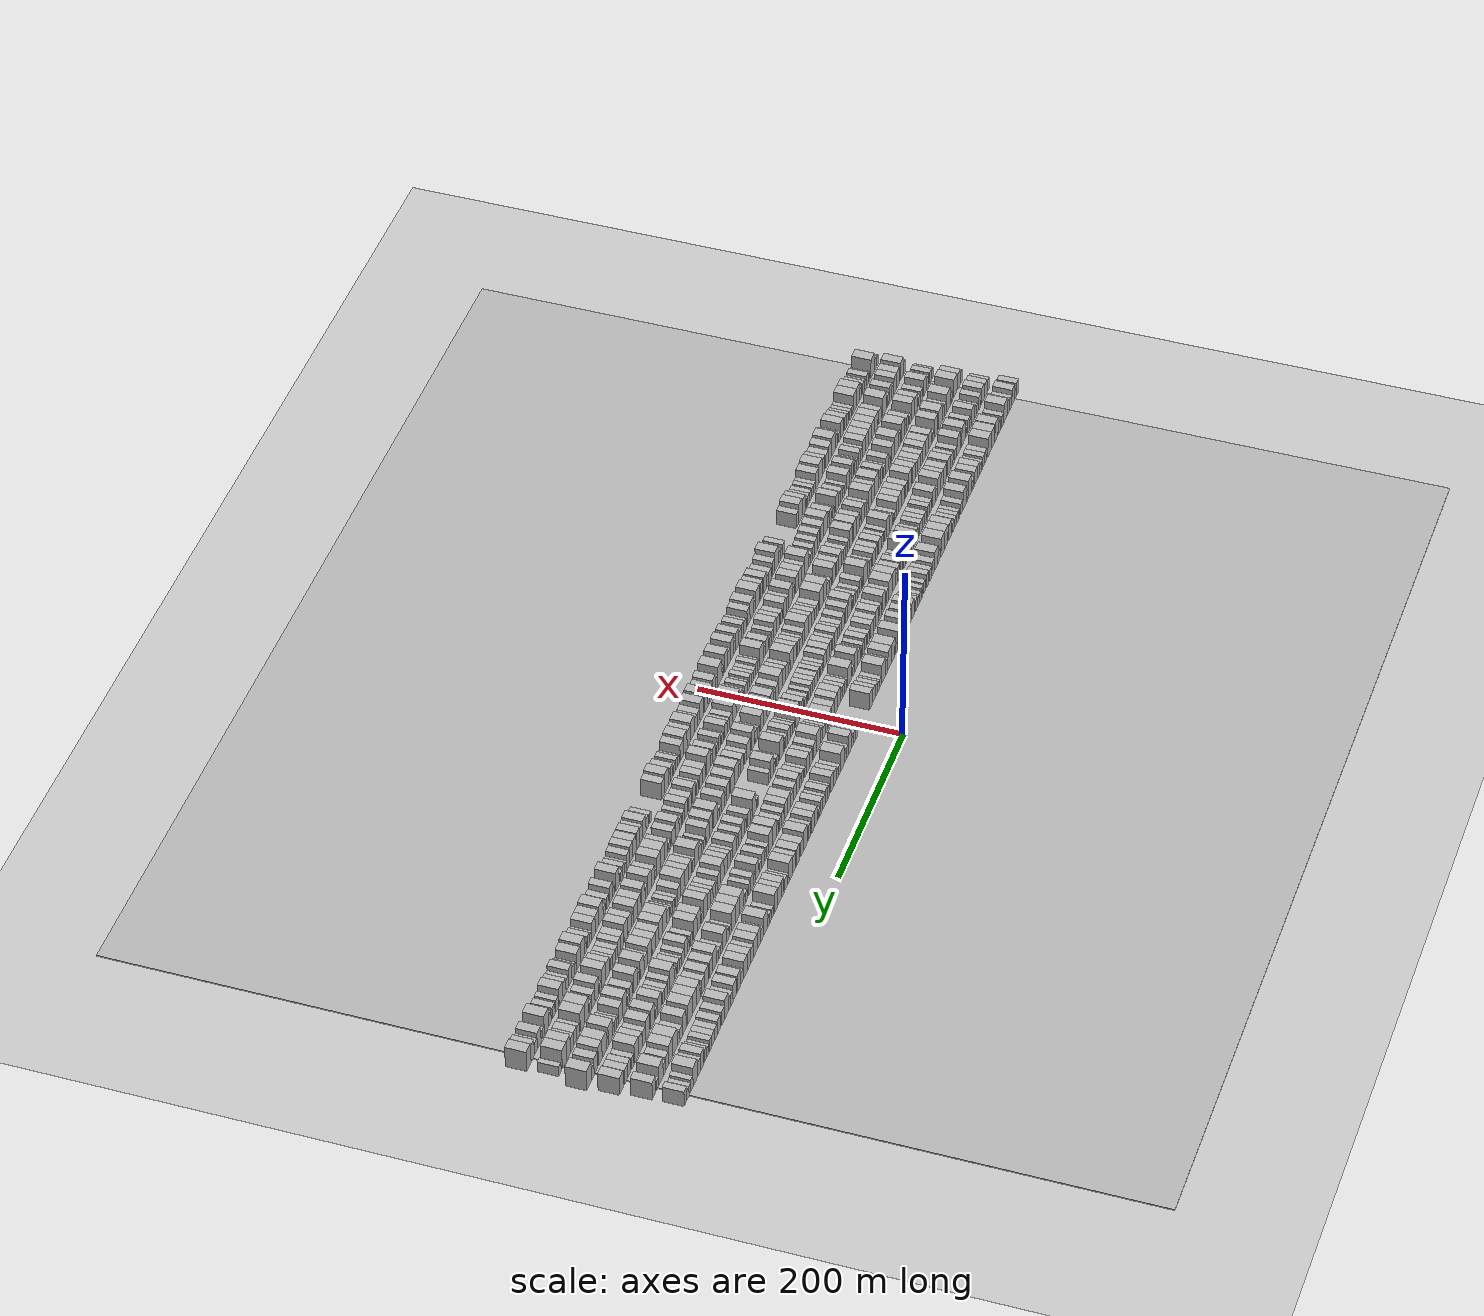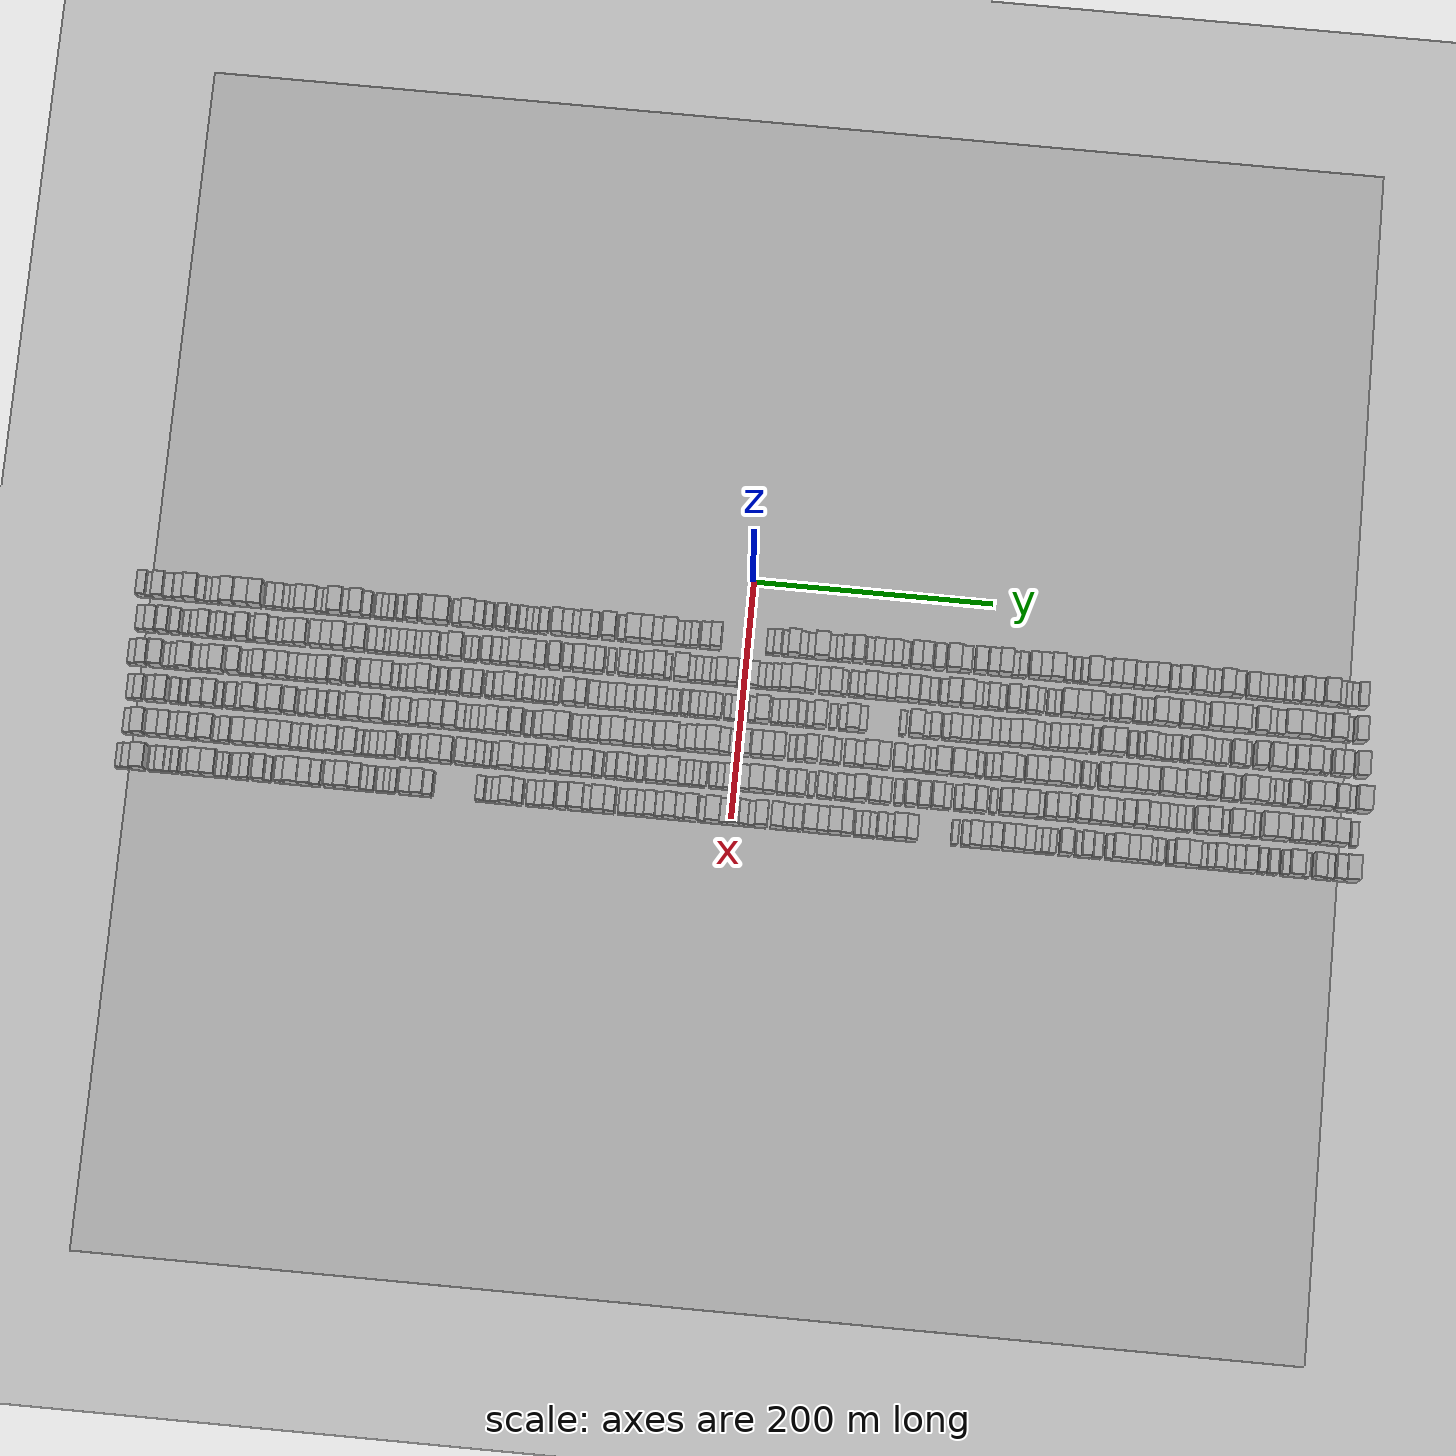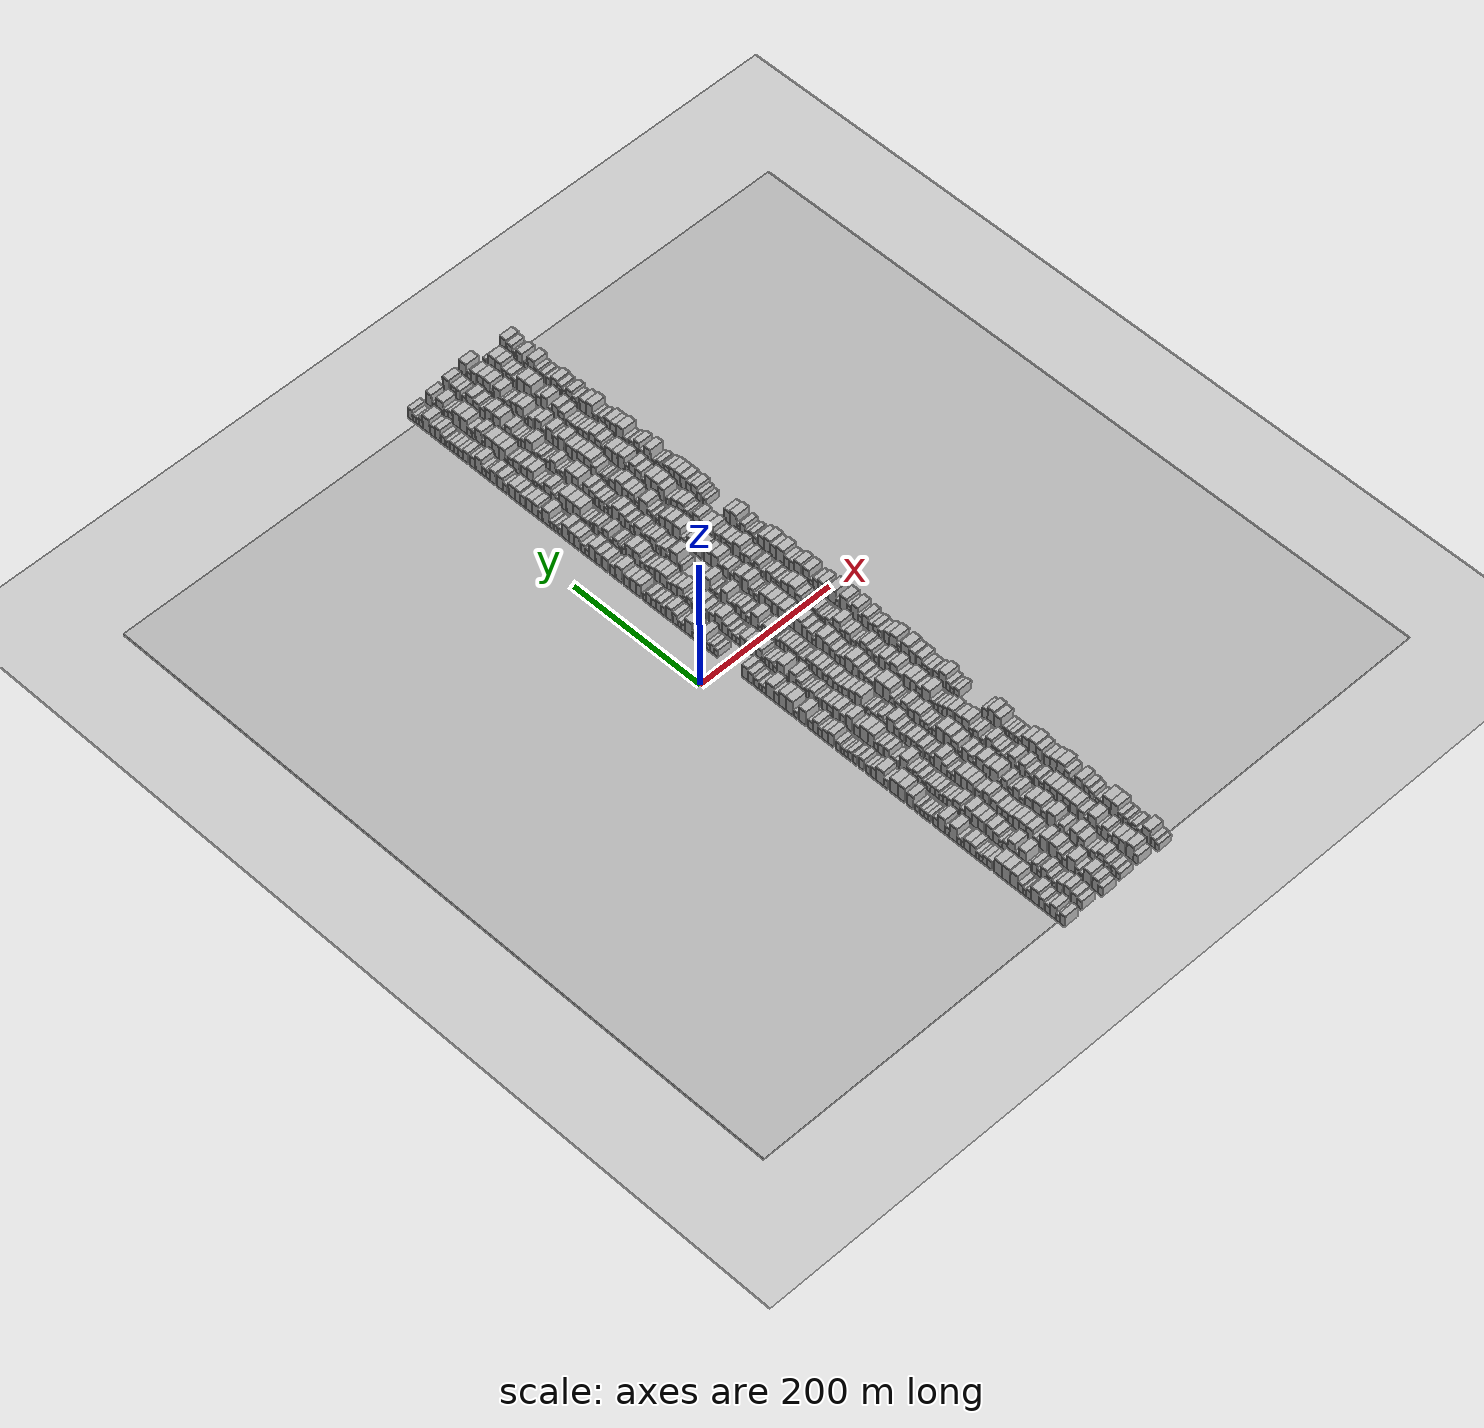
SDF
<?xml version="1.0" encoding="utf-8"?>

<sdf version="1.6">

   <world name="default">

      <gui fullscreen="0">

         <camera name="user_camera">

            <pose>-15 0 4.57585 0 0 0</pose>

            <view_controller>orbit</view_controller>

         </camera>

      </gui>

      <scene>

         <sky>

           <clouds>

             <speed>12</speed>

           </clouds>

         </sky>

         <ambient>0.4 0.4 0.4 1</ambient>

         <background>0.7 0.7 0.7 1</background>

         <shadows>1</shadows>

      </scene>

      <gravity>0 0 -9.8066</gravity>

      <magnetic_field>6e-06 2.3e-05 -4.2e-05</magnetic_field>

      <physics default="0" name="default_physics" type="ode">

         <ode>

            <solver>

               <type>quick</type>

               <iters>10</iters>

               <sor>1.0</sor>

               <use_dynamic_moi_rescaling>0</use_dynamic_moi_rescaling>

            </solver>

            <constraints>

               <cfm>0</cfm>

               <erp>0.2</erp>

               <contact_max_correcting_vel>100</contact_max_correcting_vel>

               <contact_surface_layer>0.001</contact_surface_layer>

            </constraints>

         </ode>

         <max_step_size>0.004</max_step_size>

         <real_time_factor>1</real_time_factor>

         <real_time_update_rate>250</real_time_update_rate>

      </physics>

      <light name="sun" type="directional">

         <cast_shadows>1</cast_shadows>

         <pose>0 0 10 0 0 0</pose>

         <diffuse>0.8 0.8 0.8 1</diffuse>

         <specular>0.2 0.2 0.2 1</specular>

         <attenuation>

            <range>1000</range>

            <constant>0.9</constant>

            <linear>0.01</linear>

            <quadratic>0.001</quadratic>

         </attenuation>

         <direction>-0.5 0.1 -0.9</direction>

      </light>

      <include>

         <name>ground_plane_1</name>

         <uri>model://HANNAS_ground_plane</uri>

         <pose>0 0 0  0 0 0</pose>

      </include>

      <include>

         <name>ground_plane_2</name>

         <uri>model://HANNAS_ground_plane</uri>

         <pose>100 0 0  0 0 0</pose>

      </include>

      <model name="building_1">

         <static>1</static>

         <pose frame="">50.0000 -506.1612 0 0.000000 0.000000 0.000000</pose>

         <link name="link">

            <pose frame="">0 0 9.00 0 0 0</pose>

            <collision name="collision">

               <geometry>

                  <box>

                     <size>20.0000 7.6777 18.0000</size>

                  </box>

               </geometry>

               <max_contacts>10</max_contacts>

               <surface>

                  <contact>

                     <ode/>

                  </contact>

                  <bounce/>

                  <friction>

                     <torsional>

                        <ode/>

                     </torsional>

                     <ode/>

                  </friction>

               </surface>

            </collision>

            <visual name="visual">

               <cast_shadows>0</cast_shadows>

               <geometry>

                  <box>

                     <size>20.0000 7.6777 18.0000</size>

                  </box>

               </geometry>

               <material>

                  <script>

                     <uri>model://HANNAS_wall/materials/scripts</uri>

                     <uri>model://HANNAS_wall/materials/textures</uri>

                     <name>vrc/HANNAS_wall</name>

                  </script>

               </material>

            </visual>

            <self_collide>0</self_collide>

            <enable_wind>0</enable_wind>

            <kinematic>0</kinematic>

         </link>

      </model>

      <model name="building_2">

         <static>1</static>

         <pose frame="">50.0000 -499.5940 0 0.000000 0.000000 0.000000</pose>

         <link name="link">

            <pose frame="">0 0 6.00 0 0 0</pose>

            <collision name="collision">

               <geometry>

                  <box>

                     <size>20.0000 5.4566 12.0000</size>

                  </box>

               </geometry>

               <max_contacts>10</max_contacts>

               <surface>

                  <contact>

                     <ode/>

                  </contact>

                  <bounce/>

                  <friction>

                     <torsional>

                        <ode/>

                     </torsional>

                     <ode/>

                  </friction>

               </surface>

            </collision>

            <visual name="visual">

               <cast_shadows>0</cast_shadows>

               <geometry>

                  <box>

                     <size>20.0000 5.4566 12.0000</size>

                  </box>

               </geometry>

               <material>

                  <script>

                     <uri>model://HANNAS_wall/materials/scripts</uri>

                     <uri>model://HANNAS_wall/materials/textures</uri>

                     <name>vrc/HANNAS_wall</name>

                  </script>

               </material>

            </visual>

            <self_collide>0</self_collide>

            <enable_wind>0</enable_wind>

            <kinematic>0</kinematic>

         </link>

      </model>

      <model name="building_3">

         <static>1</static>

         <pose frame="">50.0000 -492.1491 0 0.000000 0.000000 0.000000</pose>

         <link name="link">

            <pose frame="">0 0 10.50 0 0 0</pose>

            <collision name="collision">

               <geometry>

                  <box>

                     <size>20.0000 9.4333 21.0000</size>

                  </box>

               </geometry>

               <max_contacts>10</max_contacts>

               <surface>

                  <contact>

                     <ode/>

                  </contact>

                  <bounce/>

                  <friction>

                     <torsional>

                        <ode/>

                     </torsional>

                     <ode/>

                  </friction>

               </surface>

            </collision>

            <visual name="visual">

               <cast_shadows>0</cast_shadows>

               <geometry>

                  <box>

                     <size>20.0000 9.4333 21.0000</size>

                  </box>

               </geometry>

               <material>

                  <script>

                     <uri>model://HANNAS_wall/materials/scripts</uri>

                     <uri>model://HANNAS_wall/materials/textures</uri>

                     <name>vrc/HANNAS_wall</name>

                  </script>

               </material>

            </visual>

            <self_collide>0</self_collide>

            <enable_wind>0</enable_wind>

            <kinematic>0</kinematic>

         </link>

      </model>

      <model name="building_4">

         <static>1</static>

         <pose frame="">50.0000 -483.7056 0 0.000000 0.000000 0.000000</pose>

         <link name="link">

            <pose frame="">0 0 7.50 0 0 0</pose>

            <collision name="collision">

               <geometry>

                  <box>

                     <size>20.0000 7.4537 15.0000</size>

                  </box>

               </geometry>

               <max_contacts>10</max_contacts>

               <surface>

                  <contact>

                     <ode/>

                  </contact>

                  <bounce/>

                  <friction>

                     <torsional>

                        <ode/>

                     </torsional>

                     <ode/>

                  </friction>

               </surface>

            </collision>

            <visual name="visual">

               <cast_shadows>0</cast_shadows>

               <geometry>

                  <box>

                     <size>20.0000 7.4537 15.0000</size>

                  </box>

               </geometry>

               <material>

                  <script>

                     <uri>model://HANNAS_wall/materials/scripts</uri>

                     <uri>model://HANNAS_wall/materials/textures</uri>

                     <name>vrc/HANNAS_wall</name>

                  </script>

               </material>

            </visual>

            <self_collide>0</self_collide>

            <enable_wind>0</enable_wind>

            <kinematic>0</kinematic>

         </link>

      </model>

      <model name="building_5">

         <static>1</static>

         <pose frame="">50.0000 -474.9887 0 0.000000 0.000000 0.000000</pose>

         <link name="link">

            <pose frame="">0 0 9.00 0 0 0</pose>

            <collision name="collision">

               <geometry>

                  <box>

                     <size>20.0000 7.9801 18.0000</size>

                  </box>

               </geometry>

               <max_contacts>10</max_contacts>

               <surface>

                  <contact>

                     <ode/>

                  </contact>

                  <bounce/>

                  <friction>

                     <torsional>

                        <ode/>

                     </torsional>

                     <ode/>

                  </friction>

               </surface>

            </collision>

            <visual name="visual">

               <cast_shadows>0</cast_shadows>

               <geometry>

                  <box>

                     <size>20.0000 7.9801 18.0000</size>

                  </box>

               </geometry>

               <material>

                  <script>

                     <uri>model://HANNAS_wall/materials/scripts</uri>

                     <uri>model://HANNAS_wall/materials/textures</uri>

                     <name>vrc/HANNAS_wall</name>

                  </script>

               </material>

            </visual>

            <self_collide>0</self_collide>

            <enable_wind>0</enable_wind>

            <kinematic>0</kinematic>

         </link>

      </model>

      <model name="building_6">

         <static>1</static>

         <pose frame="">50.0000 -465.2205 0 0.000000 0.000000 0.000000</pose>

         <link name="link">

            <pose frame="">0 0 12.00 0 0 0</pose>

            <collision name="collision">

               <geometry>

                  <box>

                     <size>20.0000 11.5562 24.0000</size>

                  </box>

               </geometry>

               <max_contacts>10</max_contacts>

               <surface>

                  <contact>

                     <ode/>

                  </contact>

                  <bounce/>

                  <friction>

                     <torsional>

                        <ode/>

                     </torsional>

                     <ode/>

                  </friction>

               </surface>

            </collision>

            <visual name="visual">

               <cast_shadows>0</cast_shadows>

               <geometry>

                  <box>

                     <size>20.0000 11.5562 24.0000</size>

                  </box>

               </geometry>

               <material>

                  <script>

                     <uri>model://HANNAS_wall/materials/scripts</uri>

                     <uri>model://HANNAS_wall/materials/textures</uri>

                     <name>vrc/HANNAS_wall</name>

                  </script>

               </material>

            </visual>

            <self_collide>0</self_collide>

            <enable_wind>0</enable_wind>

            <kinematic>0</kinematic>

         </link>

      </model>

      <model name="building_7">

         <static>1</static>

         <pose frame="">50.0000 -456.1602 0 0.000000 0.000000 0.000000</pose>

         <link name="link">

            <pose frame="">0 0 7.50 0 0 0</pose>

            <collision name="collision">

               <geometry>

                  <box>

                     <size>20.0000 6.5645 15.0000</size>

                  </box>

               </geometry>

               <max_contacts>10</max_contacts>

               <surface>

                  <contact>

                     <ode/>

                  </contact>

                  <bounce/>

                  <friction>

                     <torsional>

                        <ode/>

                     </torsional>

                     <ode/>

                  </friction>

               </surface>

            </collision>

            <visual name="visual">

               <cast_shadows>0</cast_shadows>

               <geometry>

                  <box>

                     <size>20.0000 6.5645 15.0000</size>

                  </box>

               </geometry>

               <material>

                  <script>

                     <uri>model://HANNAS_wall/materials/scripts</uri>

                     <uri>model://HANNAS_wall/materials/textures</uri>

                     <name>vrc/HANNAS_wall</name>

                  </script>

               </material>

            </visual>

            <self_collide>0</self_collide>

            <enable_wind>0</enable_wind>

            <kinematic>0</kinematic>

         </link>

      </model>

      <model name="building_8">

         <static>1</static>

         <pose frame="">50.0000 -450.3521 0 0.000000 0.000000 0.000000</pose>

         <link name="link">

            <pose frame="">0 0 6.00 0 0 0</pose>

            <collision name="collision">

               <geometry>

                  <box>

                     <size>20.0000 5.0517 12.0000</size>

                  </box>

               </geometry>

               <max_contacts>10</max_contacts>

               <surface>

                  <contact>

                     <ode/>

                  </contact>

                  <bounce/>

                  <friction>

                     <torsional>

                        <ode/>

                     </torsional>

                     <ode/>

                  </friction>

               </surface>

            </collision>

            <visual name="visual">

               <cast_shadows>0</cast_shadows>

               <geometry>

                  <box>

                     <size>20.0000 5.0517 12.0000</size>

                  </box>

               </geometry>

               <material>

                  <script>

                     <uri>model://HANNAS_wall/materials/scripts</uri>

                     <uri>model://HANNAS_wall/materials/textures</uri>

                     <name>vrc/HANNAS_wall</name>

                  </script>

               </material>

            </visual>

            <self_collide>0</self_collide>

            <enable_wind>0</enable_wind>

            <kinematic>0</kinematic>

         </link>

      </model>

      <model name="building_9">

         <static>1</static>

         <pose frame="">50.0000 -444.3844 0 0.000000 0.000000 0.000000</pose>

         <link name="link">

            <pose frame="">0 0 7.50 0 0 0</pose>

            <collision name="collision">

               <geometry>

                  <box>

                     <size>20.0000 6.8837 15.0000</size>

                  </box>

               </geometry>

               <max_contacts>10</max_contacts>

               <surface>

                  <contact>

                     <ode/>

                  </contact>

                  <bounce/>

                  <friction>

                     <torsional>

                        <ode/>

                     </torsional>

                     <ode/>

                  </friction>

               </surface>

            </collision>

            <visual name="visual">

               <cast_shadows>0</cast_shadows>

               <geometry>

                  <box>

                     <size>20.0000 6.8837 15.0000</size>

                  </box>

               </geometry>

               <material>

                  <script>

                     <uri>model://HANNAS_wall/materials/scripts</uri>

                     <uri>model://HANNAS_wall/materials/textures</uri>

                     <name>vrc/HANNAS_wall</name>

                  </script>

               </material>

            </visual>

            <self_collide>0</self_collide>

            <enable_wind>0</enable_wind>

            <kinematic>0</kinematic>

         </link>

      </model>

      <model name="building_10">

         <static>1</static>

         <pose frame="">50.0000 -434.5352 0 0.000000 0.000000 0.000000</pose>

         <link name="link">

            <pose frame="">0 0 12.00 0 0 0</pose>

            <collision name="collision">

               <geometry>

                  <box>

                     <size>20.0000 10.8148 24.0000</size>

                  </box>

               </geometry>

               <max_contacts>10</max_contacts>

               <surface>

                  <contact>

                     <ode/>

                  </contact>

                  <bounce/>

                  <friction>

                     <torsional>

                        <ode/>

                     </torsional>

                     <ode/>

                  </friction>

               </surface>

            </collision>

            <visual name="visual">

               <cast_shadows>0</cast_shadows>

               <geometry>

                  <box>

                     <size>20.0000 10.8148 24.0000</size>

                  </box>

               </geometry>

               <material>

                  <script>

                     <uri>model://HANNAS_wall/materials/scripts</uri>

                     <uri>model://HANNAS_wall/materials/textures</uri>

                     <name>vrc/HANNAS_wall</name>

                  </script>

               </material>

            </visual>

            <self_collide>0</self_collide>

            <enable_wind>0</enable_wind>

            <kinematic>0</kinematic>

         </link>

      </model>

      <model name="building_11">

         <static>1</static>

         <pose frame="">50.0000 -422.4668 0 0.000000 0.000000 0.000000</pose>

         <link name="link">

            <pose frame="">0 0 12.00 0 0 0</pose>

            <collision name="collision">

               <geometry>

                  <box>

                     <size>20.0000 11.3220 24.0000</size>

                  </box>

               </geometry>

               <max_contacts>10</max_contacts>

               <surface>

                  <contact>

                     <ode/>

                  </contact>

                  <bounce/>

                  <friction>

                     <torsional>

                        <ode/>

                     </torsional>

                     <ode/>

                  </friction>

               </surface>

            </collision>

            <visual name="visual">

               <cast_shadows>0</cast_shadows>

               <geometry>

                  <box>

                     <size>20.0000 11.3220 24.0000</size>

                  </box>

               </geometry>

               <material>

                  <script>

                     <uri>model://HANNAS_wall/materials/scripts</uri>

                     <uri>model://HANNAS_wall/materials/textures</uri>

                     <name>vrc/HANNAS_wall</name>

                  </script>

               </material>

            </visual>

            <self_collide>0</self_collide>

            <enable_wind>0</enable_wind>

            <kinematic>0</kinematic>

         </link>

      </model>

      <model name="building_12">

         <static>1</static>

         <pose frame="">50.0000 -411.0667 0 0.000000 0.000000 0.000000</pose>

         <link name="link">

            <pose frame="">0 0 12.00 0 0 0</pose>

            <collision name="collision">

               <geometry>

                  <box>

                     <size>20.0000 11.4783 24.0000</size>

                  </box>

               </geometry>

               <max_contacts>10</max_contacts>

               <surface>

                  <contact>

                     <ode/>

                  </contact>

                  <bounce/>

                  <friction>

                     <torsional>

                        <ode/>

                     </torsional>

                     <ode/>

                  </friction>

               </surface>

            </collision>

            <visual name="visual">

               <cast_shadows>0</cast_shadows>

               <geometry>

                  <box>

                     <size>20.0000 11.4783 24.0000</size>

                  </box>

               </geometry>

               <material>

                  <script>

                     <uri>model://HANNAS_wall/materials/scripts</uri>

                     <uri>model://HANNAS_wall/materials/textures</uri>

                     <name>vrc/HANNAS_wall</name>

                  </script>

               </material>

            </visual>

            <self_collide>0</self_collide>

            <enable_wind>0</enable_wind>

            <kinematic>0</kinematic>

         </link>

      </model>

      <model name="building_13">

         <static>1</static>

         <pose frame="">50.0000 -398.7498 0 0.000000 0.000000 0.000000</pose>

         <link name="link">

            <pose frame="">0 0 7.50 0 0 0</pose>

            <collision name="collision">

               <geometry>

                  <box>

                     <size>20.0000 7.1554 15.0000</size>

                  </box>

               </geometry>

               <max_contacts>10</max_contacts>

               <surface>

                  <contact>

                     <ode/>

                  </contact>

                  <bounce/>

                  <friction>

                     <torsional>

                        <ode/>

                     </torsional>

                     <ode/>

                  </friction>

               </surface>

            </collision>

            <visual name="visual">

               <cast_shadows>0</cast_shadows>

               <geometry>

                  <box>

                     <size>20.0000 7.1554 15.0000</size>

                  </box>

               </geometry>

               <material>

                  <script>

                     <uri>model://HANNAS_wall/materials/scripts</uri>

                     <uri>model://HANNAS_wall/materials/textures</uri>

                     <name>vrc/HANNAS_wall</name>

                  </script>

               </material>

            </visual>

            <self_collide>0</self_collide>

            <enable_wind>0</enable_wind>

            <kinematic>0</kinematic>

         </link>

      </model>

      <model name="building_14">

         <static>1</static>

         <pose frame="">50.0000 -391.5810 0 0.000000 0.000000 0.000000</pose>

         <link name="link">

            <pose frame="">0 0 7.50 0 0 0</pose>

            <collision name="collision">

               <geometry>

                  <box>

                     <size>20.0000 7.1822 15.0000</size>

                  </box>

               </geometry>

               <max_contacts>10</max_contacts>

               <surface>

                  <contact>

                     <ode/>

                  </contact>

                  <bounce/>

                  <friction>

                     <torsional>

                        <ode/>

                     </torsional>

                     <ode/>

                  </friction>

               </surface>

            </collision>

            <visual name="visual">

               <cast_shadows>0</cast_shadows>

               <geometry>

                  <box>

                     <size>20.0000 7.1822 15.0000</size>

                  </box>

               </geometry>

               <material>

                  <script>

                     <uri>model://HANNAS_wall/materials/scripts</uri>

                     <uri>model://HANNAS_wall/materials/textures</uri>

                     <name>vrc/HANNAS_wall</name>

                  </script>

               </material>

            </visual>

            <self_collide>0</self_collide>

            <enable_wind>0</enable_wind>

            <kinematic>0</kinematic>

         </link>

      </model>

      <model name="building_15">

         <static>1</static>

         <pose frame="">50.0000 -385.5273 0 0.000000 0.000000 0.000000</pose>

         <link name="link">

            <pose frame="">0 0 6.00 0 0 0</pose>

            <collision name="collision">

               <geometry>

                  <box>

                     <size>20.0000 4.9251 12.0000</size>

                  </box>

               </geometry>

               <max_contacts>10</max_contacts>

               <surface>

                  <contact>

                     <ode/>

                  </contact>

                  <bounce/>

                  <friction>

                     <torsional>

                        <ode/>

                     </torsional>

                     <ode/>

                  </friction>

               </surface>

            </collision>

            <visual name="visual">

               <cast_shadows>0</cast_shadows>

               <geometry>

                  <box>

                     <size>20.0000 4.9251 12.0000</size>

                  </box>

               </geometry>

               <material>

                  <script>

                     <uri>model://HANNAS_wall/materials/scripts</uri>

                     <uri>model://HANNAS_wall/materials/textures</uri>

                     <name>vrc/HANNAS_wall</name>

                  </script>

               </material>

            </visual>

            <self_collide>0</self_collide>

            <enable_wind>0</enable_wind>

            <kinematic>0</kinematic>

         </link>

      </model>

      <model name="building_16">

         <static>1</static>

         <pose frame="">50.0000 -380.4521 0 0.000000 0.000000 0.000000</pose>

         <link name="link">

            <pose frame="">0 0 6.00 0 0 0</pose>

            <collision name="collision">

               <geometry>

                  <box>

                     <size>20.0000 5.2253 12.0000</size>

                  </box>

               </geometry>

               <max_contacts>10</max_contacts>

               <surface>

                  <contact>

                     <ode/>

                  </contact>

                  <bounce/>

                  <friction>

                     <torsional>

                        <ode/>

                     </torsional>

                     <ode/>

                  </friction>

               </surface>

            </collision>

            <visual name="visual">

               <cast_shadows>0</cast_shadows>

               <geometry>

                  <box>

                     <size>20.0000 5.2253 12.0000</size>

                  </box>

               </geometry>

               <material>

                  <script>

                     <uri>model://HANNAS_wall/materials/scripts</uri>

                     <uri>model://HANNAS_wall/materials/textures</uri>

                     <name>vrc/HANNAS_wall</name>

                  </script>

               </material>

            </visual>

            <self_collide>0</self_collide>

            <enable_wind>0</enable_wind>

            <kinematic>0</kinematic>

         </link>

      </model>

      <model name="building_17">

         <static>1</static>

         <pose frame="">50.0000 -373.5593 0 0.000000 0.000000 0.000000</pose>

         <link name="link">

            <pose frame="">0 0 9.00 0 0 0</pose>

            <collision name="collision">

               <geometry>

                  <box>

                     <size>20.0000 8.5604 18.0000</size>

                  </box>

               </geometry>

               <max_contacts>10</max_contacts>

               <surface>

                  <contact>

                     <ode/>

                  </contact>

                  <bounce/>

                  <friction>

                     <torsional>

                        <ode/>

                     </torsional>

                     <ode/>

                  </friction>

               </surface>

            </collision>

            <visual name="visual">

               <cast_shadows>0</cast_shadows>

               <geometry>

                  <box>

                     <size>20.0000 8.5604 18.0000</size>

                  </box>

               </geometry>

               <material>

                  <script>

                     <uri>model://HANNAS_wall/materials/scripts</uri>

                     <uri>model://HANNAS_wall/materials/textures</uri>

                     <name>vrc/HANNAS_wall</name>

                  </script>

               </material>

            </visual>

            <self_collide>0</self_collide>

            <enable_wind>0</enable_wind>

            <kinematic>0</kinematic>

         </link>

      </model>

      <model name="building_18">

         <static>1</static>

         <pose frame="">50.0000 -364.8369 0 0.000000 0.000000 0.000000</pose>

         <link name="link">

            <pose frame="">0 0 9.00 0 0 0</pose>

            <collision name="collision">

               <geometry>

                  <box>

                     <size>20.0000 8.8844 18.0000</size>

                  </box>

               </geometry>

               <max_contacts>10</max_contacts>

               <surface>

                  <contact>

                     <ode/>

                  </contact>

                  <bounce/>

                  <friction>

                     <torsional>

                        <ode/>

                     </torsional>

                     <ode/>

                  </friction>

               </surface>

            </collision>

            <visual name="visual">

               <cast_shadows>0</cast_shadows>

               <geometry>

                  <box>

                     <size>20.0000 8.8844 18.0000</size>

                  </box>

               </geometry>

               <material>

                  <script>

                     <uri>model://HANNAS_wall/materials/scripts</uri>

                     <uri>model://HANNAS_wall/materials/textures</uri>

                     <name>vrc/HANNAS_wall</name>

                  </script>

               </material>

            </visual>

            <self_collide>0</self_collide>

            <enable_wind>0</enable_wind>

            <kinematic>0</kinematic>

         </link>

      </model>

      <model name="building_19">

         <static>1</static>

         <pose frame="">50.0000 -357.9122 0 0.000000 0.000000 0.000000</pose>

         <link name="link">

            <pose frame="">0 0 6.00 0 0 0</pose>

            <collision name="collision">

               <geometry>

                  <box>

                     <size>20.0000 4.9650 12.0000</size>

                  </box>

               </geometry>

               <max_contacts>10</max_contacts>

               <surface>

                  <contact>

                     <ode/>

                  </contact>

                  <bounce/>

                  <friction>

                     <torsional>

                        <ode/>

                     </torsional>

                     <ode/>

                  </friction>

               </surface>

            </collision>

            <visual name="visual">

               <cast_shadows>0</cast_shadows>

               <geometry>

                  <box>

                     <size>20.0000 4.9650 12.0000</size>

                  </box>

               </geometry>

               <material>

                  <script>

                     <uri>model://HANNAS_wall/materials/scripts</uri>

                     <uri>model://HANNAS_wall/materials/textures</uri>

                     <name>vrc/HANNAS_wall</name>

                  </script>

               </material>

            </visual>

            <self_collide>0</self_collide>

            <enable_wind>0</enable_wind>

            <kinematic>0</kinematic>

         </link>

      </model>

      <model name="building_20">

         <static>1</static>

         <pose frame="">50.0000 -352.7772 0 0.000000 0.000000 0.000000</pose>

         <link name="link">

            <pose frame="">0 0 6.00 0 0 0</pose>

            <collision name="collision">

               <geometry>

                  <box>

                     <size>20.0000 5.3050 12.0000</size>

                  </box>

               </geometry>

               <max_contacts>10</max_contacts>

               <surface>

                  <contact>

                     <ode/>

                  </contact>

                  <bounce/>

                  <friction>

                     <torsional>

                        <ode/>

                     </torsional>

                     <ode/>

                  </friction>

               </surface>

            </collision>

            <visual name="visual">

               <cast_shadows>0</cast_shadows>

               <geometry>

                  <box>

                     <size>20.0000 5.3050 12.0000</size>

                  </box>

               </geometry>

               <material>

                  <script>

                     <uri>model://HANNAS_wall/materials/scripts</uri>

                     <uri>model://HANNAS_wall/materials/textures</uri>

                     <name>vrc/HANNAS_wall</name>

                  </script>

               </material>

            </visual>

            <self_collide>0</self_collide>

            <enable_wind>0</enable_wind>

            <kinematic>0</kinematic>

         </link>

      </model>

      <model name="building_21">

         <static>1</static>

         <pose frame="">50.0000 -344.3734 0 0.000000 0.000000 0.000000</pose>

         <link name="link">

            <pose frame="">0 0 12.00 0 0 0</pose>

            <collision name="collision">

               <geometry>

                  <box>

                     <size>20.0000 11.5025 24.0000</size>

                  </box>

               </geometry>

               <max_contacts>10</max_contacts>

               <surface>

                  <contact>

                     <ode/>

                  </contact>

                  <bounce/>

                  <friction>

                     <torsional>

                        <ode/>

                     </torsional>

                     <ode/>

                  </friction>

               </surface>

            </collision>

            <visual name="visual">

               <cast_shadows>0</cast_shadows>

               <geometry>

                  <box>

                     <size>20.0000 11.5025 24.0000</size>

                  </box>

               </geometry>

               <material>

                  <script>

                     <uri>model://HANNAS_wall/materials/scripts</uri>

                     <uri>model://HANNAS_wall/materials/textures</uri>

                     <name>vrc/HANNAS_wall</name>

                  </script>

               </material>

            </visual>

            <self_collide>0</self_collide>

            <enable_wind>0</enable_wind>

            <kinematic>0</kinematic>

         </link>

      </model>

      <model name="building_22">

         <static>1</static>

         <pose frame="">50.0000 -335.4424 0 0.000000 0.000000 0.000000</pose>

         <link name="link">

            <pose frame="">0 0 7.50 0 0 0</pose>

            <collision name="collision">

               <geometry>

                  <box>

                     <size>20.0000 6.3595 15.0000</size>

                  </box>

               </geometry>

               <max_contacts>10</max_contacts>

               <surface>

                  <contact>

                     <ode/>

                  </contact>

                  <bounce/>

                  <friction>

                     <torsional>

                        <ode/>

                     </torsional>

                     <ode/>

                  </friction>

               </surface>

            </collision>

            <visual name="visual">

               <cast_shadows>0</cast_shadows>

               <geometry>

                  <box>

                     <size>20.0000 6.3595 15.0000</size>

                  </box>

               </geometry>

               <material>

                  <script>

                     <uri>model://HANNAS_wall/materials/scripts</uri>

                     <uri>model://HANNAS_wall/materials/textures</uri>

                     <name>vrc/HANNAS_wall</name>

                  </script>

               </material>

            </visual>

            <self_collide>0</self_collide>

            <enable_wind>0</enable_wind>

            <kinematic>0</kinematic>

         </link>

      </model>

      <model name="building_23">

         <static>1</static>

         <pose frame="">50.0000 -326.9030 0 0.000000 0.000000 0.000000</pose>

         <link name="link">

            <pose frame="">0 0 12.00 0 0 0</pose>

            <collision name="collision">

               <geometry>

                  <box>

                     <size>20.0000 10.7193 24.0000</size>

                  </box>

               </geometry>

               <max_contacts>10</max_contacts>

               <surface>

                  <contact>

                     <ode/>

                  </contact>

                  <bounce/>

                  <friction>

                     <torsional>

                        <ode/>

                     </torsional>

                     <ode/>

                  </friction>

               </surface>

            </collision>

            <visual name="visual">

               <cast_shadows>0</cast_shadows>

               <geometry>

                  <box>

                     <size>20.0000 10.7193 24.0000</size>

                  </box>

               </geometry>

               <material>

                  <script>

                     <uri>model://HANNAS_wall/materials/scripts</uri>

                     <uri>model://HANNAS_wall/materials/textures</uri>

                     <name>vrc/HANNAS_wall</name>

                  </script>

               </material>

            </visual>

            <self_collide>0</self_collide>

            <enable_wind>0</enable_wind>

            <kinematic>0</kinematic>

         </link>

      </model>

      <model name="building_24">

         <static>1</static>

         <pose frame="">50.0000 -317.8002 0 0.000000 0.000000 0.000000</pose>

         <link name="link">

            <pose frame="">0 0 7.50 0 0 0</pose>

            <collision name="collision">

               <geometry>

                  <box>

                     <size>20.0000 7.4862 15.0000</size>

                  </box>

               </geometry>

               <max_contacts>10</max_contacts>

               <surface>

                  <contact>

                     <ode/>

                  </contact>

                  <bounce/>

                  <friction>

                     <torsional>

                        <ode/>

                     </torsional>

                     <ode/>

                  </friction>

               </surface>

            </collision>

            <visual name="visual">

               <cast_shadows>0</cast_shadows>

               <geometry>

                  <box>

                     <size>20.0000 7.4862 15.0000</size>

                  </box>

               </geometry>

               <material>

                  <script>

                     <uri>model://HANNAS_wall/materials/scripts</uri>

                     <uri>model://HANNAS_wall/materials/textures</uri>

                     <name>vrc/HANNAS_wall</name>

                  </script>

               </material>

            </visual>

            <self_collide>0</self_collide>

            <enable_wind>0</enable_wind>

            <kinematic>0</kinematic>

         </link>

      </model>

      <model name="building_25">

         <static>1</static>

         <pose frame="">50.0000 -308.4729 0 0.000000 0.000000 0.000000</pose>

         <link name="link">

            <pose frame="">0 0 6.00 0 0 0</pose>

            <collision name="collision">

               <geometry>

                  <box>

                     <size>20.0000 5.1685 12.0000</size>

                  </box>

               </geometry>

               <max_contacts>10</max_contacts>

               <surface>

                  <contact>

                     <ode/>

                  </contact>

                  <bounce/>

                  <friction>

                     <torsional>

                        <ode/>

                     </torsional>

                     <ode/>

                  </friction>

               </surface>

            </collision>

            <visual name="visual">

               <cast_shadows>0</cast_shadows>

               <geometry>

                  <box>

                     <size>20.0000 5.1685 12.0000</size>

                  </box>

               </geometry>

               <material>

                  <script>

                     <uri>model://HANNAS_wall/materials/scripts</uri>

                     <uri>model://HANNAS_wall/materials/textures</uri>

                     <name>vrc/HANNAS_wall</name>

                  </script>

               </material>

            </visual>

            <self_collide>0</self_collide>

            <enable_wind>0</enable_wind>

            <kinematic>0</kinematic>

         </link>

      </model>

      <model name="building_26">

         <static>1</static>

         <pose frame="">50.0000 -303.1482 0 0.000000 0.000000 0.000000</pose>

         <link name="link">

            <pose frame="">0 0 6.00 0 0 0</pose>

            <collision name="collision">

               <geometry>

                  <box>

                     <size>20.0000 5.4807 12.0000</size>

                  </box>

               </geometry>

               <max_contacts>10</max_contacts>

               <surface>

                  <contact>

                     <ode/>

                  </contact>

                  <bounce/>

                  <friction>

                     <torsional>

                        <ode/>

                     </torsional>

                     <ode/>

                  </friction>

               </surface>

            </collision>

            <visual name="visual">

               <cast_shadows>0</cast_shadows>

               <geometry>

                  <box>

                     <size>20.0000 5.4807 12.0000</size>

                  </box>

               </geometry>

               <material>

                  <script>

                     <uri>model://HANNAS_wall/materials/scripts</uri>

                     <uri>model://HANNAS_wall/materials/textures</uri>

                     <name>vrc/HANNAS_wall</name>

                  </script>

               </material>

            </visual>

            <self_collide>0</self_collide>

            <enable_wind>0</enable_wind>

            <kinematic>0</kinematic>

         </link>

      </model>

      <model name="building_27">

         <static>1</static>

         <pose frame="">50.0000 -297.6138 0 0.000000 0.000000 0.000000</pose>

         <link name="link">

            <pose frame="">0 0 6.00 0 0 0</pose>

            <collision name="collision">

               <geometry>

                  <box>

                     <size>20.0000 5.5881 12.0000</size>

                  </box>

               </geometry>

               <max_contacts>10</max_contacts>

               <surface>

                  <contact>

                     <ode/>

                  </contact>

                  <bounce/>

                  <friction>

                     <torsional>

                        <ode/>

                     </torsional>

                     <ode/>

                  </friction>

               </surface>

            </collision>

            <visual name="visual">

               <cast_shadows>0</cast_shadows>

               <geometry>

                  <box>

                     <size>20.0000 5.5881 12.0000</size>

                  </box>

               </geometry>

               <material>

                  <script>

                     <uri>model://HANNAS_wall/materials/scripts</uri>

                     <uri>model://HANNAS_wall/materials/textures</uri>

                     <name>vrc/HANNAS_wall</name>

                  </script>

               </material>

            </visual>

            <self_collide>0</self_collide>

            <enable_wind>0</enable_wind>

            <kinematic>0</kinematic>

         </link>

      </model>

      <model name="building_28">

         <static>1</static>

         <pose frame="">50.0000 -290.1360 0 0.000000 0.000000 0.000000</pose>

         <link name="link">

            <pose frame="">0 0 6.00 0 0 0</pose>

            <collision name="collision">

               <geometry>

                  <box>

                     <size>20.0000 5.3675 12.0000</size>

                  </box>

               </geometry>

               <max_contacts>10</max_contacts>

               <surface>

                  <contact>

                     <ode/>

                  </contact>

                  <bounce/>

                  <friction>

                     <torsional>

                        <ode/>

                     </torsional>

                     <ode/>

                  </friction>

               </surface>

            </collision>

            <visual name="visual">

               <cast_shadows>0</cast_shadows>

               <geometry>

                  <box>

                     <size>20.0000 5.3675 12.0000</size>

                  </box>

               </geometry>

               <material>

                  <script>

                     <uri>model://HANNAS_wall/materials/scripts</uri>

                     <uri>model://HANNAS_wall/materials/textures</uri>

                     <name>vrc/HANNAS_wall</name>

                  </script>

               </material>

            </visual>

            <self_collide>0</self_collide>

            <enable_wind>0</enable_wind>

            <kinematic>0</kinematic>

         </link>

      </model>

      <model name="building_29">

         <static>1</static>

         <pose frame="">50.0000 -279.7111 0 0.000000 0.000000 0.000000</pose>

         <link name="link">

            <pose frame="">0 0 10.50 0 0 0</pose>

            <collision name="collision">

               <geometry>

                  <box>

                     <size>20.0000 9.4824 21.0000</size>

                  </box>

               </geometry>

               <max_contacts>10</max_contacts>

               <surface>

                  <contact>

                     <ode/>

                  </contact>

                  <bounce/>

                  <friction>

                     <torsional>

                        <ode/>

                     </torsional>

                     <ode/>

                  </friction>

               </surface>

            </collision>

            <visual name="visual">

               <cast_shadows>0</cast_shadows>

               <geometry>

                  <box>

                     <size>20.0000 9.4824 21.0000</size>

                  </box>

               </geometry>

               <material>

                  <script>

                     <uri>model://HANNAS_wall/materials/scripts</uri>

                     <uri>model://HANNAS_wall/materials/textures</uri>

                     <name>vrc/HANNAS_wall</name>

                  </script>

               </material>

            </visual>

            <self_collide>0</self_collide>

            <enable_wind>0</enable_wind>

            <kinematic>0</kinematic>

         </link>

      </model>

      <model name="building_30">

         <static>1</static>

         <pose frame="">50.0000 -266.6334 0 0.000000 0.000000 0.000000</pose>

         <link name="link">

            <pose frame="">0 0 12.00 0 0 0</pose>

            <collision name="collision">

               <geometry>

                  <box>

                     <size>20.0000 10.6729 24.0000</size>

                  </box>

               </geometry>

               <max_contacts>10</max_contacts>

               <surface>

                  <contact>

                     <ode/>

                  </contact>

                  <bounce/>

                  <friction>

                     <torsional>

                        <ode/>

                     </torsional>

                     <ode/>

                  </friction>

               </surface>

            </collision>

            <visual name="visual">

               <cast_shadows>0</cast_shadows>

               <geometry>

                  <box>

                     <size>20.0000 10.6729 24.0000</size>

                  </box>

               </geometry>

               <material>

                  <script>

                     <uri>model://HANNAS_wall/materials/scripts</uri>

                     <uri>model://HANNAS_wall/materials/textures</uri>

                     <name>vrc/HANNAS_wall</name>

                  </script>

               </material>

            </visual>

            <self_collide>0</self_collide>

            <enable_wind>0</enable_wind>

            <kinematic>0</kinematic>

         </link>

      </model>

      <model name="building_31">

         <static>1</static>

         <pose frame="">50.0000 -255.3249 0 0.000000 0.000000 0.000000</pose>

         <link name="link">

            <pose frame="">0 0 12.00 0 0 0</pose>

            <collision name="collision">

               <geometry>

                  <box>

                     <size>20.0000 11.9442 24.0000</size>

                  </box>

               </geometry>

               <max_contacts>10</max_contacts>

               <surface>

                  <contact>

                     <ode/>

                  </contact>

                  <bounce/>

                  <friction>

                     <torsional>

                        <ode/>

                     </torsional>

                     <ode/>

                  </friction>

               </surface>

            </collision>

            <visual name="visual">

               <cast_shadows>0</cast_shadows>

               <geometry>

                  <box>

                     <size>20.0000 11.9442 24.0000</size>

                  </box>

               </geometry>

               <material>

                  <script>

                     <uri>model://HANNAS_wall/materials/scripts</uri>

                     <uri>model://HANNAS_wall/materials/textures</uri>

                     <name>vrc/HANNAS_wall</name>

                  </script>

               </material>

            </visual>

            <self_collide>0</self_collide>

            <enable_wind>0</enable_wind>

            <kinematic>0</kinematic>

         </link>

      </model>

      <model name="building_32">

         <static>1</static>

         <pose frame="">50.0000 -242.9015 0 0.000000 0.000000 0.000000</pose>

         <link name="link">

            <pose frame="">0 0 7.50 0 0 0</pose>

            <collision name="collision">

               <geometry>

                  <box>

                     <size>20.0000 6.9024 15.0000</size>

                  </box>

               </geometry>

               <max_contacts>10</max_contacts>

               <surface>

                  <contact>

                     <ode/>

                  </contact>

                  <bounce/>

                  <friction>

                     <torsional>

                        <ode/>

                     </torsional>

                     <ode/>

                  </friction>

               </surface>

            </collision>

            <visual name="visual">

               <cast_shadows>0</cast_shadows>

               <geometry>

                  <box>

                     <size>20.0000 6.9024 15.0000</size>

                  </box>

               </geometry>

               <material>

                  <script>

                     <uri>model://HANNAS_wall/materials/scripts</uri>

                     <uri>model://HANNAS_wall/materials/textures</uri>

                     <name>vrc/HANNAS_wall</name>

                  </script>

               </material>

            </visual>

            <self_collide>0</self_collide>

            <enable_wind>0</enable_wind>

            <kinematic>0</kinematic>

         </link>

      </model>

      <model name="building_33">

         <static>1</static>

         <pose frame="">50.0000 -233.7580 0 0.000000 0.000000 0.000000</pose>

         <link name="link">

            <pose frame="">0 0 12.00 0 0 0</pose>

            <collision name="collision">

               <geometry>

                  <box>

                     <size>20.0000 11.3847 24.0000</size>

                  </box>

               </geometry>

               <max_contacts>10</max_contacts>

               <surface>

                  <contact>

                     <ode/>

                  </contact>

                  <bounce/>

                  <friction>

                     <torsional>

                        <ode/>

                     </torsional>

                     <ode/>

                  </friction>

               </surface>

            </collision>

            <visual name="visual">

               <cast_shadows>0</cast_shadows>

               <geometry>

                  <box>

                     <size>20.0000 11.3847 24.0000</size>

                  </box>

               </geometry>

               <material>

                  <script>

                     <uri>model://HANNAS_wall/materials/scripts</uri>

                     <uri>model://HANNAS_wall/materials/textures</uri>

                     <name>vrc/HANNAS_wall</name>

                  </script>

               </material>

            </visual>

            <self_collide>0</self_collide>

            <enable_wind>0</enable_wind>

            <kinematic>0</kinematic>

         </link>

      </model>

      <model name="building_34">

         <static>1</static>

         <pose frame="">50.0000 -224.0457 0 0.000000 0.000000 0.000000</pose>

         <link name="link">

            <pose frame="">0 0 9.00 0 0 0</pose>

            <collision name="collision">

               <geometry>

                  <box>

                     <size>20.0000 8.0400 18.0000</size>

                  </box>

               </geometry>

               <max_contacts>10</max_contacts>

               <surface>

                  <contact>

                     <ode/>

                  </contact>

                  <bounce/>

                  <friction>

                     <torsional>

                        <ode/>

                     </torsional>

                     <ode/>

                  </friction>

               </surface>

            </collision>

            <visual name="visual">

               <cast_shadows>0</cast_shadows>

               <geometry>

                  <box>

                     <size>20.0000 8.0400 18.0000</size>

                  </box>

               </geometry>

               <material>

                  <script>

                     <uri>model://HANNAS_wall/materials/scripts</uri>

                     <uri>model://HANNAS_wall/materials/textures</uri>

                     <name>vrc/HANNAS_wall</name>

                  </script>

               </material>

            </visual>

            <self_collide>0</self_collide>

            <enable_wind>0</enable_wind>

            <kinematic>0</kinematic>

         </link>

      </model>

      <model name="building_35">

         <static>1</static>

         <pose frame="">50.0000 -215.7767 0 0.000000 0.000000 0.000000</pose>

         <link name="link">

            <pose frame="">0 0 7.50 0 0 0</pose>

            <collision name="collision">

               <geometry>

                  <box>

                     <size>20.0000 6.4979 15.0000</size>

                  </box>

               </geometry>

               <max_contacts>10</max_contacts>

               <surface>

                  <contact>

                     <ode/>

                  </contact>

                  <bounce/>

                  <friction>

                     <torsional>

                        <ode/>

                     </torsional>

                     <ode/>

                  </friction>

               </surface>

            </collision>

            <visual name="visual">

               <cast_shadows>0</cast_shadows>

               <geometry>

                  <box>

                     <size>20.0000 6.4979 15.0000</size>

                  </box>

               </geometry>

               <material>

                  <script>

                     <uri>model://HANNAS_wall/materials/scripts</uri>

                     <uri>model://HANNAS_wall/materials/textures</uri>

                     <name>vrc/HANNAS_wall</name>

                  </script>

               </material>

            </visual>

            <self_collide>0</self_collide>

            <enable_wind>0</enable_wind>

            <kinematic>0</kinematic>

         </link>

      </model>

      <model name="building_36">

         <static>1</static>

         <pose frame="">50.0000 -205.8524 0 0.000000 0.000000 0.000000</pose>

         <link name="link">

            <pose frame="">0 0 9.00 0 0 0</pose>

            <collision name="collision">

               <geometry>

                  <box>

                     <size>20.0000 7.3507 18.0000</size>

                  </box>

               </geometry>

               <max_contacts>10</max_contacts>

               <surface>

                  <contact>

                     <ode/>

                  </contact>

                  <bounce/>

                  <friction>

                     <torsional>

                        <ode/>

                     </torsional>

                     <ode/>

                  </friction>

               </surface>

            </collision>

            <visual name="visual">

               <cast_shadows>0</cast_shadows>

               <geometry>

                  <box>

                     <size>20.0000 7.3507 18.0000</size>

                  </box>

               </geometry>

               <material>

                  <script>

                     <uri>model://HANNAS_wall/materials/scripts</uri>

                     <uri>model://HANNAS_wall/materials/textures</uri>

                     <name>vrc/HANNAS_wall</name>

                  </script>

               </material>

            </visual>

            <self_collide>0</self_collide>

            <enable_wind>0</enable_wind>

            <kinematic>0</kinematic>

         </link>

      </model>

      <model name="building_37">

         <static>1</static>

         <pose frame="">50.0000 -196.0622 0 0.000000 0.000000 0.000000</pose>

         <link name="link">

            <pose frame="">0 0 7.50 0 0 0</pose>

            <collision name="collision">

               <geometry>

                  <box>

                     <size>20.0000 6.2299 15.0000</size>

                  </box>

               </geometry>

               <max_contacts>10</max_contacts>

               <surface>

                  <contact>

                     <ode/>

                  </contact>

                  <bounce/>

                  <friction>

                     <torsional>

                        <ode/>

                     </torsional>

                     <ode/>

                  </friction>

               </surface>

            </collision>

            <visual name="visual">

               <cast_shadows>0</cast_shadows>

               <geometry>

                  <box>

                     <size>20.0000 6.2299 15.0000</size>

                  </box>

               </geometry>

               <material>

                  <script>

                     <uri>model://HANNAS_wall/materials/scripts</uri>

                     <uri>model://HANNAS_wall/materials/textures</uri>

                     <name>vrc/HANNAS_wall</name>

                  </script>

               </material>

            </visual>

            <self_collide>0</self_collide>

            <enable_wind>0</enable_wind>

            <kinematic>0</kinematic>

         </link>

      </model>

      <model name="building_38">

         <static>1</static>

         <pose frame="">50.0000 -187.9374 0 0.000000 0.000000 0.000000</pose>

         <link name="link">

            <pose frame="">0 0 7.50 0 0 0</pose>

            <collision name="collision">

               <geometry>

                  <box>

                     <size>20.0000 6.0197 15.0000</size>

                  </box>

               </geometry>

               <max_contacts>10</max_contacts>

               <surface>

                  <contact>

                     <ode/>

                  </contact>

                  <bounce/>

                  <friction>

                     <torsional>

                        <ode/>

                     </torsional>

                     <ode/>

                  </friction>

               </surface>

            </collision>

            <visual name="visual">

               <cast_shadows>0</cast_shadows>

               <geometry>

                  <box>

                     <size>20.0000 6.0197 15.0000</size>

                  </box>

               </geometry>

               <material>

                  <script>

                     <uri>model://HANNAS_wall/materials/scripts</uri>

                     <uri>model://HANNAS_wall/materials/textures</uri>

                     <name>vrc/HANNAS_wall</name>

                  </script>

               </material>

            </visual>

            <self_collide>0</self_collide>

            <enable_wind>0</enable_wind>

            <kinematic>0</kinematic>

         </link>

      </model>

      <model name="building_39">

         <static>1</static>

         <pose frame="">50.0000 -182.3814 0 0.000000 0.000000 0.000000</pose>

         <link name="link">

            <pose frame="">0 0 6.00 0 0 0</pose>

            <collision name="collision">

               <geometry>

                  <box>

                     <size>20.0000 5.0922 12.0000</size>

                  </box>

               </geometry>

               <max_contacts>10</max_contacts>

               <surface>

                  <contact>

                     <ode/>

                  </contact>

                  <bounce/>

                  <friction>

                     <torsional>

                        <ode/>

                     </torsional>

                     <ode/>

                  </friction>

               </surface>

            </collision>

            <visual name="visual">

               <cast_shadows>0</cast_shadows>

               <geometry>

                  <box>

                     <size>20.0000 5.0922 12.0000</size>

                  </box>

               </geometry>

               <material>

                  <script>

                     <uri>model://HANNAS_wall/materials/scripts</uri>

                     <uri>model://HANNAS_wall/materials/textures</uri>

                     <name>vrc/HANNAS_wall</name>

                  </script>

               </material>

            </visual>

            <self_collide>0</self_collide>

            <enable_wind>0</enable_wind>

            <kinematic>0</kinematic>

         </link>

      </model>

      <model name="building_40">

         <static>1</static>

         <pose frame="">50.0000 -177.3009 0 0.000000 0.000000 0.000000</pose>

         <link name="link">

            <pose frame="">0 0 6.00 0 0 0</pose>

            <collision name="collision">

               <geometry>

                  <box>

                     <size>20.0000 5.0688 12.0000</size>

                  </box>

               </geometry>

               <max_contacts>10</max_contacts>

               <surface>

                  <contact>

                     <ode/>

                  </contact>

                  <bounce/>

                  <friction>

                     <torsional>

                        <ode/>

                     </torsional>

                     <ode/>

                  </friction>

               </surface>

            </collision>

            <visual name="visual">

               <cast_shadows>0</cast_shadows>

               <geometry>

                  <box>

                     <size>20.0000 5.0688 12.0000</size>

                  </box>

               </geometry>

               <material>

                  <script>

                     <uri>model://HANNAS_wall/materials/scripts</uri>

                     <uri>model://HANNAS_wall/materials/textures</uri>

                     <name>vrc/HANNAS_wall</name>

                  </script>

               </material>

            </visual>

            <self_collide>0</self_collide>

            <enable_wind>0</enable_wind>

            <kinematic>0</kinematic>

         </link>

      </model>

      <model name="building_41">

         <static>1</static>

         <pose frame="">50.0000 -170.1626 0 0.000000 0.000000 0.000000</pose>

         <link name="link">

            <pose frame="">0 0 7.50 0 0 0</pose>

            <collision name="collision">

               <geometry>

                  <box>

                     <size>20.0000 7.2078 15.0000</size>

                  </box>

               </geometry>

               <max_contacts>10</max_contacts>

               <surface>

                  <contact>

                     <ode/>

                  </contact>

                  <bounce/>

                  <friction>

                     <torsional>

                        <ode/>

                     </torsional>

                     <ode/>

                  </friction>

               </surface>

            </collision>

            <visual name="visual">

               <cast_shadows>0</cast_shadows>

               <geometry>

                  <box>

                     <size>20.0000 7.2078 15.0000</size>

                  </box>

               </geometry>

               <material>

                  <script>

                     <uri>model://HANNAS_wall/materials/scripts</uri>

                     <uri>model://HANNAS_wall/materials/textures</uri>

                     <name>vrc/HANNAS_wall</name>

                  </script>

               </material>

            </visual>

            <self_collide>0</self_collide>

            <enable_wind>0</enable_wind>

            <kinematic>0</kinematic>

         </link>

      </model>

      <model name="building_42">

         <static>1</static>

         <pose frame="">50.0000 -159.1033 0 0.000000 0.000000 0.000000</pose>

         <link name="link">

            <pose frame="">0 0 10.50 0 0 0</pose>

            <collision name="collision">

               <geometry>

                  <box>

                     <size>20.0000 8.9109 21.0000</size>

                  </box>

               </geometry>

               <max_contacts>10</max_contacts>

               <surface>

                  <contact>

                     <ode/>

                  </contact>

                  <bounce/>

                  <friction>

                     <torsional>

                        <ode/>

                     </torsional>

                     <ode/>

                  </friction>

               </surface>

            </collision>

            <visual name="visual">

               <cast_shadows>0</cast_shadows>

               <geometry>

                  <box>

                     <size>20.0000 8.9109 21.0000</size>

                  </box>

               </geometry>

               <material>

                  <script>

                     <uri>model://HANNAS_wall/materials/scripts</uri>

                     <uri>model://HANNAS_wall/materials/textures</uri>

                     <name>vrc/HANNAS_wall</name>

                  </script>

               </material>

            </visual>

            <self_collide>0</self_collide>

            <enable_wind>0</enable_wind>

            <kinematic>0</kinematic>

         </link>

      </model>

      <model name="building_43">

         <static>1</static>

         <pose frame="">50.0000 -150.5061 0 0.000000 0.000000 0.000000</pose>

         <link name="link">

            <pose frame="">0 0 9.00 0 0 0</pose>

            <collision name="collision">

               <geometry>

                  <box>

                     <size>20.0000 8.2834 18.0000</size>

                  </box>

               </geometry>

               <max_contacts>10</max_contacts>

               <surface>

                  <contact>

                     <ode/>

                  </contact>

                  <bounce/>

                  <friction>

                     <torsional>

                        <ode/>

                     </torsional>

                     <ode/>

                  </friction>

               </surface>

            </collision>

            <visual name="visual">

               <cast_shadows>0</cast_shadows>

               <geometry>

                  <box>

                     <size>20.0000 8.2834 18.0000</size>

                  </box>

               </geometry>

               <material>

                  <script>

                     <uri>model://HANNAS_wall/materials/scripts</uri>

                     <uri>model://HANNAS_wall/materials/textures</uri>

                     <name>vrc/HANNAS_wall</name>

                  </script>

               </material>

            </visual>

            <self_collide>0</self_collide>

            <enable_wind>0</enable_wind>

            <kinematic>0</kinematic>

         </link>

      </model>

      <model name="building_44">

         <static>1</static>

         <pose frame="">50.0000 -143.2804 0 0.000000 0.000000 0.000000</pose>

         <link name="link">

            <pose frame="">0 0 7.50 0 0 0</pose>

            <collision name="collision">

               <geometry>

                  <box>

                     <size>20.0000 6.1679 15.0000</size>

                  </box>

               </geometry>

               <max_contacts>10</max_contacts>

               <surface>

                  <contact>

                     <ode/>

                  </contact>

                  <bounce/>

                  <friction>

                     <torsional>

                        <ode/>

                     </torsional>

                     <ode/>

                  </friction>

               </surface>

            </collision>

            <visual name="visual">

               <cast_shadows>0</cast_shadows>

               <geometry>

                  <box>

                     <size>20.0000 6.1679 15.0000</size>

                  </box>

               </geometry>

               <material>

                  <script>

                     <uri>model://HANNAS_wall/materials/scripts</uri>

                     <uri>model://HANNAS_wall/materials/textures</uri>

                     <name>vrc/HANNAS_wall</name>

                  </script>

               </material>

            </visual>

            <self_collide>0</self_collide>

            <enable_wind>0</enable_wind>

            <kinematic>0</kinematic>

         </link>

      </model>

      <model name="building_45">

         <static>1</static>

         <pose frame="">50.0000 -135.7848 0 0.000000 0.000000 0.000000</pose>

         <link name="link">

            <pose frame="">0 0 10.50 0 0 0</pose>

            <collision name="collision">

               <geometry>

                  <box>

                     <size>20.0000 8.8232 21.0000</size>

                  </box>

               </geometry>

               <max_contacts>10</max_contacts>

               <surface>

                  <contact>

                     <ode/>

                  </contact>

                  <bounce/>

                  <friction>

                     <torsional>

                        <ode/>

                     </torsional>

                     <ode/>

                  </friction>

               </surface>

            </collision>

            <visual name="visual">

               <cast_shadows>0</cast_shadows>

               <geometry>

                  <box>

                     <size>20.0000 8.8232 21.0000</size>

                  </box>

               </geometry>

               <material>

                  <script>

                     <uri>model://HANNAS_wall/materials/scripts</uri>

                     <uri>model://HANNAS_wall/materials/textures</uri>

                     <name>vrc/HANNAS_wall</name>

                  </script>

               </material>

            </visual>

            <self_collide>0</self_collide>

            <enable_wind>0</enable_wind>

            <kinematic>0</kinematic>

         </link>

      </model>

      <model name="building_46">

         <static>1</static>

         <pose frame="">50.0000 -127.9279 0 0.000000 0.000000 0.000000</pose>

         <link name="link">

            <pose frame="">0 0 7.50 0 0 0</pose>

            <collision name="collision">

               <geometry>

                  <box>

                     <size>20.0000 6.8906 15.0000</size>

                  </box>

               </geometry>

               <max_contacts>10</max_contacts>

               <surface>

                  <contact>

                     <ode/>

                  </contact>

                  <bounce/>

                  <friction>

                     <torsional>

                        <ode/>

                     </torsional>

                     <ode/>

                  </friction>

               </surface>

            </collision>

            <visual name="visual">

               <cast_shadows>0</cast_shadows>

               <geometry>

                  <box>

                     <size>20.0000 6.8906 15.0000</size>

                  </box>

               </geometry>

               <material>

                  <script>

                     <uri>model://HANNAS_wall/materials/scripts</uri>

                     <uri>model://HANNAS_wall/materials/textures</uri>

                     <name>vrc/HANNAS_wall</name>

                  </script>

               </material>

            </visual>

            <self_collide>0</self_collide>

            <enable_wind>0</enable_wind>

            <kinematic>0</kinematic>

         </link>

      </model>

      <model name="building_47">

         <static>1</static>

         <pose frame="">50.0000 -115.9457 0 0.000000 0.000000 0.000000</pose>

         <link name="link">

            <pose frame="">0 0 12.00 0 0 0</pose>

            <collision name="collision">

               <geometry>

                  <box>

                     <size>20.0000 11.0738 24.0000</size>

                  </box>

               </geometry>

               <max_contacts>10</max_contacts>

               <surface>

                  <contact>

                     <ode/>

                  </contact>

                  <bounce/>

                  <friction>

                     <torsional>

                        <ode/>

                     </torsional>

                     <ode/>

                  </friction>

               </surface>

            </collision>

            <visual name="visual">

               <cast_shadows>0</cast_shadows>

               <geometry>

                  <box>

                     <size>20.0000 11.0738 24.0000</size>

                  </box>

               </geometry>

               <material>

                  <script>

                     <uri>model://HANNAS_wall/materials/scripts</uri>

                     <uri>model://HANNAS_wall/materials/textures</uri>

                     <name>vrc/HANNAS_wall</name>

                  </script>

               </material>

            </visual>

            <self_collide>0</self_collide>

            <enable_wind>0</enable_wind>

            <kinematic>0</kinematic>

         </link>

      </model>

      <model name="building_48">

         <static>1</static>

         <pose frame="">50.0000 -105.5017 0 0.000000 0.000000 0.000000</pose>

         <link name="link">

            <pose frame="">0 0 6.00 0 0 0</pose>

            <collision name="collision">

               <geometry>

                  <box>

                     <size>20.0000 5.8141 12.0000</size>

                  </box>

               </geometry>

               <max_contacts>10</max_contacts>

               <surface>

                  <contact>

                     <ode/>

                  </contact>

                  <bounce/>

                  <friction>

                     <torsional>

                        <ode/>

                     </torsional>

                     <ode/>

                  </friction>

               </surface>

            </collision>

            <visual name="visual">

               <cast_shadows>0</cast_shadows>

               <geometry>

                  <box>

                     <size>20.0000 5.8141 12.0000</size>

                  </box>

               </geometry>

               <material>

                  <script>

                     <uri>model://HANNAS_wall/materials/scripts</uri>

                     <uri>model://HANNAS_wall/materials/textures</uri>

                     <name>vrc/HANNAS_wall</name>

                  </script>

               </material>

            </visual>

            <self_collide>0</self_collide>

            <enable_wind>0</enable_wind>

            <kinematic>0</kinematic>

         </link>

      </model>

      <model name="building_49">

         <static>1</static>

         <pose frame="">50.0000 -95.6654 0 0.000000 0.000000 0.000000</pose>

         <link name="link">

            <pose frame="">0 0 12.00 0 0 0</pose>

            <collision name="collision">

               <geometry>

                  <box>

                     <size>20.0000 11.8585 24.0000</size>

                  </box>

               </geometry>

               <max_contacts>10</max_contacts>

               <surface>

                  <contact>

                     <ode/>

                  </contact>

                  <bounce/>

                  <friction>

                     <torsional>

                        <ode/>

                     </torsional>

                     <ode/>

                  </friction>

               </surface>

            </collision>

            <visual name="visual">

               <cast_shadows>0</cast_shadows>

               <geometry>

                  <box>

                     <size>20.0000 11.8585 24.0000</size>

                  </box>

               </geometry>

               <material>

                  <script>

                     <uri>model://HANNAS_wall/materials/scripts</uri>

                     <uri>model://HANNAS_wall/materials/textures</uri>

                     <name>vrc/HANNAS_wall</name>

                  </script>

               </material>

            </visual>

            <self_collide>0</self_collide>

            <enable_wind>0</enable_wind>

            <kinematic>0</kinematic>

         </link>

      </model>

      <model name="building_50">

         <static>1</static>

         <pose frame="">50.0000 -84.5838 0 0.000000 0.000000 0.000000</pose>

         <link name="link">

            <pose frame="">0 0 12.00 0 0 0</pose>

            <collision name="collision">

               <geometry>

                  <box>

                     <size>20.0000 10.3048 24.0000</size>

                  </box>

               </geometry>

               <max_contacts>10</max_contacts>

               <surface>

                  <contact>

                     <ode/>

                  </contact>

                  <bounce/>

                  <friction>

                     <torsional>

                        <ode/>

                     </torsional>

                     <ode/>

                  </friction>

               </surface>

            </collision>

            <visual name="visual">

               <cast_shadows>0</cast_shadows>

               <geometry>

                  <box>

                     <size>20.0000 10.3048 24.0000</size>

                  </box>

               </geometry>

               <material>

                  <script>

                     <uri>model://HANNAS_wall/materials/scripts</uri>

                     <uri>model://HANNAS_wall/materials/textures</uri>

                     <name>vrc/HANNAS_wall</name>

                  </script>

               </material>

            </visual>

            <self_collide>0</self_collide>

            <enable_wind>0</enable_wind>

            <kinematic>0</kinematic>

         </link>

      </model>

      <model name="building_51">

         <static>1</static>

         <pose frame="">50.0000 -75.3268 0 0.000000 0.000000 0.000000</pose>

         <link name="link">

            <pose frame="">0 0 9.00 0 0 0</pose>

            <collision name="collision">

               <geometry>

                  <box>

                     <size>20.0000 8.2092 18.0000</size>

                  </box>

               </geometry>

               <max_contacts>10</max_contacts>

               <surface>

                  <contact>

                     <ode/>

                  </contact>

                  <bounce/>

                  <friction>

                     <torsional>

                        <ode/>

                     </torsional>

                     <ode/>

                  </friction>

               </surface>

            </collision>

            <visual name="visual">

               <cast_shadows>0</cast_shadows>

               <geometry>

                  <box>

                     <size>20.0000 8.2092 18.0000</size>

                  </box>

               </geometry>

               <material>

                  <script>

                     <uri>model://HANNAS_wall/materials/scripts</uri>

                     <uri>model://HANNAS_wall/materials/textures</uri>

                     <name>vrc/HANNAS_wall</name>

                  </script>

               </material>

            </visual>

            <self_collide>0</self_collide>

            <enable_wind>0</enable_wind>

            <kinematic>0</kinematic>

         </link>

      </model>

      <model name="building_52">

         <static>1</static>

         <pose frame="">50.0000 -65.3656 0 0.000000 0.000000 0.000000</pose>

         <link name="link">

            <pose frame="">0 0 12.00 0 0 0</pose>

            <collision name="collision">

               <geometry>

                  <box>

                     <size>20.0000 11.7131 24.0000</size>

                  </box>

               </geometry>

               <max_contacts>10</max_contacts>

               <surface>

                  <contact>

                     <ode/>

                  </contact>

                  <bounce/>

                  <friction>

                     <torsional>

                        <ode/>

                     </torsional>

                     <ode/>

                  </friction>

               </surface>

            </collision>

            <visual name="visual">

               <cast_shadows>0</cast_shadows>

               <geometry>

                  <box>

                     <size>20.0000 11.7131 24.0000</size>

                  </box>

               </geometry>

               <material>

                  <script>

                     <uri>model://HANNAS_wall/materials/scripts</uri>

                     <uri>model://HANNAS_wall/materials/textures</uri>

                     <name>vrc/HANNAS_wall</name>

                  </script>

               </material>

            </visual>

            <self_collide>0</self_collide>

            <enable_wind>0</enable_wind>

            <kinematic>0</kinematic>

         </link>

      </model>

      <model name="building_53">

         <static>1</static>

         <pose frame="">50.0000 -56.6102 0 0.000000 0.000000 0.000000</pose>

         <link name="link">

            <pose frame="">0 0 6.00 0 0 0</pose>

            <collision name="collision">

               <geometry>

                  <box>

                     <size>20.0000 5.7977 12.0000</size>

                  </box>

               </geometry>

               <max_contacts>10</max_contacts>

               <surface>

                  <contact>

                     <ode/>

                  </contact>

                  <bounce/>

                  <friction>

                     <torsional>

                        <ode/>

                     </torsional>

                     <ode/>

                  </friction>

               </surface>

            </collision>

            <visual name="visual">

               <cast_shadows>0</cast_shadows>

               <geometry>

                  <box>

                     <size>20.0000 5.7977 12.0000</size>

                  </box>

               </geometry>

               <material>

                  <script>

                     <uri>model://HANNAS_wall/materials/scripts</uri>

                     <uri>model://HANNAS_wall/materials/textures</uri>

                     <name>vrc/HANNAS_wall</name>

                  </script>

               </material>

            </visual>

            <self_collide>0</self_collide>

            <enable_wind>0</enable_wind>

            <kinematic>0</kinematic>

         </link>

      </model>

      <model name="building_54">

         <static>1</static>

         <pose frame="">50.0000 -50.8515 0 0.000000 0.000000 0.000000</pose>

         <link name="link">

            <pose frame="">0 0 6.00 0 0 0</pose>

            <collision name="collision">

               <geometry>

                  <box>

                     <size>20.0000 5.7197 12.0000</size>

                  </box>

               </geometry>

               <max_contacts>10</max_contacts>

               <surface>

                  <contact>

                     <ode/>

                  </contact>

                  <bounce/>

                  <friction>

                     <torsional>

                        <ode/>

                     </torsional>

                     <ode/>

                  </friction>

               </surface>

            </collision>

            <visual name="visual">

               <cast_shadows>0</cast_shadows>

               <geometry>

                  <box>

                     <size>20.0000 5.7197 12.0000</size>

                  </box>

               </geometry>

               <material>

                  <script>

                     <uri>model://HANNAS_wall/materials/scripts</uri>

                     <uri>model://HANNAS_wall/materials/textures</uri>

                     <name>vrc/HANNAS_wall</name>

                  </script>

               </material>

            </visual>

            <self_collide>0</self_collide>

            <enable_wind>0</enable_wind>

            <kinematic>0</kinematic>

         </link>

      </model>

      <model name="building_55">

         <static>1</static>

         <pose frame="">50.0000 -44.7287 0 0.000000 0.000000 0.000000</pose>

         <link name="link">

            <pose frame="">0 0 7.50 0 0 0</pose>

            <collision name="collision">

               <geometry>

                  <box>

                     <size>20.0000 6.5260 15.0000</size>

                  </box>

               </geometry>

               <max_contacts>10</max_contacts>

               <surface>

                  <contact>

                     <ode/>

                  </contact>

                  <bounce/>

                  <friction>

                     <torsional>

                        <ode/>

                     </torsional>

                     <ode/>

                  </friction>

               </surface>

            </collision>

            <visual name="visual">

               <cast_shadows>0</cast_shadows>

               <geometry>

                  <box>

                     <size>20.0000 6.5260 15.0000</size>

                  </box>

               </geometry>

               <material>

                  <script>

                     <uri>model://HANNAS_wall/materials/scripts</uri>

                     <uri>model://HANNAS_wall/materials/textures</uri>

                     <name>vrc/HANNAS_wall</name>

                  </script>

               </material>

            </visual>

            <self_collide>0</self_collide>

            <enable_wind>0</enable_wind>

            <kinematic>0</kinematic>

         </link>

      </model>

      <model name="building_56">

         <static>1</static>

         <pose frame="">50.0000 -35.4496 0 0.000000 0.000000 0.000000</pose>

         <link name="link">

            <pose frame="">0 0 9.00 0 0 0</pose>

            <collision name="collision">

               <geometry>

                  <box>

                     <size>20.0000 8.0321 18.0000</size>

                  </box>

               </geometry>

               <max_contacts>10</max_contacts>

               <surface>

                  <contact>

                     <ode/>

                  </contact>

                  <bounce/>

                  <friction>

                     <torsional>

                        <ode/>

                     </torsional>

                     <ode/>

                  </friction>

               </surface>

            </collision>

            <visual name="visual">

               <cast_shadows>0</cast_shadows>

               <geometry>

                  <box>

                     <size>20.0000 8.0321 18.0000</size>

                  </box>

               </geometry>

               <material>

                  <script>

                     <uri>model://HANNAS_wall/materials/scripts</uri>

                     <uri>model://HANNAS_wall/materials/textures</uri>

                     <name>vrc/HANNAS_wall</name>

                  </script>

               </material>

            </visual>

            <self_collide>0</self_collide>

            <enable_wind>0</enable_wind>

            <kinematic>0</kinematic>

         </link>

      </model>

      <model name="building_57">

         <static>1</static>

         <pose frame="">50.0000 -26.9612 0 0.000000 0.000000 0.000000</pose>

         <link name="link">

            <pose frame="">0 0 10.50 0 0 0</pose>

            <collision name="collision">

               <geometry>

                  <box>

                     <size>20.0000 8.9448 21.0000</size>

                  </box>

               </geometry>

               <max_contacts>10</max_contacts>

               <surface>

                  <contact>

                     <ode/>

                  </contact>

                  <bounce/>

                  <friction>

                     <torsional>

                        <ode/>

                     </torsional>

                     <ode/>

                  </friction>

               </surface>

            </collision>

            <visual name="visual">

               <cast_shadows>0</cast_shadows>

               <geometry>

                  <box>

                     <size>20.0000 8.9448 21.0000</size>

                  </box>

               </geometry>

               <material>

                  <script>

                     <uri>model://HANNAS_wall/materials/scripts</uri>

                     <uri>model://HANNAS_wall/materials/textures</uri>

                     <name>vrc/HANNAS_wall</name>

                  </script>

               </material>

            </visual>

            <self_collide>0</self_collide>

            <enable_wind>0</enable_wind>

            <kinematic>0</kinematic>

         </link>

      </model>

      <model name="building_58">

         <static>1</static>

         <pose frame="">50.0000 18.1150 0 0.000000 0.000000 0.000000</pose>

         <link name="link">

            <pose frame="">0 0 6.00 0 0 0</pose>

            <collision name="collision">

               <geometry>

                  <box>

                     <size>20.0000 5.7359 12.0000</size>

                  </box>

               </geometry>

               <max_contacts>10</max_contacts>

               <surface>

                  <contact>

                     <ode/>

                  </contact>

                  <bounce/>

                  <friction>

                     <torsional>

                        <ode/>

                     </torsional>

                     <ode/>

                  </friction>

               </surface>

            </collision>

            <visual name="visual">

               <cast_shadows>0</cast_shadows>

               <geometry>

                  <box>

                     <size>20.0000 5.7359 12.0000</size>

                  </box>

               </geometry>

               <material>

                  <script>

                     <uri>model://HANNAS_wall/materials/scripts</uri>

                     <uri>model://HANNAS_wall/materials/textures</uri>

                     <name>vrc/HANNAS_wall</name>

                  </script>

               </material>

            </visual>

            <self_collide>0</self_collide>

            <enable_wind>0</enable_wind>

            <kinematic>0</kinematic>

         </link>

      </model>

      <model name="building_59">

         <static>1</static>

         <pose frame="">50.0000 24.1416 0 0.000000 0.000000 0.000000</pose>

         <link name="link">

            <pose frame="">0 0 7.50 0 0 0</pose>

            <collision name="collision">

               <geometry>

                  <box>

                     <size>20.0000 6.3172 15.0000</size>

                  </box>

               </geometry>

               <max_contacts>10</max_contacts>

               <surface>

                  <contact>

                     <ode/>

                  </contact>

                  <bounce/>

                  <friction>

                     <torsional>

                        <ode/>

                     </torsional>

                     <ode/>

                  </friction>

               </surface>

            </collision>

            <visual name="visual">

               <cast_shadows>0</cast_shadows>

               <geometry>

                  <box>

                     <size>20.0000 6.3172 15.0000</size>

                  </box>

               </geometry>

               <material>

                  <script>

                     <uri>model://HANNAS_wall/materials/scripts</uri>

                     <uri>model://HANNAS_wall/materials/textures</uri>

                     <name>vrc/HANNAS_wall</name>

                  </script>

               </material>

            </visual>

            <self_collide>0</self_collide>

            <enable_wind>0</enable_wind>

            <kinematic>0</kinematic>

         </link>

      </model>

      <model name="building_60">

         <static>1</static>

         <pose frame="">50.0000 30.7766 0 0.000000 0.000000 0.000000</pose>

         <link name="link">

            <pose frame="">0 0 6.00 0 0 0</pose>

            <collision name="collision">

               <geometry>

                  <box>

                     <size>20.0000 4.9528 12.0000</size>

                  </box>

               </geometry>

               <max_contacts>10</max_contacts>

               <surface>

                  <contact>

                     <ode/>

                  </contact>

                  <bounce/>

                  <friction>

                     <torsional>

                        <ode/>

                     </torsional>

                     <ode/>

                  </friction>

               </surface>

            </collision>

            <visual name="visual">

               <cast_shadows>0</cast_shadows>

               <geometry>

                  <box>

                     <size>20.0000 4.9528 12.0000</size>

                  </box>

               </geometry>

               <material>

                  <script>

                     <uri>model://HANNAS_wall/materials/scripts</uri>

                     <uri>model://HANNAS_wall/materials/textures</uri>

                     <name>vrc/HANNAS_wall</name>

                  </script>

               </material>

            </visual>

            <self_collide>0</self_collide>

            <enable_wind>0</enable_wind>

            <kinematic>0</kinematic>

         </link>

      </model>

      <model name="building_61">

         <static>1</static>

         <pose frame="">50.0000 38.1352 0 0.000000 0.000000 0.000000</pose>

         <link name="link">

            <pose frame="">0 0 12.00 0 0 0</pose>

            <collision name="collision">

               <geometry>

                  <box>

                     <size>20.0000 9.7643 24.0000</size>

                  </box>

               </geometry>

               <max_contacts>10</max_contacts>

               <surface>

                  <contact>

                     <ode/>

                  </contact>

                  <bounce/>

                  <friction>

                     <torsional>

                        <ode/>

                     </torsional>

                     <ode/>

                  </friction>

               </surface>

            </collision>

            <visual name="visual">

               <cast_shadows>0</cast_shadows>

               <geometry>

                  <box>

                     <size>20.0000 9.7643 24.0000</size>

                  </box>

               </geometry>

               <material>

                  <script>

                     <uri>model://HANNAS_wall/materials/scripts</uri>

                     <uri>model://HANNAS_wall/materials/textures</uri>

                     <name>vrc/HANNAS_wall</name>

                  </script>

               </material>

            </visual>

            <self_collide>0</self_collide>

            <enable_wind>0</enable_wind>

            <kinematic>0</kinematic>

         </link>

      </model>

      <model name="building_62">

         <static>1</static>

         <pose frame="">50.0000 46.2625 0 0.000000 0.000000 0.000000</pose>

         <link name="link">

            <pose frame="">0 0 7.50 0 0 0</pose>

            <collision name="collision">

               <geometry>

                  <box>

                     <size>20.0000 6.4903 15.0000</size>

                  </box>

               </geometry>

               <max_contacts>10</max_contacts>

               <surface>

                  <contact>

                     <ode/>

                  </contact>

                  <bounce/>

                  <friction>

                     <torsional>

                        <ode/>

                     </torsional>

                     <ode/>

                  </friction>

               </surface>

            </collision>

            <visual name="visual">

               <cast_shadows>0</cast_shadows>

               <geometry>

                  <box>

                     <size>20.0000 6.4903 15.0000</size>

                  </box>

               </geometry>

               <material>

                  <script>

                     <uri>model://HANNAS_wall/materials/scripts</uri>

                     <uri>model://HANNAS_wall/materials/textures</uri>

                     <name>vrc/HANNAS_wall</name>

                  </script>

               </material>

            </visual>

            <self_collide>0</self_collide>

            <enable_wind>0</enable_wind>

            <kinematic>0</kinematic>

         </link>

      </model>

      <model name="building_63">

         <static>1</static>

         <pose frame="">50.0000 52.4807 0 0.000000 0.000000 0.000000</pose>

         <link name="link">

            <pose frame="">0 0 6.00 0 0 0</pose>

            <collision name="collision">

               <geometry>

                  <box>

                     <size>20.0000 5.9462 12.0000</size>

                  </box>

               </geometry>

               <max_contacts>10</max_contacts>

               <surface>

                  <contact>

                     <ode/>

                  </contact>

                  <bounce/>

                  <friction>

                     <torsional>

                        <ode/>

                     </torsional>

                     <ode/>

                  </friction>

               </surface>

            </collision>

            <visual name="visual">

               <cast_shadows>0</cast_shadows>

               <geometry>

                  <box>

                     <size>20.0000 5.9462 12.0000</size>

                  </box>

               </geometry>

               <material>

                  <script>

                     <uri>model://HANNAS_wall/materials/scripts</uri>

                     <uri>model://HANNAS_wall/materials/textures</uri>

                     <name>vrc/HANNAS_wall</name>

                  </script>

               </material>

            </visual>

            <self_collide>0</self_collide>

            <enable_wind>0</enable_wind>

            <kinematic>0</kinematic>

         </link>

      </model>

      <model name="building_64">

         <static>1</static>

         <pose frame="">50.0000 61.4461 0 0.000000 0.000000 0.000000</pose>

         <link name="link">

            <pose frame="">0 0 12.00 0 0 0</pose>

            <collision name="collision">

               <geometry>

                  <box>

                     <size>20.0000 11.9845 24.0000</size>

                  </box>

               </geometry>

               <max_contacts>10</max_contacts>

               <surface>

                  <contact>

                     <ode/>

                  </contact>

                  <bounce/>

                  <friction>

                     <torsional>

                        <ode/>

                     </torsional>

                     <ode/>

                  </friction>

               </surface>

            </collision>

            <visual name="visual">

               <cast_shadows>0</cast_shadows>

               <geometry>

                  <box>

                     <size>20.0000 11.9845 24.0000</size>

                  </box>

               </geometry>

               <material>

                  <script>

                     <uri>model://HANNAS_wall/materials/scripts</uri>

                     <uri>model://HANNAS_wall/materials/textures</uri>

                     <name>vrc/HANNAS_wall</name>

                  </script>

               </material>

            </visual>

            <self_collide>0</self_collide>

            <enable_wind>0</enable_wind>

            <kinematic>0</kinematic>

         </link>

      </model>

      <model name="building_65">

         <static>1</static>

         <pose frame="">50.0000 70.2443 0 0.000000 0.000000 0.000000</pose>

         <link name="link">

            <pose frame="">0 0 6.00 0 0 0</pose>

            <collision name="collision">

               <geometry>

                  <box>

                     <size>20.0000 5.6118 12.0000</size>

                  </box>

               </geometry>

               <max_contacts>10</max_contacts>

               <surface>

                  <contact>

                     <ode/>

                  </contact>

                  <bounce/>

                  <friction>

                     <torsional>

                        <ode/>

                     </torsional>

                     <ode/>

                  </friction>

               </surface>

            </collision>

            <visual name="visual">

               <cast_shadows>0</cast_shadows>

               <geometry>

                  <box>

                     <size>20.0000 5.6118 12.0000</size>

                  </box>

               </geometry>

               <material>

                  <script>

                     <uri>model://HANNAS_wall/materials/scripts</uri>

                     <uri>model://HANNAS_wall/materials/textures</uri>

                     <name>vrc/HANNAS_wall</name>

                  </script>

               </material>

            </visual>

            <self_collide>0</self_collide>

            <enable_wind>0</enable_wind>

            <kinematic>0</kinematic>

         </link>

      </model>

      <model name="building_66">

         <static>1</static>

         <pose frame="">50.0000 75.8415 0 0.000000 0.000000 0.000000</pose>

         <link name="link">

            <pose frame="">0 0 6.00 0 0 0</pose>

            <collision name="collision">

               <geometry>

                  <box>

                     <size>20.0000 5.5827 12.0000</size>

                  </box>

               </geometry>

               <max_contacts>10</max_contacts>

               <surface>

                  <contact>

                     <ode/>

                  </contact>

                  <bounce/>

                  <friction>

                     <torsional>

                        <ode/>

                     </torsional>

                     <ode/>

                  </friction>

               </surface>

            </collision>

            <visual name="visual">

               <cast_shadows>0</cast_shadows>

               <geometry>

                  <box>

                     <size>20.0000 5.5827 12.0000</size>

                  </box>

               </geometry>

               <material>

                  <script>

                     <uri>model://HANNAS_wall/materials/scripts</uri>

                     <uri>model://HANNAS_wall/materials/textures</uri>

                     <name>vrc/HANNAS_wall</name>

                  </script>

               </material>

            </visual>

            <self_collide>0</self_collide>

            <enable_wind>0</enable_wind>

            <kinematic>0</kinematic>

         </link>

      </model>

      <model name="building_67">

         <static>1</static>

         <pose frame="">50.0000 82.5876 0 0.000000 0.000000 0.000000</pose>

         <link name="link">

            <pose frame="">0 0 9.00 0 0 0</pose>

            <collision name="collision">

               <geometry>

                  <box>

                     <size>20.0000 7.9095 18.0000</size>

                  </box>

               </geometry>

               <max_contacts>10</max_contacts>

               <surface>

                  <contact>

                     <ode/>

                  </contact>

                  <bounce/>

                  <friction>

                     <torsional>

                        <ode/>

                     </torsional>

                     <ode/>

                  </friction>

               </surface>

            </collision>

            <visual name="visual">

               <cast_shadows>0</cast_shadows>

               <geometry>

                  <box>

                     <size>20.0000 7.9095 18.0000</size>

                  </box>

               </geometry>

               <material>

                  <script>

                     <uri>model://HANNAS_wall/materials/scripts</uri>

                     <uri>model://HANNAS_wall/materials/textures</uri>

                     <name>vrc/HANNAS_wall</name>

                  </script>

               </material>

            </visual>

            <self_collide>0</self_collide>

            <enable_wind>0</enable_wind>

            <kinematic>0</kinematic>

         </link>

      </model>

      <model name="building_68">

         <static>1</static>

         <pose frame="">50.0000 92.0320 0 0.000000 0.000000 0.000000</pose>

         <link name="link">

            <pose frame="">0 0 10.50 0 0 0</pose>

            <collision name="collision">

               <geometry>

                  <box>

                     <size>20.0000 8.9793 21.0000</size>

                  </box>

               </geometry>

               <max_contacts>10</max_contacts>

               <surface>

                  <contact>

                     <ode/>

                  </contact>

                  <bounce/>

                  <friction>

                     <torsional>

                        <ode/>

                     </torsional>

                     <ode/>

                  </friction>

               </surface>

            </collision>

            <visual name="visual">

               <cast_shadows>0</cast_shadows>

               <geometry>

                  <box>

                     <size>20.0000 8.9793 21.0000</size>

                  </box>

               </geometry>

               <material>

                  <script>

                     <uri>model://HANNAS_wall/materials/scripts</uri>

                     <uri>model://HANNAS_wall/materials/textures</uri>

                     <name>vrc/HANNAS_wall</name>

                  </script>

               </material>

            </visual>

            <self_collide>0</self_collide>

            <enable_wind>0</enable_wind>

            <kinematic>0</kinematic>

         </link>

      </model>

      <model name="building_69">

         <static>1</static>

         <pose frame="">50.0000 101.5394 0 0.000000 0.000000 0.000000</pose>

         <link name="link">

            <pose frame="">0 0 7.50 0 0 0</pose>

            <collision name="collision">

               <geometry>

                  <box>

                     <size>20.0000 6.0355 15.0000</size>

                  </box>

               </geometry>

               <max_contacts>10</max_contacts>

               <surface>

                  <contact>

                     <ode/>

                  </contact>

                  <bounce/>

                  <friction>

                     <torsional>

                        <ode/>

                     </torsional>

                     <ode/>

                  </friction>

               </surface>

            </collision>

            <visual name="visual">

               <cast_shadows>0</cast_shadows>

               <geometry>

                  <box>

                     <size>20.0000 6.0355 15.0000</size>

                  </box>

               </geometry>

               <material>

                  <script>

                     <uri>model://HANNAS_wall/materials/scripts</uri>

                     <uri>model://HANNAS_wall/materials/textures</uri>

                     <name>vrc/HANNAS_wall</name>

                  </script>

               </material>

            </visual>

            <self_collide>0</self_collide>

            <enable_wind>0</enable_wind>

            <kinematic>0</kinematic>

         </link>

      </model>

      <model name="building_70">

         <static>1</static>

         <pose frame="">50.0000 108.7577 0 0.000000 0.000000 0.000000</pose>

         <link name="link">

            <pose frame="">0 0 9.00 0 0 0</pose>

            <collision name="collision">

               <geometry>

                  <box>

                     <size>20.0000 8.4010 18.0000</size>

                  </box>

               </geometry>

               <max_contacts>10</max_contacts>

               <surface>

                  <contact>

                     <ode/>

                  </contact>

                  <bounce/>

                  <friction>

                     <torsional>

                        <ode/>

                     </torsional>

                     <ode/>

                  </friction>

               </surface>

            </collision>

            <visual name="visual">

               <cast_shadows>0</cast_shadows>

               <geometry>

                  <box>

                     <size>20.0000 8.4010 18.0000</size>

                  </box>

               </geometry>

               <material>

                  <script>

                     <uri>model://HANNAS_wall/materials/scripts</uri>

                     <uri>model://HANNAS_wall/materials/textures</uri>

                     <name>vrc/HANNAS_wall</name>

                  </script>

               </material>

            </visual>

            <self_collide>0</self_collide>

            <enable_wind>0</enable_wind>

            <kinematic>0</kinematic>

         </link>

      </model>

      <model name="building_71">

         <static>1</static>

         <pose frame="">50.0000 116.5142 0 0.000000 0.000000 0.000000</pose>

         <link name="link">

            <pose frame="">0 0 7.50 0 0 0</pose>

            <collision name="collision">

               <geometry>

                  <box>

                     <size>20.0000 7.1120 15.0000</size>

                  </box>

               </geometry>

               <max_contacts>10</max_contacts>

               <surface>

                  <contact>

                     <ode/>

                  </contact>

                  <bounce/>

                  <friction>

                     <torsional>

                        <ode/>

                     </torsional>

                     <ode/>

                  </friction>

               </surface>

            </collision>

            <visual name="visual">

               <cast_shadows>0</cast_shadows>

               <geometry>

                  <box>

                     <size>20.0000 7.1120 15.0000</size>

                  </box>

               </geometry>

               <material>

                  <script>

                     <uri>model://HANNAS_wall/materials/scripts</uri>

                     <uri>model://HANNAS_wall/materials/textures</uri>

                     <name>vrc/HANNAS_wall</name>

                  </script>

               </material>

            </visual>

            <self_collide>0</self_collide>

            <enable_wind>0</enable_wind>

            <kinematic>0</kinematic>

         </link>

      </model>

      <model name="building_72">

         <static>1</static>

         <pose frame="">50.0000 124.1105 0 0.000000 0.000000 0.000000</pose>

         <link name="link">

            <pose frame="">0 0 9.00 0 0 0</pose>

            <collision name="collision">

               <geometry>

                  <box>

                     <size>20.0000 8.0807 18.0000</size>

                  </box>

               </geometry>

               <max_contacts>10</max_contacts>

               <surface>

                  <contact>

                     <ode/>

                  </contact>

                  <bounce/>

                  <friction>

                     <torsional>

                        <ode/>

                     </torsional>

                     <ode/>

                  </friction>

               </surface>

            </collision>

            <visual name="visual">

               <cast_shadows>0</cast_shadows>

               <geometry>

                  <box>

                     <size>20.0000 8.0807 18.0000</size>

                  </box>

               </geometry>

               <material>

                  <script>

                     <uri>model://HANNAS_wall/materials/scripts</uri>

                     <uri>model://HANNAS_wall/materials/textures</uri>

                     <name>vrc/HANNAS_wall</name>

                  </script>

               </material>

            </visual>

            <self_collide>0</self_collide>

            <enable_wind>0</enable_wind>

            <kinematic>0</kinematic>

         </link>

      </model>

      <model name="building_73">

         <static>1</static>

         <pose frame="">50.0000 131.0758 0 0.000000 0.000000 0.000000</pose>

         <link name="link">

            <pose frame="">0 0 6.00 0 0 0</pose>

            <collision name="collision">

               <geometry>

                  <box>

                     <size>20.0000 5.8499 12.0000</size>

                  </box>

               </geometry>

               <max_contacts>10</max_contacts>

               <surface>

                  <contact>

                     <ode/>

                  </contact>

                  <bounce/>

                  <friction>

                     <torsional>

                        <ode/>

                     </torsional>

                     <ode/>

                  </friction>

               </surface>

            </collision>

            <visual name="visual">

               <cast_shadows>0</cast_shadows>

               <geometry>

                  <box>

                     <size>20.0000 5.8499 12.0000</size>

                  </box>

               </geometry>

               <material>

                  <script>

                     <uri>model://HANNAS_wall/materials/scripts</uri>

                     <uri>model://HANNAS_wall/materials/textures</uri>

                     <name>vrc/HANNAS_wall</name>

                  </script>

               </material>

            </visual>

            <self_collide>0</self_collide>

            <enable_wind>0</enable_wind>

            <kinematic>0</kinematic>

         </link>

      </model>

      <model name="building_74">

         <static>1</static>

         <pose frame="">50.0000 140.3070 0 0.000000 0.000000 0.000000</pose>

         <link name="link">

            <pose frame="">0 0 10.50 0 0 0</pose>

            <collision name="collision">

               <geometry>

                  <box>

                     <size>20.0000 8.6125 21.0000</size>

                  </box>

               </geometry>

               <max_contacts>10</max_contacts>

               <surface>

                  <contact>

                     <ode/>

                  </contact>

                  <bounce/>

                  <friction>

                     <torsional>

                        <ode/>

                     </torsional>

                     <ode/>

                  </friction>

               </surface>

            </collision>

            <visual name="visual">

               <cast_shadows>0</cast_shadows>

               <geometry>

                  <box>

                     <size>20.0000 8.6125 21.0000</size>

                  </box>

               </geometry>

               <material>

                  <script>

                     <uri>model://HANNAS_wall/materials/scripts</uri>

                     <uri>model://HANNAS_wall/materials/textures</uri>

                     <name>vrc/HANNAS_wall</name>

                  </script>

               </material>

            </visual>

            <self_collide>0</self_collide>

            <enable_wind>0</enable_wind>

            <kinematic>0</kinematic>

         </link>

      </model>

      <model name="building_75">

         <static>1</static>

         <pose frame="">50.0000 148.9057 0 0.000000 0.000000 0.000000</pose>

         <link name="link">

            <pose frame="">0 0 10.50 0 0 0</pose>

            <collision name="collision">

               <geometry>

                  <box>

                     <size>20.0000 8.5850 21.0000</size>

                  </box>

               </geometry>

               <max_contacts>10</max_contacts>

               <surface>

                  <contact>

                     <ode/>

                  </contact>

                  <bounce/>

                  <friction>

                     <torsional>

                        <ode/>

                     </torsional>

                     <ode/>

                  </friction>

               </surface>

            </collision>

            <visual name="visual">

               <cast_shadows>0</cast_shadows>

               <geometry>

                  <box>

                     <size>20.0000 8.5850 21.0000</size>

                  </box>

               </geometry>

               <material>

                  <script>

                     <uri>model://HANNAS_wall/materials/scripts</uri>

                     <uri>model://HANNAS_wall/materials/textures</uri>

                     <name>vrc/HANNAS_wall</name>

                  </script>

               </material>

            </visual>

            <self_collide>0</self_collide>

            <enable_wind>0</enable_wind>

            <kinematic>0</kinematic>

         </link>

      </model>

      <model name="building_76">

         <static>1</static>

         <pose frame="">50.0000 159.4610 0 0.000000 0.000000 0.000000</pose>

         <link name="link">

            <pose frame="">0 0 9.00 0 0 0</pose>

            <collision name="collision">

               <geometry>

                  <box>

                     <size>20.0000 8.5255 18.0000</size>

                  </box>

               </geometry>

               <max_contacts>10</max_contacts>

               <surface>

                  <contact>

                     <ode/>

                  </contact>

                  <bounce/>

                  <friction>

                     <torsional>

                        <ode/>

                     </torsional>

                     <ode/>

                  </friction>

               </surface>

            </collision>

            <visual name="visual">

               <cast_shadows>0</cast_shadows>

               <geometry>

                  <box>

                     <size>20.0000 8.5255 18.0000</size>

                  </box>

               </geometry>

               <material>

                  <script>

                     <uri>model://HANNAS_wall/materials/scripts</uri>

                     <uri>model://HANNAS_wall/materials/textures</uri>

                     <name>vrc/HANNAS_wall</name>

                  </script>

               </material>

            </visual>

            <self_collide>0</self_collide>

            <enable_wind>0</enable_wind>

            <kinematic>0</kinematic>

         </link>

      </model>

      <model name="building_77">

         <static>1</static>

         <pose frame="">50.0000 171.3109 0 0.000000 0.000000 0.000000</pose>

         <link name="link">

            <pose frame="">0 0 12.00 0 0 0</pose>

            <collision name="collision">

               <geometry>

                  <box>

                     <size>20.0000 11.1744 24.0000</size>

                  </box>

               </geometry>

               <max_contacts>10</max_contacts>

               <surface>

                  <contact>

                     <ode/>

                  </contact>

                  <bounce/>

                  <friction>

                     <torsional>

                        <ode/>

                     </torsional>

                     <ode/>

                  </friction>

               </surface>

            </collision>

            <visual name="visual">

               <cast_shadows>0</cast_shadows>

               <geometry>

                  <box>

                     <size>20.0000 11.1744 24.0000</size>

                  </box>

               </geometry>

               <material>

                  <script>

                     <uri>model://HANNAS_wall/materials/scripts</uri>

                     <uri>model://HANNAS_wall/materials/textures</uri>

                     <name>vrc/HANNAS_wall</name>

                  </script>

               </material>

            </visual>

            <self_collide>0</self_collide>

            <enable_wind>0</enable_wind>

            <kinematic>0</kinematic>

         </link>

      </model>

      <model name="building_78">

         <static>1</static>

         <pose frame="">50.0000 181.3035 0 0.000000 0.000000 0.000000</pose>

         <link name="link">

            <pose frame="">0 0 9.00 0 0 0</pose>

            <collision name="collision">

               <geometry>

                  <box>

                     <size>20.0000 8.8108 18.0000</size>

                  </box>

               </geometry>

               <max_contacts>10</max_contacts>

               <surface>

                  <contact>

                     <ode/>

                  </contact>

                  <bounce/>

                  <friction>

                     <torsional>

                        <ode/>

                     </torsional>

                     <ode/>

                  </friction>

               </surface>

            </collision>

            <visual name="visual">

               <cast_shadows>0</cast_shadows>

               <geometry>

                  <box>

                     <size>20.0000 8.8108 18.0000</size>

                  </box>

               </geometry>

               <material>

                  <script>

                     <uri>model://HANNAS_wall/materials/scripts</uri>

                     <uri>model://HANNAS_wall/materials/textures</uri>

                     <name>vrc/HANNAS_wall</name>

                  </script>

               </material>

            </visual>

            <self_collide>0</self_collide>

            <enable_wind>0</enable_wind>

            <kinematic>0</kinematic>

         </link>

      </model>

      <model name="building_79">

         <static>1</static>

         <pose frame="">50.0000 193.7866 0 0.000000 0.000000 0.000000</pose>

         <link name="link">

            <pose frame="">0 0 10.50 0 0 0</pose>

            <collision name="collision">

               <geometry>

                  <box>

                     <size>20.0000 10.1554 21.0000</size>

                  </box>

               </geometry>

               <max_contacts>10</max_contacts>

               <surface>

                  <contact>

                     <ode/>

                  </contact>

                  <bounce/>

                  <friction>

                     <torsional>

                        <ode/>

                     </torsional>

                     <ode/>

                  </friction>

               </surface>

            </collision>

            <visual name="visual">

               <cast_shadows>0</cast_shadows>

               <geometry>

                  <box>

                     <size>20.0000 10.1554 21.0000</size>

                  </box>

               </geometry>

               <material>

                  <script>

                     <uri>model://HANNAS_wall/materials/scripts</uri>

                     <uri>model://HANNAS_wall/materials/textures</uri>

                     <name>vrc/HANNAS_wall</name>

                  </script>

               </material>

            </visual>

            <self_collide>0</self_collide>

            <enable_wind>0</enable_wind>

            <kinematic>0</kinematic>

         </link>

      </model>

      <model name="building_80">

         <static>1</static>

         <pose frame="">50.0000 204.3478 0 0.000000 0.000000 0.000000</pose>

         <link name="link">

            <pose frame="">0 0 10.50 0 0 0</pose>

            <collision name="collision">

               <geometry>

                  <box>

                     <size>20.0000 8.9672 21.0000</size>

                  </box>

               </geometry>

               <max_contacts>10</max_contacts>

               <surface>

                  <contact>

                     <ode/>

                  </contact>

                  <bounce/>

                  <friction>

                     <torsional>

                        <ode/>

                     </torsional>

                     <ode/>

                  </friction>

               </surface>

            </collision>

            <visual name="visual">

               <cast_shadows>0</cast_shadows>

               <geometry>

                  <box>

                     <size>20.0000 8.9672 21.0000</size>

                  </box>

               </geometry>

               <material>

                  <script>

                     <uri>model://HANNAS_wall/materials/scripts</uri>

                     <uri>model://HANNAS_wall/materials/textures</uri>

                     <name>vrc/HANNAS_wall</name>

                  </script>

               </material>

            </visual>

            <self_collide>0</self_collide>

            <enable_wind>0</enable_wind>

            <kinematic>0</kinematic>

         </link>

      </model>

      <model name="building_81">

         <static>1</static>

         <pose frame="">50.0000 214.1891 0 0.000000 0.000000 0.000000</pose>

         <link name="link">

            <pose frame="">0 0 12.00 0 0 0</pose>

            <collision name="collision">

               <geometry>

                  <box>

                     <size>20.0000 10.7154 24.0000</size>

                  </box>

               </geometry>

               <max_contacts>10</max_contacts>

               <surface>

                  <contact>

                     <ode/>

                  </contact>

                  <bounce/>

                  <friction>

                     <torsional>

                        <ode/>

                     </torsional>

                     <ode/>

                  </friction>

               </surface>

            </collision>

            <visual name="visual">

               <cast_shadows>0</cast_shadows>

               <geometry>

                  <box>

                     <size>20.0000 10.7154 24.0000</size>

                  </box>

               </geometry>

               <material>

                  <script>

                     <uri>model://HANNAS_wall/materials/scripts</uri>

                     <uri>model://HANNAS_wall/materials/textures</uri>

                     <name>vrc/HANNAS_wall</name>

                  </script>

               </material>

            </visual>

            <self_collide>0</self_collide>

            <enable_wind>0</enable_wind>

            <kinematic>0</kinematic>

         </link>

      </model>

      <model name="building_82">

         <static>1</static>

         <pose frame="">50.0000 222.4156 0 0.000000 0.000000 0.000000</pose>

         <link name="link">

            <pose frame="">0 0 6.00 0 0 0</pose>

            <collision name="collision">

               <geometry>

                  <box>

                     <size>20.0000 5.7375 12.0000</size>

                  </box>

               </geometry>

               <max_contacts>10</max_contacts>

               <surface>

                  <contact>

                     <ode/>

                  </contact>

                  <bounce/>

                  <friction>

                     <torsional>

                        <ode/>

                     </torsional>

                     <ode/>

                  </friction>

               </surface>

            </collision>

            <visual name="visual">

               <cast_shadows>0</cast_shadows>

               <geometry>

                  <box>

                     <size>20.0000 5.7375 12.0000</size>

                  </box>

               </geometry>

               <material>

                  <script>

                     <uri>model://HANNAS_wall/materials/scripts</uri>

                     <uri>model://HANNAS_wall/materials/textures</uri>

                     <name>vrc/HANNAS_wall</name>

                  </script>

               </material>

            </visual>

            <self_collide>0</self_collide>

            <enable_wind>0</enable_wind>

            <kinematic>0</kinematic>

         </link>

      </model>

      <model name="building_83">

         <static>1</static>

         <pose frame="">50.0000 228.7024 0 0.000000 0.000000 0.000000</pose>

         <link name="link">

            <pose frame="">0 0 7.50 0 0 0</pose>

            <collision name="collision">

               <geometry>

                  <box>

                     <size>20.0000 6.8360 15.0000</size>

                  </box>

               </geometry>

               <max_contacts>10</max_contacts>

               <surface>

                  <contact>

                     <ode/>

                  </contact>

                  <bounce/>

                  <friction>

                     <torsional>

                        <ode/>

                     </torsional>

                     <ode/>

                  </friction>

               </surface>

            </collision>

            <visual name="visual">

               <cast_shadows>0</cast_shadows>

               <geometry>

                  <box>

                     <size>20.0000 6.8360 15.0000</size>

                  </box>

               </geometry>

               <material>

                  <script>

                     <uri>model://HANNAS_wall/materials/scripts</uri>

                     <uri>model://HANNAS_wall/materials/textures</uri>

                     <name>vrc/HANNAS_wall</name>

                  </script>

               </material>

            </visual>

            <self_collide>0</self_collide>

            <enable_wind>0</enable_wind>

            <kinematic>0</kinematic>

         </link>

      </model>

      <model name="building_84">

         <static>1</static>

         <pose frame="">50.0000 238.3692 0 0.000000 0.000000 0.000000</pose>

         <link name="link">

            <pose frame="">0 0 10.50 0 0 0</pose>

            <collision name="collision">

               <geometry>

                  <box>

                     <size>20.0000 8.4976 21.0000</size>

                  </box>

               </geometry>

               <max_contacts>10</max_contacts>

               <surface>

                  <contact>

                     <ode/>

                  </contact>

                  <bounce/>

                  <friction>

                     <torsional>

                        <ode/>

                     </torsional>

                     <ode/>

                  </friction>

               </surface>

            </collision>

            <visual name="visual">

               <cast_shadows>0</cast_shadows>

               <geometry>

                  <box>

                     <size>20.0000 8.4976 21.0000</size>

                  </box>

               </geometry>

               <material>

                  <script>

                     <uri>model://HANNAS_wall/materials/scripts</uri>

                     <uri>model://HANNAS_wall/materials/textures</uri>

                     <name>vrc/HANNAS_wall</name>

                  </script>

               </material>

            </visual>

            <self_collide>0</self_collide>

            <enable_wind>0</enable_wind>

            <kinematic>0</kinematic>

         </link>

      </model>

      <model name="building_85">

         <static>1</static>

         <pose frame="">50.0000 247.2409 0 0.000000 0.000000 0.000000</pose>

         <link name="link">

            <pose frame="">0 0 10.50 0 0 0</pose>

            <collision name="collision">

               <geometry>

                  <box>

                     <size>20.0000 9.2458 21.0000</size>

                  </box>

               </geometry>

               <max_contacts>10</max_contacts>

               <surface>

                  <contact>

                     <ode/>

                  </contact>

                  <bounce/>

                  <friction>

                     <torsional>

                        <ode/>

                     </torsional>

                     <ode/>

                  </friction>

               </surface>

            </collision>

            <visual name="visual">

               <cast_shadows>0</cast_shadows>

               <geometry>

                  <box>

                     <size>20.0000 9.2458 21.0000</size>

                  </box>

               </geometry>

               <material>

                  <script>

                     <uri>model://HANNAS_wall/materials/scripts</uri>

                     <uri>model://HANNAS_wall/materials/textures</uri>

                     <name>vrc/HANNAS_wall</name>

                  </script>

               </material>

            </visual>

            <self_collide>0</self_collide>

            <enable_wind>0</enable_wind>

            <kinematic>0</kinematic>

         </link>

      </model>

      <model name="building_86">

         <static>1</static>

         <pose frame="">50.0000 257.3435 0 0.000000 0.000000 0.000000</pose>

         <link name="link">

            <pose frame="">0 0 12.00 0 0 0</pose>

            <collision name="collision">

               <geometry>

                  <box>

                     <size>20.0000 10.9595 24.0000</size>

                  </box>

               </geometry>

               <max_contacts>10</max_contacts>

               <surface>

                  <contact>

                     <ode/>

                  </contact>

                  <bounce/>

                  <friction>

                     <torsional>

                        <ode/>

                     </torsional>

                     <ode/>

                  </friction>

               </surface>

            </collision>

            <visual name="visual">

               <cast_shadows>0</cast_shadows>

               <geometry>

                  <box>

                     <size>20.0000 10.9595 24.0000</size>

                  </box>

               </geometry>

               <material>

                  <script>

                     <uri>model://HANNAS_wall/materials/scripts</uri>

                     <uri>model://HANNAS_wall/materials/textures</uri>

                     <name>vrc/HANNAS_wall</name>

                  </script>

               </material>

            </visual>

            <self_collide>0</self_collide>

            <enable_wind>0</enable_wind>

            <kinematic>0</kinematic>

         </link>

      </model>

      <model name="building_87">

         <static>1</static>

         <pose frame="">50.0000 266.8194 0 0.000000 0.000000 0.000000</pose>

         <link name="link">

            <pose frame="">0 0 6.00 0 0 0</pose>

            <collision name="collision">

               <geometry>

                  <box>

                     <size>20.0000 5.9923 12.0000</size>

                  </box>

               </geometry>

               <max_contacts>10</max_contacts>

               <surface>

                  <contact>

                     <ode/>

                  </contact>

                  <bounce/>

                  <friction>

                     <torsional>

                        <ode/>

                     </torsional>

                     <ode/>

                  </friction>

               </surface>

            </collision>

            <visual name="visual">

               <cast_shadows>0</cast_shadows>

               <geometry>

                  <box>

                     <size>20.0000 5.9923 12.0000</size>

                  </box>

               </geometry>

               <material>

                  <script>

                     <uri>model://HANNAS_wall/materials/scripts</uri>

                     <uri>model://HANNAS_wall/materials/textures</uri>

                     <name>vrc/HANNAS_wall</name>

                  </script>

               </material>

            </visual>

            <self_collide>0</self_collide>

            <enable_wind>0</enable_wind>

            <kinematic>0</kinematic>

         </link>

      </model>

      <model name="building_88">

         <static>1</static>

         <pose frame="">50.0000 273.5191 0 0.000000 0.000000 0.000000</pose>

         <link name="link">

            <pose frame="">0 0 6.00 0 0 0</pose>

            <collision name="collision">

               <geometry>

                  <box>

                     <size>20.0000 5.4071 12.0000</size>

                  </box>

               </geometry>

               <max_contacts>10</max_contacts>

               <surface>

                  <contact>

                     <ode/>

                  </contact>

                  <bounce/>

                  <friction>

                     <torsional>

                        <ode/>

                     </torsional>

                     <ode/>

                  </friction>

               </surface>

            </collision>

            <visual name="visual">

               <cast_shadows>0</cast_shadows>

               <geometry>

                  <box>

                     <size>20.0000 5.4071 12.0000</size>

                  </box>

               </geometry>

               <material>

                  <script>

                     <uri>model://HANNAS_wall/materials/scripts</uri>

                     <uri>model://HANNAS_wall/materials/textures</uri>

                     <name>vrc/HANNAS_wall</name>

                  </script>

               </material>

            </visual>

            <self_collide>0</self_collide>

            <enable_wind>0</enable_wind>

            <kinematic>0</kinematic>

         </link>

      </model>

      <model name="building_89">

         <static>1</static>

         <pose frame="">50.0000 279.9135 0 0.000000 0.000000 0.000000</pose>

         <link name="link">

            <pose frame="">0 0 6.00 0 0 0</pose>

            <collision name="collision">

               <geometry>

                  <box>

                     <size>20.0000 5.3817 12.0000</size>

                  </box>

               </geometry>

               <max_contacts>10</max_contacts>

               <surface>

                  <contact>

                     <ode/>

                  </contact>

                  <bounce/>

                  <friction>

                     <torsional>

                        <ode/>

                     </torsional>

                     <ode/>

                  </friction>

               </surface>

            </collision>

            <visual name="visual">

               <cast_shadows>0</cast_shadows>

               <geometry>

                  <box>

                     <size>20.0000 5.3817 12.0000</size>

                  </box>

               </geometry>

               <material>

                  <script>

                     <uri>model://HANNAS_wall/materials/scripts</uri>

                     <uri>model://HANNAS_wall/materials/textures</uri>

                     <name>vrc/HANNAS_wall</name>

                  </script>

               </material>

            </visual>

            <self_collide>0</self_collide>

            <enable_wind>0</enable_wind>

            <kinematic>0</kinematic>

         </link>

      </model>

      <model name="building_90">

         <static>1</static>

         <pose frame="">50.0000 288.3454 0 0.000000 0.000000 0.000000</pose>

         <link name="link">

            <pose frame="">0 0 12.00 0 0 0</pose>

            <collision name="collision">

               <geometry>

                  <box>

                     <size>20.0000 11.4820 24.0000</size>

                  </box>

               </geometry>

               <max_contacts>10</max_contacts>

               <surface>

                  <contact>

                     <ode/>

                  </contact>

                  <bounce/>

                  <friction>

                     <torsional>

                        <ode/>

                     </torsional>

                     <ode/>

                  </friction>

               </surface>

            </collision>

            <visual name="visual">

               <cast_shadows>0</cast_shadows>

               <geometry>

                  <box>

                     <size>20.0000 11.4820 24.0000</size>

                  </box>

               </geometry>

               <material>

                  <script>

                     <uri>model://HANNAS_wall/materials/scripts</uri>

                     <uri>model://HANNAS_wall/materials/textures</uri>

                     <name>vrc/HANNAS_wall</name>

                  </script>

               </material>

            </visual>

            <self_collide>0</self_collide>

            <enable_wind>0</enable_wind>

            <kinematic>0</kinematic>

         </link>

      </model>

      <model name="building_91">

         <static>1</static>

         <pose frame="">50.0000 297.8150 0 0.000000 0.000000 0.000000</pose>

         <link name="link">

            <pose frame="">0 0 7.50 0 0 0</pose>

            <collision name="collision">

               <geometry>

                  <box>

                     <size>20.0000 7.4572 15.0000</size>

                  </box>

               </geometry>

               <max_contacts>10</max_contacts>

               <surface>

                  <contact>

                     <ode/>

                  </contact>

                  <bounce/>

                  <friction>

                     <torsional>

                        <ode/>

                     </torsional>

                     <ode/>

                  </friction>

               </surface>

            </collision>

            <visual name="visual">

               <cast_shadows>0</cast_shadows>

               <geometry>

                  <box>

                     <size>20.0000 7.4572 15.0000</size>

                  </box>

               </geometry>

               <material>

                  <script>

                     <uri>model://HANNAS_wall/materials/scripts</uri>

                     <uri>model://HANNAS_wall/materials/textures</uri>

                     <name>vrc/HANNAS_wall</name>

                  </script>

               </material>

            </visual>

            <self_collide>0</self_collide>

            <enable_wind>0</enable_wind>

            <kinematic>0</kinematic>

         </link>

      </model>

      <model name="building_92">

         <static>1</static>

         <pose frame="">50.0000 306.0424 0 0.000000 0.000000 0.000000</pose>

         <link name="link">

            <pose frame="">0 0 10.50 0 0 0</pose>

            <collision name="collision">

               <geometry>

                  <box>

                     <size>20.0000 8.9975 21.0000</size>

                  </box>

               </geometry>

               <max_contacts>10</max_contacts>

               <surface>

                  <contact>

                     <ode/>

                  </contact>

                  <bounce/>

                  <friction>

                     <torsional>

                        <ode/>

                     </torsional>

                     <ode/>

                  </friction>

               </surface>

            </collision>

            <visual name="visual">

               <cast_shadows>0</cast_shadows>

               <geometry>

                  <box>

                     <size>20.0000 8.9975 21.0000</size>

                  </box>

               </geometry>

               <material>

                  <script>

                     <uri>model://HANNAS_wall/materials/scripts</uri>

                     <uri>model://HANNAS_wall/materials/textures</uri>

                     <name>vrc/HANNAS_wall</name>

                  </script>

               </material>

            </visual>

            <self_collide>0</self_collide>

            <enable_wind>0</enable_wind>

            <kinematic>0</kinematic>

         </link>

      </model>

      <model name="building_93">

         <static>1</static>

         <pose frame="">50.0000 315.5452 0 0.000000 0.000000 0.000000</pose>

         <link name="link">

            <pose frame="">0 0 10.50 0 0 0</pose>

            <collision name="collision">

               <geometry>

                  <box>

                     <size>20.0000 10.0082 21.0000</size>

                  </box>

               </geometry>

               <max_contacts>10</max_contacts>

               <surface>

                  <contact>

                     <ode/>

                  </contact>

                  <bounce/>

                  <friction>

                     <torsional>

                        <ode/>

                     </torsional>

                     <ode/>

                  </friction>

               </surface>

            </collision>

            <visual name="visual">

               <cast_shadows>0</cast_shadows>

               <geometry>

                  <box>

                     <size>20.0000 10.0082 21.0000</size>

                  </box>

               </geometry>

               <material>

                  <script>

                     <uri>model://HANNAS_wall/materials/scripts</uri>

                     <uri>model://HANNAS_wall/materials/textures</uri>

                     <name>vrc/HANNAS_wall</name>

                  </script>

               </material>

            </visual>

            <self_collide>0</self_collide>

            <enable_wind>0</enable_wind>

            <kinematic>0</kinematic>

         </link>

      </model>

      <model name="building_94">

         <static>1</static>

         <pose frame="">50.0000 325.6900 0 0.000000 0.000000 0.000000</pose>

         <link name="link">

            <pose frame="">0 0 9.00 0 0 0</pose>

            <collision name="collision">

               <geometry>

                  <box>

                     <size>20.0000 8.2813 18.0000</size>

                  </box>

               </geometry>

               <max_contacts>10</max_contacts>

               <surface>

                  <contact>

                     <ode/>

                  </contact>

                  <bounce/>

                  <friction>

                     <torsional>

                        <ode/>

                     </torsional>

                     <ode/>

                  </friction>

               </surface>

            </collision>

            <visual name="visual">

               <cast_shadows>0</cast_shadows>

               <geometry>

                  <box>

                     <size>20.0000 8.2813 18.0000</size>

                  </box>

               </geometry>

               <material>

                  <script>

                     <uri>model://HANNAS_wall/materials/scripts</uri>

                     <uri>model://HANNAS_wall/materials/textures</uri>

                     <name>vrc/HANNAS_wall</name>

                  </script>

               </material>

            </visual>

            <self_collide>0</self_collide>

            <enable_wind>0</enable_wind>

            <kinematic>0</kinematic>

         </link>

      </model>

      <model name="building_95">

         <static>1</static>

         <pose frame="">50.0000 334.2727 0 0.000000 0.000000 0.000000</pose>

         <link name="link">

            <pose frame="">0 0 10.50 0 0 0</pose>

            <collision name="collision">

               <geometry>

                  <box>

                     <size>20.0000 8.8841 21.0000</size>

                  </box>

               </geometry>

               <max_contacts>10</max_contacts>

               <surface>

                  <contact>

                     <ode/>

                  </contact>

                  <bounce/>

                  <friction>

                     <torsional>

                        <ode/>

                     </torsional>

                     <ode/>

                  </friction>

               </surface>

            </collision>

            <visual name="visual">

               <cast_shadows>0</cast_shadows>

               <geometry>

                  <box>

                     <size>20.0000 8.8841 21.0000</size>

                  </box>

               </geometry>

               <material>

                  <script>

                     <uri>model://HANNAS_wall/materials/scripts</uri>

                     <uri>model://HANNAS_wall/materials/textures</uri>

                     <name>vrc/HANNAS_wall</name>

                  </script>

               </material>

            </visual>

            <self_collide>0</self_collide>

            <enable_wind>0</enable_wind>

            <kinematic>0</kinematic>

         </link>

      </model>

      <model name="building_96">

         <static>1</static>

         <pose frame="">50.0000 343.7943 0 0.000000 0.000000 0.000000</pose>

         <link name="link">

            <pose frame="">0 0 10.50 0 0 0</pose>

            <collision name="collision">

               <geometry>

                  <box>

                     <size>20.0000 10.1593 21.0000</size>

                  </box>

               </geometry>

               <max_contacts>10</max_contacts>

               <surface>

                  <contact>

                     <ode/>

                  </contact>

                  <bounce/>

                  <friction>

                     <torsional>

                        <ode/>

                     </torsional>

                     <ode/>

                  </friction>

               </surface>

            </collision>

            <visual name="visual">

               <cast_shadows>0</cast_shadows>

               <geometry>

                  <box>

                     <size>20.0000 10.1593 21.0000</size>

                  </box>

               </geometry>

               <material>

                  <script>

                     <uri>model://HANNAS_wall/materials/scripts</uri>

                     <uri>model://HANNAS_wall/materials/textures</uri>

                     <name>vrc/HANNAS_wall</name>

                  </script>

               </material>

            </visual>

            <self_collide>0</self_collide>

            <enable_wind>0</enable_wind>

            <kinematic>0</kinematic>

         </link>

      </model>

      <model name="building_97">

         <static>1</static>

         <pose frame="">50.0000 354.3434 0 0.000000 0.000000 0.000000</pose>

         <link name="link">

            <pose frame="">0 0 7.50 0 0 0</pose>

            <collision name="collision">

               <geometry>

                  <box>

                     <size>20.0000 6.9388 15.0000</size>

                  </box>

               </geometry>

               <max_contacts>10</max_contacts>

               <surface>

                  <contact>

                     <ode/>

                  </contact>

                  <bounce/>

                  <friction>

                     <torsional>

                        <ode/>

                     </torsional>

                     <ode/>

                  </friction>

               </surface>

            </collision>

            <visual name="visual">

               <cast_shadows>0</cast_shadows>

               <geometry>

                  <box>

                     <size>20.0000 6.9388 15.0000</size>

                  </box>

               </geometry>

               <material>

                  <script>

                     <uri>model://HANNAS_wall/materials/scripts</uri>

                     <uri>model://HANNAS_wall/materials/textures</uri>

                     <name>vrc/HANNAS_wall</name>

                  </script>

               </material>

            </visual>

            <self_collide>0</self_collide>

            <enable_wind>0</enable_wind>

            <kinematic>0</kinematic>

         </link>

      </model>

      <model name="building_98">

         <static>1</static>

         <pose frame="">50.0000 362.8350 0 0.000000 0.000000 0.000000</pose>

         <link name="link">

            <pose frame="">0 0 10.50 0 0 0</pose>

            <collision name="collision">

               <geometry>

                  <box>

                     <size>20.0000 10.0444 21.0000</size>

                  </box>

               </geometry>

               <max_contacts>10</max_contacts>

               <surface>

                  <contact>

                     <ode/>

                  </contact>

                  <bounce/>

                  <friction>

                     <torsional>

                        <ode/>

                     </torsional>

                     <ode/>

                  </friction>

               </surface>

            </collision>

            <visual name="visual">

               <cast_shadows>0</cast_shadows>

               <geometry>

                  <box>

                     <size>20.0000 10.0444 21.0000</size>

                  </box>

               </geometry>

               <material>

                  <script>

                     <uri>model://HANNAS_wall/materials/scripts</uri>

                     <uri>model://HANNAS_wall/materials/textures</uri>

                     <name>vrc/HANNAS_wall</name>

                  </script>

               </material>

            </visual>

            <self_collide>0</self_collide>

            <enable_wind>0</enable_wind>

            <kinematic>0</kinematic>

         </link>

      </model>

      <model name="building_99">

         <static>1</static>

         <pose frame="">50.0000 374.6957 0 0.000000 0.000000 0.000000</pose>

         <link name="link">

            <pose frame="">0 0 10.50 0 0 0</pose>

            <collision name="collision">

               <geometry>

                  <box>

                     <size>20.0000 9.6771 21.0000</size>

                  </box>

               </geometry>

               <max_contacts>10</max_contacts>

               <surface>

                  <contact>

                     <ode/>

                  </contact>

                  <bounce/>

                  <friction>

                     <torsional>

                        <ode/>

                     </torsional>

                     <ode/>

                  </friction>

               </surface>

            </collision>

            <visual name="visual">

               <cast_shadows>0</cast_shadows>

               <geometry>

                  <box>

                     <size>20.0000 9.6771 21.0000</size>

                  </box>

               </geometry>

               <material>

                  <script>

                     <uri>model://HANNAS_wall/materials/scripts</uri>

                     <uri>model://HANNAS_wall/materials/textures</uri>

                     <name>vrc/HANNAS_wall</name>

                  </script>

               </material>

            </visual>

            <self_collide>0</self_collide>

            <enable_wind>0</enable_wind>

            <kinematic>0</kinematic>

         </link>

      </model>

      <model name="building_100">

         <static>1</static>

         <pose frame="">50.0000 382.9221 0 0.000000 0.000000 0.000000</pose>

         <link name="link">

            <pose frame="">0 0 7.50 0 0 0</pose>

            <collision name="collision">

               <geometry>

                  <box>

                     <size>20.0000 6.7756 15.0000</size>

                  </box>

               </geometry>

               <max_contacts>10</max_contacts>

               <surface>

                  <contact>

                     <ode/>

                  </contact>

                  <bounce/>

                  <friction>

                     <torsional>

                        <ode/>

                     </torsional>

                     <ode/>

                  </friction>

               </surface>

            </collision>

            <visual name="visual">

               <cast_shadows>0</cast_shadows>

               <geometry>

                  <box>

                     <size>20.0000 6.7756 15.0000</size>

                  </box>

               </geometry>

               <material>

                  <script>

                     <uri>model://HANNAS_wall/materials/scripts</uri>

                     <uri>model://HANNAS_wall/materials/textures</uri>

                     <name>vrc/HANNAS_wall</name>

                  </script>

               </material>

            </visual>

            <self_collide>0</self_collide>

            <enable_wind>0</enable_wind>

            <kinematic>0</kinematic>

         </link>

      </model>

      <model name="building_101">

         <static>1</static>

         <pose frame="">50.0000 389.4220 0 0.000000 0.000000 0.000000</pose>

         <link name="link">

            <pose frame="">0 0 7.50 0 0 0</pose>

            <collision name="collision">

               <geometry>

                  <box>

                     <size>20.0000 6.2241 15.0000</size>

                  </box>

               </geometry>

               <max_contacts>10</max_contacts>

               <surface>

                  <contact>

                     <ode/>

                  </contact>

                  <bounce/>

                  <friction>

                     <torsional>

                        <ode/>

                     </torsional>

                     <ode/>

                  </friction>

               </surface>

            </collision>

            <visual name="visual">

               <cast_shadows>0</cast_shadows>

               <geometry>

                  <box>

                     <size>20.0000 6.2241 15.0000</size>

                  </box>

               </geometry>

               <material>

                  <script>

                     <uri>model://HANNAS_wall/materials/scripts</uri>

                     <uri>model://HANNAS_wall/materials/textures</uri>

                     <name>vrc/HANNAS_wall</name>

                  </script>

               </material>

            </visual>

            <self_collide>0</self_collide>

            <enable_wind>0</enable_wind>

            <kinematic>0</kinematic>

         </link>

      </model>

      <model name="building_102">

         <static>1</static>

         <pose frame="">50.0000 397.7597 0 0.000000 0.000000 0.000000</pose>

         <link name="link">

            <pose frame="">0 0 12.00 0 0 0</pose>

            <collision name="collision">

               <geometry>

                  <box>

                     <size>20.0000 10.4512 24.0000</size>

                  </box>

               </geometry>

               <max_contacts>10</max_contacts>

               <surface>

                  <contact>

                     <ode/>

                  </contact>

                  <bounce/>

                  <friction>

                     <torsional>

                        <ode/>

                     </torsional>

                     <ode/>

                  </friction>

               </surface>

            </collision>

            <visual name="visual">

               <cast_shadows>0</cast_shadows>

               <geometry>

                  <box>

                     <size>20.0000 10.4512 24.0000</size>

                  </box>

               </geometry>

               <material>

                  <script>

                     <uri>model://HANNAS_wall/materials/scripts</uri>

                     <uri>model://HANNAS_wall/materials/textures</uri>

                     <name>vrc/HANNAS_wall</name>

                  </script>

               </material>

            </visual>

            <self_collide>0</self_collide>

            <enable_wind>0</enable_wind>

            <kinematic>0</kinematic>

         </link>

      </model>

      <model name="building_103">

         <static>1</static>

         <pose frame="">50.0000 407.3971 0 0.000000 0.000000 0.000000</pose>

         <link name="link">

            <pose frame="">0 0 9.00 0 0 0</pose>

            <collision name="collision">

               <geometry>

                  <box>

                     <size>20.0000 8.8237 18.0000</size>

                  </box>

               </geometry>

               <max_contacts>10</max_contacts>

               <surface>

                  <contact>

                     <ode/>

                  </contact>

                  <bounce/>

                  <friction>

                     <torsional>

                        <ode/>

                     </torsional>

                     <ode/>

                  </friction>

               </surface>

            </collision>

            <visual name="visual">

               <cast_shadows>0</cast_shadows>

               <geometry>

                  <box>

                     <size>20.0000 8.8237 18.0000</size>

                  </box>

               </geometry>

               <material>

                  <script>

                     <uri>model://HANNAS_wall/materials/scripts</uri>

                     <uri>model://HANNAS_wall/materials/textures</uri>

                     <name>vrc/HANNAS_wall</name>

                  </script>

               </material>

            </visual>

            <self_collide>0</self_collide>

            <enable_wind>0</enable_wind>

            <kinematic>0</kinematic>

         </link>

      </model>

      <model name="building_104">

         <static>1</static>

         <pose frame="">50.0000 419.2654 0 0.000000 0.000000 0.000000</pose>

         <link name="link">

            <pose frame="">0 0 9.00 0 0 0</pose>

            <collision name="collision">

               <geometry>

                  <box>

                     <size>20.0000 8.9128 18.0000</size>

                  </box>

               </geometry>

               <max_contacts>10</max_contacts>

               <surface>

                  <contact>

                     <ode/>

                  </contact>

                  <bounce/>

                  <friction>

                     <torsional>

                        <ode/>

                     </torsional>

                     <ode/>

                  </friction>

               </surface>

            </collision>

            <visual name="visual">

               <cast_shadows>0</cast_shadows>

               <geometry>

                  <box>

                     <size>20.0000 8.9128 18.0000</size>

                  </box>

               </geometry>

               <material>

                  <script>

                     <uri>model://HANNAS_wall/materials/scripts</uri>

                     <uri>model://HANNAS_wall/materials/textures</uri>

                     <name>vrc/HANNAS_wall</name>

                  </script>

               </material>

            </visual>

            <self_collide>0</self_collide>

            <enable_wind>0</enable_wind>

            <kinematic>0</kinematic>

         </link>

      </model>

      <model name="building_105">

         <static>1</static>

         <pose frame="">50.0000 427.3877 0 0.000000 0.000000 0.000000</pose>

         <link name="link">

            <pose frame="">0 0 7.50 0 0 0</pose>

            <collision name="collision">

               <geometry>

                  <box>

                     <size>20.0000 7.3318 15.0000</size>

                  </box>

               </geometry>

               <max_contacts>10</max_contacts>

               <surface>

                  <contact>

                     <ode/>

                  </contact>

                  <bounce/>

                  <friction>

                     <torsional>

                        <ode/>

                     </torsional>

                     <ode/>

                  </friction>

               </surface>

            </collision>

            <visual name="visual">

               <cast_shadows>0</cast_shadows>

               <geometry>

                  <box>

                     <size>20.0000 7.3318 15.0000</size>

                  </box>

               </geometry>

               <material>

                  <script>

                     <uri>model://HANNAS_wall/materials/scripts</uri>

                     <uri>model://HANNAS_wall/materials/textures</uri>

                     <name>vrc/HANNAS_wall</name>

                  </script>

               </material>

            </visual>

            <self_collide>0</self_collide>

            <enable_wind>0</enable_wind>

            <kinematic>0</kinematic>

         </link>

      </model>

      <model name="building_106">

         <static>1</static>

         <pose frame="">50.0000 434.7126 0 0.000000 0.000000 0.000000</pose>

         <link name="link">

            <pose frame="">0 0 7.50 0 0 0</pose>

            <collision name="collision">

               <geometry>

                  <box>

                     <size>20.0000 7.3180 15.0000</size>

                  </box>

               </geometry>

               <max_contacts>10</max_contacts>

               <surface>

                  <contact>

                     <ode/>

                  </contact>

                  <bounce/>

                  <friction>

                     <torsional>

                        <ode/>

                     </torsional>

                     <ode/>

                  </friction>

               </surface>

            </collision>

            <visual name="visual">

               <cast_shadows>0</cast_shadows>

               <geometry>

                  <box>

                     <size>20.0000 7.3180 15.0000</size>

                  </box>

               </geometry>

               <material>

                  <script>

                     <uri>model://HANNAS_wall/materials/scripts</uri>

                     <uri>model://HANNAS_wall/materials/textures</uri>

                     <name>vrc/HANNAS_wall</name>

                  </script>

               </material>

            </visual>

            <self_collide>0</self_collide>

            <enable_wind>0</enable_wind>

            <kinematic>0</kinematic>

         </link>

      </model>

      <model name="building_107">

         <static>1</static>

         <pose frame="">50.0000 441.8050 0 0.000000 0.000000 0.000000</pose>

         <link name="link">

            <pose frame="">0 0 7.50 0 0 0</pose>

            <collision name="collision">

               <geometry>

                  <box>

                     <size>20.0000 6.8667 15.0000</size>

                  </box>

               </geometry>

               <max_contacts>10</max_contacts>

               <surface>

                  <contact>

                     <ode/>

                  </contact>

                  <bounce/>

                  <friction>

                     <torsional>

                        <ode/>

                     </torsional>

                     <ode/>

                  </friction>

               </surface>

            </collision>

            <visual name="visual">

               <cast_shadows>0</cast_shadows>

               <geometry>

                  <box>

                     <size>20.0000 6.8667 15.0000</size>

                  </box>

               </geometry>

               <material>

                  <script>

                     <uri>model://HANNAS_wall/materials/scripts</uri>

                     <uri>model://HANNAS_wall/materials/textures</uri>

                     <name>vrc/HANNAS_wall</name>

                  </script>

               </material>

            </visual>

            <self_collide>0</self_collide>

            <enable_wind>0</enable_wind>

            <kinematic>0</kinematic>

         </link>

      </model>

      <model name="building_108">

         <static>1</static>

         <pose frame="">50.0000 449.2167 0 0.000000 0.000000 0.000000</pose>

         <link name="link">

            <pose frame="">0 0 6.00 0 0 0</pose>

            <collision name="collision">

               <geometry>

                  <box>

                     <size>20.0000 5.9567 12.0000</size>

                  </box>

               </geometry>

               <max_contacts>10</max_contacts>

               <surface>

                  <contact>

                     <ode/>

                  </contact>

                  <bounce/>

                  <friction>

                     <torsional>

                        <ode/>

                     </torsional>

                     <ode/>

                  </friction>

               </surface>

            </collision>

            <visual name="visual">

               <cast_shadows>0</cast_shadows>

               <geometry>

                  <box>

                     <size>20.0000 5.9567 12.0000</size>

                  </box>

               </geometry>

               <material>

                  <script>

                     <uri>model://HANNAS_wall/materials/scripts</uri>

                     <uri>model://HANNAS_wall/materials/textures</uri>

                     <name>vrc/HANNAS_wall</name>

                  </script>

               </material>

            </visual>

            <self_collide>0</self_collide>

            <enable_wind>0</enable_wind>

            <kinematic>0</kinematic>

         </link>

      </model>

      <model name="building_109">

         <static>1</static>

         <pose frame="">50.0000 455.7350 0 0.000000 0.000000 0.000000</pose>

         <link name="link">

            <pose frame="">0 0 7.50 0 0 0</pose>

            <collision name="collision">

               <geometry>

                  <box>

                     <size>20.0000 7.0798 15.0000</size>

                  </box>

               </geometry>

               <max_contacts>10</max_contacts>

               <surface>

                  <contact>

                     <ode/>

                  </contact>

                  <bounce/>

                  <friction>

                     <torsional>

                        <ode/>

                     </torsional>

                     <ode/>

                  </friction>

               </surface>

            </collision>

            <visual name="visual">

               <cast_shadows>0</cast_shadows>

               <geometry>

                  <box>

                     <size>20.0000 7.0798 15.0000</size>

                  </box>

               </geometry>

               <material>

                  <script>

                     <uri>model://HANNAS_wall/materials/scripts</uri>

                     <uri>model://HANNAS_wall/materials/textures</uri>

                     <name>vrc/HANNAS_wall</name>

                  </script>

               </material>

            </visual>

            <self_collide>0</self_collide>

            <enable_wind>0</enable_wind>

            <kinematic>0</kinematic>

         </link>

      </model>

      <model name="building_110">

         <static>1</static>

         <pose frame="">50.0000 464.5744 0 0.000000 0.000000 0.000000</pose>

         <link name="link">

            <pose frame="">0 0 10.50 0 0 0</pose>

            <collision name="collision">

               <geometry>

                  <box>

                     <size>20.0000 8.5990 21.0000</size>

                  </box>

               </geometry>

               <max_contacts>10</max_contacts>

               <surface>

                  <contact>

                     <ode/>

                  </contact>

                  <bounce/>

                  <friction>

                     <torsional>

                        <ode/>

                     </torsional>

                     <ode/>

                  </friction>

               </surface>

            </collision>

            <visual name="visual">

               <cast_shadows>0</cast_shadows>

               <geometry>

                  <box>

                     <size>20.0000 8.5990 21.0000</size>

                  </box>

               </geometry>

               <material>

                  <script>

                     <uri>model://HANNAS_wall/materials/scripts</uri>

                     <uri>model://HANNAS_wall/materials/textures</uri>

                     <name>vrc/HANNAS_wall</name>

                  </script>

               </material>

            </visual>

            <self_collide>0</self_collide>

            <enable_wind>0</enable_wind>

            <kinematic>0</kinematic>

         </link>

      </model>

      <model name="building_111">

         <static>1</static>

         <pose frame="">50.0000 473.0057 0 0.000000 0.000000 0.000000</pose>

         <link name="link">

            <pose frame="">0 0 9.00 0 0 0</pose>

            <collision name="collision">

               <geometry>

                  <box>

                     <size>20.0000 8.2637 18.0000</size>

                  </box>

               </geometry>

               <max_contacts>10</max_contacts>

               <surface>

                  <contact>

                     <ode/>

                  </contact>

                  <bounce/>

                  <friction>

                     <torsional>

                        <ode/>

                     </torsional>

                     <ode/>

                  </friction>

               </surface>

            </collision>

            <visual name="visual">

               <cast_shadows>0</cast_shadows>

               <geometry>

                  <box>

                     <size>20.0000 8.2637 18.0000</size>

                  </box>

               </geometry>

               <material>

                  <script>

                     <uri>model://HANNAS_wall/materials/scripts</uri>

                     <uri>model://HANNAS_wall/materials/textures</uri>

                     <name>vrc/HANNAS_wall</name>

                  </script>

               </material>

            </visual>

            <self_collide>0</self_collide>

            <enable_wind>0</enable_wind>

            <kinematic>0</kinematic>

         </link>

      </model>

      <model name="building_112">

         <static>1</static>

         <pose frame="">50.0000 483.9564 0 0.000000 0.000000 0.000000</pose>

         <link name="link">

            <pose frame="">0 0 12.00 0 0 0</pose>

            <collision name="collision">

               <geometry>

                  <box>

                     <size>20.0000 11.6377 24.0000</size>

                  </box>

               </geometry>

               <max_contacts>10</max_contacts>

               <surface>

                  <contact>

                     <ode/>

                  </contact>

                  <bounce/>

                  <friction>

                     <torsional>

                        <ode/>

                     </torsional>

                     <ode/>

                  </friction>

               </surface>

            </collision>

            <visual name="visual">

               <cast_shadows>0</cast_shadows>

               <geometry>

                  <box>

                     <size>20.0000 11.6377 24.0000</size>

                  </box>

               </geometry>

               <material>

                  <script>

                     <uri>model://HANNAS_wall/materials/scripts</uri>

                     <uri>model://HANNAS_wall/materials/textures</uri>

                     <name>vrc/HANNAS_wall</name>

                  </script>

               </material>

            </visual>

            <self_collide>0</self_collide>

            <enable_wind>0</enable_wind>

            <kinematic>0</kinematic>

         </link>

      </model>

      <model name="building_113">

         <static>1</static>

         <pose frame="">50.0000 492.7792 0 0.000000 0.000000 0.000000</pose>

         <link name="link">

            <pose frame="">0 0 7.50 0 0 0</pose>

            <collision name="collision">

               <geometry>

                  <box>

                     <size>20.0000 6.0079 15.0000</size>

                  </box>

               </geometry>

               <max_contacts>10</max_contacts>

               <surface>

                  <contact>

                     <ode/>

                  </contact>

                  <bounce/>

                  <friction>

                     <torsional>

                        <ode/>

                     </torsional>

                     <ode/>

                  </friction>

               </surface>

            </collision>

            <visual name="visual">

               <cast_shadows>0</cast_shadows>

               <geometry>

                  <box>

                     <size>20.0000 6.0079 15.0000</size>

                  </box>

               </geometry>

               <material>

                  <script>

                     <uri>model://HANNAS_wall/materials/scripts</uri>

                     <uri>model://HANNAS_wall/materials/textures</uri>

                     <name>vrc/HANNAS_wall</name>

                  </script>

               </material>

            </visual>

            <self_collide>0</self_collide>

            <enable_wind>0</enable_wind>

            <kinematic>0</kinematic>

         </link>

      </model>

      <model name="building_114">

         <static>1</static>

         <pose frame="">50.0000 498.2769 0 0.000000 0.000000 0.000000</pose>

         <link name="link">

            <pose frame="">0 0 6.00 0 0 0</pose>

            <collision name="collision">

               <geometry>

                  <box>

                     <size>20.0000 4.9874 12.0000</size>

                  </box>

               </geometry>

               <max_contacts>10</max_contacts>

               <surface>

                  <contact>

                     <ode/>

                  </contact>

                  <bounce/>

                  <friction>

                     <torsional>

                        <ode/>

                     </torsional>

                     <ode/>

                  </friction>

               </surface>

            </collision>

            <visual name="visual">

               <cast_shadows>0</cast_shadows>

               <geometry>

                  <box>

                     <size>20.0000 4.9874 12.0000</size>

                  </box>

               </geometry>

               <material>

                  <script>

                     <uri>model://HANNAS_wall/materials/scripts</uri>

                     <uri>model://HANNAS_wall/materials/textures</uri>

                     <name>vrc/HANNAS_wall</name>

                  </script>

               </material>

            </visual>

            <self_collide>0</self_collide>

            <enable_wind>0</enable_wind>

            <kinematic>0</kinematic>

         </link>

      </model>

      <model name="building_115">

         <static>1</static>

         <pose frame="">50.0000 503.6442 0 0.000000 0.000000 0.000000</pose>

         <link name="link">

            <pose frame="">0 0 6.00 0 0 0</pose>

            <collision name="collision">

               <geometry>

                  <box>

                     <size>20.0000 5.7471 12.0000</size>

                  </box>

               </geometry>

               <max_contacts>10</max_contacts>

               <surface>

                  <contact>

                     <ode/>

                  </contact>

                  <bounce/>

                  <friction>

                     <torsional>

                        <ode/>

                     </torsional>

                     <ode/>

                  </friction>

               </surface>

            </collision>

            <visual name="visual">

               <cast_shadows>0</cast_shadows>

               <geometry>

                  <box>

                     <size>20.0000 5.7471 12.0000</size>

                  </box>

               </geometry>

               <material>

                  <script>

                     <uri>model://HANNAS_wall/materials/scripts</uri>

                     <uri>model://HANNAS_wall/materials/textures</uri>

                     <name>vrc/HANNAS_wall</name>

                  </script>

               </material>

            </visual>

            <self_collide>0</self_collide>

            <enable_wind>0</enable_wind>

            <kinematic>0</kinematic>

         </link>

      </model>

      <model name="building_116">

         <static>1</static>

         <pose frame="">50.0000 510.2518 0 0.000000 0.000000 0.000000</pose>

         <link name="link">

            <pose frame="">0 0 9.00 0 0 0</pose>

            <collision name="collision">

               <geometry>

                  <box>

                     <size>20.0000 7.4681 18.0000</size>

                  </box>

               </geometry>

               <max_contacts>10</max_contacts>

               <surface>

                  <contact>

                     <ode/>

                  </contact>

                  <bounce/>

                  <friction>

                     <torsional>

                        <ode/>

                     </torsional>

                     <ode/>

                  </friction>

               </surface>

            </collision>

            <visual name="visual">

               <cast_shadows>0</cast_shadows>

               <geometry>

                  <box>

                     <size>20.0000 7.4681 18.0000</size>

                  </box>

               </geometry>

               <material>

                  <script>

                     <uri>model://HANNAS_wall/materials/scripts</uri>

                     <uri>model://HANNAS_wall/materials/textures</uri>

                     <name>vrc/HANNAS_wall</name>

                  </script>

               </material>

            </visual>

            <self_collide>0</self_collide>

            <enable_wind>0</enable_wind>

            <kinematic>0</kinematic>

         </link>

      </model>

      <model name="building_117">

         <static>1</static>

         <pose frame="">79.0000 -503.4254 0 0.000000 0.000000 0.000000</pose>

         <link name="link">

            <pose frame="">0 0 7.50 0 0 0</pose>

            <collision name="collision">

               <geometry>

                  <box>

                     <size>20.0000 7.1491 15.0000</size>

                  </box>

               </geometry>

               <max_contacts>10</max_contacts>

               <surface>

                  <contact>

                     <ode/>

                  </contact>

                  <bounce/>

                  <friction>

                     <torsional>

                        <ode/>

                     </torsional>

                     <ode/>

                  </friction>

               </surface>

            </collision>

            <visual name="visual">

               <cast_shadows>0</cast_shadows>

               <geometry>

                  <box>

                     <size>20.0000 7.1491 15.0000</size>

                  </box>

               </geometry>

               <material>

                  <script>

                     <uri>model://HANNAS_wall/materials/scripts</uri>

                     <uri>model://HANNAS_wall/materials/textures</uri>

                     <name>vrc/HANNAS_wall</name>

                  </script>

               </material>

            </visual>

            <self_collide>0</self_collide>

            <enable_wind>0</enable_wind>

            <kinematic>0</kinematic>

         </link>

      </model>

      <model name="building_118">

         <static>1</static>

         <pose frame="">79.0000 -495.5252 0 0.000000 0.000000 0.000000</pose>

         <link name="link">

            <pose frame="">0 0 9.00 0 0 0</pose>

            <collision name="collision">

               <geometry>

                  <box>

                     <size>20.0000 8.6513 18.0000</size>

                  </box>

               </geometry>

               <max_contacts>10</max_contacts>

               <surface>

                  <contact>

                     <ode/>

                  </contact>

                  <bounce/>

                  <friction>

                     <torsional>

                        <ode/>

                     </torsional>

                     <ode/>

                  </friction>

               </surface>

            </collision>

            <visual name="visual">

               <cast_shadows>0</cast_shadows>

               <geometry>

                  <box>

                     <size>20.0000 8.6513 18.0000</size>

                  </box>

               </geometry>

               <material>

                  <script>

                     <uri>model://HANNAS_wall/materials/scripts</uri>

                     <uri>model://HANNAS_wall/materials/textures</uri>

                     <name>vrc/HANNAS_wall</name>

                  </script>

               </material>

            </visual>

            <self_collide>0</self_collide>

            <enable_wind>0</enable_wind>

            <kinematic>0</kinematic>

         </link>

      </model>

      <model name="building_119">

         <static>1</static>

         <pose frame="">79.0000 -484.6853 0 0.000000 0.000000 0.000000</pose>

         <link name="link">

            <pose frame="">0 0 10.50 0 0 0</pose>

            <collision name="collision">

               <geometry>

                  <box>

                     <size>20.0000 9.0285 21.0000</size>

                  </box>

               </geometry>

               <max_contacts>10</max_contacts>

               <surface>

                  <contact>

                     <ode/>

                  </contact>

                  <bounce/>

                  <friction>

                     <torsional>

                        <ode/>

                     </torsional>

                     <ode/>

                  </friction>

               </surface>

            </collision>

            <visual name="visual">

               <cast_shadows>0</cast_shadows>

               <geometry>

                  <box>

                     <size>20.0000 9.0285 21.0000</size>

                  </box>

               </geometry>

               <material>

                  <script>

                     <uri>model://HANNAS_wall/materials/scripts</uri>

                     <uri>model://HANNAS_wall/materials/textures</uri>

                     <name>vrc/HANNAS_wall</name>

                  </script>

               </material>

            </visual>

            <self_collide>0</self_collide>

            <enable_wind>0</enable_wind>

            <kinematic>0</kinematic>

         </link>

      </model>

      <model name="building_120">

         <static>1</static>

         <pose frame="">79.0000 -474.2944 0 0.000000 0.000000 0.000000</pose>

         <link name="link">

            <pose frame="">0 0 9.00 0 0 0</pose>

            <collision name="collision">

               <geometry>

                  <box>

                     <size>20.0000 7.7532 18.0000</size>

                  </box>

               </geometry>

               <max_contacts>10</max_contacts>

               <surface>

                  <contact>

                     <ode/>

                  </contact>

                  <bounce/>

                  <friction>

                     <torsional>

                        <ode/>

                     </torsional>

                     <ode/>

                  </friction>

               </surface>

            </collision>

            <visual name="visual">

               <cast_shadows>0</cast_shadows>

               <geometry>

                  <box>

                     <size>20.0000 7.7532 18.0000</size>

                  </box>

               </geometry>

               <material>

                  <script>

                     <uri>model://HANNAS_wall/materials/scripts</uri>

                     <uri>model://HANNAS_wall/materials/textures</uri>

                     <name>vrc/HANNAS_wall</name>

                  </script>

               </material>

            </visual>

            <self_collide>0</self_collide>

            <enable_wind>0</enable_wind>

            <kinematic>0</kinematic>

         </link>

      </model>

      <model name="building_121">

         <static>1</static>

         <pose frame="">79.0000 -465.6916 0 0.000000 0.000000 0.000000</pose>

         <link name="link">

            <pose frame="">0 0 6.00 0 0 0</pose>

            <collision name="collision">

               <geometry>

                  <box>

                     <size>20.0000 5.4524 12.0000</size>

                  </box>

               </geometry>

               <max_contacts>10</max_contacts>

               <surface>

                  <contact>

                     <ode/>

                  </contact>

                  <bounce/>

                  <friction>

                     <torsional>

                        <ode/>

                     </torsional>

                     <ode/>

                  </friction>

               </surface>

            </collision>

            <visual name="visual">

               <cast_shadows>0</cast_shadows>

               <geometry>

                  <box>

                     <size>20.0000 5.4524 12.0000</size>

                  </box>

               </geometry>

               <material>

                  <script>

                     <uri>model://HANNAS_wall/materials/scripts</uri>

                     <uri>model://HANNAS_wall/materials/textures</uri>

                     <name>vrc/HANNAS_wall</name>

                  </script>

               </material>

            </visual>

            <self_collide>0</self_collide>

            <enable_wind>0</enable_wind>

            <kinematic>0</kinematic>

         </link>

      </model>

      <model name="building_122">

         <static>1</static>

         <pose frame="">79.0000 -458.6153 0 0.000000 0.000000 0.000000</pose>

         <link name="link">

            <pose frame="">0 0 7.50 0 0 0</pose>

            <collision name="collision">

               <geometry>

                  <box>

                     <size>20.0000 6.7001 15.0000</size>

                  </box>

               </geometry>

               <max_contacts>10</max_contacts>

               <surface>

                  <contact>

                     <ode/>

                  </contact>

                  <bounce/>

                  <friction>

                     <torsional>

                        <ode/>

                     </torsional>

                     <ode/>

                  </friction>

               </surface>

            </collision>

            <visual name="visual">

               <cast_shadows>0</cast_shadows>

               <geometry>

                  <box>

                     <size>20.0000 6.7001 15.0000</size>

                  </box>

               </geometry>

               <material>

                  <script>

                     <uri>model://HANNAS_wall/materials/scripts</uri>

                     <uri>model://HANNAS_wall/materials/textures</uri>

                     <name>vrc/HANNAS_wall</name>

                  </script>

               </material>

            </visual>

            <self_collide>0</self_collide>

            <enable_wind>0</enable_wind>

            <kinematic>0</kinematic>

         </link>

      </model>

      <model name="building_123">

         <static>1</static>

         <pose frame="">79.0000 -450.7847 0 0.000000 0.000000 0.000000</pose>

         <link name="link">

            <pose frame="">0 0 10.50 0 0 0</pose>

            <collision name="collision">

               <geometry>

                  <box>

                     <size>20.0000 8.9609 21.0000</size>

                  </box>

               </geometry>

               <max_contacts>10</max_contacts>

               <surface>

                  <contact>

                     <ode/>

                  </contact>

                  <bounce/>

                  <friction>

                     <torsional>

                        <ode/>

                     </torsional>

                     <ode/>

                  </friction>

               </surface>

            </collision>

            <visual name="visual">

               <cast_shadows>0</cast_shadows>

               <geometry>

                  <box>

                     <size>20.0000 8.9609 21.0000</size>

                  </box>

               </geometry>

               <material>

                  <script>

                     <uri>model://HANNAS_wall/materials/scripts</uri>

                     <uri>model://HANNAS_wall/materials/textures</uri>

                     <name>vrc/HANNAS_wall</name>

                  </script>

               </material>

            </visual>

            <self_collide>0</self_collide>

            <enable_wind>0</enable_wind>

            <kinematic>0</kinematic>

         </link>

      </model>

      <model name="building_124">

         <static>1</static>

         <pose frame="">79.0000 -443.3836 0 0.000000 0.000000 0.000000</pose>

         <link name="link">

            <pose frame="">0 0 6.00 0 0 0</pose>

            <collision name="collision">

               <geometry>

                  <box>

                     <size>20.0000 5.8413 12.0000</size>

                  </box>

               </geometry>

               <max_contacts>10</max_contacts>

               <surface>

                  <contact>

                     <ode/>

                  </contact>

                  <bounce/>

                  <friction>

                     <torsional>

                        <ode/>

                     </torsional>

                     <ode/>

                  </friction>

               </surface>

            </collision>

            <visual name="visual">

               <cast_shadows>0</cast_shadows>

               <geometry>

                  <box>

                     <size>20.0000 5.8413 12.0000</size>

                  </box>

               </geometry>

               <material>

                  <script>

                     <uri>model://HANNAS_wall/materials/scripts</uri>

                     <uri>model://HANNAS_wall/materials/textures</uri>

                     <name>vrc/HANNAS_wall</name>

                  </script>

               </material>

            </visual>

            <self_collide>0</self_collide>

            <enable_wind>0</enable_wind>

            <kinematic>0</kinematic>

         </link>

      </model>

      <model name="building_125">

         <static>1</static>

         <pose frame="">79.0000 -436.8195 0 0.000000 0.000000 0.000000</pose>

         <link name="link">

            <pose frame="">0 0 9.00 0 0 0</pose>

            <collision name="collision">

               <geometry>

                  <box>

                     <size>20.0000 7.2870 18.0000</size>

                  </box>

               </geometry>

               <max_contacts>10</max_contacts>

               <surface>

                  <contact>

                     <ode/>

                  </contact>

                  <bounce/>

                  <friction>

                     <torsional>

                        <ode/>

                     </torsional>

                     <ode/>

                  </friction>

               </surface>

            </collision>

            <visual name="visual">

               <cast_shadows>0</cast_shadows>

               <geometry>

                  <box>

                     <size>20.0000 7.2870 18.0000</size>

                  </box>

               </geometry>

               <material>

                  <script>

                     <uri>model://HANNAS_wall/materials/scripts</uri>

                     <uri>model://HANNAS_wall/materials/textures</uri>

                     <name>vrc/HANNAS_wall</name>

                  </script>

               </material>

            </visual>

            <self_collide>0</self_collide>

            <enable_wind>0</enable_wind>

            <kinematic>0</kinematic>

         </link>

      </model>

      <model name="building_126">

         <static>1</static>

         <pose frame="">79.0000 -430.3095 0 0.000000 0.000000 0.000000</pose>

         <link name="link">

            <pose frame="">0 0 6.00 0 0 0</pose>

            <collision name="collision">

               <geometry>

                  <box>

                     <size>20.0000 5.7329 12.0000</size>

                  </box>

               </geometry>

               <max_contacts>10</max_contacts>

               <surface>

                  <contact>

                     <ode/>

                  </contact>

                  <bounce/>

                  <friction>

                     <torsional>

                        <ode/>

                     </torsional>

                     <ode/>

                  </friction>

               </surface>

            </collision>

            <visual name="visual">

               <cast_shadows>0</cast_shadows>

               <geometry>

                  <box>

                     <size>20.0000 5.7329 12.0000</size>

                  </box>

               </geometry>

               <material>

                  <script>

                     <uri>model://HANNAS_wall/materials/scripts</uri>

                     <uri>model://HANNAS_wall/materials/textures</uri>

                     <name>vrc/HANNAS_wall</name>

                  </script>

               </material>

            </visual>

            <self_collide>0</self_collide>

            <enable_wind>0</enable_wind>

            <kinematic>0</kinematic>

         </link>

      </model>

      <model name="building_127">

         <static>1</static>

         <pose frame="">79.0000 -418.8748 0 0.000000 0.000000 0.000000</pose>

         <link name="link">

            <pose frame="">0 0 12.00 0 0 0</pose>

            <collision name="collision">

               <geometry>

                  <box>

                     <size>20.0000 11.1365 24.0000</size>

                  </box>

               </geometry>

               <max_contacts>10</max_contacts>

               <surface>

                  <contact>

                     <ode/>

                  </contact>

                  <bounce/>

                  <friction>

                     <torsional>

                        <ode/>

                     </torsional>

                     <ode/>

                  </friction>

               </surface>

            </collision>

            <visual name="visual">

               <cast_shadows>0</cast_shadows>

               <geometry>

                  <box>

                     <size>20.0000 11.1365 24.0000</size>

                  </box>

               </geometry>

               <material>

                  <script>

                     <uri>model://HANNAS_wall/materials/scripts</uri>

                     <uri>model://HANNAS_wall/materials/textures</uri>

                     <name>vrc/HANNAS_wall</name>

                  </script>

               </material>

            </visual>

            <self_collide>0</self_collide>

            <enable_wind>0</enable_wind>

            <kinematic>0</kinematic>

         </link>

      </model>

      <model name="building_128">

         <static>1</static>

         <pose frame="">79.0000 -410.5556 0 0.000000 0.000000 0.000000</pose>

         <link name="link">

            <pose frame="">0 0 6.00 0 0 0</pose>

            <collision name="collision">

               <geometry>

                  <box>

                     <size>20.0000 5.5021 12.0000</size>

                  </box>

               </geometry>

               <max_contacts>10</max_contacts>

               <surface>

                  <contact>

                     <ode/>

                  </contact>

                  <bounce/>

                  <friction>

                     <torsional>

                        <ode/>

                     </torsional>

                     <ode/>

                  </friction>

               </surface>

            </collision>

            <visual name="visual">

               <cast_shadows>0</cast_shadows>

               <geometry>

                  <box>

                     <size>20.0000 5.5021 12.0000</size>

                  </box>

               </geometry>

               <material>

                  <script>

                     <uri>model://HANNAS_wall/materials/scripts</uri>

                     <uri>model://HANNAS_wall/materials/textures</uri>

                     <name>vrc/HANNAS_wall</name>

                  </script>

               </material>

            </visual>

            <self_collide>0</self_collide>

            <enable_wind>0</enable_wind>

            <kinematic>0</kinematic>

         </link>

      </model>

      <model name="building_129">

         <static>1</static>

         <pose frame="">79.0000 -402.3320 0 0.000000 0.000000 0.000000</pose>

         <link name="link">

            <pose frame="">0 0 12.00 0 0 0</pose>

            <collision name="collision">

               <geometry>

                  <box>

                     <size>20.0000 10.9451 24.0000</size>

                  </box>

               </geometry>

               <max_contacts>10</max_contacts>

               <surface>

                  <contact>

                     <ode/>

                  </contact>

                  <bounce/>

                  <friction>

                     <torsional>

                        <ode/>

                     </torsional>

                     <ode/>

                  </friction>

               </surface>

            </collision>

            <visual name="visual">

               <cast_shadows>0</cast_shadows>

               <geometry>

                  <box>

                     <size>20.0000 10.9451 24.0000</size>

                  </box>

               </geometry>

               <material>

                  <script>

                     <uri>model://HANNAS_wall/materials/scripts</uri>

                     <uri>model://HANNAS_wall/materials/textures</uri>

                     <name>vrc/HANNAS_wall</name>

                  </script>

               </material>

            </visual>

            <self_collide>0</self_collide>

            <enable_wind>0</enable_wind>

            <kinematic>0</kinematic>

         </link>

      </model>

      <model name="building_130">

         <static>1</static>

         <pose frame="">79.0000 -393.2459 0 0.000000 0.000000 0.000000</pose>

         <link name="link">

            <pose frame="">0 0 7.50 0 0 0</pose>

            <collision name="collision">

               <geometry>

                  <box>

                     <size>20.0000 7.2270 15.0000</size>

                  </box>

               </geometry>

               <max_contacts>10</max_contacts>

               <surface>

                  <contact>

                     <ode/>

                  </contact>

                  <bounce/>

                  <friction>

                     <torsional>

                        <ode/>

                     </torsional>

                     <ode/>

                  </friction>

               </surface>

            </collision>

            <visual name="visual">

               <cast_shadows>0</cast_shadows>

               <geometry>

                  <box>

                     <size>20.0000 7.2270 15.0000</size>

                  </box>

               </geometry>

               <material>

                  <script>

                     <uri>model://HANNAS_wall/materials/scripts</uri>

                     <uri>model://HANNAS_wall/materials/textures</uri>

                     <name>vrc/HANNAS_wall</name>

                  </script>

               </material>

            </visual>

            <self_collide>0</self_collide>

            <enable_wind>0</enable_wind>

            <kinematic>0</kinematic>

         </link>

      </model>

      <model name="building_131">

         <static>1</static>

         <pose frame="">79.0000 -386.7211 0 0.000000 0.000000 0.000000</pose>

         <link name="link">

            <pose frame="">0 0 6.00 0 0 0</pose>

            <collision name="collision">

               <geometry>

                  <box>

                     <size>20.0000 5.8226 12.0000</size>

                  </box>

               </geometry>

               <max_contacts>10</max_contacts>

               <surface>

                  <contact>

                     <ode/>

                  </contact>

                  <bounce/>

                  <friction>

                     <torsional>

                        <ode/>

                     </torsional>

                     <ode/>

                  </friction>

               </surface>

            </collision>

            <visual name="visual">

               <cast_shadows>0</cast_shadows>

               <geometry>

                  <box>

                     <size>20.0000 5.8226 12.0000</size>

                  </box>

               </geometry>

               <material>

                  <script>

                     <uri>model://HANNAS_wall/materials/scripts</uri>

                     <uri>model://HANNAS_wall/materials/textures</uri>

                     <name>vrc/HANNAS_wall</name>

                  </script>

               </material>

            </visual>

            <self_collide>0</self_collide>

            <enable_wind>0</enable_wind>

            <kinematic>0</kinematic>

         </link>

      </model>

      <model name="building_132">

         <static>1</static>

         <pose frame="">79.0000 -379.4180 0 0.000000 0.000000 0.000000</pose>

         <link name="link">

            <pose frame="">0 0 9.00 0 0 0</pose>

            <collision name="collision">

               <geometry>

                  <box>

                     <size>20.0000 8.7837 18.0000</size>

                  </box>

               </geometry>

               <max_contacts>10</max_contacts>

               <surface>

                  <contact>

                     <ode/>

                  </contact>

                  <bounce/>

                  <friction>

                     <torsional>

                        <ode/>

                     </torsional>

                     <ode/>

                  </friction>

               </surface>

            </collision>

            <visual name="visual">

               <cast_shadows>0</cast_shadows>

               <geometry>

                  <box>

                     <size>20.0000 8.7837 18.0000</size>

                  </box>

               </geometry>

               <material>

                  <script>

                     <uri>model://HANNAS_wall/materials/scripts</uri>

                     <uri>model://HANNAS_wall/materials/textures</uri>

                     <name>vrc/HANNAS_wall</name>

                  </script>

               </material>

            </visual>

            <self_collide>0</self_collide>

            <enable_wind>0</enable_wind>

            <kinematic>0</kinematic>

         </link>

      </model>

      <model name="building_133">

         <static>1</static>

         <pose frame="">79.0000 -370.0226 0 0.000000 0.000000 0.000000</pose>

         <link name="link">

            <pose frame="">0 0 10.50 0 0 0</pose>

            <collision name="collision">

               <geometry>

                  <box>

                     <size>20.0000 10.0070 21.0000</size>

                  </box>

               </geometry>

               <max_contacts>10</max_contacts>

               <surface>

                  <contact>

                     <ode/>

                  </contact>

                  <bounce/>

                  <friction>

                     <torsional>

                        <ode/>

                     </torsional>

                     <ode/>

                  </friction>

               </surface>

            </collision>

            <visual name="visual">

               <cast_shadows>0</cast_shadows>

               <geometry>

                  <box>

                     <size>20.0000 10.0070 21.0000</size>

                  </box>

               </geometry>

               <material>

                  <script>

                     <uri>model://HANNAS_wall/materials/scripts</uri>

                     <uri>model://HANNAS_wall/materials/textures</uri>

                     <name>vrc/HANNAS_wall</name>

                  </script>

               </material>

            </visual>

            <self_collide>0</self_collide>

            <enable_wind>0</enable_wind>

            <kinematic>0</kinematic>

         </link>

      </model>

      <model name="building_134">

         <static>1</static>

         <pose frame="">79.0000 -357.3639 0 0.000000 0.000000 0.000000</pose>

         <link name="link">

            <pose frame="">0 0 10.50 0 0 0</pose>

            <collision name="collision">

               <geometry>

                  <box>

                     <size>20.0000 9.3104 21.0000</size>

                  </box>

               </geometry>

               <max_contacts>10</max_contacts>

               <surface>

                  <contact>

                     <ode/>

                  </contact>

                  <bounce/>

                  <friction>

                     <torsional>

                        <ode/>

                     </torsional>

                     <ode/>

                  </friction>

               </surface>

            </collision>

            <visual name="visual">

               <cast_shadows>0</cast_shadows>

               <geometry>

                  <box>

                     <size>20.0000 9.3104 21.0000</size>

                  </box>

               </geometry>

               <material>

                  <script>

                     <uri>model://HANNAS_wall/materials/scripts</uri>

                     <uri>model://HANNAS_wall/materials/textures</uri>

                     <name>vrc/HANNAS_wall</name>

                  </script>

               </material>

            </visual>

            <self_collide>0</self_collide>

            <enable_wind>0</enable_wind>

            <kinematic>0</kinematic>

         </link>

      </model>

      <model name="building_135">

         <static>1</static>

         <pose frame="">79.0000 -348.0920 0 0.000000 0.000000 0.000000</pose>

         <link name="link">

            <pose frame="">0 0 10.50 0 0 0</pose>

            <collision name="collision">

               <geometry>

                  <box>

                     <size>20.0000 9.2333 21.0000</size>

                  </box>

               </geometry>

               <max_contacts>10</max_contacts>

               <surface>

                  <contact>

                     <ode/>

                  </contact>

                  <bounce/>

                  <friction>

                     <torsional>

                        <ode/>

                     </torsional>

                     <ode/>

                  </friction>

               </surface>

            </collision>

            <visual name="visual">

               <cast_shadows>0</cast_shadows>

               <geometry>

                  <box>

                     <size>20.0000 9.2333 21.0000</size>

                  </box>

               </geometry>

               <material>

                  <script>

                     <uri>model://HANNAS_wall/materials/scripts</uri>

                     <uri>model://HANNAS_wall/materials/textures</uri>

                     <name>vrc/HANNAS_wall</name>

                  </script>

               </material>

            </visual>

            <self_collide>0</self_collide>

            <enable_wind>0</enable_wind>

            <kinematic>0</kinematic>

         </link>

      </model>

      <model name="building_136">

         <static>1</static>

         <pose frame="">79.0000 -338.1933 0 0.000000 0.000000 0.000000</pose>

         <link name="link">

            <pose frame="">0 0 12.00 0 0 0</pose>

            <collision name="collision">

               <geometry>

                  <box>

                     <size>20.0000 10.5641 24.0000</size>

                  </box>

               </geometry>

               <max_contacts>10</max_contacts>

               <surface>

                  <contact>

                     <ode/>

                  </contact>

                  <bounce/>

                  <friction>

                     <torsional>

                        <ode/>

                     </torsional>

                     <ode/>

                  </friction>

               </surface>

            </collision>

            <visual name="visual">

               <cast_shadows>0</cast_shadows>

               <geometry>

                  <box>

                     <size>20.0000 10.5641 24.0000</size>

                  </box>

               </geometry>

               <material>

                  <script>

                     <uri>model://HANNAS_wall/materials/scripts</uri>

                     <uri>model://HANNAS_wall/materials/textures</uri>

                     <name>vrc/HANNAS_wall</name>

                  </script>

               </material>

            </visual>

            <self_collide>0</self_collide>

            <enable_wind>0</enable_wind>

            <kinematic>0</kinematic>

         </link>

      </model>

      <model name="building_137">

         <static>1</static>

         <pose frame="">79.0000 -329.5015 0 0.000000 0.000000 0.000000</pose>

         <link name="link">

            <pose frame="">0 0 7.50 0 0 0</pose>

            <collision name="collision">

               <geometry>

                  <box>

                     <size>20.0000 6.8196 15.0000</size>

                  </box>

               </geometry>

               <max_contacts>10</max_contacts>

               <surface>

                  <contact>

                     <ode/>

                  </contact>

                  <bounce/>

                  <friction>

                     <torsional>

                        <ode/>

                     </torsional>

                     <ode/>

                  </friction>

               </surface>

            </collision>

            <visual name="visual">

               <cast_shadows>0</cast_shadows>

               <geometry>

                  <box>

                     <size>20.0000 6.8196 15.0000</size>

                  </box>

               </geometry>

               <material>

                  <script>

                     <uri>model://HANNAS_wall/materials/scripts</uri>

                     <uri>model://HANNAS_wall/materials/textures</uri>

                     <name>vrc/HANNAS_wall</name>

                  </script>

               </material>

            </visual>

            <self_collide>0</self_collide>

            <enable_wind>0</enable_wind>

            <kinematic>0</kinematic>

         </link>

      </model>

      <model name="building_138">

         <static>1</static>

         <pose frame="">79.0000 -320.9456 0 0.000000 0.000000 0.000000</pose>

         <link name="link">

            <pose frame="">0 0 10.50 0 0 0</pose>

            <collision name="collision">

               <geometry>

                  <box>

                     <size>20.0000 10.2923 21.0000</size>

                  </box>

               </geometry>

               <max_contacts>10</max_contacts>

               <surface>

                  <contact>

                     <ode/>

                  </contact>

                  <bounce/>

                  <friction>

                     <torsional>

                        <ode/>

                     </torsional>

                     <ode/>

                  </friction>

               </surface>

            </collision>

            <visual name="visual">

               <cast_shadows>0</cast_shadows>

               <geometry>

                  <box>

                     <size>20.0000 10.2923 21.0000</size>

                  </box>

               </geometry>

               <material>

                  <script>

                     <uri>model://HANNAS_wall/materials/scripts</uri>

                     <uri>model://HANNAS_wall/materials/textures</uri>

                     <name>vrc/HANNAS_wall</name>

                  </script>

               </material>

            </visual>

            <self_collide>0</self_collide>

            <enable_wind>0</enable_wind>

            <kinematic>0</kinematic>

         </link>

      </model>

      <model name="building_139">

         <static>1</static>

         <pose frame="">79.0000 -310.3214 0 0.000000 0.000000 0.000000</pose>

         <link name="link">

            <pose frame="">0 0 7.50 0 0 0</pose>

            <collision name="collision">

               <geometry>

                  <box>

                     <size>20.0000 6.9561 15.0000</size>

                  </box>

               </geometry>

               <max_contacts>10</max_contacts>

               <surface>

                  <contact>

                     <ode/>

                  </contact>

                  <bounce/>

                  <friction>

                     <torsional>

                        <ode/>

                     </torsional>

                     <ode/>

                  </friction>

               </surface>

            </collision>

            <visual name="visual">

               <cast_shadows>0</cast_shadows>

               <geometry>

                  <box>

                     <size>20.0000 6.9561 15.0000</size>

                  </box>

               </geometry>

               <material>

                  <script>

                     <uri>model://HANNAS_wall/materials/scripts</uri>

                     <uri>model://HANNAS_wall/materials/textures</uri>

                     <name>vrc/HANNAS_wall</name>

                  </script>

               </material>

            </visual>

            <self_collide>0</self_collide>

            <enable_wind>0</enable_wind>

            <kinematic>0</kinematic>

         </link>

      </model>

      <model name="building_140">

         <static>1</static>

         <pose frame="">79.0000 -303.5198 0 0.000000 0.000000 0.000000</pose>

         <link name="link">

            <pose frame="">0 0 7.50 0 0 0</pose>

            <collision name="collision">

               <geometry>

                  <box>

                     <size>20.0000 6.6471 15.0000</size>

                  </box>

               </geometry>

               <max_contacts>10</max_contacts>

               <surface>

                  <contact>

                     <ode/>

                  </contact>

                  <bounce/>

                  <friction>

                     <torsional>

                        <ode/>

                     </torsional>

                     <ode/>

                  </friction>

               </surface>

            </collision>

            <visual name="visual">

               <cast_shadows>0</cast_shadows>

               <geometry>

                  <box>

                     <size>20.0000 6.6471 15.0000</size>

                  </box>

               </geometry>

               <material>

                  <script>

                     <uri>model://HANNAS_wall/materials/scripts</uri>

                     <uri>model://HANNAS_wall/materials/textures</uri>

                     <name>vrc/HANNAS_wall</name>

                  </script>

               </material>

            </visual>

            <self_collide>0</self_collide>

            <enable_wind>0</enable_wind>

            <kinematic>0</kinematic>

         </link>

      </model>

      <model name="building_141">

         <static>1</static>

         <pose frame="">79.0000 -297.7622 0 0.000000 0.000000 0.000000</pose>

         <link name="link">

            <pose frame="">0 0 6.00 0 0 0</pose>

            <collision name="collision">

               <geometry>

                  <box>

                     <size>20.0000 4.8681 12.0000</size>

                  </box>

               </geometry>

               <max_contacts>10</max_contacts>

               <surface>

                  <contact>

                     <ode/>

                  </contact>

                  <bounce/>

                  <friction>

                     <torsional>

                        <ode/>

                     </torsional>

                     <ode/>

                  </friction>

               </surface>

            </collision>

            <visual name="visual">

               <cast_shadows>0</cast_shadows>

               <geometry>

                  <box>

                     <size>20.0000 4.8681 12.0000</size>

                  </box>

               </geometry>

               <material>

                  <script>

                     <uri>model://HANNAS_wall/materials/scripts</uri>

                     <uri>model://HANNAS_wall/materials/textures</uri>

                     <name>vrc/HANNAS_wall</name>

                  </script>

               </material>

            </visual>

            <self_collide>0</self_collide>

            <enable_wind>0</enable_wind>

            <kinematic>0</kinematic>

         </link>

      </model>

      <model name="building_142">

         <static>1</static>

         <pose frame="">79.0000 -291.8940 0 0.000000 0.000000 0.000000</pose>

         <link name="link">

            <pose frame="">0 0 7.50 0 0 0</pose>

            <collision name="collision">

               <geometry>

                  <box>

                     <size>20.0000 6.8684 15.0000</size>

                  </box>

               </geometry>

               <max_contacts>10</max_contacts>

               <surface>

                  <contact>

                     <ode/>

                  </contact>

                  <bounce/>

                  <friction>

                     <torsional>

                        <ode/>

                     </torsional>

                     <ode/>

                  </friction>

               </surface>

            </collision>

            <visual name="visual">

               <cast_shadows>0</cast_shadows>

               <geometry>

                  <box>

                     <size>20.0000 6.8684 15.0000</size>

                  </box>

               </geometry>

               <material>

                  <script>

                     <uri>model://HANNAS_wall/materials/scripts</uri>

                     <uri>model://HANNAS_wall/materials/textures</uri>

                     <name>vrc/HANNAS_wall</name>

                  </script>

               </material>

            </visual>

            <self_collide>0</self_collide>

            <enable_wind>0</enable_wind>

            <kinematic>0</kinematic>

         </link>

      </model>

      <model name="building_143">

         <static>1</static>

         <pose frame="">79.0000 -285.1559 0 0.000000 0.000000 0.000000</pose>

         <link name="link">

            <pose frame="">0 0 7.50 0 0 0</pose>

            <collision name="collision">

               <geometry>

                  <box>

                     <size>20.0000 6.6078 15.0000</size>

                  </box>

               </geometry>

               <max_contacts>10</max_contacts>

               <surface>

                  <contact>

                     <ode/>

                  </contact>

                  <bounce/>

                  <friction>

                     <torsional>

                        <ode/>

                     </torsional>

                     <ode/>

                  </friction>

               </surface>

            </collision>

            <visual name="visual">

               <cast_shadows>0</cast_shadows>

               <geometry>

                  <box>

                     <size>20.0000 6.6078 15.0000</size>

                  </box>

               </geometry>

               <material>

                  <script>

                     <uri>model://HANNAS_wall/materials/scripts</uri>

                     <uri>model://HANNAS_wall/materials/textures</uri>

                     <name>vrc/HANNAS_wall</name>

                  </script>

               </material>

            </visual>

            <self_collide>0</self_collide>

            <enable_wind>0</enable_wind>

            <kinematic>0</kinematic>

         </link>

      </model>

      <model name="building_144">

         <static>1</static>

         <pose frame="">79.0000 -278.3234 0 0.000000 0.000000 0.000000</pose>

         <link name="link">

            <pose frame="">0 0 7.50 0 0 0</pose>

            <collision name="collision">

               <geometry>

                  <box>

                     <size>20.0000 7.0571 15.0000</size>

                  </box>

               </geometry>

               <max_contacts>10</max_contacts>

               <surface>

                  <contact>

                     <ode/>

                  </contact>

                  <bounce/>

                  <friction>

                     <torsional>

                        <ode/>

                     </torsional>

                     <ode/>

                  </friction>

               </surface>

            </collision>

            <visual name="visual">

               <cast_shadows>0</cast_shadows>

               <geometry>

                  <box>

                     <size>20.0000 7.0571 15.0000</size>

                  </box>

               </geometry>

               <material>

                  <script>

                     <uri>model://HANNAS_wall/materials/scripts</uri>

                     <uri>model://HANNAS_wall/materials/textures</uri>

                     <name>vrc/HANNAS_wall</name>

                  </script>

               </material>

            </visual>

            <self_collide>0</self_collide>

            <enable_wind>0</enable_wind>

            <kinematic>0</kinematic>

         </link>

      </model>

      <model name="building_145">

         <static>1</static>

         <pose frame="">79.0000 -272.2304 0 0.000000 0.000000 0.000000</pose>

         <link name="link">

            <pose frame="">0 0 6.00 0 0 0</pose>

            <collision name="collision">

               <geometry>

                  <box>

                     <size>20.0000 5.1289 12.0000</size>

                  </box>

               </geometry>

               <max_contacts>10</max_contacts>

               <surface>

                  <contact>

                     <ode/>

                  </contact>

                  <bounce/>

                  <friction>

                     <torsional>

                        <ode/>

                     </torsional>

                     <ode/>

                  </friction>

               </surface>

            </collision>

            <visual name="visual">

               <cast_shadows>0</cast_shadows>

               <geometry>

                  <box>

                     <size>20.0000 5.1289 12.0000</size>

                  </box>

               </geometry>

               <material>

                  <script>

                     <uri>model://HANNAS_wall/materials/scripts</uri>

                     <uri>model://HANNAS_wall/materials/textures</uri>

                     <name>vrc/HANNAS_wall</name>

                  </script>

               </material>

            </visual>

            <self_collide>0</self_collide>

            <enable_wind>0</enable_wind>

            <kinematic>0</kinematic>

         </link>

      </model>

      <model name="building_146">

         <static>1</static>

         <pose frame="">79.0000 -265.9196 0 0.000000 0.000000 0.000000</pose>

         <link name="link">

            <pose frame="">0 0 7.50 0 0 0</pose>

            <collision name="collision">

               <geometry>

                  <box>

                     <size>20.0000 7.4927 15.0000</size>

                  </box>

               </geometry>

               <max_contacts>10</max_contacts>

               <surface>

                  <contact>

                     <ode/>

                  </contact>

                  <bounce/>

                  <friction>

                     <torsional>

                        <ode/>

                     </torsional>

                     <ode/>

                  </friction>

               </surface>

            </collision>

            <visual name="visual">

               <cast_shadows>0</cast_shadows>

               <geometry>

                  <box>

                     <size>20.0000 7.4927 15.0000</size>

                  </box>

               </geometry>

               <material>

                  <script>

                     <uri>model://HANNAS_wall/materials/scripts</uri>

                     <uri>model://HANNAS_wall/materials/textures</uri>

                     <name>vrc/HANNAS_wall</name>

                  </script>

               </material>

            </visual>

            <self_collide>0</self_collide>

            <enable_wind>0</enable_wind>

            <kinematic>0</kinematic>

         </link>

      </model>

      <model name="building_147">

         <static>1</static>

         <pose frame="">79.0000 -258.4495 0 0.000000 0.000000 0.000000</pose>

         <link name="link">

            <pose frame="">0 0 9.00 0 0 0</pose>

            <collision name="collision">

               <geometry>

                  <box>

                     <size>20.0000 7.4475 18.0000</size>

                  </box>

               </geometry>

               <max_contacts>10</max_contacts>

               <surface>

                  <contact>

                     <ode/>

                  </contact>

                  <bounce/>

                  <friction>

                     <torsional>

                        <ode/>

                     </torsional>

                     <ode/>

                  </friction>

               </surface>

            </collision>

            <visual name="visual">

               <cast_shadows>0</cast_shadows>

               <geometry>

                  <box>

                     <size>20.0000 7.4475 18.0000</size>

                  </box>

               </geometry>

               <material>

                  <script>

                     <uri>model://HANNAS_wall/materials/scripts</uri>

                     <uri>model://HANNAS_wall/materials/textures</uri>

                     <name>vrc/HANNAS_wall</name>

                  </script>

               </material>

            </visual>

            <self_collide>0</self_collide>

            <enable_wind>0</enable_wind>

            <kinematic>0</kinematic>

         </link>

      </model>

      <model name="building_148">

         <static>1</static>

         <pose frame="">79.0000 -250.3141 0 0.000000 0.000000 0.000000</pose>

         <link name="link">

            <pose frame="">0 0 7.50 0 0 0</pose>

            <collision name="collision">

               <geometry>

                  <box>

                     <size>20.0000 6.8232 15.0000</size>

                  </box>

               </geometry>

               <max_contacts>10</max_contacts>

               <surface>

                  <contact>

                     <ode/>

                  </contact>

                  <bounce/>

                  <friction>

                     <torsional>

                        <ode/>

                     </torsional>

                     <ode/>

                  </friction>

               </surface>

            </collision>

            <visual name="visual">

               <cast_shadows>0</cast_shadows>

               <geometry>

                  <box>

                     <size>20.0000 6.8232 15.0000</size>

                  </box>

               </geometry>

               <material>

                  <script>

                     <uri>model://HANNAS_wall/materials/scripts</uri>

                     <uri>model://HANNAS_wall/materials/textures</uri>

                     <name>vrc/HANNAS_wall</name>

                  </script>

               </material>

            </visual>

            <self_collide>0</self_collide>

            <enable_wind>0</enable_wind>

            <kinematic>0</kinematic>

         </link>

      </model>

      <model name="building_149">

         <static>1</static>

         <pose frame="">79.0000 -240.9901 0 0.000000 0.000000 0.000000</pose>

         <link name="link">

            <pose frame="">0 0 12.00 0 0 0</pose>

            <collision name="collision">

               <geometry>

                  <box>

                     <size>20.0000 11.8248 24.0000</size>

                  </box>

               </geometry>

               <max_contacts>10</max_contacts>

               <surface>

                  <contact>

                     <ode/>

                  </contact>

                  <bounce/>

                  <friction>

                     <torsional>

                        <ode/>

                     </torsional>

                     <ode/>

                  </friction>

               </surface>

            </collision>

            <visual name="visual">

               <cast_shadows>0</cast_shadows>

               <geometry>

                  <box>

                     <size>20.0000 11.8248 24.0000</size>

                  </box>

               </geometry>

               <material>

                  <script>

                     <uri>model://HANNAS_wall/materials/scripts</uri>

                     <uri>model://HANNAS_wall/materials/textures</uri>

                     <name>vrc/HANNAS_wall</name>

                  </script>

               </material>

            </visual>

            <self_collide>0</self_collide>

            <enable_wind>0</enable_wind>

            <kinematic>0</kinematic>

         </link>

      </model>

      <model name="building_150">

         <static>1</static>

         <pose frame="">79.0000 -230.5097 0 0.000000 0.000000 0.000000</pose>

         <link name="link">

            <pose frame="">0 0 6.00 0 0 0</pose>

            <collision name="collision">

               <geometry>

                  <box>

                     <size>20.0000 5.1362 12.0000</size>

                  </box>

               </geometry>

               <max_contacts>10</max_contacts>

               <surface>

                  <contact>

                     <ode/>

                  </contact>

                  <bounce/>

                  <friction>

                     <torsional>

                        <ode/>

                     </torsional>

                     <ode/>

                  </friction>

               </surface>

            </collision>

            <visual name="visual">

               <cast_shadows>0</cast_shadows>

               <geometry>

                  <box>

                     <size>20.0000 5.1362 12.0000</size>

                  </box>

               </geometry>

               <material>

                  <script>

                     <uri>model://HANNAS_wall/materials/scripts</uri>

                     <uri>model://HANNAS_wall/materials/textures</uri>

                     <name>vrc/HANNAS_wall</name>

                  </script>

               </material>

            </visual>

            <self_collide>0</self_collide>

            <enable_wind>0</enable_wind>

            <kinematic>0</kinematic>

         </link>

      </model>

      <model name="building_151">

         <static>1</static>

         <pose frame="">79.0000 -224.9962 0 0.000000 0.000000 0.000000</pose>

         <link name="link">

            <pose frame="">0 0 6.00 0 0 0</pose>

            <collision name="collision">

               <geometry>

                  <box>

                     <size>20.0000 5.8908 12.0000</size>

                  </box>

               </geometry>

               <max_contacts>10</max_contacts>

               <surface>

                  <contact>

                     <ode/>

                  </contact>

                  <bounce/>

                  <friction>

                     <torsional>

                        <ode/>

                     </torsional>

                     <ode/>

                  </friction>

               </surface>

            </collision>

            <visual name="visual">

               <cast_shadows>0</cast_shadows>

               <geometry>

                  <box>

                     <size>20.0000 5.8908 12.0000</size>

                  </box>

               </geometry>

               <material>

                  <script>

                     <uri>model://HANNAS_wall/materials/scripts</uri>

                     <uri>model://HANNAS_wall/materials/textures</uri>

                     <name>vrc/HANNAS_wall</name>

                  </script>

               </material>

            </visual>

            <self_collide>0</self_collide>

            <enable_wind>0</enable_wind>

            <kinematic>0</kinematic>

         </link>

      </model>

      <model name="building_152">

         <static>1</static>

         <pose frame="">79.0000 -215.1160 0 0.000000 0.000000 0.000000</pose>

         <link name="link">

            <pose frame="">0 0 9.00 0 0 0</pose>

            <collision name="collision">

               <geometry>

                  <box>

                     <size>20.0000 7.8697 18.0000</size>

                  </box>

               </geometry>

               <max_contacts>10</max_contacts>

               <surface>

                  <contact>

                     <ode/>

                  </contact>

                  <bounce/>

                  <friction>

                     <torsional>

                        <ode/>

                     </torsional>

                     <ode/>

                  </friction>

               </surface>

            </collision>

            <visual name="visual">

               <cast_shadows>0</cast_shadows>

               <geometry>

                  <box>

                     <size>20.0000 7.8697 18.0000</size>

                  </box>

               </geometry>

               <material>

                  <script>

                     <uri>model://HANNAS_wall/materials/scripts</uri>

                     <uri>model://HANNAS_wall/materials/textures</uri>

                     <name>vrc/HANNAS_wall</name>

                  </script>

               </material>

            </visual>

            <self_collide>0</self_collide>

            <enable_wind>0</enable_wind>

            <kinematic>0</kinematic>

         </link>

      </model>

      <model name="building_153">

         <static>1</static>

         <pose frame="">79.0000 -206.5068 0 0.000000 0.000000 0.000000</pose>

         <link name="link">

            <pose frame="">0 0 9.00 0 0 0</pose>

            <collision name="collision">

               <geometry>

                  <box>

                     <size>20.0000 7.3486 18.0000</size>

                  </box>

               </geometry>

               <max_contacts>10</max_contacts>

               <surface>

                  <contact>

                     <ode/>

                  </contact>

                  <bounce/>

                  <friction>

                     <torsional>

                        <ode/>

                     </torsional>

                     <ode/>

                  </friction>

               </surface>

            </collision>

            <visual name="visual">

               <cast_shadows>0</cast_shadows>

               <geometry>

                  <box>

                     <size>20.0000 7.3486 18.0000</size>

                  </box>

               </geometry>

               <material>

                  <script>

                     <uri>model://HANNAS_wall/materials/scripts</uri>

                     <uri>model://HANNAS_wall/materials/textures</uri>

                     <name>vrc/HANNAS_wall</name>

                  </script>

               </material>

            </visual>

            <self_collide>0</self_collide>

            <enable_wind>0</enable_wind>

            <kinematic>0</kinematic>

         </link>

      </model>

      <model name="building_154">

         <static>1</static>

         <pose frame="">79.0000 -199.7147 0 0.000000 0.000000 0.000000</pose>

         <link name="link">

            <pose frame="">0 0 7.50 0 0 0</pose>

            <collision name="collision">

               <geometry>

                  <box>

                     <size>20.0000 6.2357 15.0000</size>

                  </box>

               </geometry>

               <max_contacts>10</max_contacts>

               <surface>

                  <contact>

                     <ode/>

                  </contact>

                  <bounce/>

                  <friction>

                     <torsional>

                        <ode/>

                     </torsional>

                     <ode/>

                  </friction>

               </surface>

            </collision>

            <visual name="visual">

               <cast_shadows>0</cast_shadows>

               <geometry>

                  <box>

                     <size>20.0000 6.2357 15.0000</size>

                  </box>

               </geometry>

               <material>

                  <script>

                     <uri>model://HANNAS_wall/materials/scripts</uri>

                     <uri>model://HANNAS_wall/materials/textures</uri>

                     <name>vrc/HANNAS_wall</name>

                  </script>

               </material>

            </visual>

            <self_collide>0</self_collide>

            <enable_wind>0</enable_wind>

            <kinematic>0</kinematic>

         </link>

      </model>

      <model name="building_155">

         <static>1</static>

         <pose frame="">79.0000 -191.5284 0 0.000000 0.000000 0.000000</pose>

         <link name="link">

            <pose frame="">0 0 12.00 0 0 0</pose>

            <collision name="collision">

               <geometry>

                  <box>

                     <size>20.0000 10.1368 24.0000</size>

                  </box>

               </geometry>

               <max_contacts>10</max_contacts>

               <surface>

                  <contact>

                     <ode/>

                  </contact>

                  <bounce/>

                  <friction>

                     <torsional>

                        <ode/>

                     </torsional>

                     <ode/>

                  </friction>

               </surface>

            </collision>

            <visual name="visual">

               <cast_shadows>0</cast_shadows>

               <geometry>

                  <box>

                     <size>20.0000 10.1368 24.0000</size>

                  </box>

               </geometry>

               <material>

                  <script>

                     <uri>model://HANNAS_wall/materials/scripts</uri>

                     <uri>model://HANNAS_wall/materials/textures</uri>

                     <name>vrc/HANNAS_wall</name>

                  </script>

               </material>

            </visual>

            <self_collide>0</self_collide>

            <enable_wind>0</enable_wind>

            <kinematic>0</kinematic>

         </link>

      </model>

      <model name="building_156">

         <static>1</static>

         <pose frame="">79.0000 -180.5337 0 0.000000 0.000000 0.000000</pose>

         <link name="link">

            <pose frame="">0 0 12.00 0 0 0</pose>

            <collision name="collision">

               <geometry>

                  <box>

                     <size>20.0000 11.8526 24.0000</size>

                  </box>

               </geometry>

               <max_contacts>10</max_contacts>

               <surface>

                  <contact>

                     <ode/>

                  </contact>

                  <bounce/>

                  <friction>

                     <torsional>

                        <ode/>

                     </torsional>

                     <ode/>

                  </friction>

               </surface>

            </collision>

            <visual name="visual">

               <cast_shadows>0</cast_shadows>

               <geometry>

                  <box>

                     <size>20.0000 11.8526 24.0000</size>

                  </box>

               </geometry>

               <material>

                  <script>

                     <uri>model://HANNAS_wall/materials/scripts</uri>

                     <uri>model://HANNAS_wall/materials/textures</uri>

                     <name>vrc/HANNAS_wall</name>

                  </script>

               </material>

            </visual>

            <self_collide>0</self_collide>

            <enable_wind>0</enable_wind>

            <kinematic>0</kinematic>

         </link>

      </model>

      <model name="building_157">

         <static>1</static>

         <pose frame="">79.0000 -170.2882 0 0.000000 0.000000 0.000000</pose>

         <link name="link">

            <pose frame="">0 0 9.00 0 0 0</pose>

            <collision name="collision">

               <geometry>

                  <box>

                     <size>20.0000 8.6382 18.0000</size>

                  </box>

               </geometry>

               <max_contacts>10</max_contacts>

               <surface>

                  <contact>

                     <ode/>

                  </contact>

                  <bounce/>

                  <friction>

                     <torsional>

                        <ode/>

                     </torsional>

                     <ode/>

                  </friction>

               </surface>

            </collision>

            <visual name="visual">

               <cast_shadows>0</cast_shadows>

               <geometry>

                  <box>

                     <size>20.0000 8.6382 18.0000</size>

                  </box>

               </geometry>

               <material>

                  <script>

                     <uri>model://HANNAS_wall/materials/scripts</uri>

                     <uri>model://HANNAS_wall/materials/textures</uri>

                     <name>vrc/HANNAS_wall</name>

                  </script>

               </material>

            </visual>

            <self_collide>0</self_collide>

            <enable_wind>0</enable_wind>

            <kinematic>0</kinematic>

         </link>

      </model>

      <model name="building_158">

         <static>1</static>

         <pose frame="">79.0000 -158.1183 0 0.000000 0.000000 0.000000</pose>

         <link name="link">

            <pose frame="">0 0 12.00 0 0 0</pose>

            <collision name="collision">

               <geometry>

                  <box>

                     <size>20.0000 9.7017 24.0000</size>

                  </box>

               </geometry>

               <max_contacts>10</max_contacts>

               <surface>

                  <contact>

                     <ode/>

                  </contact>

                  <bounce/>

                  <friction>

                     <torsional>

                        <ode/>

                     </torsional>

                     <ode/>

                  </friction>

               </surface>

            </collision>

            <visual name="visual">

               <cast_shadows>0</cast_shadows>

               <geometry>

                  <box>

                     <size>20.0000 9.7017 24.0000</size>

                  </box>

               </geometry>

               <material>

                  <script>

                     <uri>model://HANNAS_wall/materials/scripts</uri>

                     <uri>model://HANNAS_wall/materials/textures</uri>

                     <name>vrc/HANNAS_wall</name>

                  </script>

               </material>

            </visual>

            <self_collide>0</self_collide>

            <enable_wind>0</enable_wind>

            <kinematic>0</kinematic>

         </link>

      </model>

      <model name="building_159">

         <static>1</static>

         <pose frame="">79.0000 -147.5136 0 0.000000 0.000000 0.000000</pose>

         <link name="link">

            <pose frame="">0 0 9.00 0 0 0</pose>

            <collision name="collision">

               <geometry>

                  <box>

                     <size>20.0000 7.5076 18.0000</size>

                  </box>

               </geometry>

               <max_contacts>10</max_contacts>

               <surface>

                  <contact>

                     <ode/>

                  </contact>

                  <bounce/>

                  <friction>

                     <torsional>

                        <ode/>

                     </torsional>

                     <ode/>

                  </friction>

               </surface>

            </collision>

            <visual name="visual">

               <cast_shadows>0</cast_shadows>

               <geometry>

                  <box>

                     <size>20.0000 7.5076 18.0000</size>

                  </box>

               </geometry>

               <material>

                  <script>

                     <uri>model://HANNAS_wall/materials/scripts</uri>

                     <uri>model://HANNAS_wall/materials/textures</uri>

                     <name>vrc/HANNAS_wall</name>

                  </script>

               </material>

            </visual>

            <self_collide>0</self_collide>

            <enable_wind>0</enable_wind>

            <kinematic>0</kinematic>

         </link>

      </model>

      <model name="building_160">

         <static>1</static>

         <pose frame="">79.0000 -137.8927 0 0.000000 0.000000 0.000000</pose>

         <link name="link">

            <pose frame="">0 0 10.50 0 0 0</pose>

            <collision name="collision">

               <geometry>

                  <box>

                     <size>20.0000 9.7341 21.0000</size>

                  </box>

               </geometry>

               <max_contacts>10</max_contacts>

               <surface>

                  <contact>

                     <ode/>

                  </contact>

                  <bounce/>

                  <friction>

                     <torsional>

                        <ode/>

                     </torsional>

                     <ode/>

                  </friction>

               </surface>

            </collision>

            <visual name="visual">

               <cast_shadows>0</cast_shadows>

               <geometry>

                  <box>

                     <size>20.0000 9.7341 21.0000</size>

                  </box>

               </geometry>

               <material>

                  <script>

                     <uri>model://HANNAS_wall/materials/scripts</uri>

                     <uri>model://HANNAS_wall/materials/textures</uri>

                     <name>vrc/HANNAS_wall</name>

                  </script>

               </material>

            </visual>

            <self_collide>0</self_collide>

            <enable_wind>0</enable_wind>

            <kinematic>0</kinematic>

         </link>

      </model>

      <model name="building_161">

         <static>1</static>

         <pose frame="">79.0000 -129.0497 0 0.000000 0.000000 0.000000</pose>

         <link name="link">

            <pose frame="">0 0 9.00 0 0 0</pose>

            <collision name="collision">

               <geometry>

                  <box>

                     <size>20.0000 7.9519 18.0000</size>

                  </box>

               </geometry>

               <max_contacts>10</max_contacts>

               <surface>

                  <contact>

                     <ode/>

                  </contact>

                  <bounce/>

                  <friction>

                     <torsional>

                        <ode/>

                     </torsional>

                     <ode/>

                  </friction>

               </surface>

            </collision>

            <visual name="visual">

               <cast_shadows>0</cast_shadows>

               <geometry>

                  <box>

                     <size>20.0000 7.9519 18.0000</size>

                  </box>

               </geometry>

               <material>

                  <script>

                     <uri>model://HANNAS_wall/materials/scripts</uri>

                     <uri>model://HANNAS_wall/materials/textures</uri>

                     <name>vrc/HANNAS_wall</name>

                  </script>

               </material>

            </visual>

            <self_collide>0</self_collide>

            <enable_wind>0</enable_wind>

            <kinematic>0</kinematic>

         </link>

      </model>

      <model name="building_162">

         <static>1</static>

         <pose frame="">79.0000 -121.0985 0 0.000000 0.000000 0.000000</pose>

         <link name="link">

            <pose frame="">0 0 9.00 0 0 0</pose>

            <collision name="collision">

               <geometry>

                  <box>

                     <size>20.0000 7.9505 18.0000</size>

                  </box>

               </geometry>

               <max_contacts>10</max_contacts>

               <surface>

                  <contact>

                     <ode/>

                  </contact>

                  <bounce/>

                  <friction>

                     <torsional>

                        <ode/>

                     </torsional>

                     <ode/>

                  </friction>

               </surface>

            </collision>

            <visual name="visual">

               <cast_shadows>0</cast_shadows>

               <geometry>

                  <box>

                     <size>20.0000 7.9505 18.0000</size>

                  </box>

               </geometry>

               <material>

                  <script>

                     <uri>model://HANNAS_wall/materials/scripts</uri>

                     <uri>model://HANNAS_wall/materials/textures</uri>

                     <name>vrc/HANNAS_wall</name>

                  </script>

               </material>

            </visual>

            <self_collide>0</self_collide>

            <enable_wind>0</enable_wind>

            <kinematic>0</kinematic>

         </link>

      </model>

      <model name="building_163">

         <static>1</static>

         <pose frame="">79.0000 -110.9820 0 0.000000 0.000000 0.000000</pose>

         <link name="link">

            <pose frame="">0 0 7.50 0 0 0</pose>

            <collision name="collision">

               <geometry>

                  <box>

                     <size>20.0000 6.2825 15.0000</size>

                  </box>

               </geometry>

               <max_contacts>10</max_contacts>

               <surface>

                  <contact>

                     <ode/>

                  </contact>

                  <bounce/>

                  <friction>

                     <torsional>

                        <ode/>

                     </torsional>

                     <ode/>

                  </friction>

               </surface>

            </collision>

            <visual name="visual">

               <cast_shadows>0</cast_shadows>

               <geometry>

                  <box>

                     <size>20.0000 6.2825 15.0000</size>

                  </box>

               </geometry>

               <material>

                  <script>

                     <uri>model://HANNAS_wall/materials/scripts</uri>

                     <uri>model://HANNAS_wall/materials/textures</uri>

                     <name>vrc/HANNAS_wall</name>

                  </script>

               </material>

            </visual>

            <self_collide>0</self_collide>

            <enable_wind>0</enable_wind>

            <kinematic>0</kinematic>

         </link>

      </model>

      <model name="building_164">

         <static>1</static>

         <pose frame="">79.0000 -100.8927 0 0.000000 0.000000 0.000000</pose>

         <link name="link">

            <pose frame="">0 0 9.00 0 0 0</pose>

            <collision name="collision">

               <geometry>

                  <box>

                     <size>20.0000 7.8960 18.0000</size>

                  </box>

               </geometry>

               <max_contacts>10</max_contacts>

               <surface>

                  <contact>

                     <ode/>

                  </contact>

                  <bounce/>

                  <friction>

                     <torsional>

                        <ode/>

                     </torsional>

                     <ode/>

                  </friction>

               </surface>

            </collision>

            <visual name="visual">

               <cast_shadows>0</cast_shadows>

               <geometry>

                  <box>

                     <size>20.0000 7.8960 18.0000</size>

                  </box>

               </geometry>

               <material>

                  <script>

                     <uri>model://HANNAS_wall/materials/scripts</uri>

                     <uri>model://HANNAS_wall/materials/textures</uri>

                     <name>vrc/HANNAS_wall</name>

                  </script>

               </material>

            </visual>

            <self_collide>0</self_collide>

            <enable_wind>0</enable_wind>

            <kinematic>0</kinematic>

         </link>

      </model>

      <model name="building_165">

         <static>1</static>

         <pose frame="">79.0000 -93.8860 0 0.000000 0.000000 0.000000</pose>

         <link name="link">

            <pose frame="">0 0 7.50 0 0 0</pose>

            <collision name="collision">

               <geometry>

                  <box>

                     <size>20.0000 6.1174 15.0000</size>

                  </box>

               </geometry>

               <max_contacts>10</max_contacts>

               <surface>

                  <contact>

                     <ode/>

                  </contact>

                  <bounce/>

                  <friction>

                     <torsional>

                        <ode/>

                     </torsional>

                     <ode/>

                  </friction>

               </surface>

            </collision>

            <visual name="visual">

               <cast_shadows>0</cast_shadows>

               <geometry>

                  <box>

                     <size>20.0000 6.1174 15.0000</size>

                  </box>

               </geometry>

               <material>

                  <script>

                     <uri>model://HANNAS_wall/materials/scripts</uri>

                     <uri>model://HANNAS_wall/materials/textures</uri>

                     <name>vrc/HANNAS_wall</name>

                  </script>

               </material>

            </visual>

            <self_collide>0</self_collide>

            <enable_wind>0</enable_wind>

            <kinematic>0</kinematic>

         </link>

      </model>

      <model name="building_166">

         <static>1</static>

         <pose frame="">79.0000 -87.2412 0 0.000000 0.000000 0.000000</pose>

         <link name="link">

            <pose frame="">0 0 6.00 0 0 0</pose>

            <collision name="collision">

               <geometry>

                  <box>

                     <size>20.0000 5.1724 12.0000</size>

                  </box>

               </geometry>

               <max_contacts>10</max_contacts>

               <surface>

                  <contact>

                     <ode/>

                  </contact>

                  <bounce/>

                  <friction>

                     <torsional>

                        <ode/>

                     </torsional>

                     <ode/>

                  </friction>

               </surface>

            </collision>

            <visual name="visual">

               <cast_shadows>0</cast_shadows>

               <geometry>

                  <box>

                     <size>20.0000 5.1724 12.0000</size>

                  </box>

               </geometry>

               <material>

                  <script>

                     <uri>model://HANNAS_wall/materials/scripts</uri>

                     <uri>model://HANNAS_wall/materials/textures</uri>

                     <name>vrc/HANNAS_wall</name>

                  </script>

               </material>

            </visual>

            <self_collide>0</self_collide>

            <enable_wind>0</enable_wind>

            <kinematic>0</kinematic>

         </link>

      </model>

      <model name="building_167">

         <static>1</static>

         <pose frame="">79.0000 -80.5341 0 0.000000 0.000000 0.000000</pose>

         <link name="link">

            <pose frame="">0 0 9.00 0 0 0</pose>

            <collision name="collision">

               <geometry>

                  <box>

                     <size>20.0000 8.2418 18.0000</size>

                  </box>

               </geometry>

               <max_contacts>10</max_contacts>

               <surface>

                  <contact>

                     <ode/>

                  </contact>

                  <bounce/>

                  <friction>

                     <torsional>

                        <ode/>

                     </torsional>

                     <ode/>

                  </friction>

               </surface>

            </collision>

            <visual name="visual">

               <cast_shadows>0</cast_shadows>

               <geometry>

                  <box>

                     <size>20.0000 8.2418 18.0000</size>

                  </box>

               </geometry>

               <material>

                  <script>

                     <uri>model://HANNAS_wall/materials/scripts</uri>

                     <uri>model://HANNAS_wall/materials/textures</uri>

                     <name>vrc/HANNAS_wall</name>

                  </script>

               </material>

            </visual>

            <self_collide>0</self_collide>

            <enable_wind>0</enable_wind>

            <kinematic>0</kinematic>

         </link>

      </model>

      <model name="building_168">

         <static>1</static>

         <pose frame="">79.0000 -71.4314 0 0.000000 0.000000 0.000000</pose>

         <link name="link">

            <pose frame="">0 0 12.00 0 0 0</pose>

            <collision name="collision">

               <geometry>

                  <box>

                     <size>20.0000 9.9634 24.0000</size>

                  </box>

               </geometry>

               <max_contacts>10</max_contacts>

               <surface>

                  <contact>

                     <ode/>

                  </contact>

                  <bounce/>

                  <friction>

                     <torsional>

                        <ode/>

                     </torsional>

                     <ode/>

                  </friction>

               </surface>

            </collision>

            <visual name="visual">

               <cast_shadows>0</cast_shadows>

               <geometry>

                  <box>

                     <size>20.0000 9.9634 24.0000</size>

                  </box>

               </geometry>

               <material>

                  <script>

                     <uri>model://HANNAS_wall/materials/scripts</uri>

                     <uri>model://HANNAS_wall/materials/textures</uri>

                     <name>vrc/HANNAS_wall</name>

                  </script>

               </material>

            </visual>

            <self_collide>0</self_collide>

            <enable_wind>0</enable_wind>

            <kinematic>0</kinematic>

         </link>

      </model>

      <model name="building_169">

         <static>1</static>

         <pose frame="">79.0000 -63.9981 0 0.000000 0.000000 0.000000</pose>

         <link name="link">

            <pose frame="">0 0 6.00 0 0 0</pose>

            <collision name="collision">

               <geometry>

                  <box>

                     <size>20.0000 4.9031 12.0000</size>

                  </box>

               </geometry>

               <max_contacts>10</max_contacts>

               <surface>

                  <contact>

                     <ode/>

                  </contact>

                  <bounce/>

                  <friction>

                     <torsional>

                        <ode/>

                     </torsional>

                     <ode/>

                  </friction>

               </surface>

            </collision>

            <visual name="visual">

               <cast_shadows>0</cast_shadows>

               <geometry>

                  <box>

                     <size>20.0000 4.9031 12.0000</size>

                  </box>

               </geometry>

               <material>

                  <script>

                     <uri>model://HANNAS_wall/materials/scripts</uri>

                     <uri>model://HANNAS_wall/materials/textures</uri>

                     <name>vrc/HANNAS_wall</name>

                  </script>

               </material>

            </visual>

            <self_collide>0</self_collide>

            <enable_wind>0</enable_wind>

            <kinematic>0</kinematic>

         </link>

      </model>

      <model name="building_170">

         <static>1</static>

         <pose frame="">79.0000 -52.6302 0 0.000000 0.000000 0.000000</pose>

         <link name="link">

            <pose frame="">0 0 12.00 0 0 0</pose>

            <collision name="collision">

               <geometry>

                  <box>

                     <size>20.0000 11.8328 24.0000</size>

                  </box>

               </geometry>

               <max_contacts>10</max_contacts>

               <surface>

                  <contact>

                     <ode/>

                  </contact>

                  <bounce/>

                  <friction>

                     <torsional>

                        <ode/>

                     </torsional>

                     <ode/>

                  </friction>

               </surface>

            </collision>

            <visual name="visual">

               <cast_shadows>0</cast_shadows>

               <geometry>

                  <box>

                     <size>20.0000 11.8328 24.0000</size>

                  </box>

               </geometry>

               <material>

                  <script>

                     <uri>model://HANNAS_wall/materials/scripts</uri>

                     <uri>model://HANNAS_wall/materials/textures</uri>

                     <name>vrc/HANNAS_wall</name>

                  </script>

               </material>

            </visual>

            <self_collide>0</self_collide>

            <enable_wind>0</enable_wind>

            <kinematic>0</kinematic>

         </link>

      </model>

      <model name="building_171">

         <static>1</static>

         <pose frame="">79.0000 -44.0186 0 0.000000 0.000000 0.000000</pose>

         <link name="link">

            <pose frame="">0 0 6.00 0 0 0</pose>

            <collision name="collision">

               <geometry>

                  <box>

                     <size>20.0000 5.3902 12.0000</size>

                  </box>

               </geometry>

               <max_contacts>10</max_contacts>

               <surface>

                  <contact>

                     <ode/>

                  </contact>

                  <bounce/>

                  <friction>

                     <torsional>

                        <ode/>

                     </torsional>

                     <ode/>

                  </friction>

               </surface>

            </collision>

            <visual name="visual">

               <cast_shadows>0</cast_shadows>

               <geometry>

                  <box>

                     <size>20.0000 5.3902 12.0000</size>

                  </box>

               </geometry>

               <material>

                  <script>

                     <uri>model://HANNAS_wall/materials/scripts</uri>

                     <uri>model://HANNAS_wall/materials/textures</uri>

                     <name>vrc/HANNAS_wall</name>

                  </script>

               </material>

            </visual>

            <self_collide>0</self_collide>

            <enable_wind>0</enable_wind>

            <kinematic>0</kinematic>

         </link>

      </model>

      <model name="building_172">

         <static>1</static>

         <pose frame="">79.0000 -38.2879 0 0.000000 0.000000 0.000000</pose>

         <link name="link">

            <pose frame="">0 0 7.50 0 0 0</pose>

            <collision name="collision">

               <geometry>

                  <box>

                     <size>20.0000 6.0713 15.0000</size>

                  </box>

               </geometry>

               <max_contacts>10</max_contacts>

               <surface>

                  <contact>

                     <ode/>

                  </contact>

                  <bounce/>

                  <friction>

                     <torsional>

                        <ode/>

                     </torsional>

                     <ode/>

                  </friction>

               </surface>

            </collision>

            <visual name="visual">

               <cast_shadows>0</cast_shadows>

               <geometry>

                  <box>

                     <size>20.0000 6.0713 15.0000</size>

                  </box>

               </geometry>

               <material>

                  <script>

                     <uri>model://HANNAS_wall/materials/scripts</uri>

                     <uri>model://HANNAS_wall/materials/textures</uri>

                     <name>vrc/HANNAS_wall</name>

                  </script>

               </material>

            </visual>

            <self_collide>0</self_collide>

            <enable_wind>0</enable_wind>

            <kinematic>0</kinematic>

         </link>

      </model>

      <model name="building_173">

         <static>1</static>

         <pose frame="">79.0000 -32.0637 0 0.000000 0.000000 0.000000</pose>

         <link name="link">

            <pose frame="">0 0 7.50 0 0 0</pose>

            <collision name="collision">

               <geometry>

                  <box>

                     <size>20.0000 6.3772 15.0000</size>

                  </box>

               </geometry>

               <max_contacts>10</max_contacts>

               <surface>

                  <contact>

                     <ode/>

                  </contact>

                  <bounce/>

                  <friction>

                     <torsional>

                        <ode/>

                     </torsional>

                     <ode/>

                  </friction>

               </surface>

            </collision>

            <visual name="visual">

               <cast_shadows>0</cast_shadows>

               <geometry>

                  <box>

                     <size>20.0000 6.3772 15.0000</size>

                  </box>

               </geometry>

               <material>

                  <script>

                     <uri>model://HANNAS_wall/materials/scripts</uri>

                     <uri>model://HANNAS_wall/materials/textures</uri>

                     <name>vrc/HANNAS_wall</name>

                  </script>

               </material>

            </visual>

            <self_collide>0</self_collide>

            <enable_wind>0</enable_wind>

            <kinematic>0</kinematic>

         </link>

      </model>

      <model name="building_174">

         <static>1</static>

         <pose frame="">79.0000 -26.4556 0 0.000000 0.000000 0.000000</pose>

         <link name="link">

            <pose frame="">0 0 6.00 0 0 0</pose>

            <collision name="collision">

               <geometry>

                  <box>

                     <size>20.0000 4.8388 12.0000</size>

                  </box>

               </geometry>

               <max_contacts>10</max_contacts>

               <surface>

                  <contact>

                     <ode/>

                  </contact>

                  <bounce/>

                  <friction>

                     <torsional>

                        <ode/>

                     </torsional>

                     <ode/>

                  </friction>

               </surface>

            </collision>

            <visual name="visual">

               <cast_shadows>0</cast_shadows>

               <geometry>

                  <box>

                     <size>20.0000 4.8388 12.0000</size>

                  </box>

               </geometry>

               <material>

                  <script>

                     <uri>model://HANNAS_wall/materials/scripts</uri>

                     <uri>model://HANNAS_wall/materials/textures</uri>

                     <name>vrc/HANNAS_wall</name>

                  </script>

               </material>

            </visual>

            <self_collide>0</self_collide>

            <enable_wind>0</enable_wind>

            <kinematic>0</kinematic>

         </link>

      </model>

      <model name="building_175">

         <static>1</static>

         <pose frame="">79.0000 -19.6190 0 0.000000 0.000000 0.000000</pose>

         <link name="link">

            <pose frame="">0 0 10.50 0 0 0</pose>

            <collision name="collision">

               <geometry>

                  <box>

                     <size>20.0000 8.8344 21.0000</size>

                  </box>

               </geometry>

               <max_contacts>10</max_contacts>

               <surface>

                  <contact>

                     <ode/>

                  </contact>

                  <bounce/>

                  <friction>

                     <torsional>

                        <ode/>

                     </torsional>

                     <ode/>

                  </friction>

               </surface>

            </collision>

            <visual name="visual">

               <cast_shadows>0</cast_shadows>

               <geometry>

                  <box>

                     <size>20.0000 8.8344 21.0000</size>

                  </box>

               </geometry>

               <material>

                  <script>

                     <uri>model://HANNAS_wall/materials/scripts</uri>

                     <uri>model://HANNAS_wall/materials/textures</uri>

                     <name>vrc/HANNAS_wall</name>

                  </script>

               </material>

            </visual>

            <self_collide>0</self_collide>

            <enable_wind>0</enable_wind>

            <kinematic>0</kinematic>

         </link>

      </model>

      <model name="building_176">

         <static>1</static>

         <pose frame="">79.0000 -10.7137 0 0.000000 0.000000 0.000000</pose>

         <link name="link">

            <pose frame="">0 0 10.50 0 0 0</pose>

            <collision name="collision">

               <geometry>

                  <box>

                     <size>20.0000 8.9762 21.0000</size>

                  </box>

               </geometry>

               <max_contacts>10</max_contacts>

               <surface>

                  <contact>

                     <ode/>

                  </contact>

                  <bounce/>

                  <friction>

                     <torsional>

                        <ode/>

                     </torsional>

                     <ode/>

                  </friction>

               </surface>

            </collision>

            <visual name="visual">

               <cast_shadows>0</cast_shadows>

               <geometry>

                  <box>

                     <size>20.0000 8.9762 21.0000</size>

                  </box>

               </geometry>

               <material>

                  <script>

                     <uri>model://HANNAS_wall/materials/scripts</uri>

                     <uri>model://HANNAS_wall/materials/textures</uri>

                     <name>vrc/HANNAS_wall</name>

                  </script>

               </material>

            </visual>

            <self_collide>0</self_collide>

            <enable_wind>0</enable_wind>

            <kinematic>0</kinematic>

         </link>

      </model>

      <model name="building_177">

         <static>1</static>

         <pose frame="">79.0000 -1.9783 0 0.000000 0.000000 0.000000</pose>

         <link name="link">

            <pose frame="">0 0 9.00 0 0 0</pose>

            <collision name="collision">

               <geometry>

                  <box>

                     <size>20.0000 8.4946 18.0000</size>

                  </box>

               </geometry>

               <max_contacts>10</max_contacts>

               <surface>

                  <contact>

                     <ode/>

                  </contact>

                  <bounce/>

                  <friction>

                     <torsional>

                        <ode/>

                     </torsional>

                     <ode/>

                  </friction>

               </surface>

            </collision>

            <visual name="visual">

               <cast_shadows>0</cast_shadows>

               <geometry>

                  <box>

                     <size>20.0000 8.4946 18.0000</size>

                  </box>

               </geometry>

               <material>

                  <script>

                     <uri>model://HANNAS_wall/materials/scripts</uri>

                     <uri>model://HANNAS_wall/materials/textures</uri>

                     <name>vrc/HANNAS_wall</name>

                  </script>

               </material>

            </visual>

            <self_collide>0</self_collide>

            <enable_wind>0</enable_wind>

            <kinematic>0</kinematic>

         </link>

      </model>

      <model name="building_178">

         <static>1</static>

         <pose frame="">79.0000 6.6307 0 0.000000 0.000000 0.000000</pose>

         <link name="link">

            <pose frame="">0 0 9.00 0 0 0</pose>

            <collision name="collision">

               <geometry>

                  <box>

                     <size>20.0000 8.7234 18.0000</size>

                  </box>

               </geometry>

               <max_contacts>10</max_contacts>

               <surface>

                  <contact>

                     <ode/>

                  </contact>

                  <bounce/>

                  <friction>

                     <torsional>

                        <ode/>

                     </torsional>

                     <ode/>

                  </friction>

               </surface>

            </collision>

            <visual name="visual">

               <cast_shadows>0</cast_shadows>

               <geometry>

                  <box>

                     <size>20.0000 8.7234 18.0000</size>

                  </box>

               </geometry>

               <material>

                  <script>

                     <uri>model://HANNAS_wall/materials/scripts</uri>

                     <uri>model://HANNAS_wall/materials/textures</uri>

                     <name>vrc/HANNAS_wall</name>

                  </script>

               </material>

            </visual>

            <self_collide>0</self_collide>

            <enable_wind>0</enable_wind>

            <kinematic>0</kinematic>

         </link>

      </model>

      <model name="building_179">

         <static>1</static>

         <pose frame="">79.0000 13.9100 0 0.000000 0.000000 0.000000</pose>

         <link name="link">

            <pose frame="">0 0 6.00 0 0 0</pose>

            <collision name="collision">

               <geometry>

                  <box>

                     <size>20.0000 5.8351 12.0000</size>

                  </box>

               </geometry>

               <max_contacts>10</max_contacts>

               <surface>

                  <contact>

                     <ode/>

                  </contact>

                  <bounce/>

                  <friction>

                     <torsional>

                        <ode/>

                     </torsional>

                     <ode/>

                  </friction>

               </surface>

            </collision>

            <visual name="visual">

               <cast_shadows>0</cast_shadows>

               <geometry>

                  <box>

                     <size>20.0000 5.8351 12.0000</size>

                  </box>

               </geometry>

               <material>

                  <script>

                     <uri>model://HANNAS_wall/materials/scripts</uri>

                     <uri>model://HANNAS_wall/materials/textures</uri>

                     <name>vrc/HANNAS_wall</name>

                  </script>

               </material>

            </visual>

            <self_collide>0</self_collide>

            <enable_wind>0</enable_wind>

            <kinematic>0</kinematic>

         </link>

      </model>

      <model name="building_180">

         <static>1</static>

         <pose frame="">79.0000 19.7990 0 0.000000 0.000000 0.000000</pose>

         <link name="link">

            <pose frame="">0 0 6.00 0 0 0</pose>

            <collision name="collision">

               <geometry>

                  <box>

                     <size>20.0000 5.9429 12.0000</size>

                  </box>

               </geometry>

               <max_contacts>10</max_contacts>

               <surface>

                  <contact>

                     <ode/>

                  </contact>

                  <bounce/>

                  <friction>

                     <torsional>

                        <ode/>

                     </torsional>

                     <ode/>

                  </friction>

               </surface>

            </collision>

            <visual name="visual">

               <cast_shadows>0</cast_shadows>

               <geometry>

                  <box>

                     <size>20.0000 5.9429 12.0000</size>

                  </box>

               </geometry>

               <material>

                  <script>

                     <uri>model://HANNAS_wall/materials/scripts</uri>

                     <uri>model://HANNAS_wall/materials/textures</uri>

                     <name>vrc/HANNAS_wall</name>

                  </script>

               </material>

            </visual>

            <self_collide>0</self_collide>

            <enable_wind>0</enable_wind>

            <kinematic>0</kinematic>

         </link>

      </model>

      <model name="building_181">

         <static>1</static>

         <pose frame="">79.0000 26.0625 0 0.000000 0.000000 0.000000</pose>

         <link name="link">

            <pose frame="">0 0 7.50 0 0 0</pose>

            <collision name="collision">

               <geometry>

                  <box>

                     <size>20.0000 6.5840 15.0000</size>

                  </box>

               </geometry>

               <max_contacts>10</max_contacts>

               <surface>

                  <contact>

                     <ode/>

                  </contact>

                  <bounce/>

                  <friction>

                     <torsional>

                        <ode/>

                     </torsional>

                     <ode/>

                  </friction>

               </surface>

            </collision>

            <visual name="visual">

               <cast_shadows>0</cast_shadows>

               <geometry>

                  <box>

                     <size>20.0000 6.5840 15.0000</size>

                  </box>

               </geometry>

               <material>

                  <script>

                     <uri>model://HANNAS_wall/materials/scripts</uri>

                     <uri>model://HANNAS_wall/materials/textures</uri>

                     <name>vrc/HANNAS_wall</name>

                  </script>

               </material>

            </visual>

            <self_collide>0</self_collide>

            <enable_wind>0</enable_wind>

            <kinematic>0</kinematic>

         </link>

      </model>

      <model name="building_182">

         <static>1</static>

         <pose frame="">79.0000 33.7383 0 0.000000 0.000000 0.000000</pose>

         <link name="link">

            <pose frame="">0 0 9.00 0 0 0</pose>

            <collision name="collision">

               <geometry>

                  <box>

                     <size>20.0000 8.7677 18.0000</size>

                  </box>

               </geometry>

               <max_contacts>10</max_contacts>

               <surface>

                  <contact>

                     <ode/>

                  </contact>

                  <bounce/>

                  <friction>

                     <torsional>

                        <ode/>

                     </torsional>

                     <ode/>

                  </friction>

               </surface>

            </collision>

            <visual name="visual">

               <cast_shadows>0</cast_shadows>

               <geometry>

                  <box>

                     <size>20.0000 8.7677 18.0000</size>

                  </box>

               </geometry>

               <material>

                  <script>

                     <uri>model://HANNAS_wall/materials/scripts</uri>

                     <uri>model://HANNAS_wall/materials/textures</uri>

                     <name>vrc/HANNAS_wall</name>

                  </script>

               </material>

            </visual>

            <self_collide>0</self_collide>

            <enable_wind>0</enable_wind>

            <kinematic>0</kinematic>

         </link>

      </model>

      <model name="building_183">

         <static>1</static>

         <pose frame="">79.0000 44.0597 0 0.000000 0.000000 0.000000</pose>

         <link name="link">

            <pose frame="">0 0 12.00 0 0 0</pose>

            <collision name="collision">

               <geometry>

                  <box>

                     <size>20.0000 11.8750 24.0000</size>

                  </box>

               </geometry>

               <max_contacts>10</max_contacts>

               <surface>

                  <contact>

                     <ode/>

                  </contact>

                  <bounce/>

                  <friction>

                     <torsional>

                        <ode/>

                     </torsional>

                     <ode/>

                  </friction>

               </surface>

            </collision>

            <visual name="visual">

               <cast_shadows>0</cast_shadows>

               <geometry>

                  <box>

                     <size>20.0000 11.8750 24.0000</size>

                  </box>

               </geometry>

               <material>

                  <script>

                     <uri>model://HANNAS_wall/materials/scripts</uri>

                     <uri>model://HANNAS_wall/materials/textures</uri>

                     <name>vrc/HANNAS_wall</name>

                  </script>

               </material>

            </visual>

            <self_collide>0</self_collide>

            <enable_wind>0</enable_wind>

            <kinematic>0</kinematic>

         </link>

      </model>

      <model name="building_184">

         <static>1</static>

         <pose frame="">79.0000 54.3816 0 0.000000 0.000000 0.000000</pose>

         <link name="link">

            <pose frame="">0 0 9.00 0 0 0</pose>

            <collision name="collision">

               <geometry>

                  <box>

                     <size>20.0000 8.7688 18.0000</size>

                  </box>

               </geometry>

               <max_contacts>10</max_contacts>

               <surface>

                  <contact>

                     <ode/>

                  </contact>

                  <bounce/>

                  <friction>

                     <torsional>

                        <ode/>

                     </torsional>

                     <ode/>

                  </friction>

               </surface>

            </collision>

            <visual name="visual">

               <cast_shadows>0</cast_shadows>

               <geometry>

                  <box>

                     <size>20.0000 8.7688 18.0000</size>

                  </box>

               </geometry>

               <material>

                  <script>

                     <uri>model://HANNAS_wall/materials/scripts</uri>

                     <uri>model://HANNAS_wall/materials/textures</uri>

                     <name>vrc/HANNAS_wall</name>

                  </script>

               </material>

            </visual>

            <self_collide>0</self_collide>

            <enable_wind>0</enable_wind>

            <kinematic>0</kinematic>

         </link>

      </model>

      <model name="building_185">

         <static>1</static>

         <pose frame="">79.0000 66.1016 0 0.000000 0.000000 0.000000</pose>

         <link name="link">

            <pose frame="">0 0 9.00 0 0 0</pose>

            <collision name="collision">

               <geometry>

                  <box>

                     <size>20.0000 8.6714 18.0000</size>

                  </box>

               </geometry>

               <max_contacts>10</max_contacts>

               <surface>

                  <contact>

                     <ode/>

                  </contact>

                  <bounce/>

                  <friction>

                     <torsional>

                        <ode/>

                     </torsional>

                     <ode/>

                  </friction>

               </surface>

            </collision>

            <visual name="visual">

               <cast_shadows>0</cast_shadows>

               <geometry>

                  <box>

                     <size>20.0000 8.6714 18.0000</size>

                  </box>

               </geometry>

               <material>

                  <script>

                     <uri>model://HANNAS_wall/materials/scripts</uri>

                     <uri>model://HANNAS_wall/materials/textures</uri>

                     <name>vrc/HANNAS_wall</name>

                  </script>

               </material>

            </visual>

            <self_collide>0</self_collide>

            <enable_wind>0</enable_wind>

            <kinematic>0</kinematic>

         </link>

      </model>

      <model name="building_186">

         <static>1</static>

         <pose frame="">79.0000 75.3210 0 0.000000 0.000000 0.000000</pose>

         <link name="link">

            <pose frame="">0 0 10.50 0 0 0</pose>

            <collision name="collision">

               <geometry>

                  <box>

                     <size>20.0000 9.7673 21.0000</size>

                  </box>

               </geometry>

               <max_contacts>10</max_contacts>

               <surface>

                  <contact>

                     <ode/>

                  </contact>

                  <bounce/>

                  <friction>

                     <torsional>

                        <ode/>

                     </torsional>

                     <ode/>

                  </friction>

               </surface>

            </collision>

            <visual name="visual">

               <cast_shadows>0</cast_shadows>

               <geometry>

                  <box>

                     <size>20.0000 9.7673 21.0000</size>

                  </box>

               </geometry>

               <material>

                  <script>

                     <uri>model://HANNAS_wall/materials/scripts</uri>

                     <uri>model://HANNAS_wall/materials/textures</uri>

                     <name>vrc/HANNAS_wall</name>

                  </script>

               </material>

            </visual>

            <self_collide>0</self_collide>

            <enable_wind>0</enable_wind>

            <kinematic>0</kinematic>

         </link>

      </model>

      <model name="building_187">

         <static>1</static>

         <pose frame="">79.0000 82.7114 0 0.000000 0.000000 0.000000</pose>

         <link name="link">

            <pose frame="">0 0 6.00 0 0 0</pose>

            <collision name="collision">

               <geometry>

                  <box>

                     <size>20.0000 5.0134 12.0000</size>

                  </box>

               </geometry>

               <max_contacts>10</max_contacts>

               <surface>

                  <contact>

                     <ode/>

                  </contact>

                  <bounce/>

                  <friction>

                     <torsional>

                        <ode/>

                     </torsional>

                     <ode/>

                  </friction>

               </surface>

            </collision>

            <visual name="visual">

               <cast_shadows>0</cast_shadows>

               <geometry>

                  <box>

                     <size>20.0000 5.0134 12.0000</size>

                  </box>

               </geometry>

               <material>

                  <script>

                     <uri>model://HANNAS_wall/materials/scripts</uri>

                     <uri>model://HANNAS_wall/materials/textures</uri>

                     <name>vrc/HANNAS_wall</name>

                  </script>

               </material>

            </visual>

            <self_collide>0</self_collide>

            <enable_wind>0</enable_wind>

            <kinematic>0</kinematic>

         </link>

      </model>

      <model name="building_188">

         <static>1</static>

         <pose frame="">79.0000 90.3979 0 0.000000 0.000000 0.000000</pose>

         <link name="link">

            <pose frame="">0 0 7.50 0 0 0</pose>

            <collision name="collision">

               <geometry>

                  <box>

                     <size>20.0000 6.3596 15.0000</size>

                  </box>

               </geometry>

               <max_contacts>10</max_contacts>

               <surface>

                  <contact>

                     <ode/>

                  </contact>

                  <bounce/>

                  <friction>

                     <torsional>

                        <ode/>

                     </torsional>

                     <ode/>

                  </friction>

               </surface>

            </collision>

            <visual name="visual">

               <cast_shadows>0</cast_shadows>

               <geometry>

                  <box>

                     <size>20.0000 6.3596 15.0000</size>

                  </box>

               </geometry>

               <material>

                  <script>

                     <uri>model://HANNAS_wall/materials/scripts</uri>

                     <uri>model://HANNAS_wall/materials/textures</uri>

                     <name>vrc/HANNAS_wall</name>

                  </script>

               </material>

            </visual>

            <self_collide>0</self_collide>

            <enable_wind>0</enable_wind>

            <kinematic>0</kinematic>

         </link>

      </model>

      <model name="building_189">

         <static>1</static>

         <pose frame="">79.0000 96.5428 0 0.000000 0.000000 0.000000</pose>

         <link name="link">

            <pose frame="">0 0 6.00 0 0 0</pose>

            <collision name="collision">

               <geometry>

                  <box>

                     <size>20.0000 5.9302 12.0000</size>

                  </box>

               </geometry>

               <max_contacts>10</max_contacts>

               <surface>

                  <contact>

                     <ode/>

                  </contact>

                  <bounce/>

                  <friction>

                     <torsional>

                        <ode/>

                     </torsional>

                     <ode/>

                  </friction>

               </surface>

            </collision>

            <visual name="visual">

               <cast_shadows>0</cast_shadows>

               <geometry>

                  <box>

                     <size>20.0000 5.9302 12.0000</size>

                  </box>

               </geometry>

               <material>

                  <script>

                     <uri>model://HANNAS_wall/materials/scripts</uri>

                     <uri>model://HANNAS_wall/materials/textures</uri>

                     <name>vrc/HANNAS_wall</name>

                  </script>

               </material>

            </visual>

            <self_collide>0</self_collide>

            <enable_wind>0</enable_wind>

            <kinematic>0</kinematic>

         </link>

      </model>

      <model name="building_190">

         <static>1</static>

         <pose frame="">79.0000 104.3794 0 0.000000 0.000000 0.000000</pose>

         <link name="link">

            <pose frame="">0 0 10.50 0 0 0</pose>

            <collision name="collision">

               <geometry>

                  <box>

                     <size>20.0000 9.7430 21.0000</size>

                  </box>

               </geometry>

               <max_contacts>10</max_contacts>

               <surface>

                  <contact>

                     <ode/>

                  </contact>

                  <bounce/>

                  <friction>

                     <torsional>

                        <ode/>

                     </torsional>

                     <ode/>

                  </friction>

               </surface>

            </collision>

            <visual name="visual">

               <cast_shadows>0</cast_shadows>

               <geometry>

                  <box>

                     <size>20.0000 9.7430 21.0000</size>

                  </box>

               </geometry>

               <material>

                  <script>

                     <uri>model://HANNAS_wall/materials/scripts</uri>

                     <uri>model://HANNAS_wall/materials/textures</uri>

                     <name>vrc/HANNAS_wall</name>

                  </script>

               </material>

            </visual>

            <self_collide>0</self_collide>

            <enable_wind>0</enable_wind>

            <kinematic>0</kinematic>

         </link>

      </model>

      <model name="building_191">

         <static>1</static>

         <pose frame="">79.0000 113.6623 0 0.000000 0.000000 0.000000</pose>

         <link name="link">

            <pose frame="">0 0 9.00 0 0 0</pose>

            <collision name="collision">

               <geometry>

                  <box>

                     <size>20.0000 8.8227 18.0000</size>

                  </box>

               </geometry>

               <max_contacts>10</max_contacts>

               <surface>

                  <contact>

                     <ode/>

                  </contact>

                  <bounce/>

                  <friction>

                     <torsional>

                        <ode/>

                     </torsional>

                     <ode/>

                  </friction>

               </surface>

            </collision>

            <visual name="visual">

               <cast_shadows>0</cast_shadows>

               <geometry>

                  <box>

                     <size>20.0000 8.8227 18.0000</size>

                  </box>

               </geometry>

               <material>

                  <script>

                     <uri>model://HANNAS_wall/materials/scripts</uri>

                     <uri>model://HANNAS_wall/materials/textures</uri>

                     <name>vrc/HANNAS_wall</name>

                  </script>

               </material>

            </visual>

            <self_collide>0</self_collide>

            <enable_wind>0</enable_wind>

            <kinematic>0</kinematic>

         </link>

      </model>

      <model name="building_192">

         <static>1</static>

         <pose frame="">79.0000 121.6398 0 0.000000 0.000000 0.000000</pose>

         <link name="link">

            <pose frame="">0 0 7.50 0 0 0</pose>

            <collision name="collision">

               <geometry>

                  <box>

                     <size>20.0000 7.1323 15.0000</size>

                  </box>

               </geometry>

               <max_contacts>10</max_contacts>

               <surface>

                  <contact>

                     <ode/>

                  </contact>

                  <bounce/>

                  <friction>

                     <torsional>

                        <ode/>

                     </torsional>

                     <ode/>

                  </friction>

               </surface>

            </collision>

            <visual name="visual">

               <cast_shadows>0</cast_shadows>

               <geometry>

                  <box>

                     <size>20.0000 7.1323 15.0000</size>

                  </box>

               </geometry>

               <material>

                  <script>

                     <uri>model://HANNAS_wall/materials/scripts</uri>

                     <uri>model://HANNAS_wall/materials/textures</uri>

                     <name>vrc/HANNAS_wall</name>

                  </script>

               </material>

            </visual>

            <self_collide>0</self_collide>

            <enable_wind>0</enable_wind>

            <kinematic>0</kinematic>

         </link>

      </model>

      <model name="building_193">

         <static>1</static>

         <pose frame="">79.0000 130.3961 0 0.000000 0.000000 0.000000</pose>

         <link name="link">

            <pose frame="">0 0 10.50 0 0 0</pose>

            <collision name="collision">

               <geometry>

                  <box>

                     <size>20.0000 10.3803 21.0000</size>

                  </box>

               </geometry>

               <max_contacts>10</max_contacts>

               <surface>

                  <contact>

                     <ode/>

                  </contact>

                  <bounce/>

                  <friction>

                     <torsional>

                        <ode/>

                     </torsional>

                     <ode/>

                  </friction>

               </surface>

            </collision>

            <visual name="visual">

               <cast_shadows>0</cast_shadows>

               <geometry>

                  <box>

                     <size>20.0000 10.3803 21.0000</size>

                  </box>

               </geometry>

               <material>

                  <script>

                     <uri>model://HANNAS_wall/materials/scripts</uri>

                     <uri>model://HANNAS_wall/materials/textures</uri>

                     <name>vrc/HANNAS_wall</name>

                  </script>

               </material>

            </visual>

            <self_collide>0</self_collide>

            <enable_wind>0</enable_wind>

            <kinematic>0</kinematic>

         </link>

      </model>

      <model name="building_194">

         <static>1</static>

         <pose frame="">79.0000 140.0201 0 0.000000 0.000000 0.000000</pose>

         <link name="link">

            <pose frame="">0 0 10.50 0 0 0</pose>

            <collision name="collision">

               <geometry>

                  <box>

                     <size>20.0000 8.8677 21.0000</size>

                  </box>

               </geometry>

               <max_contacts>10</max_contacts>

               <surface>

                  <contact>

                     <ode/>

                  </contact>

                  <bounce/>

                  <friction>

                     <torsional>

                        <ode/>

                     </torsional>

                     <ode/>

                  </friction>

               </surface>

            </collision>

            <visual name="visual">

               <cast_shadows>0</cast_shadows>

               <geometry>

                  <box>

                     <size>20.0000 8.8677 21.0000</size>

                  </box>

               </geometry>

               <material>

                  <script>

                     <uri>model://HANNAS_wall/materials/scripts</uri>

                     <uri>model://HANNAS_wall/materials/textures</uri>

                     <name>vrc/HANNAS_wall</name>

                  </script>

               </material>

            </visual>

            <self_collide>0</self_collide>

            <enable_wind>0</enable_wind>

            <kinematic>0</kinematic>

         </link>

      </model>

      <model name="building_195">

         <static>1</static>

         <pose frame="">79.0000 149.2645 0 0.000000 0.000000 0.000000</pose>

         <link name="link">

            <pose frame="">0 0 9.00 0 0 0</pose>

            <collision name="collision">

               <geometry>

                  <box>

                     <size>20.0000 7.6212 18.0000</size>

                  </box>

               </geometry>

               <max_contacts>10</max_contacts>

               <surface>

                  <contact>

                     <ode/>

                  </contact>

                  <bounce/>

                  <friction>

                     <torsional>

                        <ode/>

                     </torsional>

                     <ode/>

                  </friction>

               </surface>

            </collision>

            <visual name="visual">

               <cast_shadows>0</cast_shadows>

               <geometry>

                  <box>

                     <size>20.0000 7.6212 18.0000</size>

                  </box>

               </geometry>

               <material>

                  <script>

                     <uri>model://HANNAS_wall/materials/scripts</uri>

                     <uri>model://HANNAS_wall/materials/textures</uri>

                     <name>vrc/HANNAS_wall</name>

                  </script>

               </material>

            </visual>

            <self_collide>0</self_collide>

            <enable_wind>0</enable_wind>

            <kinematic>0</kinematic>

         </link>

      </model>

      <model name="building_196">

         <static>1</static>

         <pose frame="">79.0000 156.5343 0 0.000000 0.000000 0.000000</pose>

         <link name="link">

            <pose frame="">0 0 7.50 0 0 0</pose>

            <collision name="collision">

               <geometry>

                  <box>

                     <size>20.0000 6.9183 15.0000</size>

                  </box>

               </geometry>

               <max_contacts>10</max_contacts>

               <surface>

                  <contact>

                     <ode/>

                  </contact>

                  <bounce/>

                  <friction>

                     <torsional>

                        <ode/>

                     </torsional>

                     <ode/>

                  </friction>

               </surface>

            </collision>

            <visual name="visual">

               <cast_shadows>0</cast_shadows>

               <geometry>

                  <box>

                     <size>20.0000 6.9183 15.0000</size>

                  </box>

               </geometry>

               <material>

                  <script>

                     <uri>model://HANNAS_wall/materials/scripts</uri>

                     <uri>model://HANNAS_wall/materials/textures</uri>

                     <name>vrc/HANNAS_wall</name>

                  </script>

               </material>

            </visual>

            <self_collide>0</self_collide>

            <enable_wind>0</enable_wind>

            <kinematic>0</kinematic>

         </link>

      </model>

      <model name="building_197">

         <static>1</static>

         <pose frame="">79.0000 165.1853 0 0.000000 0.000000 0.000000</pose>

         <link name="link">

            <pose frame="">0 0 7.50 0 0 0</pose>

            <collision name="collision">

               <geometry>

                  <box>

                     <size>20.0000 6.3839 15.0000</size>

                  </box>

               </geometry>

               <max_contacts>10</max_contacts>

               <surface>

                  <contact>

                     <ode/>

                  </contact>

                  <bounce/>

                  <friction>

                     <torsional>

                        <ode/>

                     </torsional>

                     <ode/>

                  </friction>

               </surface>

            </collision>

            <visual name="visual">

               <cast_shadows>0</cast_shadows>

               <geometry>

                  <box>

                     <size>20.0000 6.3839 15.0000</size>

                  </box>

               </geometry>

               <material>

                  <script>

                     <uri>model://HANNAS_wall/materials/scripts</uri>

                     <uri>model://HANNAS_wall/materials/textures</uri>

                     <name>vrc/HANNAS_wall</name>

                  </script>

               </material>

            </visual>

            <self_collide>0</self_collide>

            <enable_wind>0</enable_wind>

            <kinematic>0</kinematic>

         </link>

      </model>

      <model name="building_198">

         <static>1</static>

         <pose frame="">79.0000 173.6574 0 0.000000 0.000000 0.000000</pose>

         <link name="link">

            <pose frame="">0 0 12.00 0 0 0</pose>

            <collision name="collision">

               <geometry>

                  <box>

                     <size>20.0000 10.5603 24.0000</size>

                  </box>

               </geometry>

               <max_contacts>10</max_contacts>

               <surface>

                  <contact>

                     <ode/>

                  </contact>

                  <bounce/>

                  <friction>

                     <torsional>

                        <ode/>

                     </torsional>

                     <ode/>

                  </friction>

               </surface>

            </collision>

            <visual name="visual">

               <cast_shadows>0</cast_shadows>

               <geometry>

                  <box>

                     <size>20.0000 10.5603 24.0000</size>

                  </box>

               </geometry>

               <material>

                  <script>

                     <uri>model://HANNAS_wall/materials/scripts</uri>

                     <uri>model://HANNAS_wall/materials/textures</uri>

                     <name>vrc/HANNAS_wall</name>

                  </script>

               </material>

            </visual>

            <self_collide>0</self_collide>

            <enable_wind>0</enable_wind>

            <kinematic>0</kinematic>

         </link>

      </model>

      <model name="building_199">

         <static>1</static>

         <pose frame="">79.0000 185.3671 0 0.000000 0.000000 0.000000</pose>

         <link name="link">

            <pose frame="">0 0 12.00 0 0 0</pose>

            <collision name="collision">

               <geometry>

                  <box>

                     <size>20.0000 10.8590 24.0000</size>

                  </box>

               </geometry>

               <max_contacts>10</max_contacts>

               <surface>

                  <contact>

                     <ode/>

                  </contact>

                  <bounce/>

                  <friction>

                     <torsional>

                        <ode/>

                     </torsional>

                     <ode/>

                  </friction>

               </surface>

            </collision>

            <visual name="visual">

               <cast_shadows>0</cast_shadows>

               <geometry>

                  <box>

                     <size>20.0000 10.8590 24.0000</size>

                  </box>

               </geometry>

               <material>

                  <script>

                     <uri>model://HANNAS_wall/materials/scripts</uri>

                     <uri>model://HANNAS_wall/materials/textures</uri>

                     <name>vrc/HANNAS_wall</name>

                  </script>

               </material>

            </visual>

            <self_collide>0</self_collide>

            <enable_wind>0</enable_wind>

            <kinematic>0</kinematic>

         </link>

      </model>

      <model name="building_200">

         <static>1</static>

         <pose frame="">79.0000 193.9413 0 0.000000 0.000000 0.000000</pose>

         <link name="link">

            <pose frame="">0 0 7.50 0 0 0</pose>

            <collision name="collision">

               <geometry>

                  <box>

                     <size>20.0000 6.2896 15.0000</size>

                  </box>

               </geometry>

               <max_contacts>10</max_contacts>

               <surface>

                  <contact>

                     <ode/>

                  </contact>

                  <bounce/>

                  <friction>

                     <torsional>

                        <ode/>

                     </torsional>

                     <ode/>

                  </friction>

               </surface>

            </collision>

            <visual name="visual">

               <cast_shadows>0</cast_shadows>

               <geometry>

                  <box>

                     <size>20.0000 6.2896 15.0000</size>

                  </box>

               </geometry>

               <material>

                  <script>

                     <uri>model://HANNAS_wall/materials/scripts</uri>

                     <uri>model://HANNAS_wall/materials/textures</uri>

                     <name>vrc/HANNAS_wall</name>

                  </script>

               </material>

            </visual>

            <self_collide>0</self_collide>

            <enable_wind>0</enable_wind>

            <kinematic>0</kinematic>

         </link>

      </model>

      <model name="building_201">

         <static>1</static>

         <pose frame="">79.0000 199.5329 0 0.000000 0.000000 0.000000</pose>

         <link name="link">

            <pose frame="">0 0 6.00 0 0 0</pose>

            <collision name="collision">

               <geometry>

                  <box>

                     <size>20.0000 4.8935 12.0000</size>

                  </box>

               </geometry>

               <max_contacts>10</max_contacts>

               <surface>

                  <contact>

                     <ode/>

                  </contact>

                  <bounce/>

                  <friction>

                     <torsional>

                        <ode/>

                     </torsional>

                     <ode/>

                  </friction>

               </surface>

            </collision>

            <visual name="visual">

               <cast_shadows>0</cast_shadows>

               <geometry>

                  <box>

                     <size>20.0000 4.8935 12.0000</size>

                  </box>

               </geometry>

               <material>

                  <script>

                     <uri>model://HANNAS_wall/materials/scripts</uri>

                     <uri>model://HANNAS_wall/materials/textures</uri>

                     <name>vrc/HANNAS_wall</name>

                  </script>

               </material>

            </visual>

            <self_collide>0</self_collide>

            <enable_wind>0</enable_wind>

            <kinematic>0</kinematic>

         </link>

      </model>

      <model name="building_202">

         <static>1</static>

         <pose frame="">79.0000 206.2714 0 0.000000 0.000000 0.000000</pose>

         <link name="link">

            <pose frame="">0 0 9.00 0 0 0</pose>

            <collision name="collision">

               <geometry>

                  <box>

                     <size>20.0000 8.5836 18.0000</size>

                  </box>

               </geometry>

               <max_contacts>10</max_contacts>

               <surface>

                  <contact>

                     <ode/>

                  </contact>

                  <bounce/>

                  <friction>

                     <torsional>

                        <ode/>

                     </torsional>

                     <ode/>

                  </friction>

               </surface>

            </collision>

            <visual name="visual">

               <cast_shadows>0</cast_shadows>

               <geometry>

                  <box>

                     <size>20.0000 8.5836 18.0000</size>

                  </box>

               </geometry>

               <material>

                  <script>

                     <uri>model://HANNAS_wall/materials/scripts</uri>

                     <uri>model://HANNAS_wall/materials/textures</uri>

                     <name>vrc/HANNAS_wall</name>

                  </script>

               </material>

            </visual>

            <self_collide>0</self_collide>

            <enable_wind>0</enable_wind>

            <kinematic>0</kinematic>

         </link>

      </model>

      <model name="building_203">

         <static>1</static>

         <pose frame="">79.0000 213.4304 0 0.000000 0.000000 0.000000</pose>

         <link name="link">

            <pose frame="">0 0 6.00 0 0 0</pose>

            <collision name="collision">

               <geometry>

                  <box>

                     <size>20.0000 5.7345 12.0000</size>

                  </box>

               </geometry>

               <max_contacts>10</max_contacts>

               <surface>

                  <contact>

                     <ode/>

                  </contact>

                  <bounce/>

                  <friction>

                     <torsional>

                        <ode/>

                     </torsional>

                     <ode/>

                  </friction>

               </surface>

            </collision>

            <visual name="visual">

               <cast_shadows>0</cast_shadows>

               <geometry>

                  <box>

                     <size>20.0000 5.7345 12.0000</size>

                  </box>

               </geometry>

               <material>

                  <script>

                     <uri>model://HANNAS_wall/materials/scripts</uri>

                     <uri>model://HANNAS_wall/materials/textures</uri>

                     <name>vrc/HANNAS_wall</name>

                  </script>

               </material>

            </visual>

            <self_collide>0</self_collide>

            <enable_wind>0</enable_wind>

            <kinematic>0</kinematic>

         </link>

      </model>

      <model name="building_204">

         <static>1</static>

         <pose frame="">79.0000 222.9379 0 0.000000 0.000000 0.000000</pose>

         <link name="link">

            <pose frame="">0 0 10.50 0 0 0</pose>

            <collision name="collision">

               <geometry>

                  <box>

                     <size>20.0000 9.2806 21.0000</size>

                  </box>

               </geometry>

               <max_contacts>10</max_contacts>

               <surface>

                  <contact>

                     <ode/>

                  </contact>

                  <bounce/>

                  <friction>

                     <torsional>

                        <ode/>

                     </torsional>

                     <ode/>

                  </friction>

               </surface>

            </collision>

            <visual name="visual">

               <cast_shadows>0</cast_shadows>

               <geometry>

                  <box>

                     <size>20.0000 9.2806 21.0000</size>

                  </box>

               </geometry>

               <material>

                  <script>

                     <uri>model://HANNAS_wall/materials/scripts</uri>

                     <uri>model://HANNAS_wall/materials/textures</uri>

                     <name>vrc/HANNAS_wall</name>

                  </script>

               </material>

            </visual>

            <self_collide>0</self_collide>

            <enable_wind>0</enable_wind>

            <kinematic>0</kinematic>

         </link>

      </model>

      <model name="building_205">

         <static>1</static>

         <pose frame="">79.0000 230.4730 0 0.000000 0.000000 0.000000</pose>

         <link name="link">

            <pose frame="">0 0 6.00 0 0 0</pose>

            <collision name="collision">

               <geometry>

                  <box>

                     <size>20.0000 5.7895 12.0000</size>

                  </box>

               </geometry>

               <max_contacts>10</max_contacts>

               <surface>

                  <contact>

                     <ode/>

                  </contact>

                  <bounce/>

                  <friction>

                     <torsional>

                        <ode/>

                     </torsional>

                     <ode/>

                  </friction>

               </surface>

            </collision>

            <visual name="visual">

               <cast_shadows>0</cast_shadows>

               <geometry>

                  <box>

                     <size>20.0000 5.7895 12.0000</size>

                  </box>

               </geometry>

               <material>

                  <script>

                     <uri>model://HANNAS_wall/materials/scripts</uri>

                     <uri>model://HANNAS_wall/materials/textures</uri>

                     <name>vrc/HANNAS_wall</name>

                  </script>

               </material>

            </visual>

            <self_collide>0</self_collide>

            <enable_wind>0</enable_wind>

            <kinematic>0</kinematic>

         </link>

      </model>

      <model name="building_206">

         <static>1</static>

         <pose frame="">79.0000 238.2038 0 0.000000 0.000000 0.000000</pose>

         <link name="link">

            <pose frame="">0 0 9.00 0 0 0</pose>

            <collision name="collision">

               <geometry>

                  <box>

                     <size>20.0000 7.6723 18.0000</size>

                  </box>

               </geometry>

               <max_contacts>10</max_contacts>

               <surface>

                  <contact>

                     <ode/>

                  </contact>

                  <bounce/>

                  <friction>

                     <torsional>

                        <ode/>

                     </torsional>

                     <ode/>

                  </friction>

               </surface>

            </collision>

            <visual name="visual">

               <cast_shadows>0</cast_shadows>

               <geometry>

                  <box>

                     <size>20.0000 7.6723 18.0000</size>

                  </box>

               </geometry>

               <material>

                  <script>

                     <uri>model://HANNAS_wall/materials/scripts</uri>

                     <uri>model://HANNAS_wall/materials/textures</uri>

                     <name>vrc/HANNAS_wall</name>

                  </script>

               </material>

            </visual>

            <self_collide>0</self_collide>

            <enable_wind>0</enable_wind>

            <kinematic>0</kinematic>

         </link>

      </model>

      <model name="building_207">

         <static>1</static>

         <pose frame="">79.0000 245.0749 0 0.000000 0.000000 0.000000</pose>

         <link name="link">

            <pose frame="">0 0 7.50 0 0 0</pose>

            <collision name="collision">

               <geometry>

                  <box>

                     <size>20.0000 6.0700 15.0000</size>

                  </box>

               </geometry>

               <max_contacts>10</max_contacts>

               <surface>

                  <contact>

                     <ode/>

                  </contact>

                  <bounce/>

                  <friction>

                     <torsional>

                        <ode/>

                     </torsional>

                     <ode/>

                  </friction>

               </surface>

            </collision>

            <visual name="visual">

               <cast_shadows>0</cast_shadows>

               <geometry>

                  <box>

                     <size>20.0000 6.0700 15.0000</size>

                  </box>

               </geometry>

               <material>

                  <script>

                     <uri>model://HANNAS_wall/materials/scripts</uri>

                     <uri>model://HANNAS_wall/materials/textures</uri>

                     <name>vrc/HANNAS_wall</name>

                  </script>

               </material>

            </visual>

            <self_collide>0</self_collide>

            <enable_wind>0</enable_wind>

            <kinematic>0</kinematic>

         </link>

      </model>

      <model name="building_208">

         <static>1</static>

         <pose frame="">79.0000 254.0548 0 0.000000 0.000000 0.000000</pose>

         <link name="link">

            <pose frame="">0 0 6.00 0 0 0</pose>

            <collision name="collision">

               <geometry>

                  <box>

                     <size>20.0000 5.8897 12.0000</size>

                  </box>

               </geometry>

               <max_contacts>10</max_contacts>

               <surface>

                  <contact>

                     <ode/>

                  </contact>

                  <bounce/>

                  <friction>

                     <torsional>

                        <ode/>

                     </torsional>

                     <ode/>

                  </friction>

               </surface>

            </collision>

            <visual name="visual">

               <cast_shadows>0</cast_shadows>

               <geometry>

                  <box>

                     <size>20.0000 5.8897 12.0000</size>

                  </box>

               </geometry>

               <material>

                  <script>

                     <uri>model://HANNAS_wall/materials/scripts</uri>

                     <uri>model://HANNAS_wall/materials/textures</uri>

                     <name>vrc/HANNAS_wall</name>

                  </script>

               </material>

            </visual>

            <self_collide>0</self_collide>

            <enable_wind>0</enable_wind>

            <kinematic>0</kinematic>

         </link>

      </model>

      <model name="building_209">

         <static>1</static>

         <pose frame="">79.0000 259.5007 0 0.000000 0.000000 0.000000</pose>

         <link name="link">

            <pose frame="">0 0 6.00 0 0 0</pose>

            <collision name="collision">

               <geometry>

                  <box>

                     <size>20.0000 5.0021 12.0000</size>

                  </box>

               </geometry>

               <max_contacts>10</max_contacts>

               <surface>

                  <contact>

                     <ode/>

                  </contact>

                  <bounce/>

                  <friction>

                     <torsional>

                        <ode/>

                     </torsional>

                     <ode/>

                  </friction>

               </surface>

            </collision>

            <visual name="visual">

               <cast_shadows>0</cast_shadows>

               <geometry>

                  <box>

                     <size>20.0000 5.0021 12.0000</size>

                  </box>

               </geometry>

               <material>

                  <script>

                     <uri>model://HANNAS_wall/materials/scripts</uri>

                     <uri>model://HANNAS_wall/materials/textures</uri>

                     <name>vrc/HANNAS_wall</name>

                  </script>

               </material>

            </visual>

            <self_collide>0</self_collide>

            <enable_wind>0</enable_wind>

            <kinematic>0</kinematic>

         </link>

      </model>

      <model name="building_210">

         <static>1</static>

         <pose frame="">79.0000 268.8564 0 0.000000 0.000000 0.000000</pose>

         <link name="link">

            <pose frame="">0 0 12.00 0 0 0</pose>

            <collision name="collision">

               <geometry>

                  <box>

                     <size>20.0000 11.7094 24.0000</size>

                  </box>

               </geometry>

               <max_contacts>10</max_contacts>

               <surface>

                  <contact>

                     <ode/>

                  </contact>

                  <bounce/>

                  <friction>

                     <torsional>

                        <ode/>

                     </torsional>

                     <ode/>

                  </friction>

               </surface>

            </collision>

            <visual name="visual">

               <cast_shadows>0</cast_shadows>

               <geometry>

                  <box>

                     <size>20.0000 11.7094 24.0000</size>

                  </box>

               </geometry>

               <material>

                  <script>

                     <uri>model://HANNAS_wall/materials/scripts</uri>

                     <uri>model://HANNAS_wall/materials/textures</uri>

                     <name>vrc/HANNAS_wall</name>

                  </script>

               </material>

            </visual>

            <self_collide>0</self_collide>

            <enable_wind>0</enable_wind>

            <kinematic>0</kinematic>

         </link>

      </model>

      <model name="building_211">

         <static>1</static>

         <pose frame="">79.0000 280.2098 0 0.000000 0.000000 0.000000</pose>

         <link name="link">

            <pose frame="">0 0 12.00 0 0 0</pose>

            <collision name="collision">

               <geometry>

                  <box>

                     <size>20.0000 10.9975 24.0000</size>

                  </box>

               </geometry>

               <max_contacts>10</max_contacts>

               <surface>

                  <contact>

                     <ode/>

                  </contact>

                  <bounce/>

                  <friction>

                     <torsional>

                        <ode/>

                     </torsional>

                     <ode/>

                  </friction>

               </surface>

            </collision>

            <visual name="visual">

               <cast_shadows>0</cast_shadows>

               <geometry>

                  <box>

                     <size>20.0000 10.9975 24.0000</size>

                  </box>

               </geometry>

               <material>

                  <script>

                     <uri>model://HANNAS_wall/materials/scripts</uri>

                     <uri>model://HANNAS_wall/materials/textures</uri>

                     <name>vrc/HANNAS_wall</name>

                  </script>

               </material>

            </visual>

            <self_collide>0</self_collide>

            <enable_wind>0</enable_wind>

            <kinematic>0</kinematic>

         </link>

      </model>

      <model name="building_212">

         <static>1</static>

         <pose frame="">79.0000 291.5499 0 0.000000 0.000000 0.000000</pose>

         <link name="link">

            <pose frame="">0 0 12.00 0 0 0</pose>

            <collision name="collision">

               <geometry>

                  <box>

                     <size>20.0000 11.6826 24.0000</size>

                  </box>

               </geometry>

               <max_contacts>10</max_contacts>

               <surface>

                  <contact>

                     <ode/>

                  </contact>

                  <bounce/>

                  <friction>

                     <torsional>

                        <ode/>

                     </torsional>

                     <ode/>

                  </friction>

               </surface>

            </collision>

            <visual name="visual">

               <cast_shadows>0</cast_shadows>

               <geometry>

                  <box>

                     <size>20.0000 11.6826 24.0000</size>

                  </box>

               </geometry>

               <material>

                  <script>

                     <uri>model://HANNAS_wall/materials/scripts</uri>

                     <uri>model://HANNAS_wall/materials/textures</uri>

                     <name>vrc/HANNAS_wall</name>

                  </script>

               </material>

            </visual>

            <self_collide>0</self_collide>

            <enable_wind>0</enable_wind>

            <kinematic>0</kinematic>

         </link>

      </model>

      <model name="building_213">

         <static>1</static>

         <pose frame="">79.0000 300.1617 0 0.000000 0.000000 0.000000</pose>

         <link name="link">

            <pose frame="">0 0 6.00 0 0 0</pose>

            <collision name="collision">

               <geometry>

                  <box>

                     <size>20.0000 5.5409 12.0000</size>

                  </box>

               </geometry>

               <max_contacts>10</max_contacts>

               <surface>

                  <contact>

                     <ode/>

                  </contact>

                  <bounce/>

                  <friction>

                     <torsional>

                        <ode/>

                     </torsional>

                     <ode/>

                  </friction>

               </surface>

            </collision>

            <visual name="visual">

               <cast_shadows>0</cast_shadows>

               <geometry>

                  <box>

                     <size>20.0000 5.5409 12.0000</size>

                  </box>

               </geometry>

               <material>

                  <script>

                     <uri>model://HANNAS_wall/materials/scripts</uri>

                     <uri>model://HANNAS_wall/materials/textures</uri>

                     <name>vrc/HANNAS_wall</name>

                  </script>

               </material>

            </visual>

            <self_collide>0</self_collide>

            <enable_wind>0</enable_wind>

            <kinematic>0</kinematic>

         </link>

      </model>

      <model name="building_214">

         <static>1</static>

         <pose frame="">79.0000 307.3325 0 0.000000 0.000000 0.000000</pose>

         <link name="link">

            <pose frame="">0 0 7.50 0 0 0</pose>

            <collision name="collision">

               <geometry>

                  <box>

                     <size>20.0000 6.8008 15.0000</size>

                  </box>

               </geometry>

               <max_contacts>10</max_contacts>

               <surface>

                  <contact>

                     <ode/>

                  </contact>

                  <bounce/>

                  <friction>

                     <torsional>

                        <ode/>

                     </torsional>

                     <ode/>

                  </friction>

               </surface>

            </collision>

            <visual name="visual">

               <cast_shadows>0</cast_shadows>

               <geometry>

                  <box>

                     <size>20.0000 6.8008 15.0000</size>

                  </box>

               </geometry>

               <material>

                  <script>

                     <uri>model://HANNAS_wall/materials/scripts</uri>

                     <uri>model://HANNAS_wall/materials/textures</uri>

                     <name>vrc/HANNAS_wall</name>

                  </script>

               </material>

            </visual>

            <self_collide>0</self_collide>

            <enable_wind>0</enable_wind>

            <kinematic>0</kinematic>

         </link>

      </model>

      <model name="building_215">

         <static>1</static>

         <pose frame="">79.0000 315.9607 0 0.000000 0.000000 0.000000</pose>

         <link name="link">

            <pose frame="">0 0 10.50 0 0 0</pose>

            <collision name="collision">

               <geometry>

                  <box>

                     <size>20.0000 10.4557 21.0000</size>

                  </box>

               </geometry>

               <max_contacts>10</max_contacts>

               <surface>

                  <contact>

                     <ode/>

                  </contact>

                  <bounce/>

                  <friction>

                     <torsional>

                        <ode/>

                     </torsional>

                     <ode/>

                  </friction>

               </surface>

            </collision>

            <visual name="visual">

               <cast_shadows>0</cast_shadows>

               <geometry>

                  <box>

                     <size>20.0000 10.4557 21.0000</size>

                  </box>

               </geometry>

               <material>

                  <script>

                     <uri>model://HANNAS_wall/materials/scripts</uri>

                     <uri>model://HANNAS_wall/materials/textures</uri>

                     <name>vrc/HANNAS_wall</name>

                  </script>

               </material>

            </visual>

            <self_collide>0</self_collide>

            <enable_wind>0</enable_wind>

            <kinematic>0</kinematic>

         </link>

      </model>

      <model name="building_216">

         <static>1</static>

         <pose frame="">79.0000 325.7567 0 0.000000 0.000000 0.000000</pose>

         <link name="link">

            <pose frame="">0 0 6.00 0 0 0</pose>

            <collision name="collision">

               <geometry>

                  <box>

                     <size>20.0000 5.1362 12.0000</size>

                  </box>

               </geometry>

               <max_contacts>10</max_contacts>

               <surface>

                  <contact>

                     <ode/>

                  </contact>

                  <bounce/>

                  <friction>

                     <torsional>

                        <ode/>

                     </torsional>

                     <ode/>

                  </friction>

               </surface>

            </collision>

            <visual name="visual">

               <cast_shadows>0</cast_shadows>

               <geometry>

                  <box>

                     <size>20.0000 5.1362 12.0000</size>

                  </box>

               </geometry>

               <material>

                  <script>

                     <uri>model://HANNAS_wall/materials/scripts</uri>

                     <uri>model://HANNAS_wall/materials/textures</uri>

                     <name>vrc/HANNAS_wall</name>

                  </script>

               </material>

            </visual>

            <self_collide>0</self_collide>

            <enable_wind>0</enable_wind>

            <kinematic>0</kinematic>

         </link>

      </model>

      <model name="building_217">

         <static>1</static>

         <pose frame="">79.0000 330.7966 0 0.000000 0.000000 0.000000</pose>

         <link name="link">

            <pose frame="">0 0 6.00 0 0 0</pose>

            <collision name="collision">

               <geometry>

                  <box>

                     <size>20.0000 4.9435 12.0000</size>

                  </box>

               </geometry>

               <max_contacts>10</max_contacts>

               <surface>

                  <contact>

                     <ode/>

                  </contact>

                  <bounce/>

                  <friction>

                     <torsional>

                        <ode/>

                     </torsional>

                     <ode/>

                  </friction>

               </surface>

            </collision>

            <visual name="visual">

               <cast_shadows>0</cast_shadows>

               <geometry>

                  <box>

                     <size>20.0000 4.9435 12.0000</size>

                  </box>

               </geometry>

               <material>

                  <script>

                     <uri>model://HANNAS_wall/materials/scripts</uri>

                     <uri>model://HANNAS_wall/materials/textures</uri>

                     <name>vrc/HANNAS_wall</name>

                  </script>

               </material>

            </visual>

            <self_collide>0</self_collide>

            <enable_wind>0</enable_wind>

            <kinematic>0</kinematic>

         </link>

      </model>

      <model name="building_218">

         <static>1</static>

         <pose frame="">79.0000 336.0639 0 0.000000 0.000000 0.000000</pose>

         <link name="link">

            <pose frame="">0 0 6.00 0 0 0</pose>

            <collision name="collision">

               <geometry>

                  <box>

                     <size>20.0000 5.5912 12.0000</size>

                  </box>

               </geometry>

               <max_contacts>10</max_contacts>

               <surface>

                  <contact>

                     <ode/>

                  </contact>

                  <bounce/>

                  <friction>

                     <torsional>

                        <ode/>

                     </torsional>

                     <ode/>

                  </friction>

               </surface>

            </collision>

            <visual name="visual">

               <cast_shadows>0</cast_shadows>

               <geometry>

                  <box>

                     <size>20.0000 5.5912 12.0000</size>

                  </box>

               </geometry>

               <material>

                  <script>

                     <uri>model://HANNAS_wall/materials/scripts</uri>

                     <uri>model://HANNAS_wall/materials/textures</uri>

                     <name>vrc/HANNAS_wall</name>

                  </script>

               </material>

            </visual>

            <self_collide>0</self_collide>

            <enable_wind>0</enable_wind>

            <kinematic>0</kinematic>

         </link>

      </model>

      <model name="building_219">

         <static>1</static>

         <pose frame="">79.0000 344.2094 0 0.000000 0.000000 0.000000</pose>

         <link name="link">

            <pose frame="">0 0 12.00 0 0 0</pose>

            <collision name="collision">

               <geometry>

                  <box>

                     <size>20.0000 10.6997 24.0000</size>

                  </box>

               </geometry>

               <max_contacts>10</max_contacts>

               <surface>

                  <contact>

                     <ode/>

                  </contact>

                  <bounce/>

                  <friction>

                     <torsional>

                        <ode/>

                     </torsional>

                     <ode/>

                  </friction>

               </surface>

            </collision>

            <visual name="visual">

               <cast_shadows>0</cast_shadows>

               <geometry>

                  <box>

                     <size>20.0000 10.6997 24.0000</size>

                  </box>

               </geometry>

               <material>

                  <script>

                     <uri>model://HANNAS_wall/materials/scripts</uri>

                     <uri>model://HANNAS_wall/materials/textures</uri>

                     <name>vrc/HANNAS_wall</name>

                  </script>

               </material>

            </visual>

            <self_collide>0</self_collide>

            <enable_wind>0</enable_wind>

            <kinematic>0</kinematic>

         </link>

      </model>

      <model name="building_220">

         <static>1</static>

         <pose frame="">79.0000 354.5981 0 0.000000 0.000000 0.000000</pose>

         <link name="link">

            <pose frame="">0 0 10.50 0 0 0</pose>

            <collision name="collision">

               <geometry>

                  <box>

                     <size>20.0000 10.0776 21.0000</size>

                  </box>

               </geometry>

               <max_contacts>10</max_contacts>

               <surface>

                  <contact>

                     <ode/>

                  </contact>

                  <bounce/>

                  <friction>

                     <torsional>

                        <ode/>

                     </torsional>

                     <ode/>

                  </friction>

               </surface>

            </collision>

            <visual name="visual">

               <cast_shadows>0</cast_shadows>

               <geometry>

                  <box>

                     <size>20.0000 10.0776 21.0000</size>

                  </box>

               </geometry>

               <material>

                  <script>

                     <uri>model://HANNAS_wall/materials/scripts</uri>

                     <uri>model://HANNAS_wall/materials/textures</uri>

                     <name>vrc/HANNAS_wall</name>

                  </script>

               </material>

            </visual>

            <self_collide>0</self_collide>

            <enable_wind>0</enable_wind>

            <kinematic>0</kinematic>

         </link>

      </model>

      <model name="building_221">

         <static>1</static>

         <pose frame="">79.0000 366.7834 0 0.000000 0.000000 0.000000</pose>

         <link name="link">

            <pose frame="">0 0 10.50 0 0 0</pose>

            <collision name="collision">

               <geometry>

                  <box>

                     <size>20.0000 10.2931 21.0000</size>

                  </box>

               </geometry>

               <max_contacts>10</max_contacts>

               <surface>

                  <contact>

                     <ode/>

                  </contact>

                  <bounce/>

                  <friction>

                     <torsional>

                        <ode/>

                     </torsional>

                     <ode/>

                  </friction>

               </surface>

            </collision>

            <visual name="visual">

               <cast_shadows>0</cast_shadows>

               <geometry>

                  <box>

                     <size>20.0000 10.2931 21.0000</size>

                  </box>

               </geometry>

               <material>

                  <script>

                     <uri>model://HANNAS_wall/materials/scripts</uri>

                     <uri>model://HANNAS_wall/materials/textures</uri>

                     <name>vrc/HANNAS_wall</name>

                  </script>

               </material>

            </visual>

            <self_collide>0</self_collide>

            <enable_wind>0</enable_wind>

            <kinematic>0</kinematic>

         </link>

      </model>

      <model name="building_222">

         <static>1</static>

         <pose frame="">79.0000 375.8304 0 0.000000 0.000000 0.000000</pose>

         <link name="link">

            <pose frame="">0 0 9.00 0 0 0</pose>

            <collision name="collision">

               <geometry>

                  <box>

                     <size>20.0000 7.8008 18.0000</size>

                  </box>

               </geometry>

               <max_contacts>10</max_contacts>

               <surface>

                  <contact>

                     <ode/>

                  </contact>

                  <bounce/>

                  <friction>

                     <torsional>

                        <ode/>

                     </torsional>

                     <ode/>

                  </friction>

               </surface>

            </collision>

            <visual name="visual">

               <cast_shadows>0</cast_shadows>

               <geometry>

                  <box>

                     <size>20.0000 7.8008 18.0000</size>

                  </box>

               </geometry>

               <material>

                  <script>

                     <uri>model://HANNAS_wall/materials/scripts</uri>

                     <uri>model://HANNAS_wall/materials/textures</uri>

                     <name>vrc/HANNAS_wall</name>

                  </script>

               </material>

            </visual>

            <self_collide>0</self_collide>

            <enable_wind>0</enable_wind>

            <kinematic>0</kinematic>

         </link>

      </model>

      <model name="building_223">

         <static>1</static>

         <pose frame="">79.0000 382.3378 0 0.000000 0.000000 0.000000</pose>

         <link name="link">

            <pose frame="">0 0 6.00 0 0 0</pose>

            <collision name="collision">

               <geometry>

                  <box>

                     <size>20.0000 5.2142 12.0000</size>

                  </box>

               </geometry>

               <max_contacts>10</max_contacts>

               <surface>

                  <contact>

                     <ode/>

                  </contact>

                  <bounce/>

                  <friction>

                     <torsional>

                        <ode/>

                     </torsional>

                     <ode/>

                  </friction>

               </surface>

            </collision>

            <visual name="visual">

               <cast_shadows>0</cast_shadows>

               <geometry>

                  <box>

                     <size>20.0000 5.2142 12.0000</size>

                  </box>

               </geometry>

               <material>

                  <script>

                     <uri>model://HANNAS_wall/materials/scripts</uri>

                     <uri>model://HANNAS_wall/materials/textures</uri>

                     <name>vrc/HANNAS_wall</name>

                  </script>

               </material>

            </visual>

            <self_collide>0</self_collide>

            <enable_wind>0</enable_wind>

            <kinematic>0</kinematic>

         </link>

      </model>

      <model name="building_224">

         <static>1</static>

         <pose frame="">79.0000 390.1889 0 0.000000 0.000000 0.000000</pose>

         <link name="link">

            <pose frame="">0 0 12.00 0 0 0</pose>

            <collision name="collision">

               <geometry>

                  <box>

                     <size>20.0000 10.4879 24.0000</size>

                  </box>

               </geometry>

               <max_contacts>10</max_contacts>

               <surface>

                  <contact>

                     <ode/>

                  </contact>

                  <bounce/>

                  <friction>

                     <torsional>

                        <ode/>

                     </torsional>

                     <ode/>

                  </friction>

               </surface>

            </collision>

            <visual name="visual">

               <cast_shadows>0</cast_shadows>

               <geometry>

                  <box>

                     <size>20.0000 10.4879 24.0000</size>

                  </box>

               </geometry>

               <material>

                  <script>

                     <uri>model://HANNAS_wall/materials/scripts</uri>

                     <uri>model://HANNAS_wall/materials/textures</uri>

                     <name>vrc/HANNAS_wall</name>

                  </script>

               </material>

            </visual>

            <self_collide>0</self_collide>

            <enable_wind>0</enable_wind>

            <kinematic>0</kinematic>

         </link>

      </model>

      <model name="building_225">

         <static>1</static>

         <pose frame="">79.0000 400.9371 0 0.000000 0.000000 0.000000</pose>

         <link name="link">

            <pose frame="">0 0 12.00 0 0 0</pose>

            <collision name="collision">

               <geometry>

                  <box>

                     <size>20.0000 11.0085 24.0000</size>

                  </box>

               </geometry>

               <max_contacts>10</max_contacts>

               <surface>

                  <contact>

                     <ode/>

                  </contact>

                  <bounce/>

                  <friction>

                     <torsional>

                        <ode/>

                     </torsional>

                     <ode/>

                  </friction>

               </surface>

            </collision>

            <visual name="visual">

               <cast_shadows>0</cast_shadows>

               <geometry>

                  <box>

                     <size>20.0000 11.0085 24.0000</size>

                  </box>

               </geometry>

               <material>

                  <script>

                     <uri>model://HANNAS_wall/materials/scripts</uri>

                     <uri>model://HANNAS_wall/materials/textures</uri>

                     <name>vrc/HANNAS_wall</name>

                  </script>

               </material>

            </visual>

            <self_collide>0</self_collide>

            <enable_wind>0</enable_wind>

            <kinematic>0</kinematic>

         </link>

      </model>

      <model name="building_226">

         <static>1</static>

         <pose frame="">79.0000 412.3928 0 0.000000 0.000000 0.000000</pose>

         <link name="link">

            <pose frame="">0 0 12.00 0 0 0</pose>

            <collision name="collision">

               <geometry>

                  <box>

                     <size>20.0000 11.9029 24.0000</size>

                  </box>

               </geometry>

               <max_contacts>10</max_contacts>

               <surface>

                  <contact>

                     <ode/>

                  </contact>

                  <bounce/>

                  <friction>

                     <torsional>

                        <ode/>

                     </torsional>

                     <ode/>

                  </friction>

               </surface>

            </collision>

            <visual name="visual">

               <cast_shadows>0</cast_shadows>

               <geometry>

                  <box>

                     <size>20.0000 11.9029 24.0000</size>

                  </box>

               </geometry>

               <material>

                  <script>

                     <uri>model://HANNAS_wall/materials/scripts</uri>

                     <uri>model://HANNAS_wall/materials/textures</uri>

                     <name>vrc/HANNAS_wall</name>

                  </script>

               </material>

            </visual>

            <self_collide>0</self_collide>

            <enable_wind>0</enable_wind>

            <kinematic>0</kinematic>

         </link>

      </model>

      <model name="building_227">

         <static>1</static>

         <pose frame="">79.0000 420.8085 0 0.000000 0.000000 0.000000</pose>

         <link name="link">

            <pose frame="">0 0 6.00 0 0 0</pose>

            <collision name="collision">

               <geometry>

                  <box>

                     <size>20.0000 4.9286 12.0000</size>

                  </box>

               </geometry>

               <max_contacts>10</max_contacts>

               <surface>

                  <contact>

                     <ode/>

                  </contact>

                  <bounce/>

                  <friction>

                     <torsional>

                        <ode/>

                     </torsional>

                     <ode/>

                  </friction>

               </surface>

            </collision>

            <visual name="visual">

               <cast_shadows>0</cast_shadows>

               <geometry>

                  <box>

                     <size>20.0000 4.9286 12.0000</size>

                  </box>

               </geometry>

               <material>

                  <script>

                     <uri>model://HANNAS_wall/materials/scripts</uri>

                     <uri>model://HANNAS_wall/materials/textures</uri>

                     <name>vrc/HANNAS_wall</name>

                  </script>

               </material>

            </visual>

            <self_collide>0</self_collide>

            <enable_wind>0</enable_wind>

            <kinematic>0</kinematic>

         </link>

      </model>

      <model name="building_228">

         <static>1</static>

         <pose frame="">79.0000 428.4745 0 0.000000 0.000000 0.000000</pose>

         <link name="link">

            <pose frame="">0 0 12.00 0 0 0</pose>

            <collision name="collision">

               <geometry>

                  <box>

                     <size>20.0000 10.4033 24.0000</size>

                  </box>

               </geometry>

               <max_contacts>10</max_contacts>

               <surface>

                  <contact>

                     <ode/>

                  </contact>

                  <bounce/>

                  <friction>

                     <torsional>

                        <ode/>

                     </torsional>

                     <ode/>

                  </friction>

               </surface>

            </collision>

            <visual name="visual">

               <cast_shadows>0</cast_shadows>

               <geometry>

                  <box>

                     <size>20.0000 10.4033 24.0000</size>

                  </box>

               </geometry>

               <material>

                  <script>

                     <uri>model://HANNAS_wall/materials/scripts</uri>

                     <uri>model://HANNAS_wall/materials/textures</uri>

                     <name>vrc/HANNAS_wall</name>

                  </script>

               </material>

            </visual>

            <self_collide>0</self_collide>

            <enable_wind>0</enable_wind>

            <kinematic>0</kinematic>

         </link>

      </model>

      <model name="building_229">

         <static>1</static>

         <pose frame="">79.0000 436.9252 0 0.000000 0.000000 0.000000</pose>

         <link name="link">

            <pose frame="">0 0 7.50 0 0 0</pose>

            <collision name="collision">

               <geometry>

                  <box>

                     <size>20.0000 6.4983 15.0000</size>

                  </box>

               </geometry>

               <max_contacts>10</max_contacts>

               <surface>

                  <contact>

                     <ode/>

                  </contact>

                  <bounce/>

                  <friction>

                     <torsional>

                        <ode/>

                     </torsional>

                     <ode/>

                  </friction>

               </surface>

            </collision>

            <visual name="visual">

               <cast_shadows>0</cast_shadows>

               <geometry>

                  <box>

                     <size>20.0000 6.4983 15.0000</size>

                  </box>

               </geometry>

               <material>

                  <script>

                     <uri>model://HANNAS_wall/materials/scripts</uri>

                     <uri>model://HANNAS_wall/materials/textures</uri>

                     <name>vrc/HANNAS_wall</name>

                  </script>

               </material>

            </visual>

            <self_collide>0</self_collide>

            <enable_wind>0</enable_wind>

            <kinematic>0</kinematic>

         </link>

      </model>

      <model name="building_230">

         <static>1</static>

         <pose frame="">79.0000 443.9107 0 0.000000 0.000000 0.000000</pose>

         <link name="link">

            <pose frame="">0 0 7.50 0 0 0</pose>

            <collision name="collision">

               <geometry>

                  <box>

                     <size>20.0000 7.4726 15.0000</size>

                  </box>

               </geometry>

               <max_contacts>10</max_contacts>

               <surface>

                  <contact>

                     <ode/>

                  </contact>

                  <bounce/>

                  <friction>

                     <torsional>

                        <ode/>

                     </torsional>

                     <ode/>

                  </friction>

               </surface>

            </collision>

            <visual name="visual">

               <cast_shadows>0</cast_shadows>

               <geometry>

                  <box>

                     <size>20.0000 7.4726 15.0000</size>

                  </box>

               </geometry>

               <material>

                  <script>

                     <uri>model://HANNAS_wall/materials/scripts</uri>

                     <uri>model://HANNAS_wall/materials/textures</uri>

                     <name>vrc/HANNAS_wall</name>

                  </script>

               </material>

            </visual>

            <self_collide>0</self_collide>

            <enable_wind>0</enable_wind>

            <kinematic>0</kinematic>

         </link>

      </model>

      <model name="building_231">

         <static>1</static>

         <pose frame="">79.0000 453.6437 0 0.000000 0.000000 0.000000</pose>

         <link name="link">

            <pose frame="">0 0 12.00 0 0 0</pose>

            <collision name="collision">

               <geometry>

                  <box>

                     <size>20.0000 11.9935 24.0000</size>

                  </box>

               </geometry>

               <max_contacts>10</max_contacts>

               <surface>

                  <contact>

                     <ode/>

                  </contact>

                  <bounce/>

                  <friction>

                     <torsional>

                        <ode/>

                     </torsional>

                     <ode/>

                  </friction>

               </surface>

            </collision>

            <visual name="visual">

               <cast_shadows>0</cast_shadows>

               <geometry>

                  <box>

                     <size>20.0000 11.9935 24.0000</size>

                  </box>

               </geometry>

               <material>

                  <script>

                     <uri>model://HANNAS_wall/materials/scripts</uri>

                     <uri>model://HANNAS_wall/materials/textures</uri>

                     <name>vrc/HANNAS_wall</name>

                  </script>

               </material>

            </visual>

            <self_collide>0</self_collide>

            <enable_wind>0</enable_wind>

            <kinematic>0</kinematic>

         </link>

      </model>

      <model name="building_232">

         <static>1</static>

         <pose frame="">79.0000 465.4151 0 0.000000 0.000000 0.000000</pose>

         <link name="link">

            <pose frame="">0 0 12.00 0 0 0</pose>

            <collision name="collision">

               <geometry>

                  <box>

                     <size>20.0000 11.5492 24.0000</size>

                  </box>

               </geometry>

               <max_contacts>10</max_contacts>

               <surface>

                  <contact>

                     <ode/>

                  </contact>

                  <bounce/>

                  <friction>

                     <torsional>

                        <ode/>

                     </torsional>

                     <ode/>

                  </friction>

               </surface>

            </collision>

            <visual name="visual">

               <cast_shadows>0</cast_shadows>

               <geometry>

                  <box>

                     <size>20.0000 11.5492 24.0000</size>

                  </box>

               </geometry>

               <material>

                  <script>

                     <uri>model://HANNAS_wall/materials/scripts</uri>

                     <uri>model://HANNAS_wall/materials/textures</uri>

                     <name>vrc/HANNAS_wall</name>

                  </script>

               </material>

            </visual>

            <self_collide>0</self_collide>

            <enable_wind>0</enable_wind>

            <kinematic>0</kinematic>

         </link>

      </model>

      <model name="building_233">

         <static>1</static>

         <pose frame="">79.0000 475.2876 0 0.000000 0.000000 0.000000</pose>

         <link name="link">

            <pose frame="">0 0 9.00 0 0 0</pose>

            <collision name="collision">

               <geometry>

                  <box>

                     <size>20.0000 8.1958 18.0000</size>

                  </box>

               </geometry>

               <max_contacts>10</max_contacts>

               <surface>

                  <contact>

                     <ode/>

                  </contact>

                  <bounce/>

                  <friction>

                     <torsional>

                        <ode/>

                     </torsional>

                     <ode/>

                  </friction>

               </surface>

            </collision>

            <visual name="visual">

               <cast_shadows>0</cast_shadows>

               <geometry>

                  <box>

                     <size>20.0000 8.1958 18.0000</size>

                  </box>

               </geometry>

               <material>

                  <script>

                     <uri>model://HANNAS_wall/materials/scripts</uri>

                     <uri>model://HANNAS_wall/materials/textures</uri>

                     <name>vrc/HANNAS_wall</name>

                  </script>

               </material>

            </visual>

            <self_collide>0</self_collide>

            <enable_wind>0</enable_wind>

            <kinematic>0</kinematic>

         </link>

      </model>

      <model name="building_234">

         <static>1</static>

         <pose frame="">79.0000 482.6679 0 0.000000 0.000000 0.000000</pose>

         <link name="link">

            <pose frame="">0 0 7.50 0 0 0</pose>

            <collision name="collision">

               <geometry>

                  <box>

                     <size>20.0000 6.5649 15.0000</size>

                  </box>

               </geometry>

               <max_contacts>10</max_contacts>

               <surface>

                  <contact>

                     <ode/>

                  </contact>

                  <bounce/>

                  <friction>

                     <torsional>

                        <ode/>

                     </torsional>

                     <ode/>

                  </friction>

               </surface>

            </collision>

            <visual name="visual">

               <cast_shadows>0</cast_shadows>

               <geometry>

                  <box>

                     <size>20.0000 6.5649 15.0000</size>

                  </box>

               </geometry>

               <material>

                  <script>

                     <uri>model://HANNAS_wall/materials/scripts</uri>

                     <uri>model://HANNAS_wall/materials/textures</uri>

                     <name>vrc/HANNAS_wall</name>

                  </script>

               </material>

            </visual>

            <self_collide>0</self_collide>

            <enable_wind>0</enable_wind>

            <kinematic>0</kinematic>

         </link>

      </model>

      <model name="building_235">

         <static>1</static>

         <pose frame="">79.0000 491.9033 0 0.000000 0.000000 0.000000</pose>

         <link name="link">

            <pose frame="">0 0 12.00 0 0 0</pose>

            <collision name="collision">

               <geometry>

                  <box>

                     <size>20.0000 11.9057 24.0000</size>

                  </box>

               </geometry>

               <max_contacts>10</max_contacts>

               <surface>

                  <contact>

                     <ode/>

                  </contact>

                  <bounce/>

                  <friction>

                     <torsional>

                        <ode/>

                     </torsional>

                     <ode/>

                  </friction>

               </surface>

            </collision>

            <visual name="visual">

               <cast_shadows>0</cast_shadows>

               <geometry>

                  <box>

                     <size>20.0000 11.9057 24.0000</size>

                  </box>

               </geometry>

               <material>

                  <script>

                     <uri>model://HANNAS_wall/materials/scripts</uri>

                     <uri>model://HANNAS_wall/materials/textures</uri>

                     <name>vrc/HANNAS_wall</name>

                  </script>

               </material>

            </visual>

            <self_collide>0</self_collide>

            <enable_wind>0</enable_wind>

            <kinematic>0</kinematic>

         </link>

      </model>

      <model name="building_236">

         <static>1</static>

         <pose frame="">79.0000 500.8260 0 0.000000 0.000000 0.000000</pose>

         <link name="link">

            <pose frame="">0 0 6.00 0 0 0</pose>

            <collision name="collision">

               <geometry>

                  <box>

                     <size>20.0000 5.9397 12.0000</size>

                  </box>

               </geometry>

               <max_contacts>10</max_contacts>

               <surface>

                  <contact>

                     <ode/>

                  </contact>

                  <bounce/>

                  <friction>

                     <torsional>

                        <ode/>

                     </torsional>

                     <ode/>

                  </friction>

               </surface>

            </collision>

            <visual name="visual">

               <cast_shadows>0</cast_shadows>

               <geometry>

                  <box>

                     <size>20.0000 5.9397 12.0000</size>

                  </box>

               </geometry>

               <material>

                  <script>

                     <uri>model://HANNAS_wall/materials/scripts</uri>

                     <uri>model://HANNAS_wall/materials/textures</uri>

                     <name>vrc/HANNAS_wall</name>

                  </script>

               </material>

            </visual>

            <self_collide>0</self_collide>

            <enable_wind>0</enable_wind>

            <kinematic>0</kinematic>

         </link>

      </model>

      <model name="building_237">

         <static>1</static>

         <pose frame="">79.0000 510.4915 0 0.000000 0.000000 0.000000</pose>

         <link name="link">

            <pose frame="">0 0 10.50 0 0 0</pose>

            <collision name="collision">

               <geometry>

                  <box>

                     <size>20.0000 9.3913 21.0000</size>

                  </box>

               </geometry>

               <max_contacts>10</max_contacts>

               <surface>

                  <contact>

                     <ode/>

                  </contact>

                  <bounce/>

                  <friction>

                     <torsional>

                        <ode/>

                     </torsional>

                     <ode/>

                  </friction>

               </surface>

            </collision>

            <visual name="visual">

               <cast_shadows>0</cast_shadows>

               <geometry>

                  <box>

                     <size>20.0000 9.3913 21.0000</size>

                  </box>

               </geometry>

               <material>

                  <script>

                     <uri>model://HANNAS_wall/materials/scripts</uri>

                     <uri>model://HANNAS_wall/materials/textures</uri>

                     <name>vrc/HANNAS_wall</name>

                  </script>

               </material>

            </visual>

            <self_collide>0</self_collide>

            <enable_wind>0</enable_wind>

            <kinematic>0</kinematic>

         </link>

      </model>

      <model name="building_238">

         <static>1</static>

         <pose frame="">108.0000 -506.6214 0 0.000000 0.000000 0.000000</pose>

         <link name="link">

            <pose frame="">0 0 7.50 0 0 0</pose>

            <collision name="collision">

               <geometry>

                  <box>

                     <size>20.0000 6.7572 15.0000</size>

                  </box>

               </geometry>

               <max_contacts>10</max_contacts>

               <surface>

                  <contact>

                     <ode/>

                  </contact>

                  <bounce/>

                  <friction>

                     <torsional>

                        <ode/>

                     </torsional>

                     <ode/>

                  </friction>

               </surface>

            </collision>

            <visual name="visual">

               <cast_shadows>0</cast_shadows>

               <geometry>

                  <box>

                     <size>20.0000 6.7572 15.0000</size>

                  </box>

               </geometry>

               <material>

                  <script>

                     <uri>model://HANNAS_wall/materials/scripts</uri>

                     <uri>model://HANNAS_wall/materials/textures</uri>

                     <name>vrc/HANNAS_wall</name>

                  </script>

               </material>

            </visual>

            <self_collide>0</self_collide>

            <enable_wind>0</enable_wind>

            <kinematic>0</kinematic>

         </link>

      </model>

      <model name="building_239">

         <static>1</static>

         <pose frame="">108.0000 -498.8970 0 0.000000 0.000000 0.000000</pose>

         <link name="link">

            <pose frame="">0 0 10.50 0 0 0</pose>

            <collision name="collision">

               <geometry>

                  <box>

                     <size>20.0000 8.6917 21.0000</size>

                  </box>

               </geometry>

               <max_contacts>10</max_contacts>

               <surface>

                  <contact>

                     <ode/>

                  </contact>

                  <bounce/>

                  <friction>

                     <torsional>

                        <ode/>

                     </torsional>

                     <ode/>

                  </friction>

               </surface>

            </collision>

            <visual name="visual">

               <cast_shadows>0</cast_shadows>

               <geometry>

                  <box>

                     <size>20.0000 8.6917 21.0000</size>

                  </box>

               </geometry>

               <material>

                  <script>

                     <uri>model://HANNAS_wall/materials/scripts</uri>

                     <uri>model://HANNAS_wall/materials/textures</uri>

                     <name>vrc/HANNAS_wall</name>

                  </script>

               </material>

            </visual>

            <self_collide>0</self_collide>

            <enable_wind>0</enable_wind>

            <kinematic>0</kinematic>

         </link>

      </model>

      <model name="building_240">

         <static>1</static>

         <pose frame="">108.0000 -486.8994 0 0.000000 0.000000 0.000000</pose>

         <link name="link">

            <pose frame="">0 0 12.00 0 0 0</pose>

            <collision name="collision">

               <geometry>

                  <box>

                     <size>20.0000 11.3034 24.0000</size>

                  </box>

               </geometry>

               <max_contacts>10</max_contacts>

               <surface>

                  <contact>

                     <ode/>

                  </contact>

                  <bounce/>

                  <friction>

                     <torsional>

                        <ode/>

                     </torsional>

                     <ode/>

                  </friction>

               </surface>

            </collision>

            <visual name="visual">

               <cast_shadows>0</cast_shadows>

               <geometry>

                  <box>

                     <size>20.0000 11.3034 24.0000</size>

                  </box>

               </geometry>

               <material>

                  <script>

                     <uri>model://HANNAS_wall/materials/scripts</uri>

                     <uri>model://HANNAS_wall/materials/textures</uri>

                     <name>vrc/HANNAS_wall</name>

                  </script>

               </material>

            </visual>

            <self_collide>0</self_collide>

            <enable_wind>0</enable_wind>

            <kinematic>0</kinematic>

         </link>

      </model>

      <model name="building_241">

         <static>1</static>

         <pose frame="">108.0000 -478.4100 0 0.000000 0.000000 0.000000</pose>

         <link name="link">

            <pose frame="">0 0 6.00 0 0 0</pose>

            <collision name="collision">

               <geometry>

                  <box>

                     <size>20.0000 5.6754 12.0000</size>

                  </box>

               </geometry>

               <max_contacts>10</max_contacts>

               <surface>

                  <contact>

                     <ode/>

                  </contact>

                  <bounce/>

                  <friction>

                     <torsional>

                        <ode/>

                     </torsional>

                     <ode/>

                  </friction>

               </surface>

            </collision>

            <visual name="visual">

               <cast_shadows>0</cast_shadows>

               <geometry>

                  <box>

                     <size>20.0000 5.6754 12.0000</size>

                  </box>

               </geometry>

               <material>

                  <script>

                     <uri>model://HANNAS_wall/materials/scripts</uri>

                     <uri>model://HANNAS_wall/materials/textures</uri>

                     <name>vrc/HANNAS_wall</name>

                  </script>

               </material>

            </visual>

            <self_collide>0</self_collide>

            <enable_wind>0</enable_wind>

            <kinematic>0</kinematic>

         </link>

      </model>

      <model name="building_242">

         <static>1</static>

         <pose frame="">108.0000 -472.3529 0 0.000000 0.000000 0.000000</pose>

         <link name="link">

            <pose frame="">0 0 7.50 0 0 0</pose>

            <collision name="collision">

               <geometry>

                  <box>

                     <size>20.0000 6.4389 15.0000</size>

                  </box>

               </geometry>

               <max_contacts>10</max_contacts>

               <surface>

                  <contact>

                     <ode/>

                  </contact>

                  <bounce/>

                  <friction>

                     <torsional>

                        <ode/>

                     </torsional>

                     <ode/>

                  </friction>

               </surface>

            </collision>

            <visual name="visual">

               <cast_shadows>0</cast_shadows>

               <geometry>

                  <box>

                     <size>20.0000 6.4389 15.0000</size>

                  </box>

               </geometry>

               <material>

                  <script>

                     <uri>model://HANNAS_wall/materials/scripts</uri>

                     <uri>model://HANNAS_wall/materials/textures</uri>

                     <name>vrc/HANNAS_wall</name>

                  </script>

               </material>

            </visual>

            <self_collide>0</self_collide>

            <enable_wind>0</enable_wind>

            <kinematic>0</kinematic>

         </link>

      </model>

      <model name="building_243">

         <static>1</static>

         <pose frame="">108.0000 -463.1769 0 0.000000 0.000000 0.000000</pose>

         <link name="link">

            <pose frame="">0 0 12.00 0 0 0</pose>

            <collision name="collision">

               <geometry>

                  <box>

                     <size>20.0000 11.9130 24.0000</size>

                  </box>

               </geometry>

               <max_contacts>10</max_contacts>

               <surface>

                  <contact>

                     <ode/>

                  </contact>

                  <bounce/>

                  <friction>

                     <torsional>

                        <ode/>

                     </torsional>

                     <ode/>

                  </friction>

               </surface>

            </collision>

            <visual name="visual">

               <cast_shadows>0</cast_shadows>

               <geometry>

                  <box>

                     <size>20.0000 11.9130 24.0000</size>

                  </box>

               </geometry>

               <material>

                  <script>

                     <uri>model://HANNAS_wall/materials/scripts</uri>

                     <uri>model://HANNAS_wall/materials/textures</uri>

                     <name>vrc/HANNAS_wall</name>

                  </script>

               </material>

            </visual>

            <self_collide>0</self_collide>

            <enable_wind>0</enable_wind>

            <kinematic>0</kinematic>

         </link>

      </model>

      <model name="building_244">

         <static>1</static>

         <pose frame="">108.0000 -453.6483 0 0.000000 0.000000 0.000000</pose>

         <link name="link">

            <pose frame="">0 0 7.50 0 0 0</pose>

            <collision name="collision">

               <geometry>

                  <box>

                     <size>20.0000 7.1442 15.0000</size>

                  </box>

               </geometry>

               <max_contacts>10</max_contacts>

               <surface>

                  <contact>

                     <ode/>

                  </contact>

                  <bounce/>

                  <friction>

                     <torsional>

                        <ode/>

                     </torsional>

                     <ode/>

                  </friction>

               </surface>

            </collision>

            <visual name="visual">

               <cast_shadows>0</cast_shadows>

               <geometry>

                  <box>

                     <size>20.0000 7.1442 15.0000</size>

                  </box>

               </geometry>

               <material>

                  <script>

                     <uri>model://HANNAS_wall/materials/scripts</uri>

                     <uri>model://HANNAS_wall/materials/textures</uri>

                     <name>vrc/HANNAS_wall</name>

                  </script>

               </material>

            </visual>

            <self_collide>0</self_collide>

            <enable_wind>0</enable_wind>

            <kinematic>0</kinematic>

         </link>

      </model>

      <model name="building_245">

         <static>1</static>

         <pose frame="">108.0000 -446.2573 0 0.000000 0.000000 0.000000</pose>

         <link name="link">

            <pose frame="">0 0 9.00 0 0 0</pose>

            <collision name="collision">

               <geometry>

                  <box>

                     <size>20.0000 7.6379 18.0000</size>

                  </box>

               </geometry>

               <max_contacts>10</max_contacts>

               <surface>

                  <contact>

                     <ode/>

                  </contact>

                  <bounce/>

                  <friction>

                     <torsional>

                        <ode/>

                     </torsional>

                     <ode/>

                  </friction>

               </surface>

            </collision>

            <visual name="visual">

               <cast_shadows>0</cast_shadows>

               <geometry>

                  <box>

                     <size>20.0000 7.6379 18.0000</size>

                  </box>

               </geometry>

               <material>

                  <script>

                     <uri>model://HANNAS_wall/materials/scripts</uri>

                     <uri>model://HANNAS_wall/materials/textures</uri>

                     <name>vrc/HANNAS_wall</name>

                  </script>

               </material>

            </visual>

            <self_collide>0</self_collide>

            <enable_wind>0</enable_wind>

            <kinematic>0</kinematic>

         </link>

      </model>

      <model name="building_246">

         <static>1</static>

         <pose frame="">108.0000 -436.4902 0 0.000000 0.000000 0.000000</pose>

         <link name="link">

            <pose frame="">0 0 12.00 0 0 0</pose>

            <collision name="collision">

               <geometry>

                  <box>

                     <size>20.0000 11.8962 24.0000</size>

                  </box>

               </geometry>

               <max_contacts>10</max_contacts>

               <surface>

                  <contact>

                     <ode/>

                  </contact>

                  <bounce/>

                  <friction>

                     <torsional>

                        <ode/>

                     </torsional>

                     <ode/>

                  </friction>

               </surface>

            </collision>

            <visual name="visual">

               <cast_shadows>0</cast_shadows>

               <geometry>

                  <box>

                     <size>20.0000 11.8962 24.0000</size>

                  </box>

               </geometry>

               <material>

                  <script>

                     <uri>model://HANNAS_wall/materials/scripts</uri>

                     <uri>model://HANNAS_wall/materials/textures</uri>

                     <name>vrc/HANNAS_wall</name>

                  </script>

               </material>

            </visual>

            <self_collide>0</self_collide>

            <enable_wind>0</enable_wind>

            <kinematic>0</kinematic>

         </link>

      </model>

      <model name="building_247">

         <static>1</static>

         <pose frame="">108.0000 -422.2342 0 0.000000 0.000000 0.000000</pose>

         <link name="link">

            <pose frame="">0 0 12.00 0 0 0</pose>

            <collision name="collision">

               <geometry>

                  <box>

                     <size>20.0000 10.6158 24.0000</size>

                  </box>

               </geometry>

               <max_contacts>10</max_contacts>

               <surface>

                  <contact>

                     <ode/>

                  </contact>

                  <bounce/>

                  <friction>

                     <torsional>

                        <ode/>

                     </torsional>

                     <ode/>

                  </friction>

               </surface>

            </collision>

            <visual name="visual">

               <cast_shadows>0</cast_shadows>

               <geometry>

                  <box>

                     <size>20.0000 10.6158 24.0000</size>

                  </box>

               </geometry>

               <material>

                  <script>

                     <uri>model://HANNAS_wall/materials/scripts</uri>

                     <uri>model://HANNAS_wall/materials/textures</uri>

                     <name>vrc/HANNAS_wall</name>

                  </script>

               </material>

            </visual>

            <self_collide>0</self_collide>

            <enable_wind>0</enable_wind>

            <kinematic>0</kinematic>

         </link>

      </model>

      <model name="building_248">

         <static>1</static>

         <pose frame="">108.0000 -414.2929 0 0.000000 0.000000 0.000000</pose>

         <link name="link">

            <pose frame="">0 0 6.00 0 0 0</pose>

            <collision name="collision">

               <geometry>

                  <box>

                     <size>20.0000 5.2666 12.0000</size>

                  </box>

               </geometry>

               <max_contacts>10</max_contacts>

               <surface>

                  <contact>

                     <ode/>

                  </contact>

                  <bounce/>

                  <friction>

                     <torsional>

                        <ode/>

                     </torsional>

                     <ode/>

                  </friction>

               </surface>

            </collision>

            <visual name="visual">

               <cast_shadows>0</cast_shadows>

               <geometry>

                  <box>

                     <size>20.0000 5.2666 12.0000</size>

                  </box>

               </geometry>

               <material>

                  <script>

                     <uri>model://HANNAS_wall/materials/scripts</uri>

                     <uri>model://HANNAS_wall/materials/textures</uri>

                     <name>vrc/HANNAS_wall</name>

                  </script>

               </material>

            </visual>

            <self_collide>0</self_collide>

            <enable_wind>0</enable_wind>

            <kinematic>0</kinematic>

         </link>

      </model>

      <model name="building_249">

         <static>1</static>

         <pose frame="">108.0000 -409.0052 0 0.000000 0.000000 0.000000</pose>

         <link name="link">

            <pose frame="">0 0 6.00 0 0 0</pose>

            <collision name="collision">

               <geometry>

                  <box>

                     <size>20.0000 5.3090 12.0000</size>

                  </box>

               </geometry>

               <max_contacts>10</max_contacts>

               <surface>

                  <contact>

                     <ode/>

                  </contact>

                  <bounce/>

                  <friction>

                     <torsional>

                        <ode/>

                     </torsional>

                     <ode/>

                  </friction>

               </surface>

            </collision>

            <visual name="visual">

               <cast_shadows>0</cast_shadows>

               <geometry>

                  <box>

                     <size>20.0000 5.3090 12.0000</size>

                  </box>

               </geometry>

               <material>

                  <script>

                     <uri>model://HANNAS_wall/materials/scripts</uri>

                     <uri>model://HANNAS_wall/materials/textures</uri>

                     <name>vrc/HANNAS_wall</name>

                  </script>

               </material>

            </visual>

            <self_collide>0</self_collide>

            <enable_wind>0</enable_wind>

            <kinematic>0</kinematic>

         </link>

      </model>

      <model name="building_250">

         <static>1</static>

         <pose frame="">108.0000 -401.6412 0 0.000000 0.000000 0.000000</pose>

         <link name="link">

            <pose frame="">0 0 10.50 0 0 0</pose>

            <collision name="collision">

               <geometry>

                  <box>

                     <size>20.0000 9.4190 21.0000</size>

                  </box>

               </geometry>

               <max_contacts>10</max_contacts>

               <surface>

                  <contact>

                     <ode/>

                  </contact>

                  <bounce/>

                  <friction>

                     <torsional>

                        <ode/>

                     </torsional>

                     <ode/>

                  </friction>

               </surface>

            </collision>

            <visual name="visual">

               <cast_shadows>0</cast_shadows>

               <geometry>

                  <box>

                     <size>20.0000 9.4190 21.0000</size>

                  </box>

               </geometry>

               <material>

                  <script>

                     <uri>model://HANNAS_wall/materials/scripts</uri>

                     <uri>model://HANNAS_wall/materials/textures</uri>

                     <name>vrc/HANNAS_wall</name>

                  </script>

               </material>

            </visual>

            <self_collide>0</self_collide>

            <enable_wind>0</enable_wind>

            <kinematic>0</kinematic>

         </link>

      </model>

      <model name="building_251">

         <static>1</static>

         <pose frame="">108.0000 -391.0073 0 0.000000 0.000000 0.000000</pose>

         <link name="link">

            <pose frame="">0 0 10.50 0 0 0</pose>

            <collision name="collision">

               <geometry>

                  <box>

                     <size>20.0000 9.8489 21.0000</size>

                  </box>

               </geometry>

               <max_contacts>10</max_contacts>

               <surface>

                  <contact>

                     <ode/>

                  </contact>

                  <bounce/>

                  <friction>

                     <torsional>

                        <ode/>

                     </torsional>

                     <ode/>

                  </friction>

               </surface>

            </collision>

            <visual name="visual">

               <cast_shadows>0</cast_shadows>

               <geometry>

                  <box>

                     <size>20.0000 9.8489 21.0000</size>

                  </box>

               </geometry>

               <material>

                  <script>

                     <uri>model://HANNAS_wall/materials/scripts</uri>

                     <uri>model://HANNAS_wall/materials/textures</uri>

                     <name>vrc/HANNAS_wall</name>

                  </script>

               </material>

            </visual>

            <self_collide>0</self_collide>

            <enable_wind>0</enable_wind>

            <kinematic>0</kinematic>

         </link>

      </model>

      <model name="building_252">

         <static>1</static>

         <pose frame="">108.0000 -381.5702 0 0.000000 0.000000 0.000000</pose>

         <link name="link">

            <pose frame="">0 0 10.50 0 0 0</pose>

            <collision name="collision">

               <geometry>

                  <box>

                     <size>20.0000 9.0252 21.0000</size>

                  </box>

               </geometry>

               <max_contacts>10</max_contacts>

               <surface>

                  <contact>

                     <ode/>

                  </contact>

                  <bounce/>

                  <friction>

                     <torsional>

                        <ode/>

                     </torsional>

                     <ode/>

                  </friction>

               </surface>

            </collision>

            <visual name="visual">

               <cast_shadows>0</cast_shadows>

               <geometry>

                  <box>

                     <size>20.0000 9.0252 21.0000</size>

                  </box>

               </geometry>

               <material>

                  <script>

                     <uri>model://HANNAS_wall/materials/scripts</uri>

                     <uri>model://HANNAS_wall/materials/textures</uri>

                     <name>vrc/HANNAS_wall</name>

                  </script>

               </material>

            </visual>

            <self_collide>0</self_collide>

            <enable_wind>0</enable_wind>

            <kinematic>0</kinematic>

         </link>

      </model>

      <model name="building_253">

         <static>1</static>

         <pose frame="">108.0000 -373.3966 0 0.000000 0.000000 0.000000</pose>

         <link name="link">

            <pose frame="">0 0 9.00 0 0 0</pose>

            <collision name="collision">

               <geometry>

                  <box>

                     <size>20.0000 7.3220 18.0000</size>

                  </box>

               </geometry>

               <max_contacts>10</max_contacts>

               <surface>

                  <contact>

                     <ode/>

                  </contact>

                  <bounce/>

                  <friction>

                     <torsional>

                        <ode/>

                     </torsional>

                     <ode/>

                  </friction>

               </surface>

            </collision>

            <visual name="visual">

               <cast_shadows>0</cast_shadows>

               <geometry>

                  <box>

                     <size>20.0000 7.3220 18.0000</size>

                  </box>

               </geometry>

               <material>

                  <script>

                     <uri>model://HANNAS_wall/materials/scripts</uri>

                     <uri>model://HANNAS_wall/materials/textures</uri>

                     <name>vrc/HANNAS_wall</name>

                  </script>

               </material>

            </visual>

            <self_collide>0</self_collide>

            <enable_wind>0</enable_wind>

            <kinematic>0</kinematic>

         </link>

      </model>

      <model name="building_254">

         <static>1</static>

         <pose frame="">108.0000 -365.3991 0 0.000000 0.000000 0.000000</pose>

         <link name="link">

            <pose frame="">0 0 9.00 0 0 0</pose>

            <collision name="collision">

               <geometry>

                  <box>

                     <size>20.0000 8.6732 18.0000</size>

                  </box>

               </geometry>

               <max_contacts>10</max_contacts>

               <surface>

                  <contact>

                     <ode/>

                  </contact>

                  <bounce/>

                  <friction>

                     <torsional>

                        <ode/>

                     </torsional>

                     <ode/>

                  </friction>

               </surface>

            </collision>

            <visual name="visual">

               <cast_shadows>0</cast_shadows>

               <geometry>

                  <box>

                     <size>20.0000 8.6732 18.0000</size>

                  </box>

               </geometry>

               <material>

                  <script>

                     <uri>model://HANNAS_wall/materials/scripts</uri>

                     <uri>model://HANNAS_wall/materials/textures</uri>

                     <name>vrc/HANNAS_wall</name>

                  </script>

               </material>

            </visual>

            <self_collide>0</self_collide>

            <enable_wind>0</enable_wind>

            <kinematic>0</kinematic>

         </link>

      </model>

      <model name="building_255">

         <static>1</static>

         <pose frame="">108.0000 -357.2588 0 0.000000 0.000000 0.000000</pose>

         <link name="link">

            <pose frame="">0 0 9.00 0 0 0</pose>

            <collision name="collision">

               <geometry>

                  <box>

                     <size>20.0000 7.6074 18.0000</size>

                  </box>

               </geometry>

               <max_contacts>10</max_contacts>

               <surface>

                  <contact>

                     <ode/>

                  </contact>

                  <bounce/>

                  <friction>

                     <torsional>

                        <ode/>

                     </torsional>

                     <ode/>

                  </friction>

               </surface>

            </collision>

            <visual name="visual">

               <cast_shadows>0</cast_shadows>

               <geometry>

                  <box>

                     <size>20.0000 7.6074 18.0000</size>

                  </box>

               </geometry>

               <material>

                  <script>

                     <uri>model://HANNAS_wall/materials/scripts</uri>

                     <uri>model://HANNAS_wall/materials/textures</uri>

                     <name>vrc/HANNAS_wall</name>

                  </script>

               </material>

            </visual>

            <self_collide>0</self_collide>

            <enable_wind>0</enable_wind>

            <kinematic>0</kinematic>

         </link>

      </model>

      <model name="building_256">

         <static>1</static>

         <pose frame="">108.0000 -348.5468 0 0.000000 0.000000 0.000000</pose>

         <link name="link">

            <pose frame="">0 0 10.50 0 0 0</pose>

            <collision name="collision">

               <geometry>

                  <box>

                     <size>20.0000 9.8166 21.0000</size>

                  </box>

               </geometry>

               <max_contacts>10</max_contacts>

               <surface>

                  <contact>

                     <ode/>

                  </contact>

                  <bounce/>

                  <friction>

                     <torsional>

                        <ode/>

                     </torsional>

                     <ode/>

                  </friction>

               </surface>

            </collision>

            <visual name="visual">

               <cast_shadows>0</cast_shadows>

               <geometry>

                  <box>

                     <size>20.0000 9.8166 21.0000</size>

                  </box>

               </geometry>

               <material>

                  <script>

                     <uri>model://HANNAS_wall/materials/scripts</uri>

                     <uri>model://HANNAS_wall/materials/textures</uri>

                     <name>vrc/HANNAS_wall</name>

                  </script>

               </material>

            </visual>

            <self_collide>0</self_collide>

            <enable_wind>0</enable_wind>

            <kinematic>0</kinematic>

         </link>

      </model>

      <model name="building_257">

         <static>1</static>

         <pose frame="">108.0000 -336.6874 0 0.000000 0.000000 0.000000</pose>

         <link name="link">

            <pose frame="">0 0 12.00 0 0 0</pose>

            <collision name="collision">

               <geometry>

                  <box>

                     <size>20.0000 9.9022 24.0000</size>

                  </box>

               </geometry>

               <max_contacts>10</max_contacts>

               <surface>

                  <contact>

                     <ode/>

                  </contact>

                  <bounce/>

                  <friction>

                     <torsional>

                        <ode/>

                     </torsional>

                     <ode/>

                  </friction>

               </surface>

            </collision>

            <visual name="visual">

               <cast_shadows>0</cast_shadows>

               <geometry>

                  <box>

                     <size>20.0000 9.9022 24.0000</size>

                  </box>

               </geometry>

               <material>

                  <script>

                     <uri>model://HANNAS_wall/materials/scripts</uri>

                     <uri>model://HANNAS_wall/materials/textures</uri>

                     <name>vrc/HANNAS_wall</name>

                  </script>

               </material>

            </visual>

            <self_collide>0</self_collide>

            <enable_wind>0</enable_wind>

            <kinematic>0</kinematic>

         </link>

      </model>

      <model name="building_258">

         <static>1</static>

         <pose frame="">108.0000 -324.5837 0 0.000000 0.000000 0.000000</pose>

         <link name="link">

            <pose frame="">0 0 9.00 0 0 0</pose>

            <collision name="collision">

               <geometry>

                  <box>

                     <size>20.0000 8.3051 18.0000</size>

                  </box>

               </geometry>

               <max_contacts>10</max_contacts>

               <surface>

                  <contact>

                     <ode/>

                  </contact>

                  <bounce/>

                  <friction>

                     <torsional>

                        <ode/>

                     </torsional>

                     <ode/>

                  </friction>

               </surface>

            </collision>

            <visual name="visual">

               <cast_shadows>0</cast_shadows>

               <geometry>

                  <box>

                     <size>20.0000 8.3051 18.0000</size>

                  </box>

               </geometry>

               <material>

                  <script>

                     <uri>model://HANNAS_wall/materials/scripts</uri>

                     <uri>model://HANNAS_wall/materials/textures</uri>

                     <name>vrc/HANNAS_wall</name>

                  </script>

               </material>

            </visual>

            <self_collide>0</self_collide>

            <enable_wind>0</enable_wind>

            <kinematic>0</kinematic>

         </link>

      </model>

      <model name="building_259">

         <static>1</static>

         <pose frame="">108.0000 -313.0151 0 0.000000 0.000000 0.000000</pose>

         <link name="link">

            <pose frame="">0 0 10.50 0 0 0</pose>

            <collision name="collision">

               <geometry>

                  <box>

                     <size>20.0000 8.8322 21.0000</size>

                  </box>

               </geometry>

               <max_contacts>10</max_contacts>

               <surface>

                  <contact>

                     <ode/>

                  </contact>

                  <bounce/>

                  <friction>

                     <torsional>

                        <ode/>

                     </torsional>

                     <ode/>

                  </friction>

               </surface>

            </collision>

            <visual name="visual">

               <cast_shadows>0</cast_shadows>

               <geometry>

                  <box>

                     <size>20.0000 8.8322 21.0000</size>

                  </box>

               </geometry>

               <material>

                  <script>

                     <uri>model://HANNAS_wall/materials/scripts</uri>

                     <uri>model://HANNAS_wall/materials/textures</uri>

                     <name>vrc/HANNAS_wall</name>

                  </script>

               </material>

            </visual>

            <self_collide>0</self_collide>

            <enable_wind>0</enable_wind>

            <kinematic>0</kinematic>

         </link>

      </model>

      <model name="building_260">

         <static>1</static>

         <pose frame="">108.0000 -303.9348 0 0.000000 0.000000 0.000000</pose>

         <link name="link">

            <pose frame="">0 0 10.50 0 0 0</pose>

            <collision name="collision">

               <geometry>

                  <box>

                     <size>20.0000 9.3283 21.0000</size>

                  </box>

               </geometry>

               <max_contacts>10</max_contacts>

               <surface>

                  <contact>

                     <ode/>

                  </contact>

                  <bounce/>

                  <friction>

                     <torsional>

                        <ode/>

                     </torsional>

                     <ode/>

                  </friction>

               </surface>

            </collision>

            <visual name="visual">

               <cast_shadows>0</cast_shadows>

               <geometry>

                  <box>

                     <size>20.0000 9.3283 21.0000</size>

                  </box>

               </geometry>

               <material>

                  <script>

                     <uri>model://HANNAS_wall/materials/scripts</uri>

                     <uri>model://HANNAS_wall/materials/textures</uri>

                     <name>vrc/HANNAS_wall</name>

                  </script>

               </material>

            </visual>

            <self_collide>0</self_collide>

            <enable_wind>0</enable_wind>

            <kinematic>0</kinematic>

         </link>

      </model>

      <model name="building_261">

         <static>1</static>

         <pose frame="">108.0000 -294.9543 0 0.000000 0.000000 0.000000</pose>

         <link name="link">

            <pose frame="">0 0 10.50 0 0 0</pose>

            <collision name="collision">

               <geometry>

                  <box>

                     <size>20.0000 8.6326 21.0000</size>

                  </box>

               </geometry>

               <max_contacts>10</max_contacts>

               <surface>

                  <contact>

                     <ode/>

                  </contact>

                  <bounce/>

                  <friction>

                     <torsional>

                        <ode/>

                     </torsional>

                     <ode/>

                  </friction>

               </surface>

            </collision>

            <visual name="visual">

               <cast_shadows>0</cast_shadows>

               <geometry>

                  <box>

                     <size>20.0000 8.6326 21.0000</size>

                  </box>

               </geometry>

               <material>

                  <script>

                     <uri>model://HANNAS_wall/materials/scripts</uri>

                     <uri>model://HANNAS_wall/materials/textures</uri>

                     <name>vrc/HANNAS_wall</name>

                  </script>

               </material>

            </visual>

            <self_collide>0</self_collide>

            <enable_wind>0</enable_wind>

            <kinematic>0</kinematic>

         </link>

      </model>

      <model name="building_262">

         <static>1</static>

         <pose frame="">108.0000 -287.8194 0 0.000000 0.000000 0.000000</pose>

         <link name="link">

            <pose frame="">0 0 6.00 0 0 0</pose>

            <collision name="collision">

               <geometry>

                  <box>

                     <size>20.0000 5.6372 12.0000</size>

                  </box>

               </geometry>

               <max_contacts>10</max_contacts>

               <surface>

                  <contact>

                     <ode/>

                  </contact>

                  <bounce/>

                  <friction>

                     <torsional>

                        <ode/>

                     </torsional>

                     <ode/>

                  </friction>

               </surface>

            </collision>

            <visual name="visual">

               <cast_shadows>0</cast_shadows>

               <geometry>

                  <box>

                     <size>20.0000 5.6372 12.0000</size>

                  </box>

               </geometry>

               <material>

                  <script>

                     <uri>model://HANNAS_wall/materials/scripts</uri>

                     <uri>model://HANNAS_wall/materials/textures</uri>

                     <name>vrc/HANNAS_wall</name>

                  </script>

               </material>

            </visual>

            <self_collide>0</self_collide>

            <enable_wind>0</enable_wind>

            <kinematic>0</kinematic>

         </link>

      </model>

      <model name="building_263">

         <static>1</static>

         <pose frame="">108.0000 -281.0269 0 0.000000 0.000000 0.000000</pose>

         <link name="link">

            <pose frame="">0 0 6.00 0 0 0</pose>

            <collision name="collision">

               <geometry>

                  <box>

                     <size>20.0000 5.9477 12.0000</size>

                  </box>

               </geometry>

               <max_contacts>10</max_contacts>

               <surface>

                  <contact>

                     <ode/>

                  </contact>

                  <bounce/>

                  <friction>

                     <torsional>

                        <ode/>

                     </torsional>

                     <ode/>

                  </friction>

               </surface>

            </collision>

            <visual name="visual">

               <cast_shadows>0</cast_shadows>

               <geometry>

                  <box>

                     <size>20.0000 5.9477 12.0000</size>

                  </box>

               </geometry>

               <material>

                  <script>

                     <uri>model://HANNAS_wall/materials/scripts</uri>

                     <uri>model://HANNAS_wall/materials/textures</uri>

                     <name>vrc/HANNAS_wall</name>

                  </script>

               </material>

            </visual>

            <self_collide>0</self_collide>

            <enable_wind>0</enable_wind>

            <kinematic>0</kinematic>

         </link>

      </model>

      <model name="building_264">

         <static>1</static>

         <pose frame="">108.0000 -274.0339 0 0.000000 0.000000 0.000000</pose>

         <link name="link">

            <pose frame="">0 0 9.00 0 0 0</pose>

            <collision name="collision">

               <geometry>

                  <box>

                     <size>20.0000 8.0382 18.0000</size>

                  </box>

               </geometry>

               <max_contacts>10</max_contacts>

               <surface>

                  <contact>

                     <ode/>

                  </contact>

                  <bounce/>

                  <friction>

                     <torsional>

                        <ode/>

                     </torsional>

                     <ode/>

                  </friction>

               </surface>

            </collision>

            <visual name="visual">

               <cast_shadows>0</cast_shadows>

               <geometry>

                  <box>

                     <size>20.0000 8.0382 18.0000</size>

                  </box>

               </geometry>

               <material>

                  <script>

                     <uri>model://HANNAS_wall/materials/scripts</uri>

                     <uri>model://HANNAS_wall/materials/textures</uri>

                     <name>vrc/HANNAS_wall</name>

                  </script>

               </material>

            </visual>

            <self_collide>0</self_collide>

            <enable_wind>0</enable_wind>

            <kinematic>0</kinematic>

         </link>

      </model>

      <model name="building_265">

         <static>1</static>

         <pose frame="">108.0000 -264.6575 0 0.000000 0.000000 0.000000</pose>

         <link name="link">

            <pose frame="">0 0 12.00 0 0 0</pose>

            <collision name="collision">

               <geometry>

                  <box>

                     <size>20.0000 10.7147 24.0000</size>

                  </box>

               </geometry>

               <max_contacts>10</max_contacts>

               <surface>

                  <contact>

                     <ode/>

                  </contact>

                  <bounce/>

                  <friction>

                     <torsional>

                        <ode/>

                     </torsional>

                     <ode/>

                  </friction>

               </surface>

            </collision>

            <visual name="visual">

               <cast_shadows>0</cast_shadows>

               <geometry>

                  <box>

                     <size>20.0000 10.7147 24.0000</size>

                  </box>

               </geometry>

               <material>

                  <script>

                     <uri>model://HANNAS_wall/materials/scripts</uri>

                     <uri>model://HANNAS_wall/materials/textures</uri>

                     <name>vrc/HANNAS_wall</name>

                  </script>

               </material>

            </visual>

            <self_collide>0</self_collide>

            <enable_wind>0</enable_wind>

            <kinematic>0</kinematic>

         </link>

      </model>

      <model name="building_266">

         <static>1</static>

         <pose frame="">108.0000 -256.2920 0 0.000000 0.000000 0.000000</pose>

         <link name="link">

            <pose frame="">0 0 7.50 0 0 0</pose>

            <collision name="collision">

               <geometry>

                  <box>

                     <size>20.0000 6.0162 15.0000</size>

                  </box>

               </geometry>

               <max_contacts>10</max_contacts>

               <surface>

                  <contact>

                     <ode/>

                  </contact>

                  <bounce/>

                  <friction>

                     <torsional>

                        <ode/>

                     </torsional>

                     <ode/>

                  </friction>

               </surface>

            </collision>

            <visual name="visual">

               <cast_shadows>0</cast_shadows>

               <geometry>

                  <box>

                     <size>20.0000 6.0162 15.0000</size>

                  </box>

               </geometry>

               <material>

                  <script>

                     <uri>model://HANNAS_wall/materials/scripts</uri>

                     <uri>model://HANNAS_wall/materials/textures</uri>

                     <name>vrc/HANNAS_wall</name>

                  </script>

               </material>

            </visual>

            <self_collide>0</self_collide>

            <enable_wind>0</enable_wind>

            <kinematic>0</kinematic>

         </link>

      </model>

      <model name="building_267">

         <static>1</static>

         <pose frame="">108.0000 -247.9159 0 0.000000 0.000000 0.000000</pose>

         <link name="link">

            <pose frame="">0 0 7.50 0 0 0</pose>

            <collision name="collision">

               <geometry>

                  <box>

                     <size>20.0000 6.7362 15.0000</size>

                  </box>

               </geometry>

               <max_contacts>10</max_contacts>

               <surface>

                  <contact>

                     <ode/>

                  </contact>

                  <bounce/>

                  <friction>

                     <torsional>

                        <ode/>

                     </torsional>

                     <ode/>

                  </friction>

               </surface>

            </collision>

            <visual name="visual">

               <cast_shadows>0</cast_shadows>

               <geometry>

                  <box>

                     <size>20.0000 6.7362 15.0000</size>

                  </box>

               </geometry>

               <material>

                  <script>

                     <uri>model://HANNAS_wall/materials/scripts</uri>

                     <uri>model://HANNAS_wall/materials/textures</uri>

                     <name>vrc/HANNAS_wall</name>

                  </script>

               </material>

            </visual>

            <self_collide>0</self_collide>

            <enable_wind>0</enable_wind>

            <kinematic>0</kinematic>

         </link>

      </model>

      <model name="building_268">

         <static>1</static>

         <pose frame="">108.0000 -238.0863 0 0.000000 0.000000 0.000000</pose>

         <link name="link">

            <pose frame="">0 0 9.00 0 0 0</pose>

            <collision name="collision">

               <geometry>

                  <box>

                     <size>20.0000 8.9230 18.0000</size>

                  </box>

               </geometry>

               <max_contacts>10</max_contacts>

               <surface>

                  <contact>

                     <ode/>

                  </contact>

                  <bounce/>

                  <friction>

                     <torsional>

                        <ode/>

                     </torsional>

                     <ode/>

                  </friction>

               </surface>

            </collision>

            <visual name="visual">

               <cast_shadows>0</cast_shadows>

               <geometry>

                  <box>

                     <size>20.0000 8.9230 18.0000</size>

                  </box>

               </geometry>

               <material>

                  <script>

                     <uri>model://HANNAS_wall/materials/scripts</uri>

                     <uri>model://HANNAS_wall/materials/textures</uri>

                     <name>vrc/HANNAS_wall</name>

                  </script>

               </material>

            </visual>

            <self_collide>0</self_collide>

            <enable_wind>0</enable_wind>

            <kinematic>0</kinematic>

         </link>

      </model>

      <model name="building_269">

         <static>1</static>

         <pose frame="">108.0000 -227.7511 0 0.000000 0.000000 0.000000</pose>

         <link name="link">

            <pose frame="">0 0 9.00 0 0 0</pose>

            <collision name="collision">

               <geometry>

                  <box>

                     <size>20.0000 7.7475 18.0000</size>

                  </box>

               </geometry>

               <max_contacts>10</max_contacts>

               <surface>

                  <contact>

                     <ode/>

                  </contact>

                  <bounce/>

                  <friction>

                     <torsional>

                        <ode/>

                     </torsional>

                     <ode/>

                  </friction>

               </surface>

            </collision>

            <visual name="visual">

               <cast_shadows>0</cast_shadows>

               <geometry>

                  <box>

                     <size>20.0000 7.7475 18.0000</size>

                  </box>

               </geometry>

               <material>

                  <script>

                     <uri>model://HANNAS_wall/materials/scripts</uri>

                     <uri>model://HANNAS_wall/materials/textures</uri>

                     <name>vrc/HANNAS_wall</name>

                  </script>

               </material>

            </visual>

            <self_collide>0</self_collide>

            <enable_wind>0</enable_wind>

            <kinematic>0</kinematic>

         </link>

      </model>

      <model name="building_270">

         <static>1</static>

         <pose frame="">108.0000 -219.8038 0 0.000000 0.000000 0.000000</pose>

         <link name="link">

            <pose frame="">0 0 9.00 0 0 0</pose>

            <collision name="collision">

               <geometry>

                  <box>

                     <size>20.0000 8.1471 18.0000</size>

                  </box>

               </geometry>

               <max_contacts>10</max_contacts>

               <surface>

                  <contact>

                     <ode/>

                  </contact>

                  <bounce/>

                  <friction>

                     <torsional>

                        <ode/>

                     </torsional>

                     <ode/>

                  </friction>

               </surface>

            </collision>

            <visual name="visual">

               <cast_shadows>0</cast_shadows>

               <geometry>

                  <box>

                     <size>20.0000 8.1471 18.0000</size>

                  </box>

               </geometry>

               <material>

                  <script>

                     <uri>model://HANNAS_wall/materials/scripts</uri>

                     <uri>model://HANNAS_wall/materials/textures</uri>

                     <name>vrc/HANNAS_wall</name>

                  </script>

               </material>

            </visual>

            <self_collide>0</self_collide>

            <enable_wind>0</enable_wind>

            <kinematic>0</kinematic>

         </link>

      </model>

      <model name="building_271">

         <static>1</static>

         <pose frame="">108.0000 -209.6939 0 0.000000 0.000000 0.000000</pose>

         <link name="link">

            <pose frame="">0 0 7.50 0 0 0</pose>

            <collision name="collision">

               <geometry>

                  <box>

                     <size>20.0000 6.0727 15.0000</size>

                  </box>

               </geometry>

               <max_contacts>10</max_contacts>

               <surface>

                  <contact>

                     <ode/>

                  </contact>

                  <bounce/>

                  <friction>

                     <torsional>

                        <ode/>

                     </torsional>

                     <ode/>

                  </friction>

               </surface>

            </collision>

            <visual name="visual">

               <cast_shadows>0</cast_shadows>

               <geometry>

                  <box>

                     <size>20.0000 6.0727 15.0000</size>

                  </box>

               </geometry>

               <material>

                  <script>

                     <uri>model://HANNAS_wall/materials/scripts</uri>

                     <uri>model://HANNAS_wall/materials/textures</uri>

                     <name>vrc/HANNAS_wall</name>

                  </script>

               </material>

            </visual>

            <self_collide>0</self_collide>

            <enable_wind>0</enable_wind>

            <kinematic>0</kinematic>

         </link>

      </model>

      <model name="building_272">

         <static>1</static>

         <pose frame="">108.0000 -201.8906 0 0.000000 0.000000 0.000000</pose>

         <link name="link">

            <pose frame="">0 0 9.00 0 0 0</pose>

            <collision name="collision">

               <geometry>

                  <box>

                     <size>20.0000 7.5338 18.0000</size>

                  </box>

               </geometry>

               <max_contacts>10</max_contacts>

               <surface>

                  <contact>

                     <ode/>

                  </contact>

                  <bounce/>

                  <friction>

                     <torsional>

                        <ode/>

                     </torsional>

                     <ode/>

                  </friction>

               </surface>

            </collision>

            <visual name="visual">

               <cast_shadows>0</cast_shadows>

               <geometry>

                  <box>

                     <size>20.0000 7.5338 18.0000</size>

                  </box>

               </geometry>

               <material>

                  <script>

                     <uri>model://HANNAS_wall/materials/scripts</uri>

                     <uri>model://HANNAS_wall/materials/textures</uri>

                     <name>vrc/HANNAS_wall</name>

                  </script>

               </material>

            </visual>

            <self_collide>0</self_collide>

            <enable_wind>0</enable_wind>

            <kinematic>0</kinematic>

         </link>

      </model>

      <model name="building_273">

         <static>1</static>

         <pose frame="">108.0000 -192.6743 0 0.000000 0.000000 0.000000</pose>

         <link name="link">

            <pose frame="">0 0 12.00 0 0 0</pose>

            <collision name="collision">

               <geometry>

                  <box>

                     <size>20.0000 10.8989 24.0000</size>

                  </box>

               </geometry>

               <max_contacts>10</max_contacts>

               <surface>

                  <contact>

                     <ode/>

                  </contact>

                  <bounce/>

                  <friction>

                     <torsional>

                        <ode/>

                     </torsional>

                     <ode/>

                  </friction>

               </surface>

            </collision>

            <visual name="visual">

               <cast_shadows>0</cast_shadows>

               <geometry>

                  <box>

                     <size>20.0000 10.8989 24.0000</size>

                  </box>

               </geometry>

               <material>

                  <script>

                     <uri>model://HANNAS_wall/materials/scripts</uri>

                     <uri>model://HANNAS_wall/materials/textures</uri>

                     <name>vrc/HANNAS_wall</name>

                  </script>

               </material>

            </visual>

            <self_collide>0</self_collide>

            <enable_wind>0</enable_wind>

            <kinematic>0</kinematic>

         </link>

      </model>

      <model name="building_274">

         <static>1</static>

         <pose frame="">108.0000 -184.7033 0 0.000000 0.000000 0.000000</pose>

         <link name="link">

            <pose frame="">0 0 6.00 0 0 0</pose>

            <collision name="collision">

               <geometry>

                  <box>

                     <size>20.0000 5.0431 12.0000</size>

                  </box>

               </geometry>

               <max_contacts>10</max_contacts>

               <surface>

                  <contact>

                     <ode/>

                  </contact>

                  <bounce/>

                  <friction>

                     <torsional>

                        <ode/>

                     </torsional>

                     <ode/>

                  </friction>

               </surface>

            </collision>

            <visual name="visual">

               <cast_shadows>0</cast_shadows>

               <geometry>

                  <box>

                     <size>20.0000 5.0431 12.0000</size>

                  </box>

               </geometry>

               <material>

                  <script>

                     <uri>model://HANNAS_wall/materials/scripts</uri>

                     <uri>model://HANNAS_wall/materials/textures</uri>

                     <name>vrc/HANNAS_wall</name>

                  </script>

               </material>

            </visual>

            <self_collide>0</self_collide>

            <enable_wind>0</enable_wind>

            <kinematic>0</kinematic>

         </link>

      </model>

      <model name="building_275">

         <static>1</static>

         <pose frame="">108.0000 -177.1584 0 0.000000 0.000000 0.000000</pose>

         <link name="link">

            <pose frame="">0 0 9.00 0 0 0</pose>

            <collision name="collision">

               <geometry>

                  <box>

                     <size>20.0000 8.0467 18.0000</size>

                  </box>

               </geometry>

               <max_contacts>10</max_contacts>

               <surface>

                  <contact>

                     <ode/>

                  </contact>

                  <bounce/>

                  <friction>

                     <torsional>

                        <ode/>

                     </torsional>

                     <ode/>

                  </friction>

               </surface>

            </collision>

            <visual name="visual">

               <cast_shadows>0</cast_shadows>

               <geometry>

                  <box>

                     <size>20.0000 8.0467 18.0000</size>

                  </box>

               </geometry>

               <material>

                  <script>

                     <uri>model://HANNAS_wall/materials/scripts</uri>

                     <uri>model://HANNAS_wall/materials/textures</uri>

                     <name>vrc/HANNAS_wall</name>

                  </script>

               </material>

            </visual>

            <self_collide>0</self_collide>

            <enable_wind>0</enable_wind>

            <kinematic>0</kinematic>

         </link>

      </model>

      <model name="building_276">

         <static>1</static>

         <pose frame="">108.0000 -170.3274 0 0.000000 0.000000 0.000000</pose>

         <link name="link">

            <pose frame="">0 0 6.00 0 0 0</pose>

            <collision name="collision">

               <geometry>

                  <box>

                     <size>20.0000 5.6153 12.0000</size>

                  </box>

               </geometry>

               <max_contacts>10</max_contacts>

               <surface>

                  <contact>

                     <ode/>

                  </contact>

                  <bounce/>

                  <friction>

                     <torsional>

                        <ode/>

                     </torsional>

                     <ode/>

                  </friction>

               </surface>

            </collision>

            <visual name="visual">

               <cast_shadows>0</cast_shadows>

               <geometry>

                  <box>

                     <size>20.0000 5.6153 12.0000</size>

                  </box>

               </geometry>

               <material>

                  <script>

                     <uri>model://HANNAS_wall/materials/scripts</uri>

                     <uri>model://HANNAS_wall/materials/textures</uri>

                     <name>vrc/HANNAS_wall</name>

                  </script>

               </material>

            </visual>

            <self_collide>0</self_collide>

            <enable_wind>0</enable_wind>

            <kinematic>0</kinematic>

         </link>

      </model>

      <model name="building_277">

         <static>1</static>

         <pose frame="">108.0000 -164.9967 0 0.000000 0.000000 0.000000</pose>

         <link name="link">

            <pose frame="">0 0 6.00 0 0 0</pose>

            <collision name="collision">

               <geometry>

                  <box>

                     <size>20.0000 5.0461 12.0000</size>

                  </box>

               </geometry>

               <max_contacts>10</max_contacts>

               <surface>

                  <contact>

                     <ode/>

                  </contact>

                  <bounce/>

                  <friction>

                     <torsional>

                        <ode/>

                     </torsional>

                     <ode/>

                  </friction>

               </surface>

            </collision>

            <visual name="visual">

               <cast_shadows>0</cast_shadows>

               <geometry>

                  <box>

                     <size>20.0000 5.0461 12.0000</size>

                  </box>

               </geometry>

               <material>

                  <script>

                     <uri>model://HANNAS_wall/materials/scripts</uri>

                     <uri>model://HANNAS_wall/materials/textures</uri>

                     <name>vrc/HANNAS_wall</name>

                  </script>

               </material>

            </visual>

            <self_collide>0</self_collide>

            <enable_wind>0</enable_wind>

            <kinematic>0</kinematic>

         </link>

      </model>

      <model name="building_278">

         <static>1</static>

         <pose frame="">108.0000 -159.3446 0 0.000000 0.000000 0.000000</pose>

         <link name="link">

            <pose frame="">0 0 7.50 0 0 0</pose>

            <collision name="collision">

               <geometry>

                  <box>

                     <size>20.0000 6.2581 15.0000</size>

                  </box>

               </geometry>

               <max_contacts>10</max_contacts>

               <surface>

                  <contact>

                     <ode/>

                  </contact>

                  <bounce/>

                  <friction>

                     <torsional>

                        <ode/>

                     </torsional>

                     <ode/>

                  </friction>

               </surface>

            </collision>

            <visual name="visual">

               <cast_shadows>0</cast_shadows>

               <geometry>

                  <box>

                     <size>20.0000 6.2581 15.0000</size>

                  </box>

               </geometry>

               <material>

                  <script>

                     <uri>model://HANNAS_wall/materials/scripts</uri>

                     <uri>model://HANNAS_wall/materials/textures</uri>

                     <name>vrc/HANNAS_wall</name>

                  </script>

               </material>

            </visual>

            <self_collide>0</self_collide>

            <enable_wind>0</enable_wind>

            <kinematic>0</kinematic>

         </link>

      </model>

      <model name="building_279">

         <static>1</static>

         <pose frame="">108.0000 -153.7926 0 0.000000 0.000000 0.000000</pose>

         <link name="link">

            <pose frame="">0 0 6.00 0 0 0</pose>

            <collision name="collision">

               <geometry>

                  <box>

                     <size>20.0000 4.8460 12.0000</size>

                  </box>

               </geometry>

               <max_contacts>10</max_contacts>

               <surface>

                  <contact>

                     <ode/>

                  </contact>

                  <bounce/>

                  <friction>

                     <torsional>

                        <ode/>

                     </torsional>

                     <ode/>

                  </friction>

               </surface>

            </collision>

            <visual name="visual">

               <cast_shadows>0</cast_shadows>

               <geometry>

                  <box>

                     <size>20.0000 4.8460 12.0000</size>

                  </box>

               </geometry>

               <material>

                  <script>

                     <uri>model://HANNAS_wall/materials/scripts</uri>

                     <uri>model://HANNAS_wall/materials/textures</uri>

                     <name>vrc/HANNAS_wall</name>

                  </script>

               </material>

            </visual>

            <self_collide>0</self_collide>

            <enable_wind>0</enable_wind>

            <kinematic>0</kinematic>

         </link>

      </model>

      <model name="building_280">

         <static>1</static>

         <pose frame="">108.0000 -143.1485 0 0.000000 0.000000 0.000000</pose>

         <link name="link">

            <pose frame="">0 0 12.00 0 0 0</pose>

            <collision name="collision">

               <geometry>

                  <box>

                     <size>20.0000 10.4421 24.0000</size>

                  </box>

               </geometry>

               <max_contacts>10</max_contacts>

               <surface>

                  <contact>

                     <ode/>

                  </contact>

                  <bounce/>

                  <friction>

                     <torsional>

                        <ode/>

                     </torsional>

                     <ode/>

                  </friction>

               </surface>

            </collision>

            <visual name="visual">

               <cast_shadows>0</cast_shadows>

               <geometry>

                  <box>

                     <size>20.0000 10.4421 24.0000</size>

                  </box>

               </geometry>

               <material>

                  <script>

                     <uri>model://HANNAS_wall/materials/scripts</uri>

                     <uri>model://HANNAS_wall/materials/textures</uri>

                     <name>vrc/HANNAS_wall</name>

                  </script>

               </material>

            </visual>

            <self_collide>0</self_collide>

            <enable_wind>0</enable_wind>

            <kinematic>0</kinematic>

         </link>

      </model>

      <model name="building_281">

         <static>1</static>

         <pose frame="">108.0000 -133.5774 0 0.000000 0.000000 0.000000</pose>

         <link name="link">

            <pose frame="">0 0 10.50 0 0 0</pose>

            <collision name="collision">

               <geometry>

                  <box>

                     <size>20.0000 8.7001 21.0000</size>

                  </box>

               </geometry>

               <max_contacts>10</max_contacts>

               <surface>

                  <contact>

                     <ode/>

                  </contact>

                  <bounce/>

                  <friction>

                     <torsional>

                        <ode/>

                     </torsional>

                     <ode/>

                  </friction>

               </surface>

            </collision>

            <visual name="visual">

               <cast_shadows>0</cast_shadows>

               <geometry>

                  <box>

                     <size>20.0000 8.7001 21.0000</size>

                  </box>

               </geometry>

               <material>

                  <script>

                     <uri>model://HANNAS_wall/materials/scripts</uri>

                     <uri>model://HANNAS_wall/materials/textures</uri>

                     <name>vrc/HANNAS_wall</name>

                  </script>

               </material>

            </visual>

            <self_collide>0</self_collide>

            <enable_wind>0</enable_wind>

            <kinematic>0</kinematic>

         </link>

      </model>

      <model name="building_282">

         <static>1</static>

         <pose frame="">108.0000 -123.0430 0 0.000000 0.000000 0.000000</pose>

         <link name="link">

            <pose frame="">0 0 9.00 0 0 0</pose>

            <collision name="collision">

               <geometry>

                  <box>

                     <size>20.0000 8.3687 18.0000</size>

                  </box>

               </geometry>

               <max_contacts>10</max_contacts>

               <surface>

                  <contact>

                     <ode/>

                  </contact>

                  <bounce/>

                  <friction>

                     <torsional>

                        <ode/>

                     </torsional>

                     <ode/>

                  </friction>

               </surface>

            </collision>

            <visual name="visual">

               <cast_shadows>0</cast_shadows>

               <geometry>

                  <box>

                     <size>20.0000 8.3687 18.0000</size>

                  </box>

               </geometry>

               <material>

                  <script>

                     <uri>model://HANNAS_wall/materials/scripts</uri>

                     <uri>model://HANNAS_wall/materials/textures</uri>

                     <name>vrc/HANNAS_wall</name>

                  </script>

               </material>

            </visual>

            <self_collide>0</self_collide>

            <enable_wind>0</enable_wind>

            <kinematic>0</kinematic>

         </link>

      </model>

      <model name="building_283">

         <static>1</static>

         <pose frame="">108.0000 -115.4103 0 0.000000 0.000000 0.000000</pose>

         <link name="link">

            <pose frame="">0 0 7.50 0 0 0</pose>

            <collision name="collision">

               <geometry>

                  <box>

                     <size>20.0000 6.8967 15.0000</size>

                  </box>

               </geometry>

               <max_contacts>10</max_contacts>

               <surface>

                  <contact>

                     <ode/>

                  </contact>

                  <bounce/>

                  <friction>

                     <torsional>

                        <ode/>

                     </torsional>

                     <ode/>

                  </friction>

               </surface>

            </collision>

            <visual name="visual">

               <cast_shadows>0</cast_shadows>

               <geometry>

                  <box>

                     <size>20.0000 6.8967 15.0000</size>

                  </box>

               </geometry>

               <material>

                  <script>

                     <uri>model://HANNAS_wall/materials/scripts</uri>

                     <uri>model://HANNAS_wall/materials/textures</uri>

                     <name>vrc/HANNAS_wall</name>

                  </script>

               </material>

            </visual>

            <self_collide>0</self_collide>

            <enable_wind>0</enable_wind>

            <kinematic>0</kinematic>

         </link>

      </model>

      <model name="building_284">

         <static>1</static>

         <pose frame="">108.0000 -108.4004 0 0.000000 0.000000 0.000000</pose>

         <link name="link">

            <pose frame="">0 0 7.50 0 0 0</pose>

            <collision name="collision">

               <geometry>

                  <box>

                     <size>20.0000 7.1233 15.0000</size>

                  </box>

               </geometry>

               <max_contacts>10</max_contacts>

               <surface>

                  <contact>

                     <ode/>

                  </contact>

                  <bounce/>

                  <friction>

                     <torsional>

                        <ode/>

                     </torsional>

                     <ode/>

                  </friction>

               </surface>

            </collision>

            <visual name="visual">

               <cast_shadows>0</cast_shadows>

               <geometry>

                  <box>

                     <size>20.0000 7.1233 15.0000</size>

                  </box>

               </geometry>

               <material>

                  <script>

                     <uri>model://HANNAS_wall/materials/scripts</uri>

                     <uri>model://HANNAS_wall/materials/textures</uri>

                     <name>vrc/HANNAS_wall</name>

                  </script>

               </material>

            </visual>

            <self_collide>0</self_collide>

            <enable_wind>0</enable_wind>

            <kinematic>0</kinematic>

         </link>

      </model>

      <model name="building_285">

         <static>1</static>

         <pose frame="">108.0000 -100.5775 0 0.000000 0.000000 0.000000</pose>

         <link name="link">

            <pose frame="">0 0 9.00 0 0 0</pose>

            <collision name="collision">

               <geometry>

                  <box>

                     <size>20.0000 8.5226 18.0000</size>

                  </box>

               </geometry>

               <max_contacts>10</max_contacts>

               <surface>

                  <contact>

                     <ode/>

                  </contact>

                  <bounce/>

                  <friction>

                     <torsional>

                        <ode/>

                     </torsional>

                     <ode/>

                  </friction>

               </surface>

            </collision>

            <visual name="visual">

               <cast_shadows>0</cast_shadows>

               <geometry>

                  <box>

                     <size>20.0000 8.5226 18.0000</size>

                  </box>

               </geometry>

               <material>

                  <script>

                     <uri>model://HANNAS_wall/materials/scripts</uri>

                     <uri>model://HANNAS_wall/materials/textures</uri>

                     <name>vrc/HANNAS_wall</name>

                  </script>

               </material>

            </visual>

            <self_collide>0</self_collide>

            <enable_wind>0</enable_wind>

            <kinematic>0</kinematic>

         </link>

      </model>

      <model name="building_286">

         <static>1</static>

         <pose frame="">108.0000 -92.6948 0 0.000000 0.000000 0.000000</pose>

         <link name="link">

            <pose frame="">0 0 7.50 0 0 0</pose>

            <collision name="collision">

               <geometry>

                  <box>

                     <size>20.0000 7.2428 15.0000</size>

                  </box>

               </geometry>

               <max_contacts>10</max_contacts>

               <surface>

                  <contact>

                     <ode/>

                  </contact>

                  <bounce/>

                  <friction>

                     <torsional>

                        <ode/>

                     </torsional>

                     <ode/>

                  </friction>

               </surface>

            </collision>

            <visual name="visual">

               <cast_shadows>0</cast_shadows>

               <geometry>

                  <box>

                     <size>20.0000 7.2428 15.0000</size>

                  </box>

               </geometry>

               <material>

                  <script>

                     <uri>model://HANNAS_wall/materials/scripts</uri>

                     <uri>model://HANNAS_wall/materials/textures</uri>

                     <name>vrc/HANNAS_wall</name>

                  </script>

               </material>

            </visual>

            <self_collide>0</self_collide>

            <enable_wind>0</enable_wind>

            <kinematic>0</kinematic>

         </link>

      </model>

      <model name="building_287">

         <static>1</static>

         <pose frame="">108.0000 -84.3746 0 0.000000 0.000000 0.000000</pose>

         <link name="link">

            <pose frame="">0 0 9.00 0 0 0</pose>

            <collision name="collision">

               <geometry>

                  <box>

                     <size>20.0000 7.3976 18.0000</size>

                  </box>

               </geometry>

               <max_contacts>10</max_contacts>

               <surface>

                  <contact>

                     <ode/>

                  </contact>

                  <bounce/>

                  <friction>

                     <torsional>

                        <ode/>

                     </torsional>

                     <ode/>

                  </friction>

               </surface>

            </collision>

            <visual name="visual">

               <cast_shadows>0</cast_shadows>

               <geometry>

                  <box>

                     <size>20.0000 7.3976 18.0000</size>

                  </box>

               </geometry>

               <material>

                  <script>

                     <uri>model://HANNAS_wall/materials/scripts</uri>

                     <uri>model://HANNAS_wall/materials/textures</uri>

                     <name>vrc/HANNAS_wall</name>

                  </script>

               </material>

            </visual>

            <self_collide>0</self_collide>

            <enable_wind>0</enable_wind>

            <kinematic>0</kinematic>

         </link>

      </model>

      <model name="building_288">

         <static>1</static>

         <pose frame="">108.0000 -76.3497 0 0.000000 0.000000 0.000000</pose>

         <link name="link">

            <pose frame="">0 0 9.00 0 0 0</pose>

            <collision name="collision">

               <geometry>

                  <box>

                     <size>20.0000 8.6523 18.0000</size>

                  </box>

               </geometry>

               <max_contacts>10</max_contacts>

               <surface>

                  <contact>

                     <ode/>

                  </contact>

                  <bounce/>

                  <friction>

                     <torsional>

                        <ode/>

                     </torsional>

                     <ode/>

                  </friction>

               </surface>

            </collision>

            <visual name="visual">

               <cast_shadows>0</cast_shadows>

               <geometry>

                  <box>

                     <size>20.0000 8.6523 18.0000</size>

                  </box>

               </geometry>

               <material>

                  <script>

                     <uri>model://HANNAS_wall/materials/scripts</uri>

                     <uri>model://HANNAS_wall/materials/textures</uri>

                     <name>vrc/HANNAS_wall</name>

                  </script>

               </material>

            </visual>

            <self_collide>0</self_collide>

            <enable_wind>0</enable_wind>

            <kinematic>0</kinematic>

         </link>

      </model>

      <model name="building_289">

         <static>1</static>

         <pose frame="">108.0000 -67.1821 0 0.000000 0.000000 0.000000</pose>

         <link name="link">

            <pose frame="">0 0 9.00 0 0 0</pose>

            <collision name="collision">

               <geometry>

                  <box>

                     <size>20.0000 7.6829 18.0000</size>

                  </box>

               </geometry>

               <max_contacts>10</max_contacts>

               <surface>

                  <contact>

                     <ode/>

                  </contact>

                  <bounce/>

                  <friction>

                     <torsional>

                        <ode/>

                     </torsional>

                     <ode/>

                  </friction>

               </surface>

            </collision>

            <visual name="visual">

               <cast_shadows>0</cast_shadows>

               <geometry>

                  <box>

                     <size>20.0000 7.6829 18.0000</size>

                  </box>

               </geometry>

               <material>

                  <script>

                     <uri>model://HANNAS_wall/materials/scripts</uri>

                     <uri>model://HANNAS_wall/materials/textures</uri>

                     <name>vrc/HANNAS_wall</name>

                  </script>

               </material>

            </visual>

            <self_collide>0</self_collide>

            <enable_wind>0</enable_wind>

            <kinematic>0</kinematic>

         </link>

      </model>

      <model name="building_290">

         <static>1</static>

         <pose frame="">108.0000 -60.6601 0 0.000000 0.000000 0.000000</pose>

         <link name="link">

            <pose frame="">0 0 6.00 0 0 0</pose>

            <collision name="collision">

               <geometry>

                  <box>

                     <size>20.0000 5.3612 12.0000</size>

                  </box>

               </geometry>

               <max_contacts>10</max_contacts>

               <surface>

                  <contact>

                     <ode/>

                  </contact>

                  <bounce/>

                  <friction>

                     <torsional>

                        <ode/>

                     </torsional>

                     <ode/>

                  </friction>

               </surface>

            </collision>

            <visual name="visual">

               <cast_shadows>0</cast_shadows>

               <geometry>

                  <box>

                     <size>20.0000 5.3612 12.0000</size>

                  </box>

               </geometry>

               <material>

                  <script>

                     <uri>model://HANNAS_wall/materials/scripts</uri>

                     <uri>model://HANNAS_wall/materials/textures</uri>

                     <name>vrc/HANNAS_wall</name>

                  </script>

               </material>

            </visual>

            <self_collide>0</self_collide>

            <enable_wind>0</enable_wind>

            <kinematic>0</kinematic>

         </link>

      </model>

      <model name="building_291">

         <static>1</static>

         <pose frame="">108.0000 -55.0084 0 0.000000 0.000000 0.000000</pose>

         <link name="link">

            <pose frame="">0 0 6.00 0 0 0</pose>

            <collision name="collision">

               <geometry>

                  <box>

                     <size>20.0000 5.9421 12.0000</size>

                  </box>

               </geometry>

               <max_contacts>10</max_contacts>

               <surface>

                  <contact>

                     <ode/>

                  </contact>

                  <bounce/>

                  <friction>

                     <torsional>

                        <ode/>

                     </torsional>

                     <ode/>

                  </friction>

               </surface>

            </collision>

            <visual name="visual">

               <cast_shadows>0</cast_shadows>

               <geometry>

                  <box>

                     <size>20.0000 5.9421 12.0000</size>

                  </box>

               </geometry>

               <material>

                  <script>

                     <uri>model://HANNAS_wall/materials/scripts</uri>

                     <uri>model://HANNAS_wall/materials/textures</uri>

                     <name>vrc/HANNAS_wall</name>

                  </script>

               </material>

            </visual>

            <self_collide>0</self_collide>

            <enable_wind>0</enable_wind>

            <kinematic>0</kinematic>

         </link>

      </model>

      <model name="building_292">

         <static>1</static>

         <pose frame="">108.0000 -46.9216 0 0.000000 0.000000 0.000000</pose>

         <link name="link">

            <pose frame="">0 0 7.50 0 0 0</pose>

            <collision name="collision">

               <geometry>

                  <box>

                     <size>20.0000 6.2316 15.0000</size>

                  </box>

               </geometry>

               <max_contacts>10</max_contacts>

               <surface>

                  <contact>

                     <ode/>

                  </contact>

                  <bounce/>

                  <friction>

                     <torsional>

                        <ode/>

                     </torsional>

                     <ode/>

                  </friction>

               </surface>

            </collision>

            <visual name="visual">

               <cast_shadows>0</cast_shadows>

               <geometry>

                  <box>

                     <size>20.0000 6.2316 15.0000</size>

                  </box>

               </geometry>

               <material>

                  <script>

                     <uri>model://HANNAS_wall/materials/scripts</uri>

                     <uri>model://HANNAS_wall/materials/textures</uri>

                     <name>vrc/HANNAS_wall</name>

                  </script>

               </material>

            </visual>

            <self_collide>0</self_collide>

            <enable_wind>0</enable_wind>

            <kinematic>0</kinematic>

         </link>

      </model>

      <model name="building_293">

         <static>1</static>

         <pose frame="">108.0000 -39.3901 0 0.000000 0.000000 0.000000</pose>

         <link name="link">

            <pose frame="">0 0 7.50 0 0 0</pose>

            <collision name="collision">

               <geometry>

                  <box>

                     <size>20.0000 6.8315 15.0000</size>

                  </box>

               </geometry>

               <max_contacts>10</max_contacts>

               <surface>

                  <contact>

                     <ode/>

                  </contact>

                  <bounce/>

                  <friction>

                     <torsional>

                        <ode/>

                     </torsional>

                     <ode/>

                  </friction>

               </surface>

            </collision>

            <visual name="visual">

               <cast_shadows>0</cast_shadows>

               <geometry>

                  <box>

                     <size>20.0000 6.8315 15.0000</size>

                  </box>

               </geometry>

               <material>

                  <script>

                     <uri>model://HANNAS_wall/materials/scripts</uri>

                     <uri>model://HANNAS_wall/materials/textures</uri>

                     <name>vrc/HANNAS_wall</name>

                  </script>

               </material>

            </visual>

            <self_collide>0</self_collide>

            <enable_wind>0</enable_wind>

            <kinematic>0</kinematic>

         </link>

      </model>

      <model name="building_294">

         <static>1</static>

         <pose frame="">108.0000 -32.6646 0 0.000000 0.000000 0.000000</pose>

         <link name="link">

            <pose frame="">0 0 7.50 0 0 0</pose>

            <collision name="collision">

               <geometry>

                  <box>

                     <size>20.0000 6.6195 15.0000</size>

                  </box>

               </geometry>

               <max_contacts>10</max_contacts>

               <surface>

                  <contact>

                     <ode/>

                  </contact>

                  <bounce/>

                  <friction>

                     <torsional>

                        <ode/>

                     </torsional>

                     <ode/>

                  </friction>

               </surface>

            </collision>

            <visual name="visual">

               <cast_shadows>0</cast_shadows>

               <geometry>

                  <box>

                     <size>20.0000 6.6195 15.0000</size>

                  </box>

               </geometry>

               <material>

                  <script>

                     <uri>model://HANNAS_wall/materials/scripts</uri>

                     <uri>model://HANNAS_wall/materials/textures</uri>

                     <name>vrc/HANNAS_wall</name>

                  </script>

               </material>

            </visual>

            <self_collide>0</self_collide>

            <enable_wind>0</enable_wind>

            <kinematic>0</kinematic>

         </link>

      </model>

      <model name="building_295">

         <static>1</static>

         <pose frame="">108.0000 -25.8540 0 0.000000 0.000000 0.000000</pose>

         <link name="link">

            <pose frame="">0 0 7.50 0 0 0</pose>

            <collision name="collision">

               <geometry>

                  <box>

                     <size>20.0000 7.0016 15.0000</size>

                  </box>

               </geometry>

               <max_contacts>10</max_contacts>

               <surface>

                  <contact>

                     <ode/>

                  </contact>

                  <bounce/>

                  <friction>

                     <torsional>

                        <ode/>

                     </torsional>

                     <ode/>

                  </friction>

               </surface>

            </collision>

            <visual name="visual">

               <cast_shadows>0</cast_shadows>

               <geometry>

                  <box>

                     <size>20.0000 7.0016 15.0000</size>

                  </box>

               </geometry>

               <material>

                  <script>

                     <uri>model://HANNAS_wall/materials/scripts</uri>

                     <uri>model://HANNAS_wall/materials/textures</uri>

                     <name>vrc/HANNAS_wall</name>

                  </script>

               </material>

            </visual>

            <self_collide>0</self_collide>

            <enable_wind>0</enable_wind>

            <kinematic>0</kinematic>

         </link>

      </model>

      <model name="building_296">

         <static>1</static>

         <pose frame="">108.0000 -19.5344 0 0.000000 0.000000 0.000000</pose>

         <link name="link">

            <pose frame="">0 0 6.00 0 0 0</pose>

            <collision name="collision">

               <geometry>

                  <box>

                     <size>20.0000 5.6376 12.0000</size>

                  </box>

               </geometry>

               <max_contacts>10</max_contacts>

               <surface>

                  <contact>

                     <ode/>

                  </contact>

                  <bounce/>

                  <friction>

                     <torsional>

                        <ode/>

                     </torsional>

                     <ode/>

                  </friction>

               </surface>

            </collision>

            <visual name="visual">

               <cast_shadows>0</cast_shadows>

               <geometry>

                  <box>

                     <size>20.0000 5.6376 12.0000</size>

                  </box>

               </geometry>

               <material>

                  <script>

                     <uri>model://HANNAS_wall/materials/scripts</uri>

                     <uri>model://HANNAS_wall/materials/textures</uri>

                     <name>vrc/HANNAS_wall</name>

                  </script>

               </material>

            </visual>

            <self_collide>0</self_collide>

            <enable_wind>0</enable_wind>

            <kinematic>0</kinematic>

         </link>

      </model>

      <model name="building_297">

         <static>1</static>

         <pose frame="">108.0000 -11.9482 0 0.000000 0.000000 0.000000</pose>

         <link name="link">

            <pose frame="">0 0 6.00 0 0 0</pose>

            <collision name="collision">

               <geometry>

                  <box>

                     <size>20.0000 5.5349 12.0000</size>

                  </box>

               </geometry>

               <max_contacts>10</max_contacts>

               <surface>

                  <contact>

                     <ode/>

                  </contact>

                  <bounce/>

                  <friction>

                     <torsional>

                        <ode/>

                     </torsional>

                     <ode/>

                  </friction>

               </surface>

            </collision>

            <visual name="visual">

               <cast_shadows>0</cast_shadows>

               <geometry>

                  <box>

                     <size>20.0000 5.5349 12.0000</size>

                  </box>

               </geometry>

               <material>

                  <script>

                     <uri>model://HANNAS_wall/materials/scripts</uri>

                     <uri>model://HANNAS_wall/materials/textures</uri>

                     <name>vrc/HANNAS_wall</name>

                  </script>

               </material>

            </visual>

            <self_collide>0</self_collide>

            <enable_wind>0</enable_wind>

            <kinematic>0</kinematic>

         </link>

      </model>

      <model name="building_298">

         <static>1</static>

         <pose frame="">108.0000 -6.5857 0 0.000000 0.000000 0.000000</pose>

         <link name="link">

            <pose frame="">0 0 6.00 0 0 0</pose>

            <collision name="collision">

               <geometry>

                  <box>

                     <size>20.0000 5.1899 12.0000</size>

                  </box>

               </geometry>

               <max_contacts>10</max_contacts>

               <surface>

                  <contact>

                     <ode/>

                  </contact>

                  <bounce/>

                  <friction>

                     <torsional>

                        <ode/>

                     </torsional>

                     <ode/>

                  </friction>

               </surface>

            </collision>

            <visual name="visual">

               <cast_shadows>0</cast_shadows>

               <geometry>

                  <box>

                     <size>20.0000 5.1899 12.0000</size>

                  </box>

               </geometry>

               <material>

                  <script>

                     <uri>model://HANNAS_wall/materials/scripts</uri>

                     <uri>model://HANNAS_wall/materials/textures</uri>

                     <name>vrc/HANNAS_wall</name>

                  </script>

               </material>

            </visual>

            <self_collide>0</self_collide>

            <enable_wind>0</enable_wind>

            <kinematic>0</kinematic>

         </link>

      </model>

      <model name="building_299">

         <static>1</static>

         <pose frame="">108.0000 0.7620 0 0.000000 0.000000 0.000000</pose>

         <link name="link">

            <pose frame="">0 0 9.00 0 0 0</pose>

            <collision name="collision">

               <geometry>

                  <box>

                     <size>20.0000 7.5055 18.0000</size>

                  </box>

               </geometry>

               <max_contacts>10</max_contacts>

               <surface>

                  <contact>

                     <ode/>

                  </contact>

                  <bounce/>

                  <friction>

                     <torsional>

                        <ode/>

                     </torsional>

                     <ode/>

                  </friction>

               </surface>

            </collision>

            <visual name="visual">

               <cast_shadows>0</cast_shadows>

               <geometry>

                  <box>

                     <size>20.0000 7.5055 18.0000</size>

                  </box>

               </geometry>

               <material>

                  <script>

                     <uri>model://HANNAS_wall/materials/scripts</uri>

                     <uri>model://HANNAS_wall/materials/textures</uri>

                     <name>vrc/HANNAS_wall</name>

                  </script>

               </material>

            </visual>

            <self_collide>0</self_collide>

            <enable_wind>0</enable_wind>

            <kinematic>0</kinematic>

         </link>

      </model>

      <model name="building_300">

         <static>1</static>

         <pose frame="">108.0000 8.4899 0 0.000000 0.000000 0.000000</pose>

         <link name="link">

            <pose frame="">0 0 6.00 0 0 0</pose>

            <collision name="collision">

               <geometry>

                  <box>

                     <size>20.0000 5.9502 12.0000</size>

                  </box>

               </geometry>

               <max_contacts>10</max_contacts>

               <surface>

                  <contact>

                     <ode/>

                  </contact>

                  <bounce/>

                  <friction>

                     <torsional>

                        <ode/>

                     </torsional>

                     <ode/>

                  </friction>

               </surface>

            </collision>

            <visual name="visual">

               <cast_shadows>0</cast_shadows>

               <geometry>

                  <box>

                     <size>20.0000 5.9502 12.0000</size>

                  </box>

               </geometry>

               <material>

                  <script>

                     <uri>model://HANNAS_wall/materials/scripts</uri>

                     <uri>model://HANNAS_wall/materials/textures</uri>

                     <name>vrc/HANNAS_wall</name>

                  </script>

               </material>

            </visual>

            <self_collide>0</self_collide>

            <enable_wind>0</enable_wind>

            <kinematic>0</kinematic>

         </link>

      </model>

      <model name="building_301">

         <static>1</static>

         <pose frame="">108.0000 17.1008 0 0.000000 0.000000 0.000000</pose>

         <link name="link">

            <pose frame="">0 0 12.00 0 0 0</pose>

            <collision name="collision">

               <geometry>

                  <box>

                     <size>20.0000 11.2717 24.0000</size>

                  </box>

               </geometry>

               <max_contacts>10</max_contacts>

               <surface>

                  <contact>

                     <ode/>

                  </contact>

                  <bounce/>

                  <friction>

                     <torsional>

                        <ode/>

                     </torsional>

                     <ode/>

                  </friction>

               </surface>

            </collision>

            <visual name="visual">

               <cast_shadows>0</cast_shadows>

               <geometry>

                  <box>

                     <size>20.0000 11.2717 24.0000</size>

                  </box>

               </geometry>

               <material>

                  <script>

                     <uri>model://HANNAS_wall/materials/scripts</uri>

                     <uri>model://HANNAS_wall/materials/textures</uri>

                     <name>vrc/HANNAS_wall</name>

                  </script>

               </material>

            </visual>

            <self_collide>0</self_collide>

            <enable_wind>0</enable_wind>

            <kinematic>0</kinematic>

         </link>

      </model>

      <model name="building_302">

         <static>1</static>

         <pose frame="">108.0000 27.7262 0 0.000000 0.000000 0.000000</pose>

         <link name="link">

            <pose frame="">0 0 6.00 0 0 0</pose>

            <collision name="collision">

               <geometry>

                  <box>

                     <size>20.0000 5.9791 12.0000</size>

                  </box>

               </geometry>

               <max_contacts>10</max_contacts>

               <surface>

                  <contact>

                     <ode/>

                  </contact>

                  <bounce/>

                  <friction>

                     <torsional>

                        <ode/>

                     </torsional>

                     <ode/>

                  </friction>

               </surface>

            </collision>

            <visual name="visual">

               <cast_shadows>0</cast_shadows>

               <geometry>

                  <box>

                     <size>20.0000 5.9791 12.0000</size>

                  </box>

               </geometry>

               <material>

                  <script>

                     <uri>model://HANNAS_wall/materials/scripts</uri>

                     <uri>model://HANNAS_wall/materials/textures</uri>

                     <name>vrc/HANNAS_wall</name>

                  </script>

               </material>

            </visual>

            <self_collide>0</self_collide>

            <enable_wind>0</enable_wind>

            <kinematic>0</kinematic>

         </link>

      </model>

      <model name="building_303">

         <static>1</static>

         <pose frame="">108.0000 34.3895 0 0.000000 0.000000 0.000000</pose>

         <link name="link">

            <pose frame="">0 0 7.50 0 0 0</pose>

            <collision name="collision">

               <geometry>

                  <box>

                     <size>20.0000 7.3475 15.0000</size>

                  </box>

               </geometry>

               <max_contacts>10</max_contacts>

               <surface>

                  <contact>

                     <ode/>

                  </contact>

                  <bounce/>

                  <friction>

                     <torsional>

                        <ode/>

                     </torsional>

                     <ode/>

                  </friction>

               </surface>

            </collision>

            <visual name="visual">

               <cast_shadows>0</cast_shadows>

               <geometry>

                  <box>

                     <size>20.0000 7.3475 15.0000</size>

                  </box>

               </geometry>

               <material>

                  <script>

                     <uri>model://HANNAS_wall/materials/scripts</uri>

                     <uri>model://HANNAS_wall/materials/textures</uri>

                     <name>vrc/HANNAS_wall</name>

                  </script>

               </material>

            </visual>

            <self_collide>0</self_collide>

            <enable_wind>0</enable_wind>

            <kinematic>0</kinematic>

         </link>

      </model>

      <model name="building_304">

         <static>1</static>

         <pose frame="">108.0000 41.8544 0 0.000000 0.000000 0.000000</pose>

         <link name="link">

            <pose frame="">0 0 9.00 0 0 0</pose>

            <collision name="collision">

               <geometry>

                  <box>

                     <size>20.0000 7.5824 18.0000</size>

                  </box>

               </geometry>

               <max_contacts>10</max_contacts>

               <surface>

                  <contact>

                     <ode/>

                  </contact>

                  <bounce/>

                  <friction>

                     <torsional>

                        <ode/>

                     </torsional>

                     <ode/>

                  </friction>

               </surface>

            </collision>

            <visual name="visual">

               <cast_shadows>0</cast_shadows>

               <geometry>

                  <box>

                     <size>20.0000 7.5824 18.0000</size>

                  </box>

               </geometry>

               <material>

                  <script>

                     <uri>model://HANNAS_wall/materials/scripts</uri>

                     <uri>model://HANNAS_wall/materials/textures</uri>

                     <name>vrc/HANNAS_wall</name>

                  </script>

               </material>

            </visual>

            <self_collide>0</self_collide>

            <enable_wind>0</enable_wind>

            <kinematic>0</kinematic>

         </link>

      </model>

      <model name="building_305">

         <static>1</static>

         <pose frame="">108.0000 49.7975 0 0.000000 0.000000 0.000000</pose>

         <link name="link">

            <pose frame="">0 0 7.50 0 0 0</pose>

            <collision name="collision">

               <geometry>

                  <box>

                     <size>20.0000 6.3039 15.0000</size>

                  </box>

               </geometry>

               <max_contacts>10</max_contacts>

               <surface>

                  <contact>

                     <ode/>

                  </contact>

                  <bounce/>

                  <friction>

                     <torsional>

                        <ode/>

                     </torsional>

                     <ode/>

                  </friction>

               </surface>

            </collision>

            <visual name="visual">

               <cast_shadows>0</cast_shadows>

               <geometry>

                  <box>

                     <size>20.0000 6.3039 15.0000</size>

                  </box>

               </geometry>

               <material>

                  <script>

                     <uri>model://HANNAS_wall/materials/scripts</uri>

                     <uri>model://HANNAS_wall/materials/textures</uri>

                     <name>vrc/HANNAS_wall</name>

                  </script>

               </material>

            </visual>

            <self_collide>0</self_collide>

            <enable_wind>0</enable_wind>

            <kinematic>0</kinematic>

         </link>

      </model>

      <model name="building_306">

         <static>1</static>

         <pose frame="">108.0000 56.7983 0 0.000000 0.000000 0.000000</pose>

         <link name="link">

            <pose frame="">0 0 6.00 0 0 0</pose>

            <collision name="collision">

               <geometry>

                  <box>

                     <size>20.0000 5.6977 12.0000</size>

                  </box>

               </geometry>

               <max_contacts>10</max_contacts>

               <surface>

                  <contact>

                     <ode/>

                  </contact>

                  <bounce/>

                  <friction>

                     <torsional>

                        <ode/>

                     </torsional>

                     <ode/>

                  </friction>

               </surface>

            </collision>

            <visual name="visual">

               <cast_shadows>0</cast_shadows>

               <geometry>

                  <box>

                     <size>20.0000 5.6977 12.0000</size>

                  </box>

               </geometry>

               <material>

                  <script>

                     <uri>model://HANNAS_wall/materials/scripts</uri>

                     <uri>model://HANNAS_wall/materials/textures</uri>

                     <name>vrc/HANNAS_wall</name>

                  </script>

               </material>

            </visual>

            <self_collide>0</self_collide>

            <enable_wind>0</enable_wind>

            <kinematic>0</kinematic>

         </link>

      </model>

      <model name="building_307">

         <static>1</static>

         <pose frame="">108.0000 64.8149 0 0.000000 0.000000 0.000000</pose>

         <link name="link">

            <pose frame="">0 0 12.00 0 0 0</pose>

            <collision name="collision">

               <geometry>

                  <box>

                     <size>20.0000 10.3354 24.0000</size>

                  </box>

               </geometry>

               <max_contacts>10</max_contacts>

               <surface>

                  <contact>

                     <ode/>

                  </contact>

                  <bounce/>

                  <friction>

                     <torsional>

                        <ode/>

                     </torsional>

                     <ode/>

                  </friction>

               </surface>

            </collision>

            <visual name="visual">

               <cast_shadows>0</cast_shadows>

               <geometry>

                  <box>

                     <size>20.0000 10.3354 24.0000</size>

                  </box>

               </geometry>

               <material>

                  <script>

                     <uri>model://HANNAS_wall/materials/scripts</uri>

                     <uri>model://HANNAS_wall/materials/textures</uri>

                     <name>vrc/HANNAS_wall</name>

                  </script>

               </material>

            </visual>

            <self_collide>0</self_collide>

            <enable_wind>0</enable_wind>

            <kinematic>0</kinematic>

         </link>

      </model>

      <model name="building_308">

         <static>1</static>

         <pose frame="">108.0000 75.9277 0 0.000000 0.000000 0.000000</pose>

         <link name="link">

            <pose frame="">0 0 6.00 0 0 0</pose>

            <collision name="collision">

               <geometry>

                  <box>

                     <size>20.0000 5.8903 12.0000</size>

                  </box>

               </geometry>

               <max_contacts>10</max_contacts>

               <surface>

                  <contact>

                     <ode/>

                  </contact>

                  <bounce/>

                  <friction>

                     <torsional>

                        <ode/>

                     </torsional>

                     <ode/>

                  </friction>

               </surface>

            </collision>

            <visual name="visual">

               <cast_shadows>0</cast_shadows>

               <geometry>

                  <box>

                     <size>20.0000 5.8903 12.0000</size>

                  </box>

               </geometry>

               <material>

                  <script>

                     <uri>model://HANNAS_wall/materials/scripts</uri>

                     <uri>model://HANNAS_wall/materials/textures</uri>

                     <name>vrc/HANNAS_wall</name>

                  </script>

               </material>

            </visual>

            <self_collide>0</self_collide>

            <enable_wind>0</enable_wind>

            <kinematic>0</kinematic>

         </link>

      </model>

      <model name="building_309">

         <static>1</static>

         <pose frame="">108.0000 83.8549 0 0.000000 0.000000 0.000000</pose>

         <link name="link">

            <pose frame="">0 0 6.00 0 0 0</pose>

            <collision name="collision">

               <geometry>

                  <box>

                     <size>20.0000 5.9641 12.0000</size>

                  </box>

               </geometry>

               <max_contacts>10</max_contacts>

               <surface>

                  <contact>

                     <ode/>

                  </contact>

                  <bounce/>

                  <friction>

                     <torsional>

                        <ode/>

                     </torsional>

                     <ode/>

                  </friction>

               </surface>

            </collision>

            <visual name="visual">

               <cast_shadows>0</cast_shadows>

               <geometry>

                  <box>

                     <size>20.0000 5.9641 12.0000</size>

                  </box>

               </geometry>

               <material>

                  <script>

                     <uri>model://HANNAS_wall/materials/scripts</uri>

                     <uri>model://HANNAS_wall/materials/textures</uri>

                     <name>vrc/HANNAS_wall</name>

                  </script>

               </material>

            </visual>

            <self_collide>0</self_collide>

            <enable_wind>0</enable_wind>

            <kinematic>0</kinematic>

         </link>

      </model>

      <model name="building_310">

         <static>1</static>

         <pose frame="">108.0000 92.1430 0 0.000000 0.000000 0.000000</pose>

         <link name="link">

            <pose frame="">0 0 12.00 0 0 0</pose>

            <collision name="collision">

               <geometry>

                  <box>

                     <size>20.0000 10.6122 24.0000</size>

                  </box>

               </geometry>

               <max_contacts>10</max_contacts>

               <surface>

                  <contact>

                     <ode/>

                  </contact>

                  <bounce/>

                  <friction>

                     <torsional>

                        <ode/>

                     </torsional>

                     <ode/>

                  </friction>

               </surface>

            </collision>

            <visual name="visual">

               <cast_shadows>0</cast_shadows>

               <geometry>

                  <box>

                     <size>20.0000 10.6122 24.0000</size>

                  </box>

               </geometry>

               <material>

                  <script>

                     <uri>model://HANNAS_wall/materials/scripts</uri>

                     <uri>model://HANNAS_wall/materials/textures</uri>

                     <name>vrc/HANNAS_wall</name>

                  </script>

               </material>

            </visual>

            <self_collide>0</self_collide>

            <enable_wind>0</enable_wind>

            <kinematic>0</kinematic>

         </link>

      </model>

      <model name="building_311">

         <static>1</static>

         <pose frame="">108.0000 100.5710 0 0.000000 0.000000 0.000000</pose>

         <link name="link">

            <pose frame="">0 0 7.50 0 0 0</pose>

            <collision name="collision">

               <geometry>

                  <box>

                     <size>20.0000 6.2438 15.0000</size>

                  </box>

               </geometry>

               <max_contacts>10</max_contacts>

               <surface>

                  <contact>

                     <ode/>

                  </contact>

                  <bounce/>

                  <friction>

                     <torsional>

                        <ode/>

                     </torsional>

                     <ode/>

                  </friction>

               </surface>

            </collision>

            <visual name="visual">

               <cast_shadows>0</cast_shadows>

               <geometry>

                  <box>

                     <size>20.0000 6.2438 15.0000</size>

                  </box>

               </geometry>

               <material>

                  <script>

                     <uri>model://HANNAS_wall/materials/scripts</uri>

                     <uri>model://HANNAS_wall/materials/textures</uri>

                     <name>vrc/HANNAS_wall</name>

                  </script>

               </material>

            </visual>

            <self_collide>0</self_collide>

            <enable_wind>0</enable_wind>

            <kinematic>0</kinematic>

         </link>

      </model>

      <model name="building_312">

         <static>1</static>

         <pose frame="">108.0000 133.6026 0 0.000000 0.000000 0.000000</pose>

         <link name="link">

            <pose frame="">0 0 6.00 0 0 0</pose>

            <collision name="collision">

               <geometry>

                  <box>

                     <size>20.0000 5.2731 12.0000</size>

                  </box>

               </geometry>

               <max_contacts>10</max_contacts>

               <surface>

                  <contact>

                     <ode/>

                  </contact>

                  <bounce/>

                  <friction>

                     <torsional>

                        <ode/>

                     </torsional>

                     <ode/>

                  </friction>

               </surface>

            </collision>

            <visual name="visual">

               <cast_shadows>0</cast_shadows>

               <geometry>

                  <box>

                     <size>20.0000 5.2731 12.0000</size>

                  </box>

               </geometry>

               <material>

                  <script>

                     <uri>model://HANNAS_wall/materials/scripts</uri>

                     <uri>model://HANNAS_wall/materials/textures</uri>

                     <name>vrc/HANNAS_wall</name>

                  </script>

               </material>

            </visual>

            <self_collide>0</self_collide>

            <enable_wind>0</enable_wind>

            <kinematic>0</kinematic>

         </link>

      </model>

      <model name="building_313">

         <static>1</static>

         <pose frame="">108.0000 144.9411 0 0.000000 0.000000 0.000000</pose>

         <link name="link">

            <pose frame="">0 0 12.00 0 0 0</pose>

            <collision name="collision">

               <geometry>

                  <box>

                     <size>20.0000 11.4038 24.0000</size>

                  </box>

               </geometry>

               <max_contacts>10</max_contacts>

               <surface>

                  <contact>

                     <ode/>

                  </contact>

                  <bounce/>

                  <friction>

                     <torsional>

                        <ode/>

                     </torsional>

                     <ode/>

                  </friction>

               </surface>

            </collision>

            <visual name="visual">

               <cast_shadows>0</cast_shadows>

               <geometry>

                  <box>

                     <size>20.0000 11.4038 24.0000</size>

                  </box>

               </geometry>

               <material>

                  <script>

                     <uri>model://HANNAS_wall/materials/scripts</uri>

                     <uri>model://HANNAS_wall/materials/textures</uri>

                     <name>vrc/HANNAS_wall</name>

                  </script>

               </material>

            </visual>

            <self_collide>0</self_collide>

            <enable_wind>0</enable_wind>

            <kinematic>0</kinematic>

         </link>

      </model>

      <model name="building_314">

         <static>1</static>

         <pose frame="">108.0000 153.5231 0 0.000000 0.000000 0.000000</pose>

         <link name="link">

            <pose frame="">0 0 6.00 0 0 0</pose>

            <collision name="collision">

               <geometry>

                  <box>

                     <size>20.0000 5.7602 12.0000</size>

                  </box>

               </geometry>

               <max_contacts>10</max_contacts>

               <surface>

                  <contact>

                     <ode/>

                  </contact>

                  <bounce/>

                  <friction>

                     <torsional>

                        <ode/>

                     </torsional>

                     <ode/>

                  </friction>

               </surface>

            </collision>

            <visual name="visual">

               <cast_shadows>0</cast_shadows>

               <geometry>

                  <box>

                     <size>20.0000 5.7602 12.0000</size>

                  </box>

               </geometry>

               <material>

                  <script>

                     <uri>model://HANNAS_wall/materials/scripts</uri>

                     <uri>model://HANNAS_wall/materials/textures</uri>

                     <name>vrc/HANNAS_wall</name>

                  </script>

               </material>

            </visual>

            <self_collide>0</self_collide>

            <enable_wind>0</enable_wind>

            <kinematic>0</kinematic>

         </link>

      </model>

      <model name="building_315">

         <static>1</static>

         <pose frame="">108.0000 160.5238 0 0.000000 0.000000 0.000000</pose>

         <link name="link">

            <pose frame="">0 0 9.00 0 0 0</pose>

            <collision name="collision">

               <geometry>

                  <box>

                     <size>20.0000 8.2412 18.0000</size>

                  </box>

               </geometry>

               <max_contacts>10</max_contacts>

               <surface>

                  <contact>

                     <ode/>

                  </contact>

                  <bounce/>

                  <friction>

                     <torsional>

                        <ode/>

                     </torsional>

                     <ode/>

                  </friction>

               </surface>

            </collision>

            <visual name="visual">

               <cast_shadows>0</cast_shadows>

               <geometry>

                  <box>

                     <size>20.0000 8.2412 18.0000</size>

                  </box>

               </geometry>

               <material>

                  <script>

                     <uri>model://HANNAS_wall/materials/scripts</uri>

                     <uri>model://HANNAS_wall/materials/textures</uri>

                     <name>vrc/HANNAS_wall</name>

                  </script>

               </material>

            </visual>

            <self_collide>0</self_collide>

            <enable_wind>0</enable_wind>

            <kinematic>0</kinematic>

         </link>

      </model>

      <model name="building_316">

         <static>1</static>

         <pose frame="">108.0000 169.7018 0 0.000000 0.000000 0.000000</pose>

         <link name="link">

            <pose frame="">0 0 7.50 0 0 0</pose>

            <collision name="collision">

               <geometry>

                  <box>

                     <size>20.0000 6.1149 15.0000</size>

                  </box>

               </geometry>

               <max_contacts>10</max_contacts>

               <surface>

                  <contact>

                     <ode/>

                  </contact>

                  <bounce/>

                  <friction>

                     <torsional>

                        <ode/>

                     </torsional>

                     <ode/>

                  </friction>

               </surface>

            </collision>

            <visual name="visual">

               <cast_shadows>0</cast_shadows>

               <geometry>

                  <box>

                     <size>20.0000 6.1149 15.0000</size>

                  </box>

               </geometry>

               <material>

                  <script>

                     <uri>model://HANNAS_wall/materials/scripts</uri>

                     <uri>model://HANNAS_wall/materials/textures</uri>

                     <name>vrc/HANNAS_wall</name>

                  </script>

               </material>

            </visual>

            <self_collide>0</self_collide>

            <enable_wind>0</enable_wind>

            <kinematic>0</kinematic>

         </link>

      </model>

      <model name="building_317">

         <static>1</static>

         <pose frame="">108.0000 177.2950 0 0.000000 0.000000 0.000000</pose>

         <link name="link">

            <pose frame="">0 0 10.50 0 0 0</pose>

            <collision name="collision">

               <geometry>

                  <box>

                     <size>20.0000 9.0716 21.0000</size>

                  </box>

               </geometry>

               <max_contacts>10</max_contacts>

               <surface>

                  <contact>

                     <ode/>

                  </contact>

                  <bounce/>

                  <friction>

                     <torsional>

                        <ode/>

                     </torsional>

                     <ode/>

                  </friction>

               </surface>

            </collision>

            <visual name="visual">

               <cast_shadows>0</cast_shadows>

               <geometry>

                  <box>

                     <size>20.0000 9.0716 21.0000</size>

                  </box>

               </geometry>

               <material>

                  <script>

                     <uri>model://HANNAS_wall/materials/scripts</uri>

                     <uri>model://HANNAS_wall/materials/textures</uri>

                     <name>vrc/HANNAS_wall</name>

                  </script>

               </material>

            </visual>

            <self_collide>0</self_collide>

            <enable_wind>0</enable_wind>

            <kinematic>0</kinematic>

         </link>

      </model>

      <model name="building_318">

         <static>1</static>

         <pose frame="">108.0000 186.0154 0 0.000000 0.000000 0.000000</pose>

         <link name="link">

            <pose frame="">0 0 9.00 0 0 0</pose>

            <collision name="collision">

               <geometry>

                  <box>

                     <size>20.0000 8.3693 18.0000</size>

                  </box>

               </geometry>

               <max_contacts>10</max_contacts>

               <surface>

                  <contact>

                     <ode/>

                  </contact>

                  <bounce/>

                  <friction>

                     <torsional>

                        <ode/>

                     </torsional>

                     <ode/>

                  </friction>

               </surface>

            </collision>

            <visual name="visual">

               <cast_shadows>0</cast_shadows>

               <geometry>

                  <box>

                     <size>20.0000 8.3693 18.0000</size>

                  </box>

               </geometry>

               <material>

                  <script>

                     <uri>model://HANNAS_wall/materials/scripts</uri>

                     <uri>model://HANNAS_wall/materials/textures</uri>

                     <name>vrc/HANNAS_wall</name>

                  </script>

               </material>

            </visual>

            <self_collide>0</self_collide>

            <enable_wind>0</enable_wind>

            <kinematic>0</kinematic>

         </link>

      </model>

      <model name="building_319">

         <static>1</static>

         <pose frame="">108.0000 193.3513 0 0.000000 0.000000 0.000000</pose>

         <link name="link">

            <pose frame="">0 0 7.50 0 0 0</pose>

            <collision name="collision">

               <geometry>

                  <box>

                     <size>20.0000 6.3023 15.0000</size>

                  </box>

               </geometry>

               <max_contacts>10</max_contacts>

               <surface>

                  <contact>

                     <ode/>

                  </contact>

                  <bounce/>

                  <friction>

                     <torsional>

                        <ode/>

                     </torsional>

                     <ode/>

                  </friction>

               </surface>

            </collision>

            <visual name="visual">

               <cast_shadows>0</cast_shadows>

               <geometry>

                  <box>

                     <size>20.0000 6.3023 15.0000</size>

                  </box>

               </geometry>

               <material>

                  <script>

                     <uri>model://HANNAS_wall/materials/scripts</uri>

                     <uri>model://HANNAS_wall/materials/textures</uri>

                     <name>vrc/HANNAS_wall</name>

                  </script>

               </material>

            </visual>

            <self_collide>0</self_collide>

            <enable_wind>0</enable_wind>

            <kinematic>0</kinematic>

         </link>

      </model>

      <model name="building_320">

         <static>1</static>

         <pose frame="">108.0000 201.5294 0 0.000000 0.000000 0.000000</pose>

         <link name="link">

            <pose frame="">0 0 10.50 0 0 0</pose>

            <collision name="collision">

               <geometry>

                  <box>

                     <size>20.0000 10.0539 21.0000</size>

                  </box>

               </geometry>

               <max_contacts>10</max_contacts>

               <surface>

                  <contact>

                     <ode/>

                  </contact>

                  <bounce/>

                  <friction>

                     <torsional>

                        <ode/>

                     </torsional>

                     <ode/>

                  </friction>

               </surface>

            </collision>

            <visual name="visual">

               <cast_shadows>0</cast_shadows>

               <geometry>

                  <box>

                     <size>20.0000 10.0539 21.0000</size>

                  </box>

               </geometry>

               <material>

                  <script>

                     <uri>model://HANNAS_wall/materials/scripts</uri>

                     <uri>model://HANNAS_wall/materials/textures</uri>

                     <name>vrc/HANNAS_wall</name>

                  </script>

               </material>

            </visual>

            <self_collide>0</self_collide>

            <enable_wind>0</enable_wind>

            <kinematic>0</kinematic>

         </link>

      </model>

      <model name="building_321">

         <static>1</static>

         <pose frame="">108.0000 210.0504 0 0.000000 0.000000 0.000000</pose>

         <link name="link">

            <pose frame="">0 0 7.50 0 0 0</pose>

            <collision name="collision">

               <geometry>

                  <box>

                     <size>20.0000 6.9880 15.0000</size>

                  </box>

               </geometry>

               <max_contacts>10</max_contacts>

               <surface>

                  <contact>

                     <ode/>

                  </contact>

                  <bounce/>

                  <friction>

                     <torsional>

                        <ode/>

                     </torsional>

                     <ode/>

                  </friction>

               </surface>

            </collision>

            <visual name="visual">

               <cast_shadows>0</cast_shadows>

               <geometry>

                  <box>

                     <size>20.0000 6.9880 15.0000</size>

                  </box>

               </geometry>

               <material>

                  <script>

                     <uri>model://HANNAS_wall/materials/scripts</uri>

                     <uri>model://HANNAS_wall/materials/textures</uri>

                     <name>vrc/HANNAS_wall</name>

                  </script>

               </material>

            </visual>

            <self_collide>0</self_collide>

            <enable_wind>0</enable_wind>

            <kinematic>0</kinematic>

         </link>

      </model>

      <model name="building_322">

         <static>1</static>

         <pose frame="">108.0000 217.5539 0 0.000000 0.000000 0.000000</pose>

         <link name="link">

            <pose frame="">0 0 9.00 0 0 0</pose>

            <collision name="collision">

               <geometry>

                  <box>

                     <size>20.0000 8.0191 18.0000</size>

                  </box>

               </geometry>

               <max_contacts>10</max_contacts>

               <surface>

                  <contact>

                     <ode/>

                  </contact>

                  <bounce/>

                  <friction>

                     <torsional>

                        <ode/>

                     </torsional>

                     <ode/>

                  </friction>

               </surface>

            </collision>

            <visual name="visual">

               <cast_shadows>0</cast_shadows>

               <geometry>

                  <box>

                     <size>20.0000 8.0191 18.0000</size>

                  </box>

               </geometry>

               <material>

                  <script>

                     <uri>model://HANNAS_wall/materials/scripts</uri>

                     <uri>model://HANNAS_wall/materials/textures</uri>

                     <name>vrc/HANNAS_wall</name>

                  </script>

               </material>

            </visual>

            <self_collide>0</self_collide>

            <enable_wind>0</enable_wind>

            <kinematic>0</kinematic>

         </link>

      </model>

      <model name="building_323">

         <static>1</static>

         <pose frame="">108.0000 226.4469 0 0.000000 0.000000 0.000000</pose>

         <link name="link">

            <pose frame="">0 0 10.50 0 0 0</pose>

            <collision name="collision">

               <geometry>

                  <box>

                     <size>20.0000 9.7668 21.0000</size>

                  </box>

               </geometry>

               <max_contacts>10</max_contacts>

               <surface>

                  <contact>

                     <ode/>

                  </contact>

                  <bounce/>

                  <friction>

                     <torsional>

                        <ode/>

                     </torsional>

                     <ode/>

                  </friction>

               </surface>

            </collision>

            <visual name="visual">

               <cast_shadows>0</cast_shadows>

               <geometry>

                  <box>

                     <size>20.0000 9.7668 21.0000</size>

                  </box>

               </geometry>

               <material>

                  <script>

                     <uri>model://HANNAS_wall/materials/scripts</uri>

                     <uri>model://HANNAS_wall/materials/textures</uri>

                     <name>vrc/HANNAS_wall</name>

                  </script>

               </material>

            </visual>

            <self_collide>0</self_collide>

            <enable_wind>0</enable_wind>

            <kinematic>0</kinematic>

         </link>

      </model>

      <model name="building_324">

         <static>1</static>

         <pose frame="">108.0000 236.8101 0 0.000000 0.000000 0.000000</pose>

         <link name="link">

            <pose frame="">0 0 12.00 0 0 0</pose>

            <collision name="collision">

               <geometry>

                  <box>

                     <size>20.0000 10.9597 24.0000</size>

                  </box>

               </geometry>

               <max_contacts>10</max_contacts>

               <surface>

                  <contact>

                     <ode/>

                  </contact>

                  <bounce/>

                  <friction>

                     <torsional>

                        <ode/>

                     </torsional>

                     <ode/>

                  </friction>

               </surface>

            </collision>

            <visual name="visual">

               <cast_shadows>0</cast_shadows>

               <geometry>

                  <box>

                     <size>20.0000 10.9597 24.0000</size>

                  </box>

               </geometry>

               <material>

                  <script>

                     <uri>model://HANNAS_wall/materials/scripts</uri>

                     <uri>model://HANNAS_wall/materials/textures</uri>

                     <name>vrc/HANNAS_wall</name>

                  </script>

               </material>

            </visual>

            <self_collide>0</self_collide>

            <enable_wind>0</enable_wind>

            <kinematic>0</kinematic>

         </link>

      </model>

      <model name="building_325">

         <static>1</static>

         <pose frame="">108.0000 245.9807 0 0.000000 0.000000 0.000000</pose>

         <link name="link">

            <pose frame="">0 0 9.00 0 0 0</pose>

            <collision name="collision">

               <geometry>

                  <box>

                     <size>20.0000 7.3815 18.0000</size>

                  </box>

               </geometry>

               <max_contacts>10</max_contacts>

               <surface>

                  <contact>

                     <ode/>

                  </contact>

                  <bounce/>

                  <friction>

                     <torsional>

                        <ode/>

                     </torsional>

                     <ode/>

                  </friction>

               </surface>

            </collision>

            <visual name="visual">

               <cast_shadows>0</cast_shadows>

               <geometry>

                  <box>

                     <size>20.0000 7.3815 18.0000</size>

                  </box>

               </geometry>

               <material>

                  <script>

                     <uri>model://HANNAS_wall/materials/scripts</uri>

                     <uri>model://HANNAS_wall/materials/textures</uri>

                     <name>vrc/HANNAS_wall</name>

                  </script>

               </material>

            </visual>

            <self_collide>0</self_collide>

            <enable_wind>0</enable_wind>

            <kinematic>0</kinematic>

         </link>

      </model>

      <model name="building_326">

         <static>1</static>

         <pose frame="">108.0000 252.5138 0 0.000000 0.000000 0.000000</pose>

         <link name="link">

            <pose frame="">0 0 6.00 0 0 0</pose>

            <collision name="collision">

               <geometry>

                  <box>

                     <size>20.0000 5.6846 12.0000</size>

                  </box>

               </geometry>

               <max_contacts>10</max_contacts>

               <surface>

                  <contact>

                     <ode/>

                  </contact>

                  <bounce/>

                  <friction>

                     <torsional>

                        <ode/>

                     </torsional>

                     <ode/>

                  </friction>

               </surface>

            </collision>

            <visual name="visual">

               <cast_shadows>0</cast_shadows>

               <geometry>

                  <box>

                     <size>20.0000 5.6846 12.0000</size>

                  </box>

               </geometry>

               <material>

                  <script>

                     <uri>model://HANNAS_wall/materials/scripts</uri>

                     <uri>model://HANNAS_wall/materials/textures</uri>

                     <name>vrc/HANNAS_wall</name>

                  </script>

               </material>

            </visual>

            <self_collide>0</self_collide>

            <enable_wind>0</enable_wind>

            <kinematic>0</kinematic>

         </link>

      </model>

      <model name="building_327">

         <static>1</static>

         <pose frame="">108.0000 259.0391 0 0.000000 0.000000 0.000000</pose>

         <link name="link">

            <pose frame="">0 0 9.00 0 0 0</pose>

            <collision name="collision">

               <geometry>

                  <box>

                     <size>20.0000 7.3661 18.0000</size>

                  </box>

               </geometry>

               <max_contacts>10</max_contacts>

               <surface>

                  <contact>

                     <ode/>

                  </contact>

                  <bounce/>

                  <friction>

                     <torsional>

                        <ode/>

                     </torsional>

                     <ode/>

                  </friction>

               </surface>

            </collision>

            <visual name="visual">

               <cast_shadows>0</cast_shadows>

               <geometry>

                  <box>

                     <size>20.0000 7.3661 18.0000</size>

                  </box>

               </geometry>

               <material>

                  <script>

                     <uri>model://HANNAS_wall/materials/scripts</uri>

                     <uri>model://HANNAS_wall/materials/textures</uri>

                     <name>vrc/HANNAS_wall</name>

                  </script>

               </material>

            </visual>

            <self_collide>0</self_collide>

            <enable_wind>0</enable_wind>

            <kinematic>0</kinematic>

         </link>

      </model>

      <model name="building_328">

         <static>1</static>

         <pose frame="">108.0000 266.4954 0 0.000000 0.000000 0.000000</pose>

         <link name="link">

            <pose frame="">0 0 9.00 0 0 0</pose>

            <collision name="collision">

               <geometry>

                  <box>

                     <size>20.0000 7.5464 18.0000</size>

                  </box>

               </geometry>

               <max_contacts>10</max_contacts>

               <surface>

                  <contact>

                     <ode/>

                  </contact>

                  <bounce/>

                  <friction>

                     <torsional>

                        <ode/>

                     </torsional>

                     <ode/>

                  </friction>

               </surface>

            </collision>

            <visual name="visual">

               <cast_shadows>0</cast_shadows>

               <geometry>

                  <box>

                     <size>20.0000 7.5464 18.0000</size>

                  </box>

               </geometry>

               <material>

                  <script>

                     <uri>model://HANNAS_wall/materials/scripts</uri>

                     <uri>model://HANNAS_wall/materials/textures</uri>

                     <name>vrc/HANNAS_wall</name>

                  </script>

               </material>

            </visual>

            <self_collide>0</self_collide>

            <enable_wind>0</enable_wind>

            <kinematic>0</kinematic>

         </link>

      </model>

      <model name="building_329">

         <static>1</static>

         <pose frame="">108.0000 274.5242 0 0.000000 0.000000 0.000000</pose>

         <link name="link">

            <pose frame="">0 0 10.50 0 0 0</pose>

            <collision name="collision">

               <geometry>

                  <box>

                     <size>20.0000 8.5112 21.0000</size>

                  </box>

               </geometry>

               <max_contacts>10</max_contacts>

               <surface>

                  <contact>

                     <ode/>

                  </contact>

                  <bounce/>

                  <friction>

                     <torsional>

                        <ode/>

                     </torsional>

                     <ode/>

                  </friction>

               </surface>

            </collision>

            <visual name="visual">

               <cast_shadows>0</cast_shadows>

               <geometry>

                  <box>

                     <size>20.0000 8.5112 21.0000</size>

                  </box>

               </geometry>

               <material>

                  <script>

                     <uri>model://HANNAS_wall/materials/scripts</uri>

                     <uri>model://HANNAS_wall/materials/textures</uri>

                     <name>vrc/HANNAS_wall</name>

                  </script>

               </material>

            </visual>

            <self_collide>0</self_collide>

            <enable_wind>0</enable_wind>

            <kinematic>0</kinematic>

         </link>

      </model>

      <model name="building_330">

         <static>1</static>

         <pose frame="">108.0000 283.6453 0 0.000000 0.000000 0.000000</pose>

         <link name="link">

            <pose frame="">0 0 12.00 0 0 0</pose>

            <collision name="collision">

               <geometry>

                  <box>

                     <size>20.0000 9.7309 24.0000</size>

                  </box>

               </geometry>

               <max_contacts>10</max_contacts>

               <surface>

                  <contact>

                     <ode/>

                  </contact>

                  <bounce/>

                  <friction>

                     <torsional>

                        <ode/>

                     </torsional>

                     <ode/>

                  </friction>

               </surface>

            </collision>

            <visual name="visual">

               <cast_shadows>0</cast_shadows>

               <geometry>

                  <box>

                     <size>20.0000 9.7309 24.0000</size>

                  </box>

               </geometry>

               <material>

                  <script>

                     <uri>model://HANNAS_wall/materials/scripts</uri>

                     <uri>model://HANNAS_wall/materials/textures</uri>

                     <name>vrc/HANNAS_wall</name>

                  </script>

               </material>

            </visual>

            <self_collide>0</self_collide>

            <enable_wind>0</enable_wind>

            <kinematic>0</kinematic>

         </link>

      </model>

      <model name="building_331">

         <static>1</static>

         <pose frame="">108.0000 292.9109 0 0.000000 0.000000 0.000000</pose>

         <link name="link">

            <pose frame="">0 0 6.00 0 0 0</pose>

            <collision name="collision">

               <geometry>

                  <box>

                     <size>20.0000 4.8004 12.0000</size>

                  </box>

               </geometry>

               <max_contacts>10</max_contacts>

               <surface>

                  <contact>

                     <ode/>

                  </contact>

                  <bounce/>

                  <friction>

                     <torsional>

                        <ode/>

                     </torsional>

                     <ode/>

                  </friction>

               </surface>

            </collision>

            <visual name="visual">

               <cast_shadows>0</cast_shadows>

               <geometry>

                  <box>

                     <size>20.0000 4.8004 12.0000</size>

                  </box>

               </geometry>

               <material>

                  <script>

                     <uri>model://HANNAS_wall/materials/scripts</uri>

                     <uri>model://HANNAS_wall/materials/textures</uri>

                     <name>vrc/HANNAS_wall</name>

                  </script>

               </material>

            </visual>

            <self_collide>0</self_collide>

            <enable_wind>0</enable_wind>

            <kinematic>0</kinematic>

         </link>

      </model>

      <model name="building_332">

         <static>1</static>

         <pose frame="">108.0000 302.3181 0 0.000000 0.000000 0.000000</pose>

         <link name="link">

            <pose frame="">0 0 12.00 0 0 0</pose>

            <collision name="collision">

               <geometry>

                  <box>

                     <size>20.0000 10.0139 24.0000</size>

                  </box>

               </geometry>

               <max_contacts>10</max_contacts>

               <surface>

                  <contact>

                     <ode/>

                  </contact>

                  <bounce/>

                  <friction>

                     <torsional>

                        <ode/>

                     </torsional>

                     <ode/>

                  </friction>

               </surface>

            </collision>

            <visual name="visual">

               <cast_shadows>0</cast_shadows>

               <geometry>

                  <box>

                     <size>20.0000 10.0139 24.0000</size>

                  </box>

               </geometry>

               <material>

                  <script>

                     <uri>model://HANNAS_wall/materials/scripts</uri>

                     <uri>model://HANNAS_wall/materials/textures</uri>

                     <name>vrc/HANNAS_wall</name>

                  </script>

               </material>

            </visual>

            <self_collide>0</self_collide>

            <enable_wind>0</enable_wind>

            <kinematic>0</kinematic>

         </link>

      </model>

      <model name="building_333">

         <static>1</static>

         <pose frame="">108.0000 312.4085 0 0.000000 0.000000 0.000000</pose>

         <link name="link">

            <pose frame="">0 0 12.00 0 0 0</pose>

            <collision name="collision">

               <geometry>

                  <box>

                     <size>20.0000 10.1670 24.0000</size>

                  </box>

               </geometry>

               <max_contacts>10</max_contacts>

               <surface>

                  <contact>

                     <ode/>

                  </contact>

                  <bounce/>

                  <friction>

                     <torsional>

                        <ode/>

                     </torsional>

                     <ode/>

                  </friction>

               </surface>

            </collision>

            <visual name="visual">

               <cast_shadows>0</cast_shadows>

               <geometry>

                  <box>

                     <size>20.0000 10.1670 24.0000</size>

                  </box>

               </geometry>

               <material>

                  <script>

                     <uri>model://HANNAS_wall/materials/scripts</uri>

                     <uri>model://HANNAS_wall/materials/textures</uri>

                     <name>vrc/HANNAS_wall</name>

                  </script>

               </material>

            </visual>

            <self_collide>0</self_collide>

            <enable_wind>0</enable_wind>

            <kinematic>0</kinematic>

         </link>

      </model>

      <model name="building_334">

         <static>1</static>

         <pose frame="">108.0000 323.6455 0 0.000000 0.000000 0.000000</pose>

         <link name="link">

            <pose frame="">0 0 7.50 0 0 0</pose>

            <collision name="collision">

               <geometry>

                  <box>

                     <size>20.0000 6.3069 15.0000</size>

                  </box>

               </geometry>

               <max_contacts>10</max_contacts>

               <surface>

                  <contact>

                     <ode/>

                  </contact>

                  <bounce/>

                  <friction>

                     <torsional>

                        <ode/>

                     </torsional>

                     <ode/>

                  </friction>

               </surface>

            </collision>

            <visual name="visual">

               <cast_shadows>0</cast_shadows>

               <geometry>

                  <box>

                     <size>20.0000 6.3069 15.0000</size>

                  </box>

               </geometry>

               <material>

                  <script>

                     <uri>model://HANNAS_wall/materials/scripts</uri>

                     <uri>model://HANNAS_wall/materials/textures</uri>

                     <name>vrc/HANNAS_wall</name>

                  </script>

               </material>

            </visual>

            <self_collide>0</self_collide>

            <enable_wind>0</enable_wind>

            <kinematic>0</kinematic>

         </link>

      </model>

      <model name="building_335">

         <static>1</static>

         <pose frame="">108.0000 331.2059 0 0.000000 0.000000 0.000000</pose>

         <link name="link">

            <pose frame="">0 0 6.00 0 0 0</pose>

            <collision name="collision">

               <geometry>

                  <box>

                     <size>20.0000 4.8141 12.0000</size>

                  </box>

               </geometry>

               <max_contacts>10</max_contacts>

               <surface>

                  <contact>

                     <ode/>

                  </contact>

                  <bounce/>

                  <friction>

                     <torsional>

                        <ode/>

                     </torsional>

                     <ode/>

                  </friction>

               </surface>

            </collision>

            <visual name="visual">

               <cast_shadows>0</cast_shadows>

               <geometry>

                  <box>

                     <size>20.0000 4.8141 12.0000</size>

                  </box>

               </geometry>

               <material>

                  <script>

                     <uri>model://HANNAS_wall/materials/scripts</uri>

                     <uri>model://HANNAS_wall/materials/textures</uri>

                     <name>vrc/HANNAS_wall</name>

                  </script>

               </material>

            </visual>

            <self_collide>0</self_collide>

            <enable_wind>0</enable_wind>

            <kinematic>0</kinematic>

         </link>

      </model>

      <model name="building_336">

         <static>1</static>

         <pose frame="">108.0000 338.3489 0 0.000000 0.000000 0.000000</pose>

         <link name="link">

            <pose frame="">0 0 10.50 0 0 0</pose>

            <collision name="collision">

               <geometry>

                  <box>

                     <size>20.0000 9.4719 21.0000</size>

                  </box>

               </geometry>

               <max_contacts>10</max_contacts>

               <surface>

                  <contact>

                     <ode/>

                  </contact>

                  <bounce/>

                  <friction>

                     <torsional>

                        <ode/>

                     </torsional>

                     <ode/>

                  </friction>

               </surface>

            </collision>

            <visual name="visual">

               <cast_shadows>0</cast_shadows>

               <geometry>

                  <box>

                     <size>20.0000 9.4719 21.0000</size>

                  </box>

               </geometry>

               <material>

                  <script>

                     <uri>model://HANNAS_wall/materials/scripts</uri>

                     <uri>model://HANNAS_wall/materials/textures</uri>

                     <name>vrc/HANNAS_wall</name>

                  </script>

               </material>

            </visual>

            <self_collide>0</self_collide>

            <enable_wind>0</enable_wind>

            <kinematic>0</kinematic>

         </link>

      </model>

      <model name="building_337">

         <static>1</static>

         <pose frame="">108.0000 346.4633 0 0.000000 0.000000 0.000000</pose>

         <link name="link">

            <pose frame="">0 0 7.50 0 0 0</pose>

            <collision name="collision">

               <geometry>

                  <box>

                     <size>20.0000 6.7568 15.0000</size>

                  </box>

               </geometry>

               <max_contacts>10</max_contacts>

               <surface>

                  <contact>

                     <ode/>

                  </contact>

                  <bounce/>

                  <friction>

                     <torsional>

                        <ode/>

                     </torsional>

                     <ode/>

                  </friction>

               </surface>

            </collision>

            <visual name="visual">

               <cast_shadows>0</cast_shadows>

               <geometry>

                  <box>

                     <size>20.0000 6.7568 15.0000</size>

                  </box>

               </geometry>

               <material>

                  <script>

                     <uri>model://HANNAS_wall/materials/scripts</uri>

                     <uri>model://HANNAS_wall/materials/textures</uri>

                     <name>vrc/HANNAS_wall</name>

                  </script>

               </material>

            </visual>

            <self_collide>0</self_collide>

            <enable_wind>0</enable_wind>

            <kinematic>0</kinematic>

         </link>

      </model>

      <model name="building_338">

         <static>1</static>

         <pose frame="">108.0000 352.8223 0 0.000000 0.000000 0.000000</pose>

         <link name="link">

            <pose frame="">0 0 6.00 0 0 0</pose>

            <collision name="collision">

               <geometry>

                  <box>

                     <size>20.0000 5.9613 12.0000</size>

                  </box>

               </geometry>

               <max_contacts>10</max_contacts>

               <surface>

                  <contact>

                     <ode/>

                  </contact>

                  <bounce/>

                  <friction>

                     <torsional>

                        <ode/>

                     </torsional>

                     <ode/>

                  </friction>

               </surface>

            </collision>

            <visual name="visual">

               <cast_shadows>0</cast_shadows>

               <geometry>

                  <box>

                     <size>20.0000 5.9613 12.0000</size>

                  </box>

               </geometry>

               <material>

                  <script>

                     <uri>model://HANNAS_wall/materials/scripts</uri>

                     <uri>model://HANNAS_wall/materials/textures</uri>

                     <name>vrc/HANNAS_wall</name>

                  </script>

               </material>

            </visual>

            <self_collide>0</self_collide>

            <enable_wind>0</enable_wind>

            <kinematic>0</kinematic>

         </link>

      </model>

      <model name="building_339">

         <static>1</static>

         <pose frame="">108.0000 359.2395 0 0.000000 0.000000 0.000000</pose>

         <link name="link">

            <pose frame="">0 0 7.50 0 0 0</pose>

            <collision name="collision">

               <geometry>

                  <box>

                     <size>20.0000 6.8731 15.0000</size>

                  </box>

               </geometry>

               <max_contacts>10</max_contacts>

               <surface>

                  <contact>

                     <ode/>

                  </contact>

                  <bounce/>

                  <friction>

                     <torsional>

                        <ode/>

                     </torsional>

                     <ode/>

                  </friction>

               </surface>

            </collision>

            <visual name="visual">

               <cast_shadows>0</cast_shadows>

               <geometry>

                  <box>

                     <size>20.0000 6.8731 15.0000</size>

                  </box>

               </geometry>

               <material>

                  <script>

                     <uri>model://HANNAS_wall/materials/scripts</uri>

                     <uri>model://HANNAS_wall/materials/textures</uri>

                     <name>vrc/HANNAS_wall</name>

                  </script>

               </material>

            </visual>

            <self_collide>0</self_collide>

            <enable_wind>0</enable_wind>

            <kinematic>0</kinematic>

         </link>

      </model>

      <model name="building_340">

         <static>1</static>

         <pose frame="">108.0000 367.4224 0 0.000000 0.000000 0.000000</pose>

         <link name="link">

            <pose frame="">0 0 6.00 0 0 0</pose>

            <collision name="collision">

               <geometry>

                  <box>

                     <size>20.0000 5.4927 12.0000</size>

                  </box>

               </geometry>

               <max_contacts>10</max_contacts>

               <surface>

                  <contact>

                     <ode/>

                  </contact>

                  <bounce/>

                  <friction>

                     <torsional>

                        <ode/>

                     </torsional>

                     <ode/>

                  </friction>

               </surface>

            </collision>

            <visual name="visual">

               <cast_shadows>0</cast_shadows>

               <geometry>

                  <box>

                     <size>20.0000 5.4927 12.0000</size>

                  </box>

               </geometry>

               <material>

                  <script>

                     <uri>model://HANNAS_wall/materials/scripts</uri>

                     <uri>model://HANNAS_wall/materials/textures</uri>

                     <name>vrc/HANNAS_wall</name>

                  </script>

               </material>

            </visual>

            <self_collide>0</self_collide>

            <enable_wind>0</enable_wind>

            <kinematic>0</kinematic>

         </link>

      </model>

      <model name="building_341">

         <static>1</static>

         <pose frame="">108.0000 376.9942 0 0.000000 0.000000 0.000000</pose>

         <link name="link">

            <pose frame="">0 0 12.00 0 0 0</pose>

            <collision name="collision">

               <geometry>

                  <box>

                     <size>20.0000 11.6511 24.0000</size>

                  </box>

               </geometry>

               <max_contacts>10</max_contacts>

               <surface>

                  <contact>

                     <ode/>

                  </contact>

                  <bounce/>

                  <friction>

                     <torsional>

                        <ode/>

                     </torsional>

                     <ode/>

                  </friction>

               </surface>

            </collision>

            <visual name="visual">

               <cast_shadows>0</cast_shadows>

               <geometry>

                  <box>

                     <size>20.0000 11.6511 24.0000</size>

                  </box>

               </geometry>

               <material>

                  <script>

                     <uri>model://HANNAS_wall/materials/scripts</uri>

                     <uri>model://HANNAS_wall/materials/textures</uri>

                     <name>vrc/HANNAS_wall</name>

                  </script>

               </material>

            </visual>

            <self_collide>0</self_collide>

            <enable_wind>0</enable_wind>

            <kinematic>0</kinematic>

         </link>

      </model>

      <model name="building_342">

         <static>1</static>

         <pose frame="">108.0000 386.4599 0 0.000000 0.000000 0.000000</pose>

         <link name="link">

            <pose frame="">0 0 9.00 0 0 0</pose>

            <collision name="collision">

               <geometry>

                  <box>

                     <size>20.0000 7.2802 18.0000</size>

                  </box>

               </geometry>

               <max_contacts>10</max_contacts>

               <surface>

                  <contact>

                     <ode/>

                  </contact>

                  <bounce/>

                  <friction>

                     <torsional>

                        <ode/>

                     </torsional>

                     <ode/>

                  </friction>

               </surface>

            </collision>

            <visual name="visual">

               <cast_shadows>0</cast_shadows>

               <geometry>

                  <box>

                     <size>20.0000 7.2802 18.0000</size>

                  </box>

               </geometry>

               <material>

                  <script>

                     <uri>model://HANNAS_wall/materials/scripts</uri>

                     <uri>model://HANNAS_wall/materials/textures</uri>

                     <name>vrc/HANNAS_wall</name>

                  </script>

               </material>

            </visual>

            <self_collide>0</self_collide>

            <enable_wind>0</enable_wind>

            <kinematic>0</kinematic>

         </link>

      </model>

      <model name="building_343">

         <static>1</static>

         <pose frame="">108.0000 393.3609 0 0.000000 0.000000 0.000000</pose>

         <link name="link">

            <pose frame="">0 0 7.50 0 0 0</pose>

            <collision name="collision">

               <geometry>

                  <box>

                     <size>20.0000 6.5218 15.0000</size>

                  </box>

               </geometry>

               <max_contacts>10</max_contacts>

               <surface>

                  <contact>

                     <ode/>

                  </contact>

                  <bounce/>

                  <friction>

                     <torsional>

                        <ode/>

                     </torsional>

                     <ode/>

                  </friction>

               </surface>

            </collision>

            <visual name="visual">

               <cast_shadows>0</cast_shadows>

               <geometry>

                  <box>

                     <size>20.0000 6.5218 15.0000</size>

                  </box>

               </geometry>

               <material>

                  <script>

                     <uri>model://HANNAS_wall/materials/scripts</uri>

                     <uri>model://HANNAS_wall/materials/textures</uri>

                     <name>vrc/HANNAS_wall</name>

                  </script>

               </material>

            </visual>

            <self_collide>0</self_collide>

            <enable_wind>0</enable_wind>

            <kinematic>0</kinematic>

         </link>

      </model>

      <model name="building_344">

         <static>1</static>

         <pose frame="">108.0000 399.8630 0 0.000000 0.000000 0.000000</pose>

         <link name="link">

            <pose frame="">0 0 7.50 0 0 0</pose>

            <collision name="collision">

               <geometry>

                  <box>

                     <size>20.0000 6.4825 15.0000</size>

                  </box>

               </geometry>

               <max_contacts>10</max_contacts>

               <surface>

                  <contact>

                     <ode/>

                  </contact>

                  <bounce/>

                  <friction>

                     <torsional>

                        <ode/>

                     </torsional>

                     <ode/>

                  </friction>

               </surface>

            </collision>

            <visual name="visual">

               <cast_shadows>0</cast_shadows>

               <geometry>

                  <box>

                     <size>20.0000 6.4825 15.0000</size>

                  </box>

               </geometry>

               <material>

                  <script>

                     <uri>model://HANNAS_wall/materials/scripts</uri>

                     <uri>model://HANNAS_wall/materials/textures</uri>

                     <name>vrc/HANNAS_wall</name>

                  </script>

               </material>

            </visual>

            <self_collide>0</self_collide>

            <enable_wind>0</enable_wind>

            <kinematic>0</kinematic>

         </link>

      </model>

      <model name="building_345">

         <static>1</static>

         <pose frame="">108.0000 411.1300 0 0.000000 0.000000 0.000000</pose>

         <link name="link">

            <pose frame="">0 0 10.50 0 0 0</pose>

            <collision name="collision">

               <geometry>

                  <box>

                     <size>20.0000 10.0515 21.0000</size>

                  </box>

               </geometry>

               <max_contacts>10</max_contacts>

               <surface>

                  <contact>

                     <ode/>

                  </contact>

                  <bounce/>

                  <friction>

                     <torsional>

                        <ode/>

                     </torsional>

                     <ode/>

                  </friction>

               </surface>

            </collision>

            <visual name="visual">

               <cast_shadows>0</cast_shadows>

               <geometry>

                  <box>

                     <size>20.0000 10.0515 21.0000</size>

                  </box>

               </geometry>

               <material>

                  <script>

                     <uri>model://HANNAS_wall/materials/scripts</uri>

                     <uri>model://HANNAS_wall/materials/textures</uri>

                     <name>vrc/HANNAS_wall</name>

                  </script>

               </material>

            </visual>

            <self_collide>0</self_collide>

            <enable_wind>0</enable_wind>

            <kinematic>0</kinematic>

         </link>

      </model>

      <model name="building_346">

         <static>1</static>

         <pose frame="">108.0000 418.8184 0 0.000000 0.000000 0.000000</pose>

         <link name="link">

            <pose frame="">0 0 6.00 0 0 0</pose>

            <collision name="collision">

               <geometry>

                  <box>

                     <size>20.0000 5.3253 12.0000</size>

                  </box>

               </geometry>

               <max_contacts>10</max_contacts>

               <surface>

                  <contact>

                     <ode/>

                  </contact>

                  <bounce/>

                  <friction>

                     <torsional>

                        <ode/>

                     </torsional>

                     <ode/>

                  </friction>

               </surface>

            </collision>

            <visual name="visual">

               <cast_shadows>0</cast_shadows>

               <geometry>

                  <box>

                     <size>20.0000 5.3253 12.0000</size>

                  </box>

               </geometry>

               <material>

                  <script>

                     <uri>model://HANNAS_wall/materials/scripts</uri>

                     <uri>model://HANNAS_wall/materials/textures</uri>

                     <name>vrc/HANNAS_wall</name>

                  </script>

               </material>

            </visual>

            <self_collide>0</self_collide>

            <enable_wind>0</enable_wind>

            <kinematic>0</kinematic>

         </link>

      </model>

      <model name="building_347">

         <static>1</static>

         <pose frame="">108.0000 429.7435 0 0.000000 0.000000 0.000000</pose>

         <link name="link">

            <pose frame="">0 0 12.00 0 0 0</pose>

            <collision name="collision">

               <geometry>

                  <box>

                     <size>20.0000 10.5248 24.0000</size>

                  </box>

               </geometry>

               <max_contacts>10</max_contacts>

               <surface>

                  <contact>

                     <ode/>

                  </contact>

                  <bounce/>

                  <friction>

                     <torsional>

                        <ode/>

                     </torsional>

                     <ode/>

                  </friction>

               </surface>

            </collision>

            <visual name="visual">

               <cast_shadows>0</cast_shadows>

               <geometry>

                  <box>

                     <size>20.0000 10.5248 24.0000</size>

                  </box>

               </geometry>

               <material>

                  <script>

                     <uri>model://HANNAS_wall/materials/scripts</uri>

                     <uri>model://HANNAS_wall/materials/textures</uri>

                     <name>vrc/HANNAS_wall</name>

                  </script>

               </material>

            </visual>

            <self_collide>0</self_collide>

            <enable_wind>0</enable_wind>

            <kinematic>0</kinematic>

         </link>

      </model>

      <model name="building_348">

         <static>1</static>

         <pose frame="">108.0000 443.5469 0 0.000000 0.000000 0.000000</pose>

         <link name="link">

            <pose frame="">0 0 12.00 0 0 0</pose>

            <collision name="collision">

               <geometry>

                  <box>

                     <size>20.0000 11.0821 24.0000</size>

                  </box>

               </geometry>

               <max_contacts>10</max_contacts>

               <surface>

                  <contact>

                     <ode/>

                  </contact>

                  <bounce/>

                  <friction>

                     <torsional>

                        <ode/>

                     </torsional>

                     <ode/>

                  </friction>

               </surface>

            </collision>

            <visual name="visual">

               <cast_shadows>0</cast_shadows>

               <geometry>

                  <box>

                     <size>20.0000 11.0821 24.0000</size>

                  </box>

               </geometry>

               <material>

                  <script>

                     <uri>model://HANNAS_wall/materials/scripts</uri>

                     <uri>model://HANNAS_wall/materials/textures</uri>

                     <name>vrc/HANNAS_wall</name>

                  </script>

               </material>

            </visual>

            <self_collide>0</self_collide>

            <enable_wind>0</enable_wind>

            <kinematic>0</kinematic>

         </link>

      </model>

      <model name="building_349">

         <static>1</static>

         <pose frame="">108.0000 453.0960 0 0.000000 0.000000 0.000000</pose>

         <link name="link">

            <pose frame="">0 0 9.00 0 0 0</pose>

            <collision name="collision">

               <geometry>

                  <box>

                     <size>20.0000 8.0160 18.0000</size>

                  </box>

               </geometry>

               <max_contacts>10</max_contacts>

               <surface>

                  <contact>

                     <ode/>

                  </contact>

                  <bounce/>

                  <friction>

                     <torsional>

                        <ode/>

                     </torsional>

                     <ode/>

                  </friction>

               </surface>

            </collision>

            <visual name="visual">

               <cast_shadows>0</cast_shadows>

               <geometry>

                  <box>

                     <size>20.0000 8.0160 18.0000</size>

                  </box>

               </geometry>

               <material>

                  <script>

                     <uri>model://HANNAS_wall/materials/scripts</uri>

                     <uri>model://HANNAS_wall/materials/textures</uri>

                     <name>vrc/HANNAS_wall</name>

                  </script>

               </material>

            </visual>

            <self_collide>0</self_collide>

            <enable_wind>0</enable_wind>

            <kinematic>0</kinematic>

         </link>

      </model>

      <model name="building_350">

         <static>1</static>

         <pose frame="">108.0000 463.1123 0 0.000000 0.000000 0.000000</pose>

         <link name="link">

            <pose frame="">0 0 10.50 0 0 0</pose>

            <collision name="collision">

               <geometry>

                  <box>

                     <size>20.0000 10.0166 21.0000</size>

                  </box>

               </geometry>

               <max_contacts>10</max_contacts>

               <surface>

                  <contact>

                     <ode/>

                  </contact>

                  <bounce/>

                  <friction>

                     <torsional>

                        <ode/>

                     </torsional>

                     <ode/>

                  </friction>

               </surface>

            </collision>

            <visual name="visual">

               <cast_shadows>0</cast_shadows>

               <geometry>

                  <box>

                     <size>20.0000 10.0166 21.0000</size>

                  </box>

               </geometry>

               <material>

                  <script>

                     <uri>model://HANNAS_wall/materials/scripts</uri>

                     <uri>model://HANNAS_wall/materials/textures</uri>

                     <name>vrc/HANNAS_wall</name>

                  </script>

               </material>

            </visual>

            <self_collide>0</self_collide>

            <enable_wind>0</enable_wind>

            <kinematic>0</kinematic>

         </link>

      </model>

      <model name="building_351">

         <static>1</static>

         <pose frame="">108.0000 473.6865 0 0.000000 0.000000 0.000000</pose>

         <link name="link">

            <pose frame="">0 0 12.00 0 0 0</pose>

            <collision name="collision">

               <geometry>

                  <box>

                     <size>20.0000 11.1318 24.0000</size>

                  </box>

               </geometry>

               <max_contacts>10</max_contacts>

               <surface>

                  <contact>

                     <ode/>

                  </contact>

                  <bounce/>

                  <friction>

                     <torsional>

                        <ode/>

                     </torsional>

                     <ode/>

                  </friction>

               </surface>

            </collision>

            <visual name="visual">

               <cast_shadows>0</cast_shadows>

               <geometry>

                  <box>

                     <size>20.0000 11.1318 24.0000</size>

                  </box>

               </geometry>

               <material>

                  <script>

                     <uri>model://HANNAS_wall/materials/scripts</uri>

                     <uri>model://HANNAS_wall/materials/textures</uri>

                     <name>vrc/HANNAS_wall</name>

                  </script>

               </material>

            </visual>

            <self_collide>0</self_collide>

            <enable_wind>0</enable_wind>

            <kinematic>0</kinematic>

         </link>

      </model>

      <model name="building_352">

         <static>1</static>

         <pose frame="">108.0000 483.3991 0 0.000000 0.000000 0.000000</pose>

         <link name="link">

            <pose frame="">0 0 7.50 0 0 0</pose>

            <collision name="collision">

               <geometry>

                  <box>

                     <size>20.0000 6.2934 15.0000</size>

                  </box>

               </geometry>

               <max_contacts>10</max_contacts>

               <surface>

                  <contact>

                     <ode/>

                  </contact>

                  <bounce/>

                  <friction>

                     <torsional>

                        <ode/>

                     </torsional>

                     <ode/>

                  </friction>

               </surface>

            </collision>

            <visual name="visual">

               <cast_shadows>0</cast_shadows>

               <geometry>

                  <box>

                     <size>20.0000 6.2934 15.0000</size>

                  </box>

               </geometry>

               <material>

                  <script>

                     <uri>model://HANNAS_wall/materials/scripts</uri>

                     <uri>model://HANNAS_wall/materials/textures</uri>

                     <name>vrc/HANNAS_wall</name>

                  </script>

               </material>

            </visual>

            <self_collide>0</self_collide>

            <enable_wind>0</enable_wind>

            <kinematic>0</kinematic>

         </link>

      </model>

      <model name="building_353">

         <static>1</static>

         <pose frame="">108.0000 493.1645 0 0.000000 0.000000 0.000000</pose>

         <link name="link">

            <pose frame="">0 0 9.00 0 0 0</pose>

            <collision name="collision">

               <geometry>

                  <box>

                     <size>20.0000 7.2375 18.0000</size>

                  </box>

               </geometry>

               <max_contacts>10</max_contacts>

               <surface>

                  <contact>

                     <ode/>

                  </contact>

                  <bounce/>

                  <friction>

                     <torsional>

                        <ode/>

                     </torsional>

                     <ode/>

                  </friction>

               </surface>

            </collision>

            <visual name="visual">

               <cast_shadows>0</cast_shadows>

               <geometry>

                  <box>

                     <size>20.0000 7.2375 18.0000</size>

                  </box>

               </geometry>

               <material>

                  <script>

                     <uri>model://HANNAS_wall/materials/scripts</uri>

                     <uri>model://HANNAS_wall/materials/textures</uri>

                     <name>vrc/HANNAS_wall</name>

                  </script>

               </material>

            </visual>

            <self_collide>0</self_collide>

            <enable_wind>0</enable_wind>

            <kinematic>0</kinematic>

         </link>

      </model>

      <model name="building_354">

         <static>1</static>

         <pose frame="">108.0000 501.0811 0 0.000000 0.000000 0.000000</pose>

         <link name="link">

            <pose frame="">0 0 9.00 0 0 0</pose>

            <collision name="collision">

               <geometry>

                  <box>

                     <size>20.0000 8.5957 18.0000</size>

                  </box>

               </geometry>

               <max_contacts>10</max_contacts>

               <surface>

                  <contact>

                     <ode/>

                  </contact>

                  <bounce/>

                  <friction>

                     <torsional>

                        <ode/>

                     </torsional>

                     <ode/>

                  </friction>

               </surface>

            </collision>

            <visual name="visual">

               <cast_shadows>0</cast_shadows>

               <geometry>

                  <box>

                     <size>20.0000 8.5957 18.0000</size>

                  </box>

               </geometry>

               <material>

                  <script>

                     <uri>model://HANNAS_wall/materials/scripts</uri>

                     <uri>model://HANNAS_wall/materials/textures</uri>

                     <name>vrc/HANNAS_wall</name>

                  </script>

               </material>

            </visual>

            <self_collide>0</self_collide>

            <enable_wind>0</enable_wind>

            <kinematic>0</kinematic>

         </link>

      </model>

      <model name="building_355">

         <static>1</static>

         <pose frame="">108.0000 513.5099 0 0.000000 0.000000 0.000000</pose>

         <link name="link">

            <pose frame="">0 0 10.50 0 0 0</pose>

            <collision name="collision">

               <geometry>

                  <box>

                     <size>20.0000 10.2618 21.0000</size>

                  </box>

               </geometry>

               <max_contacts>10</max_contacts>

               <surface>

                  <contact>

                     <ode/>

                  </contact>

                  <bounce/>

                  <friction>

                     <torsional>

                        <ode/>

                     </torsional>

                     <ode/>

                  </friction>

               </surface>

            </collision>

            <visual name="visual">

               <cast_shadows>0</cast_shadows>

               <geometry>

                  <box>

                     <size>20.0000 10.2618 21.0000</size>

                  </box>

               </geometry>

               <material>

                  <script>

                     <uri>model://HANNAS_wall/materials/scripts</uri>

                     <uri>model://HANNAS_wall/materials/textures</uri>

                     <name>vrc/HANNAS_wall</name>

                  </script>

               </material>

            </visual>

            <self_collide>0</self_collide>

            <enable_wind>0</enable_wind>

            <kinematic>0</kinematic>

         </link>

      </model>

      <model name="building_356">

         <static>1</static>

         <pose frame="">137.0000 -505.0836 0 0.000000 0.000000 0.000000</pose>

         <link name="link">

            <pose frame="">0 0 6.00 0 0 0</pose>

            <collision name="collision">

               <geometry>

                  <box>

                     <size>20.0000 5.8329 12.0000</size>

                  </box>

               </geometry>

               <max_contacts>10</max_contacts>

               <surface>

                  <contact>

                     <ode/>

                  </contact>

                  <bounce/>

                  <friction>

                     <torsional>

                        <ode/>

                     </torsional>

                     <ode/>

                  </friction>

               </surface>

            </collision>

            <visual name="visual">

               <cast_shadows>0</cast_shadows>

               <geometry>

                  <box>

                     <size>20.0000 5.8329 12.0000</size>

                  </box>

               </geometry>

               <material>

                  <script>

                     <uri>model://HANNAS_wall/materials/scripts</uri>

                     <uri>model://HANNAS_wall/materials/textures</uri>

                     <name>vrc/HANNAS_wall</name>

                  </script>

               </material>

            </visual>

            <self_collide>0</self_collide>

            <enable_wind>0</enable_wind>

            <kinematic>0</kinematic>

         </link>

      </model>

      <model name="building_357">

         <static>1</static>

         <pose frame="">137.0000 -498.5029 0 0.000000 0.000000 0.000000</pose>

         <link name="link">

            <pose frame="">0 0 7.50 0 0 0</pose>

            <collision name="collision">

               <geometry>

                  <box>

                     <size>20.0000 7.3284 15.0000</size>

                  </box>

               </geometry>

               <max_contacts>10</max_contacts>

               <surface>

                  <contact>

                     <ode/>

                  </contact>

                  <bounce/>

                  <friction>

                     <torsional>

                        <ode/>

                     </torsional>

                     <ode/>

                  </friction>

               </surface>

            </collision>

            <visual name="visual">

               <cast_shadows>0</cast_shadows>

               <geometry>

                  <box>

                     <size>20.0000 7.3284 15.0000</size>

                  </box>

               </geometry>

               <material>

                  <script>

                     <uri>model://HANNAS_wall/materials/scripts</uri>

                     <uri>model://HANNAS_wall/materials/textures</uri>

                     <name>vrc/HANNAS_wall</name>

                  </script>

               </material>

            </visual>

            <self_collide>0</self_collide>

            <enable_wind>0</enable_wind>

            <kinematic>0</kinematic>

         </link>

      </model>

      <model name="building_358">

         <static>1</static>

         <pose frame="">137.0000 -488.1258 0 0.000000 0.000000 0.000000</pose>

         <link name="link">

            <pose frame="">0 0 7.50 0 0 0</pose>

            <collision name="collision">

               <geometry>

                  <box>

                     <size>20.0000 7.4258 15.0000</size>

                  </box>

               </geometry>

               <max_contacts>10</max_contacts>

               <surface>

                  <contact>

                     <ode/>

                  </contact>

                  <bounce/>

                  <friction>

                     <torsional>

                        <ode/>

                     </torsional>

                     <ode/>

                  </friction>

               </surface>

            </collision>

            <visual name="visual">

               <cast_shadows>0</cast_shadows>

               <geometry>

                  <box>

                     <size>20.0000 7.4258 15.0000</size>

                  </box>

               </geometry>

               <material>

                  <script>

                     <uri>model://HANNAS_wall/materials/scripts</uri>

                     <uri>model://HANNAS_wall/materials/textures</uri>

                     <name>vrc/HANNAS_wall</name>

                  </script>

               </material>

            </visual>

            <self_collide>0</self_collide>

            <enable_wind>0</enable_wind>

            <kinematic>0</kinematic>

         </link>

      </model>

      <model name="building_359">

         <static>1</static>

         <pose frame="">137.0000 -479.4690 0 0.000000 0.000000 0.000000</pose>

         <link name="link">

            <pose frame="">0 0 10.50 0 0 0</pose>

            <collision name="collision">

               <geometry>

                  <box>

                     <size>20.0000 9.8878 21.0000</size>

                  </box>

               </geometry>

               <max_contacts>10</max_contacts>

               <surface>

                  <contact>

                     <ode/>

                  </contact>

                  <bounce/>

                  <friction>

                     <torsional>

                        <ode/>

                     </torsional>

                     <ode/>

                  </friction>

               </surface>

            </collision>

            <visual name="visual">

               <cast_shadows>0</cast_shadows>

               <geometry>

                  <box>

                     <size>20.0000 9.8878 21.0000</size>

                  </box>

               </geometry>

               <material>

                  <script>

                     <uri>model://HANNAS_wall/materials/scripts</uri>

                     <uri>model://HANNAS_wall/materials/textures</uri>

                     <name>vrc/HANNAS_wall</name>

                  </script>

               </material>

            </visual>

            <self_collide>0</self_collide>

            <enable_wind>0</enable_wind>

            <kinematic>0</kinematic>

         </link>

      </model>

      <model name="building_360">

         <static>1</static>

         <pose frame="">137.0000 -467.9315 0 0.000000 0.000000 0.000000</pose>

         <link name="link">

            <pose frame="">0 0 7.50 0 0 0</pose>

            <collision name="collision">

               <geometry>

                  <box>

                     <size>20.0000 7.1873 15.0000</size>

                  </box>

               </geometry>

               <max_contacts>10</max_contacts>

               <surface>

                  <contact>

                     <ode/>

                  </contact>

                  <bounce/>

                  <friction>

                     <torsional>

                        <ode/>

                     </torsional>

                     <ode/>

                  </friction>

               </surface>

            </collision>

            <visual name="visual">

               <cast_shadows>0</cast_shadows>

               <geometry>

                  <box>

                     <size>20.0000 7.1873 15.0000</size>

                  </box>

               </geometry>

               <material>

                  <script>

                     <uri>model://HANNAS_wall/materials/scripts</uri>

                     <uri>model://HANNAS_wall/materials/textures</uri>

                     <name>vrc/HANNAS_wall</name>

                  </script>

               </material>

            </visual>

            <self_collide>0</self_collide>

            <enable_wind>0</enable_wind>

            <kinematic>0</kinematic>

         </link>

      </model>

      <model name="building_361">

         <static>1</static>

         <pose frame="">137.0000 -460.6858 0 0.000000 0.000000 0.000000</pose>

         <link name="link">

            <pose frame="">0 0 6.00 0 0 0</pose>

            <collision name="collision">

               <geometry>

                  <box>

                     <size>20.0000 5.3041 12.0000</size>

                  </box>

               </geometry>

               <max_contacts>10</max_contacts>

               <surface>

                  <contact>

                     <ode/>

                  </contact>

                  <bounce/>

                  <friction>

                     <torsional>

                        <ode/>

                     </torsional>

                     <ode/>

                  </friction>

               </surface>

            </collision>

            <visual name="visual">

               <cast_shadows>0</cast_shadows>

               <geometry>

                  <box>

                     <size>20.0000 5.3041 12.0000</size>

                  </box>

               </geometry>

               <material>

                  <script>

                     <uri>model://HANNAS_wall/materials/scripts</uri>

                     <uri>model://HANNAS_wall/materials/textures</uri>

                     <name>vrc/HANNAS_wall</name>

                  </script>

               </material>

            </visual>

            <self_collide>0</self_collide>

            <enable_wind>0</enable_wind>

            <kinematic>0</kinematic>

         </link>

      </model>

      <model name="building_362">

         <static>1</static>

         <pose frame="">137.0000 -450.0626 0 0.000000 0.000000 0.000000</pose>

         <link name="link">

            <pose frame="">0 0 10.50 0 0 0</pose>

            <collision name="collision">

               <geometry>

                  <box>

                     <size>20.0000 9.9423 21.0000</size>

                  </box>

               </geometry>

               <max_contacts>10</max_contacts>

               <surface>

                  <contact>

                     <ode/>

                  </contact>

                  <bounce/>

                  <friction>

                     <torsional>

                        <ode/>

                     </torsional>

                     <ode/>

                  </friction>

               </surface>

            </collision>

            <visual name="visual">

               <cast_shadows>0</cast_shadows>

               <geometry>

                  <box>

                     <size>20.0000 9.9423 21.0000</size>

                  </box>

               </geometry>

               <material>

                  <script>

                     <uri>model://HANNAS_wall/materials/scripts</uri>

                     <uri>model://HANNAS_wall/materials/textures</uri>

                     <name>vrc/HANNAS_wall</name>

                  </script>

               </material>

            </visual>

            <self_collide>0</self_collide>

            <enable_wind>0</enable_wind>

            <kinematic>0</kinematic>

         </link>

      </model>

      <model name="building_363">

         <static>1</static>

         <pose frame="">137.0000 -438.8895 0 0.000000 0.000000 0.000000</pose>

         <link name="link">

            <pose frame="">0 0 12.00 0 0 0</pose>

            <collision name="collision">

               <geometry>

                  <box>

                     <size>20.0000 10.4039 24.0000</size>

                  </box>

               </geometry>

               <max_contacts>10</max_contacts>

               <surface>

                  <contact>

                     <ode/>

                  </contact>

                  <bounce/>

                  <friction>

                     <torsional>

                        <ode/>

                     </torsional>

                     <ode/>

                  </friction>

               </surface>

            </collision>

            <visual name="visual">

               <cast_shadows>0</cast_shadows>

               <geometry>

                  <box>

                     <size>20.0000 10.4039 24.0000</size>

                  </box>

               </geometry>

               <material>

                  <script>

                     <uri>model://HANNAS_wall/materials/scripts</uri>

                     <uri>model://HANNAS_wall/materials/textures</uri>

                     <name>vrc/HANNAS_wall</name>

                  </script>

               </material>

            </visual>

            <self_collide>0</self_collide>

            <enable_wind>0</enable_wind>

            <kinematic>0</kinematic>

         </link>

      </model>

      <model name="building_364">

         <static>1</static>

         <pose frame="">137.0000 -430.9836 0 0.000000 0.000000 0.000000</pose>

         <link name="link">

            <pose frame="">0 0 6.00 0 0 0</pose>

            <collision name="collision">

               <geometry>

                  <box>

                     <size>20.0000 5.4080 12.0000</size>

                  </box>

               </geometry>

               <max_contacts>10</max_contacts>

               <surface>

                  <contact>

                     <ode/>

                  </contact>

                  <bounce/>

                  <friction>

                     <torsional>

                        <ode/>

                     </torsional>

                     <ode/>

                  </friction>

               </surface>

            </collision>

            <visual name="visual">

               <cast_shadows>0</cast_shadows>

               <geometry>

                  <box>

                     <size>20.0000 5.4080 12.0000</size>

                  </box>

               </geometry>

               <material>

                  <script>

                     <uri>model://HANNAS_wall/materials/scripts</uri>

                     <uri>model://HANNAS_wall/materials/textures</uri>

                     <name>vrc/HANNAS_wall</name>

                  </script>

               </material>

            </visual>

            <self_collide>0</self_collide>

            <enable_wind>0</enable_wind>

            <kinematic>0</kinematic>

         </link>

      </model>

      <model name="building_365">

         <static>1</static>

         <pose frame="">137.0000 -421.1109 0 0.000000 0.000000 0.000000</pose>

         <link name="link">

            <pose frame="">0 0 9.00 0 0 0</pose>

            <collision name="collision">

               <geometry>

                  <box>

                     <size>20.0000 8.3374 18.0000</size>

                  </box>

               </geometry>

               <max_contacts>10</max_contacts>

               <surface>

                  <contact>

                     <ode/>

                  </contact>

                  <bounce/>

                  <friction>

                     <torsional>

                        <ode/>

                     </torsional>

                     <ode/>

                  </friction>

               </surface>

            </collision>

            <visual name="visual">

               <cast_shadows>0</cast_shadows>

               <geometry>

                  <box>

                     <size>20.0000 8.3374 18.0000</size>

                  </box>

               </geometry>

               <material>

                  <script>

                     <uri>model://HANNAS_wall/materials/scripts</uri>

                     <uri>model://HANNAS_wall/materials/textures</uri>

                     <name>vrc/HANNAS_wall</name>

                  </script>

               </material>

            </visual>

            <self_collide>0</self_collide>

            <enable_wind>0</enable_wind>

            <kinematic>0</kinematic>

         </link>

      </model>

      <model name="building_366">

         <static>1</static>

         <pose frame="">137.0000 -414.3060 0 0.000000 0.000000 0.000000</pose>

         <link name="link">

            <pose frame="">0 0 6.00 0 0 0</pose>

            <collision name="collision">

               <geometry>

                  <box>

                     <size>20.0000 5.2725 12.0000</size>

                  </box>

               </geometry>

               <max_contacts>10</max_contacts>

               <surface>

                  <contact>

                     <ode/>

                  </contact>

                  <bounce/>

                  <friction>

                     <torsional>

                        <ode/>

                     </torsional>

                     <ode/>

                  </friction>

               </surface>

            </collision>

            <visual name="visual">

               <cast_shadows>0</cast_shadows>

               <geometry>

                  <box>

                     <size>20.0000 5.2725 12.0000</size>

                  </box>

               </geometry>

               <material>

                  <script>

                     <uri>model://HANNAS_wall/materials/scripts</uri>

                     <uri>model://HANNAS_wall/materials/textures</uri>

                     <name>vrc/HANNAS_wall</name>

                  </script>

               </material>

            </visual>

            <self_collide>0</self_collide>

            <enable_wind>0</enable_wind>

            <kinematic>0</kinematic>

         </link>

      </model>

      <model name="building_367">

         <static>1</static>

         <pose frame="">137.0000 -405.7614 0 0.000000 0.000000 0.000000</pose>

         <link name="link">

            <pose frame="">0 0 12.00 0 0 0</pose>

            <collision name="collision">

               <geometry>

                  <box>

                     <size>20.0000 11.8166 24.0000</size>

                  </box>

               </geometry>

               <max_contacts>10</max_contacts>

               <surface>

                  <contact>

                     <ode/>

                  </contact>

                  <bounce/>

                  <friction>

                     <torsional>

                        <ode/>

                     </torsional>

                     <ode/>

                  </friction>

               </surface>

            </collision>

            <visual name="visual">

               <cast_shadows>0</cast_shadows>

               <geometry>

                  <box>

                     <size>20.0000 11.8166 24.0000</size>

                  </box>

               </geometry>

               <material>

                  <script>

                     <uri>model://HANNAS_wall/materials/scripts</uri>

                     <uri>model://HANNAS_wall/materials/textures</uri>

                     <name>vrc/HANNAS_wall</name>

                  </script>

               </material>

            </visual>

            <self_collide>0</self_collide>

            <enable_wind>0</enable_wind>

            <kinematic>0</kinematic>

         </link>

      </model>

      <model name="building_368">

         <static>1</static>

         <pose frame="">137.0000 -394.9023 0 0.000000 0.000000 0.000000</pose>

         <link name="link">

            <pose frame="">0 0 9.00 0 0 0</pose>

            <collision name="collision">

               <geometry>

                  <box>

                     <size>20.0000 7.9016 18.0000</size>

                  </box>

               </geometry>

               <max_contacts>10</max_contacts>

               <surface>

                  <contact>

                     <ode/>

                  </contact>

                  <bounce/>

                  <friction>

                     <torsional>

                        <ode/>

                     </torsional>

                     <ode/>

                  </friction>

               </surface>

            </collision>

            <visual name="visual">

               <cast_shadows>0</cast_shadows>

               <geometry>

                  <box>

                     <size>20.0000 7.9016 18.0000</size>

                  </box>

               </geometry>

               <material>

                  <script>

                     <uri>model://HANNAS_wall/materials/scripts</uri>

                     <uri>model://HANNAS_wall/materials/textures</uri>

                     <name>vrc/HANNAS_wall</name>

                  </script>

               </material>

            </visual>

            <self_collide>0</self_collide>

            <enable_wind>0</enable_wind>

            <kinematic>0</kinematic>

         </link>

      </model>

      <model name="building_369">

         <static>1</static>

         <pose frame="">137.0000 -385.0143 0 0.000000 0.000000 0.000000</pose>

         <link name="link">

            <pose frame="">0 0 12.00 0 0 0</pose>

            <collision name="collision">

               <geometry>

                  <box>

                     <size>20.0000 11.8744 24.0000</size>

                  </box>

               </geometry>

               <max_contacts>10</max_contacts>

               <surface>

                  <contact>

                     <ode/>

                  </contact>

                  <bounce/>

                  <friction>

                     <torsional>

                        <ode/>

                     </torsional>

                     <ode/>

                  </friction>

               </surface>

            </collision>

            <visual name="visual">

               <cast_shadows>0</cast_shadows>

               <geometry>

                  <box>

                     <size>20.0000 11.8744 24.0000</size>

                  </box>

               </geometry>

               <material>

                  <script>

                     <uri>model://HANNAS_wall/materials/scripts</uri>

                     <uri>model://HANNAS_wall/materials/textures</uri>

                     <name>vrc/HANNAS_wall</name>

                  </script>

               </material>

            </visual>

            <self_collide>0</self_collide>

            <enable_wind>0</enable_wind>

            <kinematic>0</kinematic>

         </link>

      </model>

      <model name="building_370">

         <static>1</static>

         <pose frame="">137.0000 -372.1218 0 0.000000 0.000000 0.000000</pose>

         <link name="link">

            <pose frame="">0 0 10.50 0 0 0</pose>

            <collision name="collision">

               <geometry>

                  <box>

                     <size>20.0000 9.9107 21.0000</size>

                  </box>

               </geometry>

               <max_contacts>10</max_contacts>

               <surface>

                  <contact>

                     <ode/>

                  </contact>

                  <bounce/>

                  <friction>

                     <torsional>

                        <ode/>

                     </torsional>

                     <ode/>

                  </friction>

               </surface>

            </collision>

            <visual name="visual">

               <cast_shadows>0</cast_shadows>

               <geometry>

                  <box>

                     <size>20.0000 9.9107 21.0000</size>

                  </box>

               </geometry>

               <material>

                  <script>

                     <uri>model://HANNAS_wall/materials/scripts</uri>

                     <uri>model://HANNAS_wall/materials/textures</uri>

                     <name>vrc/HANNAS_wall</name>

                  </script>

               </material>

            </visual>

            <self_collide>0</self_collide>

            <enable_wind>0</enable_wind>

            <kinematic>0</kinematic>

         </link>

      </model>

      <model name="building_371">

         <static>1</static>

         <pose frame="">137.0000 -362.1764 0 0.000000 0.000000 0.000000</pose>

         <link name="link">

            <pose frame="">0 0 6.00 0 0 0</pose>

            <collision name="collision">

               <geometry>

                  <box>

                     <size>20.0000 5.9801 12.0000</size>

                  </box>

               </geometry>

               <max_contacts>10</max_contacts>

               <surface>

                  <contact>

                     <ode/>

                  </contact>

                  <bounce/>

                  <friction>

                     <torsional>

                        <ode/>

                     </torsional>

                     <ode/>

                  </friction>

               </surface>

            </collision>

            <visual name="visual">

               <cast_shadows>0</cast_shadows>

               <geometry>

                  <box>

                     <size>20.0000 5.9801 12.0000</size>

                  </box>

               </geometry>

               <material>

                  <script>

                     <uri>model://HANNAS_wall/materials/scripts</uri>

                     <uri>model://HANNAS_wall/materials/textures</uri>

                     <name>vrc/HANNAS_wall</name>

                  </script>

               </material>

            </visual>

            <self_collide>0</self_collide>

            <enable_wind>0</enable_wind>

            <kinematic>0</kinematic>

         </link>

      </model>

      <model name="building_372">

         <static>1</static>

         <pose frame="">137.0000 -353.9035 0 0.000000 0.000000 0.000000</pose>

         <link name="link">

            <pose frame="">0 0 10.50 0 0 0</pose>

            <collision name="collision">

               <geometry>

                  <box>

                     <size>20.0000 8.5658 21.0000</size>

                  </box>

               </geometry>

               <max_contacts>10</max_contacts>

               <surface>

                  <contact>

                     <ode/>

                  </contact>

                  <bounce/>

                  <friction>

                     <torsional>

                        <ode/>

                     </torsional>

                     <ode/>

                  </friction>

               </surface>

            </collision>

            <visual name="visual">

               <cast_shadows>0</cast_shadows>

               <geometry>

                  <box>

                     <size>20.0000 8.5658 21.0000</size>

                  </box>

               </geometry>

               <material>

                  <script>

                     <uri>model://HANNAS_wall/materials/scripts</uri>

                     <uri>model://HANNAS_wall/materials/textures</uri>

                     <name>vrc/HANNAS_wall</name>

                  </script>

               </material>

            </visual>

            <self_collide>0</self_collide>

            <enable_wind>0</enable_wind>

            <kinematic>0</kinematic>

         </link>

      </model>

      <model name="building_373">

         <static>1</static>

         <pose frame="">137.0000 -345.9378 0 0.000000 0.000000 0.000000</pose>

         <link name="link">

            <pose frame="">0 0 7.50 0 0 0</pose>

            <collision name="collision">

               <geometry>

                  <box>

                     <size>20.0000 7.3655 15.0000</size>

                  </box>

               </geometry>

               <max_contacts>10</max_contacts>

               <surface>

                  <contact>

                     <ode/>

                  </contact>

                  <bounce/>

                  <friction>

                     <torsional>

                        <ode/>

                     </torsional>

                     <ode/>

                  </friction>

               </surface>

            </collision>

            <visual name="visual">

               <cast_shadows>0</cast_shadows>

               <geometry>

                  <box>

                     <size>20.0000 7.3655 15.0000</size>

                  </box>

               </geometry>

               <material>

                  <script>

                     <uri>model://HANNAS_wall/materials/scripts</uri>

                     <uri>model://HANNAS_wall/materials/textures</uri>

                     <name>vrc/HANNAS_wall</name>

                  </script>

               </material>

            </visual>

            <self_collide>0</self_collide>

            <enable_wind>0</enable_wind>

            <kinematic>0</kinematic>

         </link>

      </model>

      <model name="building_374">

         <static>1</static>

         <pose frame="">137.0000 -336.0486 0 0.000000 0.000000 0.000000</pose>

         <link name="link">

            <pose frame="">0 0 10.50 0 0 0</pose>

            <collision name="collision">

               <geometry>

                  <box>

                     <size>20.0000 8.4129 21.0000</size>

                  </box>

               </geometry>

               <max_contacts>10</max_contacts>

               <surface>

                  <contact>

                     <ode/>

                  </contact>

                  <bounce/>

                  <friction>

                     <torsional>

                        <ode/>

                     </torsional>

                     <ode/>

                  </friction>

               </surface>

            </collision>

            <visual name="visual">

               <cast_shadows>0</cast_shadows>

               <geometry>

                  <box>

                     <size>20.0000 8.4129 21.0000</size>

                  </box>

               </geometry>

               <material>

                  <script>

                     <uri>model://HANNAS_wall/materials/scripts</uri>

                     <uri>model://HANNAS_wall/materials/textures</uri>

                     <name>vrc/HANNAS_wall</name>

                  </script>

               </material>

            </visual>

            <self_collide>0</self_collide>

            <enable_wind>0</enable_wind>

            <kinematic>0</kinematic>

         </link>

      </model>

      <model name="building_375">

         <static>1</static>

         <pose frame="">137.0000 -329.0054 0 0.000000 0.000000 0.000000</pose>

         <link name="link">

            <pose frame="">0 0 6.00 0 0 0</pose>

            <collision name="collision">

               <geometry>

                  <box>

                     <size>20.0000 5.6733 12.0000</size>

                  </box>

               </geometry>

               <max_contacts>10</max_contacts>

               <surface>

                  <contact>

                     <ode/>

                  </contact>

                  <bounce/>

                  <friction>

                     <torsional>

                        <ode/>

                     </torsional>

                     <ode/>

                  </friction>

               </surface>

            </collision>

            <visual name="visual">

               <cast_shadows>0</cast_shadows>

               <geometry>

                  <box>

                     <size>20.0000 5.6733 12.0000</size>

                  </box>

               </geometry>

               <material>

                  <script>

                     <uri>model://HANNAS_wall/materials/scripts</uri>

                     <uri>model://HANNAS_wall/materials/textures</uri>

                     <name>vrc/HANNAS_wall</name>

                  </script>

               </material>

            </visual>

            <self_collide>0</self_collide>

            <enable_wind>0</enable_wind>

            <kinematic>0</kinematic>

         </link>

      </model>

      <model name="building_376">

         <static>1</static>

         <pose frame="">137.0000 -320.1951 0 0.000000 0.000000 0.000000</pose>

         <link name="link">

            <pose frame="">0 0 12.00 0 0 0</pose>

            <collision name="collision">

               <geometry>

                  <box>

                     <size>20.0000 11.9473 24.0000</size>

                  </box>

               </geometry>

               <max_contacts>10</max_contacts>

               <surface>

                  <contact>

                     <ode/>

                  </contact>

                  <bounce/>

                  <friction>

                     <torsional>

                        <ode/>

                     </torsional>

                     <ode/>

                  </friction>

               </surface>

            </collision>

            <visual name="visual">

               <cast_shadows>0</cast_shadows>

               <geometry>

                  <box>

                     <size>20.0000 11.9473 24.0000</size>

                  </box>

               </geometry>

               <material>

                  <script>

                     <uri>model://HANNAS_wall/materials/scripts</uri>

                     <uri>model://HANNAS_wall/materials/textures</uri>

                     <name>vrc/HANNAS_wall</name>

                  </script>

               </material>

            </visual>

            <self_collide>0</self_collide>

            <enable_wind>0</enable_wind>

            <kinematic>0</kinematic>

         </link>

      </model>

      <model name="building_377">

         <static>1</static>

         <pose frame="">137.0000 -309.5522 0 0.000000 0.000000 0.000000</pose>

         <link name="link">

            <pose frame="">0 0 10.50 0 0 0</pose>

            <collision name="collision">

               <geometry>

                  <box>

                     <size>20.0000 9.3387 21.0000</size>

                  </box>

               </geometry>

               <max_contacts>10</max_contacts>

               <surface>

                  <contact>

                     <ode/>

                  </contact>

                  <bounce/>

                  <friction>

                     <torsional>

                        <ode/>

                     </torsional>

                     <ode/>

                  </friction>

               </surface>

            </collision>

            <visual name="visual">

               <cast_shadows>0</cast_shadows>

               <geometry>

                  <box>

                     <size>20.0000 9.3387 21.0000</size>

                  </box>

               </geometry>

               <material>

                  <script>

                     <uri>model://HANNAS_wall/materials/scripts</uri>

                     <uri>model://HANNAS_wall/materials/textures</uri>

                     <name>vrc/HANNAS_wall</name>

                  </script>

               </material>

            </visual>

            <self_collide>0</self_collide>

            <enable_wind>0</enable_wind>

            <kinematic>0</kinematic>

         </link>

      </model>

      <model name="building_378">

         <static>1</static>

         <pose frame="">137.0000 -299.4760 0 0.000000 0.000000 0.000000</pose>

         <link name="link">

            <pose frame="">0 0 12.00 0 0 0</pose>

            <collision name="collision">

               <geometry>

                  <box>

                     <size>20.0000 10.8136 24.0000</size>

                  </box>

               </geometry>

               <max_contacts>10</max_contacts>

               <surface>

                  <contact>

                     <ode/>

                  </contact>

                  <bounce/>

                  <friction>

                     <torsional>

                        <ode/>

                     </torsional>

                     <ode/>

                  </friction>

               </surface>

            </collision>

            <visual name="visual">

               <cast_shadows>0</cast_shadows>

               <geometry>

                  <box>

                     <size>20.0000 10.8136 24.0000</size>

                  </box>

               </geometry>

               <material>

                  <script>

                     <uri>model://HANNAS_wall/materials/scripts</uri>

                     <uri>model://HANNAS_wall/materials/textures</uri>

                     <name>vrc/HANNAS_wall</name>

                  </script>

               </material>

            </visual>

            <self_collide>0</self_collide>

            <enable_wind>0</enable_wind>

            <kinematic>0</kinematic>

         </link>

      </model>

      <model name="building_379">

         <static>1</static>

         <pose frame="">137.0000 -291.5551 0 0.000000 0.000000 0.000000</pose>

         <link name="link">

            <pose frame="">0 0 6.00 0 0 0</pose>

            <collision name="collision">

               <geometry>

                  <box>

                     <size>20.0000 5.0281 12.0000</size>

                  </box>

               </geometry>

               <max_contacts>10</max_contacts>

               <surface>

                  <contact>

                     <ode/>

                  </contact>

                  <bounce/>

                  <friction>

                     <torsional>

                        <ode/>

                     </torsional>

                     <ode/>

                  </friction>

               </surface>

            </collision>

            <visual name="visual">

               <cast_shadows>0</cast_shadows>

               <geometry>

                  <box>

                     <size>20.0000 5.0281 12.0000</size>

                  </box>

               </geometry>

               <material>

                  <script>

                     <uri>model://HANNAS_wall/materials/scripts</uri>

                     <uri>model://HANNAS_wall/materials/textures</uri>

                     <name>vrc/HANNAS_wall</name>

                  </script>

               </material>

            </visual>

            <self_collide>0</self_collide>

            <enable_wind>0</enable_wind>

            <kinematic>0</kinematic>

         </link>

      </model>

      <model name="building_380">

         <static>1</static>

         <pose frame="">137.0000 -285.1661 0 0.000000 0.000000 0.000000</pose>

         <link name="link">

            <pose frame="">0 0 9.00 0 0 0</pose>

            <collision name="collision">

               <geometry>

                  <box>

                     <size>20.0000 7.7500 18.0000</size>

                  </box>

               </geometry>

               <max_contacts>10</max_contacts>

               <surface>

                  <contact>

                     <ode/>

                  </contact>

                  <bounce/>

                  <friction>

                     <torsional>

                        <ode/>

                     </torsional>

                     <ode/>

                  </friction>

               </surface>

            </collision>

            <visual name="visual">

               <cast_shadows>0</cast_shadows>

               <geometry>

                  <box>

                     <size>20.0000 7.7500 18.0000</size>

                  </box>

               </geometry>

               <material>

                  <script>

                     <uri>model://HANNAS_wall/materials/scripts</uri>

                     <uri>model://HANNAS_wall/materials/textures</uri>

                     <name>vrc/HANNAS_wall</name>

                  </script>

               </material>

            </visual>

            <self_collide>0</self_collide>

            <enable_wind>0</enable_wind>

            <kinematic>0</kinematic>

         </link>

      </model>

      <model name="building_381">

         <static>1</static>

         <pose frame="">137.0000 -276.7986 0 0.000000 0.000000 0.000000</pose>

         <link name="link">

            <pose frame="">0 0 10.50 0 0 0</pose>

            <collision name="collision">

               <geometry>

                  <box>

                     <size>20.0000 8.9850 21.0000</size>

                  </box>

               </geometry>

               <max_contacts>10</max_contacts>

               <surface>

                  <contact>

                     <ode/>

                  </contact>

                  <bounce/>

                  <friction>

                     <torsional>

                        <ode/>

                     </torsional>

                     <ode/>

                  </friction>

               </surface>

            </collision>

            <visual name="visual">

               <cast_shadows>0</cast_shadows>

               <geometry>

                  <box>

                     <size>20.0000 8.9850 21.0000</size>

                  </box>

               </geometry>

               <material>

                  <script>

                     <uri>model://HANNAS_wall/materials/scripts</uri>

                     <uri>model://HANNAS_wall/materials/textures</uri>

                     <name>vrc/HANNAS_wall</name>

                  </script>

               </material>

            </visual>

            <self_collide>0</self_collide>

            <enable_wind>0</enable_wind>

            <kinematic>0</kinematic>

         </link>

      </model>

      <model name="building_382">

         <static>1</static>

         <pose frame="">137.0000 -269.6610 0 0.000000 0.000000 0.000000</pose>

         <link name="link">

            <pose frame="">0 0 6.00 0 0 0</pose>

            <collision name="collision">

               <geometry>

                  <box>

                     <size>20.0000 5.2902 12.0000</size>

                  </box>

               </geometry>

               <max_contacts>10</max_contacts>

               <surface>

                  <contact>

                     <ode/>

                  </contact>

                  <bounce/>

                  <friction>

                     <torsional>

                        <ode/>

                     </torsional>

                     <ode/>

                  </friction>

               </surface>

            </collision>

            <visual name="visual">

               <cast_shadows>0</cast_shadows>

               <geometry>

                  <box>

                     <size>20.0000 5.2902 12.0000</size>

                  </box>

               </geometry>

               <material>

                  <script>

                     <uri>model://HANNAS_wall/materials/scripts</uri>

                     <uri>model://HANNAS_wall/materials/textures</uri>

                     <name>vrc/HANNAS_wall</name>

                  </script>

               </material>

            </visual>

            <self_collide>0</self_collide>

            <enable_wind>0</enable_wind>

            <kinematic>0</kinematic>

         </link>

      </model>

      <model name="building_383">

         <static>1</static>

         <pose frame="">137.0000 -260.9570 0 0.000000 0.000000 0.000000</pose>

         <link name="link">

            <pose frame="">0 0 10.50 0 0 0</pose>

            <collision name="collision">

               <geometry>

                  <box>

                     <size>20.0000 10.1179 21.0000</size>

                  </box>

               </geometry>

               <max_contacts>10</max_contacts>

               <surface>

                  <contact>

                     <ode/>

                  </contact>

                  <bounce/>

                  <friction>

                     <torsional>

                        <ode/>

                     </torsional>

                     <ode/>

                  </friction>

               </surface>

            </collision>

            <visual name="visual">

               <cast_shadows>0</cast_shadows>

               <geometry>

                  <box>

                     <size>20.0000 10.1179 21.0000</size>

                  </box>

               </geometry>

               <material>

                  <script>

                     <uri>model://HANNAS_wall/materials/scripts</uri>

                     <uri>model://HANNAS_wall/materials/textures</uri>

                     <name>vrc/HANNAS_wall</name>

                  </script>

               </material>

            </visual>

            <self_collide>0</self_collide>

            <enable_wind>0</enable_wind>

            <kinematic>0</kinematic>

         </link>

      </model>

      <model name="building_384">

         <static>1</static>

         <pose frame="">137.0000 -250.6492 0 0.000000 0.000000 0.000000</pose>

         <link name="link">

            <pose frame="">0 0 12.00 0 0 0</pose>

            <collision name="collision">

               <geometry>

                  <box>

                     <size>20.0000 10.4975 24.0000</size>

                  </box>

               </geometry>

               <max_contacts>10</max_contacts>

               <surface>

                  <contact>

                     <ode/>

                  </contact>

                  <bounce/>

                  <friction>

                     <torsional>

                        <ode/>

                     </torsional>

                     <ode/>

                  </friction>

               </surface>

            </collision>

            <visual name="visual">

               <cast_shadows>0</cast_shadows>

               <geometry>

                  <box>

                     <size>20.0000 10.4975 24.0000</size>

                  </box>

               </geometry>

               <material>

                  <script>

                     <uri>model://HANNAS_wall/materials/scripts</uri>

                     <uri>model://HANNAS_wall/materials/textures</uri>

                     <name>vrc/HANNAS_wall</name>

                  </script>

               </material>

            </visual>

            <self_collide>0</self_collide>

            <enable_wind>0</enable_wind>

            <kinematic>0</kinematic>

         </link>

      </model>

      <model name="building_385">

         <static>1</static>

         <pose frame="">137.0000 -238.9828 0 0.000000 0.000000 0.000000</pose>

         <link name="link">

            <pose frame="">0 0 12.00 0 0 0</pose>

            <collision name="collision">

               <geometry>

                  <box>

                     <size>20.0000 10.8354 24.0000</size>

                  </box>

               </geometry>

               <max_contacts>10</max_contacts>

               <surface>

                  <contact>

                     <ode/>

                  </contact>

                  <bounce/>

                  <friction>

                     <torsional>

                        <ode/>

                     </torsional>

                     <ode/>

                  </friction>

               </surface>

            </collision>

            <visual name="visual">

               <cast_shadows>0</cast_shadows>

               <geometry>

                  <box>

                     <size>20.0000 10.8354 24.0000</size>

                  </box>

               </geometry>

               <material>

                  <script>

                     <uri>model://HANNAS_wall/materials/scripts</uri>

                     <uri>model://HANNAS_wall/materials/textures</uri>

                     <name>vrc/HANNAS_wall</name>

                  </script>

               </material>

            </visual>

            <self_collide>0</self_collide>

            <enable_wind>0</enable_wind>

            <kinematic>0</kinematic>

         </link>

      </model>

      <model name="building_386">

         <static>1</static>

         <pose frame="">137.0000 -230.3066 0 0.000000 0.000000 0.000000</pose>

         <link name="link">

            <pose frame="">0 0 7.50 0 0 0</pose>

            <collision name="collision">

               <geometry>

                  <box>

                     <size>20.0000 6.5170 15.0000</size>

                  </box>

               </geometry>

               <max_contacts>10</max_contacts>

               <surface>

                  <contact>

                     <ode/>

                  </contact>

                  <bounce/>

                  <friction>

                     <torsional>

                        <ode/>

                     </torsional>

                     <ode/>

                  </friction>

               </surface>

            </collision>

            <visual name="visual">

               <cast_shadows>0</cast_shadows>

               <geometry>

                  <box>

                     <size>20.0000 6.5170 15.0000</size>

                  </box>

               </geometry>

               <material>

                  <script>

                     <uri>model://HANNAS_wall/materials/scripts</uri>

                     <uri>model://HANNAS_wall/materials/textures</uri>

                     <name>vrc/HANNAS_wall</name>

                  </script>

               </material>

            </visual>

            <self_collide>0</self_collide>

            <enable_wind>0</enable_wind>

            <kinematic>0</kinematic>

         </link>

      </model>

      <model name="building_387">

         <static>1</static>

         <pose frame="">137.0000 -224.6121 0 0.000000 0.000000 0.000000</pose>

         <link name="link">

            <pose frame="">0 0 6.00 0 0 0</pose>

            <collision name="collision">

               <geometry>

                  <box>

                     <size>20.0000 4.8722 12.0000</size>

                  </box>

               </geometry>

               <max_contacts>10</max_contacts>

               <surface>

                  <contact>

                     <ode/>

                  </contact>

                  <bounce/>

                  <friction>

                     <torsional>

                        <ode/>

                     </torsional>

                     <ode/>

                  </friction>

               </surface>

            </collision>

            <visual name="visual">

               <cast_shadows>0</cast_shadows>

               <geometry>

                  <box>

                     <size>20.0000 4.8722 12.0000</size>

                  </box>

               </geometry>

               <material>

                  <script>

                     <uri>model://HANNAS_wall/materials/scripts</uri>

                     <uri>model://HANNAS_wall/materials/textures</uri>

                     <name>vrc/HANNAS_wall</name>

                  </script>

               </material>

            </visual>

            <self_collide>0</self_collide>

            <enable_wind>0</enable_wind>

            <kinematic>0</kinematic>

         </link>

      </model>

      <model name="building_388">

         <static>1</static>

         <pose frame="">137.0000 -218.9789 0 0.000000 0.000000 0.000000</pose>

         <link name="link">

            <pose frame="">0 0 7.50 0 0 0</pose>

            <collision name="collision">

               <geometry>

                  <box>

                     <size>20.0000 6.3942 15.0000</size>

                  </box>

               </geometry>

               <max_contacts>10</max_contacts>

               <surface>

                  <contact>

                     <ode/>

                  </contact>

                  <bounce/>

                  <friction>

                     <torsional>

                        <ode/>

                     </torsional>

                     <ode/>

                  </friction>

               </surface>

            </collision>

            <visual name="visual">

               <cast_shadows>0</cast_shadows>

               <geometry>

                  <box>

                     <size>20.0000 6.3942 15.0000</size>

                  </box>

               </geometry>

               <material>

                  <script>

                     <uri>model://HANNAS_wall/materials/scripts</uri>

                     <uri>model://HANNAS_wall/materials/textures</uri>

                     <name>vrc/HANNAS_wall</name>

                  </script>

               </material>

            </visual>

            <self_collide>0</self_collide>

            <enable_wind>0</enable_wind>

            <kinematic>0</kinematic>

         </link>

      </model>

      <model name="building_389">

         <static>1</static>

         <pose frame="">137.0000 -212.6727 0 0.000000 0.000000 0.000000</pose>

         <link name="link">

            <pose frame="">0 0 7.50 0 0 0</pose>

            <collision name="collision">

               <geometry>

                  <box>

                     <size>20.0000 6.2180 15.0000</size>

                  </box>

               </geometry>

               <max_contacts>10</max_contacts>

               <surface>

                  <contact>

                     <ode/>

                  </contact>

                  <bounce/>

                  <friction>

                     <torsional>

                        <ode/>

                     </torsional>

                     <ode/>

                  </friction>

               </surface>

            </collision>

            <visual name="visual">

               <cast_shadows>0</cast_shadows>

               <geometry>

                  <box>

                     <size>20.0000 6.2180 15.0000</size>

                  </box>

               </geometry>

               <material>

                  <script>

                     <uri>model://HANNAS_wall/materials/scripts</uri>

                     <uri>model://HANNAS_wall/materials/textures</uri>

                     <name>vrc/HANNAS_wall</name>

                  </script>

               </material>

            </visual>

            <self_collide>0</self_collide>

            <enable_wind>0</enable_wind>

            <kinematic>0</kinematic>

         </link>

      </model>

      <model name="building_390">

         <static>1</static>

         <pose frame="">137.0000 -204.9074 0 0.000000 0.000000 0.000000</pose>

         <link name="link">

            <pose frame="">0 0 10.50 0 0 0</pose>

            <collision name="collision">

               <geometry>

                  <box>

                     <size>20.0000 9.3126 21.0000</size>

                  </box>

               </geometry>

               <max_contacts>10</max_contacts>

               <surface>

                  <contact>

                     <ode/>

                  </contact>

                  <bounce/>

                  <friction>

                     <torsional>

                        <ode/>

                     </torsional>

                     <ode/>

                  </friction>

               </surface>

            </collision>

            <visual name="visual">

               <cast_shadows>0</cast_shadows>

               <geometry>

                  <box>

                     <size>20.0000 9.3126 21.0000</size>

                  </box>

               </geometry>

               <material>

                  <script>

                     <uri>model://HANNAS_wall/materials/scripts</uri>

                     <uri>model://HANNAS_wall/materials/textures</uri>

                     <name>vrc/HANNAS_wall</name>

                  </script>

               </material>

            </visual>

            <self_collide>0</self_collide>

            <enable_wind>0</enable_wind>

            <kinematic>0</kinematic>

         </link>

      </model>

      <model name="building_391">

         <static>1</static>

         <pose frame="">137.0000 -195.8137 0 0.000000 0.000000 0.000000</pose>

         <link name="link">

            <pose frame="">0 0 9.00 0 0 0</pose>

            <collision name="collision">

               <geometry>

                  <box>

                     <size>20.0000 8.8749 18.0000</size>

                  </box>

               </geometry>

               <max_contacts>10</max_contacts>

               <surface>

                  <contact>

                     <ode/>

                  </contact>

                  <bounce/>

                  <friction>

                     <torsional>

                        <ode/>

                     </torsional>

                     <ode/>

                  </friction>

               </surface>

            </collision>

            <visual name="visual">

               <cast_shadows>0</cast_shadows>

               <geometry>

                  <box>

                     <size>20.0000 8.8749 18.0000</size>

                  </box>

               </geometry>

               <material>

                  <script>

                     <uri>model://HANNAS_wall/materials/scripts</uri>

                     <uri>model://HANNAS_wall/materials/textures</uri>

                     <name>vrc/HANNAS_wall</name>

                  </script>

               </material>

            </visual>

            <self_collide>0</self_collide>

            <enable_wind>0</enable_wind>

            <kinematic>0</kinematic>

         </link>

      </model>

      <model name="building_392">

         <static>1</static>

         <pose frame="">137.0000 -184.4291 0 0.000000 0.000000 0.000000</pose>

         <link name="link">

            <pose frame="">0 0 10.50 0 0 0</pose>

            <collision name="collision">

               <geometry>

                  <box>

                     <size>20.0000 9.8943 21.0000</size>

                  </box>

               </geometry>

               <max_contacts>10</max_contacts>

               <surface>

                  <contact>

                     <ode/>

                  </contact>

                  <bounce/>

                  <friction>

                     <torsional>

                        <ode/>

                     </torsional>

                     <ode/>

                  </friction>

               </surface>

            </collision>

            <visual name="visual">

               <cast_shadows>0</cast_shadows>

               <geometry>

                  <box>

                     <size>20.0000 9.8943 21.0000</size>

                  </box>

               </geometry>

               <material>

                  <script>

                     <uri>model://HANNAS_wall/materials/scripts</uri>

                     <uri>model://HANNAS_wall/materials/textures</uri>

                     <name>vrc/HANNAS_wall</name>

                  </script>

               </material>

            </visual>

            <self_collide>0</self_collide>

            <enable_wind>0</enable_wind>

            <kinematic>0</kinematic>

         </link>

      </model>

      <model name="building_393">

         <static>1</static>

         <pose frame="">137.0000 -174.5512 0 0.000000 0.000000 0.000000</pose>

         <link name="link">

            <pose frame="">0 0 6.00 0 0 0</pose>

            <collision name="collision">

               <geometry>

                  <box>

                     <size>20.0000 5.8615 12.0000</size>

                  </box>

               </geometry>

               <max_contacts>10</max_contacts>

               <surface>

                  <contact>

                     <ode/>

                  </contact>

                  <bounce/>

                  <friction>

                     <torsional>

                        <ode/>

                     </torsional>

                     <ode/>

                  </friction>

               </surface>

            </collision>

            <visual name="visual">

               <cast_shadows>0</cast_shadows>

               <geometry>

                  <box>

                     <size>20.0000 5.8615 12.0000</size>

                  </box>

               </geometry>

               <material>

                  <script>

                     <uri>model://HANNAS_wall/materials/scripts</uri>

                     <uri>model://HANNAS_wall/materials/textures</uri>

                     <name>vrc/HANNAS_wall</name>

                  </script>

               </material>

            </visual>

            <self_collide>0</self_collide>

            <enable_wind>0</enable_wind>

            <kinematic>0</kinematic>

         </link>

      </model>

      <model name="building_394">

         <static>1</static>

         <pose frame="">137.0000 -166.2139 0 0.000000 0.000000 0.000000</pose>

         <link name="link">

            <pose frame="">0 0 7.50 0 0 0</pose>

            <collision name="collision">

               <geometry>

                  <box>

                     <size>20.0000 6.8131 15.0000</size>

                  </box>

               </geometry>

               <max_contacts>10</max_contacts>

               <surface>

                  <contact>

                     <ode/>

                  </contact>

                  <bounce/>

                  <friction>

                     <torsional>

                        <ode/>

                     </torsional>

                     <ode/>

                  </friction>

               </surface>

            </collision>

            <visual name="visual">

               <cast_shadows>0</cast_shadows>

               <geometry>

                  <box>

                     <size>20.0000 6.8131 15.0000</size>

                  </box>

               </geometry>

               <material>

                  <script>

                     <uri>model://HANNAS_wall/materials/scripts</uri>

                     <uri>model://HANNAS_wall/materials/textures</uri>

                     <name>vrc/HANNAS_wall</name>

                  </script>

               </material>

            </visual>

            <self_collide>0</self_collide>

            <enable_wind>0</enable_wind>

            <kinematic>0</kinematic>

         </link>

      </model>

      <model name="building_395">

         <static>1</static>

         <pose frame="">137.0000 -157.4845 0 0.000000 0.000000 0.000000</pose>

         <link name="link">

            <pose frame="">0 0 12.00 0 0 0</pose>

            <collision name="collision">

               <geometry>

                  <box>

                     <size>20.0000 10.6457 24.0000</size>

                  </box>

               </geometry>

               <max_contacts>10</max_contacts>

               <surface>

                  <contact>

                     <ode/>

                  </contact>

                  <bounce/>

                  <friction>

                     <torsional>

                        <ode/>

                     </torsional>

                     <ode/>

                  </friction>

               </surface>

            </collision>

            <visual name="visual">

               <cast_shadows>0</cast_shadows>

               <geometry>

                  <box>

                     <size>20.0000 10.6457 24.0000</size>

                  </box>

               </geometry>

               <material>

                  <script>

                     <uri>model://HANNAS_wall/materials/scripts</uri>

                     <uri>model://HANNAS_wall/materials/textures</uri>

                     <name>vrc/HANNAS_wall</name>

                  </script>

               </material>

            </visual>

            <self_collide>0</self_collide>

            <enable_wind>0</enable_wind>

            <kinematic>0</kinematic>

         </link>

      </model>

      <model name="building_396">

         <static>1</static>

         <pose frame="">137.0000 -146.2264 0 0.000000 0.000000 0.000000</pose>

         <link name="link">

            <pose frame="">0 0 12.00 0 0 0</pose>

            <collision name="collision">

               <geometry>

                  <box>

                     <size>20.0000 11.8704 24.0000</size>

                  </box>

               </geometry>

               <max_contacts>10</max_contacts>

               <surface>

                  <contact>

                     <ode/>

                  </contact>

                  <bounce/>

                  <friction>

                     <torsional>

                        <ode/>

                     </torsional>

                     <ode/>

                  </friction>

               </surface>

            </collision>

            <visual name="visual">

               <cast_shadows>0</cast_shadows>

               <geometry>

                  <box>

                     <size>20.0000 11.8704 24.0000</size>

                  </box>

               </geometry>

               <material>

                  <script>

                     <uri>model://HANNAS_wall/materials/scripts</uri>

                     <uri>model://HANNAS_wall/materials/textures</uri>

                     <name>vrc/HANNAS_wall</name>

                  </script>

               </material>

            </visual>

            <self_collide>0</self_collide>

            <enable_wind>0</enable_wind>

            <kinematic>0</kinematic>

         </link>

      </model>

      <model name="building_397">

         <static>1</static>

         <pose frame="">137.0000 -134.6455 0 0.000000 0.000000 0.000000</pose>

         <link name="link">

            <pose frame="">0 0 7.50 0 0 0</pose>

            <collision name="collision">

               <geometry>

                  <box>

                     <size>20.0000 7.2915 15.0000</size>

                  </box>

               </geometry>

               <max_contacts>10</max_contacts>

               <surface>

                  <contact>

                     <ode/>

                  </contact>

                  <bounce/>

                  <friction>

                     <torsional>

                        <ode/>

                     </torsional>

                     <ode/>

                  </friction>

               </surface>

            </collision>

            <visual name="visual">

               <cast_shadows>0</cast_shadows>

               <geometry>

                  <box>

                     <size>20.0000 7.2915 15.0000</size>

                  </box>

               </geometry>

               <material>

                  <script>

                     <uri>model://HANNAS_wall/materials/scripts</uri>

                     <uri>model://HANNAS_wall/materials/textures</uri>

                     <name>vrc/HANNAS_wall</name>

                  </script>

               </material>

            </visual>

            <self_collide>0</self_collide>

            <enable_wind>0</enable_wind>

            <kinematic>0</kinematic>

         </link>

      </model>

      <model name="building_398">

         <static>1</static>

         <pose frame="">137.0000 -127.6185 0 0.000000 0.000000 0.000000</pose>

         <link name="link">

            <pose frame="">0 0 7.50 0 0 0</pose>

            <collision name="collision">

               <geometry>

                  <box>

                     <size>20.0000 6.7627 15.0000</size>

                  </box>

               </geometry>

               <max_contacts>10</max_contacts>

               <surface>

                  <contact>

                     <ode/>

                  </contact>

                  <bounce/>

                  <friction>

                     <torsional>

                        <ode/>

                     </torsional>

                     <ode/>

                  </friction>

               </surface>

            </collision>

            <visual name="visual">

               <cast_shadows>0</cast_shadows>

               <geometry>

                  <box>

                     <size>20.0000 6.7627 15.0000</size>

                  </box>

               </geometry>

               <material>

                  <script>

                     <uri>model://HANNAS_wall/materials/scripts</uri>

                     <uri>model://HANNAS_wall/materials/textures</uri>

                     <name>vrc/HANNAS_wall</name>

                  </script>

               </material>

            </visual>

            <self_collide>0</self_collide>

            <enable_wind>0</enable_wind>

            <kinematic>0</kinematic>

         </link>

      </model>

      <model name="building_399">

         <static>1</static>

         <pose frame="">137.0000 -119.9367 0 0.000000 0.000000 0.000000</pose>

         <link name="link">

            <pose frame="">0 0 9.00 0 0 0</pose>

            <collision name="collision">

               <geometry>

                  <box>

                     <size>20.0000 8.6008 18.0000</size>

                  </box>

               </geometry>

               <max_contacts>10</max_contacts>

               <surface>

                  <contact>

                     <ode/>

                  </contact>

                  <bounce/>

                  <friction>

                     <torsional>

                        <ode/>

                     </torsional>

                     <ode/>

                  </friction>

               </surface>

            </collision>

            <visual name="visual">

               <cast_shadows>0</cast_shadows>

               <geometry>

                  <box>

                     <size>20.0000 8.6008 18.0000</size>

                  </box>

               </geometry>

               <material>

                  <script>

                     <uri>model://HANNAS_wall/materials/scripts</uri>

                     <uri>model://HANNAS_wall/materials/textures</uri>

                     <name>vrc/HANNAS_wall</name>

                  </script>

               </material>

            </visual>

            <self_collide>0</self_collide>

            <enable_wind>0</enable_wind>

            <kinematic>0</kinematic>

         </link>

      </model>

      <model name="building_400">

         <static>1</static>

         <pose frame="">137.0000 -110.3137 0 0.000000 0.000000 0.000000</pose>

         <link name="link">

            <pose frame="">0 0 10.50 0 0 0</pose>

            <collision name="collision">

               <geometry>

                  <box>

                     <size>20.0000 8.6453 21.0000</size>

                  </box>

               </geometry>

               <max_contacts>10</max_contacts>

               <surface>

                  <contact>

                     <ode/>

                  </contact>

                  <bounce/>

                  <friction>

                     <torsional>

                        <ode/>

                     </torsional>

                     <ode/>

                  </friction>

               </surface>

            </collision>

            <visual name="visual">

               <cast_shadows>0</cast_shadows>

               <geometry>

                  <box>

                     <size>20.0000 8.6453 21.0000</size>

                  </box>

               </geometry>

               <material>

                  <script>

                     <uri>model://HANNAS_wall/materials/scripts</uri>

                     <uri>model://HANNAS_wall/materials/textures</uri>

                     <name>vrc/HANNAS_wall</name>

                  </script>

               </material>

            </visual>

            <self_collide>0</self_collide>

            <enable_wind>0</enable_wind>

            <kinematic>0</kinematic>

         </link>

      </model>

      <model name="building_401">

         <static>1</static>

         <pose frame="">137.0000 -100.2465 0 0.000000 0.000000 0.000000</pose>

         <link name="link">

            <pose frame="">0 0 12.00 0 0 0</pose>

            <collision name="collision">

               <geometry>

                  <box>

                     <size>20.0000 11.4890 24.0000</size>

                  </box>

               </geometry>

               <max_contacts>10</max_contacts>

               <surface>

                  <contact>

                     <ode/>

                  </contact>

                  <bounce/>

                  <friction>

                     <torsional>

                        <ode/>

                     </torsional>

                     <ode/>

                  </friction>

               </surface>

            </collision>

            <visual name="visual">

               <cast_shadows>0</cast_shadows>

               <geometry>

                  <box>

                     <size>20.0000 11.4890 24.0000</size>

                  </box>

               </geometry>

               <material>

                  <script>

                     <uri>model://HANNAS_wall/materials/scripts</uri>

                     <uri>model://HANNAS_wall/materials/textures</uri>

                     <name>vrc/HANNAS_wall</name>

                  </script>

               </material>

            </visual>

            <self_collide>0</self_collide>

            <enable_wind>0</enable_wind>

            <kinematic>0</kinematic>

         </link>

      </model>

      <model name="building_402">

         <static>1</static>

         <pose frame="">137.0000 -90.6648 0 0.000000 0.000000 0.000000</pose>

         <link name="link">

            <pose frame="">0 0 9.00 0 0 0</pose>

            <collision name="collision">

               <geometry>

                  <box>

                     <size>20.0000 7.6744 18.0000</size>

                  </box>

               </geometry>

               <max_contacts>10</max_contacts>

               <surface>

                  <contact>

                     <ode/>

                  </contact>

                  <bounce/>

                  <friction>

                     <torsional>

                        <ode/>

                     </torsional>

                     <ode/>

                  </friction>

               </surface>

            </collision>

            <visual name="visual">

               <cast_shadows>0</cast_shadows>

               <geometry>

                  <box>

                     <size>20.0000 7.6744 18.0000</size>

                  </box>

               </geometry>

               <material>

                  <script>

                     <uri>model://HANNAS_wall/materials/scripts</uri>

                     <uri>model://HANNAS_wall/materials/textures</uri>

                     <name>vrc/HANNAS_wall</name>

                  </script>

               </material>

            </visual>

            <self_collide>0</self_collide>

            <enable_wind>0</enable_wind>

            <kinematic>0</kinematic>

         </link>

      </model>

      <model name="building_403">

         <static>1</static>

         <pose frame="">137.0000 -83.2511 0 0.000000 0.000000 0.000000</pose>

         <link name="link">

            <pose frame="">0 0 7.50 0 0 0</pose>

            <collision name="collision">

               <geometry>

                  <box>

                     <size>20.0000 7.1529 15.0000</size>

                  </box>

               </geometry>

               <max_contacts>10</max_contacts>

               <surface>

                  <contact>

                     <ode/>

                  </contact>

                  <bounce/>

                  <friction>

                     <torsional>

                        <ode/>

                     </torsional>

                     <ode/>

                  </friction>

               </surface>

            </collision>

            <visual name="visual">

               <cast_shadows>0</cast_shadows>

               <geometry>

                  <box>

                     <size>20.0000 7.1529 15.0000</size>

                  </box>

               </geometry>

               <material>

                  <script>

                     <uri>model://HANNAS_wall/materials/scripts</uri>

                     <uri>model://HANNAS_wall/materials/textures</uri>

                     <name>vrc/HANNAS_wall</name>

                  </script>

               </material>

            </visual>

            <self_collide>0</self_collide>

            <enable_wind>0</enable_wind>

            <kinematic>0</kinematic>

         </link>

      </model>

      <model name="building_404">

         <static>1</static>

         <pose frame="">137.0000 -75.4385 0 0.000000 0.000000 0.000000</pose>

         <link name="link">

            <pose frame="">0 0 9.00 0 0 0</pose>

            <collision name="collision">

               <geometry>

                  <box>

                     <size>20.0000 8.4724 18.0000</size>

                  </box>

               </geometry>

               <max_contacts>10</max_contacts>

               <surface>

                  <contact>

                     <ode/>

                  </contact>

                  <bounce/>

                  <friction>

                     <torsional>

                        <ode/>

                     </torsional>

                     <ode/>

                  </friction>

               </surface>

            </collision>

            <visual name="visual">

               <cast_shadows>0</cast_shadows>

               <geometry>

                  <box>

                     <size>20.0000 8.4724 18.0000</size>

                  </box>

               </geometry>

               <material>

                  <script>

                     <uri>model://HANNAS_wall/materials/scripts</uri>

                     <uri>model://HANNAS_wall/materials/textures</uri>

                     <name>vrc/HANNAS_wall</name>

                  </script>

               </material>

            </visual>

            <self_collide>0</self_collide>

            <enable_wind>0</enable_wind>

            <kinematic>0</kinematic>

         </link>

      </model>

      <model name="building_405">

         <static>1</static>

         <pose frame="">137.0000 -65.5525 0 0.000000 0.000000 0.000000</pose>

         <link name="link">

            <pose frame="">0 0 10.50 0 0 0</pose>

            <collision name="collision">

               <geometry>

                  <box>

                     <size>20.0000 9.2996 21.0000</size>

                  </box>

               </geometry>

               <max_contacts>10</max_contacts>

               <surface>

                  <contact>

                     <ode/>

                  </contact>

                  <bounce/>

                  <friction>

                     <torsional>

                        <ode/>

                     </torsional>

                     <ode/>

                  </friction>

               </surface>

            </collision>

            <visual name="visual">

               <cast_shadows>0</cast_shadows>

               <geometry>

                  <box>

                     <size>20.0000 9.2996 21.0000</size>

                  </box>

               </geometry>

               <material>

                  <script>

                     <uri>model://HANNAS_wall/materials/scripts</uri>

                     <uri>model://HANNAS_wall/materials/textures</uri>

                     <name>vrc/HANNAS_wall</name>

                  </script>

               </material>

            </visual>

            <self_collide>0</self_collide>

            <enable_wind>0</enable_wind>

            <kinematic>0</kinematic>

         </link>

      </model>

      <model name="building_406">

         <static>1</static>

         <pose frame="">137.0000 -55.3952 0 0.000000 0.000000 0.000000</pose>

         <link name="link">

            <pose frame="">0 0 12.00 0 0 0</pose>

            <collision name="collision">

               <geometry>

                  <box>

                     <size>20.0000 11.0149 24.0000</size>

                  </box>

               </geometry>

               <max_contacts>10</max_contacts>

               <surface>

                  <contact>

                     <ode/>

                  </contact>

                  <bounce/>

                  <friction>

                     <torsional>

                        <ode/>

                     </torsional>

                     <ode/>

                  </friction>

               </surface>

            </collision>

            <visual name="visual">

               <cast_shadows>0</cast_shadows>

               <geometry>

                  <box>

                     <size>20.0000 11.0149 24.0000</size>

                  </box>

               </geometry>

               <material>

                  <script>

                     <uri>model://HANNAS_wall/materials/scripts</uri>

                     <uri>model://HANNAS_wall/materials/textures</uri>

                     <name>vrc/HANNAS_wall</name>

                  </script>

               </material>

            </visual>

            <self_collide>0</self_collide>

            <enable_wind>0</enable_wind>

            <kinematic>0</kinematic>

         </link>

      </model>

      <model name="building_407">

         <static>1</static>

         <pose frame="">137.0000 -46.9393 0 0.000000 0.000000 0.000000</pose>

         <link name="link">

            <pose frame="">0 0 6.00 0 0 0</pose>

            <collision name="collision">

               <geometry>

                  <box>

                     <size>20.0000 5.8969 12.0000</size>

                  </box>

               </geometry>

               <max_contacts>10</max_contacts>

               <surface>

                  <contact>

                     <ode/>

                  </contact>

                  <bounce/>

                  <friction>

                     <torsional>

                        <ode/>

                     </torsional>

                     <ode/>

                  </friction>

               </surface>

            </collision>

            <visual name="visual">

               <cast_shadows>0</cast_shadows>

               <geometry>

                  <box>

                     <size>20.0000 5.8969 12.0000</size>

                  </box>

               </geometry>

               <material>

                  <script>

                     <uri>model://HANNAS_wall/materials/scripts</uri>

                     <uri>model://HANNAS_wall/materials/textures</uri>

                     <name>vrc/HANNAS_wall</name>

                  </script>

               </material>

            </visual>

            <self_collide>0</self_collide>

            <enable_wind>0</enable_wind>

            <kinematic>0</kinematic>

         </link>

      </model>

      <model name="building_408">

         <static>1</static>

         <pose frame="">137.0000 -39.8700 0 0.000000 0.000000 0.000000</pose>

         <link name="link">

            <pose frame="">0 0 9.00 0 0 0</pose>

            <collision name="collision">

               <geometry>

                  <box>

                     <size>20.0000 8.2418 18.0000</size>

                  </box>

               </geometry>

               <max_contacts>10</max_contacts>

               <surface>

                  <contact>

                     <ode/>

                  </contact>

                  <bounce/>

                  <friction>

                     <torsional>

                        <ode/>

                     </torsional>

                     <ode/>

                  </friction>

               </surface>

            </collision>

            <visual name="visual">

               <cast_shadows>0</cast_shadows>

               <geometry>

                  <box>

                     <size>20.0000 8.2418 18.0000</size>

                  </box>

               </geometry>

               <material>

                  <script>

                     <uri>model://HANNAS_wall/materials/scripts</uri>

                     <uri>model://HANNAS_wall/materials/textures</uri>

                     <name>vrc/HANNAS_wall</name>

                  </script>

               </material>

            </visual>

            <self_collide>0</self_collide>

            <enable_wind>0</enable_wind>

            <kinematic>0</kinematic>

         </link>

      </model>

      <model name="building_409">

         <static>1</static>

         <pose frame="">137.0000 -31.5359 0 0.000000 0.000000 0.000000</pose>

         <link name="link">

            <pose frame="">0 0 10.50 0 0 0</pose>

            <collision name="collision">

               <geometry>

                  <box>

                     <size>20.0000 8.4264 21.0000</size>

                  </box>

               </geometry>

               <max_contacts>10</max_contacts>

               <surface>

                  <contact>

                     <ode/>

                  </contact>

                  <bounce/>

                  <friction>

                     <torsional>

                        <ode/>

                     </torsional>

                     <ode/>

                  </friction>

               </surface>

            </collision>

            <visual name="visual">

               <cast_shadows>0</cast_shadows>

               <geometry>

                  <box>

                     <size>20.0000 8.4264 21.0000</size>

                  </box>

               </geometry>

               <material>

                  <script>

                     <uri>model://HANNAS_wall/materials/scripts</uri>

                     <uri>model://HANNAS_wall/materials/textures</uri>

                     <name>vrc/HANNAS_wall</name>

                  </script>

               </material>

            </visual>

            <self_collide>0</self_collide>

            <enable_wind>0</enable_wind>

            <kinematic>0</kinematic>

         </link>

      </model>

      <model name="building_410">

         <static>1</static>

         <pose frame="">137.0000 -21.5633 0 0.000000 0.000000 0.000000</pose>

         <link name="link">

            <pose frame="">0 0 12.00 0 0 0</pose>

            <collision name="collision">

               <geometry>

                  <box>

                     <size>20.0000 11.5189 24.0000</size>

                  </box>

               </geometry>

               <max_contacts>10</max_contacts>

               <surface>

                  <contact>

                     <ode/>

                  </contact>

                  <bounce/>

                  <friction>

                     <torsional>

                        <ode/>

                     </torsional>

                     <ode/>

                  </friction>

               </surface>

            </collision>

            <visual name="visual">

               <cast_shadows>0</cast_shadows>

               <geometry>

                  <box>

                     <size>20.0000 11.5189 24.0000</size>

                  </box>

               </geometry>

               <material>

                  <script>

                     <uri>model://HANNAS_wall/materials/scripts</uri>

                     <uri>model://HANNAS_wall/materials/textures</uri>

                     <name>vrc/HANNAS_wall</name>

                  </script>

               </material>

            </visual>

            <self_collide>0</self_collide>

            <enable_wind>0</enable_wind>

            <kinematic>0</kinematic>

         </link>

      </model>

      <model name="building_411">

         <static>1</static>

         <pose frame="">137.0000 -11.6373 0 0.000000 0.000000 0.000000</pose>

         <link name="link">

            <pose frame="">0 0 9.00 0 0 0</pose>

            <collision name="collision">

               <geometry>

                  <box>

                     <size>20.0000 8.3332 18.0000</size>

                  </box>

               </geometry>

               <max_contacts>10</max_contacts>

               <surface>

                  <contact>

                     <ode/>

                  </contact>

                  <bounce/>

                  <friction>

                     <torsional>

                        <ode/>

                     </torsional>

                     <ode/>

                  </friction>

               </surface>

            </collision>

            <visual name="visual">

               <cast_shadows>0</cast_shadows>

               <geometry>

                  <box>

                     <size>20.0000 8.3332 18.0000</size>

                  </box>

               </geometry>

               <material>

                  <script>

                     <uri>model://HANNAS_wall/materials/scripts</uri>

                     <uri>model://HANNAS_wall/materials/textures</uri>

                     <name>vrc/HANNAS_wall</name>

                  </script>

               </material>

            </visual>

            <self_collide>0</self_collide>

            <enable_wind>0</enable_wind>

            <kinematic>0</kinematic>

         </link>

      </model>

      <model name="building_412">

         <static>1</static>

         <pose frame="">137.0000 -4.1550 0 0.000000 0.000000 0.000000</pose>

         <link name="link">

            <pose frame="">0 0 7.50 0 0 0</pose>

            <collision name="collision">

               <geometry>

                  <box>

                     <size>20.0000 6.6315 15.0000</size>

                  </box>

               </geometry>

               <max_contacts>10</max_contacts>

               <surface>

                  <contact>

                     <ode/>

                  </contact>

                  <bounce/>

                  <friction>

                     <torsional>

                        <ode/>

                     </torsional>

                     <ode/>

                  </friction>

               </surface>

            </collision>

            <visual name="visual">

               <cast_shadows>0</cast_shadows>

               <geometry>

                  <box>

                     <size>20.0000 6.6315 15.0000</size>

                  </box>

               </geometry>

               <material>

                  <script>

                     <uri>model://HANNAS_wall/materials/scripts</uri>

                     <uri>model://HANNAS_wall/materials/textures</uri>

                     <name>vrc/HANNAS_wall</name>

                  </script>

               </material>

            </visual>

            <self_collide>0</self_collide>

            <enable_wind>0</enable_wind>

            <kinematic>0</kinematic>

         </link>

      </model>

      <model name="building_413">

         <static>1</static>

         <pose frame="">137.0000 4.3862 0 0.000000 0.000000 0.000000</pose>

         <link name="link">

            <pose frame="">0 0 10.50 0 0 0</pose>

            <collision name="collision">

               <geometry>

                  <box>

                     <size>20.0000 10.4509 21.0000</size>

                  </box>

               </geometry>

               <max_contacts>10</max_contacts>

               <surface>

                  <contact>

                     <ode/>

                  </contact>

                  <bounce/>

                  <friction>

                     <torsional>

                        <ode/>

                     </torsional>

                     <ode/>

                  </friction>

               </surface>

            </collision>

            <visual name="visual">

               <cast_shadows>0</cast_shadows>

               <geometry>

                  <box>

                     <size>20.0000 10.4509 21.0000</size>

                  </box>

               </geometry>

               <material>

                  <script>

                     <uri>model://HANNAS_wall/materials/scripts</uri>

                     <uri>model://HANNAS_wall/materials/textures</uri>

                     <name>vrc/HANNAS_wall</name>

                  </script>

               </material>

            </visual>

            <self_collide>0</self_collide>

            <enable_wind>0</enable_wind>

            <kinematic>0</kinematic>

         </link>

      </model>

      <model name="building_414">

         <static>1</static>

         <pose frame="">137.0000 14.8713 0 0.000000 0.000000 0.000000</pose>

         <link name="link">

            <pose frame="">0 0 10.50 0 0 0</pose>

            <collision name="collision">

               <geometry>

                  <box>

                     <size>20.0000 8.5192 21.0000</size>

                  </box>

               </geometry>

               <max_contacts>10</max_contacts>

               <surface>

                  <contact>

                     <ode/>

                  </contact>

                  <bounce/>

                  <friction>

                     <torsional>

                        <ode/>

                     </torsional>

                     <ode/>

                  </friction>

               </surface>

            </collision>

            <visual name="visual">

               <cast_shadows>0</cast_shadows>

               <geometry>

                  <box>

                     <size>20.0000 8.5192 21.0000</size>

                  </box>

               </geometry>

               <material>

                  <script>

                     <uri>model://HANNAS_wall/materials/scripts</uri>

                     <uri>model://HANNAS_wall/materials/textures</uri>

                     <name>vrc/HANNAS_wall</name>

                  </script>

               </material>

            </visual>

            <self_collide>0</self_collide>

            <enable_wind>0</enable_wind>

            <kinematic>0</kinematic>

         </link>

      </model>

      <model name="building_415">

         <static>1</static>

         <pose frame="">137.0000 24.0885 0 0.000000 0.000000 0.000000</pose>

         <link name="link">

            <pose frame="">0 0 10.50 0 0 0</pose>

            <collision name="collision">

               <geometry>

                  <box>

                     <size>20.0000 9.9154 21.0000</size>

                  </box>

               </geometry>

               <max_contacts>10</max_contacts>

               <surface>

                  <contact>

                     <ode/>

                  </contact>

                  <bounce/>

                  <friction>

                     <torsional>

                        <ode/>

                     </torsional>

                     <ode/>

                  </friction>

               </surface>

            </collision>

            <visual name="visual">

               <cast_shadows>0</cast_shadows>

               <geometry>

                  <box>

                     <size>20.0000 9.9154 21.0000</size>

                  </box>

               </geometry>

               <material>

                  <script>

                     <uri>model://HANNAS_wall/materials/scripts</uri>

                     <uri>model://HANNAS_wall/materials/textures</uri>

                     <name>vrc/HANNAS_wall</name>

                  </script>

               </material>

            </visual>

            <self_collide>0</self_collide>

            <enable_wind>0</enable_wind>

            <kinematic>0</kinematic>

         </link>

      </model>

      <model name="building_416">

         <static>1</static>

         <pose frame="">137.0000 33.7271 0 0.000000 0.000000 0.000000</pose>

         <link name="link">

            <pose frame="">0 0 10.50 0 0 0</pose>

            <collision name="collision">

               <geometry>

                  <box>

                     <size>20.0000 9.3618 21.0000</size>

                  </box>

               </geometry>

               <max_contacts>10</max_contacts>

               <surface>

                  <contact>

                     <ode/>

                  </contact>

                  <bounce/>

                  <friction>

                     <torsional>

                        <ode/>

                     </torsional>

                     <ode/>

                  </friction>

               </surface>

            </collision>

            <visual name="visual">

               <cast_shadows>0</cast_shadows>

               <geometry>

                  <box>

                     <size>20.0000 9.3618 21.0000</size>

                  </box>

               </geometry>

               <material>

                  <script>

                     <uri>model://HANNAS_wall/materials/scripts</uri>

                     <uri>model://HANNAS_wall/materials/textures</uri>

                     <name>vrc/HANNAS_wall</name>

                  </script>

               </material>

            </visual>

            <self_collide>0</self_collide>

            <enable_wind>0</enable_wind>

            <kinematic>0</kinematic>

         </link>

      </model>

      <model name="building_417">

         <static>1</static>

         <pose frame="">137.0000 44.1285 0 0.000000 0.000000 0.000000</pose>

         <link name="link">

            <pose frame="">0 0 6.00 0 0 0</pose>

            <collision name="collision">

               <geometry>

                  <box>

                     <size>20.0000 5.4410 12.0000</size>

                  </box>

               </geometry>

               <max_contacts>10</max_contacts>

               <surface>

                  <contact>

                     <ode/>

                  </contact>

                  <bounce/>

                  <friction>

                     <torsional>

                        <ode/>

                     </torsional>

                     <ode/>

                  </friction>

               </surface>

            </collision>

            <visual name="visual">

               <cast_shadows>0</cast_shadows>

               <geometry>

                  <box>

                     <size>20.0000 5.4410 12.0000</size>

                  </box>

               </geometry>

               <material>

                  <script>

                     <uri>model://HANNAS_wall/materials/scripts</uri>

                     <uri>model://HANNAS_wall/materials/textures</uri>

                     <name>vrc/HANNAS_wall</name>

                  </script>

               </material>

            </visual>

            <self_collide>0</self_collide>

            <enable_wind>0</enable_wind>

            <kinematic>0</kinematic>

         </link>

      </model>

      <model name="building_418">

         <static>1</static>

         <pose frame="">137.0000 51.2408 0 0.000000 0.000000 0.000000</pose>

         <link name="link">

            <pose frame="">0 0 7.50 0 0 0</pose>

            <collision name="collision">

               <geometry>

                  <box>

                     <size>20.0000 6.7835 15.0000</size>

                  </box>

               </geometry>

               <max_contacts>10</max_contacts>

               <surface>

                  <contact>

                     <ode/>

                  </contact>

                  <bounce/>

                  <friction>

                     <torsional>

                        <ode/>

                     </torsional>

                     <ode/>

                  </friction>

               </surface>

            </collision>

            <visual name="visual">

               <cast_shadows>0</cast_shadows>

               <geometry>

                  <box>

                     <size>20.0000 6.7835 15.0000</size>

                  </box>

               </geometry>

               <material>

                  <script>

                     <uri>model://HANNAS_wall/materials/scripts</uri>

                     <uri>model://HANNAS_wall/materials/textures</uri>

                     <name>vrc/HANNAS_wall</name>

                  </script>

               </material>

            </visual>

            <self_collide>0</self_collide>

            <enable_wind>0</enable_wind>

            <kinematic>0</kinematic>

         </link>

      </model>

      <model name="building_419">

         <static>1</static>

         <pose frame="">137.0000 60.5458 0 0.000000 0.000000 0.000000</pose>

         <link name="link">

            <pose frame="">0 0 12.00 0 0 0</pose>

            <collision name="collision">

               <geometry>

                  <box>

                     <size>20.0000 9.8264 24.0000</size>

                  </box>

               </geometry>

               <max_contacts>10</max_contacts>

               <surface>

                  <contact>

                     <ode/>

                  </contact>

                  <bounce/>

                  <friction>

                     <torsional>

                        <ode/>

                     </torsional>

                     <ode/>

                  </friction>

               </surface>

            </collision>

            <visual name="visual">

               <cast_shadows>0</cast_shadows>

               <geometry>

                  <box>

                     <size>20.0000 9.8264 24.0000</size>

                  </box>

               </geometry>

               <material>

                  <script>

                     <uri>model://HANNAS_wall/materials/scripts</uri>

                     <uri>model://HANNAS_wall/materials/textures</uri>

                     <name>vrc/HANNAS_wall</name>

                  </script>

               </material>

            </visual>

            <self_collide>0</self_collide>

            <enable_wind>0</enable_wind>

            <kinematic>0</kinematic>

         </link>

      </model>

      <model name="building_420">

         <static>1</static>

         <pose frame="">137.0000 73.5224 0 0.000000 0.000000 0.000000</pose>

         <link name="link">

            <pose frame="">0 0 10.50 0 0 0</pose>

            <collision name="collision">

               <geometry>

                  <box>

                     <size>20.0000 10.1269 21.0000</size>

                  </box>

               </geometry>

               <max_contacts>10</max_contacts>

               <surface>

                  <contact>

                     <ode/>

                  </contact>

                  <bounce/>

                  <friction>

                     <torsional>

                        <ode/>

                     </torsional>

                     <ode/>

                  </friction>

               </surface>

            </collision>

            <visual name="visual">

               <cast_shadows>0</cast_shadows>

               <geometry>

                  <box>

                     <size>20.0000 10.1269 21.0000</size>

                  </box>

               </geometry>

               <material>

                  <script>

                     <uri>model://HANNAS_wall/materials/scripts</uri>

                     <uri>model://HANNAS_wall/materials/textures</uri>

                     <name>vrc/HANNAS_wall</name>

                  </script>

               </material>

            </visual>

            <self_collide>0</self_collide>

            <enable_wind>0</enable_wind>

            <kinematic>0</kinematic>

         </link>

      </model>

      <model name="building_421">

         <static>1</static>

         <pose frame="">137.0000 81.6226 0 0.000000 0.000000 0.000000</pose>

         <link name="link">

            <pose frame="">0 0 7.50 0 0 0</pose>

            <collision name="collision">

               <geometry>

                  <box>

                     <size>20.0000 6.0733 15.0000</size>

                  </box>

               </geometry>

               <max_contacts>10</max_contacts>

               <surface>

                  <contact>

                     <ode/>

                  </contact>

                  <bounce/>

                  <friction>

                     <torsional>

                        <ode/>

                     </torsional>

                     <ode/>

                  </friction>

               </surface>

            </collision>

            <visual name="visual">

               <cast_shadows>0</cast_shadows>

               <geometry>

                  <box>

                     <size>20.0000 6.0733 15.0000</size>

                  </box>

               </geometry>

               <material>

                  <script>

                     <uri>model://HANNAS_wall/materials/scripts</uri>

                     <uri>model://HANNAS_wall/materials/textures</uri>

                     <name>vrc/HANNAS_wall</name>

                  </script>

               </material>

            </visual>

            <self_collide>0</self_collide>

            <enable_wind>0</enable_wind>

            <kinematic>0</kinematic>

         </link>

      </model>

      <model name="building_422">

         <static>1</static>

         <pose frame="">137.0000 92.0492 0 0.000000 0.000000 0.000000</pose>

         <link name="link">

            <pose frame="">0 0 9.00 0 0 0</pose>

            <collision name="collision">

               <geometry>

                  <box>

                     <size>20.0000 8.7800 18.0000</size>

                  </box>

               </geometry>

               <max_contacts>10</max_contacts>

               <surface>

                  <contact>

                     <ode/>

                  </contact>

                  <bounce/>

                  <friction>

                     <torsional>

                        <ode/>

                     </torsional>

                     <ode/>

                  </friction>

               </surface>

            </collision>

            <visual name="visual">

               <cast_shadows>0</cast_shadows>

               <geometry>

                  <box>

                     <size>20.0000 8.7800 18.0000</size>

                  </box>

               </geometry>

               <material>

                  <script>

                     <uri>model://HANNAS_wall/materials/scripts</uri>

                     <uri>model://HANNAS_wall/materials/textures</uri>

                     <name>vrc/HANNAS_wall</name>

                  </script>

               </material>

            </visual>

            <self_collide>0</self_collide>

            <enable_wind>0</enable_wind>

            <kinematic>0</kinematic>

         </link>

      </model>

      <model name="building_423">

         <static>1</static>

         <pose frame="">137.0000 100.0917 0 0.000000 0.000000 0.000000</pose>

         <link name="link">

            <pose frame="">0 0 7.50 0 0 0</pose>

            <collision name="collision">

               <geometry>

                  <box>

                     <size>20.0000 7.3050 15.0000</size>

                  </box>

               </geometry>

               <max_contacts>10</max_contacts>

               <surface>

                  <contact>

                     <ode/>

                  </contact>

                  <bounce/>

                  <friction>

                     <torsional>

                        <ode/>

                     </torsional>

                     <ode/>

                  </friction>

               </surface>

            </collision>

            <visual name="visual">

               <cast_shadows>0</cast_shadows>

               <geometry>

                  <box>

                     <size>20.0000 7.3050 15.0000</size>

                  </box>

               </geometry>

               <material>

                  <script>

                     <uri>model://HANNAS_wall/materials/scripts</uri>

                     <uri>model://HANNAS_wall/materials/textures</uri>

                     <name>vrc/HANNAS_wall</name>

                  </script>

               </material>

            </visual>

            <self_collide>0</self_collide>

            <enable_wind>0</enable_wind>

            <kinematic>0</kinematic>

         </link>

      </model>

      <model name="building_424">

         <static>1</static>

         <pose frame="">137.0000 109.5208 0 0.000000 0.000000 0.000000</pose>

         <link name="link">

            <pose frame="">0 0 12.00 0 0 0</pose>

            <collision name="collision">

               <geometry>

                  <box>

                     <size>20.0000 11.5533 24.0000</size>

                  </box>

               </geometry>

               <max_contacts>10</max_contacts>

               <surface>

                  <contact>

                     <ode/>

                  </contact>

                  <bounce/>

                  <friction>

                     <torsional>

                        <ode/>

                     </torsional>

                     <ode/>

                  </friction>

               </surface>

            </collision>

            <visual name="visual">

               <cast_shadows>0</cast_shadows>

               <geometry>

                  <box>

                     <size>20.0000 11.5533 24.0000</size>

                  </box>

               </geometry>

               <material>

                  <script>

                     <uri>model://HANNAS_wall/materials/scripts</uri>

                     <uri>model://HANNAS_wall/materials/textures</uri>

                     <name>vrc/HANNAS_wall</name>

                  </script>

               </material>

            </visual>

            <self_collide>0</self_collide>

            <enable_wind>0</enable_wind>

            <kinematic>0</kinematic>

         </link>

      </model>

      <model name="building_425">

         <static>1</static>

         <pose frame="">137.0000 120.3490 0 0.000000 0.000000 0.000000</pose>

         <link name="link">

            <pose frame="">0 0 10.50 0 0 0</pose>

            <collision name="collision">

               <geometry>

                  <box>

                     <size>20.0000 10.1031 21.0000</size>

                  </box>

               </geometry>

               <max_contacts>10</max_contacts>

               <surface>

                  <contact>

                     <ode/>

                  </contact>

                  <bounce/>

                  <friction>

                     <torsional>

                        <ode/>

                     </torsional>

                     <ode/>

                  </friction>

               </surface>

            </collision>

            <visual name="visual">

               <cast_shadows>0</cast_shadows>

               <geometry>

                  <box>

                     <size>20.0000 10.1031 21.0000</size>

                  </box>

               </geometry>

               <material>

                  <script>

                     <uri>model://HANNAS_wall/materials/scripts</uri>

                     <uri>model://HANNAS_wall/materials/textures</uri>

                     <name>vrc/HANNAS_wall</name>

                  </script>

               </material>

            </visual>

            <self_collide>0</self_collide>

            <enable_wind>0</enable_wind>

            <kinematic>0</kinematic>

         </link>

      </model>

      <model name="building_426">

         <static>1</static>

         <pose frame="">137.0000 133.5472 0 0.000000 0.000000 0.000000</pose>

         <link name="link">

            <pose frame="">0 0 10.50 0 0 0</pose>

            <collision name="collision">

               <geometry>

                  <box>

                     <size>20.0000 10.2933 21.0000</size>

                  </box>

               </geometry>

               <max_contacts>10</max_contacts>

               <surface>

                  <contact>

                     <ode/>

                  </contact>

                  <bounce/>

                  <friction>

                     <torsional>

                        <ode/>

                     </torsional>

                     <ode/>

                  </friction>

               </surface>

            </collision>

            <visual name="visual">

               <cast_shadows>0</cast_shadows>

               <geometry>

                  <box>

                     <size>20.0000 10.2933 21.0000</size>

                  </box>

               </geometry>

               <material>

                  <script>

                     <uri>model://HANNAS_wall/materials/scripts</uri>

                     <uri>model://HANNAS_wall/materials/textures</uri>

                     <name>vrc/HANNAS_wall</name>

                  </script>

               </material>

            </visual>

            <self_collide>0</self_collide>

            <enable_wind>0</enable_wind>

            <kinematic>0</kinematic>

         </link>

      </model>

      <model name="building_427">

         <static>1</static>

         <pose frame="">137.0000 141.4074 0 0.000000 0.000000 0.000000</pose>

         <link name="link">

            <pose frame="">0 0 6.00 0 0 0</pose>

            <collision name="collision">

               <geometry>

                  <box>

                     <size>20.0000 5.4272 12.0000</size>

                  </box>

               </geometry>

               <max_contacts>10</max_contacts>

               <surface>

                  <contact>

                     <ode/>

                  </contact>

                  <bounce/>

                  <friction>

                     <torsional>

                        <ode/>

                     </torsional>

                     <ode/>

                  </friction>

               </surface>

            </collision>

            <visual name="visual">

               <cast_shadows>0</cast_shadows>

               <geometry>

                  <box>

                     <size>20.0000 5.4272 12.0000</size>

                  </box>

               </geometry>

               <material>

                  <script>

                     <uri>model://HANNAS_wall/materials/scripts</uri>

                     <uri>model://HANNAS_wall/materials/textures</uri>

                     <name>vrc/HANNAS_wall</name>

                  </script>

               </material>

            </visual>

            <self_collide>0</self_collide>

            <enable_wind>0</enable_wind>

            <kinematic>0</kinematic>

         </link>

      </model>

      <model name="building_428">

         <static>1</static>

         <pose frame="">137.0000 148.7243 0 0.000000 0.000000 0.000000</pose>

         <link name="link">

            <pose frame="">0 0 10.50 0 0 0</pose>

            <collision name="collision">

               <geometry>

                  <box>

                     <size>20.0000 9.2065 21.0000</size>

                  </box>

               </geometry>

               <max_contacts>10</max_contacts>

               <surface>

                  <contact>

                     <ode/>

                  </contact>

                  <bounce/>

                  <friction>

                     <torsional>

                        <ode/>

                     </torsional>

                     <ode/>

                  </friction>

               </surface>

            </collision>

            <visual name="visual">

               <cast_shadows>0</cast_shadows>

               <geometry>

                  <box>

                     <size>20.0000 9.2065 21.0000</size>

                  </box>

               </geometry>

               <material>

                  <script>

                     <uri>model://HANNAS_wall/materials/scripts</uri>

                     <uri>model://HANNAS_wall/materials/textures</uri>

                     <name>vrc/HANNAS_wall</name>

                  </script>

               </material>

            </visual>

            <self_collide>0</self_collide>

            <enable_wind>0</enable_wind>

            <kinematic>0</kinematic>

         </link>

      </model>

      <model name="building_429">

         <static>1</static>

         <pose frame="">137.0000 155.7796 0 0.000000 0.000000 0.000000</pose>

         <link name="link">

            <pose frame="">0 0 6.00 0 0 0</pose>

            <collision name="collision">

               <geometry>

                  <box>

                     <size>20.0000 4.9041 12.0000</size>

                  </box>

               </geometry>

               <max_contacts>10</max_contacts>

               <surface>

                  <contact>

                     <ode/>

                  </contact>

                  <bounce/>

                  <friction>

                     <torsional>

                        <ode/>

                     </torsional>

                     <ode/>

                  </friction>

               </surface>

            </collision>

            <visual name="visual">

               <cast_shadows>0</cast_shadows>

               <geometry>

                  <box>

                     <size>20.0000 4.9041 12.0000</size>

                  </box>

               </geometry>

               <material>

                  <script>

                     <uri>model://HANNAS_wall/materials/scripts</uri>

                     <uri>model://HANNAS_wall/materials/textures</uri>

                     <name>vrc/HANNAS_wall</name>

                  </script>

               </material>

            </visual>

            <self_collide>0</self_collide>

            <enable_wind>0</enable_wind>

            <kinematic>0</kinematic>

         </link>

      </model>

      <model name="building_430">

         <static>1</static>

         <pose frame="">137.0000 160.7899 0 0.000000 0.000000 0.000000</pose>

         <link name="link">

            <pose frame="">0 0 6.00 0 0 0</pose>

            <collision name="collision">

               <geometry>

                  <box>

                     <size>20.0000 5.1166 12.0000</size>

                  </box>

               </geometry>

               <max_contacts>10</max_contacts>

               <surface>

                  <contact>

                     <ode/>

                  </contact>

                  <bounce/>

                  <friction>

                     <torsional>

                        <ode/>

                     </torsional>

                     <ode/>

                  </friction>

               </surface>

            </collision>

            <visual name="visual">

               <cast_shadows>0</cast_shadows>

               <geometry>

                  <box>

                     <size>20.0000 5.1166 12.0000</size>

                  </box>

               </geometry>

               <material>

                  <script>

                     <uri>model://HANNAS_wall/materials/scripts</uri>

                     <uri>model://HANNAS_wall/materials/textures</uri>

                     <name>vrc/HANNAS_wall</name>

                  </script>

               </material>

            </visual>

            <self_collide>0</self_collide>

            <enable_wind>0</enable_wind>

            <kinematic>0</kinematic>

         </link>

      </model>

      <model name="building_431">

         <static>1</static>

         <pose frame="">137.0000 169.1997 0 0.000000 0.000000 0.000000</pose>

         <link name="link">

            <pose frame="">0 0 12.00 0 0 0</pose>

            <collision name="collision">

               <geometry>

                  <box>

                     <size>20.0000 11.7030 24.0000</size>

                  </box>

               </geometry>

               <max_contacts>10</max_contacts>

               <surface>

                  <contact>

                     <ode/>

                  </contact>

                  <bounce/>

                  <friction>

                     <torsional>

                        <ode/>

                     </torsional>

                     <ode/>

                  </friction>

               </surface>

            </collision>

            <visual name="visual">

               <cast_shadows>0</cast_shadows>

               <geometry>

                  <box>

                     <size>20.0000 11.7030 24.0000</size>

                  </box>

               </geometry>

               <material>

                  <script>

                     <uri>model://HANNAS_wall/materials/scripts</uri>

                     <uri>model://HANNAS_wall/materials/textures</uri>

                     <name>vrc/HANNAS_wall</name>

                  </script>

               </material>

            </visual>

            <self_collide>0</self_collide>

            <enable_wind>0</enable_wind>

            <kinematic>0</kinematic>

         </link>

      </model>

      <model name="building_432">

         <static>1</static>

         <pose frame="">137.0000 182.3136 0 0.000000 0.000000 0.000000</pose>

         <link name="link">

            <pose frame="">0 0 12.00 0 0 0</pose>

            <collision name="collision">

               <geometry>

                  <box>

                     <size>20.0000 10.5247 24.0000</size>

                  </box>

               </geometry>

               <max_contacts>10</max_contacts>

               <surface>

                  <contact>

                     <ode/>

                  </contact>

                  <bounce/>

                  <friction>

                     <torsional>

                        <ode/>

                     </torsional>

                     <ode/>

                  </friction>

               </surface>

            </collision>

            <visual name="visual">

               <cast_shadows>0</cast_shadows>

               <geometry>

                  <box>

                     <size>20.0000 10.5247 24.0000</size>

                  </box>

               </geometry>

               <material>

                  <script>

                     <uri>model://HANNAS_wall/materials/scripts</uri>

                     <uri>model://HANNAS_wall/materials/textures</uri>

                     <name>vrc/HANNAS_wall</name>

                  </script>

               </material>

            </visual>

            <self_collide>0</self_collide>

            <enable_wind>0</enable_wind>

            <kinematic>0</kinematic>

         </link>

      </model>

      <model name="building_433">

         <static>1</static>

         <pose frame="">137.0000 192.0517 0 0.000000 0.000000 0.000000</pose>

         <link name="link">

            <pose frame="">0 0 10.50 0 0 0</pose>

            <collision name="collision">

               <geometry>

                  <box>

                     <size>20.0000 8.9515 21.0000</size>

                  </box>

               </geometry>

               <max_contacts>10</max_contacts>

               <surface>

                  <contact>

                     <ode/>

                  </contact>

                  <bounce/>

                  <friction>

                     <torsional>

                        <ode/>

                     </torsional>

                     <ode/>

                  </friction>

               </surface>

            </collision>

            <visual name="visual">

               <cast_shadows>0</cast_shadows>

               <geometry>

                  <box>

                     <size>20.0000 8.9515 21.0000</size>

                  </box>

               </geometry>

               <material>

                  <script>

                     <uri>model://HANNAS_wall/materials/scripts</uri>

                     <uri>model://HANNAS_wall/materials/textures</uri>

                     <name>vrc/HANNAS_wall</name>

                  </script>

               </material>

            </visual>

            <self_collide>0</self_collide>

            <enable_wind>0</enable_wind>

            <kinematic>0</kinematic>

         </link>

      </model>

      <model name="building_434">

         <static>1</static>

         <pose frame="">137.0000 200.1464 0 0.000000 0.000000 0.000000</pose>

         <link name="link">

            <pose frame="">0 0 6.00 0 0 0</pose>

            <collision name="collision">

               <geometry>

                  <box>

                     <size>20.0000 5.2378 12.0000</size>

                  </box>

               </geometry>

               <max_contacts>10</max_contacts>

               <surface>

                  <contact>

                     <ode/>

                  </contact>

                  <bounce/>

                  <friction>

                     <torsional>

                        <ode/>

                     </torsional>

                     <ode/>

                  </friction>

               </surface>

            </collision>

            <visual name="visual">

               <cast_shadows>0</cast_shadows>

               <geometry>

                  <box>

                     <size>20.0000 5.2378 12.0000</size>

                  </box>

               </geometry>

               <material>

                  <script>

                     <uri>model://HANNAS_wall/materials/scripts</uri>

                     <uri>model://HANNAS_wall/materials/textures</uri>

                     <name>vrc/HANNAS_wall</name>

                  </script>

               </material>

            </visual>

            <self_collide>0</self_collide>

            <enable_wind>0</enable_wind>

            <kinematic>0</kinematic>

         </link>

      </model>

      <model name="building_435">

         <static>1</static>

         <pose frame="">137.0000 207.4181 0 0.000000 0.000000 0.000000</pose>

         <link name="link">

            <pose frame="">0 0 6.00 0 0 0</pose>

            <collision name="collision">

               <geometry>

                  <box>

                     <size>20.0000 5.3056 12.0000</size>

                  </box>

               </geometry>

               <max_contacts>10</max_contacts>

               <surface>

                  <contact>

                     <ode/>

                  </contact>

                  <bounce/>

                  <friction>

                     <torsional>

                        <ode/>

                     </torsional>

                     <ode/>

                  </friction>

               </surface>

            </collision>

            <visual name="visual">

               <cast_shadows>0</cast_shadows>

               <geometry>

                  <box>

                     <size>20.0000 5.3056 12.0000</size>

                  </box>

               </geometry>

               <material>

                  <script>

                     <uri>model://HANNAS_wall/materials/scripts</uri>

                     <uri>model://HANNAS_wall/materials/textures</uri>

                     <name>vrc/HANNAS_wall</name>

                  </script>

               </material>

            </visual>

            <self_collide>0</self_collide>

            <enable_wind>0</enable_wind>

            <kinematic>0</kinematic>

         </link>

      </model>

      <model name="building_436">

         <static>1</static>

         <pose frame="">137.0000 213.4498 0 0.000000 0.000000 0.000000</pose>

         <link name="link">

            <pose frame="">0 0 7.50 0 0 0</pose>

            <collision name="collision">

               <geometry>

                  <box>

                     <size>20.0000 6.7577 15.0000</size>

                  </box>

               </geometry>

               <max_contacts>10</max_contacts>

               <surface>

                  <contact>

                     <ode/>

                  </contact>

                  <bounce/>

                  <friction>

                     <torsional>

                        <ode/>

                     </torsional>

                     <ode/>

                  </friction>

               </surface>

            </collision>

            <visual name="visual">

               <cast_shadows>0</cast_shadows>

               <geometry>

                  <box>

                     <size>20.0000 6.7577 15.0000</size>

                  </box>

               </geometry>

               <material>

                  <script>

                     <uri>model://HANNAS_wall/materials/scripts</uri>

                     <uri>model://HANNAS_wall/materials/textures</uri>

                     <name>vrc/HANNAS_wall</name>

                  </script>

               </material>

            </visual>

            <self_collide>0</self_collide>

            <enable_wind>0</enable_wind>

            <kinematic>0</kinematic>

         </link>

      </model>

      <model name="building_437">

         <static>1</static>

         <pose frame="">137.0000 222.7717 0 0.000000 0.000000 0.000000</pose>

         <link name="link">

            <pose frame="">0 0 12.00 0 0 0</pose>

            <collision name="collision">

               <geometry>

                  <box>

                     <size>20.0000 11.8861 24.0000</size>

                  </box>

               </geometry>

               <max_contacts>10</max_contacts>

               <surface>

                  <contact>

                     <ode/>

                  </contact>

                  <bounce/>

                  <friction>

                     <torsional>

                        <ode/>

                     </torsional>

                     <ode/>

                  </friction>

               </surface>

            </collision>

            <visual name="visual">

               <cast_shadows>0</cast_shadows>

               <geometry>

                  <box>

                     <size>20.0000 11.8861 24.0000</size>

                  </box>

               </geometry>

               <material>

                  <script>

                     <uri>model://HANNAS_wall/materials/scripts</uri>

                     <uri>model://HANNAS_wall/materials/textures</uri>

                     <name>vrc/HANNAS_wall</name>

                  </script>

               </material>

            </visual>

            <self_collide>0</self_collide>

            <enable_wind>0</enable_wind>

            <kinematic>0</kinematic>

         </link>

      </model>

      <model name="building_438">

         <static>1</static>

         <pose frame="">137.0000 232.2244 0 0.000000 0.000000 0.000000</pose>

         <link name="link">

            <pose frame="">0 0 7.50 0 0 0</pose>

            <collision name="collision">

               <geometry>

                  <box>

                     <size>20.0000 7.0193 15.0000</size>

                  </box>

               </geometry>

               <max_contacts>10</max_contacts>

               <surface>

                  <contact>

                     <ode/>

                  </contact>

                  <bounce/>

                  <friction>

                     <torsional>

                        <ode/>

                     </torsional>

                     <ode/>

                  </friction>

               </surface>

            </collision>

            <visual name="visual">

               <cast_shadows>0</cast_shadows>

               <geometry>

                  <box>

                     <size>20.0000 7.0193 15.0000</size>

                  </box>

               </geometry>

               <material>

                  <script>

                     <uri>model://HANNAS_wall/materials/scripts</uri>

                     <uri>model://HANNAS_wall/materials/textures</uri>

                     <name>vrc/HANNAS_wall</name>

                  </script>

               </material>

            </visual>

            <self_collide>0</self_collide>

            <enable_wind>0</enable_wind>

            <kinematic>0</kinematic>

         </link>

      </model>

      <model name="building_439">

         <static>1</static>

         <pose frame="">137.0000 241.9520 0 0.000000 0.000000 0.000000</pose>

         <link name="link">

            <pose frame="">0 0 10.50 0 0 0</pose>

            <collision name="collision">

               <geometry>

                  <box>

                     <size>20.0000 8.4360 21.0000</size>

                  </box>

               </geometry>

               <max_contacts>10</max_contacts>

               <surface>

                  <contact>

                     <ode/>

                  </contact>

                  <bounce/>

                  <friction>

                     <torsional>

                        <ode/>

                     </torsional>

                     <ode/>

                  </friction>

               </surface>

            </collision>

            <visual name="visual">

               <cast_shadows>0</cast_shadows>

               <geometry>

                  <box>

                     <size>20.0000 8.4360 21.0000</size>

                  </box>

               </geometry>

               <material>

                  <script>

                     <uri>model://HANNAS_wall/materials/scripts</uri>

                     <uri>model://HANNAS_wall/materials/textures</uri>

                     <name>vrc/HANNAS_wall</name>

                  </script>

               </material>

            </visual>

            <self_collide>0</self_collide>

            <enable_wind>0</enable_wind>

            <kinematic>0</kinematic>

         </link>

      </model>

      <model name="building_440">

         <static>1</static>

         <pose frame="">137.0000 251.1342 0 0.000000 0.000000 0.000000</pose>

         <link name="link">

            <pose frame="">0 0 10.50 0 0 0</pose>

            <collision name="collision">

               <geometry>

                  <box>

                     <size>20.0000 9.9284 21.0000</size>

                  </box>

               </geometry>

               <max_contacts>10</max_contacts>

               <surface>

                  <contact>

                     <ode/>

                  </contact>

                  <bounce/>

                  <friction>

                     <torsional>

                        <ode/>

                     </torsional>

                     <ode/>

                  </friction>

               </surface>

            </collision>

            <visual name="visual">

               <cast_shadows>0</cast_shadows>

               <geometry>

                  <box>

                     <size>20.0000 9.9284 21.0000</size>

                  </box>

               </geometry>

               <material>

                  <script>

                     <uri>model://HANNAS_wall/materials/scripts</uri>

                     <uri>model://HANNAS_wall/materials/textures</uri>

                     <name>vrc/HANNAS_wall</name>

                  </script>

               </material>

            </visual>

            <self_collide>0</self_collide>

            <enable_wind>0</enable_wind>

            <kinematic>0</kinematic>

         </link>

      </model>

      <model name="building_441">

         <static>1</static>

         <pose frame="">137.0000 262.0778 0 0.000000 0.000000 0.000000</pose>

         <link name="link">

            <pose frame="">0 0 12.00 0 0 0</pose>

            <collision name="collision">

               <geometry>

                  <box>

                     <size>20.0000 11.9588 24.0000</size>

                  </box>

               </geometry>

               <max_contacts>10</max_contacts>

               <surface>

                  <contact>

                     <ode/>

                  </contact>

                  <bounce/>

                  <friction>

                     <torsional>

                        <ode/>

                     </torsional>

                     <ode/>

                  </friction>

               </surface>

            </collision>

            <visual name="visual">

               <cast_shadows>0</cast_shadows>

               <geometry>

                  <box>

                     <size>20.0000 11.9588 24.0000</size>

                  </box>

               </geometry>

               <material>

                  <script>

                     <uri>model://HANNAS_wall/materials/scripts</uri>

                     <uri>model://HANNAS_wall/materials/textures</uri>

                     <name>vrc/HANNAS_wall</name>

                  </script>

               </material>

            </visual>

            <self_collide>0</self_collide>

            <enable_wind>0</enable_wind>

            <kinematic>0</kinematic>

         </link>

      </model>

      <model name="building_442">

         <static>1</static>

         <pose frame="">137.0000 272.5037 0 0.000000 0.000000 0.000000</pose>

         <link name="link">

            <pose frame="">0 0 9.00 0 0 0</pose>

            <collision name="collision">

               <geometry>

                  <box>

                     <size>20.0000 8.8930 18.0000</size>

                  </box>

               </geometry>

               <max_contacts>10</max_contacts>

               <surface>

                  <contact>

                     <ode/>

                  </contact>

                  <bounce/>

                  <friction>

                     <torsional>

                        <ode/>

                     </torsional>

                     <ode/>

                  </friction>

               </surface>

            </collision>

            <visual name="visual">

               <cast_shadows>0</cast_shadows>

               <geometry>

                  <box>

                     <size>20.0000 8.8930 18.0000</size>

                  </box>

               </geometry>

               <material>

                  <script>

                     <uri>model://HANNAS_wall/materials/scripts</uri>

                     <uri>model://HANNAS_wall/materials/textures</uri>

                     <name>vrc/HANNAS_wall</name>

                  </script>

               </material>

            </visual>

            <self_collide>0</self_collide>

            <enable_wind>0</enable_wind>

            <kinematic>0</kinematic>

         </link>

      </model>

      <model name="building_443">

         <static>1</static>

         <pose frame="">137.0000 279.6109 0 0.000000 0.000000 0.000000</pose>

         <link name="link">

            <pose frame="">0 0 6.00 0 0 0</pose>

            <collision name="collision">

               <geometry>

                  <box>

                     <size>20.0000 5.3216 12.0000</size>

                  </box>

               </geometry>

               <max_contacts>10</max_contacts>

               <surface>

                  <contact>

                     <ode/>

                  </contact>

                  <bounce/>

                  <friction>

                     <torsional>

                        <ode/>

                     </torsional>

                     <ode/>

                  </friction>

               </surface>

            </collision>

            <visual name="visual">

               <cast_shadows>0</cast_shadows>

               <geometry>

                  <box>

                     <size>20.0000 5.3216 12.0000</size>

                  </box>

               </geometry>

               <material>

                  <script>

                     <uri>model://HANNAS_wall/materials/scripts</uri>

                     <uri>model://HANNAS_wall/materials/textures</uri>

                     <name>vrc/HANNAS_wall</name>

                  </script>

               </material>

            </visual>

            <self_collide>0</self_collide>

            <enable_wind>0</enable_wind>

            <kinematic>0</kinematic>

         </link>

      </model>

      <model name="building_444">

         <static>1</static>

         <pose frame="">137.0000 287.2826 0 0.000000 0.000000 0.000000</pose>

         <link name="link">

            <pose frame="">0 0 7.50 0 0 0</pose>

            <collision name="collision">

               <geometry>

                  <box>

                     <size>20.0000 6.0218 15.0000</size>

                  </box>

               </geometry>

               <max_contacts>10</max_contacts>

               <surface>

                  <contact>

                     <ode/>

                  </contact>

                  <bounce/>

                  <friction>

                     <torsional>

                        <ode/>

                     </torsional>

                     <ode/>

                  </friction>

               </surface>

            </collision>

            <visual name="visual">

               <cast_shadows>0</cast_shadows>

               <geometry>

                  <box>

                     <size>20.0000 6.0218 15.0000</size>

                  </box>

               </geometry>

               <material>

                  <script>

                     <uri>model://HANNAS_wall/materials/scripts</uri>

                     <uri>model://HANNAS_wall/materials/textures</uri>

                     <name>vrc/HANNAS_wall</name>

                  </script>

               </material>

            </visual>

            <self_collide>0</self_collide>

            <enable_wind>0</enable_wind>

            <kinematic>0</kinematic>

         </link>

      </model>

      <model name="building_445">

         <static>1</static>

         <pose frame="">137.0000 292.7166 0 0.000000 0.000000 0.000000</pose>

         <link name="link">

            <pose frame="">0 0 6.00 0 0 0</pose>

            <collision name="collision">

               <geometry>

                  <box>

                     <size>20.0000 4.8462 12.0000</size>

                  </box>

               </geometry>

               <max_contacts>10</max_contacts>

               <surface>

                  <contact>

                     <ode/>

                  </contact>

                  <bounce/>

                  <friction>

                     <torsional>

                        <ode/>

                     </torsional>

                     <ode/>

                  </friction>

               </surface>

            </collision>

            <visual name="visual">

               <cast_shadows>0</cast_shadows>

               <geometry>

                  <box>

                     <size>20.0000 4.8462 12.0000</size>

                  </box>

               </geometry>

               <material>

                  <script>

                     <uri>model://HANNAS_wall/materials/scripts</uri>

                     <uri>model://HANNAS_wall/materials/textures</uri>

                     <name>vrc/HANNAS_wall</name>

                  </script>

               </material>

            </visual>

            <self_collide>0</self_collide>

            <enable_wind>0</enable_wind>

            <kinematic>0</kinematic>

         </link>

      </model>

      <model name="building_446">

         <static>1</static>

         <pose frame="">137.0000 302.1977 0 0.000000 0.000000 0.000000</pose>

         <link name="link">

            <pose frame="">0 0 9.00 0 0 0</pose>

            <collision name="collision">

               <geometry>

                  <box>

                     <size>20.0000 8.1160 18.0000</size>

                  </box>

               </geometry>

               <max_contacts>10</max_contacts>

               <surface>

                  <contact>

                     <ode/>

                  </contact>

                  <bounce/>

                  <friction>

                     <torsional>

                        <ode/>

                     </torsional>

                     <ode/>

                  </friction>

               </surface>

            </collision>

            <visual name="visual">

               <cast_shadows>0</cast_shadows>

               <geometry>

                  <box>

                     <size>20.0000 8.1160 18.0000</size>

                  </box>

               </geometry>

               <material>

                  <script>

                     <uri>model://HANNAS_wall/materials/scripts</uri>

                     <uri>model://HANNAS_wall/materials/textures</uri>

                     <name>vrc/HANNAS_wall</name>

                  </script>

               </material>

            </visual>

            <self_collide>0</self_collide>

            <enable_wind>0</enable_wind>

            <kinematic>0</kinematic>

         </link>

      </model>

      <model name="building_447">

         <static>1</static>

         <pose frame="">137.0000 312.2363 0 0.000000 0.000000 0.000000</pose>

         <link name="link">

            <pose frame="">0 0 12.00 0 0 0</pose>

            <collision name="collision">

               <geometry>

                  <box>

                     <size>20.0000 11.9611 24.0000</size>

                  </box>

               </geometry>

               <max_contacts>10</max_contacts>

               <surface>

                  <contact>

                     <ode/>

                  </contact>

                  <bounce/>

                  <friction>

                     <torsional>

                        <ode/>

                     </torsional>

                     <ode/>

                  </friction>

               </surface>

            </collision>

            <visual name="visual">

               <cast_shadows>0</cast_shadows>

               <geometry>

                  <box>

                     <size>20.0000 11.9611 24.0000</size>

                  </box>

               </geometry>

               <material>

                  <script>

                     <uri>model://HANNAS_wall/materials/scripts</uri>

                     <uri>model://HANNAS_wall/materials/textures</uri>

                     <name>vrc/HANNAS_wall</name>

                  </script>

               </material>

            </visual>

            <self_collide>0</self_collide>

            <enable_wind>0</enable_wind>

            <kinematic>0</kinematic>

         </link>

      </model>

      <model name="building_448">

         <static>1</static>

         <pose frame="">137.0000 323.2850 0 0.000000 0.000000 0.000000</pose>

         <link name="link">

            <pose frame="">0 0 12.00 0 0 0</pose>

            <collision name="collision">

               <geometry>

                  <box>

                     <size>20.0000 10.1364 24.0000</size>

                  </box>

               </geometry>

               <max_contacts>10</max_contacts>

               <surface>

                  <contact>

                     <ode/>

                  </contact>

                  <bounce/>

                  <friction>

                     <torsional>

                        <ode/>

                     </torsional>

                     <ode/>

                  </friction>

               </surface>

            </collision>

            <visual name="visual">

               <cast_shadows>0</cast_shadows>

               <geometry>

                  <box>

                     <size>20.0000 10.1364 24.0000</size>

                  </box>

               </geometry>

               <material>

                  <script>

                     <uri>model://HANNAS_wall/materials/scripts</uri>

                     <uri>model://HANNAS_wall/materials/textures</uri>

                     <name>vrc/HANNAS_wall</name>

                  </script>

               </material>

            </visual>

            <self_collide>0</self_collide>

            <enable_wind>0</enable_wind>

            <kinematic>0</kinematic>

         </link>

      </model>

      <model name="building_449">

         <static>1</static>

         <pose frame="">137.0000 332.9800 0 0.000000 0.000000 0.000000</pose>

         <link name="link">

            <pose frame="">0 0 10.50 0 0 0</pose>

            <collision name="collision">

               <geometry>

                  <box>

                     <size>20.0000 9.2535 21.0000</size>

                  </box>

               </geometry>

               <max_contacts>10</max_contacts>

               <surface>

                  <contact>

                     <ode/>

                  </contact>

                  <bounce/>

                  <friction>

                     <torsional>

                        <ode/>

                     </torsional>

                     <ode/>

                  </friction>

               </surface>

            </collision>

            <visual name="visual">

               <cast_shadows>0</cast_shadows>

               <geometry>

                  <box>

                     <size>20.0000 9.2535 21.0000</size>

                  </box>

               </geometry>

               <material>

                  <script>

                     <uri>model://HANNAS_wall/materials/scripts</uri>

                     <uri>model://HANNAS_wall/materials/textures</uri>

                     <name>vrc/HANNAS_wall</name>

                  </script>

               </material>

            </visual>

            <self_collide>0</self_collide>

            <enable_wind>0</enable_wind>

            <kinematic>0</kinematic>

         </link>

      </model>

      <model name="building_450">

         <static>1</static>

         <pose frame="">137.0000 342.4957 0 0.000000 0.000000 0.000000</pose>

         <link name="link">

            <pose frame="">0 0 10.50 0 0 0</pose>

            <collision name="collision">

               <geometry>

                  <box>

                     <size>20.0000 9.7778 21.0000</size>

                  </box>

               </geometry>

               <max_contacts>10</max_contacts>

               <surface>

                  <contact>

                     <ode/>

                  </contact>

                  <bounce/>

                  <friction>

                     <torsional>

                        <ode/>

                     </torsional>

                     <ode/>

                  </friction>

               </surface>

            </collision>

            <visual name="visual">

               <cast_shadows>0</cast_shadows>

               <geometry>

                  <box>

                     <size>20.0000 9.7778 21.0000</size>

                  </box>

               </geometry>

               <material>

                  <script>

                     <uri>model://HANNAS_wall/materials/scripts</uri>

                     <uri>model://HANNAS_wall/materials/textures</uri>

                     <name>vrc/HANNAS_wall</name>

                  </script>

               </material>

            </visual>

            <self_collide>0</self_collide>

            <enable_wind>0</enable_wind>

            <kinematic>0</kinematic>

         </link>

      </model>

      <model name="building_451">

         <static>1</static>

         <pose frame="">137.0000 354.8757 0 0.000000 0.000000 0.000000</pose>

         <link name="link">

            <pose frame="">0 0 12.00 0 0 0</pose>

            <collision name="collision">

               <geometry>

                  <box>

                     <size>20.0000 10.9823 24.0000</size>

                  </box>

               </geometry>

               <max_contacts>10</max_contacts>

               <surface>

                  <contact>

                     <ode/>

                  </contact>

                  <bounce/>

                  <friction>

                     <torsional>

                        <ode/>

                     </torsional>

                     <ode/>

                  </friction>

               </surface>

            </collision>

            <visual name="visual">

               <cast_shadows>0</cast_shadows>

               <geometry>

                  <box>

                     <size>20.0000 10.9823 24.0000</size>

                  </box>

               </geometry>

               <material>

                  <script>

                     <uri>model://HANNAS_wall/materials/scripts</uri>

                     <uri>model://HANNAS_wall/materials/textures</uri>

                     <name>vrc/HANNAS_wall</name>

                  </script>

               </material>

            </visual>

            <self_collide>0</self_collide>

            <enable_wind>0</enable_wind>

            <kinematic>0</kinematic>

         </link>

      </model>

      <model name="building_452">

         <static>1</static>

         <pose frame="">137.0000 364.6309 0 0.000000 0.000000 0.000000</pose>

         <link name="link">

            <pose frame="">0 0 9.00 0 0 0</pose>

            <collision name="collision">

               <geometry>

                  <box>

                     <size>20.0000 8.5280 18.0000</size>

                  </box>

               </geometry>

               <max_contacts>10</max_contacts>

               <surface>

                  <contact>

                     <ode/>

                  </contact>

                  <bounce/>

                  <friction>

                     <torsional>

                        <ode/>

                     </torsional>

                     <ode/>

                  </friction>

               </surface>

            </collision>

            <visual name="visual">

               <cast_shadows>0</cast_shadows>

               <geometry>

                  <box>

                     <size>20.0000 8.5280 18.0000</size>

                  </box>

               </geometry>

               <material>

                  <script>

                     <uri>model://HANNAS_wall/materials/scripts</uri>

                     <uri>model://HANNAS_wall/materials/textures</uri>

                     <name>vrc/HANNAS_wall</name>

                  </script>

               </material>

            </visual>

            <self_collide>0</self_collide>

            <enable_wind>0</enable_wind>

            <kinematic>0</kinematic>

         </link>

      </model>

      <model name="building_453">

         <static>1</static>

         <pose frame="">137.0000 374.3657 0 0.000000 0.000000 0.000000</pose>

         <link name="link">

            <pose frame="">0 0 12.00 0 0 0</pose>

            <collision name="collision">

               <geometry>

                  <box>

                     <size>20.0000 10.9418 24.0000</size>

                  </box>

               </geometry>

               <max_contacts>10</max_contacts>

               <surface>

                  <contact>

                     <ode/>

                  </contact>

                  <bounce/>

                  <friction>

                     <torsional>

                        <ode/>

                     </torsional>

                     <ode/>

                  </friction>

               </surface>

            </collision>

            <visual name="visual">

               <cast_shadows>0</cast_shadows>

               <geometry>

                  <box>

                     <size>20.0000 10.9418 24.0000</size>

                  </box>

               </geometry>

               <material>

                  <script>

                     <uri>model://HANNAS_wall/materials/scripts</uri>

                     <uri>model://HANNAS_wall/materials/textures</uri>

                     <name>vrc/HANNAS_wall</name>

                  </script>

               </material>

            </visual>

            <self_collide>0</self_collide>

            <enable_wind>0</enable_wind>

            <kinematic>0</kinematic>

         </link>

      </model>

      <model name="building_454">

         <static>1</static>

         <pose frame="">137.0000 384.0002 0 0.000000 0.000000 0.000000</pose>

         <link name="link">

            <pose frame="">0 0 7.50 0 0 0</pose>

            <collision name="collision">

               <geometry>

                  <box>

                     <size>20.0000 6.3272 15.0000</size>

                  </box>

               </geometry>

               <max_contacts>10</max_contacts>

               <surface>

                  <contact>

                     <ode/>

                  </contact>

                  <bounce/>

                  <friction>

                     <torsional>

                        <ode/>

                     </torsional>

                     <ode/>

                  </friction>

               </surface>

            </collision>

            <visual name="visual">

               <cast_shadows>0</cast_shadows>

               <geometry>

                  <box>

                     <size>20.0000 6.3272 15.0000</size>

                  </box>

               </geometry>

               <material>

                  <script>

                     <uri>model://HANNAS_wall/materials/scripts</uri>

                     <uri>model://HANNAS_wall/materials/textures</uri>

                     <name>vrc/HANNAS_wall</name>

                  </script>

               </material>

            </visual>

            <self_collide>0</self_collide>

            <enable_wind>0</enable_wind>

            <kinematic>0</kinematic>

         </link>

      </model>

      <model name="building_455">

         <static>1</static>

         <pose frame="">137.0000 392.2985 0 0.000000 0.000000 0.000000</pose>

         <link name="link">

            <pose frame="">0 0 12.00 0 0 0</pose>

            <collision name="collision">

               <geometry>

                  <box>

                     <size>20.0000 10.2693 24.0000</size>

                  </box>

               </geometry>

               <max_contacts>10</max_contacts>

               <surface>

                  <contact>

                     <ode/>

                  </contact>

                  <bounce/>

                  <friction>

                     <torsional>

                        <ode/>

                     </torsional>

                     <ode/>

                  </friction>

               </surface>

            </collision>

            <visual name="visual">

               <cast_shadows>0</cast_shadows>

               <geometry>

                  <box>

                     <size>20.0000 10.2693 24.0000</size>

                  </box>

               </geometry>

               <material>

                  <script>

                     <uri>model://HANNAS_wall/materials/scripts</uri>

                     <uri>model://HANNAS_wall/materials/textures</uri>

                     <name>vrc/HANNAS_wall</name>

                  </script>

               </material>

            </visual>

            <self_collide>0</self_collide>

            <enable_wind>0</enable_wind>

            <kinematic>0</kinematic>

         </link>

      </model>

      <model name="building_456">

         <static>1</static>

         <pose frame="">137.0000 404.7795 0 0.000000 0.000000 0.000000</pose>

         <link name="link">

            <pose frame="">0 0 9.00 0 0 0</pose>

            <collision name="collision">

               <geometry>

                  <box>

                     <size>20.0000 8.6927 18.0000</size>

                  </box>

               </geometry>

               <max_contacts>10</max_contacts>

               <surface>

                  <contact>

                     <ode/>

                  </contact>

                  <bounce/>

                  <friction>

                     <torsional>

                        <ode/>

                     </torsional>

                     <ode/>

                  </friction>

               </surface>

            </collision>

            <visual name="visual">

               <cast_shadows>0</cast_shadows>

               <geometry>

                  <box>

                     <size>20.0000 8.6927 18.0000</size>

                  </box>

               </geometry>

               <material>

                  <script>

                     <uri>model://HANNAS_wall/materials/scripts</uri>

                     <uri>model://HANNAS_wall/materials/textures</uri>

                     <name>vrc/HANNAS_wall</name>

                  </script>

               </material>

            </visual>

            <self_collide>0</self_collide>

            <enable_wind>0</enable_wind>

            <kinematic>0</kinematic>

         </link>

      </model>

      <model name="building_457">

         <static>1</static>

         <pose frame="">137.0000 411.8241 0 0.000000 0.000000 0.000000</pose>

         <link name="link">

            <pose frame="">0 0 6.00 0 0 0</pose>

            <collision name="collision">

               <geometry>

                  <box>

                     <size>20.0000 5.3964 12.0000</size>

                  </box>

               </geometry>

               <max_contacts>10</max_contacts>

               <surface>

                  <contact>

                     <ode/>

                  </contact>

                  <bounce/>

                  <friction>

                     <torsional>

                        <ode/>

                     </torsional>

                     <ode/>

                  </friction>

               </surface>

            </collision>

            <visual name="visual">

               <cast_shadows>0</cast_shadows>

               <geometry>

                  <box>

                     <size>20.0000 5.3964 12.0000</size>

                  </box>

               </geometry>

               <material>

                  <script>

                     <uri>model://HANNAS_wall/materials/scripts</uri>

                     <uri>model://HANNAS_wall/materials/textures</uri>

                     <name>vrc/HANNAS_wall</name>

                  </script>

               </material>

            </visual>

            <self_collide>0</self_collide>

            <enable_wind>0</enable_wind>

            <kinematic>0</kinematic>

         </link>

      </model>

      <model name="building_458">

         <static>1</static>

         <pose frame="">137.0000 422.1693 0 0.000000 0.000000 0.000000</pose>

         <link name="link">

            <pose frame="">0 0 12.00 0 0 0</pose>

            <collision name="collision">

               <geometry>

                  <box>

                     <size>20.0000 11.2940 24.0000</size>

                  </box>

               </geometry>

               <max_contacts>10</max_contacts>

               <surface>

                  <contact>

                     <ode/>

                  </contact>

                  <bounce/>

                  <friction>

                     <torsional>

                        <ode/>

                     </torsional>

                     <ode/>

                  </friction>

               </surface>

            </collision>

            <visual name="visual">

               <cast_shadows>0</cast_shadows>

               <geometry>

                  <box>

                     <size>20.0000 11.2940 24.0000</size>

                  </box>

               </geometry>

               <material>

                  <script>

                     <uri>model://HANNAS_wall/materials/scripts</uri>

                     <uri>model://HANNAS_wall/materials/textures</uri>

                     <name>vrc/HANNAS_wall</name>

                  </script>

               </material>

            </visual>

            <self_collide>0</self_collide>

            <enable_wind>0</enable_wind>

            <kinematic>0</kinematic>

         </link>

      </model>

      <model name="building_459">

         <static>1</static>

         <pose frame="">137.0000 432.6266 0 0.000000 0.000000 0.000000</pose>

         <link name="link">

            <pose frame="">0 0 10.50 0 0 0</pose>

            <collision name="collision">

               <geometry>

                  <box>

                     <size>20.0000 9.6206 21.0000</size>

                  </box>

               </geometry>

               <max_contacts>10</max_contacts>

               <surface>

                  <contact>

                     <ode/>

                  </contact>

                  <bounce/>

                  <friction>

                     <torsional>

                        <ode/>

                     </torsional>

                     <ode/>

                  </friction>

               </surface>

            </collision>

            <visual name="visual">

               <cast_shadows>0</cast_shadows>

               <geometry>

                  <box>

                     <size>20.0000 9.6206 21.0000</size>

                  </box>

               </geometry>

               <material>

                  <script>

                     <uri>model://HANNAS_wall/materials/scripts</uri>

                     <uri>model://HANNAS_wall/materials/textures</uri>

                     <name>vrc/HANNAS_wall</name>

                  </script>

               </material>

            </visual>

            <self_collide>0</self_collide>

            <enable_wind>0</enable_wind>

            <kinematic>0</kinematic>

         </link>

      </model>

      <model name="building_460">

         <static>1</static>

         <pose frame="">137.0000 440.1208 0 0.000000 0.000000 0.000000</pose>

         <link name="link">

            <pose frame="">0 0 6.00 0 0 0</pose>

            <collision name="collision">

               <geometry>

                  <box>

                     <size>20.0000 5.3678 12.0000</size>

                  </box>

               </geometry>

               <max_contacts>10</max_contacts>

               <surface>

                  <contact>

                     <ode/>

                  </contact>

                  <bounce/>

                  <friction>

                     <torsional>

                        <ode/>

                     </torsional>

                     <ode/>

                  </friction>

               </surface>

            </collision>

            <visual name="visual">

               <cast_shadows>0</cast_shadows>

               <geometry>

                  <box>

                     <size>20.0000 5.3678 12.0000</size>

                  </box>

               </geometry>

               <material>

                  <script>

                     <uri>model://HANNAS_wall/materials/scripts</uri>

                     <uri>model://HANNAS_wall/materials/textures</uri>

                     <name>vrc/HANNAS_wall</name>

                  </script>

               </material>

            </visual>

            <self_collide>0</self_collide>

            <enable_wind>0</enable_wind>

            <kinematic>0</kinematic>

         </link>

      </model>

      <model name="building_461">

         <static>1</static>

         <pose frame="">137.0000 446.0675 0 0.000000 0.000000 0.000000</pose>

         <link name="link">

            <pose frame="">0 0 7.50 0 0 0</pose>

            <collision name="collision">

               <geometry>

                  <box>

                     <size>20.0000 6.5257 15.0000</size>

                  </box>

               </geometry>

               <max_contacts>10</max_contacts>

               <surface>

                  <contact>

                     <ode/>

                  </contact>

                  <bounce/>

                  <friction>

                     <torsional>

                        <ode/>

                     </torsional>

                     <ode/>

                  </friction>

               </surface>

            </collision>

            <visual name="visual">

               <cast_shadows>0</cast_shadows>

               <geometry>

                  <box>

                     <size>20.0000 6.5257 15.0000</size>

                  </box>

               </geometry>

               <material>

                  <script>

                     <uri>model://HANNAS_wall/materials/scripts</uri>

                     <uri>model://HANNAS_wall/materials/textures</uri>

                     <name>vrc/HANNAS_wall</name>

                  </script>

               </material>

            </visual>

            <self_collide>0</self_collide>

            <enable_wind>0</enable_wind>

            <kinematic>0</kinematic>

         </link>

      </model>

      <model name="building_462">

         <static>1</static>

         <pose frame="">137.0000 451.7450 0 0.000000 0.000000 0.000000</pose>

         <link name="link">

            <pose frame="">0 0 6.00 0 0 0</pose>

            <collision name="collision">

               <geometry>

                  <box>

                     <size>20.0000 4.8292 12.0000</size>

                  </box>

               </geometry>

               <max_contacts>10</max_contacts>

               <surface>

                  <contact>

                     <ode/>

                  </contact>

                  <bounce/>

                  <friction>

                     <torsional>

                        <ode/>

                     </torsional>

                     <ode/>

                  </friction>

               </surface>

            </collision>

            <visual name="visual">

               <cast_shadows>0</cast_shadows>

               <geometry>

                  <box>

                     <size>20.0000 4.8292 12.0000</size>

                  </box>

               </geometry>

               <material>

                  <script>

                     <uri>model://HANNAS_wall/materials/scripts</uri>

                     <uri>model://HANNAS_wall/materials/textures</uri>

                     <name>vrc/HANNAS_wall</name>

                  </script>

               </material>

            </visual>

            <self_collide>0</self_collide>

            <enable_wind>0</enable_wind>

            <kinematic>0</kinematic>

         </link>

      </model>

      <model name="building_463">

         <static>1</static>

         <pose frame="">137.0000 459.7898 0 0.000000 0.000000 0.000000</pose>

         <link name="link">

            <pose frame="">0 0 12.00 0 0 0</pose>

            <collision name="collision">

               <geometry>

                  <box>

                     <size>20.0000 11.2606 24.0000</size>

                  </box>

               </geometry>

               <max_contacts>10</max_contacts>

               <surface>

                  <contact>

                     <ode/>

                  </contact>

                  <bounce/>

                  <friction>

                     <torsional>

                        <ode/>

                     </torsional>

                     <ode/>

                  </friction>

               </surface>

            </collision>

            <visual name="visual">

               <cast_shadows>0</cast_shadows>

               <geometry>

                  <box>

                     <size>20.0000 11.2606 24.0000</size>

                  </box>

               </geometry>

               <material>

                  <script>

                     <uri>model://HANNAS_wall/materials/scripts</uri>

                     <uri>model://HANNAS_wall/materials/textures</uri>

                     <name>vrc/HANNAS_wall</name>

                  </script>

               </material>

            </visual>

            <self_collide>0</self_collide>

            <enable_wind>0</enable_wind>

            <kinematic>0</kinematic>

         </link>

      </model>

      <model name="building_464">

         <static>1</static>

         <pose frame="">137.0000 468.0094 0 0.000000 0.000000 0.000000</pose>

         <link name="link">

            <pose frame="">0 0 6.00 0 0 0</pose>

            <collision name="collision">

               <geometry>

                  <box>

                     <size>20.0000 5.1786 12.0000</size>

                  </box>

               </geometry>

               <max_contacts>10</max_contacts>

               <surface>

                  <contact>

                     <ode/>

                  </contact>

                  <bounce/>

                  <friction>

                     <torsional>

                        <ode/>

                     </torsional>

                     <ode/>

                  </friction>

               </surface>

            </collision>

            <visual name="visual">

               <cast_shadows>0</cast_shadows>

               <geometry>

                  <box>

                     <size>20.0000 5.1786 12.0000</size>

                  </box>

               </geometry>

               <material>

                  <script>

                     <uri>model://HANNAS_wall/materials/scripts</uri>

                     <uri>model://HANNAS_wall/materials/textures</uri>

                     <name>vrc/HANNAS_wall</name>

                  </script>

               </material>

            </visual>

            <self_collide>0</self_collide>

            <enable_wind>0</enable_wind>

            <kinematic>0</kinematic>

         </link>

      </model>

      <model name="building_465">

         <static>1</static>

         <pose frame="">137.0000 476.3225 0 0.000000 0.000000 0.000000</pose>

         <link name="link">

            <pose frame="">0 0 12.00 0 0 0</pose>

            <collision name="collision">

               <geometry>

                  <box>

                     <size>20.0000 11.4476 24.0000</size>

                  </box>

               </geometry>

               <max_contacts>10</max_contacts>

               <surface>

                  <contact>

                     <ode/>

                  </contact>

                  <bounce/>

                  <friction>

                     <torsional>

                        <ode/>

                     </torsional>

                     <ode/>

                  </friction>

               </surface>

            </collision>

            <visual name="visual">

               <cast_shadows>0</cast_shadows>

               <geometry>

                  <box>

                     <size>20.0000 11.4476 24.0000</size>

                  </box>

               </geometry>

               <material>

                  <script>

                     <uri>model://HANNAS_wall/materials/scripts</uri>

                     <uri>model://HANNAS_wall/materials/textures</uri>

                     <name>vrc/HANNAS_wall</name>

                  </script>

               </material>

            </visual>

            <self_collide>0</self_collide>

            <enable_wind>0</enable_wind>

            <kinematic>0</kinematic>

         </link>

      </model>

      <model name="building_466">

         <static>1</static>

         <pose frame="">137.0000 487.0136 0 0.000000 0.000000 0.000000</pose>

         <link name="link">

            <pose frame="">0 0 12.00 0 0 0</pose>

            <collision name="collision">

               <geometry>

                  <box>

                     <size>20.0000 9.9348 24.0000</size>

                  </box>

               </geometry>

               <max_contacts>10</max_contacts>

               <surface>

                  <contact>

                     <ode/>

                  </contact>

                  <bounce/>

                  <friction>

                     <torsional>

                        <ode/>

                     </torsional>

                     <ode/>

                  </friction>

               </surface>

            </collision>

            <visual name="visual">

               <cast_shadows>0</cast_shadows>

               <geometry>

                  <box>

                     <size>20.0000 9.9348 24.0000</size>

                  </box>

               </geometry>

               <material>

                  <script>

                     <uri>model://HANNAS_wall/materials/scripts</uri>

                     <uri>model://HANNAS_wall/materials/textures</uri>

                     <name>vrc/HANNAS_wall</name>

                  </script>

               </material>

            </visual>

            <self_collide>0</self_collide>

            <enable_wind>0</enable_wind>

            <kinematic>0</kinematic>

         </link>

      </model>

      <model name="building_467">

         <static>1</static>

         <pose frame="">137.0000 498.5995 0 0.000000 0.000000 0.000000</pose>

         <link name="link">

            <pose frame="">0 0 10.50 0 0 0</pose>

            <collision name="collision">

               <geometry>

                  <box>

                     <size>20.0000 9.2369 21.0000</size>

                  </box>

               </geometry>

               <max_contacts>10</max_contacts>

               <surface>

                  <contact>

                     <ode/>

                  </contact>

                  <bounce/>

                  <friction>

                     <torsional>

                        <ode/>

                     </torsional>

                     <ode/>

                  </friction>

               </surface>

            </collision>

            <visual name="visual">

               <cast_shadows>0</cast_shadows>

               <geometry>

                  <box>

                     <size>20.0000 9.2369 21.0000</size>

                  </box>

               </geometry>

               <material>

                  <script>

                     <uri>model://HANNAS_wall/materials/scripts</uri>

                     <uri>model://HANNAS_wall/materials/textures</uri>

                     <name>vrc/HANNAS_wall</name>

                  </script>

               </material>

            </visual>

            <self_collide>0</self_collide>

            <enable_wind>0</enable_wind>

            <kinematic>0</kinematic>

         </link>

      </model>

      <model name="building_468">

         <static>1</static>

         <pose frame="">137.0000 506.2468 0 0.000000 0.000000 0.000000</pose>

         <link name="link">

            <pose frame="">0 0 7.50 0 0 0</pose>

            <collision name="collision">

               <geometry>

                  <box>

                     <size>20.0000 6.0576 15.0000</size>

                  </box>

               </geometry>

               <max_contacts>10</max_contacts>

               <surface>

                  <contact>

                     <ode/>

                  </contact>

                  <bounce/>

                  <friction>

                     <torsional>

                        <ode/>

                     </torsional>

                     <ode/>

                  </friction>

               </surface>

            </collision>

            <visual name="visual">

               <cast_shadows>0</cast_shadows>

               <geometry>

                  <box>

                     <size>20.0000 6.0576 15.0000</size>

                  </box>

               </geometry>

               <material>

                  <script>

                     <uri>model://HANNAS_wall/materials/scripts</uri>

                     <uri>model://HANNAS_wall/materials/textures</uri>

                     <name>vrc/HANNAS_wall</name>

                  </script>

               </material>

            </visual>

            <self_collide>0</self_collide>

            <enable_wind>0</enable_wind>

            <kinematic>0</kinematic>

         </link>

      </model>

      <model name="building_469">

         <static>1</static>

         <pose frame="">137.0000 516.2578 0 0.000000 0.000000 0.000000</pose>

         <link name="link">

            <pose frame="">0 0 12.00 0 0 0</pose>

            <collision name="collision">

               <geometry>

                  <box>

                     <size>20.0000 11.9645 24.0000</size>

                  </box>

               </geometry>

               <max_contacts>10</max_contacts>

               <surface>

                  <contact>

                     <ode/>

                  </contact>

                  <bounce/>

                  <friction>

                     <torsional>

                        <ode/>

                     </torsional>

                     <ode/>

                  </friction>

               </surface>

            </collision>

            <visual name="visual">

               <cast_shadows>0</cast_shadows>

               <geometry>

                  <box>

                     <size>20.0000 11.9645 24.0000</size>

                  </box>

               </geometry>

               <material>

                  <script>

                     <uri>model://HANNAS_wall/materials/scripts</uri>

                     <uri>model://HANNAS_wall/materials/textures</uri>

                     <name>vrc/HANNAS_wall</name>

                  </script>

               </material>

            </visual>

            <self_collide>0</self_collide>

            <enable_wind>0</enable_wind>

            <kinematic>0</kinematic>

         </link>

      </model>

      <model name="building_470">

         <static>1</static>

         <pose frame="">166.0000 -503.5606 0 0.000000 0.000000 0.000000</pose>

         <link name="link">

            <pose frame="">0 0 7.50 0 0 0</pose>

            <collision name="collision">

               <geometry>

                  <box>

                     <size>20.0000 6.8788 15.0000</size>

                  </box>

               </geometry>

               <max_contacts>10</max_contacts>

               <surface>

                  <contact>

                     <ode/>

                  </contact>

                  <bounce/>

                  <friction>

                     <torsional>

                        <ode/>

                     </torsional>

                     <ode/>

                  </friction>

               </surface>

            </collision>

            <visual name="visual">

               <cast_shadows>0</cast_shadows>

               <geometry>

                  <box>

                     <size>20.0000 6.8788 15.0000</size>

                  </box>

               </geometry>

               <material>

                  <script>

                     <uri>model://HANNAS_wall/materials/scripts</uri>

                     <uri>model://HANNAS_wall/materials/textures</uri>

                     <name>vrc/HANNAS_wall</name>

                  </script>

               </material>

            </visual>

            <self_collide>0</self_collide>

            <enable_wind>0</enable_wind>

            <kinematic>0</kinematic>

         </link>

      </model>

      <model name="building_471">

         <static>1</static>

         <pose frame="">166.0000 -494.8131 0 0.000000 0.000000 0.000000</pose>

         <link name="link">

            <pose frame="">0 0 12.00 0 0 0</pose>

            <collision name="collision">

               <geometry>

                  <box>

                     <size>20.0000 10.6162 24.0000</size>

                  </box>

               </geometry>

               <max_contacts>10</max_contacts>

               <surface>

                  <contact>

                     <ode/>

                  </contact>

                  <bounce/>

                  <friction>

                     <torsional>

                        <ode/>

                     </torsional>

                     <ode/>

                  </friction>

               </surface>

            </collision>

            <visual name="visual">

               <cast_shadows>0</cast_shadows>

               <geometry>

                  <box>

                     <size>20.0000 10.6162 24.0000</size>

                  </box>

               </geometry>

               <material>

                  <script>

                     <uri>model://HANNAS_wall/materials/scripts</uri>

                     <uri>model://HANNAS_wall/materials/textures</uri>

                     <name>vrc/HANNAS_wall</name>

                  </script>

               </material>

            </visual>

            <self_collide>0</self_collide>

            <enable_wind>0</enable_wind>

            <kinematic>0</kinematic>

         </link>

      </model>

      <model name="building_472">

         <static>1</static>

         <pose frame="">166.0000 -482.7938 0 0.000000 0.000000 0.000000</pose>

         <link name="link">

            <pose frame="">0 0 10.50 0 0 0</pose>

            <collision name="collision">

               <geometry>

                  <box>

                     <size>20.0000 9.4225 21.0000</size>

                  </box>

               </geometry>

               <max_contacts>10</max_contacts>

               <surface>

                  <contact>

                     <ode/>

                  </contact>

                  <bounce/>

                  <friction>

                     <torsional>

                        <ode/>

                     </torsional>

                     <ode/>

                  </friction>

               </surface>

            </collision>

            <visual name="visual">

               <cast_shadows>0</cast_shadows>

               <geometry>

                  <box>

                     <size>20.0000 9.4225 21.0000</size>

                  </box>

               </geometry>

               <material>

                  <script>

                     <uri>model://HANNAS_wall/materials/scripts</uri>

                     <uri>model://HANNAS_wall/materials/textures</uri>

                     <name>vrc/HANNAS_wall</name>

                  </script>

               </material>

            </visual>

            <self_collide>0</self_collide>

            <enable_wind>0</enable_wind>

            <kinematic>0</kinematic>

         </link>

      </model>

      <model name="building_473">

         <static>1</static>

         <pose frame="">166.0000 -473.5747 0 0.000000 0.000000 0.000000</pose>

         <link name="link">

            <pose frame="">0 0 10.50 0 0 0</pose>

            <collision name="collision">

               <geometry>

                  <box>

                     <size>20.0000 9.0156 21.0000</size>

                  </box>

               </geometry>

               <max_contacts>10</max_contacts>

               <surface>

                  <contact>

                     <ode/>

                  </contact>

                  <bounce/>

                  <friction>

                     <torsional>

                        <ode/>

                     </torsional>

                     <ode/>

                  </friction>

               </surface>

            </collision>

            <visual name="visual">

               <cast_shadows>0</cast_shadows>

               <geometry>

                  <box>

                     <size>20.0000 9.0156 21.0000</size>

                  </box>

               </geometry>

               <material>

                  <script>

                     <uri>model://HANNAS_wall/materials/scripts</uri>

                     <uri>model://HANNAS_wall/materials/textures</uri>

                     <name>vrc/HANNAS_wall</name>

                  </script>

               </material>

            </visual>

            <self_collide>0</self_collide>

            <enable_wind>0</enable_wind>

            <kinematic>0</kinematic>

         </link>

      </model>

      <model name="building_474">

         <static>1</static>

         <pose frame="">166.0000 -465.5535 0 0.000000 0.000000 0.000000</pose>

         <link name="link">

            <pose frame="">0 0 7.50 0 0 0</pose>

            <collision name="collision">

               <geometry>

                  <box>

                     <size>20.0000 7.0268 15.0000</size>

                  </box>

               </geometry>

               <max_contacts>10</max_contacts>

               <surface>

                  <contact>

                     <ode/>

                  </contact>

                  <bounce/>

                  <friction>

                     <torsional>

                        <ode/>

                     </torsional>

                     <ode/>

                  </friction>

               </surface>

            </collision>

            <visual name="visual">

               <cast_shadows>0</cast_shadows>

               <geometry>

                  <box>

                     <size>20.0000 7.0268 15.0000</size>

                  </box>

               </geometry>

               <material>

                  <script>

                     <uri>model://HANNAS_wall/materials/scripts</uri>

                     <uri>model://HANNAS_wall/materials/textures</uri>

                     <name>vrc/HANNAS_wall</name>

                  </script>

               </material>

            </visual>

            <self_collide>0</self_collide>

            <enable_wind>0</enable_wind>

            <kinematic>0</kinematic>

         </link>

      </model>

      <model name="building_475">

         <static>1</static>

         <pose frame="">166.0000 -457.5224 0 0.000000 0.000000 0.000000</pose>

         <link name="link">

            <pose frame="">0 0 10.50 0 0 0</pose>

            <collision name="collision">

               <geometry>

                  <box>

                     <size>20.0000 9.0355 21.0000</size>

                  </box>

               </geometry>

               <max_contacts>10</max_contacts>

               <surface>

                  <contact>

                     <ode/>

                  </contact>

                  <bounce/>

                  <friction>

                     <torsional>

                        <ode/>

                     </torsional>

                     <ode/>

                  </friction>

               </surface>

            </collision>

            <visual name="visual">

               <cast_shadows>0</cast_shadows>

               <geometry>

                  <box>

                     <size>20.0000 9.0355 21.0000</size>

                  </box>

               </geometry>

               <material>

                  <script>

                     <uri>model://HANNAS_wall/materials/scripts</uri>

                     <uri>model://HANNAS_wall/materials/textures</uri>

                     <name>vrc/HANNAS_wall</name>

                  </script>

               </material>

            </visual>

            <self_collide>0</self_collide>

            <enable_wind>0</enable_wind>

            <kinematic>0</kinematic>

         </link>

      </model>

      <model name="building_476">

         <static>1</static>

         <pose frame="">166.0000 -449.7365 0 0.000000 0.000000 0.000000</pose>

         <link name="link">

            <pose frame="">0 0 7.50 0 0 0</pose>

            <collision name="collision">

               <geometry>

                  <box>

                     <size>20.0000 6.5362 15.0000</size>

                  </box>

               </geometry>

               <max_contacts>10</max_contacts>

               <surface>

                  <contact>

                     <ode/>

                  </contact>

                  <bounce/>

                  <friction>

                     <torsional>

                        <ode/>

                     </torsional>

                     <ode/>

                  </friction>

               </surface>

            </collision>

            <visual name="visual">

               <cast_shadows>0</cast_shadows>

               <geometry>

                  <box>

                     <size>20.0000 6.5362 15.0000</size>

                  </box>

               </geometry>

               <material>

                  <script>

                     <uri>model://HANNAS_wall/materials/scripts</uri>

                     <uri>model://HANNAS_wall/materials/textures</uri>

                     <name>vrc/HANNAS_wall</name>

                  </script>

               </material>

            </visual>

            <self_collide>0</self_collide>

            <enable_wind>0</enable_wind>

            <kinematic>0</kinematic>

         </link>

      </model>

      <model name="building_477">

         <static>1</static>

         <pose frame="">166.0000 -438.5697 0 0.000000 0.000000 0.000000</pose>

         <link name="link">

            <pose frame="">0 0 12.00 0 0 0</pose>

            <collision name="collision">

               <geometry>

                  <box>

                     <size>20.0000 11.7975 24.0000</size>

                  </box>

               </geometry>

               <max_contacts>10</max_contacts>

               <surface>

                  <contact>

                     <ode/>

                  </contact>

                  <bounce/>

                  <friction>

                     <torsional>

                        <ode/>

                     </torsional>

                     <ode/>

                  </friction>

               </surface>

            </collision>

            <visual name="visual">

               <cast_shadows>0</cast_shadows>

               <geometry>

                  <box>

                     <size>20.0000 11.7975 24.0000</size>

                  </box>

               </geometry>

               <material>

                  <script>

                     <uri>model://HANNAS_wall/materials/scripts</uri>

                     <uri>model://HANNAS_wall/materials/textures</uri>

                     <name>vrc/HANNAS_wall</name>

                  </script>

               </material>

            </visual>

            <self_collide>0</self_collide>

            <enable_wind>0</enable_wind>

            <kinematic>0</kinematic>

         </link>

      </model>

      <model name="building_478">

         <static>1</static>

         <pose frame="">166.0000 -429.8494 0 0.000000 0.000000 0.000000</pose>

         <link name="link">

            <pose frame="">0 0 6.00 0 0 0</pose>

            <collision name="collision">

               <geometry>

                  <box>

                     <size>20.0000 5.6430 12.0000</size>

                  </box>

               </geometry>

               <max_contacts>10</max_contacts>

               <surface>

                  <contact>

                     <ode/>

                  </contact>

                  <bounce/>

                  <friction>

                     <torsional>

                        <ode/>

                     </torsional>

                     <ode/>

                  </friction>

               </surface>

            </collision>

            <visual name="visual">

               <cast_shadows>0</cast_shadows>

               <geometry>

                  <box>

                     <size>20.0000 5.6430 12.0000</size>

                  </box>

               </geometry>

               <material>

                  <script>

                     <uri>model://HANNAS_wall/materials/scripts</uri>

                     <uri>model://HANNAS_wall/materials/textures</uri>

                     <name>vrc/HANNAS_wall</name>

                  </script>

               </material>

            </visual>

            <self_collide>0</self_collide>

            <enable_wind>0</enable_wind>

            <kinematic>0</kinematic>

         </link>

      </model>

      <model name="building_479">

         <static>1</static>

         <pose frame="">166.0000 -422.8940 0 0.000000 0.000000 0.000000</pose>

         <link name="link">

            <pose frame="">0 0 9.00 0 0 0</pose>

            <collision name="collision">

               <geometry>

                  <box>

                     <size>20.0000 8.2679 18.0000</size>

                  </box>

               </geometry>

               <max_contacts>10</max_contacts>

               <surface>

                  <contact>

                     <ode/>

                  </contact>

                  <bounce/>

                  <friction>

                     <torsional>

                        <ode/>

                     </torsional>

                     <ode/>

                  </friction>

               </surface>

            </collision>

            <visual name="visual">

               <cast_shadows>0</cast_shadows>

               <geometry>

                  <box>

                     <size>20.0000 8.2679 18.0000</size>

                  </box>

               </geometry>

               <material>

                  <script>

                     <uri>model://HANNAS_wall/materials/scripts</uri>

                     <uri>model://HANNAS_wall/materials/textures</uri>

                     <name>vrc/HANNAS_wall</name>

                  </script>

               </material>

            </visual>

            <self_collide>0</self_collide>

            <enable_wind>0</enable_wind>

            <kinematic>0</kinematic>

         </link>

      </model>

      <model name="building_480">

         <static>1</static>

         <pose frame="">166.0000 -411.7195 0 0.000000 0.000000 0.000000</pose>

         <link name="link">

            <pose frame="">0 0 10.50 0 0 0</pose>

            <collision name="collision">

               <geometry>

                  <box>

                     <size>20.0000 10.0813 21.0000</size>

                  </box>

               </geometry>

               <max_contacts>10</max_contacts>

               <surface>

                  <contact>

                     <ode/>

                  </contact>

                  <bounce/>

                  <friction>

                     <torsional>

                        <ode/>

                     </torsional>

                     <ode/>

                  </friction>

               </surface>

            </collision>

            <visual name="visual">

               <cast_shadows>0</cast_shadows>

               <geometry>

                  <box>

                     <size>20.0000 10.0813 21.0000</size>

                  </box>

               </geometry>

               <material>

                  <script>

                     <uri>model://HANNAS_wall/materials/scripts</uri>

                     <uri>model://HANNAS_wall/materials/textures</uri>

                     <name>vrc/HANNAS_wall</name>

                  </script>

               </material>

            </visual>

            <self_collide>0</self_collide>

            <enable_wind>0</enable_wind>

            <kinematic>0</kinematic>

         </link>

      </model>

      <model name="building_481">

         <static>1</static>

         <pose frame="">166.0000 -401.5650 0 0.000000 0.000000 0.000000</pose>

         <link name="link">

            <pose frame="">0 0 10.50 0 0 0</pose>

            <collision name="collision">

               <geometry>

                  <box>

                     <size>20.0000 10.2276 21.0000</size>

                  </box>

               </geometry>

               <max_contacts>10</max_contacts>

               <surface>

                  <contact>

                     <ode/>

                  </contact>

                  <bounce/>

                  <friction>

                     <torsional>

                        <ode/>

                     </torsional>

                     <ode/>

                  </friction>

               </surface>

            </collision>

            <visual name="visual">

               <cast_shadows>0</cast_shadows>

               <geometry>

                  <box>

                     <size>20.0000 10.2276 21.0000</size>

                  </box>

               </geometry>

               <material>

                  <script>

                     <uri>model://HANNAS_wall/materials/scripts</uri>

                     <uri>model://HANNAS_wall/materials/textures</uri>

                     <name>vrc/HANNAS_wall</name>

                  </script>

               </material>

            </visual>

            <self_collide>0</self_collide>

            <enable_wind>0</enable_wind>

            <kinematic>0</kinematic>

         </link>

      </model>

      <model name="building_482">

         <static>1</static>

         <pose frame="">166.0000 -391.7403 0 0.000000 0.000000 0.000000</pose>

         <link name="link">

            <pose frame="">0 0 10.50 0 0 0</pose>

            <collision name="collision">

               <geometry>

                  <box>

                     <size>20.0000 9.4218 21.0000</size>

                  </box>

               </geometry>

               <max_contacts>10</max_contacts>

               <surface>

                  <contact>

                     <ode/>

                  </contact>

                  <bounce/>

                  <friction>

                     <torsional>

                        <ode/>

                     </torsional>

                     <ode/>

                  </friction>

               </surface>

            </collision>

            <visual name="visual">

               <cast_shadows>0</cast_shadows>

               <geometry>

                  <box>

                     <size>20.0000 9.4218 21.0000</size>

                  </box>

               </geometry>

               <material>

                  <script>

                     <uri>model://HANNAS_wall/materials/scripts</uri>

                     <uri>model://HANNAS_wall/materials/textures</uri>

                     <name>vrc/HANNAS_wall</name>

                  </script>

               </material>

            </visual>

            <self_collide>0</self_collide>

            <enable_wind>0</enable_wind>

            <kinematic>0</kinematic>

         </link>

      </model>

      <model name="building_483">

         <static>1</static>

         <pose frame="">166.0000 -382.0593 0 0.000000 0.000000 0.000000</pose>

         <link name="link">

            <pose frame="">0 0 10.50 0 0 0</pose>

            <collision name="collision">

               <geometry>

                  <box>

                     <size>20.0000 9.9401 21.0000</size>

                  </box>

               </geometry>

               <max_contacts>10</max_contacts>

               <surface>

                  <contact>

                     <ode/>

                  </contact>

                  <bounce/>

                  <friction>

                     <torsional>

                        <ode/>

                     </torsional>

                     <ode/>

                  </friction>

               </surface>

            </collision>

            <visual name="visual">

               <cast_shadows>0</cast_shadows>

               <geometry>

                  <box>

                     <size>20.0000 9.9401 21.0000</size>

                  </box>

               </geometry>

               <material>

                  <script>

                     <uri>model://HANNAS_wall/materials/scripts</uri>

                     <uri>model://HANNAS_wall/materials/textures</uri>

                     <name>vrc/HANNAS_wall</name>

                  </script>

               </material>

            </visual>

            <self_collide>0</self_collide>

            <enable_wind>0</enable_wind>

            <kinematic>0</kinematic>

         </link>

      </model>

      <model name="building_484">

         <static>1</static>

         <pose frame="">166.0000 -372.4021 0 0.000000 0.000000 0.000000</pose>

         <link name="link">

            <pose frame="">0 0 10.50 0 0 0</pose>

            <collision name="collision">

               <geometry>

                  <box>

                     <size>20.0000 9.3743 21.0000</size>

                  </box>

               </geometry>

               <max_contacts>10</max_contacts>

               <surface>

                  <contact>

                     <ode/>

                  </contact>

                  <bounce/>

                  <friction>

                     <torsional>

                        <ode/>

                     </torsional>

                     <ode/>

                  </friction>

               </surface>

            </collision>

            <visual name="visual">

               <cast_shadows>0</cast_shadows>

               <geometry>

                  <box>

                     <size>20.0000 9.3743 21.0000</size>

                  </box>

               </geometry>

               <material>

                  <script>

                     <uri>model://HANNAS_wall/materials/scripts</uri>

                     <uri>model://HANNAS_wall/materials/textures</uri>

                     <name>vrc/HANNAS_wall</name>

                  </script>

               </material>

            </visual>

            <self_collide>0</self_collide>

            <enable_wind>0</enable_wind>

            <kinematic>0</kinematic>

         </link>

      </model>

      <model name="building_485">

         <static>1</static>

         <pose frame="">166.0000 -364.1359 0 0.000000 0.000000 0.000000</pose>

         <link name="link">

            <pose frame="">0 0 7.50 0 0 0</pose>

            <collision name="collision">

               <geometry>

                  <box>

                     <size>20.0000 7.1582 15.0000</size>

                  </box>

               </geometry>

               <max_contacts>10</max_contacts>

               <surface>

                  <contact>

                     <ode/>

                  </contact>

                  <bounce/>

                  <friction>

                     <torsional>

                        <ode/>

                     </torsional>

                     <ode/>

                  </friction>

               </surface>

            </collision>

            <visual name="visual">

               <cast_shadows>0</cast_shadows>

               <geometry>

                  <box>

                     <size>20.0000 7.1582 15.0000</size>

                  </box>

               </geometry>

               <material>

                  <script>

                     <uri>model://HANNAS_wall/materials/scripts</uri>

                     <uri>model://HANNAS_wall/materials/textures</uri>

                     <name>vrc/HANNAS_wall</name>

                  </script>

               </material>

            </visual>

            <self_collide>0</self_collide>

            <enable_wind>0</enable_wind>

            <kinematic>0</kinematic>

         </link>

      </model>

      <model name="building_486">

         <static>1</static>

         <pose frame="">166.0000 -356.6831 0 0.000000 0.000000 0.000000</pose>

         <link name="link">

            <pose frame="">0 0 9.00 0 0 0</pose>

            <collision name="collision">

               <geometry>

                  <box>

                     <size>20.0000 7.7473 18.0000</size>

                  </box>

               </geometry>

               <max_contacts>10</max_contacts>

               <surface>

                  <contact>

                     <ode/>

                  </contact>

                  <bounce/>

                  <friction>

                     <torsional>

                        <ode/>

                     </torsional>

                     <ode/>

                  </friction>

               </surface>

            </collision>

            <visual name="visual">

               <cast_shadows>0</cast_shadows>

               <geometry>

                  <box>

                     <size>20.0000 7.7473 18.0000</size>

                  </box>

               </geometry>

               <material>

                  <script>

                     <uri>model://HANNAS_wall/materials/scripts</uri>

                     <uri>model://HANNAS_wall/materials/textures</uri>

                     <name>vrc/HANNAS_wall</name>

                  </script>

               </material>

            </visual>

            <self_collide>0</self_collide>

            <enable_wind>0</enable_wind>

            <kinematic>0</kinematic>

         </link>

      </model>

      <model name="building_487">

         <static>1</static>

         <pose frame="">166.0000 -350.0849 0 0.000000 0.000000 0.000000</pose>

         <link name="link">

            <pose frame="">0 0 6.00 0 0 0</pose>

            <collision name="collision">

               <geometry>

                  <box>

                     <size>20.0000 5.4492 12.0000</size>

                  </box>

               </geometry>

               <max_contacts>10</max_contacts>

               <surface>

                  <contact>

                     <ode/>

                  </contact>

                  <bounce/>

                  <friction>

                     <torsional>

                        <ode/>

                     </torsional>

                     <ode/>

                  </friction>

               </surface>

            </collision>

            <visual name="visual">

               <cast_shadows>0</cast_shadows>

               <geometry>

                  <box>

                     <size>20.0000 5.4492 12.0000</size>

                  </box>

               </geometry>

               <material>

                  <script>

                     <uri>model://HANNAS_wall/materials/scripts</uri>

                     <uri>model://HANNAS_wall/materials/textures</uri>

                     <name>vrc/HANNAS_wall</name>

                  </script>

               </material>

            </visual>

            <self_collide>0</self_collide>

            <enable_wind>0</enable_wind>

            <kinematic>0</kinematic>

         </link>

      </model>

      <model name="building_488">

         <static>1</static>

         <pose frame="">166.0000 -343.6776 0 0.000000 0.000000 0.000000</pose>

         <link name="link">

            <pose frame="">0 0 7.50 0 0 0</pose>

            <collision name="collision">

               <geometry>

                  <box>

                     <size>20.0000 7.3654 15.0000</size>

                  </box>

               </geometry>

               <max_contacts>10</max_contacts>

               <surface>

                  <contact>

                     <ode/>

                  </contact>

                  <bounce/>

                  <friction>

                     <torsional>

                        <ode/>

                     </torsional>

                     <ode/>

                  </friction>

               </surface>

            </collision>

            <visual name="visual">

               <cast_shadows>0</cast_shadows>

               <geometry>

                  <box>

                     <size>20.0000 7.3654 15.0000</size>

                  </box>

               </geometry>

               <material>

                  <script>

                     <uri>model://HANNAS_wall/materials/scripts</uri>

                     <uri>model://HANNAS_wall/materials/textures</uri>

                     <name>vrc/HANNAS_wall</name>

                  </script>

               </material>

            </visual>

            <self_collide>0</self_collide>

            <enable_wind>0</enable_wind>

            <kinematic>0</kinematic>

         </link>

      </model>

      <model name="building_489">

         <static>1</static>

         <pose frame="">166.0000 -334.4045 0 0.000000 0.000000 0.000000</pose>

         <link name="link">

            <pose frame="">0 0 10.50 0 0 0</pose>

            <collision name="collision">

               <geometry>

                  <box>

                     <size>20.0000 9.1808 21.0000</size>

                  </box>

               </geometry>

               <max_contacts>10</max_contacts>

               <surface>

                  <contact>

                     <ode/>

                  </contact>

                  <bounce/>

                  <friction>

                     <torsional>

                        <ode/>

                     </torsional>

                     <ode/>

                  </friction>

               </surface>

            </collision>

            <visual name="visual">

               <cast_shadows>0</cast_shadows>

               <geometry>

                  <box>

                     <size>20.0000 9.1808 21.0000</size>

                  </box>

               </geometry>

               <material>

                  <script>

                     <uri>model://HANNAS_wall/materials/scripts</uri>

                     <uri>model://HANNAS_wall/materials/textures</uri>

                     <name>vrc/HANNAS_wall</name>

                  </script>

               </material>

            </visual>

            <self_collide>0</self_collide>

            <enable_wind>0</enable_wind>

            <kinematic>0</kinematic>

         </link>

      </model>

      <model name="building_490">

         <static>1</static>

         <pose frame="">166.0000 -327.1407 0 0.000000 0.000000 0.000000</pose>

         <link name="link">

            <pose frame="">0 0 6.00 0 0 0</pose>

            <collision name="collision">

               <geometry>

                  <box>

                     <size>20.0000 5.3467 12.0000</size>

                  </box>

               </geometry>

               <max_contacts>10</max_contacts>

               <surface>

                  <contact>

                     <ode/>

                  </contact>

                  <bounce/>

                  <friction>

                     <torsional>

                        <ode/>

                     </torsional>

                     <ode/>

                  </friction>

               </surface>

            </collision>

            <visual name="visual">

               <cast_shadows>0</cast_shadows>

               <geometry>

                  <box>

                     <size>20.0000 5.3467 12.0000</size>

                  </box>

               </geometry>

               <material>

                  <script>

                     <uri>model://HANNAS_wall/materials/scripts</uri>

                     <uri>model://HANNAS_wall/materials/textures</uri>

                     <name>vrc/HANNAS_wall</name>

                  </script>

               </material>

            </visual>

            <self_collide>0</self_collide>

            <enable_wind>0</enable_wind>

            <kinematic>0</kinematic>

         </link>

      </model>

      <model name="building_491">

         <static>1</static>

         <pose frame="">166.0000 -319.2428 0 0.000000 0.000000 0.000000</pose>

         <link name="link">

            <pose frame="">0 0 10.50 0 0 0</pose>

            <collision name="collision">

               <geometry>

                  <box>

                     <size>20.0000 10.4492 21.0000</size>

                  </box>

               </geometry>

               <max_contacts>10</max_contacts>

               <surface>

                  <contact>

                     <ode/>

                  </contact>

                  <bounce/>

                  <friction>

                     <torsional>

                        <ode/>

                     </torsional>

                     <ode/>

                  </friction>

               </surface>

            </collision>

            <visual name="visual">

               <cast_shadows>0</cast_shadows>

               <geometry>

                  <box>

                     <size>20.0000 10.4492 21.0000</size>

                  </box>

               </geometry>

               <material>

                  <script>

                     <uri>model://HANNAS_wall/materials/scripts</uri>

                     <uri>model://HANNAS_wall/materials/textures</uri>

                     <name>vrc/HANNAS_wall</name>

                  </script>

               </material>

            </visual>

            <self_collide>0</self_collide>

            <enable_wind>0</enable_wind>

            <kinematic>0</kinematic>

         </link>

      </model>

      <model name="building_492">

         <static>1</static>

         <pose frame="">166.0000 -311.4499 0 0.000000 0.000000 0.000000</pose>

         <link name="link">

            <pose frame="">0 0 6.00 0 0 0</pose>

            <collision name="collision">

               <geometry>

                  <box>

                     <size>20.0000 5.1365 12.0000</size>

                  </box>

               </geometry>

               <max_contacts>10</max_contacts>

               <surface>

                  <contact>

                     <ode/>

                  </contact>

                  <bounce/>

                  <friction>

                     <torsional>

                        <ode/>

                     </torsional>

                     <ode/>

                  </friction>

               </surface>

            </collision>

            <visual name="visual">

               <cast_shadows>0</cast_shadows>

               <geometry>

                  <box>

                     <size>20.0000 5.1365 12.0000</size>

                  </box>

               </geometry>

               <material>

                  <script>

                     <uri>model://HANNAS_wall/materials/scripts</uri>

                     <uri>model://HANNAS_wall/materials/textures</uri>

                     <name>vrc/HANNAS_wall</name>

                  </script>

               </material>

            </visual>

            <self_collide>0</self_collide>

            <enable_wind>0</enable_wind>

            <kinematic>0</kinematic>

         </link>

      </model>

      <model name="building_493">

         <static>1</static>

         <pose frame="">166.0000 -305.4590 0 0.000000 0.000000 0.000000</pose>

         <link name="link">

            <pose frame="">0 0 6.00 0 0 0</pose>

            <collision name="collision">

               <geometry>

                  <box>

                     <size>20.0000 4.8454 12.0000</size>

                  </box>

               </geometry>

               <max_contacts>10</max_contacts>

               <surface>

                  <contact>

                     <ode/>

                  </contact>

                  <bounce/>

                  <friction>

                     <torsional>

                        <ode/>

                     </torsional>

                     <ode/>

                  </friction>

               </surface>

            </collision>

            <visual name="visual">

               <cast_shadows>0</cast_shadows>

               <geometry>

                  <box>

                     <size>20.0000 4.8454 12.0000</size>

                  </box>

               </geometry>

               <material>

                  <script>

                     <uri>model://HANNAS_wall/materials/scripts</uri>

                     <uri>model://HANNAS_wall/materials/textures</uri>

                     <name>vrc/HANNAS_wall</name>

                  </script>

               </material>

            </visual>

            <self_collide>0</self_collide>

            <enable_wind>0</enable_wind>

            <kinematic>0</kinematic>

         </link>

      </model>

      <model name="building_494">

         <static>1</static>

         <pose frame="">166.0000 -299.7592 0 0.000000 0.000000 0.000000</pose>

         <link name="link">

            <pose frame="">0 0 7.50 0 0 0</pose>

            <collision name="collision">

               <geometry>

                  <box>

                     <size>20.0000 6.5542 15.0000</size>

                  </box>

               </geometry>

               <max_contacts>10</max_contacts>

               <surface>

                  <contact>

                     <ode/>

                  </contact>

                  <bounce/>

                  <friction>

                     <torsional>

                        <ode/>

                     </torsional>

                     <ode/>

                  </friction>

               </surface>

            </collision>

            <visual name="visual">

               <cast_shadows>0</cast_shadows>

               <geometry>

                  <box>

                     <size>20.0000 6.5542 15.0000</size>

                  </box>

               </geometry>

               <material>

                  <script>

                     <uri>model://HANNAS_wall/materials/scripts</uri>

                     <uri>model://HANNAS_wall/materials/textures</uri>

                     <name>vrc/HANNAS_wall</name>

                  </script>

               </material>

            </visual>

            <self_collide>0</self_collide>

            <enable_wind>0</enable_wind>

            <kinematic>0</kinematic>

         </link>

      </model>

      <model name="building_495">

         <static>1</static>

         <pose frame="">166.0000 -292.8708 0 0.000000 0.000000 0.000000</pose>

         <link name="link">

            <pose frame="">0 0 7.50 0 0 0</pose>

            <collision name="collision">

               <geometry>

                  <box>

                     <size>20.0000 7.2226 15.0000</size>

                  </box>

               </geometry>

               <max_contacts>10</max_contacts>

               <surface>

                  <contact>

                     <ode/>

                  </contact>

                  <bounce/>

                  <friction>

                     <torsional>

                        <ode/>

                     </torsional>

                     <ode/>

                  </friction>

               </surface>

            </collision>

            <visual name="visual">

               <cast_shadows>0</cast_shadows>

               <geometry>

                  <box>

                     <size>20.0000 7.2226 15.0000</size>

                  </box>

               </geometry>

               <material>

                  <script>

                     <uri>model://HANNAS_wall/materials/scripts</uri>

                     <uri>model://HANNAS_wall/materials/textures</uri>

                     <name>vrc/HANNAS_wall</name>

                  </script>

               </material>

            </visual>

            <self_collide>0</self_collide>

            <enable_wind>0</enable_wind>

            <kinematic>0</kinematic>

         </link>

      </model>

      <model name="building_496">

         <static>1</static>

         <pose frame="">166.0000 -284.8278 0 0.000000 0.000000 0.000000</pose>

         <link name="link">

            <pose frame="">0 0 10.50 0 0 0</pose>

            <collision name="collision">

               <geometry>

                  <box>

                     <size>20.0000 8.8634 21.0000</size>

                  </box>

               </geometry>

               <max_contacts>10</max_contacts>

               <surface>

                  <contact>

                     <ode/>

                  </contact>

                  <bounce/>

                  <friction>

                     <torsional>

                        <ode/>

                     </torsional>

                     <ode/>

                  </friction>

               </surface>

            </collision>

            <visual name="visual">

               <cast_shadows>0</cast_shadows>

               <geometry>

                  <box>

                     <size>20.0000 8.8634 21.0000</size>

                  </box>

               </geometry>

               <material>

                  <script>

                     <uri>model://HANNAS_wall/materials/scripts</uri>

                     <uri>model://HANNAS_wall/materials/textures</uri>

                     <name>vrc/HANNAS_wall</name>

                  </script>

               </material>

            </visual>

            <self_collide>0</self_collide>

            <enable_wind>0</enable_wind>

            <kinematic>0</kinematic>

         </link>

      </model>

      <model name="building_497">

         <static>1</static>

         <pose frame="">166.0000 -274.7664 0 0.000000 0.000000 0.000000</pose>

         <link name="link">

            <pose frame="">0 0 6.00 0 0 0</pose>

            <collision name="collision">

               <geometry>

                  <box>

                     <size>20.0000 5.2594 12.0000</size>

                  </box>

               </geometry>

               <max_contacts>10</max_contacts>

               <surface>

                  <contact>

                     <ode/>

                  </contact>

                  <bounce/>

                  <friction>

                     <torsional>

                        <ode/>

                     </torsional>

                     <ode/>

                  </friction>

               </surface>

            </collision>

            <visual name="visual">

               <cast_shadows>0</cast_shadows>

               <geometry>

                  <box>

                     <size>20.0000 5.2594 12.0000</size>

                  </box>

               </geometry>

               <material>

                  <script>

                     <uri>model://HANNAS_wall/materials/scripts</uri>

                     <uri>model://HANNAS_wall/materials/textures</uri>

                     <name>vrc/HANNAS_wall</name>

                  </script>

               </material>

            </visual>

            <self_collide>0</self_collide>

            <enable_wind>0</enable_wind>

            <kinematic>0</kinematic>

         </link>

      </model>

      <model name="building_498">

         <static>1</static>

         <pose frame="">166.0000 -265.2373 0 0.000000 0.000000 0.000000</pose>

         <link name="link">

            <pose frame="">0 0 9.00 0 0 0</pose>

            <collision name="collision">

               <geometry>

                  <box>

                     <size>20.0000 7.7988 18.0000</size>

                  </box>

               </geometry>

               <max_contacts>10</max_contacts>

               <surface>

                  <contact>

                     <ode/>

                  </contact>

                  <bounce/>

                  <friction>

                     <torsional>

                        <ode/>

                     </torsional>

                     <ode/>

                  </friction>

               </surface>

            </collision>

            <visual name="visual">

               <cast_shadows>0</cast_shadows>

               <geometry>

                  <box>

                     <size>20.0000 7.7988 18.0000</size>

                  </box>

               </geometry>

               <material>

                  <script>

                     <uri>model://HANNAS_wall/materials/scripts</uri>

                     <uri>model://HANNAS_wall/materials/textures</uri>

                     <name>vrc/HANNAS_wall</name>

                  </script>

               </material>

            </visual>

            <self_collide>0</self_collide>

            <enable_wind>0</enable_wind>

            <kinematic>0</kinematic>

         </link>

      </model>

      <model name="building_499">

         <static>1</static>

         <pose frame="">166.0000 -257.9865 0 0.000000 0.000000 0.000000</pose>

         <link name="link">

            <pose frame="">0 0 7.50 0 0 0</pose>

            <collision name="collision">

               <geometry>

                  <box>

                     <size>20.0000 6.7029 15.0000</size>

                  </box>

               </geometry>

               <max_contacts>10</max_contacts>

               <surface>

                  <contact>

                     <ode/>

                  </contact>

                  <bounce/>

                  <friction>

                     <torsional>

                        <ode/>

                     </torsional>

                     <ode/>

                  </friction>

               </surface>

            </collision>

            <visual name="visual">

               <cast_shadows>0</cast_shadows>

               <geometry>

                  <box>

                     <size>20.0000 6.7029 15.0000</size>

                  </box>

               </geometry>

               <material>

                  <script>

                     <uri>model://HANNAS_wall/materials/scripts</uri>

                     <uri>model://HANNAS_wall/materials/textures</uri>

                     <name>vrc/HANNAS_wall</name>

                  </script>

               </material>

            </visual>

            <self_collide>0</self_collide>

            <enable_wind>0</enable_wind>

            <kinematic>0</kinematic>

         </link>

      </model>

      <model name="building_500">

         <static>1</static>

         <pose frame="">166.0000 -249.2490 0 0.000000 0.000000 0.000000</pose>

         <link name="link">

            <pose frame="">0 0 12.00 0 0 0</pose>

            <collision name="collision">

               <geometry>

                  <box>

                     <size>20.0000 10.7721 24.0000</size>

                  </box>

               </geometry>

               <max_contacts>10</max_contacts>

               <surface>

                  <contact>

                     <ode/>

                  </contact>

                  <bounce/>

                  <friction>

                     <torsional>

                        <ode/>

                     </torsional>

                     <ode/>

                  </friction>

               </surface>

            </collision>

            <visual name="visual">

               <cast_shadows>0</cast_shadows>

               <geometry>

                  <box>

                     <size>20.0000 10.7721 24.0000</size>

                  </box>

               </geometry>

               <material>

                  <script>

                     <uri>model://HANNAS_wall/materials/scripts</uri>

                     <uri>model://HANNAS_wall/materials/textures</uri>

                     <name>vrc/HANNAS_wall</name>

                  </script>

               </material>

            </visual>

            <self_collide>0</self_collide>

            <enable_wind>0</enable_wind>

            <kinematic>0</kinematic>

         </link>

      </model>

      <model name="building_501">

         <static>1</static>

         <pose frame="">166.0000 -239.1025 0 0.000000 0.000000 0.000000</pose>

         <link name="link">

            <pose frame="">0 0 10.50 0 0 0</pose>

            <collision name="collision">

               <geometry>

                  <box>

                     <size>20.0000 9.5210 21.0000</size>

                  </box>

               </geometry>

               <max_contacts>10</max_contacts>

               <surface>

                  <contact>

                     <ode/>

                  </contact>

                  <bounce/>

                  <friction>

                     <torsional>

                        <ode/>

                     </torsional>

                     <ode/>

                  </friction>

               </surface>

            </collision>

            <visual name="visual">

               <cast_shadows>0</cast_shadows>

               <geometry>

                  <box>

                     <size>20.0000 9.5210 21.0000</size>

                  </box>

               </geometry>

               <material>

                  <script>

                     <uri>model://HANNAS_wall/materials/scripts</uri>

                     <uri>model://HANNAS_wall/materials/textures</uri>

                     <name>vrc/HANNAS_wall</name>

                  </script>

               </material>

            </visual>

            <self_collide>0</self_collide>

            <enable_wind>0</enable_wind>

            <kinematic>0</kinematic>

         </link>

      </model>

      <model name="building_502">

         <static>1</static>

         <pose frame="">166.0000 -226.8963 0 0.000000 0.000000 0.000000</pose>

         <link name="link">

            <pose frame="">0 0 10.50 0 0 0</pose>

            <collision name="collision">

               <geometry>

                  <box>

                     <size>20.0000 8.8913 21.0000</size>

                  </box>

               </geometry>

               <max_contacts>10</max_contacts>

               <surface>

                  <contact>

                     <ode/>

                  </contact>

                  <bounce/>

                  <friction>

                     <torsional>

                        <ode/>

                     </torsional>

                     <ode/>

                  </friction>

               </surface>

            </collision>

            <visual name="visual">

               <cast_shadows>0</cast_shadows>

               <geometry>

                  <box>

                     <size>20.0000 8.8913 21.0000</size>

                  </box>

               </geometry>

               <material>

                  <script>

                     <uri>model://HANNAS_wall/materials/scripts</uri>

                     <uri>model://HANNAS_wall/materials/textures</uri>

                     <name>vrc/HANNAS_wall</name>

                  </script>

               </material>

            </visual>

            <self_collide>0</self_collide>

            <enable_wind>0</enable_wind>

            <kinematic>0</kinematic>

         </link>

      </model>

      <model name="building_503">

         <static>1</static>

         <pose frame="">166.0000 -218.7679 0 0.000000 0.000000 0.000000</pose>

         <link name="link">

            <pose frame="">0 0 9.00 0 0 0</pose>

            <collision name="collision">

               <geometry>

                  <box>

                     <size>20.0000 7.3654 18.0000</size>

                  </box>

               </geometry>

               <max_contacts>10</max_contacts>

               <surface>

                  <contact>

                     <ode/>

                  </contact>

                  <bounce/>

                  <friction>

                     <torsional>

                        <ode/>

                     </torsional>

                     <ode/>

                  </friction>

               </surface>

            </collision>

            <visual name="visual">

               <cast_shadows>0</cast_shadows>

               <geometry>

                  <box>

                     <size>20.0000 7.3654 18.0000</size>

                  </box>

               </geometry>

               <material>

                  <script>

                     <uri>model://HANNAS_wall/materials/scripts</uri>

                     <uri>model://HANNAS_wall/materials/textures</uri>

                     <name>vrc/HANNAS_wall</name>

                  </script>

               </material>

            </visual>

            <self_collide>0</self_collide>

            <enable_wind>0</enable_wind>

            <kinematic>0</kinematic>

         </link>

      </model>

      <model name="building_504">

         <static>1</static>

         <pose frame="">166.0000 -211.4868 0 0.000000 0.000000 0.000000</pose>

         <link name="link">

            <pose frame="">0 0 7.50 0 0 0</pose>

            <collision name="collision">

               <geometry>

                  <box>

                     <size>20.0000 7.1968 15.0000</size>

                  </box>

               </geometry>

               <max_contacts>10</max_contacts>

               <surface>

                  <contact>

                     <ode/>

                  </contact>

                  <bounce/>

                  <friction>

                     <torsional>

                        <ode/>

                     </torsional>

                     <ode/>

                  </friction>

               </surface>

            </collision>

            <visual name="visual">

               <cast_shadows>0</cast_shadows>

               <geometry>

                  <box>

                     <size>20.0000 7.1968 15.0000</size>

                  </box>

               </geometry>

               <material>

                  <script>

                     <uri>model://HANNAS_wall/materials/scripts</uri>

                     <uri>model://HANNAS_wall/materials/textures</uri>

                     <name>vrc/HANNAS_wall</name>

                  </script>

               </material>

            </visual>

            <self_collide>0</self_collide>

            <enable_wind>0</enable_wind>

            <kinematic>0</kinematic>

         </link>

      </model>

      <model name="building_505">

         <static>1</static>

         <pose frame="">166.0000 -205.1623 0 0.000000 0.000000 0.000000</pose>

         <link name="link">

            <pose frame="">0 0 6.00 0 0 0</pose>

            <collision name="collision">

               <geometry>

                  <box>

                     <size>20.0000 5.4522 12.0000</size>

                  </box>

               </geometry>

               <max_contacts>10</max_contacts>

               <surface>

                  <contact>

                     <ode/>

                  </contact>

                  <bounce/>

                  <friction>

                     <torsional>

                        <ode/>

                     </torsional>

                     <ode/>

                  </friction>

               </surface>

            </collision>

            <visual name="visual">

               <cast_shadows>0</cast_shadows>

               <geometry>

                  <box>

                     <size>20.0000 5.4522 12.0000</size>

                  </box>

               </geometry>

               <material>

                  <script>

                     <uri>model://HANNAS_wall/materials/scripts</uri>

                     <uri>model://HANNAS_wall/materials/textures</uri>

                     <name>vrc/HANNAS_wall</name>

                  </script>

               </material>

            </visual>

            <self_collide>0</self_collide>

            <enable_wind>0</enable_wind>

            <kinematic>0</kinematic>

         </link>

      </model>

      <model name="building_506">

         <static>1</static>

         <pose frame="">166.0000 -199.0255 0 0.000000 0.000000 0.000000</pose>

         <link name="link">

            <pose frame="">0 0 6.00 0 0 0</pose>

            <collision name="collision">

               <geometry>

                  <box>

                     <size>20.0000 4.8212 12.0000</size>

                  </box>

               </geometry>

               <max_contacts>10</max_contacts>

               <surface>

                  <contact>

                     <ode/>

                  </contact>

                  <bounce/>

                  <friction>

                     <torsional>

                        <ode/>

                     </torsional>

                     <ode/>

                  </friction>

               </surface>

            </collision>

            <visual name="visual">

               <cast_shadows>0</cast_shadows>

               <geometry>

                  <box>

                     <size>20.0000 4.8212 12.0000</size>

                  </box>

               </geometry>

               <material>

                  <script>

                     <uri>model://HANNAS_wall/materials/scripts</uri>

                     <uri>model://HANNAS_wall/materials/textures</uri>

                     <name>vrc/HANNAS_wall</name>

                  </script>

               </material>

            </visual>

            <self_collide>0</self_collide>

            <enable_wind>0</enable_wind>

            <kinematic>0</kinematic>

         </link>

      </model>

      <model name="building_507">

         <static>1</static>

         <pose frame="">166.0000 -189.7992 0 0.000000 0.000000 0.000000</pose>

         <link name="link">

            <pose frame="">0 0 12.00 0 0 0</pose>

            <collision name="collision">

               <geometry>

                  <box>

                     <size>20.0000 11.6315 24.0000</size>

                  </box>

               </geometry>

               <max_contacts>10</max_contacts>

               <surface>

                  <contact>

                     <ode/>

                  </contact>

                  <bounce/>

                  <friction>

                     <torsional>

                        <ode/>

                     </torsional>

                     <ode/>

                  </friction>

               </surface>

            </collision>

            <visual name="visual">

               <cast_shadows>0</cast_shadows>

               <geometry>

                  <box>

                     <size>20.0000 11.6315 24.0000</size>

                  </box>

               </geometry>

               <material>

                  <script>

                     <uri>model://HANNAS_wall/materials/scripts</uri>

                     <uri>model://HANNAS_wall/materials/textures</uri>

                     <name>vrc/HANNAS_wall</name>

                  </script>

               </material>

            </visual>

            <self_collide>0</self_collide>

            <enable_wind>0</enable_wind>

            <kinematic>0</kinematic>

         </link>

      </model>

      <model name="building_508">

         <static>1</static>

         <pose frame="">166.0000 -179.5379 0 0.000000 0.000000 0.000000</pose>

         <link name="link">

            <pose frame="">0 0 9.00 0 0 0</pose>

            <collision name="collision">

               <geometry>

                  <box>

                     <size>20.0000 8.8912 18.0000</size>

                  </box>

               </geometry>

               <max_contacts>10</max_contacts>

               <surface>

                  <contact>

                     <ode/>

                  </contact>

                  <bounce/>

                  <friction>

                     <torsional>

                        <ode/>

                     </torsional>

                     <ode/>

                  </friction>

               </surface>

            </collision>

            <visual name="visual">

               <cast_shadows>0</cast_shadows>

               <geometry>

                  <box>

                     <size>20.0000 8.8912 18.0000</size>

                  </box>

               </geometry>

               <material>

                  <script>

                     <uri>model://HANNAS_wall/materials/scripts</uri>

                     <uri>model://HANNAS_wall/materials/textures</uri>

                     <name>vrc/HANNAS_wall</name>

                  </script>

               </material>

            </visual>

            <self_collide>0</self_collide>

            <enable_wind>0</enable_wind>

            <kinematic>0</kinematic>

         </link>

      </model>

      <model name="building_509">

         <static>1</static>

         <pose frame="">166.0000 -170.6552 0 0.000000 0.000000 0.000000</pose>

         <link name="link">

            <pose frame="">0 0 10.50 0 0 0</pose>

            <collision name="collision">

               <geometry>

                  <box>

                     <size>20.0000 8.8743 21.0000</size>

                  </box>

               </geometry>

               <max_contacts>10</max_contacts>

               <surface>

                  <contact>

                     <ode/>

                  </contact>

                  <bounce/>

                  <friction>

                     <torsional>

                        <ode/>

                     </torsional>

                     <ode/>

                  </friction>

               </surface>

            </collision>

            <visual name="visual">

               <cast_shadows>0</cast_shadows>

               <geometry>

                  <box>

                     <size>20.0000 8.8743 21.0000</size>

                  </box>

               </geometry>

               <material>

                  <script>

                     <uri>model://HANNAS_wall/materials/scripts</uri>

                     <uri>model://HANNAS_wall/materials/textures</uri>

                     <name>vrc/HANNAS_wall</name>

                  </script>

               </material>

            </visual>

            <self_collide>0</self_collide>

            <enable_wind>0</enable_wind>

            <kinematic>0</kinematic>

         </link>

      </model>

      <model name="building_510">

         <static>1</static>

         <pose frame="">166.0000 -161.2105 0 0.000000 0.000000 0.000000</pose>

         <link name="link">

            <pose frame="">0 0 10.50 0 0 0</pose>

            <collision name="collision">

               <geometry>

                  <box>

                     <size>20.0000 10.0150 21.0000</size>

                  </box>

               </geometry>

               <max_contacts>10</max_contacts>

               <surface>

                  <contact>

                     <ode/>

                  </contact>

                  <bounce/>

                  <friction>

                     <torsional>

                        <ode/>

                     </torsional>

                     <ode/>

                  </friction>

               </surface>

            </collision>

            <visual name="visual">

               <cast_shadows>0</cast_shadows>

               <geometry>

                  <box>

                     <size>20.0000 10.0150 21.0000</size>

                  </box>

               </geometry>

               <material>

                  <script>

                     <uri>model://HANNAS_wall/materials/scripts</uri>

                     <uri>model://HANNAS_wall/materials/textures</uri>

                     <name>vrc/HANNAS_wall</name>

                  </script>

               </material>

            </visual>

            <self_collide>0</self_collide>

            <enable_wind>0</enable_wind>

            <kinematic>0</kinematic>

         </link>

      </model>

      <model name="building_511">

         <static>1</static>

         <pose frame="">166.0000 -149.6258 0 0.000000 0.000000 0.000000</pose>

         <link name="link">

            <pose frame="">0 0 7.50 0 0 0</pose>

            <collision name="collision">

               <geometry>

                  <box>

                     <size>20.0000 7.1544 15.0000</size>

                  </box>

               </geometry>

               <max_contacts>10</max_contacts>

               <surface>

                  <contact>

                     <ode/>

                  </contact>

                  <bounce/>

                  <friction>

                     <torsional>

                        <ode/>

                     </torsional>

                     <ode/>

                  </friction>

               </surface>

            </collision>

            <visual name="visual">

               <cast_shadows>0</cast_shadows>

               <geometry>

                  <box>

                     <size>20.0000 7.1544 15.0000</size>

                  </box>

               </geometry>

               <material>

                  <script>

                     <uri>model://HANNAS_wall/materials/scripts</uri>

                     <uri>model://HANNAS_wall/materials/textures</uri>

                     <name>vrc/HANNAS_wall</name>

                  </script>

               </material>

            </visual>

            <self_collide>0</self_collide>

            <enable_wind>0</enable_wind>

            <kinematic>0</kinematic>

         </link>

      </model>

      <model name="building_512">

         <static>1</static>

         <pose frame="">166.0000 -140.6101 0 0.000000 0.000000 0.000000</pose>

         <link name="link">

            <pose frame="">0 0 12.00 0 0 0</pose>

            <collision name="collision">

               <geometry>

                  <box>

                     <size>20.0000 10.8771 24.0000</size>

                  </box>

               </geometry>

               <max_contacts>10</max_contacts>

               <surface>

                  <contact>

                     <ode/>

                  </contact>

                  <bounce/>

                  <friction>

                     <torsional>

                        <ode/>

                     </torsional>

                     <ode/>

                  </friction>

               </surface>

            </collision>

            <visual name="visual">

               <cast_shadows>0</cast_shadows>

               <geometry>

                  <box>

                     <size>20.0000 10.8771 24.0000</size>

                  </box>

               </geometry>

               <material>

                  <script>

                     <uri>model://HANNAS_wall/materials/scripts</uri>

                     <uri>model://HANNAS_wall/materials/textures</uri>

                     <name>vrc/HANNAS_wall</name>

                  </script>

               </material>

            </visual>

            <self_collide>0</self_collide>

            <enable_wind>0</enable_wind>

            <kinematic>0</kinematic>

         </link>

      </model>

      <model name="building_513">

         <static>1</static>

         <pose frame="">166.0000 -131.2106 0 0.000000 0.000000 0.000000</pose>

         <link name="link">

            <pose frame="">0 0 9.00 0 0 0</pose>

            <collision name="collision">

               <geometry>

                  <box>

                     <size>20.0000 7.9220 18.0000</size>

                  </box>

               </geometry>

               <max_contacts>10</max_contacts>

               <surface>

                  <contact>

                     <ode/>

                  </contact>

                  <bounce/>

                  <friction>

                     <torsional>

                        <ode/>

                     </torsional>

                     <ode/>

                  </friction>

               </surface>

            </collision>

            <visual name="visual">

               <cast_shadows>0</cast_shadows>

               <geometry>

                  <box>

                     <size>20.0000 7.9220 18.0000</size>

                  </box>

               </geometry>

               <material>

                  <script>

                     <uri>model://HANNAS_wall/materials/scripts</uri>

                     <uri>model://HANNAS_wall/materials/textures</uri>

                     <name>vrc/HANNAS_wall</name>

                  </script>

               </material>

            </visual>

            <self_collide>0</self_collide>

            <enable_wind>0</enable_wind>

            <kinematic>0</kinematic>

         </link>

      </model>

      <model name="building_514">

         <static>1</static>

         <pose frame="">166.0000 -122.5224 0 0.000000 0.000000 0.000000</pose>

         <link name="link">

            <pose frame="">0 0 10.50 0 0 0</pose>

            <collision name="collision">

               <geometry>

                  <box>

                     <size>20.0000 9.4544 21.0000</size>

                  </box>

               </geometry>

               <max_contacts>10</max_contacts>

               <surface>

                  <contact>

                     <ode/>

                  </contact>

                  <bounce/>

                  <friction>

                     <torsional>

                        <ode/>

                     </torsional>

                     <ode/>

                  </friction>

               </surface>

            </collision>

            <visual name="visual">

               <cast_shadows>0</cast_shadows>

               <geometry>

                  <box>

                     <size>20.0000 9.4544 21.0000</size>

                  </box>

               </geometry>

               <material>

                  <script>

                     <uri>model://HANNAS_wall/materials/scripts</uri>

                     <uri>model://HANNAS_wall/materials/textures</uri>

                     <name>vrc/HANNAS_wall</name>

                  </script>

               </material>

            </visual>

            <self_collide>0</self_collide>

            <enable_wind>0</enable_wind>

            <kinematic>0</kinematic>

         </link>

      </model>

      <model name="building_515">

         <static>1</static>

         <pose frame="">166.0000 -113.2825 0 0.000000 0.000000 0.000000</pose>

         <link name="link">

            <pose frame="">0 0 7.50 0 0 0</pose>

            <collision name="collision">

               <geometry>

                  <box>

                     <size>20.0000 7.0253 15.0000</size>

                  </box>

               </geometry>

               <max_contacts>10</max_contacts>

               <surface>

                  <contact>

                     <ode/>

                  </contact>

                  <bounce/>

                  <friction>

                     <torsional>

                        <ode/>

                     </torsional>

                     <ode/>

                  </friction>

               </surface>

            </collision>

            <visual name="visual">

               <cast_shadows>0</cast_shadows>

               <geometry>

                  <box>

                     <size>20.0000 7.0253 15.0000</size>

                  </box>

               </geometry>

               <material>

                  <script>

                     <uri>model://HANNAS_wall/materials/scripts</uri>

                     <uri>model://HANNAS_wall/materials/textures</uri>

                     <name>vrc/HANNAS_wall</name>

                  </script>

               </material>

            </visual>

            <self_collide>0</self_collide>

            <enable_wind>0</enable_wind>

            <kinematic>0</kinematic>

         </link>

      </model>

      <model name="building_516">

         <static>1</static>

         <pose frame="">166.0000 -102.8206 0 0.000000 0.000000 0.000000</pose>

         <link name="link">

            <pose frame="">0 0 9.00 0 0 0</pose>

            <collision name="collision">

               <geometry>

                  <box>

                     <size>20.0000 7.8986 18.0000</size>

                  </box>

               </geometry>

               <max_contacts>10</max_contacts>

               <surface>

                  <contact>

                     <ode/>

                  </contact>

                  <bounce/>

                  <friction>

                     <torsional>

                        <ode/>

                     </torsional>

                     <ode/>

                  </friction>

               </surface>

            </collision>

            <visual name="visual">

               <cast_shadows>0</cast_shadows>

               <geometry>

                  <box>

                     <size>20.0000 7.8986 18.0000</size>

                  </box>

               </geometry>

               <material>

                  <script>

                     <uri>model://HANNAS_wall/materials/scripts</uri>

                     <uri>model://HANNAS_wall/materials/textures</uri>

                     <name>vrc/HANNAS_wall</name>

                  </script>

               </material>

            </visual>

            <self_collide>0</self_collide>

            <enable_wind>0</enable_wind>

            <kinematic>0</kinematic>

         </link>

      </model>

      <model name="building_517">

         <static>1</static>

         <pose frame="">166.0000 -93.2825 0 0.000000 0.000000 0.000000</pose>

         <link name="link">

            <pose frame="">0 0 10.50 0 0 0</pose>

            <collision name="collision">

               <geometry>

                  <box>

                     <size>20.0000 9.1775 21.0000</size>

                  </box>

               </geometry>

               <max_contacts>10</max_contacts>

               <surface>

                  <contact>

                     <ode/>

                  </contact>

                  <bounce/>

                  <friction>

                     <torsional>

                        <ode/>

                     </torsional>

                     <ode/>

                  </friction>

               </surface>

            </collision>

            <visual name="visual">

               <cast_shadows>0</cast_shadows>

               <geometry>

                  <box>

                     <size>20.0000 9.1775 21.0000</size>

                  </box>

               </geometry>

               <material>

                  <script>

                     <uri>model://HANNAS_wall/materials/scripts</uri>

                     <uri>model://HANNAS_wall/materials/textures</uri>

                     <name>vrc/HANNAS_wall</name>

                  </script>

               </material>

            </visual>

            <self_collide>0</self_collide>

            <enable_wind>0</enable_wind>

            <kinematic>0</kinematic>

         </link>

      </model>

      <model name="building_518">

         <static>1</static>

         <pose frame="">166.0000 -85.5630 0 0.000000 0.000000 0.000000</pose>

         <link name="link">

            <pose frame="">0 0 7.50 0 0 0</pose>

            <collision name="collision">

               <geometry>

                  <box>

                     <size>20.0000 6.2615 15.0000</size>

                  </box>

               </geometry>

               <max_contacts>10</max_contacts>

               <surface>

                  <contact>

                     <ode/>

                  </contact>

                  <bounce/>

                  <friction>

                     <torsional>

                        <ode/>

                     </torsional>

                     <ode/>

                  </friction>

               </surface>

            </collision>

            <visual name="visual">

               <cast_shadows>0</cast_shadows>

               <geometry>

                  <box>

                     <size>20.0000 6.2615 15.0000</size>

                  </box>

               </geometry>

               <material>

                  <script>

                     <uri>model://HANNAS_wall/materials/scripts</uri>

                     <uri>model://HANNAS_wall/materials/textures</uri>

                     <name>vrc/HANNAS_wall</name>

                  </script>

               </material>

            </visual>

            <self_collide>0</self_collide>

            <enable_wind>0</enable_wind>

            <kinematic>0</kinematic>

         </link>

      </model>

      <model name="building_519">

         <static>1</static>

         <pose frame="">166.0000 -78.5292 0 0.000000 0.000000 0.000000</pose>

         <link name="link">

            <pose frame="">0 0 6.00 0 0 0</pose>

            <collision name="collision">

               <geometry>

                  <box>

                     <size>20.0000 5.8061 12.0000</size>

                  </box>

               </geometry>

               <max_contacts>10</max_contacts>

               <surface>

                  <contact>

                     <ode/>

                  </contact>

                  <bounce/>

                  <friction>

                     <torsional>

                        <ode/>

                     </torsional>

                     <ode/>

                  </friction>

               </surface>

            </collision>

            <visual name="visual">

               <cast_shadows>0</cast_shadows>

               <geometry>

                  <box>

                     <size>20.0000 5.8061 12.0000</size>

                  </box>

               </geometry>

               <material>

                  <script>

                     <uri>model://HANNAS_wall/materials/scripts</uri>

                     <uri>model://HANNAS_wall/materials/textures</uri>

                     <name>vrc/HANNAS_wall</name>

                  </script>

               </material>

            </visual>

            <self_collide>0</self_collide>

            <enable_wind>0</enable_wind>

            <kinematic>0</kinematic>

         </link>

      </model>

      <model name="building_520">

         <static>1</static>

         <pose frame="">166.0000 -69.2948 0 0.000000 0.000000 0.000000</pose>

         <link name="link">

            <pose frame="">0 0 9.00 0 0 0</pose>

            <collision name="collision">

               <geometry>

                  <box>

                     <size>20.0000 8.6627 18.0000</size>

                  </box>

               </geometry>

               <max_contacts>10</max_contacts>

               <surface>

                  <contact>

                     <ode/>

                  </contact>

                  <bounce/>

                  <friction>

                     <torsional>

                        <ode/>

                     </torsional>

                     <ode/>

                  </friction>

               </surface>

            </collision>

            <visual name="visual">

               <cast_shadows>0</cast_shadows>

               <geometry>

                  <box>

                     <size>20.0000 8.6627 18.0000</size>

                  </box>

               </geometry>

               <material>

                  <script>

                     <uri>model://HANNAS_wall/materials/scripts</uri>

                     <uri>model://HANNAS_wall/materials/textures</uri>

                     <name>vrc/HANNAS_wall</name>

                  </script>

               </material>

            </visual>

            <self_collide>0</self_collide>

            <enable_wind>0</enable_wind>

            <kinematic>0</kinematic>

         </link>

      </model>

      <model name="building_521">

         <static>1</static>

         <pose frame="">166.0000 -61.3845 0 0.000000 0.000000 0.000000</pose>

         <link name="link">

            <pose frame="">0 0 7.50 0 0 0</pose>

            <collision name="collision">

               <geometry>

                  <box>

                     <size>20.0000 7.1581 15.0000</size>

                  </box>

               </geometry>

               <max_contacts>10</max_contacts>

               <surface>

                  <contact>

                     <ode/>

                  </contact>

                  <bounce/>

                  <friction>

                     <torsional>

                        <ode/>

                     </torsional>

                     <ode/>

                  </friction>

               </surface>

            </collision>

            <visual name="visual">

               <cast_shadows>0</cast_shadows>

               <geometry>

                  <box>

                     <size>20.0000 7.1581 15.0000</size>

                  </box>

               </geometry>

               <material>

                  <script>

                     <uri>model://HANNAS_wall/materials/scripts</uri>

                     <uri>model://HANNAS_wall/materials/textures</uri>

                     <name>vrc/HANNAS_wall</name>

                  </script>

               </material>

            </visual>

            <self_collide>0</self_collide>

            <enable_wind>0</enable_wind>

            <kinematic>0</kinematic>

         </link>

      </model>

      <model name="building_522">

         <static>1</static>

         <pose frame="">166.0000 -52.3577 0 0.000000 0.000000 0.000000</pose>

         <link name="link">

            <pose frame="">0 0 12.00 0 0 0</pose>

            <collision name="collision">

               <geometry>

                  <box>

                     <size>20.0000 10.8954 24.0000</size>

                  </box>

               </geometry>

               <max_contacts>10</max_contacts>

               <surface>

                  <contact>

                     <ode/>

                  </contact>

                  <bounce/>

                  <friction>

                     <torsional>

                        <ode/>

                     </torsional>

                     <ode/>

                  </friction>

               </surface>

            </collision>

            <visual name="visual">

               <cast_shadows>0</cast_shadows>

               <geometry>

                  <box>

                     <size>20.0000 10.8954 24.0000</size>

                  </box>

               </geometry>

               <material>

                  <script>

                     <uri>model://HANNAS_wall/materials/scripts</uri>

                     <uri>model://HANNAS_wall/materials/textures</uri>

                     <name>vrc/HANNAS_wall</name>

                  </script>

               </material>

            </visual>

            <self_collide>0</self_collide>

            <enable_wind>0</enable_wind>

            <kinematic>0</kinematic>

         </link>

      </model>

      <model name="building_523">

         <static>1</static>

         <pose frame="">166.0000 -44.1077 0 0.000000 0.000000 0.000000</pose>

         <link name="link">

            <pose frame="">0 0 6.00 0 0 0</pose>

            <collision name="collision">

               <geometry>

                  <box>

                     <size>20.0000 5.6047 12.0000</size>

                  </box>

               </geometry>

               <max_contacts>10</max_contacts>

               <surface>

                  <contact>

                     <ode/>

                  </contact>

                  <bounce/>

                  <friction>

                     <torsional>

                        <ode/>

                     </torsional>

                     <ode/>

                  </friction>

               </surface>

            </collision>

            <visual name="visual">

               <cast_shadows>0</cast_shadows>

               <geometry>

                  <box>

                     <size>20.0000 5.6047 12.0000</size>

                  </box>

               </geometry>

               <material>

                  <script>

                     <uri>model://HANNAS_wall/materials/scripts</uri>

                     <uri>model://HANNAS_wall/materials/textures</uri>

                     <name>vrc/HANNAS_wall</name>

                  </script>

               </material>

            </visual>

            <self_collide>0</self_collide>

            <enable_wind>0</enable_wind>

            <kinematic>0</kinematic>

         </link>

      </model>

      <model name="building_524">

         <static>1</static>

         <pose frame="">166.0000 -38.1775 0 0.000000 0.000000 0.000000</pose>

         <link name="link">

            <pose frame="">0 0 7.50 0 0 0</pose>

            <collision name="collision">

               <geometry>

                  <box>

                     <size>20.0000 6.2556 15.0000</size>

                  </box>

               </geometry>

               <max_contacts>10</max_contacts>

               <surface>

                  <contact>

                     <ode/>

                  </contact>

                  <bounce/>

                  <friction>

                     <torsional>

                        <ode/>

                     </torsional>

                     <ode/>

                  </friction>

               </surface>

            </collision>

            <visual name="visual">

               <cast_shadows>0</cast_shadows>

               <geometry>

                  <box>

                     <size>20.0000 6.2556 15.0000</size>

                  </box>

               </geometry>

               <material>

                  <script>

                     <uri>model://HANNAS_wall/materials/scripts</uri>

                     <uri>model://HANNAS_wall/materials/textures</uri>

                     <name>vrc/HANNAS_wall</name>

                  </script>

               </material>

            </visual>

            <self_collide>0</self_collide>

            <enable_wind>0</enable_wind>

            <kinematic>0</kinematic>

         </link>

      </model>

      <model name="building_525">

         <static>1</static>

         <pose frame="">166.0000 -32.2824 0 0.000000 0.000000 0.000000</pose>

         <link name="link">

            <pose frame="">0 0 6.00 0 0 0</pose>

            <collision name="collision">

               <geometry>

                  <box>

                     <size>20.0000 5.5348 12.0000</size>

                  </box>

               </geometry>

               <max_contacts>10</max_contacts>

               <surface>

                  <contact>

                     <ode/>

                  </contact>

                  <bounce/>

                  <friction>

                     <torsional>

                        <ode/>

                     </torsional>

                     <ode/>

                  </friction>

               </surface>

            </collision>

            <visual name="visual">

               <cast_shadows>0</cast_shadows>

               <geometry>

                  <box>

                     <size>20.0000 5.5348 12.0000</size>

                  </box>

               </geometry>

               <material>

                  <script>

                     <uri>model://HANNAS_wall/materials/scripts</uri>

                     <uri>model://HANNAS_wall/materials/textures</uri>

                     <name>vrc/HANNAS_wall</name>

                  </script>

               </material>

            </visual>

            <self_collide>0</self_collide>

            <enable_wind>0</enable_wind>

            <kinematic>0</kinematic>

         </link>

      </model>

      <model name="building_526">

         <static>1</static>

         <pose frame="">166.0000 -26.5573 0 0.000000 0.000000 0.000000</pose>

         <link name="link">

            <pose frame="">0 0 6.00 0 0 0</pose>

            <collision name="collision">

               <geometry>

                  <box>

                     <size>20.0000 5.9154 12.0000</size>

                  </box>

               </geometry>

               <max_contacts>10</max_contacts>

               <surface>

                  <contact>

                     <ode/>

                  </contact>

                  <bounce/>

                  <friction>

                     <torsional>

                        <ode/>

                     </torsional>

                     <ode/>

                  </friction>

               </surface>

            </collision>

            <visual name="visual">

               <cast_shadows>0</cast_shadows>

               <geometry>

                  <box>

                     <size>20.0000 5.9154 12.0000</size>

                  </box>

               </geometry>

               <material>

                  <script>

                     <uri>model://HANNAS_wall/materials/scripts</uri>

                     <uri>model://HANNAS_wall/materials/textures</uri>

                     <name>vrc/HANNAS_wall</name>

                  </script>

               </material>

            </visual>

            <self_collide>0</self_collide>

            <enable_wind>0</enable_wind>

            <kinematic>0</kinematic>

         </link>

      </model>

      <model name="building_527">

         <static>1</static>

         <pose frame="">166.0000 -18.4351 0 0.000000 0.000000 0.000000</pose>

         <link name="link">

            <pose frame="">0 0 7.50 0 0 0</pose>

            <collision name="collision">

               <geometry>

                  <box>

                     <size>20.0000 6.3290 15.0000</size>

                  </box>

               </geometry>

               <max_contacts>10</max_contacts>

               <surface>

                  <contact>

                     <ode/>

                  </contact>

                  <bounce/>

                  <friction>

                     <torsional>

                        <ode/>

                     </torsional>

                     <ode/>

                  </friction>

               </surface>

            </collision>

            <visual name="visual">

               <cast_shadows>0</cast_shadows>

               <geometry>

                  <box>

                     <size>20.0000 6.3290 15.0000</size>

                  </box>

               </geometry>

               <material>

                  <script>

                     <uri>model://HANNAS_wall/materials/scripts</uri>

                     <uri>model://HANNAS_wall/materials/textures</uri>

                     <name>vrc/HANNAS_wall</name>

                  </script>

               </material>

            </visual>

            <self_collide>0</self_collide>

            <enable_wind>0</enable_wind>

            <kinematic>0</kinematic>

         </link>

      </model>

      <model name="building_528">

         <static>1</static>

         <pose frame="">166.0000 -12.3511 0 0.000000 0.000000 0.000000</pose>

         <link name="link">

            <pose frame="">0 0 6.00 0 0 0</pose>

            <collision name="collision">

               <geometry>

                  <box>

                     <size>20.0000 5.8389 12.0000</size>

                  </box>

               </geometry>

               <max_contacts>10</max_contacts>

               <surface>

                  <contact>

                     <ode/>

                  </contact>

                  <bounce/>

                  <friction>

                     <torsional>

                        <ode/>

                     </torsional>

                     <ode/>

                  </friction>

               </surface>

            </collision>

            <visual name="visual">

               <cast_shadows>0</cast_shadows>

               <geometry>

                  <box>

                     <size>20.0000 5.8389 12.0000</size>

                  </box>

               </geometry>

               <material>

                  <script>

                     <uri>model://HANNAS_wall/materials/scripts</uri>

                     <uri>model://HANNAS_wall/materials/textures</uri>

                     <name>vrc/HANNAS_wall</name>

                  </script>

               </material>

            </visual>

            <self_collide>0</self_collide>

            <enable_wind>0</enable_wind>

            <kinematic>0</kinematic>

         </link>

      </model>

      <model name="building_529">

         <static>1</static>

         <pose frame="">166.0000 -6.2747 0 0.000000 0.000000 0.000000</pose>

         <link name="link">

            <pose frame="">0 0 7.50 0 0 0</pose>

            <collision name="collision">

               <geometry>

                  <box>

                     <size>20.0000 6.3139 15.0000</size>

                  </box>

               </geometry>

               <max_contacts>10</max_contacts>

               <surface>

                  <contact>

                     <ode/>

                  </contact>

                  <bounce/>

                  <friction>

                     <torsional>

                        <ode/>

                     </torsional>

                     <ode/>

                  </friction>

               </surface>

            </collision>

            <visual name="visual">

               <cast_shadows>0</cast_shadows>

               <geometry>

                  <box>

                     <size>20.0000 6.3139 15.0000</size>

                  </box>

               </geometry>

               <material>

                  <script>

                     <uri>model://HANNAS_wall/materials/scripts</uri>

                     <uri>model://HANNAS_wall/materials/textures</uri>

                     <name>vrc/HANNAS_wall</name>

                  </script>

               </material>

            </visual>

            <self_collide>0</self_collide>

            <enable_wind>0</enable_wind>

            <kinematic>0</kinematic>

         </link>

      </model>

      <model name="building_530">

         <static>1</static>

         <pose frame="">166.0000 -0.5027 0 0.000000 0.000000 0.000000</pose>

         <link name="link">

            <pose frame="">0 0 6.00 0 0 0</pose>

            <collision name="collision">

               <geometry>

                  <box>

                     <size>20.0000 5.2302 12.0000</size>

                  </box>

               </geometry>

               <max_contacts>10</max_contacts>

               <surface>

                  <contact>

                     <ode/>

                  </contact>

                  <bounce/>

                  <friction>

                     <torsional>

                        <ode/>

                     </torsional>

                     <ode/>

                  </friction>

               </surface>

            </collision>

            <visual name="visual">

               <cast_shadows>0</cast_shadows>

               <geometry>

                  <box>

                     <size>20.0000 5.2302 12.0000</size>

                  </box>

               </geometry>

               <material>

                  <script>

                     <uri>model://HANNAS_wall/materials/scripts</uri>

                     <uri>model://HANNAS_wall/materials/textures</uri>

                     <name>vrc/HANNAS_wall</name>

                  </script>

               </material>

            </visual>

            <self_collide>0</self_collide>

            <enable_wind>0</enable_wind>

            <kinematic>0</kinematic>

         </link>

      </model>

      <model name="building_531">

         <static>1</static>

         <pose frame="">166.0000 7.2862 0 0.000000 0.000000 0.000000</pose>

         <link name="link">

            <pose frame="">0 0 9.00 0 0 0</pose>

            <collision name="collision">

               <geometry>

                  <box>

                     <size>20.0000 8.3475 18.0000</size>

                  </box>

               </geometry>

               <max_contacts>10</max_contacts>

               <surface>

                  <contact>

                     <ode/>

                  </contact>

                  <bounce/>

                  <friction>

                     <torsional>

                        <ode/>

                     </torsional>

                     <ode/>

                  </friction>

               </surface>

            </collision>

            <visual name="visual">

               <cast_shadows>0</cast_shadows>

               <geometry>

                  <box>

                     <size>20.0000 8.3475 18.0000</size>

                  </box>

               </geometry>

               <material>

                  <script>

                     <uri>model://HANNAS_wall/materials/scripts</uri>

                     <uri>model://HANNAS_wall/materials/textures</uri>

                     <name>vrc/HANNAS_wall</name>

                  </script>

               </material>

            </visual>

            <self_collide>0</self_collide>

            <enable_wind>0</enable_wind>

            <kinematic>0</kinematic>

         </link>

      </model>

      <model name="building_532">

         <static>1</static>

         <pose frame="">166.0000 17.3526 0 0.000000 0.000000 0.000000</pose>

         <link name="link">

            <pose frame="">0 0 12.00 0 0 0</pose>

            <collision name="collision">

               <geometry>

                  <box>

                     <size>20.0000 11.7853 24.0000</size>

                  </box>

               </geometry>

               <max_contacts>10</max_contacts>

               <surface>

                  <contact>

                     <ode/>

                  </contact>

                  <bounce/>

                  <friction>

                     <torsional>

                        <ode/>

                     </torsional>

                     <ode/>

                  </friction>

               </surface>

            </collision>

            <visual name="visual">

               <cast_shadows>0</cast_shadows>

               <geometry>

                  <box>

                     <size>20.0000 11.7853 24.0000</size>

                  </box>

               </geometry>

               <material>

                  <script>

                     <uri>model://HANNAS_wall/materials/scripts</uri>

                     <uri>model://HANNAS_wall/materials/textures</uri>

                     <name>vrc/HANNAS_wall</name>

                  </script>

               </material>

            </visual>

            <self_collide>0</self_collide>

            <enable_wind>0</enable_wind>

            <kinematic>0</kinematic>

         </link>

      </model>

      <model name="building_533">

         <static>1</static>

         <pose frame="">166.0000 28.4950 0 0.000000 0.000000 0.000000</pose>

         <link name="link">

            <pose frame="">0 0 10.50 0 0 0</pose>

            <collision name="collision">

               <geometry>

                  <box>

                     <size>20.0000 10.4995 21.0000</size>

                  </box>

               </geometry>

               <max_contacts>10</max_contacts>

               <surface>

                  <contact>

                     <ode/>

                  </contact>

                  <bounce/>

                  <friction>

                     <torsional>

                        <ode/>

                     </torsional>

                     <ode/>

                  </friction>

               </surface>

            </collision>

            <visual name="visual">

               <cast_shadows>0</cast_shadows>

               <geometry>

                  <box>

                     <size>20.0000 10.4995 21.0000</size>

                  </box>

               </geometry>

               <material>

                  <script>

                     <uri>model://HANNAS_wall/materials/scripts</uri>

                     <uri>model://HANNAS_wall/materials/textures</uri>

                     <name>vrc/HANNAS_wall</name>

                  </script>

               </material>

            </visual>

            <self_collide>0</self_collide>

            <enable_wind>0</enable_wind>

            <kinematic>0</kinematic>

         </link>

      </model>

      <model name="building_534">

         <static>1</static>

         <pose frame="">166.0000 38.3947 0 0.000000 0.000000 0.000000</pose>

         <link name="link">

            <pose frame="">0 0 7.50 0 0 0</pose>

            <collision name="collision">

               <geometry>

                  <box>

                     <size>20.0000 7.2999 15.0000</size>

                  </box>

               </geometry>

               <max_contacts>10</max_contacts>

               <surface>

                  <contact>

                     <ode/>

                  </contact>

                  <bounce/>

                  <friction>

                     <torsional>

                        <ode/>

                     </torsional>

                     <ode/>

                  </friction>

               </surface>

            </collision>

            <visual name="visual">

               <cast_shadows>0</cast_shadows>

               <geometry>

                  <box>

                     <size>20.0000 7.2999 15.0000</size>

                  </box>

               </geometry>

               <material>

                  <script>

                     <uri>model://HANNAS_wall/materials/scripts</uri>

                     <uri>model://HANNAS_wall/materials/textures</uri>

                     <name>vrc/HANNAS_wall</name>

                  </script>

               </material>

            </visual>

            <self_collide>0</self_collide>

            <enable_wind>0</enable_wind>

            <kinematic>0</kinematic>

         </link>

      </model>

      <model name="building_535">

         <static>1</static>

         <pose frame="">166.0000 46.3178 0 0.000000 0.000000 0.000000</pose>

         <link name="link">

            <pose frame="">0 0 7.50 0 0 0</pose>

            <collision name="collision">

               <geometry>

                  <box>

                     <size>20.0000 6.5463 15.0000</size>

                  </box>

               </geometry>

               <max_contacts>10</max_contacts>

               <surface>

                  <contact>

                     <ode/>

                  </contact>

                  <bounce/>

                  <friction>

                     <torsional>

                        <ode/>

                     </torsional>

                     <ode/>

                  </friction>

               </surface>

            </collision>

            <visual name="visual">

               <cast_shadows>0</cast_shadows>

               <geometry>

                  <box>

                     <size>20.0000 6.5463 15.0000</size>

                  </box>

               </geometry>

               <material>

                  <script>

                     <uri>model://HANNAS_wall/materials/scripts</uri>

                     <uri>model://HANNAS_wall/materials/textures</uri>

                     <name>vrc/HANNAS_wall</name>

                  </script>

               </material>

            </visual>

            <self_collide>0</self_collide>

            <enable_wind>0</enable_wind>

            <kinematic>0</kinematic>

         </link>

      </model>

      <model name="building_536">

         <static>1</static>

         <pose frame="">166.0000 53.9001 0 0.000000 0.000000 0.000000</pose>

         <link name="link">

            <pose frame="">0 0 9.00 0 0 0</pose>

            <collision name="collision">

               <geometry>

                  <box>

                     <size>20.0000 8.6182 18.0000</size>

                  </box>

               </geometry>

               <max_contacts>10</max_contacts>

               <surface>

                  <contact>

                     <ode/>

                  </contact>

                  <bounce/>

                  <friction>

                     <torsional>

                        <ode/>

                     </torsional>

                     <ode/>

                  </friction>

               </surface>

            </collision>

            <visual name="visual">

               <cast_shadows>0</cast_shadows>

               <geometry>

                  <box>

                     <size>20.0000 8.6182 18.0000</size>

                  </box>

               </geometry>

               <material>

                  <script>

                     <uri>model://HANNAS_wall/materials/scripts</uri>

                     <uri>model://HANNAS_wall/materials/textures</uri>

                     <name>vrc/HANNAS_wall</name>

                  </script>

               </material>

            </visual>

            <self_collide>0</self_collide>

            <enable_wind>0</enable_wind>

            <kinematic>0</kinematic>

         </link>

      </model>

      <model name="building_537">

         <static>1</static>

         <pose frame="">166.0000 62.9860 0 0.000000 0.000000 0.000000</pose>

         <link name="link">

            <pose frame="">0 0 6.00 0 0 0</pose>

            <collision name="collision">

               <geometry>

                  <box>

                     <size>20.0000 5.5537 12.0000</size>

                  </box>

               </geometry>

               <max_contacts>10</max_contacts>

               <surface>

                  <contact>

                     <ode/>

                  </contact>

                  <bounce/>

                  <friction>

                     <torsional>

                        <ode/>

                     </torsional>

                     <ode/>

                  </friction>

               </surface>

            </collision>

            <visual name="visual">

               <cast_shadows>0</cast_shadows>

               <geometry>

                  <box>

                     <size>20.0000 5.5537 12.0000</size>

                  </box>

               </geometry>

               <material>

                  <script>

                     <uri>model://HANNAS_wall/materials/scripts</uri>

                     <uri>model://HANNAS_wall/materials/textures</uri>

                     <name>vrc/HANNAS_wall</name>

                  </script>

               </material>

            </visual>

            <self_collide>0</self_collide>

            <enable_wind>0</enable_wind>

            <kinematic>0</kinematic>

         </link>

      </model>

      <model name="building_538">

         <static>1</static>

         <pose frame="">166.0000 71.6771 0 0.000000 0.000000 0.000000</pose>

         <link name="link">

            <pose frame="">0 0 9.00 0 0 0</pose>

            <collision name="collision">

               <geometry>

                  <box>

                     <size>20.0000 7.8283 18.0000</size>

                  </box>

               </geometry>

               <max_contacts>10</max_contacts>

               <surface>

                  <contact>

                     <ode/>

                  </contact>

                  <bounce/>

                  <friction>

                     <torsional>

                        <ode/>

                     </torsional>

                     <ode/>

                  </friction>

               </surface>

            </collision>

            <visual name="visual">

               <cast_shadows>0</cast_shadows>

               <geometry>

                  <box>

                     <size>20.0000 7.8283 18.0000</size>

                  </box>

               </geometry>

               <material>

                  <script>

                     <uri>model://HANNAS_wall/materials/scripts</uri>

                     <uri>model://HANNAS_wall/materials/textures</uri>

                     <name>vrc/HANNAS_wall</name>

                  </script>

               </material>

            </visual>

            <self_collide>0</self_collide>

            <enable_wind>0</enable_wind>

            <kinematic>0</kinematic>

         </link>

      </model>

      <model name="building_539">

         <static>1</static>

         <pose frame="">166.0000 78.4198 0 0.000000 0.000000 0.000000</pose>

         <link name="link">

            <pose frame="">0 0 6.00 0 0 0</pose>

            <collision name="collision">

               <geometry>

                  <box>

                     <size>20.0000 5.6572 12.0000</size>

                  </box>

               </geometry>

               <max_contacts>10</max_contacts>

               <surface>

                  <contact>

                     <ode/>

                  </contact>

                  <bounce/>

                  <friction>

                     <torsional>

                        <ode/>

                     </torsional>

                     <ode/>

                  </friction>

               </surface>

            </collision>

            <visual name="visual">

               <cast_shadows>0</cast_shadows>

               <geometry>

                  <box>

                     <size>20.0000 5.6572 12.0000</size>

                  </box>

               </geometry>

               <material>

                  <script>

                     <uri>model://HANNAS_wall/materials/scripts</uri>

                     <uri>model://HANNAS_wall/materials/textures</uri>

                     <name>vrc/HANNAS_wall</name>

                  </script>

               </material>

            </visual>

            <self_collide>0</self_collide>

            <enable_wind>0</enable_wind>

            <kinematic>0</kinematic>

         </link>

      </model>

      <model name="building_540">

         <static>1</static>

         <pose frame="">166.0000 87.2874 0 0.000000 0.000000 0.000000</pose>

         <link name="link">

            <pose frame="">0 0 9.00 0 0 0</pose>

            <collision name="collision">

               <geometry>

                  <box>

                     <size>20.0000 8.0780 18.0000</size>

                  </box>

               </geometry>

               <max_contacts>10</max_contacts>

               <surface>

                  <contact>

                     <ode/>

                  </contact>

                  <bounce/>

                  <friction>

                     <torsional>

                        <ode/>

                     </torsional>

                     <ode/>

                  </friction>

               </surface>

            </collision>

            <visual name="visual">

               <cast_shadows>0</cast_shadows>

               <geometry>

                  <box>

                     <size>20.0000 8.0780 18.0000</size>

                  </box>

               </geometry>

               <material>

                  <script>

                     <uri>model://HANNAS_wall/materials/scripts</uri>

                     <uri>model://HANNAS_wall/materials/textures</uri>

                     <name>vrc/HANNAS_wall</name>

                  </script>

               </material>

            </visual>

            <self_collide>0</self_collide>

            <enable_wind>0</enable_wind>

            <kinematic>0</kinematic>

         </link>

      </model>

      <model name="building_541">

         <static>1</static>

         <pose frame="">166.0000 94.7032 0 0.000000 0.000000 0.000000</pose>

         <link name="link">

            <pose frame="">0 0 7.50 0 0 0</pose>

            <collision name="collision">

               <geometry>

                  <box>

                     <size>20.0000 6.7537 15.0000</size>

                  </box>

               </geometry>

               <max_contacts>10</max_contacts>

               <surface>

                  <contact>

                     <ode/>

                  </contact>

                  <bounce/>

                  <friction>

                     <torsional>

                        <ode/>

                     </torsional>

                     <ode/>

                  </friction>

               </surface>

            </collision>

            <visual name="visual">

               <cast_shadows>0</cast_shadows>

               <geometry>

                  <box>

                     <size>20.0000 6.7537 15.0000</size>

                  </box>

               </geometry>

               <material>

                  <script>

                     <uri>model://HANNAS_wall/materials/scripts</uri>

                     <uri>model://HANNAS_wall/materials/textures</uri>

                     <name>vrc/HANNAS_wall</name>

                  </script>

               </material>

            </visual>

            <self_collide>0</self_collide>

            <enable_wind>0</enable_wind>

            <kinematic>0</kinematic>

         </link>

      </model>

      <model name="building_542">

         <static>1</static>

         <pose frame="">166.0000 103.4969 0 0.000000 0.000000 0.000000</pose>

         <link name="link">

            <pose frame="">0 0 12.00 0 0 0</pose>

            <collision name="collision">

               <geometry>

                  <box>

                     <size>20.0000 10.8336 24.0000</size>

                  </box>

               </geometry>

               <max_contacts>10</max_contacts>

               <surface>

                  <contact>

                     <ode/>

                  </contact>

                  <bounce/>

                  <friction>

                     <torsional>

                        <ode/>

                     </torsional>

                     <ode/>

                  </friction>

               </surface>

            </collision>

            <visual name="visual">

               <cast_shadows>0</cast_shadows>

               <geometry>

                  <box>

                     <size>20.0000 10.8336 24.0000</size>

                  </box>

               </geometry>

               <material>

                  <script>

                     <uri>model://HANNAS_wall/materials/scripts</uri>

                     <uri>model://HANNAS_wall/materials/textures</uri>

                     <name>vrc/HANNAS_wall</name>

                  </script>

               </material>

            </visual>

            <self_collide>0</self_collide>

            <enable_wind>0</enable_wind>

            <kinematic>0</kinematic>

         </link>

      </model>

      <model name="building_543">

         <static>1</static>

         <pose frame="">166.0000 115.3980 0 0.000000 0.000000 0.000000</pose>

         <link name="link">

            <pose frame="">0 0 9.00 0 0 0</pose>

            <collision name="collision">

               <geometry>

                  <box>

                     <size>20.0000 8.9685 18.0000</size>

                  </box>

               </geometry>

               <max_contacts>10</max_contacts>

               <surface>

                  <contact>

                     <ode/>

                  </contact>

                  <bounce/>

                  <friction>

                     <torsional>

                        <ode/>

                     </torsional>

                     <ode/>

                  </friction>

               </surface>

            </collision>

            <visual name="visual">

               <cast_shadows>0</cast_shadows>

               <geometry>

                  <box>

                     <size>20.0000 8.9685 18.0000</size>

                  </box>

               </geometry>

               <material>

                  <script>

                     <uri>model://HANNAS_wall/materials/scripts</uri>

                     <uri>model://HANNAS_wall/materials/textures</uri>

                     <name>vrc/HANNAS_wall</name>

                  </script>

               </material>

            </visual>

            <self_collide>0</self_collide>

            <enable_wind>0</enable_wind>

            <kinematic>0</kinematic>

         </link>

      </model>

      <model name="building_544">

         <static>1</static>

         <pose frame="">166.0000 124.2624 0 0.000000 0.000000 0.000000</pose>

         <link name="link">

            <pose frame="">0 0 9.00 0 0 0</pose>

            <collision name="collision">

               <geometry>

                  <box>

                     <size>20.0000 8.7603 18.0000</size>

                  </box>

               </geometry>

               <max_contacts>10</max_contacts>

               <surface>

                  <contact>

                     <ode/>

                  </contact>

                  <bounce/>

                  <friction>

                     <torsional>

                        <ode/>

                     </torsional>

                     <ode/>

                  </friction>

               </surface>

            </collision>

            <visual name="visual">

               <cast_shadows>0</cast_shadows>

               <geometry>

                  <box>

                     <size>20.0000 8.7603 18.0000</size>

                  </box>

               </geometry>

               <material>

                  <script>

                     <uri>model://HANNAS_wall/materials/scripts</uri>

                     <uri>model://HANNAS_wall/materials/textures</uri>

                     <name>vrc/HANNAS_wall</name>

                  </script>

               </material>

            </visual>

            <self_collide>0</self_collide>

            <enable_wind>0</enable_wind>

            <kinematic>0</kinematic>

         </link>

      </model>

      <model name="building_545">

         <static>1</static>

         <pose frame="">166.0000 135.1399 0 0.000000 0.000000 0.000000</pose>

         <link name="link">

            <pose frame="">0 0 7.50 0 0 0</pose>

            <collision name="collision">

               <geometry>

                  <box>

                     <size>20.0000 6.9948 15.0000</size>

                  </box>

               </geometry>

               <max_contacts>10</max_contacts>

               <surface>

                  <contact>

                     <ode/>

                  </contact>

                  <bounce/>

                  <friction>

                     <torsional>

                        <ode/>

                     </torsional>

                     <ode/>

                  </friction>

               </surface>

            </collision>

            <visual name="visual">

               <cast_shadows>0</cast_shadows>

               <geometry>

                  <box>

                     <size>20.0000 6.9948 15.0000</size>

                  </box>

               </geometry>

               <material>

                  <script>

                     <uri>model://HANNAS_wall/materials/scripts</uri>

                     <uri>model://HANNAS_wall/materials/textures</uri>

                     <name>vrc/HANNAS_wall</name>

                  </script>

               </material>

            </visual>

            <self_collide>0</self_collide>

            <enable_wind>0</enable_wind>

            <kinematic>0</kinematic>

         </link>

      </model>

      <model name="building_546">

         <static>1</static>

         <pose frame="">166.0000 145.2451 0 0.000000 0.000000 0.000000</pose>

         <link name="link">

            <pose frame="">0 0 10.50 0 0 0</pose>

            <collision name="collision">

               <geometry>

                  <box>

                     <size>20.0000 9.2155 21.0000</size>

                  </box>

               </geometry>

               <max_contacts>10</max_contacts>

               <surface>

                  <contact>

                     <ode/>

                  </contact>

                  <bounce/>

                  <friction>

                     <torsional>

                        <ode/>

                     </torsional>

                     <ode/>

                  </friction>

               </surface>

            </collision>

            <visual name="visual">

               <cast_shadows>0</cast_shadows>

               <geometry>

                  <box>

                     <size>20.0000 9.2155 21.0000</size>

                  </box>

               </geometry>

               <material>

                  <script>

                     <uri>model://HANNAS_wall/materials/scripts</uri>

                     <uri>model://HANNAS_wall/materials/textures</uri>

                     <name>vrc/HANNAS_wall</name>

                  </script>

               </material>

            </visual>

            <self_collide>0</self_collide>

            <enable_wind>0</enable_wind>

            <kinematic>0</kinematic>

         </link>

      </model>

      <model name="building_547">

         <static>1</static>

         <pose frame="">166.0000 156.3466 0 0.000000 0.000000 0.000000</pose>

         <link name="link">

            <pose frame="">0 0 9.00 0 0 0</pose>

            <collision name="collision">

               <geometry>

                  <box>

                     <size>20.0000 8.9876 18.0000</size>

                  </box>

               </geometry>

               <max_contacts>10</max_contacts>

               <surface>

                  <contact>

                     <ode/>

                  </contact>

                  <bounce/>

                  <friction>

                     <torsional>

                        <ode/>

                     </torsional>

                     <ode/>

                  </friction>

               </surface>

            </collision>

            <visual name="visual">

               <cast_shadows>0</cast_shadows>

               <geometry>

                  <box>

                     <size>20.0000 8.9876 18.0000</size>

                  </box>

               </geometry>

               <material>

                  <script>

                     <uri>model://HANNAS_wall/materials/scripts</uri>

                     <uri>model://HANNAS_wall/materials/textures</uri>

                     <name>vrc/HANNAS_wall</name>

                  </script>

               </material>

            </visual>

            <self_collide>0</self_collide>

            <enable_wind>0</enable_wind>

            <kinematic>0</kinematic>

         </link>

      </model>

      <model name="building_548">

         <static>1</static>

         <pose frame="">166.0000 167.4403 0 0.000000 0.000000 0.000000</pose>

         <link name="link">

            <pose frame="">0 0 10.50 0 0 0</pose>

            <collision name="collision">

               <geometry>

                  <box>

                     <size>20.0000 9.1998 21.0000</size>

                  </box>

               </geometry>

               <max_contacts>10</max_contacts>

               <surface>

                  <contact>

                     <ode/>

                  </contact>

                  <bounce/>

                  <friction>

                     <torsional>

                        <ode/>

                     </torsional>

                     <ode/>

                  </friction>

               </surface>

            </collision>

            <visual name="visual">

               <cast_shadows>0</cast_shadows>

               <geometry>

                  <box>

                     <size>20.0000 9.1998 21.0000</size>

                  </box>

               </geometry>

               <material>

                  <script>

                     <uri>model://HANNAS_wall/materials/scripts</uri>

                     <uri>model://HANNAS_wall/materials/textures</uri>

                     <name>vrc/HANNAS_wall</name>

                  </script>

               </material>

            </visual>

            <self_collide>0</self_collide>

            <enable_wind>0</enable_wind>

            <kinematic>0</kinematic>

         </link>

      </model>

      <model name="building_549">

         <static>1</static>

         <pose frame="">166.0000 175.1617 0 0.000000 0.000000 0.000000</pose>

         <link name="link">

            <pose frame="">0 0 7.50 0 0 0</pose>

            <collision name="collision">

               <geometry>

                  <box>

                     <size>20.0000 6.2430 15.0000</size>

                  </box>

               </geometry>

               <max_contacts>10</max_contacts>

               <surface>

                  <contact>

                     <ode/>

                  </contact>

                  <bounce/>

                  <friction>

                     <torsional>

                        <ode/>

                     </torsional>

                     <ode/>

                  </friction>

               </surface>

            </collision>

            <visual name="visual">

               <cast_shadows>0</cast_shadows>

               <geometry>

                  <box>

                     <size>20.0000 6.2430 15.0000</size>

                  </box>

               </geometry>

               <material>

                  <script>

                     <uri>model://HANNAS_wall/materials/scripts</uri>

                     <uri>model://HANNAS_wall/materials/textures</uri>

                     <name>vrc/HANNAS_wall</name>

                  </script>

               </material>

            </visual>

            <self_collide>0</self_collide>

            <enable_wind>0</enable_wind>

            <kinematic>0</kinematic>

         </link>

      </model>

      <model name="building_550">

         <static>1</static>

         <pose frame="">166.0000 184.4314 0 0.000000 0.000000 0.000000</pose>

         <link name="link">

            <pose frame="">0 0 7.50 0 0 0</pose>

            <collision name="collision">

               <geometry>

                  <box>

                     <size>20.0000 6.2965 15.0000</size>

                  </box>

               </geometry>

               <max_contacts>10</max_contacts>

               <surface>

                  <contact>

                     <ode/>

                  </contact>

                  <bounce/>

                  <friction>

                     <torsional>

                        <ode/>

                     </torsional>

                     <ode/>

                  </friction>

               </surface>

            </collision>

            <visual name="visual">

               <cast_shadows>0</cast_shadows>

               <geometry>

                  <box>

                     <size>20.0000 6.2965 15.0000</size>

                  </box>

               </geometry>

               <material>

                  <script>

                     <uri>model://HANNAS_wall/materials/scripts</uri>

                     <uri>model://HANNAS_wall/materials/textures</uri>

                     <name>vrc/HANNAS_wall</name>

                  </script>

               </material>

            </visual>

            <self_collide>0</self_collide>

            <enable_wind>0</enable_wind>

            <kinematic>0</kinematic>

         </link>

      </model>

      <model name="building_551">

         <static>1</static>

         <pose frame="">166.0000 192.6577 0 0.000000 0.000000 0.000000</pose>

         <link name="link">

            <pose frame="">0 0 10.50 0 0 0</pose>

            <collision name="collision">

               <geometry>

                  <box>

                     <size>20.0000 10.1561 21.0000</size>

                  </box>

               </geometry>

               <max_contacts>10</max_contacts>

               <surface>

                  <contact>

                     <ode/>

                  </contact>

                  <bounce/>

                  <friction>

                     <torsional>

                        <ode/>

                     </torsional>

                     <ode/>

                  </friction>

               </surface>

            </collision>

            <visual name="visual">

               <cast_shadows>0</cast_shadows>

               <geometry>

                  <box>

                     <size>20.0000 10.1561 21.0000</size>

                  </box>

               </geometry>

               <material>

                  <script>

                     <uri>model://HANNAS_wall/materials/scripts</uri>

                     <uri>model://HANNAS_wall/materials/textures</uri>

                     <name>vrc/HANNAS_wall</name>

                  </script>

               </material>

            </visual>

            <self_collide>0</self_collide>

            <enable_wind>0</enable_wind>

            <kinematic>0</kinematic>

         </link>

      </model>

      <model name="building_552">

         <static>1</static>

         <pose frame="">166.0000 203.1740 0 0.000000 0.000000 0.000000</pose>

         <link name="link">

            <pose frame="">0 0 9.00 0 0 0</pose>

            <collision name="collision">

               <geometry>

                  <box>

                     <size>20.0000 8.8765 18.0000</size>

                  </box>

               </geometry>

               <max_contacts>10</max_contacts>

               <surface>

                  <contact>

                     <ode/>

                  </contact>

                  <bounce/>

                  <friction>

                     <torsional>

                        <ode/>

                     </torsional>

                     <ode/>

                  </friction>

               </surface>

            </collision>

            <visual name="visual">

               <cast_shadows>0</cast_shadows>

               <geometry>

                  <box>

                     <size>20.0000 8.8765 18.0000</size>

                  </box>

               </geometry>

               <material>

                  <script>

                     <uri>model://HANNAS_wall/materials/scripts</uri>

                     <uri>model://HANNAS_wall/materials/textures</uri>

                     <name>vrc/HANNAS_wall</name>

                  </script>

               </material>

            </visual>

            <self_collide>0</self_collide>

            <enable_wind>0</enable_wind>

            <kinematic>0</kinematic>

         </link>

      </model>

      <model name="building_553">

         <static>1</static>

         <pose frame="">166.0000 213.3127 0 0.000000 0.000000 0.000000</pose>

         <link name="link">

            <pose frame="">0 0 6.00 0 0 0</pose>

            <collision name="collision">

               <geometry>

                  <box>

                     <size>20.0000 5.4009 12.0000</size>

                  </box>

               </geometry>

               <max_contacts>10</max_contacts>

               <surface>

                  <contact>

                     <ode/>

                  </contact>

                  <bounce/>

                  <friction>

                     <torsional>

                        <ode/>

                     </torsional>

                     <ode/>

                  </friction>

               </surface>

            </collision>

            <visual name="visual">

               <cast_shadows>0</cast_shadows>

               <geometry>

                  <box>

                     <size>20.0000 5.4009 12.0000</size>

                  </box>

               </geometry>

               <material>

                  <script>

                     <uri>model://HANNAS_wall/materials/scripts</uri>

                     <uri>model://HANNAS_wall/materials/textures</uri>

                     <name>vrc/HANNAS_wall</name>

                  </script>

               </material>

            </visual>

            <self_collide>0</self_collide>

            <enable_wind>0</enable_wind>

            <kinematic>0</kinematic>

         </link>

      </model>

      <model name="building_554">

         <static>1</static>

         <pose frame="">166.0000 223.5091 0 0.000000 0.000000 0.000000</pose>

         <link name="link">

            <pose frame="">0 0 10.50 0 0 0</pose>

            <collision name="collision">

               <geometry>

                  <box>

                     <size>20.0000 8.9918 21.0000</size>

                  </box>

               </geometry>

               <max_contacts>10</max_contacts>

               <surface>

                  <contact>

                     <ode/>

                  </contact>

                  <bounce/>

                  <friction>

                     <torsional>

                        <ode/>

                     </torsional>

                     <ode/>

                  </friction>

               </surface>

            </collision>

            <visual name="visual">

               <cast_shadows>0</cast_shadows>

               <geometry>

                  <box>

                     <size>20.0000 8.9918 21.0000</size>

                  </box>

               </geometry>

               <material>

                  <script>

                     <uri>model://HANNAS_wall/materials/scripts</uri>

                     <uri>model://HANNAS_wall/materials/textures</uri>

                     <name>vrc/HANNAS_wall</name>

                  </script>

               </material>

            </visual>

            <self_collide>0</self_collide>

            <enable_wind>0</enable_wind>

            <kinematic>0</kinematic>

         </link>

      </model>

      <model name="building_555">

         <static>1</static>

         <pose frame="">166.0000 233.7342 0 0.000000 0.000000 0.000000</pose>

         <link name="link">

            <pose frame="">0 0 12.00 0 0 0</pose>

            <collision name="collision">

               <geometry>

                  <box>

                     <size>20.0000 11.4584 24.0000</size>

                  </box>

               </geometry>

               <max_contacts>10</max_contacts>

               <surface>

                  <contact>

                     <ode/>

                  </contact>

                  <bounce/>

                  <friction>

                     <torsional>

                        <ode/>

                     </torsional>

                     <ode/>

                  </friction>

               </surface>

            </collision>

            <visual name="visual">

               <cast_shadows>0</cast_shadows>

               <geometry>

                  <box>

                     <size>20.0000 11.4584 24.0000</size>

                  </box>

               </geometry>

               <material>

                  <script>

                     <uri>model://HANNAS_wall/materials/scripts</uri>

                     <uri>model://HANNAS_wall/materials/textures</uri>

                     <name>vrc/HANNAS_wall</name>

                  </script>

               </material>

            </visual>

            <self_collide>0</self_collide>

            <enable_wind>0</enable_wind>

            <kinematic>0</kinematic>

         </link>

      </model>

      <model name="building_556">

         <static>1</static>

         <pose frame="">166.0000 244.6995 0 0.000000 0.000000 0.000000</pose>

         <link name="link">

            <pose frame="">0 0 12.00 0 0 0</pose>

            <collision name="collision">

               <geometry>

                  <box>

                     <size>20.0000 10.4722 24.0000</size>

                  </box>

               </geometry>

               <max_contacts>10</max_contacts>

               <surface>

                  <contact>

                     <ode/>

                  </contact>

                  <bounce/>

                  <friction>

                     <torsional>

                        <ode/>

                     </torsional>

                     <ode/>

                  </friction>

               </surface>

            </collision>

            <visual name="visual">

               <cast_shadows>0</cast_shadows>

               <geometry>

                  <box>

                     <size>20.0000 10.4722 24.0000</size>

                  </box>

               </geometry>

               <material>

                  <script>

                     <uri>model://HANNAS_wall/materials/scripts</uri>

                     <uri>model://HANNAS_wall/materials/textures</uri>

                     <name>vrc/HANNAS_wall</name>

                  </script>

               </material>

            </visual>

            <self_collide>0</self_collide>

            <enable_wind>0</enable_wind>

            <kinematic>0</kinematic>

         </link>

      </model>

      <model name="building_557">

         <static>1</static>

         <pose frame="">166.0000 252.5105 0 0.000000 0.000000 0.000000</pose>

         <link name="link">

            <pose frame="">0 0 6.00 0 0 0</pose>

            <collision name="collision">

               <geometry>

                  <box>

                     <size>20.0000 5.1498 12.0000</size>

                  </box>

               </geometry>

               <max_contacts>10</max_contacts>

               <surface>

                  <contact>

                     <ode/>

                  </contact>

                  <bounce/>

                  <friction>

                     <torsional>

                        <ode/>

                     </torsional>

                     <ode/>

                  </friction>

               </surface>

            </collision>

            <visual name="visual">

               <cast_shadows>0</cast_shadows>

               <geometry>

                  <box>

                     <size>20.0000 5.1498 12.0000</size>

                  </box>

               </geometry>

               <material>

                  <script>

                     <uri>model://HANNAS_wall/materials/scripts</uri>

                     <uri>model://HANNAS_wall/materials/textures</uri>

                     <name>vrc/HANNAS_wall</name>

                  </script>

               </material>

            </visual>

            <self_collide>0</self_collide>

            <enable_wind>0</enable_wind>

            <kinematic>0</kinematic>

         </link>

      </model>

      <model name="building_558">

         <static>1</static>

         <pose frame="">166.0000 260.7093 0 0.000000 0.000000 0.000000</pose>

         <link name="link">

            <pose frame="">0 0 10.50 0 0 0</pose>

            <collision name="collision">

               <geometry>

                  <box>

                     <size>20.0000 9.2478 21.0000</size>

                  </box>

               </geometry>

               <max_contacts>10</max_contacts>

               <surface>

                  <contact>

                     <ode/>

                  </contact>

                  <bounce/>

                  <friction>

                     <torsional>

                        <ode/>

                     </torsional>

                     <ode/>

                  </friction>

               </surface>

            </collision>

            <visual name="visual">

               <cast_shadows>0</cast_shadows>

               <geometry>

                  <box>

                     <size>20.0000 9.2478 21.0000</size>

                  </box>

               </geometry>

               <material>

                  <script>

                     <uri>model://HANNAS_wall/materials/scripts</uri>

                     <uri>model://HANNAS_wall/materials/textures</uri>

                     <name>vrc/HANNAS_wall</name>

                  </script>

               </material>

            </visual>

            <self_collide>0</self_collide>

            <enable_wind>0</enable_wind>

            <kinematic>0</kinematic>

         </link>

      </model>

      <model name="building_559">

         <static>1</static>

         <pose frame="">166.0000 270.3350 0 0.000000 0.000000 0.000000</pose>

         <link name="link">

            <pose frame="">0 0 12.00 0 0 0</pose>

            <collision name="collision">

               <geometry>

                  <box>

                     <size>20.0000 10.0036 24.0000</size>

                  </box>

               </geometry>

               <max_contacts>10</max_contacts>

               <surface>

                  <contact>

                     <ode/>

                  </contact>

                  <bounce/>

                  <friction>

                     <torsional>

                        <ode/>

                     </torsional>

                     <ode/>

                  </friction>

               </surface>

            </collision>

            <visual name="visual">

               <cast_shadows>0</cast_shadows>

               <geometry>

                  <box>

                     <size>20.0000 10.0036 24.0000</size>

                  </box>

               </geometry>

               <material>

                  <script>

                     <uri>model://HANNAS_wall/materials/scripts</uri>

                     <uri>model://HANNAS_wall/materials/textures</uri>

                     <name>vrc/HANNAS_wall</name>

                  </script>

               </material>

            </visual>

            <self_collide>0</self_collide>

            <enable_wind>0</enable_wind>

            <kinematic>0</kinematic>

         </link>

      </model>

      <model name="building_560">

         <static>1</static>

         <pose frame="">166.0000 278.3534 0 0.000000 0.000000 0.000000</pose>

         <link name="link">

            <pose frame="">0 0 7.50 0 0 0</pose>

            <collision name="collision">

               <geometry>

                  <box>

                     <size>20.0000 6.0333 15.0000</size>

                  </box>

               </geometry>

               <max_contacts>10</max_contacts>

               <surface>

                  <contact>

                     <ode/>

                  </contact>

                  <bounce/>

                  <friction>

                     <torsional>

                        <ode/>

                     </torsional>

                     <ode/>

                  </friction>

               </surface>

            </collision>

            <visual name="visual">

               <cast_shadows>0</cast_shadows>

               <geometry>

                  <box>

                     <size>20.0000 6.0333 15.0000</size>

                  </box>

               </geometry>

               <material>

                  <script>

                     <uri>model://HANNAS_wall/materials/scripts</uri>

                     <uri>model://HANNAS_wall/materials/textures</uri>

                     <name>vrc/HANNAS_wall</name>

                  </script>

               </material>

            </visual>

            <self_collide>0</self_collide>

            <enable_wind>0</enable_wind>

            <kinematic>0</kinematic>

         </link>

      </model>

      <model name="building_561">

         <static>1</static>

         <pose frame="">166.0000 287.5037 0 0.000000 0.000000 0.000000</pose>

         <link name="link">

            <pose frame="">0 0 12.00 0 0 0</pose>

            <collision name="collision">

               <geometry>

                  <box>

                     <size>20.0000 10.2673 24.0000</size>

                  </box>

               </geometry>

               <max_contacts>10</max_contacts>

               <surface>

                  <contact>

                     <ode/>

                  </contact>

                  <bounce/>

                  <friction>

                     <torsional>

                        <ode/>

                     </torsional>

                     <ode/>

                  </friction>

               </surface>

            </collision>

            <visual name="visual">

               <cast_shadows>0</cast_shadows>

               <geometry>

                  <box>

                     <size>20.0000 10.2673 24.0000</size>

                  </box>

               </geometry>

               <material>

                  <script>

                     <uri>model://HANNAS_wall/materials/scripts</uri>

                     <uri>model://HANNAS_wall/materials/textures</uri>

                     <name>vrc/HANNAS_wall</name>

                  </script>

               </material>

            </visual>

            <self_collide>0</self_collide>

            <enable_wind>0</enable_wind>

            <kinematic>0</kinematic>

         </link>

      </model>

      <model name="building_562">

         <static>1</static>

         <pose frame="">166.0000 298.3214 0 0.000000 0.000000 0.000000</pose>

         <link name="link">

            <pose frame="">0 0 10.50 0 0 0</pose>

            <collision name="collision">

               <geometry>

                  <box>

                     <size>20.0000 9.3679 21.0000</size>

                  </box>

               </geometry>

               <max_contacts>10</max_contacts>

               <surface>

                  <contact>

                     <ode/>

                  </contact>

                  <bounce/>

                  <friction>

                     <torsional>

                        <ode/>

                     </torsional>

                     <ode/>

                  </friction>

               </surface>

            </collision>

            <visual name="visual">

               <cast_shadows>0</cast_shadows>

               <geometry>

                  <box>

                     <size>20.0000 9.3679 21.0000</size>

                  </box>

               </geometry>

               <material>

                  <script>

                     <uri>model://HANNAS_wall/materials/scripts</uri>

                     <uri>model://HANNAS_wall/materials/textures</uri>

                     <name>vrc/HANNAS_wall</name>

                  </script>

               </material>

            </visual>

            <self_collide>0</self_collide>

            <enable_wind>0</enable_wind>

            <kinematic>0</kinematic>

         </link>

      </model>

      <model name="building_563">

         <static>1</static>

         <pose frame="">166.0000 308.1967 0 0.000000 0.000000 0.000000</pose>

         <link name="link">

            <pose frame="">0 0 10.50 0 0 0</pose>

            <collision name="collision">

               <geometry>

                  <box>

                     <size>20.0000 10.3828 21.0000</size>

                  </box>

               </geometry>

               <max_contacts>10</max_contacts>

               <surface>

                  <contact>

                     <ode/>

                  </contact>

                  <bounce/>

                  <friction>

                     <torsional>

                        <ode/>

                     </torsional>

                     <ode/>

                  </friction>

               </surface>

            </collision>

            <visual name="visual">

               <cast_shadows>0</cast_shadows>

               <geometry>

                  <box>

                     <size>20.0000 10.3828 21.0000</size>

                  </box>

               </geometry>

               <material>

                  <script>

                     <uri>model://HANNAS_wall/materials/scripts</uri>

                     <uri>model://HANNAS_wall/materials/textures</uri>

                     <name>vrc/HANNAS_wall</name>

                  </script>

               </material>

            </visual>

            <self_collide>0</self_collide>

            <enable_wind>0</enable_wind>

            <kinematic>0</kinematic>

         </link>

      </model>

      <model name="building_564">

         <static>1</static>

         <pose frame="">166.0000 316.6407 0 0.000000 0.000000 0.000000</pose>

         <link name="link">

            <pose frame="">0 0 7.50 0 0 0</pose>

            <collision name="collision">

               <geometry>

                  <box>

                     <size>20.0000 6.5051 15.0000</size>

                  </box>

               </geometry>

               <max_contacts>10</max_contacts>

               <surface>

                  <contact>

                     <ode/>

                  </contact>

                  <bounce/>

                  <friction>

                     <torsional>

                        <ode/>

                     </torsional>

                     <ode/>

                  </friction>

               </surface>

            </collision>

            <visual name="visual">

               <cast_shadows>0</cast_shadows>

               <geometry>

                  <box>

                     <size>20.0000 6.5051 15.0000</size>

                  </box>

               </geometry>

               <material>

                  <script>

                     <uri>model://HANNAS_wall/materials/scripts</uri>

                     <uri>model://HANNAS_wall/materials/textures</uri>

                     <name>vrc/HANNAS_wall</name>

                  </script>

               </material>

            </visual>

            <self_collide>0</self_collide>

            <enable_wind>0</enable_wind>

            <kinematic>0</kinematic>

         </link>

      </model>

      <model name="building_565">

         <static>1</static>

         <pose frame="">166.0000 324.6711 0 0.000000 0.000000 0.000000</pose>

         <link name="link">

            <pose frame="">0 0 10.50 0 0 0</pose>

            <collision name="collision">

               <geometry>

                  <box>

                     <size>20.0000 9.5557 21.0000</size>

                  </box>

               </geometry>

               <max_contacts>10</max_contacts>

               <surface>

                  <contact>

                     <ode/>

                  </contact>

                  <bounce/>

                  <friction>

                     <torsional>

                        <ode/>

                     </torsional>

                     <ode/>

                  </friction>

               </surface>

            </collision>

            <visual name="visual">

               <cast_shadows>0</cast_shadows>

               <geometry>

                  <box>

                     <size>20.0000 9.5557 21.0000</size>

                  </box>

               </geometry>

               <material>

                  <script>

                     <uri>model://HANNAS_wall/materials/scripts</uri>

                     <uri>model://HANNAS_wall/materials/textures</uri>

                     <name>vrc/HANNAS_wall</name>

                  </script>

               </material>

            </visual>

            <self_collide>0</self_collide>

            <enable_wind>0</enable_wind>

            <kinematic>0</kinematic>

         </link>

      </model>

      <model name="building_566">

         <static>1</static>

         <pose frame="">166.0000 335.3377 0 0.000000 0.000000 0.000000</pose>

         <link name="link">

            <pose frame="">0 0 12.00 0 0 0</pose>

            <collision name="collision">

               <geometry>

                  <box>

                     <size>20.0000 9.7774 24.0000</size>

                  </box>

               </geometry>

               <max_contacts>10</max_contacts>

               <surface>

                  <contact>

                     <ode/>

                  </contact>

                  <bounce/>

                  <friction>

                     <torsional>

                        <ode/>

                     </torsional>

                     <ode/>

                  </friction>

               </surface>

            </collision>

            <visual name="visual">

               <cast_shadows>0</cast_shadows>

               <geometry>

                  <box>

                     <size>20.0000 9.7774 24.0000</size>

                  </box>

               </geometry>

               <material>

                  <script>

                     <uri>model://HANNAS_wall/materials/scripts</uri>

                     <uri>model://HANNAS_wall/materials/textures</uri>

                     <name>vrc/HANNAS_wall</name>

                  </script>

               </material>

            </visual>

            <self_collide>0</self_collide>

            <enable_wind>0</enable_wind>

            <kinematic>0</kinematic>

         </link>

      </model>

      <model name="building_567">

         <static>1</static>

         <pose frame="">166.0000 345.6106 0 0.000000 0.000000 0.000000</pose>

         <link name="link">

            <pose frame="">0 0 9.00 0 0 0</pose>

            <collision name="collision">

               <geometry>

                  <box>

                     <size>20.0000 8.7684 18.0000</size>

                  </box>

               </geometry>

               <max_contacts>10</max_contacts>

               <surface>

                  <contact>

                     <ode/>

                  </contact>

                  <bounce/>

                  <friction>

                     <torsional>

                        <ode/>

                     </torsional>

                     <ode/>

                  </friction>

               </surface>

            </collision>

            <visual name="visual">

               <cast_shadows>0</cast_shadows>

               <geometry>

                  <box>

                     <size>20.0000 8.7684 18.0000</size>

                  </box>

               </geometry>

               <material>

                  <script>

                     <uri>model://HANNAS_wall/materials/scripts</uri>

                     <uri>model://HANNAS_wall/materials/textures</uri>

                     <name>vrc/HANNAS_wall</name>

                  </script>

               </material>

            </visual>

            <self_collide>0</self_collide>

            <enable_wind>0</enable_wind>

            <kinematic>0</kinematic>

         </link>

      </model>

      <model name="building_568">

         <static>1</static>

         <pose frame="">166.0000 353.6458 0 0.000000 0.000000 0.000000</pose>

         <link name="link">

            <pose frame="">0 0 9.00 0 0 0</pose>

            <collision name="collision">

               <geometry>

                  <box>

                     <size>20.0000 7.3021 18.0000</size>

                  </box>

               </geometry>

               <max_contacts>10</max_contacts>

               <surface>

                  <contact>

                     <ode/>

                  </contact>

                  <bounce/>

                  <friction>

                     <torsional>

                        <ode/>

                     </torsional>

                     <ode/>

                  </friction>

               </surface>

            </collision>

            <visual name="visual">

               <cast_shadows>0</cast_shadows>

               <geometry>

                  <box>

                     <size>20.0000 7.3021 18.0000</size>

                  </box>

               </geometry>

               <material>

                  <script>

                     <uri>model://HANNAS_wall/materials/scripts</uri>

                     <uri>model://HANNAS_wall/materials/textures</uri>

                     <name>vrc/HANNAS_wall</name>

                  </script>

               </material>

            </visual>

            <self_collide>0</self_collide>

            <enable_wind>0</enable_wind>

            <kinematic>0</kinematic>

         </link>

      </model>

      <model name="building_569">

         <static>1</static>

         <pose frame="">166.0000 360.6120 0 0.000000 0.000000 0.000000</pose>

         <link name="link">

            <pose frame="">0 0 7.50 0 0 0</pose>

            <collision name="collision">

               <geometry>

                  <box>

                     <size>20.0000 6.6303 15.0000</size>

                  </box>

               </geometry>

               <max_contacts>10</max_contacts>

               <surface>

                  <contact>

                     <ode/>

                  </contact>

                  <bounce/>

                  <friction>

                     <torsional>

                        <ode/>

                     </torsional>

                     <ode/>

                  </friction>

               </surface>

            </collision>

            <visual name="visual">

               <cast_shadows>0</cast_shadows>

               <geometry>

                  <box>

                     <size>20.0000 6.6303 15.0000</size>

                  </box>

               </geometry>

               <material>

                  <script>

                     <uri>model://HANNAS_wall/materials/scripts</uri>

                     <uri>model://HANNAS_wall/materials/textures</uri>

                     <name>vrc/HANNAS_wall</name>

                  </script>

               </material>

            </visual>

            <self_collide>0</self_collide>

            <enable_wind>0</enable_wind>

            <kinematic>0</kinematic>

         </link>

      </model>

      <model name="building_570">

         <static>1</static>

         <pose frame="">166.0000 367.2481 0 0.000000 0.000000 0.000000</pose>

         <link name="link">

            <pose frame="">0 0 7.50 0 0 0</pose>

            <collision name="collision">

               <geometry>

                  <box>

                     <size>20.0000 6.6420 15.0000</size>

                  </box>

               </geometry>

               <max_contacts>10</max_contacts>

               <surface>

                  <contact>

                     <ode/>

                  </contact>

                  <bounce/>

                  <friction>

                     <torsional>

                        <ode/>

                     </torsional>

                     <ode/>

                  </friction>

               </surface>

            </collision>

            <visual name="visual">

               <cast_shadows>0</cast_shadows>

               <geometry>

                  <box>

                     <size>20.0000 6.6420 15.0000</size>

                  </box>

               </geometry>

               <material>

                  <script>

                     <uri>model://HANNAS_wall/materials/scripts</uri>

                     <uri>model://HANNAS_wall/materials/textures</uri>

                     <name>vrc/HANNAS_wall</name>

                  </script>

               </material>

            </visual>

            <self_collide>0</self_collide>

            <enable_wind>0</enable_wind>

            <kinematic>0</kinematic>

         </link>

      </model>

      <model name="building_571">

         <static>1</static>

         <pose frame="">166.0000 373.6368 0 0.000000 0.000000 0.000000</pose>

         <link name="link">

            <pose frame="">0 0 7.50 0 0 0</pose>

            <collision name="collision">

               <geometry>

                  <box>

                     <size>20.0000 6.1354 15.0000</size>

                  </box>

               </geometry>

               <max_contacts>10</max_contacts>

               <surface>

                  <contact>

                     <ode/>

                  </contact>

                  <bounce/>

                  <friction>

                     <torsional>

                        <ode/>

                     </torsional>

                     <ode/>

                  </friction>

               </surface>

            </collision>

            <visual name="visual">

               <cast_shadows>0</cast_shadows>

               <geometry>

                  <box>

                     <size>20.0000 6.1354 15.0000</size>

                  </box>

               </geometry>

               <material>

                  <script>

                     <uri>model://HANNAS_wall/materials/scripts</uri>

                     <uri>model://HANNAS_wall/materials/textures</uri>

                     <name>vrc/HANNAS_wall</name>

                  </script>

               </material>

            </visual>

            <self_collide>0</self_collide>

            <enable_wind>0</enable_wind>

            <kinematic>0</kinematic>

         </link>

      </model>

      <model name="building_572">

         <static>1</static>

         <pose frame="">166.0000 384.6266 0 0.000000 0.000000 0.000000</pose>

         <link name="link">

            <pose frame="">0 0 10.50 0 0 0</pose>

            <collision name="collision">

               <geometry>

                  <box>

                     <size>20.0000 9.8442 21.0000</size>

                  </box>

               </geometry>

               <max_contacts>10</max_contacts>

               <surface>

                  <contact>

                     <ode/>

                  </contact>

                  <bounce/>

                  <friction>

                     <torsional>

                        <ode/>

                     </torsional>

                     <ode/>

                  </friction>

               </surface>

            </collision>

            <visual name="visual">

               <cast_shadows>0</cast_shadows>

               <geometry>

                  <box>

                     <size>20.0000 9.8442 21.0000</size>

                  </box>

               </geometry>

               <material>

                  <script>

                     <uri>model://HANNAS_wall/materials/scripts</uri>

                     <uri>model://HANNAS_wall/materials/textures</uri>

                     <name>vrc/HANNAS_wall</name>

                  </script>

               </material>

            </visual>

            <self_collide>0</self_collide>

            <enable_wind>0</enable_wind>

            <kinematic>0</kinematic>

         </link>

      </model>

      <model name="building_573">

         <static>1</static>

         <pose frame="">166.0000 394.7525 0 0.000000 0.000000 0.000000</pose>

         <link name="link">

            <pose frame="">0 0 12.00 0 0 0</pose>

            <collision name="collision">

               <geometry>

                  <box>

                     <size>20.0000 10.4075 24.0000</size>

                  </box>

               </geometry>

               <max_contacts>10</max_contacts>

               <surface>

                  <contact>

                     <ode/>

                  </contact>

                  <bounce/>

                  <friction>

                     <torsional>

                        <ode/>

                     </torsional>

                     <ode/>

                  </friction>

               </surface>

            </collision>

            <visual name="visual">

               <cast_shadows>0</cast_shadows>

               <geometry>

                  <box>

                     <size>20.0000 10.4075 24.0000</size>

                  </box>

               </geometry>

               <material>

                  <script>

                     <uri>model://HANNAS_wall/materials/scripts</uri>

                     <uri>model://HANNAS_wall/materials/textures</uri>

                     <name>vrc/HANNAS_wall</name>

                  </script>

               </material>

            </visual>

            <self_collide>0</self_collide>

            <enable_wind>0</enable_wind>

            <kinematic>0</kinematic>

         </link>

      </model>

      <model name="building_574">

         <static>1</static>

         <pose frame="">166.0000 404.6862 0 0.000000 0.000000 0.000000</pose>

         <link name="link">

            <pose frame="">0 0 6.00 0 0 0</pose>

            <collision name="collision">

               <geometry>

                  <box>

                     <size>20.0000 5.4600 12.0000</size>

                  </box>

               </geometry>

               <max_contacts>10</max_contacts>

               <surface>

                  <contact>

                     <ode/>

                  </contact>

                  <bounce/>

                  <friction>

                     <torsional>

                        <ode/>

                     </torsional>

                     <ode/>

                  </friction>

               </surface>

            </collision>

            <visual name="visual">

               <cast_shadows>0</cast_shadows>

               <geometry>

                  <box>

                     <size>20.0000 5.4600 12.0000</size>

                  </box>

               </geometry>

               <material>

                  <script>

                     <uri>model://HANNAS_wall/materials/scripts</uri>

                     <uri>model://HANNAS_wall/materials/textures</uri>

                     <name>vrc/HANNAS_wall</name>

                  </script>

               </material>

            </visual>

            <self_collide>0</self_collide>

            <enable_wind>0</enable_wind>

            <kinematic>0</kinematic>

         </link>

      </model>

      <model name="building_575">

         <static>1</static>

         <pose frame="">166.0000 413.4781 0 0.000000 0.000000 0.000000</pose>

         <link name="link">

            <pose frame="">0 0 12.00 0 0 0</pose>

            <collision name="collision">

               <geometry>

                  <box>

                     <size>20.0000 10.1239 24.0000</size>

                  </box>

               </geometry>

               <max_contacts>10</max_contacts>

               <surface>

                  <contact>

                     <ode/>

                  </contact>

                  <bounce/>

                  <friction>

                     <torsional>

                        <ode/>

                     </torsional>

                     <ode/>

                  </friction>

               </surface>

            </collision>

            <visual name="visual">

               <cast_shadows>0</cast_shadows>

               <geometry>

                  <box>

                     <size>20.0000 10.1239 24.0000</size>

                  </box>

               </geometry>

               <material>

                  <script>

                     <uri>model://HANNAS_wall/materials/scripts</uri>

                     <uri>model://HANNAS_wall/materials/textures</uri>

                     <name>vrc/HANNAS_wall</name>

                  </script>

               </material>

            </visual>

            <self_collide>0</self_collide>

            <enable_wind>0</enable_wind>

            <kinematic>0</kinematic>

         </link>

      </model>

      <model name="building_576">

         <static>1</static>

         <pose frame="">166.0000 422.7741 0 0.000000 0.000000 0.000000</pose>

         <link name="link">

            <pose frame="">0 0 9.00 0 0 0</pose>

            <collision name="collision">

               <geometry>

                  <box>

                     <size>20.0000 8.4679 18.0000</size>

                  </box>

               </geometry>

               <max_contacts>10</max_contacts>

               <surface>

                  <contact>

                     <ode/>

                  </contact>

                  <bounce/>

                  <friction>

                     <torsional>

                        <ode/>

                     </torsional>

                     <ode/>

                  </friction>

               </surface>

            </collision>

            <visual name="visual">

               <cast_shadows>0</cast_shadows>

               <geometry>

                  <box>

                     <size>20.0000 8.4679 18.0000</size>

                  </box>

               </geometry>

               <material>

                  <script>

                     <uri>model://HANNAS_wall/materials/scripts</uri>

                     <uri>model://HANNAS_wall/materials/textures</uri>

                     <name>vrc/HANNAS_wall</name>

                  </script>

               </material>

            </visual>

            <self_collide>0</self_collide>

            <enable_wind>0</enable_wind>

            <kinematic>0</kinematic>

         </link>

      </model>

      <model name="building_577">

         <static>1</static>

         <pose frame="">166.0000 429.8042 0 0.000000 0.000000 0.000000</pose>

         <link name="link">

            <pose frame="">0 0 6.00 0 0 0</pose>

            <collision name="collision">

               <geometry>

                  <box>

                     <size>20.0000 5.5924 12.0000</size>

                  </box>

               </geometry>

               <max_contacts>10</max_contacts>

               <surface>

                  <contact>

                     <ode/>

                  </contact>

                  <bounce/>

                  <friction>

                     <torsional>

                        <ode/>

                     </torsional>

                     <ode/>

                  </friction>

               </surface>

            </collision>

            <visual name="visual">

               <cast_shadows>0</cast_shadows>

               <geometry>

                  <box>

                     <size>20.0000 5.5924 12.0000</size>

                  </box>

               </geometry>

               <material>

                  <script>

                     <uri>model://HANNAS_wall/materials/scripts</uri>

                     <uri>model://HANNAS_wall/materials/textures</uri>

                     <name>vrc/HANNAS_wall</name>

                  </script>

               </material>

            </visual>

            <self_collide>0</self_collide>

            <enable_wind>0</enable_wind>

            <kinematic>0</kinematic>

         </link>

      </model>

      <model name="building_578">

         <static>1</static>

         <pose frame="">166.0000 440.3954 0 0.000000 0.000000 0.000000</pose>

         <link name="link">

            <pose frame="">0 0 12.00 0 0 0</pose>

            <collision name="collision">

               <geometry>

                  <box>

                     <size>20.0000 11.5898 24.0000</size>

                  </box>

               </geometry>

               <max_contacts>10</max_contacts>

               <surface>

                  <contact>

                     <ode/>

                  </contact>

                  <bounce/>

                  <friction>

                     <torsional>

                        <ode/>

                     </torsional>

                     <ode/>

                  </friction>

               </surface>

            </collision>

            <visual name="visual">

               <cast_shadows>0</cast_shadows>

               <geometry>

                  <box>

                     <size>20.0000 11.5898 24.0000</size>

                  </box>

               </geometry>

               <material>

                  <script>

                     <uri>model://HANNAS_wall/materials/scripts</uri>

                     <uri>model://HANNAS_wall/materials/textures</uri>

                     <name>vrc/HANNAS_wall</name>

                  </script>

               </material>

            </visual>

            <self_collide>0</self_collide>

            <enable_wind>0</enable_wind>

            <kinematic>0</kinematic>

         </link>

      </model>

      <model name="building_579">

         <static>1</static>

         <pose frame="">166.0000 451.8860 0 0.000000 0.000000 0.000000</pose>

         <link name="link">

            <pose frame="">0 0 12.00 0 0 0</pose>

            <collision name="collision">

               <geometry>

                  <box>

                     <size>20.0000 11.3915 24.0000</size>

                  </box>

               </geometry>

               <max_contacts>10</max_contacts>

               <surface>

                  <contact>

                     <ode/>

                  </contact>

                  <bounce/>

                  <friction>

                     <torsional>

                        <ode/>

                     </torsional>

                     <ode/>

                  </friction>

               </surface>

            </collision>

            <visual name="visual">

               <cast_shadows>0</cast_shadows>

               <geometry>

                  <box>

                     <size>20.0000 11.3915 24.0000</size>

                  </box>

               </geometry>

               <material>

                  <script>

                     <uri>model://HANNAS_wall/materials/scripts</uri>

                     <uri>model://HANNAS_wall/materials/textures</uri>

                     <name>vrc/HANNAS_wall</name>

                  </script>

               </material>

            </visual>

            <self_collide>0</self_collide>

            <enable_wind>0</enable_wind>

            <kinematic>0</kinematic>

         </link>

      </model>

      <model name="building_580">

         <static>1</static>

         <pose frame="">166.0000 463.0812 0 0.000000 0.000000 0.000000</pose>

         <link name="link">

            <pose frame="">0 0 7.50 0 0 0</pose>

            <collision name="collision">

               <geometry>

                  <box>

                     <size>20.0000 6.9989 15.0000</size>

                  </box>

               </geometry>

               <max_contacts>10</max_contacts>

               <surface>

                  <contact>

                     <ode/>

                  </contact>

                  <bounce/>

                  <friction>

                     <torsional>

                        <ode/>

                     </torsional>

                     <ode/>

                  </friction>

               </surface>

            </collision>

            <visual name="visual">

               <cast_shadows>0</cast_shadows>

               <geometry>

                  <box>

                     <size>20.0000 6.9989 15.0000</size>

                  </box>

               </geometry>

               <material>

                  <script>

                     <uri>model://HANNAS_wall/materials/scripts</uri>

                     <uri>model://HANNAS_wall/materials/textures</uri>

                     <name>vrc/HANNAS_wall</name>

                  </script>

               </material>

            </visual>

            <self_collide>0</self_collide>

            <enable_wind>0</enable_wind>

            <kinematic>0</kinematic>

         </link>

      </model>

      <model name="building_581">

         <static>1</static>

         <pose frame="">166.0000 470.9884 0 0.000000 0.000000 0.000000</pose>

         <link name="link">

            <pose frame="">0 0 9.00 0 0 0</pose>

            <collision name="collision">

               <geometry>

                  <box>

                     <size>20.0000 8.8153 18.0000</size>

                  </box>

               </geometry>

               <max_contacts>10</max_contacts>

               <surface>

                  <contact>

                     <ode/>

                  </contact>

                  <bounce/>

                  <friction>

                     <torsional>

                        <ode/>

                     </torsional>

                     <ode/>

                  </friction>

               </surface>

            </collision>

            <visual name="visual">

               <cast_shadows>0</cast_shadows>

               <geometry>

                  <box>

                     <size>20.0000 8.8153 18.0000</size>

                  </box>

               </geometry>

               <material>

                  <script>

                     <uri>model://HANNAS_wall/materials/scripts</uri>

                     <uri>model://HANNAS_wall/materials/textures</uri>

                     <name>vrc/HANNAS_wall</name>

                  </script>

               </material>

            </visual>

            <self_collide>0</self_collide>

            <enable_wind>0</enable_wind>

            <kinematic>0</kinematic>

         </link>

      </model>

      <model name="building_582">

         <static>1</static>

         <pose frame="">166.0000 479.0576 0 0.000000 0.000000 0.000000</pose>

         <link name="link">

            <pose frame="">0 0 9.00 0 0 0</pose>

            <collision name="collision">

               <geometry>

                  <box>

                     <size>20.0000 7.3230 18.0000</size>

                  </box>

               </geometry>

               <max_contacts>10</max_contacts>

               <surface>

                  <contact>

                     <ode/>

                  </contact>

                  <bounce/>

                  <friction>

                     <torsional>

                        <ode/>

                     </torsional>

                     <ode/>

                  </friction>

               </surface>

            </collision>

            <visual name="visual">

               <cast_shadows>0</cast_shadows>

               <geometry>

                  <box>

                     <size>20.0000 7.3230 18.0000</size>

                  </box>

               </geometry>

               <material>

                  <script>

                     <uri>model://HANNAS_wall/materials/scripts</uri>

                     <uri>model://HANNAS_wall/materials/textures</uri>

                     <name>vrc/HANNAS_wall</name>

                  </script>

               </material>

            </visual>

            <self_collide>0</self_collide>

            <enable_wind>0</enable_wind>

            <kinematic>0</kinematic>

         </link>

      </model>

      <model name="building_583">

         <static>1</static>

         <pose frame="">166.0000 488.7163 0 0.000000 0.000000 0.000000</pose>

         <link name="link">

            <pose frame="">0 0 12.00 0 0 0</pose>

            <collision name="collision">

               <geometry>

                  <box>

                     <size>20.0000 9.9944 24.0000</size>

                  </box>

               </geometry>

               <max_contacts>10</max_contacts>

               <surface>

                  <contact>

                     <ode/>

                  </contact>

                  <bounce/>

                  <friction>

                     <torsional>

                        <ode/>

                     </torsional>

                     <ode/>

                  </friction>

               </surface>

            </collision>

            <visual name="visual">

               <cast_shadows>0</cast_shadows>

               <geometry>

                  <box>

                     <size>20.0000 9.9944 24.0000</size>

                  </box>

               </geometry>

               <material>

                  <script>

                     <uri>model://HANNAS_wall/materials/scripts</uri>

                     <uri>model://HANNAS_wall/materials/textures</uri>

                     <name>vrc/HANNAS_wall</name>

                  </script>

               </material>

            </visual>

            <self_collide>0</self_collide>

            <enable_wind>0</enable_wind>

            <kinematic>0</kinematic>

         </link>

      </model>

      <model name="building_584">

         <static>1</static>

         <pose frame="">166.0000 499.3196 0 0.000000 0.000000 0.000000</pose>

         <link name="link">

            <pose frame="">0 0 12.00 0 0 0</pose>

            <collision name="collision">

               <geometry>

                  <box>

                     <size>20.0000 11.2123 24.0000</size>

                  </box>

               </geometry>

               <max_contacts>10</max_contacts>

               <surface>

                  <contact>

                     <ode/>

                  </contact>

                  <bounce/>

                  <friction>

                     <torsional>

                        <ode/>

                     </torsional>

                     <ode/>

                  </friction>

               </surface>

            </collision>

            <visual name="visual">

               <cast_shadows>0</cast_shadows>

               <geometry>

                  <box>

                     <size>20.0000 11.2123 24.0000</size>

                  </box>

               </geometry>

               <material>

                  <script>

                     <uri>model://HANNAS_wall/materials/scripts</uri>

                     <uri>model://HANNAS_wall/materials/textures</uri>

                     <name>vrc/HANNAS_wall</name>

                  </script>

               </material>

            </visual>

            <self_collide>0</self_collide>

            <enable_wind>0</enable_wind>

            <kinematic>0</kinematic>

         </link>

      </model>

      <model name="building_585">

         <static>1</static>

         <pose frame="">166.0000 510.7748 0 0.000000 0.000000 0.000000</pose>

         <link name="link">

            <pose frame="">0 0 6.00 0 0 0</pose>

            <collision name="collision">

               <geometry>

                  <box>

                     <size>20.0000 5.6980 12.0000</size>

                  </box>

               </geometry>

               <max_contacts>10</max_contacts>

               <surface>

                  <contact>

                     <ode/>

                  </contact>

                  <bounce/>

                  <friction>

                     <torsional>

                        <ode/>

                     </torsional>

                     <ode/>

                  </friction>

               </surface>

            </collision>

            <visual name="visual">

               <cast_shadows>0</cast_shadows>

               <geometry>

                  <box>

                     <size>20.0000 5.6980 12.0000</size>

                  </box>

               </geometry>

               <material>

                  <script>

                     <uri>model://HANNAS_wall/materials/scripts</uri>

                     <uri>model://HANNAS_wall/materials/textures</uri>

                     <name>vrc/HANNAS_wall</name>

                  </script>

               </material>

            </visual>

            <self_collide>0</self_collide>

            <enable_wind>0</enable_wind>

            <kinematic>0</kinematic>

         </link>

      </model>

      <model name="building_586">

         <static>1</static>

         <pose frame="">195.0000 -507.5143 0 0.000000 0.000000 0.000000</pose>

         <link name="link">

            <pose frame="">0 0 6.00 0 0 0</pose>

            <collision name="collision">

               <geometry>

                  <box>

                     <size>20.0000 4.9714 12.0000</size>

                  </box>

               </geometry>

               <max_contacts>10</max_contacts>

               <surface>

                  <contact>

                     <ode/>

                  </contact>

                  <bounce/>

                  <friction>

                     <torsional>

                        <ode/>

                     </torsional>

                     <ode/>

                  </friction>

               </surface>

            </collision>

            <visual name="visual">

               <cast_shadows>0</cast_shadows>

               <geometry>

                  <box>

                     <size>20.0000 4.9714 12.0000</size>

                  </box>

               </geometry>

               <material>

                  <script>

                     <uri>model://HANNAS_wall/materials/scripts</uri>

                     <uri>model://HANNAS_wall/materials/textures</uri>

                     <name>vrc/HANNAS_wall</name>

                  </script>

               </material>

            </visual>

            <self_collide>0</self_collide>

            <enable_wind>0</enable_wind>

            <kinematic>0</kinematic>

         </link>

      </model>

      <model name="building_587">

         <static>1</static>

         <pose frame="">195.0000 -501.6270 0 0.000000 0.000000 0.000000</pose>

         <link name="link">

            <pose frame="">0 0 7.50 0 0 0</pose>

            <collision name="collision">

               <geometry>

                  <box>

                     <size>20.0000 6.8033 15.0000</size>

                  </box>

               </geometry>

               <max_contacts>10</max_contacts>

               <surface>

                  <contact>

                     <ode/>

                  </contact>

                  <bounce/>

                  <friction>

                     <torsional>

                        <ode/>

                     </torsional>

                     <ode/>

                  </friction>

               </surface>

            </collision>

            <visual name="visual">

               <cast_shadows>0</cast_shadows>

               <geometry>

                  <box>

                     <size>20.0000 6.8033 15.0000</size>

                  </box>

               </geometry>

               <material>

                  <script>

                     <uri>model://HANNAS_wall/materials/scripts</uri>

                     <uri>model://HANNAS_wall/materials/textures</uri>

                     <name>vrc/HANNAS_wall</name>

                  </script>

               </material>

            </visual>

            <self_collide>0</self_collide>

            <enable_wind>0</enable_wind>

            <kinematic>0</kinematic>

         </link>

      </model>

      <model name="building_588">

         <static>1</static>

         <pose frame="">195.0000 -491.3812 0 0.000000 0.000000 0.000000</pose>

         <link name="link">

            <pose frame="">0 0 12.00 0 0 0</pose>

            <collision name="collision">

               <geometry>

                  <box>

                     <size>20.0000 11.6882 24.0000</size>

                  </box>

               </geometry>

               <max_contacts>10</max_contacts>

               <surface>

                  <contact>

                     <ode/>

                  </contact>

                  <bounce/>

                  <friction>

                     <torsional>

                        <ode/>

                     </torsional>

                     <ode/>

                  </friction>

               </surface>

            </collision>

            <visual name="visual">

               <cast_shadows>0</cast_shadows>

               <geometry>

                  <box>

                     <size>20.0000 11.6882 24.0000</size>

                  </box>

               </geometry>

               <material>

                  <script>

                     <uri>model://HANNAS_wall/materials/scripts</uri>

                     <uri>model://HANNAS_wall/materials/textures</uri>

                     <name>vrc/HANNAS_wall</name>

                  </script>

               </material>

            </visual>

            <self_collide>0</self_collide>

            <enable_wind>0</enable_wind>

            <kinematic>0</kinematic>

         </link>

      </model>

      <model name="building_589">

         <static>1</static>

         <pose frame="">195.0000 -479.9907 0 0.000000 0.000000 0.000000</pose>

         <link name="link">

            <pose frame="">0 0 6.00 0 0 0</pose>

            <collision name="collision">

               <geometry>

                  <box>

                     <size>20.0000 5.0928 12.0000</size>

                  </box>

               </geometry>

               <max_contacts>10</max_contacts>

               <surface>

                  <contact>

                     <ode/>

                  </contact>

                  <bounce/>

                  <friction>

                     <torsional>

                        <ode/>

                     </torsional>

                     <ode/>

                  </friction>

               </surface>

            </collision>

            <visual name="visual">

               <cast_shadows>0</cast_shadows>

               <geometry>

                  <box>

                     <size>20.0000 5.0928 12.0000</size>

                  </box>

               </geometry>

               <material>

                  <script>

                     <uri>model://HANNAS_wall/materials/scripts</uri>

                     <uri>model://HANNAS_wall/materials/textures</uri>

                     <name>vrc/HANNAS_wall</name>

                  </script>

               </material>

            </visual>

            <self_collide>0</self_collide>

            <enable_wind>0</enable_wind>

            <kinematic>0</kinematic>

         </link>

      </model>

      <model name="building_590">

         <static>1</static>

         <pose frame="">195.0000 -473.6963 0 0.000000 0.000000 0.000000</pose>

         <link name="link">

            <pose frame="">0 0 7.50 0 0 0</pose>

            <collision name="collision">

               <geometry>

                  <box>

                     <size>20.0000 7.4961 15.0000</size>

                  </box>

               </geometry>

               <max_contacts>10</max_contacts>

               <surface>

                  <contact>

                     <ode/>

                  </contact>

                  <bounce/>

                  <friction>

                     <torsional>

                        <ode/>

                     </torsional>

                     <ode/>

                  </friction>

               </surface>

            </collision>

            <visual name="visual">

               <cast_shadows>0</cast_shadows>

               <geometry>

                  <box>

                     <size>20.0000 7.4961 15.0000</size>

                  </box>

               </geometry>

               <material>

                  <script>

                     <uri>model://HANNAS_wall/materials/scripts</uri>

                     <uri>model://HANNAS_wall/materials/textures</uri>

                     <name>vrc/HANNAS_wall</name>

                  </script>

               </material>

            </visual>

            <self_collide>0</self_collide>

            <enable_wind>0</enable_wind>

            <kinematic>0</kinematic>

         </link>

      </model>

      <model name="building_591">

         <static>1</static>

         <pose frame="">195.0000 -467.4723 0 0.000000 0.000000 0.000000</pose>

         <link name="link">

            <pose frame="">0 0 6.00 0 0 0</pose>

            <collision name="collision">

               <geometry>

                  <box>

                     <size>20.0000 4.9518 12.0000</size>

                  </box>

               </geometry>

               <max_contacts>10</max_contacts>

               <surface>

                  <contact>

                     <ode/>

                  </contact>

                  <bounce/>

                  <friction>

                     <torsional>

                        <ode/>

                     </torsional>

                     <ode/>

                  </friction>

               </surface>

            </collision>

            <visual name="visual">

               <cast_shadows>0</cast_shadows>

               <geometry>

                  <box>

                     <size>20.0000 4.9518 12.0000</size>

                  </box>

               </geometry>

               <material>

                  <script>

                     <uri>model://HANNAS_wall/materials/scripts</uri>

                     <uri>model://HANNAS_wall/materials/textures</uri>

                     <name>vrc/HANNAS_wall</name>

                  </script>

               </material>

            </visual>

            <self_collide>0</self_collide>

            <enable_wind>0</enable_wind>

            <kinematic>0</kinematic>

         </link>

      </model>

      <model name="building_592">

         <static>1</static>

         <pose frame="">195.0000 -460.9723 0 0.000000 0.000000 0.000000</pose>

         <link name="link">

            <pose frame="">0 0 7.50 0 0 0</pose>

            <collision name="collision">

               <geometry>

                  <box>

                     <size>20.0000 6.0482 15.0000</size>

                  </box>

               </geometry>

               <max_contacts>10</max_contacts>

               <surface>

                  <contact>

                     <ode/>

                  </contact>

                  <bounce/>

                  <friction>

                     <torsional>

                        <ode/>

                     </torsional>

                     <ode/>

                  </friction>

               </surface>

            </collision>

            <visual name="visual">

               <cast_shadows>0</cast_shadows>

               <geometry>

                  <box>

                     <size>20.0000 6.0482 15.0000</size>

                  </box>

               </geometry>

               <material>

                  <script>

                     <uri>model://HANNAS_wall/materials/scripts</uri>

                     <uri>model://HANNAS_wall/materials/textures</uri>

                     <name>vrc/HANNAS_wall</name>

                  </script>

               </material>

            </visual>

            <self_collide>0</self_collide>

            <enable_wind>0</enable_wind>

            <kinematic>0</kinematic>

         </link>

      </model>

      <model name="building_593">

         <static>1</static>

         <pose frame="">195.0000 -452.7490 0 0.000000 0.000000 0.000000</pose>

         <link name="link">

            <pose frame="">0 0 7.50 0 0 0</pose>

            <collision name="collision">

               <geometry>

                  <box>

                     <size>20.0000 6.3984 15.0000</size>

                  </box>

               </geometry>

               <max_contacts>10</max_contacts>

               <surface>

                  <contact>

                     <ode/>

                  </contact>

                  <bounce/>

                  <friction>

                     <torsional>

                        <ode/>

                     </torsional>

                     <ode/>

                  </friction>

               </surface>

            </collision>

            <visual name="visual">

               <cast_shadows>0</cast_shadows>

               <geometry>

                  <box>

                     <size>20.0000 6.3984 15.0000</size>

                  </box>

               </geometry>

               <material>

                  <script>

                     <uri>model://HANNAS_wall/materials/scripts</uri>

                     <uri>model://HANNAS_wall/materials/textures</uri>

                     <name>vrc/HANNAS_wall</name>

                  </script>

               </material>

            </visual>

            <self_collide>0</self_collide>

            <enable_wind>0</enable_wind>

            <kinematic>0</kinematic>

         </link>

      </model>

      <model name="building_594">

         <static>1</static>

         <pose frame="">195.0000 -444.2872 0 0.000000 0.000000 0.000000</pose>

         <link name="link">

            <pose frame="">0 0 12.00 0 0 0</pose>

            <collision name="collision">

               <geometry>

                  <box>

                     <size>20.0000 10.5252 24.0000</size>

                  </box>

               </geometry>

               <max_contacts>10</max_contacts>

               <surface>

                  <contact>

                     <ode/>

                  </contact>

                  <bounce/>

                  <friction>

                     <torsional>

                        <ode/>

                     </torsional>

                     <ode/>

                  </friction>

               </surface>

            </collision>

            <visual name="visual">

               <cast_shadows>0</cast_shadows>

               <geometry>

                  <box>

                     <size>20.0000 10.5252 24.0000</size>

                  </box>

               </geometry>

               <material>

                  <script>

                     <uri>model://HANNAS_wall/materials/scripts</uri>

                     <uri>model://HANNAS_wall/materials/textures</uri>

                     <name>vrc/HANNAS_wall</name>

                  </script>

               </material>

            </visual>

            <self_collide>0</self_collide>

            <enable_wind>0</enable_wind>

            <kinematic>0</kinematic>

         </link>

      </model>

      <model name="building_595">

         <static>1</static>

         <pose frame="">195.0000 -433.0751 0 0.000000 0.000000 0.000000</pose>

         <link name="link">

            <pose frame="">0 0 12.00 0 0 0</pose>

            <collision name="collision">

               <geometry>

                  <box>

                     <size>20.0000 11.8989 24.0000</size>

                  </box>

               </geometry>

               <max_contacts>10</max_contacts>

               <surface>

                  <contact>

                     <ode/>

                  </contact>

                  <bounce/>

                  <friction>

                     <torsional>

                        <ode/>

                     </torsional>

                     <ode/>

                  </friction>

               </surface>

            </collision>

            <visual name="visual">

               <cast_shadows>0</cast_shadows>

               <geometry>

                  <box>

                     <size>20.0000 11.8989 24.0000</size>

                  </box>

               </geometry>

               <material>

                  <script>

                     <uri>model://HANNAS_wall/materials/scripts</uri>

                     <uri>model://HANNAS_wall/materials/textures</uri>

                     <name>vrc/HANNAS_wall</name>

                  </script>

               </material>

            </visual>

            <self_collide>0</self_collide>

            <enable_wind>0</enable_wind>

            <kinematic>0</kinematic>

         </link>

      </model>

      <model name="building_596">

         <static>1</static>

         <pose frame="">195.0000 -424.5953 0 0.000000 0.000000 0.000000</pose>

         <link name="link">

            <pose frame="">0 0 6.00 0 0 0</pose>

            <collision name="collision">

               <geometry>

                  <box>

                     <size>20.0000 5.0607 12.0000</size>

                  </box>

               </geometry>

               <max_contacts>10</max_contacts>

               <surface>

                  <contact>

                     <ode/>

                  </contact>

                  <bounce/>

                  <friction>

                     <torsional>

                        <ode/>

                     </torsional>

                     <ode/>

                  </friction>

               </surface>

            </collision>

            <visual name="visual">

               <cast_shadows>0</cast_shadows>

               <geometry>

                  <box>

                     <size>20.0000 5.0607 12.0000</size>

                  </box>

               </geometry>

               <material>

                  <script>

                     <uri>model://HANNAS_wall/materials/scripts</uri>

                     <uri>model://HANNAS_wall/materials/textures</uri>

                     <name>vrc/HANNAS_wall</name>

                  </script>

               </material>

            </visual>

            <self_collide>0</self_collide>

            <enable_wind>0</enable_wind>

            <kinematic>0</kinematic>

         </link>

      </model>

      <model name="building_597">

         <static>1</static>

         <pose frame="">195.0000 -419.4701 0 0.000000 0.000000 0.000000</pose>

         <link name="link">

            <pose frame="">0 0 6.00 0 0 0</pose>

            <collision name="collision">

               <geometry>

                  <box>

                     <size>20.0000 5.1897 12.0000</size>

                  </box>

               </geometry>

               <max_contacts>10</max_contacts>

               <surface>

                  <contact>

                     <ode/>

                  </contact>

                  <bounce/>

                  <friction>

                     <torsional>

                        <ode/>

                     </torsional>

                     <ode/>

                  </friction>

               </surface>

            </collision>

            <visual name="visual">

               <cast_shadows>0</cast_shadows>

               <geometry>

                  <box>

                     <size>20.0000 5.1897 12.0000</size>

                  </box>

               </geometry>

               <material>

                  <script>

                     <uri>model://HANNAS_wall/materials/scripts</uri>

                     <uri>model://HANNAS_wall/materials/textures</uri>

                     <name>vrc/HANNAS_wall</name>

                  </script>

               </material>

            </visual>

            <self_collide>0</self_collide>

            <enable_wind>0</enable_wind>

            <kinematic>0</kinematic>

         </link>

      </model>

      <model name="building_598">

         <static>1</static>

         <pose frame="">195.0000 -410.3283 0 0.000000 0.000000 0.000000</pose>

         <link name="link">

            <pose frame="">0 0 7.50 0 0 0</pose>

            <collision name="collision">

               <geometry>

                  <box>

                     <size>20.0000 7.0940 15.0000</size>

                  </box>

               </geometry>

               <max_contacts>10</max_contacts>

               <surface>

                  <contact>

                     <ode/>

                  </contact>

                  <bounce/>

                  <friction>

                     <torsional>

                        <ode/>

                     </torsional>

                     <ode/>

                  </friction>

               </surface>

            </collision>

            <visual name="visual">

               <cast_shadows>0</cast_shadows>

               <geometry>

                  <box>

                     <size>20.0000 7.0940 15.0000</size>

                  </box>

               </geometry>

               <material>

                  <script>

                     <uri>model://HANNAS_wall/materials/scripts</uri>

                     <uri>model://HANNAS_wall/materials/textures</uri>

                     <name>vrc/HANNAS_wall</name>

                  </script>

               </material>

            </visual>

            <self_collide>0</self_collide>

            <enable_wind>0</enable_wind>

            <kinematic>0</kinematic>

         </link>

      </model>

      <model name="building_599">

         <static>1</static>

         <pose frame="">195.0000 -403.0683 0 0.000000 0.000000 0.000000</pose>

         <link name="link">

            <pose frame="">0 0 9.00 0 0 0</pose>

            <collision name="collision">

               <geometry>

                  <box>

                     <size>20.0000 7.4260 18.0000</size>

                  </box>

               </geometry>

               <max_contacts>10</max_contacts>

               <surface>

                  <contact>

                     <ode/>

                  </contact>

                  <bounce/>

                  <friction>

                     <torsional>

                        <ode/>

                     </torsional>

                     <ode/>

                  </friction>

               </surface>

            </collision>

            <visual name="visual">

               <cast_shadows>0</cast_shadows>

               <geometry>

                  <box>

                     <size>20.0000 7.4260 18.0000</size>

                  </box>

               </geometry>

               <material>

                  <script>

                     <uri>model://HANNAS_wall/materials/scripts</uri>

                     <uri>model://HANNAS_wall/materials/textures</uri>

                     <name>vrc/HANNAS_wall</name>

                  </script>

               </material>

            </visual>

            <self_collide>0</self_collide>

            <enable_wind>0</enable_wind>

            <kinematic>0</kinematic>

         </link>

      </model>

      <model name="building_600">

         <static>1</static>

         <pose frame="">195.0000 -391.4168 0 0.000000 0.000000 0.000000</pose>

         <link name="link">

            <pose frame="">0 0 10.50 0 0 0</pose>

            <collision name="collision">

               <geometry>

                  <box>

                     <size>20.0000 9.8771 21.0000</size>

                  </box>

               </geometry>

               <max_contacts>10</max_contacts>

               <surface>

                  <contact>

                     <ode/>

                  </contact>

                  <bounce/>

                  <friction>

                     <torsional>

                        <ode/>

                     </torsional>

                     <ode/>

                  </friction>

               </surface>

            </collision>

            <visual name="visual">

               <cast_shadows>0</cast_shadows>

               <geometry>

                  <box>

                     <size>20.0000 9.8771 21.0000</size>

                  </box>

               </geometry>

               <material>

                  <script>

                     <uri>model://HANNAS_wall/materials/scripts</uri>

                     <uri>model://HANNAS_wall/materials/textures</uri>

                     <name>vrc/HANNAS_wall</name>

                  </script>

               </material>

            </visual>

            <self_collide>0</self_collide>

            <enable_wind>0</enable_wind>

            <kinematic>0</kinematic>

         </link>

      </model>

      <model name="building_601">

         <static>1</static>

         <pose frame="">195.0000 -383.6354 0 0.000000 0.000000 0.000000</pose>

         <link name="link">

            <pose frame="">0 0 6.00 0 0 0</pose>

            <collision name="collision">

               <geometry>

                  <box>

                     <size>20.0000 5.6857 12.0000</size>

                  </box>

               </geometry>

               <max_contacts>10</max_contacts>

               <surface>

                  <contact>

                     <ode/>

                  </contact>

                  <bounce/>

                  <friction>

                     <torsional>

                        <ode/>

                     </torsional>

                     <ode/>

                  </friction>

               </surface>

            </collision>

            <visual name="visual">

               <cast_shadows>0</cast_shadows>

               <geometry>

                  <box>

                     <size>20.0000 5.6857 12.0000</size>

                  </box>

               </geometry>

               <material>

                  <script>

                     <uri>model://HANNAS_wall/materials/scripts</uri>

                     <uri>model://HANNAS_wall/materials/textures</uri>

                     <name>vrc/HANNAS_wall</name>

                  </script>

               </material>

            </visual>

            <self_collide>0</self_collide>

            <enable_wind>0</enable_wind>

            <kinematic>0</kinematic>

         </link>

      </model>

      <model name="building_602">

         <static>1</static>

         <pose frame="">195.0000 -374.1002 0 0.000000 0.000000 0.000000</pose>

         <link name="link">

            <pose frame="">0 0 9.00 0 0 0</pose>

            <collision name="collision">

               <geometry>

                  <box>

                     <size>20.0000 7.3848 18.0000</size>

                  </box>

               </geometry>

               <max_contacts>10</max_contacts>

               <surface>

                  <contact>

                     <ode/>

                  </contact>

                  <bounce/>

                  <friction>

                     <torsional>

                        <ode/>

                     </torsional>

                     <ode/>

                  </friction>

               </surface>

            </collision>

            <visual name="visual">

               <cast_shadows>0</cast_shadows>

               <geometry>

                  <box>

                     <size>20.0000 7.3848 18.0000</size>

                  </box>

               </geometry>

               <material>

                  <script>

                     <uri>model://HANNAS_wall/materials/scripts</uri>

                     <uri>model://HANNAS_wall/materials/textures</uri>

                     <name>vrc/HANNAS_wall</name>

                  </script>

               </material>

            </visual>

            <self_collide>0</self_collide>

            <enable_wind>0</enable_wind>

            <kinematic>0</kinematic>

         </link>

      </model>

      <model name="building_603">

         <static>1</static>

         <pose frame="">195.0000 -364.5441 0 0.000000 0.000000 0.000000</pose>

         <link name="link">

            <pose frame="">0 0 12.00 0 0 0</pose>

            <collision name="collision">

               <geometry>

                  <box>

                     <size>20.0000 11.7274 24.0000</size>

                  </box>

               </geometry>

               <max_contacts>10</max_contacts>

               <surface>

                  <contact>

                     <ode/>

                  </contact>

                  <bounce/>

                  <friction>

                     <torsional>

                        <ode/>

                     </torsional>

                     <ode/>

                  </friction>

               </surface>

            </collision>

            <visual name="visual">

               <cast_shadows>0</cast_shadows>

               <geometry>

                  <box>

                     <size>20.0000 11.7274 24.0000</size>

                  </box>

               </geometry>

               <material>

                  <script>

                     <uri>model://HANNAS_wall/materials/scripts</uri>

                     <uri>model://HANNAS_wall/materials/textures</uri>

                     <name>vrc/HANNAS_wall</name>

                  </script>

               </material>

            </visual>

            <self_collide>0</self_collide>

            <enable_wind>0</enable_wind>

            <kinematic>0</kinematic>

         </link>

      </model>

      <model name="building_604">

         <static>1</static>

         <pose frame="">195.0000 -353.5717 0 0.000000 0.000000 0.000000</pose>

         <link name="link">

            <pose frame="">0 0 10.50 0 0 0</pose>

            <collision name="collision">

               <geometry>

                  <box>

                     <size>20.0000 10.2174 21.0000</size>

                  </box>

               </geometry>

               <max_contacts>10</max_contacts>

               <surface>

                  <contact>

                     <ode/>

                  </contact>

                  <bounce/>

                  <friction>

                     <torsional>

                        <ode/>

                     </torsional>

                     <ode/>

                  </friction>

               </surface>

            </collision>

            <visual name="visual">

               <cast_shadows>0</cast_shadows>

               <geometry>

                  <box>

                     <size>20.0000 10.2174 21.0000</size>

                  </box>

               </geometry>

               <material>

                  <script>

                     <uri>model://HANNAS_wall/materials/scripts</uri>

                     <uri>model://HANNAS_wall/materials/textures</uri>

                     <name>vrc/HANNAS_wall</name>

                  </script>

               </material>

            </visual>

            <self_collide>0</self_collide>

            <enable_wind>0</enable_wind>

            <kinematic>0</kinematic>

         </link>

      </model>

      <model name="building_605">

         <static>1</static>

         <pose frame="">195.0000 -344.1687 0 0.000000 0.000000 0.000000</pose>

         <link name="link">

            <pose frame="">0 0 9.00 0 0 0</pose>

            <collision name="collision">

               <geometry>

                  <box>

                     <size>20.0000 8.5886 18.0000</size>

                  </box>

               </geometry>

               <max_contacts>10</max_contacts>

               <surface>

                  <contact>

                     <ode/>

                  </contact>

                  <bounce/>

                  <friction>

                     <torsional>

                        <ode/>

                     </torsional>

                     <ode/>

                  </friction>

               </surface>

            </collision>

            <visual name="visual">

               <cast_shadows>0</cast_shadows>

               <geometry>

                  <box>

                     <size>20.0000 8.5886 18.0000</size>

                  </box>

               </geometry>

               <material>

                  <script>

                     <uri>model://HANNAS_wall/materials/scripts</uri>

                     <uri>model://HANNAS_wall/materials/textures</uri>

                     <name>vrc/HANNAS_wall</name>

                  </script>

               </material>

            </visual>

            <self_collide>0</self_collide>

            <enable_wind>0</enable_wind>

            <kinematic>0</kinematic>

         </link>

      </model>

      <model name="building_606">

         <static>1</static>

         <pose frame="">195.0000 -332.6255 0 0.000000 0.000000 0.000000</pose>

         <link name="link">

            <pose frame="">0 0 10.50 0 0 0</pose>

            <collision name="collision">

               <geometry>

                  <box>

                     <size>20.0000 8.4976 21.0000</size>

                  </box>

               </geometry>

               <max_contacts>10</max_contacts>

               <surface>

                  <contact>

                     <ode/>

                  </contact>

                  <bounce/>

                  <friction>

                     <torsional>

                        <ode/>

                     </torsional>

                     <ode/>

                  </friction>

               </surface>

            </collision>

            <visual name="visual">

               <cast_shadows>0</cast_shadows>

               <geometry>

                  <box>

                     <size>20.0000 8.4976 21.0000</size>

                  </box>

               </geometry>

               <material>

                  <script>

                     <uri>model://HANNAS_wall/materials/scripts</uri>

                     <uri>model://HANNAS_wall/materials/textures</uri>

                     <name>vrc/HANNAS_wall</name>

                  </script>

               </material>

            </visual>

            <self_collide>0</self_collide>

            <enable_wind>0</enable_wind>

            <kinematic>0</kinematic>

         </link>

      </model>

      <model name="building_607">

         <static>1</static>

         <pose frame="">195.0000 -322.7607 0 0.000000 0.000000 0.000000</pose>

         <link name="link">

            <pose frame="">0 0 12.00 0 0 0</pose>

            <collision name="collision">

               <geometry>

                  <box>

                     <size>20.0000 11.2321 24.0000</size>

                  </box>

               </geometry>

               <max_contacts>10</max_contacts>

               <surface>

                  <contact>

                     <ode/>

                  </contact>

                  <bounce/>

                  <friction>

                     <torsional>

                        <ode/>

                     </torsional>

                     <ode/>

                  </friction>

               </surface>

            </collision>

            <visual name="visual">

               <cast_shadows>0</cast_shadows>

               <geometry>

                  <box>

                     <size>20.0000 11.2321 24.0000</size>

                  </box>

               </geometry>

               <material>

                  <script>

                     <uri>model://HANNAS_wall/materials/scripts</uri>

                     <uri>model://HANNAS_wall/materials/textures</uri>

                     <name>vrc/HANNAS_wall</name>

                  </script>

               </material>

            </visual>

            <self_collide>0</self_collide>

            <enable_wind>0</enable_wind>

            <kinematic>0</kinematic>

         </link>

      </model>

      <model name="building_608">

         <static>1</static>

         <pose frame="">195.0000 -312.1691 0 0.000000 0.000000 0.000000</pose>

         <link name="link">

            <pose frame="">0 0 10.50 0 0 0</pose>

            <collision name="collision">

               <geometry>

                  <box>

                     <size>20.0000 9.9511 21.0000</size>

                  </box>

               </geometry>

               <max_contacts>10</max_contacts>

               <surface>

                  <contact>

                     <ode/>

                  </contact>

                  <bounce/>

                  <friction>

                     <torsional>

                        <ode/>

                     </torsional>

                     <ode/>

                  </friction>

               </surface>

            </collision>

            <visual name="visual">

               <cast_shadows>0</cast_shadows>

               <geometry>

                  <box>

                     <size>20.0000 9.9511 21.0000</size>

                  </box>

               </geometry>

               <material>

                  <script>

                     <uri>model://HANNAS_wall/materials/scripts</uri>

                     <uri>model://HANNAS_wall/materials/textures</uri>

                     <name>vrc/HANNAS_wall</name>

                  </script>

               </material>

            </visual>

            <self_collide>0</self_collide>

            <enable_wind>0</enable_wind>

            <kinematic>0</kinematic>

         </link>

      </model>

      <model name="building_609">

         <static>1</static>

         <pose frame="">195.0000 -304.4944 0 0.000000 0.000000 0.000000</pose>

         <link name="link">

            <pose frame="">0 0 6.00 0 0 0</pose>

            <collision name="collision">

               <geometry>

                  <box>

                     <size>20.0000 5.3981 12.0000</size>

                  </box>

               </geometry>

               <max_contacts>10</max_contacts>

               <surface>

                  <contact>

                     <ode/>

                  </contact>

                  <bounce/>

                  <friction>

                     <torsional>

                        <ode/>

                     </torsional>

                     <ode/>

                  </friction>

               </surface>

            </collision>

            <visual name="visual">

               <cast_shadows>0</cast_shadows>

               <geometry>

                  <box>

                     <size>20.0000 5.3981 12.0000</size>

                  </box>

               </geometry>

               <material>

                  <script>

                     <uri>model://HANNAS_wall/materials/scripts</uri>

                     <uri>model://HANNAS_wall/materials/textures</uri>

                     <name>vrc/HANNAS_wall</name>

                  </script>

               </material>

            </visual>

            <self_collide>0</self_collide>

            <enable_wind>0</enable_wind>

            <kinematic>0</kinematic>

         </link>

      </model>

      <model name="building_610">

         <static>1</static>

         <pose frame="">195.0000 -298.9038 0 0.000000 0.000000 0.000000</pose>

         <link name="link">

            <pose frame="">0 0 6.00 0 0 0</pose>

            <collision name="collision">

               <geometry>

                  <box>

                     <size>20.0000 5.7832 12.0000</size>

                  </box>

               </geometry>

               <max_contacts>10</max_contacts>

               <surface>

                  <contact>

                     <ode/>

                  </contact>

                  <bounce/>

                  <friction>

                     <torsional>

                        <ode/>

                     </torsional>

                     <ode/>

                  </friction>

               </surface>

            </collision>

            <visual name="visual">

               <cast_shadows>0</cast_shadows>

               <geometry>

                  <box>

                     <size>20.0000 5.7832 12.0000</size>

                  </box>

               </geometry>

               <material>

                  <script>

                     <uri>model://HANNAS_wall/materials/scripts</uri>

                     <uri>model://HANNAS_wall/materials/textures</uri>

                     <name>vrc/HANNAS_wall</name>

                  </script>

               </material>

            </visual>

            <self_collide>0</self_collide>

            <enable_wind>0</enable_wind>

            <kinematic>0</kinematic>

         </link>

      </model>

      <model name="building_611">

         <static>1</static>

         <pose frame="">195.0000 -291.1303 0 0.000000 0.000000 0.000000</pose>

         <link name="link">

            <pose frame="">0 0 6.00 0 0 0</pose>

            <collision name="collision">

               <geometry>

                  <box>

                     <size>20.0000 5.7638 12.0000</size>

                  </box>

               </geometry>

               <max_contacts>10</max_contacts>

               <surface>

                  <contact>

                     <ode/>

                  </contact>

                  <bounce/>

                  <friction>

                     <torsional>

                        <ode/>

                     </torsional>

                     <ode/>

                  </friction>

               </surface>

            </collision>

            <visual name="visual">

               <cast_shadows>0</cast_shadows>

               <geometry>

                  <box>

                     <size>20.0000 5.7638 12.0000</size>

                  </box>

               </geometry>

               <material>

                  <script>

                     <uri>model://HANNAS_wall/materials/scripts</uri>

                     <uri>model://HANNAS_wall/materials/textures</uri>

                     <name>vrc/HANNAS_wall</name>

                  </script>

               </material>

            </visual>

            <self_collide>0</self_collide>

            <enable_wind>0</enable_wind>

            <kinematic>0</kinematic>

         </link>

      </model>

      <model name="building_612">

         <static>1</static>

         <pose frame="">195.0000 -285.7661 0 0.000000 0.000000 0.000000</pose>

         <link name="link">

            <pose frame="">0 0 6.00 0 0 0</pose>

            <collision name="collision">

               <geometry>

                  <box>

                     <size>20.0000 4.9647 12.0000</size>

                  </box>

               </geometry>

               <max_contacts>10</max_contacts>

               <surface>

                  <contact>

                     <ode/>

                  </contact>

                  <bounce/>

                  <friction>

                     <torsional>

                        <ode/>

                     </torsional>

                     <ode/>

                  </friction>

               </surface>

            </collision>

            <visual name="visual">

               <cast_shadows>0</cast_shadows>

               <geometry>

                  <box>

                     <size>20.0000 4.9647 12.0000</size>

                  </box>

               </geometry>

               <material>

                  <script>

                     <uri>model://HANNAS_wall/materials/scripts</uri>

                     <uri>model://HANNAS_wall/materials/textures</uri>

                     <name>vrc/HANNAS_wall</name>

                  </script>

               </material>

            </visual>

            <self_collide>0</self_collide>

            <enable_wind>0</enable_wind>

            <kinematic>0</kinematic>

         </link>

      </model>

      <model name="building_613">

         <static>1</static>

         <pose frame="">195.0000 -280.5602 0 0.000000 0.000000 0.000000</pose>

         <link name="link">

            <pose frame="">0 0 6.00 0 0 0</pose>

            <collision name="collision">

               <geometry>

                  <box>

                     <size>20.0000 5.4470 12.0000</size>

                  </box>

               </geometry>

               <max_contacts>10</max_contacts>

               <surface>

                  <contact>

                     <ode/>

                  </contact>

                  <bounce/>

                  <friction>

                     <torsional>

                        <ode/>

                     </torsional>

                     <ode/>

                  </friction>

               </surface>

            </collision>

            <visual name="visual">

               <cast_shadows>0</cast_shadows>

               <geometry>

                  <box>

                     <size>20.0000 5.4470 12.0000</size>

                  </box>

               </geometry>

               <material>

                  <script>

                     <uri>model://HANNAS_wall/materials/scripts</uri>

                     <uri>model://HANNAS_wall/materials/textures</uri>

                     <name>vrc/HANNAS_wall</name>

                  </script>

               </material>

            </visual>

            <self_collide>0</self_collide>

            <enable_wind>0</enable_wind>

            <kinematic>0</kinematic>

         </link>

      </model>

      <model name="building_614">

         <static>1</static>

         <pose frame="">195.0000 -270.0635 0 0.000000 0.000000 0.000000</pose>

         <link name="link">

            <pose frame="">0 0 10.50 0 0 0</pose>

            <collision name="collision">

               <geometry>

                  <box>

                     <size>20.0000 9.5464 21.0000</size>

                  </box>

               </geometry>

               <max_contacts>10</max_contacts>

               <surface>

                  <contact>

                     <ode/>

                  </contact>

                  <bounce/>

                  <friction>

                     <torsional>

                        <ode/>

                     </torsional>

                     <ode/>

                  </friction>

               </surface>

            </collision>

            <visual name="visual">

               <cast_shadows>0</cast_shadows>

               <geometry>

                  <box>

                     <size>20.0000 9.5464 21.0000</size>

                  </box>

               </geometry>

               <material>

                  <script>

                     <uri>model://HANNAS_wall/materials/scripts</uri>

                     <uri>model://HANNAS_wall/materials/textures</uri>

                     <name>vrc/HANNAS_wall</name>

                  </script>

               </material>

            </visual>

            <self_collide>0</self_collide>

            <enable_wind>0</enable_wind>

            <kinematic>0</kinematic>

         </link>

      </model>

      <model name="building_615">

         <static>1</static>

         <pose frame="">195.0000 -260.2225 0 0.000000 0.000000 0.000000</pose>

         <link name="link">

            <pose frame="">0 0 12.00 0 0 0</pose>

            <collision name="collision">

               <geometry>

                  <box>

                     <size>20.0000 10.1355 24.0000</size>

                  </box>

               </geometry>

               <max_contacts>10</max_contacts>

               <surface>

                  <contact>

                     <ode/>

                  </contact>

                  <bounce/>

                  <friction>

                     <torsional>

                        <ode/>

                     </torsional>

                     <ode/>

                  </friction>

               </surface>

            </collision>

            <visual name="visual">

               <cast_shadows>0</cast_shadows>

               <geometry>

                  <box>

                     <size>20.0000 10.1355 24.0000</size>

                  </box>

               </geometry>

               <material>

                  <script>

                     <uri>model://HANNAS_wall/materials/scripts</uri>

                     <uri>model://HANNAS_wall/materials/textures</uri>

                     <name>vrc/HANNAS_wall</name>

                  </script>

               </material>

            </visual>

            <self_collide>0</self_collide>

            <enable_wind>0</enable_wind>

            <kinematic>0</kinematic>

         </link>

      </model>

      <model name="building_616">

         <static>1</static>

         <pose frame="">195.0000 -251.2232 0 0.000000 0.000000 0.000000</pose>

         <link name="link">

            <pose frame="">0 0 9.00 0 0 0</pose>

            <collision name="collision">

               <geometry>

                  <box>

                     <size>20.0000 7.8633 18.0000</size>

                  </box>

               </geometry>

               <max_contacts>10</max_contacts>

               <surface>

                  <contact>

                     <ode/>

                  </contact>

                  <bounce/>

                  <friction>

                     <torsional>

                        <ode/>

                     </torsional>

                     <ode/>

                  </friction>

               </surface>

            </collision>

            <visual name="visual">

               <cast_shadows>0</cast_shadows>

               <geometry>

                  <box>

                     <size>20.0000 7.8633 18.0000</size>

                  </box>

               </geometry>

               <material>

                  <script>

                     <uri>model://HANNAS_wall/materials/scripts</uri>

                     <uri>model://HANNAS_wall/materials/textures</uri>

                     <name>vrc/HANNAS_wall</name>

                  </script>

               </material>

            </visual>

            <self_collide>0</self_collide>

            <enable_wind>0</enable_wind>

            <kinematic>0</kinematic>

         </link>

      </model>

      <model name="building_617">

         <static>1</static>

         <pose frame="">195.0000 -208.0274 0 0.000000 0.000000 0.000000</pose>

         <link name="link">

            <pose frame="">0 0 7.50 0 0 0</pose>

            <collision name="collision">

               <geometry>

                  <box>

                     <size>20.0000 6.8427 15.0000</size>

                  </box>

               </geometry>

               <max_contacts>10</max_contacts>

               <surface>

                  <contact>

                     <ode/>

                  </contact>

                  <bounce/>

                  <friction>

                     <torsional>

                        <ode/>

                     </torsional>

                     <ode/>

                  </friction>

               </surface>

            </collision>

            <visual name="visual">

               <cast_shadows>0</cast_shadows>

               <geometry>

                  <box>

                     <size>20.0000 6.8427 15.0000</size>

                  </box>

               </geometry>

               <material>

                  <script>

                     <uri>model://HANNAS_wall/materials/scripts</uri>

                     <uri>model://HANNAS_wall/materials/textures</uri>

                     <name>vrc/HANNAS_wall</name>

                  </script>

               </material>

            </visual>

            <self_collide>0</self_collide>

            <enable_wind>0</enable_wind>

            <kinematic>0</kinematic>

         </link>

      </model>

      <model name="building_618">

         <static>1</static>

         <pose frame="">195.0000 -201.1813 0 0.000000 0.000000 0.000000</pose>

         <link name="link">

            <pose frame="">0 0 6.00 0 0 0</pose>

            <collision name="collision">

               <geometry>

                  <box>

                     <size>20.0000 4.8496 12.0000</size>

                  </box>

               </geometry>

               <max_contacts>10</max_contacts>

               <surface>

                  <contact>

                     <ode/>

                  </contact>

                  <bounce/>

                  <friction>

                     <torsional>

                        <ode/>

                     </torsional>

                     <ode/>

                  </friction>

               </surface>

            </collision>

            <visual name="visual">

               <cast_shadows>0</cast_shadows>

               <geometry>

                  <box>

                     <size>20.0000 4.8496 12.0000</size>

                  </box>

               </geometry>

               <material>

                  <script>

                     <uri>model://HANNAS_wall/materials/scripts</uri>

                     <uri>model://HANNAS_wall/materials/textures</uri>

                     <name>vrc/HANNAS_wall</name>

                  </script>

               </material>

            </visual>

            <self_collide>0</self_collide>

            <enable_wind>0</enable_wind>

            <kinematic>0</kinematic>

         </link>

      </model>

      <model name="building_619">

         <static>1</static>

         <pose frame="">195.0000 -195.3529 0 0.000000 0.000000 0.000000</pose>

         <link name="link">

            <pose frame="">0 0 7.50 0 0 0</pose>

            <collision name="collision">

               <geometry>

                  <box>

                     <size>20.0000 6.8071 15.0000</size>

                  </box>

               </geometry>

               <max_contacts>10</max_contacts>

               <surface>

                  <contact>

                     <ode/>

                  </contact>

                  <bounce/>

                  <friction>

                     <torsional>

                        <ode/>

                     </torsional>

                     <ode/>

                  </friction>

               </surface>

            </collision>

            <visual name="visual">

               <cast_shadows>0</cast_shadows>

               <geometry>

                  <box>

                     <size>20.0000 6.8071 15.0000</size>

                  </box>

               </geometry>

               <material>

                  <script>

                     <uri>model://HANNAS_wall/materials/scripts</uri>

                     <uri>model://HANNAS_wall/materials/textures</uri>

                     <name>vrc/HANNAS_wall</name>

                  </script>

               </material>

            </visual>

            <self_collide>0</self_collide>

            <enable_wind>0</enable_wind>

            <kinematic>0</kinematic>

         </link>

      </model>

      <model name="building_620">

         <static>1</static>

         <pose frame="">195.0000 -186.5542 0 0.000000 0.000000 0.000000</pose>

         <link name="link">

            <pose frame="">0 0 12.00 0 0 0</pose>

            <collision name="collision">

               <geometry>

                  <box>

                     <size>20.0000 10.7904 24.0000</size>

                  </box>

               </geometry>

               <max_contacts>10</max_contacts>

               <surface>

                  <contact>

                     <ode/>

                  </contact>

                  <bounce/>

                  <friction>

                     <torsional>

                        <ode/>

                     </torsional>

                     <ode/>

                  </friction>

               </surface>

            </collision>

            <visual name="visual">

               <cast_shadows>0</cast_shadows>

               <geometry>

                  <box>

                     <size>20.0000 10.7904 24.0000</size>

                  </box>

               </geometry>

               <material>

                  <script>

                     <uri>model://HANNAS_wall/materials/scripts</uri>

                     <uri>model://HANNAS_wall/materials/textures</uri>

                     <name>vrc/HANNAS_wall</name>

                  </script>

               </material>

            </visual>

            <self_collide>0</self_collide>

            <enable_wind>0</enable_wind>

            <kinematic>0</kinematic>

         </link>

      </model>

      <model name="building_621">

         <static>1</static>

         <pose frame="">195.0000 -176.9900 0 0.000000 0.000000 0.000000</pose>

         <link name="link">

            <pose frame="">0 0 9.00 0 0 0</pose>

            <collision name="collision">

               <geometry>

                  <box>

                     <size>20.0000 8.3379 18.0000</size>

                  </box>

               </geometry>

               <max_contacts>10</max_contacts>

               <surface>

                  <contact>

                     <ode/>

                  </contact>

                  <bounce/>

                  <friction>

                     <torsional>

                        <ode/>

                     </torsional>

                     <ode/>

                  </friction>

               </surface>

            </collision>

            <visual name="visual">

               <cast_shadows>0</cast_shadows>

               <geometry>

                  <box>

                     <size>20.0000 8.3379 18.0000</size>

                  </box>

               </geometry>

               <material>

                  <script>

                     <uri>model://HANNAS_wall/materials/scripts</uri>

                     <uri>model://HANNAS_wall/materials/textures</uri>

                     <name>vrc/HANNAS_wall</name>

                  </script>

               </material>

            </visual>

            <self_collide>0</self_collide>

            <enable_wind>0</enable_wind>

            <kinematic>0</kinematic>

         </link>

      </model>

      <model name="building_622">

         <static>1</static>

         <pose frame="">195.0000 -166.2289 0 0.000000 0.000000 0.000000</pose>

         <link name="link">

            <pose frame="">0 0 7.50 0 0 0</pose>

            <collision name="collision">

               <geometry>

                  <box>

                     <size>20.0000 7.1843 15.0000</size>

                  </box>

               </geometry>

               <max_contacts>10</max_contacts>

               <surface>

                  <contact>

                     <ode/>

                  </contact>

                  <bounce/>

                  <friction>

                     <torsional>

                        <ode/>

                     </torsional>

                     <ode/>

                  </friction>

               </surface>

            </collision>

            <visual name="visual">

               <cast_shadows>0</cast_shadows>

               <geometry>

                  <box>

                     <size>20.0000 7.1843 15.0000</size>

                  </box>

               </geometry>

               <material>

                  <script>

                     <uri>model://HANNAS_wall/materials/scripts</uri>

                     <uri>model://HANNAS_wall/materials/textures</uri>

                     <name>vrc/HANNAS_wall</name>

                  </script>

               </material>

            </visual>

            <self_collide>0</self_collide>

            <enable_wind>0</enable_wind>

            <kinematic>0</kinematic>

         </link>

      </model>

      <model name="building_623">

         <static>1</static>

         <pose frame="">195.0000 -159.2689 0 0.000000 0.000000 0.000000</pose>

         <link name="link">

            <pose frame="">0 0 7.50 0 0 0</pose>

            <collision name="collision">

               <geometry>

                  <box>

                     <size>20.0000 6.7357 15.0000</size>

                  </box>

               </geometry>

               <max_contacts>10</max_contacts>

               <surface>

                  <contact>

                     <ode/>

                  </contact>

                  <bounce/>

                  <friction>

                     <torsional>

                        <ode/>

                     </torsional>

                     <ode/>

                  </friction>

               </surface>

            </collision>

            <visual name="visual">

               <cast_shadows>0</cast_shadows>

               <geometry>

                  <box>

                     <size>20.0000 6.7357 15.0000</size>

                  </box>

               </geometry>

               <material>

                  <script>

                     <uri>model://HANNAS_wall/materials/scripts</uri>

                     <uri>model://HANNAS_wall/materials/textures</uri>

                     <name>vrc/HANNAS_wall</name>

                  </script>

               </material>

            </visual>

            <self_collide>0</self_collide>

            <enable_wind>0</enable_wind>

            <kinematic>0</kinematic>

         </link>

      </model>

      <model name="building_624">

         <static>1</static>

         <pose frame="">195.0000 -151.2760 0 0.000000 0.000000 0.000000</pose>

         <link name="link">

            <pose frame="">0 0 10.50 0 0 0</pose>

            <collision name="collision">

               <geometry>

                  <box>

                     <size>20.0000 9.2502 21.0000</size>

                  </box>

               </geometry>

               <max_contacts>10</max_contacts>

               <surface>

                  <contact>

                     <ode/>

                  </contact>

                  <bounce/>

                  <friction>

                     <torsional>

                        <ode/>

                     </torsional>

                     <ode/>

                  </friction>

               </surface>

            </collision>

            <visual name="visual">

               <cast_shadows>0</cast_shadows>

               <geometry>

                  <box>

                     <size>20.0000 9.2502 21.0000</size>

                  </box>

               </geometry>

               <material>

                  <script>

                     <uri>model://HANNAS_wall/materials/scripts</uri>

                     <uri>model://HANNAS_wall/materials/textures</uri>

                     <name>vrc/HANNAS_wall</name>

                  </script>

               </material>

            </visual>

            <self_collide>0</self_collide>

            <enable_wind>0</enable_wind>

            <kinematic>0</kinematic>

         </link>

      </model>

      <model name="building_625">

         <static>1</static>

         <pose frame="">195.0000 -140.3720 0 0.000000 0.000000 0.000000</pose>

         <link name="link">

            <pose frame="">0 0 10.50 0 0 0</pose>

            <collision name="collision">

               <geometry>

                  <box>

                     <size>20.0000 8.5578 21.0000</size>

                  </box>

               </geometry>

               <max_contacts>10</max_contacts>

               <surface>

                  <contact>

                     <ode/>

                  </contact>

                  <bounce/>

                  <friction>

                     <torsional>

                        <ode/>

                     </torsional>

                     <ode/>

                  </friction>

               </surface>

            </collision>

            <visual name="visual">

               <cast_shadows>0</cast_shadows>

               <geometry>

                  <box>

                     <size>20.0000 8.5578 21.0000</size>

                  </box>

               </geometry>

               <material>

                  <script>

                     <uri>model://HANNAS_wall/materials/scripts</uri>

                     <uri>model://HANNAS_wall/materials/textures</uri>

                     <name>vrc/HANNAS_wall</name>

                  </script>

               </material>

            </visual>

            <self_collide>0</self_collide>

            <enable_wind>0</enable_wind>

            <kinematic>0</kinematic>

         </link>

      </model>

      <model name="building_626">

         <static>1</static>

         <pose frame="">195.0000 -129.1463 0 0.000000 0.000000 0.000000</pose>

         <link name="link">

            <pose frame="">0 0 12.00 0 0 0</pose>

            <collision name="collision">

               <geometry>

                  <box>

                     <size>20.0000 11.8936 24.0000</size>

                  </box>

               </geometry>

               <max_contacts>10</max_contacts>

               <surface>

                  <contact>

                     <ode/>

                  </contact>

                  <bounce/>

                  <friction>

                     <torsional>

                        <ode/>

                     </torsional>

                     <ode/>

                  </friction>

               </surface>

            </collision>

            <visual name="visual">

               <cast_shadows>0</cast_shadows>

               <geometry>

                  <box>

                     <size>20.0000 11.8936 24.0000</size>

                  </box>

               </geometry>

               <material>

                  <script>

                     <uri>model://HANNAS_wall/materials/scripts</uri>

                     <uri>model://HANNAS_wall/materials/textures</uri>

                     <name>vrc/HANNAS_wall</name>

                  </script>

               </material>

            </visual>

            <self_collide>0</self_collide>

            <enable_wind>0</enable_wind>

            <kinematic>0</kinematic>

         </link>

      </model>

      <model name="building_627">

         <static>1</static>

         <pose frame="">195.0000 -119.8574 0 0.000000 0.000000 0.000000</pose>

         <link name="link">

            <pose frame="">0 0 7.50 0 0 0</pose>

            <collision name="collision">

               <geometry>

                  <box>

                     <size>20.0000 6.6840 15.0000</size>

                  </box>

               </geometry>

               <max_contacts>10</max_contacts>

               <surface>

                  <contact>

                     <ode/>

                  </contact>

                  <bounce/>

                  <friction>

                     <torsional>

                        <ode/>

                     </torsional>

                     <ode/>

                  </friction>

               </surface>

            </collision>

            <visual name="visual">

               <cast_shadows>0</cast_shadows>

               <geometry>

                  <box>

                     <size>20.0000 6.6840 15.0000</size>

                  </box>

               </geometry>

               <material>

                  <script>

                     <uri>model://HANNAS_wall/materials/scripts</uri>

                     <uri>model://HANNAS_wall/materials/textures</uri>

                     <name>vrc/HANNAS_wall</name>

                  </script>

               </material>

            </visual>

            <self_collide>0</self_collide>

            <enable_wind>0</enable_wind>

            <kinematic>0</kinematic>

         </link>

      </model>

      <model name="building_628">

         <static>1</static>

         <pose frame="">195.0000 -111.0173 0 0.000000 0.000000 0.000000</pose>

         <link name="link">

            <pose frame="">0 0 12.00 0 0 0</pose>

            <collision name="collision">

               <geometry>

                  <box>

                     <size>20.0000 10.9963 24.0000</size>

                  </box>

               </geometry>

               <max_contacts>10</max_contacts>

               <surface>

                  <contact>

                     <ode/>

                  </contact>

                  <bounce/>

                  <friction>

                     <torsional>

                        <ode/>

                     </torsional>

                     <ode/>

                  </friction>

               </surface>

            </collision>

            <visual name="visual">

               <cast_shadows>0</cast_shadows>

               <geometry>

                  <box>

                     <size>20.0000 10.9963 24.0000</size>

                  </box>

               </geometry>

               <material>

                  <script>

                     <uri>model://HANNAS_wall/materials/scripts</uri>

                     <uri>model://HANNAS_wall/materials/textures</uri>

                     <name>vrc/HANNAS_wall</name>

                  </script>

               </material>

            </visual>

            <self_collide>0</self_collide>

            <enable_wind>0</enable_wind>

            <kinematic>0</kinematic>

         </link>

      </model>

      <model name="building_629">

         <static>1</static>

         <pose frame="">195.0000 -101.1000 0 0.000000 0.000000 0.000000</pose>

         <link name="link">

            <pose frame="">0 0 10.50 0 0 0</pose>

            <collision name="collision">

               <geometry>

                  <box>

                     <size>20.0000 8.8383 21.0000</size>

                  </box>

               </geometry>

               <max_contacts>10</max_contacts>

               <surface>

                  <contact>

                     <ode/>

                  </contact>

                  <bounce/>

                  <friction>

                     <torsional>

                        <ode/>

                     </torsional>

                     <ode/>

                  </friction>

               </surface>

            </collision>

            <visual name="visual">

               <cast_shadows>0</cast_shadows>

               <geometry>

                  <box>

                     <size>20.0000 8.8383 21.0000</size>

                  </box>

               </geometry>

               <material>

                  <script>

                     <uri>model://HANNAS_wall/materials/scripts</uri>

                     <uri>model://HANNAS_wall/materials/textures</uri>

                     <name>vrc/HANNAS_wall</name>

                  </script>

               </material>

            </visual>

            <self_collide>0</self_collide>

            <enable_wind>0</enable_wind>

            <kinematic>0</kinematic>

         </link>

      </model>

      <model name="building_630">

         <static>1</static>

         <pose frame="">195.0000 -90.4744 0 0.000000 0.000000 0.000000</pose>

         <link name="link">

            <pose frame="">0 0 7.50 0 0 0</pose>

            <collision name="collision">

               <geometry>

                  <box>

                     <size>20.0000 6.4129 15.0000</size>

                  </box>

               </geometry>

               <max_contacts>10</max_contacts>

               <surface>

                  <contact>

                     <ode/>

                  </contact>

                  <bounce/>

                  <friction>

                     <torsional>

                        <ode/>

                     </torsional>

                     <ode/>

                  </friction>

               </surface>

            </collision>

            <visual name="visual">

               <cast_shadows>0</cast_shadows>

               <geometry>

                  <box>

                     <size>20.0000 6.4129 15.0000</size>

                  </box>

               </geometry>

               <material>

                  <script>

                     <uri>model://HANNAS_wall/materials/scripts</uri>

                     <uri>model://HANNAS_wall/materials/textures</uri>

                     <name>vrc/HANNAS_wall</name>

                  </script>

               </material>

            </visual>

            <self_collide>0</self_collide>

            <enable_wind>0</enable_wind>

            <kinematic>0</kinematic>

         </link>

      </model>

      <model name="building_631">

         <static>1</static>

         <pose frame="">195.0000 -83.4363 0 0.000000 0.000000 0.000000</pose>

         <link name="link">

            <pose frame="">0 0 9.00 0 0 0</pose>

            <collision name="collision">

               <geometry>

                  <box>

                     <size>20.0000 7.6633 18.0000</size>

                  </box>

               </geometry>

               <max_contacts>10</max_contacts>

               <surface>

                  <contact>

                     <ode/>

                  </contact>

                  <bounce/>

                  <friction>

                     <torsional>

                        <ode/>

                     </torsional>

                     <ode/>

                  </friction>

               </surface>

            </collision>

            <visual name="visual">

               <cast_shadows>0</cast_shadows>

               <geometry>

                  <box>

                     <size>20.0000 7.6633 18.0000</size>

                  </box>

               </geometry>

               <material>

                  <script>

                     <uri>model://HANNAS_wall/materials/scripts</uri>

                     <uri>model://HANNAS_wall/materials/textures</uri>

                     <name>vrc/HANNAS_wall</name>

                  </script>

               </material>

            </visual>

            <self_collide>0</self_collide>

            <enable_wind>0</enable_wind>

            <kinematic>0</kinematic>

         </link>

      </model>

      <model name="building_632">

         <static>1</static>

         <pose frame="">195.0000 -75.9955 0 0.000000 0.000000 0.000000</pose>

         <link name="link">

            <pose frame="">0 0 7.50 0 0 0</pose>

            <collision name="collision">

               <geometry>

                  <box>

                     <size>20.0000 7.2184 15.0000</size>

                  </box>

               </geometry>

               <max_contacts>10</max_contacts>

               <surface>

                  <contact>

                     <ode/>

                  </contact>

                  <bounce/>

                  <friction>

                     <torsional>

                        <ode/>

                     </torsional>

                     <ode/>

                  </friction>

               </surface>

            </collision>

            <visual name="visual">

               <cast_shadows>0</cast_shadows>

               <geometry>

                  <box>

                     <size>20.0000 7.2184 15.0000</size>

                  </box>

               </geometry>

               <material>

                  <script>

                     <uri>model://HANNAS_wall/materials/scripts</uri>

                     <uri>model://HANNAS_wall/materials/textures</uri>

                     <name>vrc/HANNAS_wall</name>

                  </script>

               </material>

            </visual>

            <self_collide>0</self_collide>

            <enable_wind>0</enable_wind>

            <kinematic>0</kinematic>

         </link>

      </model>

      <model name="building_633">

         <static>1</static>

         <pose frame="">195.0000 -67.8691 0 0.000000 0.000000 0.000000</pose>

         <link name="link">

            <pose frame="">0 0 10.50 0 0 0</pose>

            <collision name="collision">

               <geometry>

                  <box>

                     <size>20.0000 9.0343 21.0000</size>

                  </box>

               </geometry>

               <max_contacts>10</max_contacts>

               <surface>

                  <contact>

                     <ode/>

                  </contact>

                  <bounce/>

                  <friction>

                     <torsional>

                        <ode/>

                     </torsional>

                     <ode/>

                  </friction>

               </surface>

            </collision>

            <visual name="visual">

               <cast_shadows>0</cast_shadows>

               <geometry>

                  <box>

                     <size>20.0000 9.0343 21.0000</size>

                  </box>

               </geometry>

               <material>

                  <script>

                     <uri>model://HANNAS_wall/materials/scripts</uri>

                     <uri>model://HANNAS_wall/materials/textures</uri>

                     <name>vrc/HANNAS_wall</name>

                  </script>

               </material>

            </visual>

            <self_collide>0</self_collide>

            <enable_wind>0</enable_wind>

            <kinematic>0</kinematic>

         </link>

      </model>

      <model name="building_634">

         <static>1</static>

         <pose frame="">195.0000 -60.0723 0 0.000000 0.000000 0.000000</pose>

         <link name="link">

            <pose frame="">0 0 7.50 0 0 0</pose>

            <collision name="collision">

               <geometry>

                  <box>

                     <size>20.0000 6.5593 15.0000</size>

                  </box>

               </geometry>

               <max_contacts>10</max_contacts>

               <surface>

                  <contact>

                     <ode/>

                  </contact>

                  <bounce/>

                  <friction>

                     <torsional>

                        <ode/>

                     </torsional>

                     <ode/>

                  </friction>

               </surface>

            </collision>

            <visual name="visual">

               <cast_shadows>0</cast_shadows>

               <geometry>

                  <box>

                     <size>20.0000 6.5593 15.0000</size>

                  </box>

               </geometry>

               <material>

                  <script>

                     <uri>model://HANNAS_wall/materials/scripts</uri>

                     <uri>model://HANNAS_wall/materials/textures</uri>

                     <name>vrc/HANNAS_wall</name>

                  </script>

               </material>

            </visual>

            <self_collide>0</self_collide>

            <enable_wind>0</enable_wind>

            <kinematic>0</kinematic>

         </link>

      </model>

      <model name="building_635">

         <static>1</static>

         <pose frame="">195.0000 -51.7958 0 0.000000 0.000000 0.000000</pose>

         <link name="link">

            <pose frame="">0 0 12.00 0 0 0</pose>

            <collision name="collision">

               <geometry>

                  <box>

                     <size>20.0000 9.9938 24.0000</size>

                  </box>

               </geometry>

               <max_contacts>10</max_contacts>

               <surface>

                  <contact>

                     <ode/>

                  </contact>

                  <bounce/>

                  <friction>

                     <torsional>

                        <ode/>

                     </torsional>

                     <ode/>

                  </friction>

               </surface>

            </collision>

            <visual name="visual">

               <cast_shadows>0</cast_shadows>

               <geometry>

                  <box>

                     <size>20.0000 9.9938 24.0000</size>

                  </box>

               </geometry>

               <material>

                  <script>

                     <uri>model://HANNAS_wall/materials/scripts</uri>

                     <uri>model://HANNAS_wall/materials/textures</uri>

                     <name>vrc/HANNAS_wall</name>

                  </script>

               </material>

            </visual>

            <self_collide>0</self_collide>

            <enable_wind>0</enable_wind>

            <kinematic>0</kinematic>

         </link>

      </model>

      <model name="building_636">

         <static>1</static>

         <pose frame="">195.0000 -43.1560 0 0.000000 0.000000 0.000000</pose>

         <link name="link">

            <pose frame="">0 0 9.00 0 0 0</pose>

            <collision name="collision">

               <geometry>

                  <box>

                     <size>20.0000 7.2858 18.0000</size>

                  </box>

               </geometry>

               <max_contacts>10</max_contacts>

               <surface>

                  <contact>

                     <ode/>

                  </contact>

                  <bounce/>

                  <friction>

                     <torsional>

                        <ode/>

                     </torsional>

                     <ode/>

                  </friction>

               </surface>

            </collision>

            <visual name="visual">

               <cast_shadows>0</cast_shadows>

               <geometry>

                  <box>

                     <size>20.0000 7.2858 18.0000</size>

                  </box>

               </geometry>

               <material>

                  <script>

                     <uri>model://HANNAS_wall/materials/scripts</uri>

                     <uri>model://HANNAS_wall/materials/textures</uri>

                     <name>vrc/HANNAS_wall</name>

                  </script>

               </material>

            </visual>

            <self_collide>0</self_collide>

            <enable_wind>0</enable_wind>

            <kinematic>0</kinematic>

         </link>

      </model>

      <model name="building_637">

         <static>1</static>

         <pose frame="">195.0000 -34.0834 0 0.000000 0.000000 0.000000</pose>

         <link name="link">

            <pose frame="">0 0 12.00 0 0 0</pose>

            <collision name="collision">

               <geometry>

                  <box>

                     <size>20.0000 10.8593 24.0000</size>

                  </box>

               </geometry>

               <max_contacts>10</max_contacts>

               <surface>

                  <contact>

                     <ode/>

                  </contact>

                  <bounce/>

                  <friction>

                     <torsional>

                        <ode/>

                     </torsional>

                     <ode/>

                  </friction>

               </surface>

            </collision>

            <visual name="visual">

               <cast_shadows>0</cast_shadows>

               <geometry>

                  <box>

                     <size>20.0000 10.8593 24.0000</size>

                  </box>

               </geometry>

               <material>

                  <script>

                     <uri>model://HANNAS_wall/materials/scripts</uri>

                     <uri>model://HANNAS_wall/materials/textures</uri>

                     <name>vrc/HANNAS_wall</name>

                  </script>

               </material>

            </visual>

            <self_collide>0</self_collide>

            <enable_wind>0</enable_wind>

            <kinematic>0</kinematic>

         </link>

      </model>

      <model name="building_638">

         <static>1</static>

         <pose frame="">195.0000 -24.9024 0 0.000000 0.000000 0.000000</pose>

         <link name="link">

            <pose frame="">0 0 6.00 0 0 0</pose>

            <collision name="collision">

               <geometry>

                  <box>

                     <size>20.0000 5.5027 12.0000</size>

                  </box>

               </geometry>

               <max_contacts>10</max_contacts>

               <surface>

                  <contact>

                     <ode/>

                  </contact>

                  <bounce/>

                  <friction>

                     <torsional>

                        <ode/>

                     </torsional>

                     <ode/>

                  </friction>

               </surface>

            </collision>

            <visual name="visual">

               <cast_shadows>0</cast_shadows>

               <geometry>

                  <box>

                     <size>20.0000 5.5027 12.0000</size>

                  </box>

               </geometry>

               <material>

                  <script>

                     <uri>model://HANNAS_wall/materials/scripts</uri>

                     <uri>model://HANNAS_wall/materials/textures</uri>

                     <name>vrc/HANNAS_wall</name>

                  </script>

               </material>

            </visual>

            <self_collide>0</self_collide>

            <enable_wind>0</enable_wind>

            <kinematic>0</kinematic>

         </link>

      </model>

      <model name="building_639">

         <static>1</static>

         <pose frame="">195.0000 -16.1574 0 0.000000 0.000000 0.000000</pose>

         <link name="link">

            <pose frame="">0 0 12.00 0 0 0</pose>

            <collision name="collision">

               <geometry>

                  <box>

                     <size>20.0000 11.9873 24.0000</size>

                  </box>

               </geometry>

               <max_contacts>10</max_contacts>

               <surface>

                  <contact>

                     <ode/>

                  </contact>

                  <bounce/>

                  <friction>

                     <torsional>

                        <ode/>

                     </torsional>

                     <ode/>

                  </friction>

               </surface>

            </collision>

            <visual name="visual">

               <cast_shadows>0</cast_shadows>

               <geometry>

                  <box>

                     <size>20.0000 11.9873 24.0000</size>

                  </box>

               </geometry>

               <material>

                  <script>

                     <uri>model://HANNAS_wall/materials/scripts</uri>

                     <uri>model://HANNAS_wall/materials/textures</uri>

                     <name>vrc/HANNAS_wall</name>

                  </script>

               </material>

            </visual>

            <self_collide>0</self_collide>

            <enable_wind>0</enable_wind>

            <kinematic>0</kinematic>

         </link>

      </model>

      <model name="building_640">

         <static>1</static>

         <pose frame="">195.0000 -6.8470 0 0.000000 0.000000 0.000000</pose>

         <link name="link">

            <pose frame="">0 0 7.50 0 0 0</pose>

            <collision name="collision">

               <geometry>

                  <box>

                     <size>20.0000 6.6334 15.0000</size>

                  </box>

               </geometry>

               <max_contacts>10</max_contacts>

               <surface>

                  <contact>

                     <ode/>

                  </contact>

                  <bounce/>

                  <friction>

                     <torsional>

                        <ode/>

                     </torsional>

                     <ode/>

                  </friction>

               </surface>

            </collision>

            <visual name="visual">

               <cast_shadows>0</cast_shadows>

               <geometry>

                  <box>

                     <size>20.0000 6.6334 15.0000</size>

                  </box>

               </geometry>

               <material>

                  <script>

                     <uri>model://HANNAS_wall/materials/scripts</uri>

                     <uri>model://HANNAS_wall/materials/textures</uri>

                     <name>vrc/HANNAS_wall</name>

                  </script>

               </material>

            </visual>

            <self_collide>0</self_collide>

            <enable_wind>0</enable_wind>

            <kinematic>0</kinematic>

         </link>

      </model>

      <model name="building_641">

         <static>1</static>

         <pose frame="">195.0000 1.1848 0 0.000000 0.000000 0.000000</pose>

         <link name="link">

            <pose frame="">0 0 10.50 0 0 0</pose>

            <collision name="collision">

               <geometry>

                  <box>

                     <size>20.0000 9.4303 21.0000</size>

                  </box>

               </geometry>

               <max_contacts>10</max_contacts>

               <surface>

                  <contact>

                     <ode/>

                  </contact>

                  <bounce/>

                  <friction>

                     <torsional>

                        <ode/>

                     </torsional>

                     <ode/>

                  </friction>

               </surface>

            </collision>

            <visual name="visual">

               <cast_shadows>0</cast_shadows>

               <geometry>

                  <box>

                     <size>20.0000 9.4303 21.0000</size>

                  </box>

               </geometry>

               <material>

                  <script>

                     <uri>model://HANNAS_wall/materials/scripts</uri>

                     <uri>model://HANNAS_wall/materials/textures</uri>

                     <name>vrc/HANNAS_wall</name>

                  </script>

               </material>

            </visual>

            <self_collide>0</self_collide>

            <enable_wind>0</enable_wind>

            <kinematic>0</kinematic>

         </link>

      </model>

      <model name="building_642">

         <static>1</static>

         <pose frame="">195.0000 9.6568 0 0.000000 0.000000 0.000000</pose>

         <link name="link">

            <pose frame="">0 0 9.00 0 0 0</pose>

            <collision name="collision">

               <geometry>

                  <box>

                     <size>20.0000 7.5137 18.0000</size>

                  </box>

               </geometry>

               <max_contacts>10</max_contacts>

               <surface>

                  <contact>

                     <ode/>

                  </contact>

                  <bounce/>

                  <friction>

                     <torsional>

                        <ode/>

                     </torsional>

                     <ode/>

                  </friction>

               </surface>

            </collision>

            <visual name="visual">

               <cast_shadows>0</cast_shadows>

               <geometry>

                  <box>

                     <size>20.0000 7.5137 18.0000</size>

                  </box>

               </geometry>

               <material>

                  <script>

                     <uri>model://HANNAS_wall/materials/scripts</uri>

                     <uri>model://HANNAS_wall/materials/textures</uri>

                     <name>vrc/HANNAS_wall</name>

                  </script>

               </material>

            </visual>

            <self_collide>0</self_collide>

            <enable_wind>0</enable_wind>

            <kinematic>0</kinematic>

         </link>

      </model>

      <model name="building_643">

         <static>1</static>

         <pose frame="">195.0000 16.2286 0 0.000000 0.000000 0.000000</pose>

         <link name="link">

            <pose frame="">0 0 6.00 0 0 0</pose>

            <collision name="collision">

               <geometry>

                  <box>

                     <size>20.0000 5.6298 12.0000</size>

                  </box>

               </geometry>

               <max_contacts>10</max_contacts>

               <surface>

                  <contact>

                     <ode/>

                  </contact>

                  <bounce/>

                  <friction>

                     <torsional>

                        <ode/>

                     </torsional>

                     <ode/>

                  </friction>

               </surface>

            </collision>

            <visual name="visual">

               <cast_shadows>0</cast_shadows>

               <geometry>

                  <box>

                     <size>20.0000 5.6298 12.0000</size>

                  </box>

               </geometry>

               <material>

                  <script>

                     <uri>model://HANNAS_wall/materials/scripts</uri>

                     <uri>model://HANNAS_wall/materials/textures</uri>

                     <name>vrc/HANNAS_wall</name>

                  </script>

               </material>

            </visual>

            <self_collide>0</self_collide>

            <enable_wind>0</enable_wind>

            <kinematic>0</kinematic>

         </link>

      </model>

      <model name="building_644">

         <static>1</static>

         <pose frame="">195.0000 24.1606 0 0.000000 0.000000 0.000000</pose>

         <link name="link">

            <pose frame="">0 0 12.00 0 0 0</pose>

            <collision name="collision">

               <geometry>

                  <box>

                     <size>20.0000 10.2342 24.0000</size>

                  </box>

               </geometry>

               <max_contacts>10</max_contacts>

               <surface>

                  <contact>

                     <ode/>

                  </contact>

                  <bounce/>

                  <friction>

                     <torsional>

                        <ode/>

                     </torsional>

                     <ode/>

                  </friction>

               </surface>

            </collision>

            <visual name="visual">

               <cast_shadows>0</cast_shadows>

               <geometry>

                  <box>

                     <size>20.0000 10.2342 24.0000</size>

                  </box>

               </geometry>

               <material>

                  <script>

                     <uri>model://HANNAS_wall/materials/scripts</uri>

                     <uri>model://HANNAS_wall/materials/textures</uri>

                     <name>vrc/HANNAS_wall</name>

                  </script>

               </material>

            </visual>

            <self_collide>0</self_collide>

            <enable_wind>0</enable_wind>

            <kinematic>0</kinematic>

         </link>

      </model>

      <model name="building_645">

         <static>1</static>

         <pose frame="">195.0000 37.3074 0 0.000000 0.000000 0.000000</pose>

         <link name="link">

            <pose frame="">0 0 12.00 0 0 0</pose>

            <collision name="collision">

               <geometry>

                  <box>

                     <size>20.0000 10.0594 24.0000</size>

                  </box>

               </geometry>

               <max_contacts>10</max_contacts>

               <surface>

                  <contact>

                     <ode/>

                  </contact>

                  <bounce/>

                  <friction>

                     <torsional>

                        <ode/>

                     </torsional>

                     <ode/>

                  </friction>

               </surface>

            </collision>

            <visual name="visual">

               <cast_shadows>0</cast_shadows>

               <geometry>

                  <box>

                     <size>20.0000 10.0594 24.0000</size>

                  </box>

               </geometry>

               <material>

                  <script>

                     <uri>model://HANNAS_wall/materials/scripts</uri>

                     <uri>model://HANNAS_wall/materials/textures</uri>

                     <name>vrc/HANNAS_wall</name>

                  </script>

               </material>

            </visual>

            <self_collide>0</self_collide>

            <enable_wind>0</enable_wind>

            <kinematic>0</kinematic>

         </link>

      </model>

      <model name="building_646">

         <static>1</static>

         <pose frame="">195.0000 46.3582 0 0.000000 0.000000 0.000000</pose>

         <link name="link">

            <pose frame="">0 0 9.00 0 0 0</pose>

            <collision name="collision">

               <geometry>

                  <box>

                     <size>20.0000 8.0422 18.0000</size>

                  </box>

               </geometry>

               <max_contacts>10</max_contacts>

               <surface>

                  <contact>

                     <ode/>

                  </contact>

                  <bounce/>

                  <friction>

                     <torsional>

                        <ode/>

                     </torsional>

                     <ode/>

                  </friction>

               </surface>

            </collision>

            <visual name="visual">

               <cast_shadows>0</cast_shadows>

               <geometry>

                  <box>

                     <size>20.0000 8.0422 18.0000</size>

                  </box>

               </geometry>

               <material>

                  <script>

                     <uri>model://HANNAS_wall/materials/scripts</uri>

                     <uri>model://HANNAS_wall/materials/textures</uri>

                     <name>vrc/HANNAS_wall</name>

                  </script>

               </material>

            </visual>

            <self_collide>0</self_collide>

            <enable_wind>0</enable_wind>

            <kinematic>0</kinematic>

         </link>

      </model>

      <model name="building_647">

         <static>1</static>

         <pose frame="">195.0000 54.2152 0 0.000000 0.000000 0.000000</pose>

         <link name="link">

            <pose frame="">0 0 9.00 0 0 0</pose>

            <collision name="collision">

               <geometry>

                  <box>

                     <size>20.0000 7.6717 18.0000</size>

                  </box>

               </geometry>

               <max_contacts>10</max_contacts>

               <surface>

                  <contact>

                     <ode/>

                  </contact>

                  <bounce/>

                  <friction>

                     <torsional>

                        <ode/>

                     </torsional>

                     <ode/>

                  </friction>

               </surface>

            </collision>

            <visual name="visual">

               <cast_shadows>0</cast_shadows>

               <geometry>

                  <box>

                     <size>20.0000 7.6717 18.0000</size>

                  </box>

               </geometry>

               <material>

                  <script>

                     <uri>model://HANNAS_wall/materials/scripts</uri>

                     <uri>model://HANNAS_wall/materials/textures</uri>

                     <name>vrc/HANNAS_wall</name>

                  </script>

               </material>

            </visual>

            <self_collide>0</self_collide>

            <enable_wind>0</enable_wind>

            <kinematic>0</kinematic>

         </link>

      </model>

      <model name="building_648">

         <static>1</static>

         <pose frame="">195.0000 64.7214 0 0.000000 0.000000 0.000000</pose>

         <link name="link">

            <pose frame="">0 0 12.00 0 0 0</pose>

            <collision name="collision">

               <geometry>

                  <box>

                     <size>20.0000 11.3405 24.0000</size>

                  </box>

               </geometry>

               <max_contacts>10</max_contacts>

               <surface>

                  <contact>

                     <ode/>

                  </contact>

                  <bounce/>

                  <friction>

                     <torsional>

                        <ode/>

                     </torsional>

                     <ode/>

                  </friction>

               </surface>

            </collision>

            <visual name="visual">

               <cast_shadows>0</cast_shadows>

               <geometry>

                  <box>

                     <size>20.0000 11.3405 24.0000</size>

                  </box>

               </geometry>

               <material>

                  <script>

                     <uri>model://HANNAS_wall/materials/scripts</uri>

                     <uri>model://HANNAS_wall/materials/textures</uri>

                     <name>vrc/HANNAS_wall</name>

                  </script>

               </material>

            </visual>

            <self_collide>0</self_collide>

            <enable_wind>0</enable_wind>

            <kinematic>0</kinematic>

         </link>

      </model>

      <model name="building_649">

         <static>1</static>

         <pose frame="">195.0000 75.0055 0 0.000000 0.000000 0.000000</pose>

         <link name="link">

            <pose frame="">0 0 10.50 0 0 0</pose>

            <collision name="collision">

               <geometry>

                  <box>

                     <size>20.0000 9.2278 21.0000</size>

                  </box>

               </geometry>

               <max_contacts>10</max_contacts>

               <surface>

                  <contact>

                     <ode/>

                  </contact>

                  <bounce/>

                  <friction>

                     <torsional>

                        <ode/>

                     </torsional>

                     <ode/>

                  </friction>

               </surface>

            </collision>

            <visual name="visual">

               <cast_shadows>0</cast_shadows>

               <geometry>

                  <box>

                     <size>20.0000 9.2278 21.0000</size>

                  </box>

               </geometry>

               <material>

                  <script>

                     <uri>model://HANNAS_wall/materials/scripts</uri>

                     <uri>model://HANNAS_wall/materials/textures</uri>

                     <name>vrc/HANNAS_wall</name>

                  </script>

               </material>

            </visual>

            <self_collide>0</self_collide>

            <enable_wind>0</enable_wind>

            <kinematic>0</kinematic>

         </link>

      </model>

      <model name="building_650">

         <static>1</static>

         <pose frame="">195.0000 85.0468 0 0.000000 0.000000 0.000000</pose>

         <link name="link">

            <pose frame="">0 0 12.00 0 0 0</pose>

            <collision name="collision">

               <geometry>

                  <box>

                     <size>20.0000 10.8548 24.0000</size>

                  </box>

               </geometry>

               <max_contacts>10</max_contacts>

               <surface>

                  <contact>

                     <ode/>

                  </contact>

                  <bounce/>

                  <friction>

                     <torsional>

                        <ode/>

                     </torsional>

                     <ode/>

                  </friction>

               </surface>

            </collision>

            <visual name="visual">

               <cast_shadows>0</cast_shadows>

               <geometry>

                  <box>

                     <size>20.0000 10.8548 24.0000</size>

                  </box>

               </geometry>

               <material>

                  <script>

                     <uri>model://HANNAS_wall/materials/scripts</uri>

                     <uri>model://HANNAS_wall/materials/textures</uri>

                     <name>vrc/HANNAS_wall</name>

                  </script>

               </material>

            </visual>

            <self_collide>0</self_collide>

            <enable_wind>0</enable_wind>

            <kinematic>0</kinematic>

         </link>

      </model>

      <model name="building_651">

         <static>1</static>

         <pose frame="">195.0000 94.9930 0 0.000000 0.000000 0.000000</pose>

         <link name="link">

            <pose frame="">0 0 10.50 0 0 0</pose>

            <collision name="collision">

               <geometry>

                  <box>

                     <size>20.0000 9.0376 21.0000</size>

                  </box>

               </geometry>

               <max_contacts>10</max_contacts>

               <surface>

                  <contact>

                     <ode/>

                  </contact>

                  <bounce/>

                  <friction>

                     <torsional>

                        <ode/>

                     </torsional>

                     <ode/>

                  </friction>

               </surface>

            </collision>

            <visual name="visual">

               <cast_shadows>0</cast_shadows>

               <geometry>

                  <box>

                     <size>20.0000 9.0376 21.0000</size>

                  </box>

               </geometry>

               <material>

                  <script>

                     <uri>model://HANNAS_wall/materials/scripts</uri>

                     <uri>model://HANNAS_wall/materials/textures</uri>

                     <name>vrc/HANNAS_wall</name>

                  </script>

               </material>

            </visual>

            <self_collide>0</self_collide>

            <enable_wind>0</enable_wind>

            <kinematic>0</kinematic>

         </link>

      </model>

      <model name="building_652">

         <static>1</static>

         <pose frame="">195.0000 104.1080 0 0.000000 0.000000 0.000000</pose>

         <link name="link">

            <pose frame="">0 0 6.00 0 0 0</pose>

            <collision name="collision">

               <geometry>

                  <box>

                     <size>20.0000 5.1926 12.0000</size>

                  </box>

               </geometry>

               <max_contacts>10</max_contacts>

               <surface>

                  <contact>

                     <ode/>

                  </contact>

                  <bounce/>

                  <friction>

                     <torsional>

                        <ode/>

                     </torsional>

                     <ode/>

                  </friction>

               </surface>

            </collision>

            <visual name="visual">

               <cast_shadows>0</cast_shadows>

               <geometry>

                  <box>

                     <size>20.0000 5.1926 12.0000</size>

                  </box>

               </geometry>

               <material>

                  <script>

                     <uri>model://HANNAS_wall/materials/scripts</uri>

                     <uri>model://HANNAS_wall/materials/textures</uri>

                     <name>vrc/HANNAS_wall</name>

                  </script>

               </material>

            </visual>

            <self_collide>0</self_collide>

            <enable_wind>0</enable_wind>

            <kinematic>0</kinematic>

         </link>

      </model>

      <model name="building_653">

         <static>1</static>

         <pose frame="">195.0000 109.9783 0 0.000000 0.000000 0.000000</pose>

         <link name="link">

            <pose frame="">0 0 7.50 0 0 0</pose>

            <collision name="collision">

               <geometry>

                  <box>

                     <size>20.0000 6.5480 15.0000</size>

                  </box>

               </geometry>

               <max_contacts>10</max_contacts>

               <surface>

                  <contact>

                     <ode/>

                  </contact>

                  <bounce/>

                  <friction>

                     <torsional>

                        <ode/>

                     </torsional>

                     <ode/>

                  </friction>

               </surface>

            </collision>

            <visual name="visual">

               <cast_shadows>0</cast_shadows>

               <geometry>

                  <box>

                     <size>20.0000 6.5480 15.0000</size>

                  </box>

               </geometry>

               <material>

                  <script>

                     <uri>model://HANNAS_wall/materials/scripts</uri>

                     <uri>model://HANNAS_wall/materials/textures</uri>

                     <name>vrc/HANNAS_wall</name>

                  </script>

               </material>

            </visual>

            <self_collide>0</self_collide>

            <enable_wind>0</enable_wind>

            <kinematic>0</kinematic>

         </link>

      </model>

      <model name="building_654">

         <static>1</static>

         <pose frame="">195.0000 116.1528 0 0.000000 0.000000 0.000000</pose>

         <link name="link">

            <pose frame="">0 0 6.00 0 0 0</pose>

            <collision name="collision">

               <geometry>

                  <box>

                     <size>20.0000 5.8010 12.0000</size>

                  </box>

               </geometry>

               <max_contacts>10</max_contacts>

               <surface>

                  <contact>

                     <ode/>

                  </contact>

                  <bounce/>

                  <friction>

                     <torsional>

                        <ode/>

                     </torsional>

                     <ode/>

                  </friction>

               </surface>

            </collision>

            <visual name="visual">

               <cast_shadows>0</cast_shadows>

               <geometry>

                  <box>

                     <size>20.0000 5.8010 12.0000</size>

                  </box>

               </geometry>

               <material>

                  <script>

                     <uri>model://HANNAS_wall/materials/scripts</uri>

                     <uri>model://HANNAS_wall/materials/textures</uri>

                     <name>vrc/HANNAS_wall</name>

                  </script>

               </material>

            </visual>

            <self_collide>0</self_collide>

            <enable_wind>0</enable_wind>

            <kinematic>0</kinematic>

         </link>

      </model>

      <model name="building_655">

         <static>1</static>

         <pose frame="">195.0000 123.7712 0 0.000000 0.000000 0.000000</pose>

         <link name="link">

            <pose frame="">0 0 9.00 0 0 0</pose>

            <collision name="collision">

               <geometry>

                  <box>

                     <size>20.0000 7.4357 18.0000</size>

                  </box>

               </geometry>

               <max_contacts>10</max_contacts>

               <surface>

                  <contact>

                     <ode/>

                  </contact>

                  <bounce/>

                  <friction>

                     <torsional>

                        <ode/>

                     </torsional>

                     <ode/>

                  </friction>

               </surface>

            </collision>

            <visual name="visual">

               <cast_shadows>0</cast_shadows>

               <geometry>

                  <box>

                     <size>20.0000 7.4357 18.0000</size>

                  </box>

               </geometry>

               <material>

                  <script>

                     <uri>model://HANNAS_wall/materials/scripts</uri>

                     <uri>model://HANNAS_wall/materials/textures</uri>

                     <name>vrc/HANNAS_wall</name>

                  </script>

               </material>

            </visual>

            <self_collide>0</self_collide>

            <enable_wind>0</enable_wind>

            <kinematic>0</kinematic>

         </link>

      </model>

      <model name="building_656">

         <static>1</static>

         <pose frame="">195.0000 130.3444 0 0.000000 0.000000 0.000000</pose>

         <link name="link">

            <pose frame="">0 0 6.00 0 0 0</pose>

            <collision name="collision">

               <geometry>

                  <box>

                     <size>20.0000 5.7107 12.0000</size>

                  </box>

               </geometry>

               <max_contacts>10</max_contacts>

               <surface>

                  <contact>

                     <ode/>

                  </contact>

                  <bounce/>

                  <friction>

                     <torsional>

                        <ode/>

                     </torsional>

                     <ode/>

                  </friction>

               </surface>

            </collision>

            <visual name="visual">

               <cast_shadows>0</cast_shadows>

               <geometry>

                  <box>

                     <size>20.0000 5.7107 12.0000</size>

                  </box>

               </geometry>

               <material>

                  <script>

                     <uri>model://HANNAS_wall/materials/scripts</uri>

                     <uri>model://HANNAS_wall/materials/textures</uri>

                     <name>vrc/HANNAS_wall</name>

                  </script>

               </material>

            </visual>

            <self_collide>0</self_collide>

            <enable_wind>0</enable_wind>

            <kinematic>0</kinematic>

         </link>

      </model>

      <model name="building_657">

         <static>1</static>

         <pose frame="">195.0000 138.5701 0 0.000000 0.000000 0.000000</pose>

         <link name="link">

            <pose frame="">0 0 12.00 0 0 0</pose>

            <collision name="collision">

               <geometry>

                  <box>

                     <size>20.0000 10.7407 24.0000</size>

                  </box>

               </geometry>

               <max_contacts>10</max_contacts>

               <surface>

                  <contact>

                     <ode/>

                  </contact>

                  <bounce/>

                  <friction>

                     <torsional>

                        <ode/>

                     </torsional>

                     <ode/>

                  </friction>

               </surface>

            </collision>

            <visual name="visual">

               <cast_shadows>0</cast_shadows>

               <geometry>

                  <box>

                     <size>20.0000 10.7407 24.0000</size>

                  </box>

               </geometry>

               <material>

                  <script>

                     <uri>model://HANNAS_wall/materials/scripts</uri>

                     <uri>model://HANNAS_wall/materials/textures</uri>

                     <name>vrc/HANNAS_wall</name>

                  </script>

               </material>

            </visual>

            <self_collide>0</self_collide>

            <enable_wind>0</enable_wind>

            <kinematic>0</kinematic>

         </link>

      </model>

      <model name="building_658">

         <static>1</static>

         <pose frame="">195.0000 148.4119 0 0.000000 0.000000 0.000000</pose>

         <link name="link">

            <pose frame="">0 0 10.50 0 0 0</pose>

            <collision name="collision">

               <geometry>

                  <box>

                     <size>20.0000 8.9430 21.0000</size>

                  </box>

               </geometry>

               <max_contacts>10</max_contacts>

               <surface>

                  <contact>

                     <ode/>

                  </contact>

                  <bounce/>

                  <friction>

                     <torsional>

                        <ode/>

                     </torsional>

                     <ode/>

                  </friction>

               </surface>

            </collision>

            <visual name="visual">

               <cast_shadows>0</cast_shadows>

               <geometry>

                  <box>

                     <size>20.0000 8.9430 21.0000</size>

                  </box>

               </geometry>

               <material>

                  <script>

                     <uri>model://HANNAS_wall/materials/scripts</uri>

                     <uri>model://HANNAS_wall/materials/textures</uri>

                     <name>vrc/HANNAS_wall</name>

                  </script>

               </material>

            </visual>

            <self_collide>0</self_collide>

            <enable_wind>0</enable_wind>

            <kinematic>0</kinematic>

         </link>

      </model>

      <model name="building_659">

         <static>1</static>

         <pose frame="">195.0000 183.9312 0 0.000000 0.000000 0.000000</pose>

         <link name="link">

            <pose frame="">0 0 6.00 0 0 0</pose>

            <collision name="collision">

               <geometry>

                  <box>

                     <size>20.0000 5.3652 12.0000</size>

                  </box>

               </geometry>

               <max_contacts>10</max_contacts>

               <surface>

                  <contact>

                     <ode/>

                  </contact>

                  <bounce/>

                  <friction>

                     <torsional>

                        <ode/>

                     </torsional>

                     <ode/>

                  </friction>

               </surface>

            </collision>

            <visual name="visual">

               <cast_shadows>0</cast_shadows>

               <geometry>

                  <box>

                     <size>20.0000 5.3652 12.0000</size>

                  </box>

               </geometry>

               <material>

                  <script>

                     <uri>model://HANNAS_wall/materials/scripts</uri>

                     <uri>model://HANNAS_wall/materials/textures</uri>

                     <name>vrc/HANNAS_wall</name>

                  </script>

               </material>

            </visual>

            <self_collide>0</self_collide>

            <enable_wind>0</enable_wind>

            <kinematic>0</kinematic>

         </link>

      </model>

      <model name="building_660">

         <static>1</static>

         <pose frame="">195.0000 192.8445 0 0.000000 0.000000 0.000000</pose>

         <link name="link">

            <pose frame="">0 0 7.50 0 0 0</pose>

            <collision name="collision">

               <geometry>

                  <box>

                     <size>20.0000 6.4613 15.0000</size>

                  </box>

               </geometry>

               <max_contacts>10</max_contacts>

               <surface>

                  <contact>

                     <ode/>

                  </contact>

                  <bounce/>

                  <friction>

                     <torsional>

                        <ode/>

                     </torsional>

                     <ode/>

                  </friction>

               </surface>

            </collision>

            <visual name="visual">

               <cast_shadows>0</cast_shadows>

               <geometry>

                  <box>

                     <size>20.0000 6.4613 15.0000</size>

                  </box>

               </geometry>

               <material>

                  <script>

                     <uri>model://HANNAS_wall/materials/scripts</uri>

                     <uri>model://HANNAS_wall/materials/textures</uri>

                     <name>vrc/HANNAS_wall</name>

                  </script>

               </material>

            </visual>

            <self_collide>0</self_collide>

            <enable_wind>0</enable_wind>

            <kinematic>0</kinematic>

         </link>

      </model>

      <model name="building_661">

         <static>1</static>

         <pose frame="">195.0000 201.0223 0 0.000000 0.000000 0.000000</pose>

         <link name="link">

            <pose frame="">0 0 10.50 0 0 0</pose>

            <collision name="collision">

               <geometry>

                  <box>

                     <size>20.0000 9.8943 21.0000</size>

                  </box>

               </geometry>

               <max_contacts>10</max_contacts>

               <surface>

                  <contact>

                     <ode/>

                  </contact>

                  <bounce/>

                  <friction>

                     <torsional>

                        <ode/>

                     </torsional>

                     <ode/>

                  </friction>

               </surface>

            </collision>

            <visual name="visual">

               <cast_shadows>0</cast_shadows>

               <geometry>

                  <box>

                     <size>20.0000 9.8943 21.0000</size>

                  </box>

               </geometry>

               <material>

                  <script>

                     <uri>model://HANNAS_wall/materials/scripts</uri>

                     <uri>model://HANNAS_wall/materials/textures</uri>

                     <name>vrc/HANNAS_wall</name>

                  </script>

               </material>

            </visual>

            <self_collide>0</self_collide>

            <enable_wind>0</enable_wind>

            <kinematic>0</kinematic>

         </link>

      </model>

      <model name="building_662">

         <static>1</static>

         <pose frame="">195.0000 209.6072 0 0.000000 0.000000 0.000000</pose>

         <link name="link">

            <pose frame="">0 0 9.00 0 0 0</pose>

            <collision name="collision">

               <geometry>

                  <box>

                     <size>20.0000 7.2754 18.0000</size>

                  </box>

               </geometry>

               <max_contacts>10</max_contacts>

               <surface>

                  <contact>

                     <ode/>

                  </contact>

                  <bounce/>

                  <friction>

                     <torsional>

                        <ode/>

                     </torsional>

                     <ode/>

                  </friction>

               </surface>

            </collision>

            <visual name="visual">

               <cast_shadows>0</cast_shadows>

               <geometry>

                  <box>

                     <size>20.0000 7.2754 18.0000</size>

                  </box>

               </geometry>

               <material>

                  <script>

                     <uri>model://HANNAS_wall/materials/scripts</uri>

                     <uri>model://HANNAS_wall/materials/textures</uri>

                     <name>vrc/HANNAS_wall</name>

                  </script>

               </material>

            </visual>

            <self_collide>0</self_collide>

            <enable_wind>0</enable_wind>

            <kinematic>0</kinematic>

         </link>

      </model>

      <model name="building_663">

         <static>1</static>

         <pose frame="">195.0000 217.8480 0 0.000000 0.000000 0.000000</pose>

         <link name="link">

            <pose frame="">0 0 10.50 0 0 0</pose>

            <collision name="collision">

               <geometry>

                  <box>

                     <size>20.0000 9.2062 21.0000</size>

                  </box>

               </geometry>

               <max_contacts>10</max_contacts>

               <surface>

                  <contact>

                     <ode/>

                  </contact>

                  <bounce/>

                  <friction>

                     <torsional>

                        <ode/>

                     </torsional>

                     <ode/>

                  </friction>

               </surface>

            </collision>

            <visual name="visual">

               <cast_shadows>0</cast_shadows>

               <geometry>

                  <box>

                     <size>20.0000 9.2062 21.0000</size>

                  </box>

               </geometry>

               <material>

                  <script>

                     <uri>model://HANNAS_wall/materials/scripts</uri>

                     <uri>model://HANNAS_wall/materials/textures</uri>

                     <name>vrc/HANNAS_wall</name>

                  </script>

               </material>

            </visual>

            <self_collide>0</self_collide>

            <enable_wind>0</enable_wind>

            <kinematic>0</kinematic>

         </link>

      </model>

      <model name="building_664">

         <static>1</static>

         <pose frame="">195.0000 228.0660 0 0.000000 0.000000 0.000000</pose>

         <link name="link">

            <pose frame="">0 0 10.50 0 0 0</pose>

            <collision name="collision">

               <geometry>

                  <box>

                     <size>20.0000 9.2299 21.0000</size>

                  </box>

               </geometry>

               <max_contacts>10</max_contacts>

               <surface>

                  <contact>

                     <ode/>

                  </contact>

                  <bounce/>

                  <friction>

                     <torsional>

                        <ode/>

                     </torsional>

                     <ode/>

                  </friction>

               </surface>

            </collision>

            <visual name="visual">

               <cast_shadows>0</cast_shadows>

               <geometry>

                  <box>

                     <size>20.0000 9.2299 21.0000</size>

                  </box>

               </geometry>

               <material>

                  <script>

                     <uri>model://HANNAS_wall/materials/scripts</uri>

                     <uri>model://HANNAS_wall/materials/textures</uri>

                     <name>vrc/HANNAS_wall</name>

                  </script>

               </material>

            </visual>

            <self_collide>0</self_collide>

            <enable_wind>0</enable_wind>

            <kinematic>0</kinematic>

         </link>

      </model>

      <model name="building_665">

         <static>1</static>

         <pose frame="">195.0000 237.0805 0 0.000000 0.000000 0.000000</pose>

         <link name="link">

            <pose frame="">0 0 10.50 0 0 0</pose>

            <collision name="collision">

               <geometry>

                  <box>

                     <size>20.0000 8.7991 21.0000</size>

                  </box>

               </geometry>

               <max_contacts>10</max_contacts>

               <surface>

                  <contact>

                     <ode/>

                  </contact>

                  <bounce/>

                  <friction>

                     <torsional>

                        <ode/>

                     </torsional>

                     <ode/>

                  </friction>

               </surface>

            </collision>

            <visual name="visual">

               <cast_shadows>0</cast_shadows>

               <geometry>

                  <box>

                     <size>20.0000 8.7991 21.0000</size>

                  </box>

               </geometry>

               <material>

                  <script>

                     <uri>model://HANNAS_wall/materials/scripts</uri>

                     <uri>model://HANNAS_wall/materials/textures</uri>

                     <name>vrc/HANNAS_wall</name>

                  </script>

               </material>

            </visual>

            <self_collide>0</self_collide>

            <enable_wind>0</enable_wind>

            <kinematic>0</kinematic>

         </link>

      </model>

      <model name="building_666">

         <static>1</static>

         <pose frame="">195.0000 245.5405 0 0.000000 0.000000 0.000000</pose>

         <link name="link">

            <pose frame="">0 0 9.00 0 0 0</pose>

            <collision name="collision">

               <geometry>

                  <box>

                     <size>20.0000 8.1209 18.0000</size>

                  </box>

               </geometry>

               <max_contacts>10</max_contacts>

               <surface>

                  <contact>

                     <ode/>

                  </contact>

                  <bounce/>

                  <friction>

                     <torsional>

                        <ode/>

                     </torsional>

                     <ode/>

                  </friction>

               </surface>

            </collision>

            <visual name="visual">

               <cast_shadows>0</cast_shadows>

               <geometry>

                  <box>

                     <size>20.0000 8.1209 18.0000</size>

                  </box>

               </geometry>

               <material>

                  <script>

                     <uri>model://HANNAS_wall/materials/scripts</uri>

                     <uri>model://HANNAS_wall/materials/textures</uri>

                     <name>vrc/HANNAS_wall</name>

                  </script>

               </material>

            </visual>

            <self_collide>0</self_collide>

            <enable_wind>0</enable_wind>

            <kinematic>0</kinematic>

         </link>

      </model>

      <model name="building_667">

         <static>1</static>

         <pose frame="">195.0000 252.4267 0 0.000000 0.000000 0.000000</pose>

         <link name="link">

            <pose frame="">0 0 6.00 0 0 0</pose>

            <collision name="collision">

               <geometry>

                  <box>

                     <size>20.0000 5.6515 12.0000</size>

                  </box>

               </geometry>

               <max_contacts>10</max_contacts>

               <surface>

                  <contact>

                     <ode/>

                  </contact>

                  <bounce/>

                  <friction>

                     <torsional>

                        <ode/>

                     </torsional>

                     <ode/>

                  </friction>

               </surface>

            </collision>

            <visual name="visual">

               <cast_shadows>0</cast_shadows>

               <geometry>

                  <box>

                     <size>20.0000 5.6515 12.0000</size>

                  </box>

               </geometry>

               <material>

                  <script>

                     <uri>model://HANNAS_wall/materials/scripts</uri>

                     <uri>model://HANNAS_wall/materials/textures</uri>

                     <name>vrc/HANNAS_wall</name>

                  </script>

               </material>

            </visual>

            <self_collide>0</self_collide>

            <enable_wind>0</enable_wind>

            <kinematic>0</kinematic>

         </link>

      </model>

      <model name="building_668">

         <static>1</static>

         <pose frame="">195.0000 258.3813 0 0.000000 0.000000 0.000000</pose>

         <link name="link">

            <pose frame="">0 0 7.50 0 0 0</pose>

            <collision name="collision">

               <geometry>

                  <box>

                     <size>20.0000 6.2578 15.0000</size>

                  </box>

               </geometry>

               <max_contacts>10</max_contacts>

               <surface>

                  <contact>

                     <ode/>

                  </contact>

                  <bounce/>

                  <friction>

                     <torsional>

                        <ode/>

                     </torsional>

                     <ode/>

                  </friction>

               </surface>

            </collision>

            <visual name="visual">

               <cast_shadows>0</cast_shadows>

               <geometry>

                  <box>

                     <size>20.0000 6.2578 15.0000</size>

                  </box>

               </geometry>

               <material>

                  <script>

                     <uri>model://HANNAS_wall/materials/scripts</uri>

                     <uri>model://HANNAS_wall/materials/textures</uri>

                     <name>vrc/HANNAS_wall</name>

                  </script>

               </material>

            </visual>

            <self_collide>0</self_collide>

            <enable_wind>0</enable_wind>

            <kinematic>0</kinematic>

         </link>

      </model>

      <model name="building_669">

         <static>1</static>

         <pose frame="">195.0000 264.4523 0 0.000000 0.000000 0.000000</pose>

         <link name="link">

            <pose frame="">0 0 6.00 0 0 0</pose>

            <collision name="collision">

               <geometry>

                  <box>

                     <size>20.0000 5.8841 12.0000</size>

                  </box>

               </geometry>

               <max_contacts>10</max_contacts>

               <surface>

                  <contact>

                     <ode/>

                  </contact>

                  <bounce/>

                  <friction>

                     <torsional>

                        <ode/>

                     </torsional>

                     <ode/>

                  </friction>

               </surface>

            </collision>

            <visual name="visual">

               <cast_shadows>0</cast_shadows>

               <geometry>

                  <box>

                     <size>20.0000 5.8841 12.0000</size>

                  </box>

               </geometry>

               <material>

                  <script>

                     <uri>model://HANNAS_wall/materials/scripts</uri>

                     <uri>model://HANNAS_wall/materials/textures</uri>

                     <name>vrc/HANNAS_wall</name>

                  </script>

               </material>

            </visual>

            <self_collide>0</self_collide>

            <enable_wind>0</enable_wind>

            <kinematic>0</kinematic>

         </link>

      </model>

      <model name="building_670">

         <static>1</static>

         <pose frame="">195.0000 275.4440 0 0.000000 0.000000 0.000000</pose>

         <link name="link">

            <pose frame="">0 0 12.00 0 0 0</pose>

            <collision name="collision">

               <geometry>

                  <box>

                     <size>20.0000 10.0993 24.0000</size>

                  </box>

               </geometry>

               <max_contacts>10</max_contacts>

               <surface>

                  <contact>

                     <ode/>

                  </contact>

                  <bounce/>

                  <friction>

                     <torsional>

                        <ode/>

                     </torsional>

                     <ode/>

                  </friction>

               </surface>

            </collision>

            <visual name="visual">

               <cast_shadows>0</cast_shadows>

               <geometry>

                  <box>

                     <size>20.0000 10.0993 24.0000</size>

                  </box>

               </geometry>

               <material>

                  <script>

                     <uri>model://HANNAS_wall/materials/scripts</uri>

                     <uri>model://HANNAS_wall/materials/textures</uri>

                     <name>vrc/HANNAS_wall</name>

                  </script>

               </material>

            </visual>

            <self_collide>0</self_collide>

            <enable_wind>0</enable_wind>

            <kinematic>0</kinematic>

         </link>

      </model>

      <model name="building_671">

         <static>1</static>

         <pose frame="">195.0000 285.9244 0 0.000000 0.000000 0.000000</pose>

         <link name="link">

            <pose frame="">0 0 6.00 0 0 0</pose>

            <collision name="collision">

               <geometry>

                  <box>

                     <size>20.0000 4.8615 12.0000</size>

                  </box>

               </geometry>

               <max_contacts>10</max_contacts>

               <surface>

                  <contact>

                     <ode/>

                  </contact>

                  <bounce/>

                  <friction>

                     <torsional>

                        <ode/>

                     </torsional>

                     <ode/>

                  </friction>

               </surface>

            </collision>

            <visual name="visual">

               <cast_shadows>0</cast_shadows>

               <geometry>

                  <box>

                     <size>20.0000 4.8615 12.0000</size>

                  </box>

               </geometry>

               <material>

                  <script>

                     <uri>model://HANNAS_wall/materials/scripts</uri>

                     <uri>model://HANNAS_wall/materials/textures</uri>

                     <name>vrc/HANNAS_wall</name>

                  </script>

               </material>

            </visual>

            <self_collide>0</self_collide>

            <enable_wind>0</enable_wind>

            <kinematic>0</kinematic>

         </link>

      </model>

      <model name="building_672">

         <static>1</static>

         <pose frame="">195.0000 292.7552 0 0.000000 0.000000 0.000000</pose>

         <link name="link">

            <pose frame="">0 0 10.50 0 0 0</pose>

            <collision name="collision">

               <geometry>

                  <box>

                     <size>20.0000 8.8003 21.0000</size>

                  </box>

               </geometry>

               <max_contacts>10</max_contacts>

               <surface>

                  <contact>

                     <ode/>

                  </contact>

                  <bounce/>

                  <friction>

                     <torsional>

                        <ode/>

                     </torsional>

                     <ode/>

                  </friction>

               </surface>

            </collision>

            <visual name="visual">

               <cast_shadows>0</cast_shadows>

               <geometry>

                  <box>

                     <size>20.0000 8.8003 21.0000</size>

                  </box>

               </geometry>

               <material>

                  <script>

                     <uri>model://HANNAS_wall/materials/scripts</uri>

                     <uri>model://HANNAS_wall/materials/textures</uri>

                     <name>vrc/HANNAS_wall</name>

                  </script>

               </material>

            </visual>

            <self_collide>0</self_collide>

            <enable_wind>0</enable_wind>

            <kinematic>0</kinematic>

         </link>

      </model>

      <model name="building_673">

         <static>1</static>

         <pose frame="">195.0000 301.7718 0 0.000000 0.000000 0.000000</pose>

         <link name="link">

            <pose frame="">0 0 7.50 0 0 0</pose>

            <collision name="collision">

               <geometry>

                  <box>

                     <size>20.0000 7.2328 15.0000</size>

                  </box>

               </geometry>

               <max_contacts>10</max_contacts>

               <surface>

                  <contact>

                     <ode/>

                  </contact>

                  <bounce/>

                  <friction>

                     <torsional>

                        <ode/>

                     </torsional>

                     <ode/>

                  </friction>

               </surface>

            </collision>

            <visual name="visual">

               <cast_shadows>0</cast_shadows>

               <geometry>

                  <box>

                     <size>20.0000 7.2328 15.0000</size>

                  </box>

               </geometry>

               <material>

                  <script>

                     <uri>model://HANNAS_wall/materials/scripts</uri>

                     <uri>model://HANNAS_wall/materials/textures</uri>

                     <name>vrc/HANNAS_wall</name>

                  </script>

               </material>

            </visual>

            <self_collide>0</self_collide>

            <enable_wind>0</enable_wind>

            <kinematic>0</kinematic>

         </link>

      </model>

      <model name="building_674">

         <static>1</static>

         <pose frame="">195.0000 311.3128 0 0.000000 0.000000 0.000000</pose>

         <link name="link">

            <pose frame="">0 0 6.00 0 0 0</pose>

            <collision name="collision">

               <geometry>

                  <box>

                     <size>20.0000 5.8493 12.0000</size>

                  </box>

               </geometry>

               <max_contacts>10</max_contacts>

               <surface>

                  <contact>

                     <ode/>

                  </contact>

                  <bounce/>

                  <friction>

                     <torsional>

                        <ode/>

                     </torsional>

                     <ode/>

                  </friction>

               </surface>

            </collision>

            <visual name="visual">

               <cast_shadows>0</cast_shadows>

               <geometry>

                  <box>

                     <size>20.0000 5.8493 12.0000</size>

                  </box>

               </geometry>

               <material>

                  <script>

                     <uri>model://HANNAS_wall/materials/scripts</uri>

                     <uri>model://HANNAS_wall/materials/textures</uri>

                     <name>vrc/HANNAS_wall</name>

                  </script>

               </material>

            </visual>

            <self_collide>0</self_collide>

            <enable_wind>0</enable_wind>

            <kinematic>0</kinematic>

         </link>

      </model>

      <model name="building_675">

         <static>1</static>

         <pose frame="">195.0000 320.0159 0 0.000000 0.000000 0.000000</pose>

         <link name="link">

            <pose frame="">0 0 12.00 0 0 0</pose>

            <collision name="collision">

               <geometry>

                  <box>

                     <size>20.0000 11.5569 24.0000</size>

                  </box>

               </geometry>

               <max_contacts>10</max_contacts>

               <surface>

                  <contact>

                     <ode/>

                  </contact>

                  <bounce/>

                  <friction>

                     <torsional>

                        <ode/>

                     </torsional>

                     <ode/>

                  </friction>

               </surface>

            </collision>

            <visual name="visual">

               <cast_shadows>0</cast_shadows>

               <geometry>

                  <box>

                     <size>20.0000 11.5569 24.0000</size>

                  </box>

               </geometry>

               <material>

                  <script>

                     <uri>model://HANNAS_wall/materials/scripts</uri>

                     <uri>model://HANNAS_wall/materials/textures</uri>

                     <name>vrc/HANNAS_wall</name>

                  </script>

               </material>

            </visual>

            <self_collide>0</self_collide>

            <enable_wind>0</enable_wind>

            <kinematic>0</kinematic>

         </link>

      </model>

      <model name="building_676">

         <static>1</static>

         <pose frame="">195.0000 330.5916 0 0.000000 0.000000 0.000000</pose>

         <link name="link">

            <pose frame="">0 0 10.50 0 0 0</pose>

            <collision name="collision">

               <geometry>

                  <box>

                     <size>20.0000 9.5944 21.0000</size>

                  </box>

               </geometry>

               <max_contacts>10</max_contacts>

               <surface>

                  <contact>

                     <ode/>

                  </contact>

                  <bounce/>

                  <friction>

                     <torsional>

                        <ode/>

                     </torsional>

                     <ode/>

                  </friction>

               </surface>

            </collision>

            <visual name="visual">

               <cast_shadows>0</cast_shadows>

               <geometry>

                  <box>

                     <size>20.0000 9.5944 21.0000</size>

                  </box>

               </geometry>

               <material>

                  <script>

                     <uri>model://HANNAS_wall/materials/scripts</uri>

                     <uri>model://HANNAS_wall/materials/textures</uri>

                     <name>vrc/HANNAS_wall</name>

                  </script>

               </material>

            </visual>

            <self_collide>0</self_collide>

            <enable_wind>0</enable_wind>

            <kinematic>0</kinematic>

         </link>

      </model>

      <model name="building_677">

         <static>1</static>

         <pose frame="">195.0000 340.0651 0 0.000000 0.000000 0.000000</pose>

         <link name="link">

            <pose frame="">0 0 10.50 0 0 0</pose>

            <collision name="collision">

               <geometry>

                  <box>

                     <size>20.0000 9.3525 21.0000</size>

                  </box>

               </geometry>

               <max_contacts>10</max_contacts>

               <surface>

                  <contact>

                     <ode/>

                  </contact>

                  <bounce/>

                  <friction>

                     <torsional>

                        <ode/>

                     </torsional>

                     <ode/>

                  </friction>

               </surface>

            </collision>

            <visual name="visual">

               <cast_shadows>0</cast_shadows>

               <geometry>

                  <box>

                     <size>20.0000 9.3525 21.0000</size>

                  </box>

               </geometry>

               <material>

                  <script>

                     <uri>model://HANNAS_wall/materials/scripts</uri>

                     <uri>model://HANNAS_wall/materials/textures</uri>

                     <name>vrc/HANNAS_wall</name>

                  </script>

               </material>

            </visual>

            <self_collide>0</self_collide>

            <enable_wind>0</enable_wind>

            <kinematic>0</kinematic>

         </link>

      </model>

      <model name="building_678">

         <static>1</static>

         <pose frame="">195.0000 347.3329 0 0.000000 0.000000 0.000000</pose>

         <link name="link">

            <pose frame="">0 0 6.00 0 0 0</pose>

            <collision name="collision">

               <geometry>

                  <box>

                     <size>20.0000 5.1830 12.0000</size>

                  </box>

               </geometry>

               <max_contacts>10</max_contacts>

               <surface>

                  <contact>

                     <ode/>

                  </contact>

                  <bounce/>

                  <friction>

                     <torsional>

                        <ode/>

                     </torsional>

                     <ode/>

                  </friction>

               </surface>

            </collision>

            <visual name="visual">

               <cast_shadows>0</cast_shadows>

               <geometry>

                  <box>

                     <size>20.0000 5.1830 12.0000</size>

                  </box>

               </geometry>

               <material>

                  <script>

                     <uri>model://HANNAS_wall/materials/scripts</uri>

                     <uri>model://HANNAS_wall/materials/textures</uri>

                     <name>vrc/HANNAS_wall</name>

                  </script>

               </material>

            </visual>

            <self_collide>0</self_collide>

            <enable_wind>0</enable_wind>

            <kinematic>0</kinematic>

         </link>

      </model>

      <model name="building_679">

         <static>1</static>

         <pose frame="">195.0000 353.0037 0 0.000000 0.000000 0.000000</pose>

         <link name="link">

            <pose frame="">0 0 7.50 0 0 0</pose>

            <collision name="collision">

               <geometry>

                  <box>

                     <size>20.0000 6.1587 15.0000</size>

                  </box>

               </geometry>

               <max_contacts>10</max_contacts>

               <surface>

                  <contact>

                     <ode/>

                  </contact>

                  <bounce/>

                  <friction>

                     <torsional>

                        <ode/>

                     </torsional>

                     <ode/>

                  </friction>

               </surface>

            </collision>

            <visual name="visual">

               <cast_shadows>0</cast_shadows>

               <geometry>

                  <box>

                     <size>20.0000 6.1587 15.0000</size>

                  </box>

               </geometry>

               <material>

                  <script>

                     <uri>model://HANNAS_wall/materials/scripts</uri>

                     <uri>model://HANNAS_wall/materials/textures</uri>

                     <name>vrc/HANNAS_wall</name>

                  </script>

               </material>

            </visual>

            <self_collide>0</self_collide>

            <enable_wind>0</enable_wind>

            <kinematic>0</kinematic>

         </link>

      </model>

      <model name="building_680">

         <static>1</static>

         <pose frame="">195.0000 361.7282 0 0.000000 0.000000 0.000000</pose>

         <link name="link">

            <pose frame="">0 0 6.00 0 0 0</pose>

            <collision name="collision">

               <geometry>

                  <box>

                     <size>20.0000 5.2905 12.0000</size>

                  </box>

               </geometry>

               <max_contacts>10</max_contacts>

               <surface>

                  <contact>

                     <ode/>

                  </contact>

                  <bounce/>

                  <friction>

                     <torsional>

                        <ode/>

                     </torsional>

                     <ode/>

                  </friction>

               </surface>

            </collision>

            <visual name="visual">

               <cast_shadows>0</cast_shadows>

               <geometry>

                  <box>

                     <size>20.0000 5.2905 12.0000</size>

                  </box>

               </geometry>

               <material>

                  <script>

                     <uri>model://HANNAS_wall/materials/scripts</uri>

                     <uri>model://HANNAS_wall/materials/textures</uri>

                     <name>vrc/HANNAS_wall</name>

                  </script>

               </material>

            </visual>

            <self_collide>0</self_collide>

            <enable_wind>0</enable_wind>

            <kinematic>0</kinematic>

         </link>

      </model>

      <model name="building_681">

         <static>1</static>

         <pose frame="">195.0000 369.7626 0 0.000000 0.000000 0.000000</pose>

         <link name="link">

            <pose frame="">0 0 12.00 0 0 0</pose>

            <collision name="collision">

               <geometry>

                  <box>

                     <size>20.0000 10.7783 24.0000</size>

                  </box>

               </geometry>

               <max_contacts>10</max_contacts>

               <surface>

                  <contact>

                     <ode/>

                  </contact>

                  <bounce/>

                  <friction>

                     <torsional>

                        <ode/>

                     </torsional>

                     <ode/>

                  </friction>

               </surface>

            </collision>

            <visual name="visual">

               <cast_shadows>0</cast_shadows>

               <geometry>

                  <box>

                     <size>20.0000 10.7783 24.0000</size>

                  </box>

               </geometry>

               <material>

                  <script>

                     <uri>model://HANNAS_wall/materials/scripts</uri>

                     <uri>model://HANNAS_wall/materials/textures</uri>

                     <name>vrc/HANNAS_wall</name>

                  </script>

               </material>

            </visual>

            <self_collide>0</self_collide>

            <enable_wind>0</enable_wind>

            <kinematic>0</kinematic>

         </link>

      </model>

      <model name="building_682">

         <static>1</static>

         <pose frame="">195.0000 380.3727 0 0.000000 0.000000 0.000000</pose>

         <link name="link">

            <pose frame="">0 0 10.50 0 0 0</pose>

            <collision name="collision">

               <geometry>

                  <box>

                     <size>20.0000 10.4418 21.0000</size>

                  </box>

               </geometry>

               <max_contacts>10</max_contacts>

               <surface>

                  <contact>

                     <ode/>

                  </contact>

                  <bounce/>

                  <friction>

                     <torsional>

                        <ode/>

                     </torsional>

                     <ode/>

                  </friction>

               </surface>

            </collision>

            <visual name="visual">

               <cast_shadows>0</cast_shadows>

               <geometry>

                  <box>

                     <size>20.0000 10.4418 21.0000</size>

                  </box>

               </geometry>

               <material>

                  <script>

                     <uri>model://HANNAS_wall/materials/scripts</uri>

                     <uri>model://HANNAS_wall/materials/textures</uri>

                     <name>vrc/HANNAS_wall</name>

                  </script>

               </material>

            </visual>

            <self_collide>0</self_collide>

            <enable_wind>0</enable_wind>

            <kinematic>0</kinematic>

         </link>

      </model>

      <model name="building_683">

         <static>1</static>

         <pose frame="">195.0000 389.0187 0 0.000000 0.000000 0.000000</pose>

         <link name="link">

            <pose frame="">0 0 6.00 0 0 0</pose>

            <collision name="collision">

               <geometry>

                  <box>

                     <size>20.0000 4.8501 12.0000</size>

                  </box>

               </geometry>

               <max_contacts>10</max_contacts>

               <surface>

                  <contact>

                     <ode/>

                  </contact>

                  <bounce/>

                  <friction>

                     <torsional>

                        <ode/>

                     </torsional>

                     <ode/>

                  </friction>

               </surface>

            </collision>

            <visual name="visual">

               <cast_shadows>0</cast_shadows>

               <geometry>

                  <box>

                     <size>20.0000 4.8501 12.0000</size>

                  </box>

               </geometry>

               <material>

                  <script>

                     <uri>model://HANNAS_wall/materials/scripts</uri>

                     <uri>model://HANNAS_wall/materials/textures</uri>

                     <name>vrc/HANNAS_wall</name>

                  </script>

               </material>

            </visual>

            <self_collide>0</self_collide>

            <enable_wind>0</enable_wind>

            <kinematic>0</kinematic>

         </link>

      </model>

      <model name="building_684">

         <static>1</static>

         <pose frame="">195.0000 394.6860 0 0.000000 0.000000 0.000000</pose>

         <link name="link">

            <pose frame="">0 0 7.50 0 0 0</pose>

            <collision name="collision">

               <geometry>

                  <box>

                     <size>20.0000 6.4846 15.0000</size>

                  </box>

               </geometry>

               <max_contacts>10</max_contacts>

               <surface>

                  <contact>

                     <ode/>

                  </contact>

                  <bounce/>

                  <friction>

                     <torsional>

                        <ode/>

                     </torsional>

                     <ode/>

                  </friction>

               </surface>

            </collision>

            <visual name="visual">

               <cast_shadows>0</cast_shadows>

               <geometry>

                  <box>

                     <size>20.0000 6.4846 15.0000</size>

                  </box>

               </geometry>

               <material>

                  <script>

                     <uri>model://HANNAS_wall/materials/scripts</uri>

                     <uri>model://HANNAS_wall/materials/textures</uri>

                     <name>vrc/HANNAS_wall</name>

                  </script>

               </material>

            </visual>

            <self_collide>0</self_collide>

            <enable_wind>0</enable_wind>

            <kinematic>0</kinematic>

         </link>

      </model>

      <model name="building_685">

         <static>1</static>

         <pose frame="">195.0000 402.4441 0 0.000000 0.000000 0.000000</pose>

         <link name="link">

            <pose frame="">0 0 10.50 0 0 0</pose>

            <collision name="collision">

               <geometry>

                  <box>

                     <size>20.0000 9.0316 21.0000</size>

                  </box>

               </geometry>

               <max_contacts>10</max_contacts>

               <surface>

                  <contact>

                     <ode/>

                  </contact>

                  <bounce/>

                  <friction>

                     <torsional>

                        <ode/>

                     </torsional>

                     <ode/>

                  </friction>

               </surface>

            </collision>

            <visual name="visual">

               <cast_shadows>0</cast_shadows>

               <geometry>

                  <box>

                     <size>20.0000 9.0316 21.0000</size>

                  </box>

               </geometry>

               <material>

                  <script>

                     <uri>model://HANNAS_wall/materials/scripts</uri>

                     <uri>model://HANNAS_wall/materials/textures</uri>

                     <name>vrc/HANNAS_wall</name>

                  </script>

               </material>

            </visual>

            <self_collide>0</self_collide>

            <enable_wind>0</enable_wind>

            <kinematic>0</kinematic>

         </link>

      </model>

      <model name="building_686">

         <static>1</static>

         <pose frame="">195.0000 410.3582 0 0.000000 0.000000 0.000000</pose>

         <link name="link">

            <pose frame="">0 0 7.50 0 0 0</pose>

            <collision name="collision">

               <geometry>

                  <box>

                     <size>20.0000 6.7966 15.0000</size>

                  </box>

               </geometry>

               <max_contacts>10</max_contacts>

               <surface>

                  <contact>

                     <ode/>

                  </contact>

                  <bounce/>

                  <friction>

                     <torsional>

                        <ode/>

                     </torsional>

                     <ode/>

                  </friction>

               </surface>

            </collision>

            <visual name="visual">

               <cast_shadows>0</cast_shadows>

               <geometry>

                  <box>

                     <size>20.0000 6.7966 15.0000</size>

                  </box>

               </geometry>

               <material>

                  <script>

                     <uri>model://HANNAS_wall/materials/scripts</uri>

                     <uri>model://HANNAS_wall/materials/textures</uri>

                     <name>vrc/HANNAS_wall</name>

                  </script>

               </material>

            </visual>

            <self_collide>0</self_collide>

            <enable_wind>0</enable_wind>

            <kinematic>0</kinematic>

         </link>

      </model>

      <model name="building_687">

         <static>1</static>

         <pose frame="">195.0000 417.7562 0 0.000000 0.000000 0.000000</pose>

         <link name="link">

            <pose frame="">0 0 9.00 0 0 0</pose>

            <collision name="collision">

               <geometry>

                  <box>

                     <size>20.0000 7.9993 18.0000</size>

                  </box>

               </geometry>

               <max_contacts>10</max_contacts>

               <surface>

                  <contact>

                     <ode/>

                  </contact>

                  <bounce/>

                  <friction>

                     <torsional>

                        <ode/>

                     </torsional>

                     <ode/>

                  </friction>

               </surface>

            </collision>

            <visual name="visual">

               <cast_shadows>0</cast_shadows>

               <geometry>

                  <box>

                     <size>20.0000 7.9993 18.0000</size>

                  </box>

               </geometry>

               <material>

                  <script>

                     <uri>model://HANNAS_wall/materials/scripts</uri>

                     <uri>model://HANNAS_wall/materials/textures</uri>

                     <name>vrc/HANNAS_wall</name>

                  </script>

               </material>

            </visual>

            <self_collide>0</self_collide>

            <enable_wind>0</enable_wind>

            <kinematic>0</kinematic>

         </link>

      </model>

      <model name="building_688">

         <static>1</static>

         <pose frame="">195.0000 426.9137 0 0.000000 0.000000 0.000000</pose>

         <link name="link">

            <pose frame="">0 0 10.50 0 0 0</pose>

            <collision name="collision">

               <geometry>

                  <box>

                     <size>20.0000 10.3157 21.0000</size>

                  </box>

               </geometry>

               <max_contacts>10</max_contacts>

               <surface>

                  <contact>

                     <ode/>

                  </contact>

                  <bounce/>

                  <friction>

                     <torsional>

                        <ode/>

                     </torsional>

                     <ode/>

                  </friction>

               </surface>

            </collision>

            <visual name="visual">

               <cast_shadows>0</cast_shadows>

               <geometry>

                  <box>

                     <size>20.0000 10.3157 21.0000</size>

                  </box>

               </geometry>

               <material>

                  <script>

                     <uri>model://HANNAS_wall/materials/scripts</uri>

                     <uri>model://HANNAS_wall/materials/textures</uri>

                     <name>vrc/HANNAS_wall</name>

                  </script>

               </material>

            </visual>

            <self_collide>0</self_collide>

            <enable_wind>0</enable_wind>

            <kinematic>0</kinematic>

         </link>

      </model>

      <model name="building_689">

         <static>1</static>

         <pose frame="">195.0000 437.3254 0 0.000000 0.000000 0.000000</pose>

         <link name="link">

            <pose frame="">0 0 7.50 0 0 0</pose>

            <collision name="collision">

               <geometry>

                  <box>

                     <size>20.0000 6.5076 15.0000</size>

                  </box>

               </geometry>

               <max_contacts>10</max_contacts>

               <surface>

                  <contact>

                     <ode/>

                  </contact>

                  <bounce/>

                  <friction>

                     <torsional>

                        <ode/>

                     </torsional>

                     <ode/>

                  </friction>

               </surface>

            </collision>

            <visual name="visual">

               <cast_shadows>0</cast_shadows>

               <geometry>

                  <box>

                     <size>20.0000 6.5076 15.0000</size>

                  </box>

               </geometry>

               <material>

                  <script>

                     <uri>model://HANNAS_wall/materials/scripts</uri>

                     <uri>model://HANNAS_wall/materials/textures</uri>

                     <name>vrc/HANNAS_wall</name>

                  </script>

               </material>

            </visual>

            <self_collide>0</self_collide>

            <enable_wind>0</enable_wind>

            <kinematic>0</kinematic>

         </link>

      </model>

      <model name="building_690">

         <static>1</static>

         <pose frame="">195.0000 446.2463 0 0.000000 0.000000 0.000000</pose>

         <link name="link">

            <pose frame="">0 0 7.50 0 0 0</pose>

            <collision name="collision">

               <geometry>

                  <box>

                     <size>20.0000 7.3344 15.0000</size>

                  </box>

               </geometry>

               <max_contacts>10</max_contacts>

               <surface>

                  <contact>

                     <ode/>

                  </contact>

                  <bounce/>

                  <friction>

                     <torsional>

                        <ode/>

                     </torsional>

                     <ode/>

                  </friction>

               </surface>

            </collision>

            <visual name="visual">

               <cast_shadows>0</cast_shadows>

               <geometry>

                  <box>

                     <size>20.0000 7.3344 15.0000</size>

                  </box>

               </geometry>

               <material>

                  <script>

                     <uri>model://HANNAS_wall/materials/scripts</uri>

                     <uri>model://HANNAS_wall/materials/textures</uri>

                     <name>vrc/HANNAS_wall</name>

                  </script>

               </material>

            </visual>

            <self_collide>0</self_collide>

            <enable_wind>0</enable_wind>

            <kinematic>0</kinematic>

         </link>

      </model>

      <model name="building_691">

         <static>1</static>

         <pose frame="">195.0000 456.0394 0 0.000000 0.000000 0.000000</pose>

         <link name="link">

            <pose frame="">0 0 7.50 0 0 0</pose>

            <collision name="collision">

               <geometry>

                  <box>

                     <size>20.0000 6.2518 15.0000</size>

                  </box>

               </geometry>

               <max_contacts>10</max_contacts>

               <surface>

                  <contact>

                     <ode/>

                  </contact>

                  <bounce/>

                  <friction>

                     <torsional>

                        <ode/>

                     </torsional>

                     <ode/>

                  </friction>

               </surface>

            </collision>

            <visual name="visual">

               <cast_shadows>0</cast_shadows>

               <geometry>

                  <box>

                     <size>20.0000 6.2518 15.0000</size>

                  </box>

               </geometry>

               <material>

                  <script>

                     <uri>model://HANNAS_wall/materials/scripts</uri>

                     <uri>model://HANNAS_wall/materials/textures</uri>

                     <name>vrc/HANNAS_wall</name>

                  </script>

               </material>

            </visual>

            <self_collide>0</self_collide>

            <enable_wind>0</enable_wind>

            <kinematic>0</kinematic>

         </link>

      </model>

      <model name="building_692">

         <static>1</static>

         <pose frame="">195.0000 464.9659 0 0.000000 0.000000 0.000000</pose>

         <link name="link">

            <pose frame="">0 0 12.00 0 0 0</pose>

            <collision name="collision">

               <geometry>

                  <box>

                     <size>20.0000 11.6012 24.0000</size>

                  </box>

               </geometry>

               <max_contacts>10</max_contacts>

               <surface>

                  <contact>

                     <ode/>

                  </contact>

                  <bounce/>

                  <friction>

                     <torsional>

                        <ode/>

                     </torsional>

                     <ode/>

                  </friction>

               </surface>

            </collision>

            <visual name="visual">

               <cast_shadows>0</cast_shadows>

               <geometry>

                  <box>

                     <size>20.0000 11.6012 24.0000</size>

                  </box>

               </geometry>

               <material>

                  <script>

                     <uri>model://HANNAS_wall/materials/scripts</uri>

                     <uri>model://HANNAS_wall/materials/textures</uri>

                     <name>vrc/HANNAS_wall</name>

                  </script>

               </material>

            </visual>

            <self_collide>0</self_collide>

            <enable_wind>0</enable_wind>

            <kinematic>0</kinematic>

         </link>

      </model>

      <model name="building_693">

         <static>1</static>

         <pose frame="">195.0000 473.5098 0 0.000000 0.000000 0.000000</pose>

         <link name="link">

            <pose frame="">0 0 6.00 0 0 0</pose>

            <collision name="collision">

               <geometry>

                  <box>

                     <size>20.0000 5.4864 12.0000</size>

                  </box>

               </geometry>

               <max_contacts>10</max_contacts>

               <surface>

                  <contact>

                     <ode/>

                  </contact>

                  <bounce/>

                  <friction>

                     <torsional>

                        <ode/>

                     </torsional>

                     <ode/>

                  </friction>

               </surface>

            </collision>

            <visual name="visual">

               <cast_shadows>0</cast_shadows>

               <geometry>

                  <box>

                     <size>20.0000 5.4864 12.0000</size>

                  </box>

               </geometry>

               <material>

                  <script>

                     <uri>model://HANNAS_wall/materials/scripts</uri>

                     <uri>model://HANNAS_wall/materials/textures</uri>

                     <name>vrc/HANNAS_wall</name>

                  </script>

               </material>

            </visual>

            <self_collide>0</self_collide>

            <enable_wind>0</enable_wind>

            <kinematic>0</kinematic>

         </link>

      </model>

      <model name="building_694">

         <static>1</static>

         <pose frame="">195.0000 484.1021 0 0.000000 0.000000 0.000000</pose>

         <link name="link">

            <pose frame="">0 0 10.50 0 0 0</pose>

            <collision name="collision">

               <geometry>

                  <box>

                     <size>20.0000 9.6983 21.0000</size>

                  </box>

               </geometry>

               <max_contacts>10</max_contacts>

               <surface>

                  <contact>

                     <ode/>

                  </contact>

                  <bounce/>

                  <friction>

                     <torsional>

                        <ode/>

                     </torsional>

                     <ode/>

                  </friction>

               </surface>

            </collision>

            <visual name="visual">

               <cast_shadows>0</cast_shadows>

               <geometry>

                  <box>

                     <size>20.0000 9.6983 21.0000</size>

                  </box>

               </geometry>

               <material>

                  <script>

                     <uri>model://HANNAS_wall/materials/scripts</uri>

                     <uri>model://HANNAS_wall/materials/textures</uri>

                     <name>vrc/HANNAS_wall</name>

                  </script>

               </material>

            </visual>

            <self_collide>0</self_collide>

            <enable_wind>0</enable_wind>

            <kinematic>0</kinematic>

         </link>

      </model>

      <model name="building_695">

         <static>1</static>

         <pose frame="">195.0000 492.3250 0 0.000000 0.000000 0.000000</pose>

         <link name="link">

            <pose frame="">0 0 7.50 0 0 0</pose>

            <collision name="collision">

               <geometry>

                  <box>

                     <size>20.0000 6.7476 15.0000</size>

                  </box>

               </geometry>

               <max_contacts>10</max_contacts>

               <surface>

                  <contact>

                     <ode/>

                  </contact>

                  <bounce/>

                  <friction>

                     <torsional>

                        <ode/>

                     </torsional>

                     <ode/>

                  </friction>

               </surface>

            </collision>

            <visual name="visual">

               <cast_shadows>0</cast_shadows>

               <geometry>

                  <box>

                     <size>20.0000 6.7476 15.0000</size>

                  </box>

               </geometry>

               <material>

                  <script>

                     <uri>model://HANNAS_wall/materials/scripts</uri>

                     <uri>model://HANNAS_wall/materials/textures</uri>

                     <name>vrc/HANNAS_wall</name>

                  </script>

               </material>

            </visual>

            <self_collide>0</self_collide>

            <enable_wind>0</enable_wind>

            <kinematic>0</kinematic>

         </link>

      </model>

      <model name="building_696">

         <static>1</static>

         <pose frame="">195.0000 501.0386 0 0.000000 0.000000 0.000000</pose>

         <link name="link">

            <pose frame="">0 0 10.50 0 0 0</pose>

            <collision name="collision">

               <geometry>

                  <box>

                     <size>20.0000 8.6797 21.0000</size>

                  </box>

               </geometry>

               <max_contacts>10</max_contacts>

               <surface>

                  <contact>

                     <ode/>

                  </contact>

                  <bounce/>

                  <friction>

                     <torsional>

                        <ode/>

                     </torsional>

                     <ode/>

                  </friction>

               </surface>

            </collision>

            <visual name="visual">

               <cast_shadows>0</cast_shadows>

               <geometry>

                  <box>

                     <size>20.0000 8.6797 21.0000</size>

                  </box>

               </geometry>

               <material>

                  <script>

                     <uri>model://HANNAS_wall/materials/scripts</uri>

                     <uri>model://HANNAS_wall/materials/textures</uri>

                     <name>vrc/HANNAS_wall</name>

                  </script>

               </material>

            </visual>

            <self_collide>0</self_collide>

            <enable_wind>0</enable_wind>

            <kinematic>0</kinematic>

         </link>

      </model>

      <model name="building_697">

         <static>1</static>

         <pose frame="">195.0000 510.8928 0 0.000000 0.000000 0.000000</pose>

         <link name="link">

            <pose frame="">0 0 12.00 0 0 0</pose>

            <collision name="collision">

               <geometry>

                  <box>

                     <size>20.0000 11.0286 24.0000</size>

                  </box>

               </geometry>

               <max_contacts>10</max_contacts>

               <surface>

                  <contact>

                     <ode/>

                  </contact>

                  <bounce/>

                  <friction>

                     <torsional>

                        <ode/>

                     </torsional>

                     <ode/>

                  </friction>

               </surface>

            </collision>

            <visual name="visual">

               <cast_shadows>0</cast_shadows>

               <geometry>

                  <box>

                     <size>20.0000 11.0286 24.0000</size>

                  </box>

               </geometry>

               <material>

                  <script>

                     <uri>model://HANNAS_wall/materials/scripts</uri>

                     <uri>model://HANNAS_wall/materials/textures</uri>

                     <name>vrc/HANNAS_wall</name>

                  </script>

               </material>

            </visual>

            <self_collide>0</self_collide>

            <enable_wind>0</enable_wind>

            <kinematic>0</kinematic>

         </link>

      </model>

   </world>

</sdf>

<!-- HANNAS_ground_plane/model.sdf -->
<sdf version="1.4">
<model name="HANNAS_ground_plane">
  <static>true</static>
    <link name="link">
      <collision name="collision">
        <geometry>
          <plane>
            <normal>0 0 1</normal>
            <size>1000 1000</size>
          </plane>
        </geometry>
        <surface>
          <friction>
            <ode>
              <mu>100</mu>
              <mu2>50</mu2>
            </ode>
          </friction>
        </surface>
      </collision>
      <visual name="visual">
        <cast_shadows>false</cast_shadows>
        <geometry>
          <plane>
            <normal>0 0 1</normal>
            <size>1000 1000</size>
          </plane>
        </geometry>
        <material>
          <script>
            <uri>model://HANNAS_ground_plane/materials/scripts/HANNAS_ground_plane.material</uri>
	    <uri>model://HANNAS_ground_plane/materials/textures</uri>
            <name>HANNASGroundPlane/Image</name>
          </script>
        </material>
      </visual>
    </link>
  </model>
</sdf>
